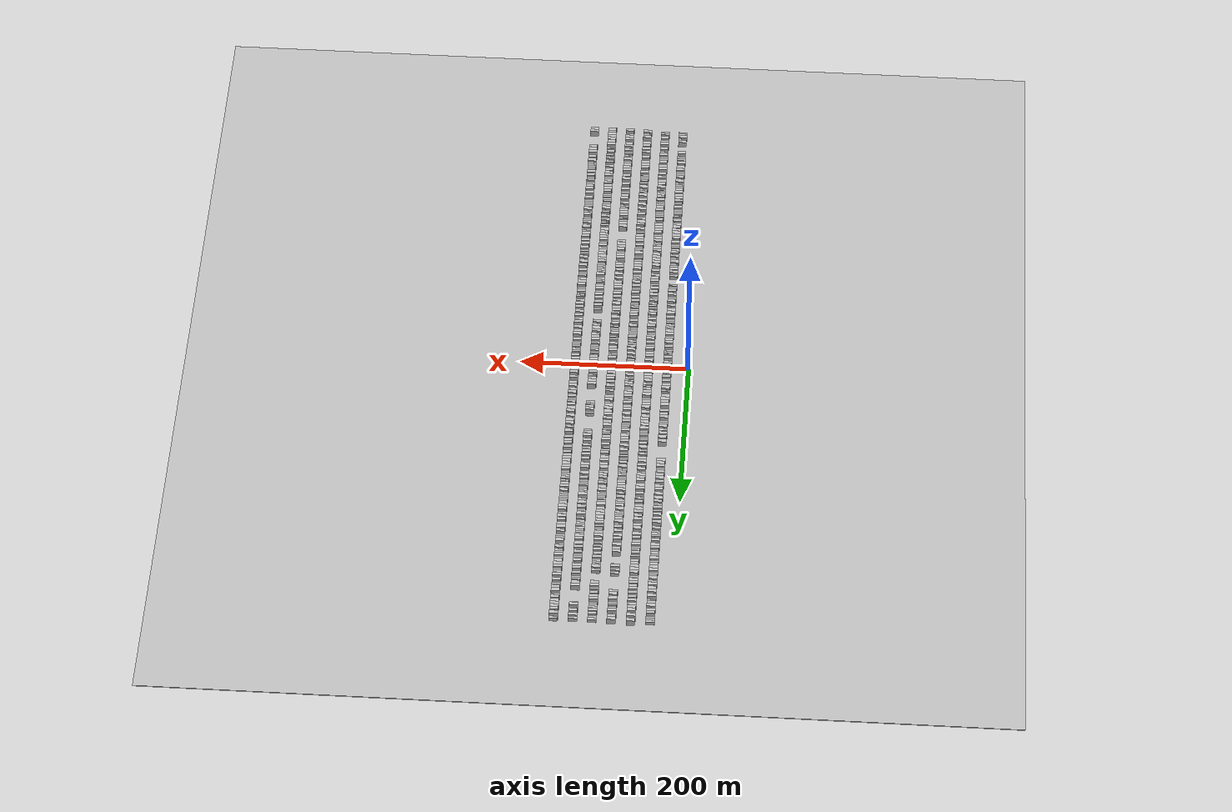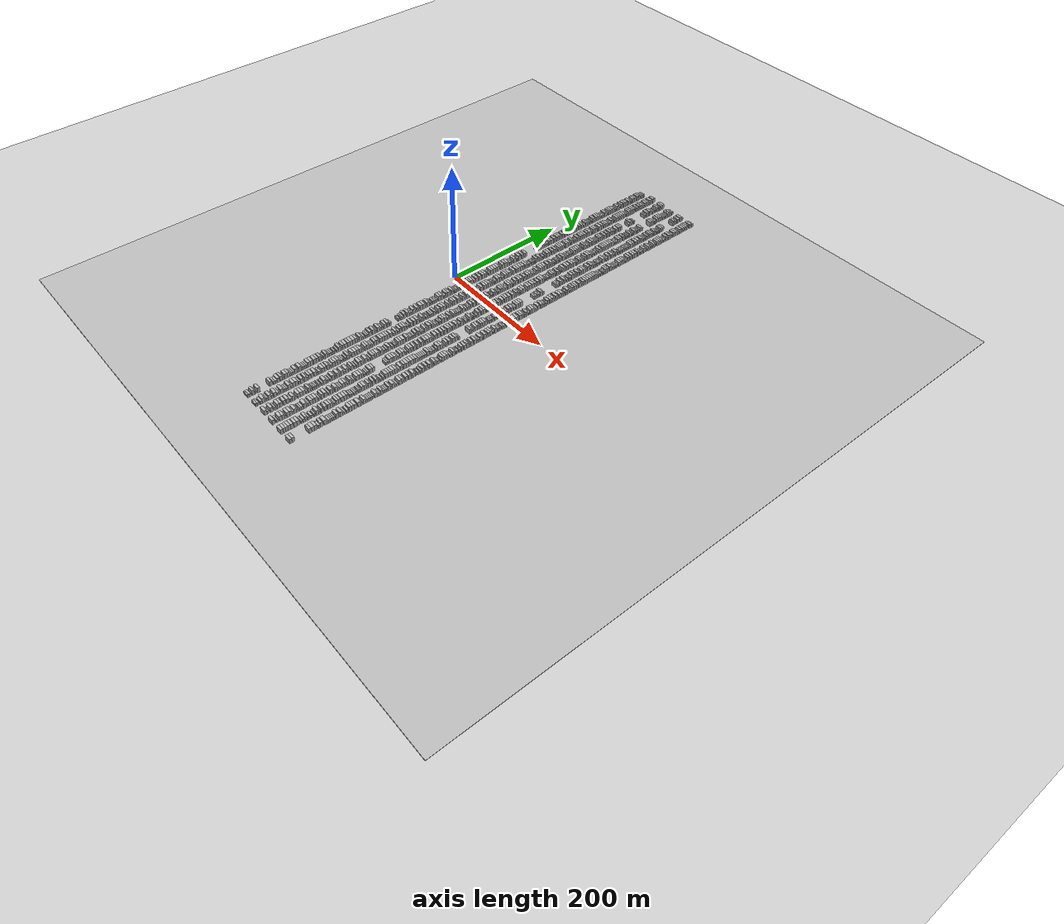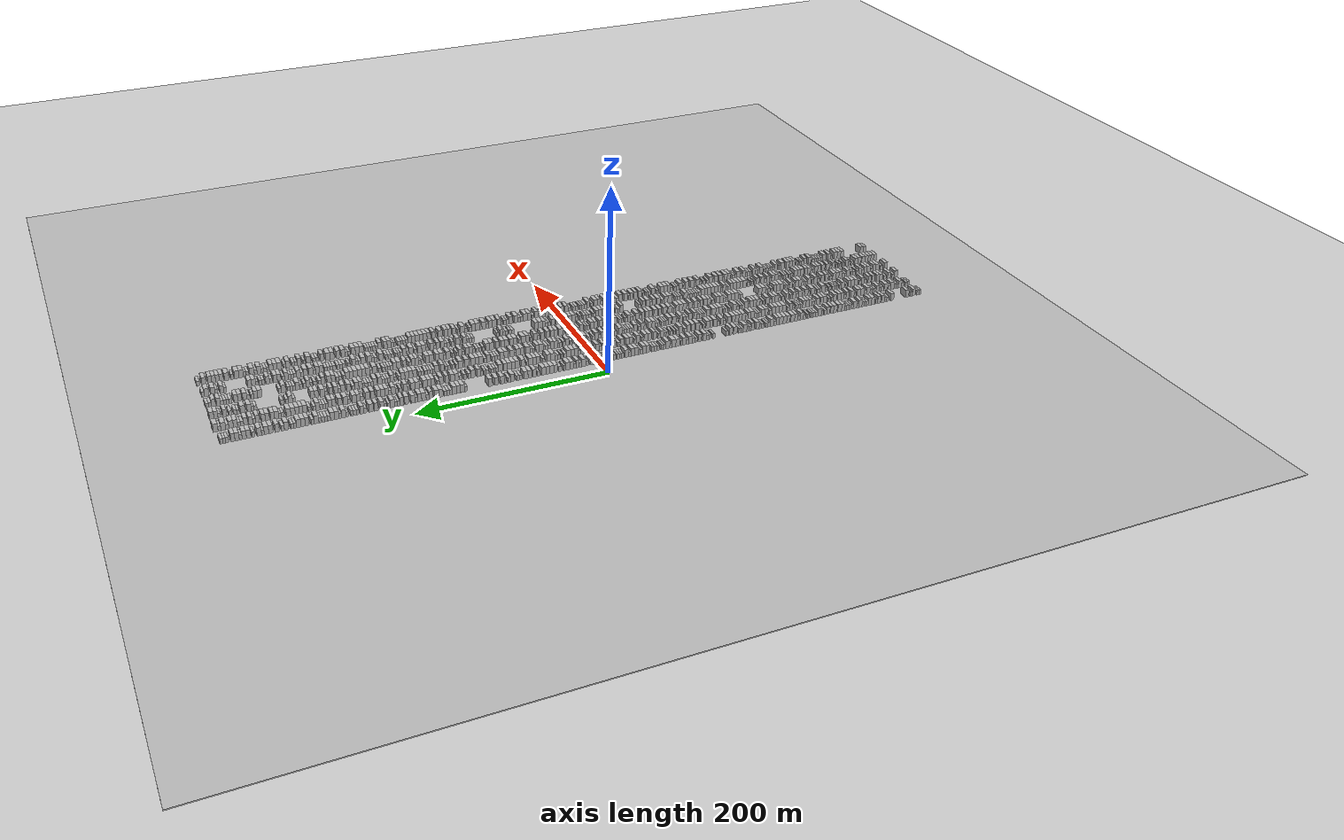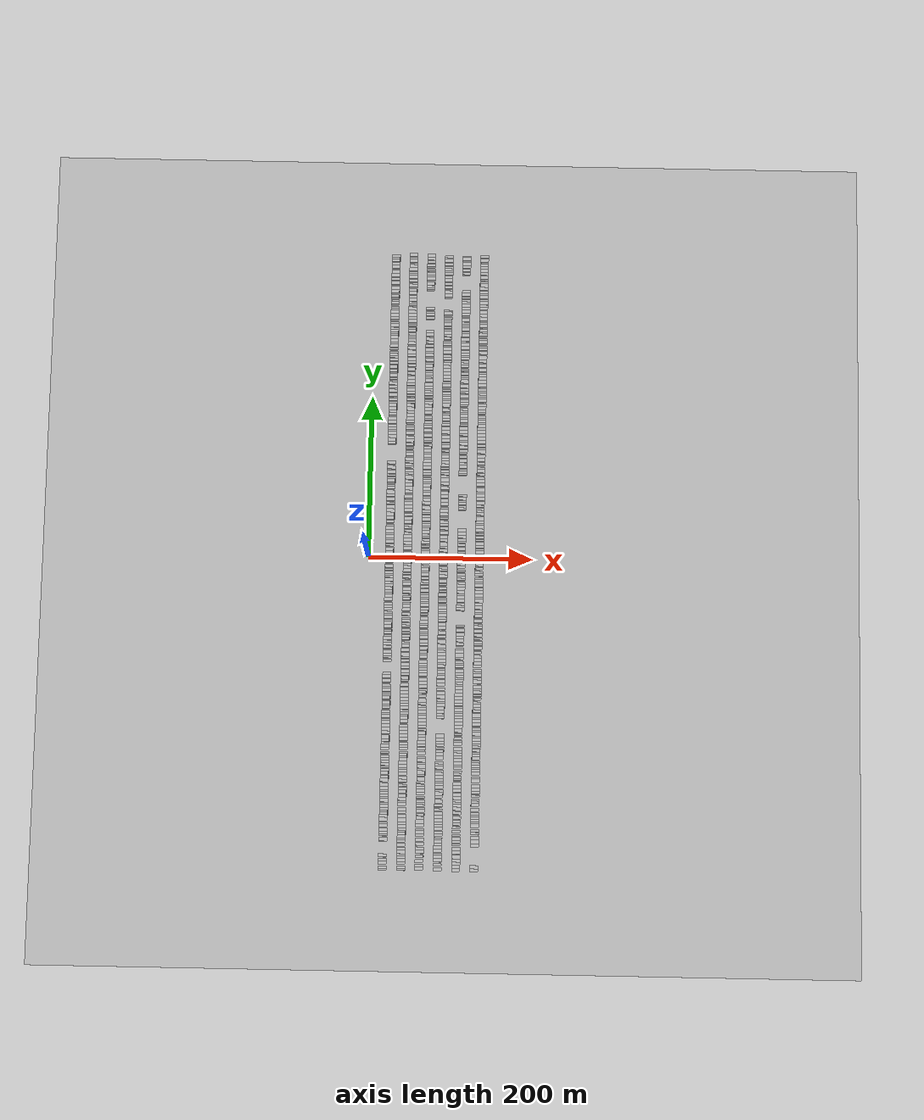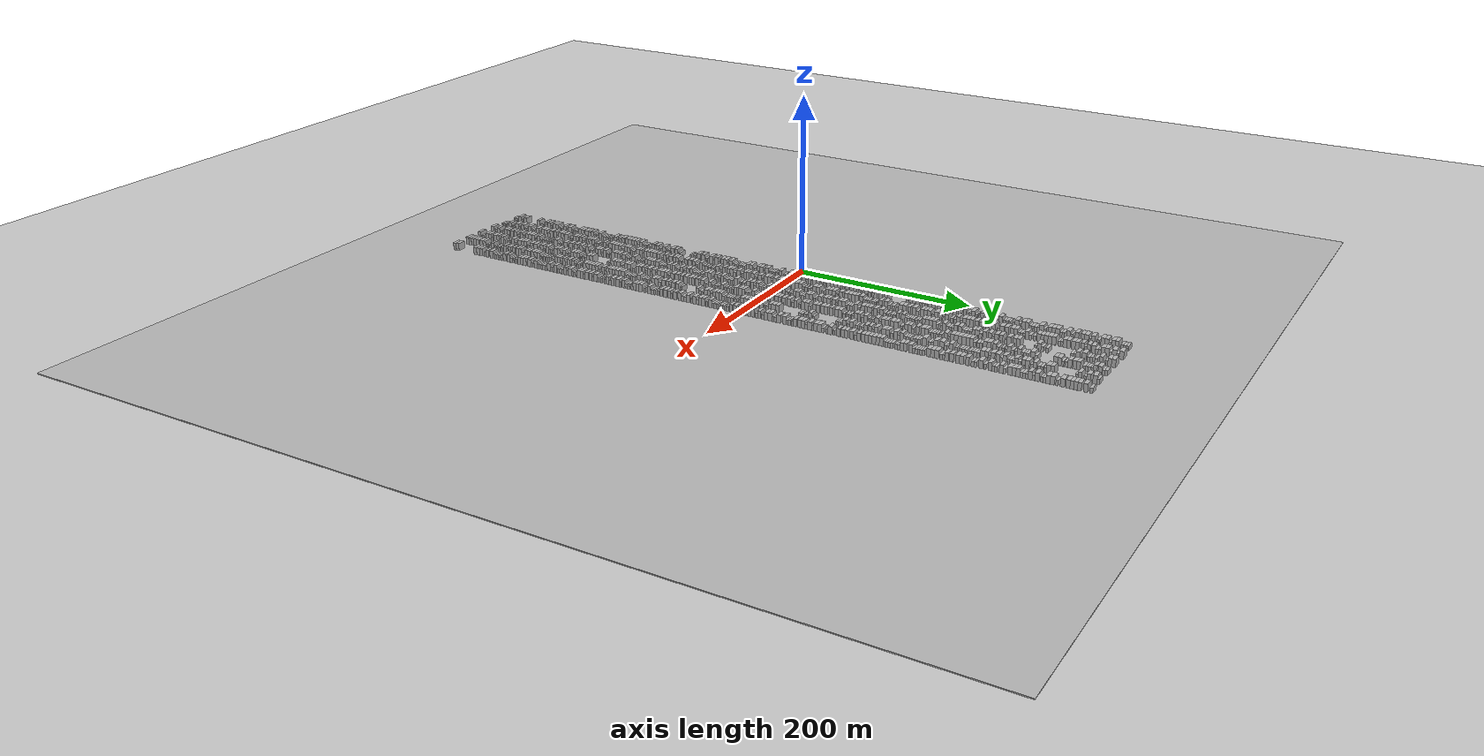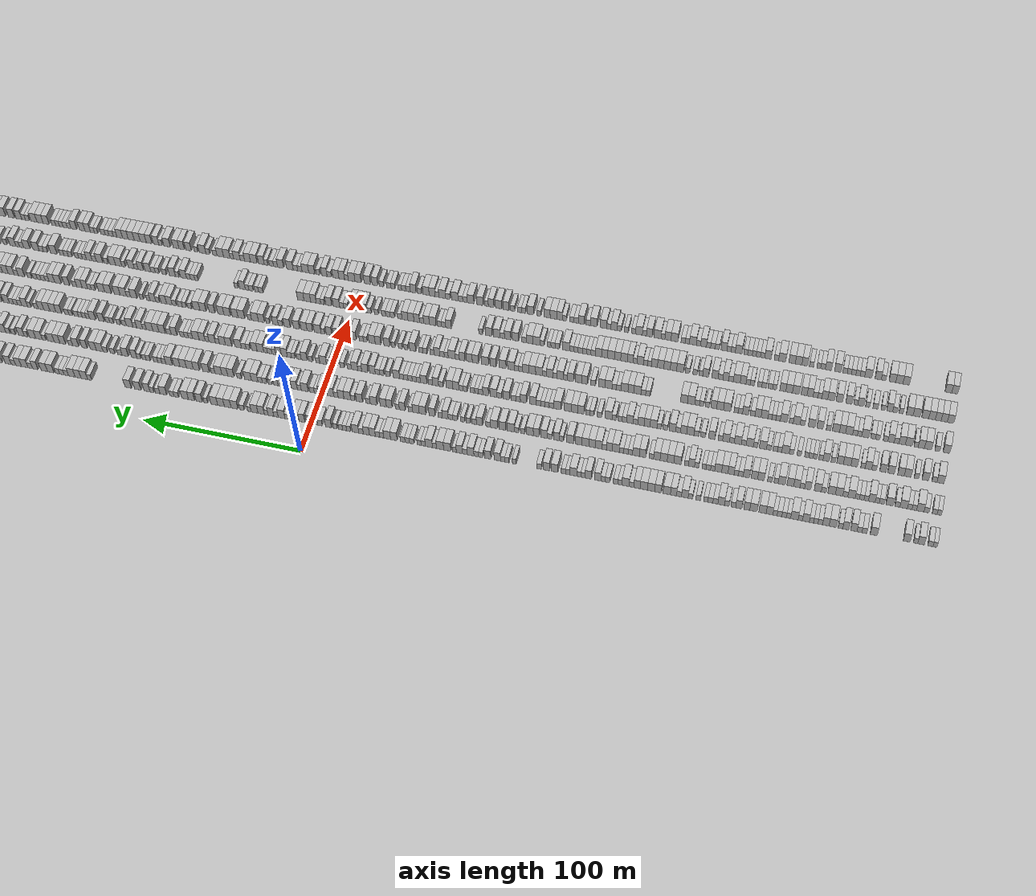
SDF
<?xml version="1.0" encoding="utf-8"?>

<sdf version="1.6">

   <world name="default">

      <gui fullscreen="0">

         <camera name="user_camera">

            <pose>-15 0 4.57585 0 0 0</pose>

            <view_controller>orbit</view_controller>

         </camera>

      </gui>

      <scene>

         <sky>

           <clouds>

             <speed>12</speed>

           </clouds>

         </sky>

         <ambient>0.4 0.4 0.4 1</ambient>

         <background>0.7 0.7 0.7 1</background>

         <shadows>1</shadows>

      </scene>

      <gravity>0 0 -9.8066</gravity>

      <magnetic_field>6e-06 2.3e-05 -4.2e-05</magnetic_field>

      <physics default="0" name="default_physics" type="ode">

         <ode>

            <solver>

               <type>quick</type>

               <iters>10</iters>

               <sor>1.0</sor>

               <use_dynamic_moi_rescaling>0</use_dynamic_moi_rescaling>

            </solver>

            <constraints>

               <cfm>0</cfm>

               <erp>0.2</erp>

               <contact_max_correcting_vel>100</contact_max_correcting_vel>

               <contact_surface_layer>0.001</contact_surface_layer>

            </constraints>

         </ode>

         <max_step_size>0.004</max_step_size>

         <real_time_factor>1</real_time_factor>

         <real_time_update_rate>250</real_time_update_rate>

      </physics>

      <light name="sun" type="directional">

         <cast_shadows>1</cast_shadows>

         <pose>0 0 10 0 0 0</pose>

         <diffuse>0.8 0.8 0.8 1</diffuse>

         <specular>0.2 0.2 0.2 1</specular>

         <attenuation>

            <range>1000</range>

            <constant>0.9</constant>

            <linear>0.01</linear>

            <quadratic>0.001</quadratic>

         </attenuation>

         <direction>-0.5 0.1 -0.9</direction>

      </light>

      <include>

         <name>ground_plane_1</name>

         <uri>model://HANNAS_ground_plane</uri>

         <pose>0 0 0  0 0 0</pose>

      </include>

      <include>

         <name>ground_plane_2</name>

         <uri>model://HANNAS_ground_plane</uri>

         <pose>100 0 0  0 0 0</pose>

      </include>

      <model name="building_1">

         <static>1</static>

         <pose frame="">25.0000 -378.7936 0 0.000000 0.000000 0.000000</pose>

         <link name="link">

            <pose frame="">0 0 3.00 0 0 0</pose>

            <collision name="collision">

               <geometry>

                  <box>

                     <size>10.0000 2.4128 6.0000</size>

                  </box>

               </geometry>

               <max_contacts>10</max_contacts>

               <surface>

                  <contact>

                     <ode/>

                  </contact>

                  <bounce/>

                  <friction>

                     <torsional>

                        <ode/>

                     </torsional>

                     <ode/>

                  </friction>

               </surface>

            </collision>

            <visual name="visual">

               <cast_shadows>0</cast_shadows>

               <geometry>

                  <box>

                     <size>10.0000 2.4128 6.0000</size>

                  </box>

               </geometry>

               <material>

                  <script>

                     <uri>model://HANNAS_wall/materials/scripts</uri>

                     <uri>model://HANNAS_wall/materials/textures</uri>

                     <name>vrc/HANNAS_wall</name>

                  </script>

               </material>

            </visual>

            <self_collide>0</self_collide>

            <enable_wind>0</enable_wind>

            <kinematic>0</kinematic>

         </link>

      </model>

      <model name="building_2">

         <static>1</static>

         <pose frame="">25.0000 -376.0949 0 0.000000 0.000000 0.000000</pose>

         <link name="link">

            <pose frame="">0 0 3.00 0 0 0</pose>

            <collision name="collision">

               <geometry>

                  <box>

                     <size>10.0000 2.9847 6.0000</size>

                  </box>

               </geometry>

               <max_contacts>10</max_contacts>

               <surface>

                  <contact>

                     <ode/>

                  </contact>

                  <bounce/>

                  <friction>

                     <torsional>

                        <ode/>

                     </torsional>

                     <ode/>

                  </friction>

               </surface>

            </collision>

            <visual name="visual">

               <cast_shadows>0</cast_shadows>

               <geometry>

                  <box>

                     <size>10.0000 2.9847 6.0000</size>

                  </box>

               </geometry>

               <material>

                  <script>

                     <uri>model://HANNAS_wall/materials/scripts</uri>

                     <uri>model://HANNAS_wall/materials/textures</uri>

                     <name>vrc/HANNAS_wall</name>

                  </script>

               </material>

            </visual>

            <self_collide>0</self_collide>

            <enable_wind>0</enable_wind>

            <kinematic>0</kinematic>

         </link>

      </model>

      <model name="building_3">

         <static>1</static>

         <pose frame="">25.0000 -370.6776 0 0.000000 0.000000 0.000000</pose>

         <link name="link">

            <pose frame="">0 0 4.50 0 0 0</pose>

            <collision name="collision">

               <geometry>

                  <box>

                     <size>10.0000 3.8498 9.0000</size>

                  </box>

               </geometry>

               <max_contacts>10</max_contacts>

               <surface>

                  <contact>

                     <ode/>

                  </contact>

                  <bounce/>

                  <friction>

                     <torsional>

                        <ode/>

                     </torsional>

                     <ode/>

                  </friction>

               </surface>

            </collision>

            <visual name="visual">

               <cast_shadows>0</cast_shadows>

               <geometry>

                  <box>

                     <size>10.0000 3.8498 9.0000</size>

                  </box>

               </geometry>

               <material>

                  <script>

                     <uri>model://HANNAS_wall/materials/scripts</uri>

                     <uri>model://HANNAS_wall/materials/textures</uri>

                     <name>vrc/HANNAS_wall</name>

                  </script>

               </material>

            </visual>

            <self_collide>0</self_collide>

            <enable_wind>0</enable_wind>

            <kinematic>0</kinematic>

         </link>

      </model>

      <model name="building_4">

         <static>1</static>

         <pose frame="">25.0000 -367.5244 0 0.000000 0.000000 0.000000</pose>

         <link name="link">

            <pose frame="">0 0 3.00 0 0 0</pose>

            <collision name="collision">

               <geometry>

                  <box>

                     <size>10.0000 2.4567 6.0000</size>

                  </box>

               </geometry>

               <max_contacts>10</max_contacts>

               <surface>

                  <contact>

                     <ode/>

                  </contact>

                  <bounce/>

                  <friction>

                     <torsional>

                        <ode/>

                     </torsional>

                     <ode/>

                  </friction>

               </surface>

            </collision>

            <visual name="visual">

               <cast_shadows>0</cast_shadows>

               <geometry>

                  <box>

                     <size>10.0000 2.4567 6.0000</size>

                  </box>

               </geometry>

               <material>

                  <script>

                     <uri>model://HANNAS_wall/materials/scripts</uri>

                     <uri>model://HANNAS_wall/materials/textures</uri>

                     <name>vrc/HANNAS_wall</name>

                  </script>

               </material>

            </visual>

            <self_collide>0</self_collide>

            <enable_wind>0</enable_wind>

            <kinematic>0</kinematic>

         </link>

      </model>

      <model name="building_5">

         <static>1</static>

         <pose frame="">25.0000 -362.3169 0 0.000000 0.000000 0.000000</pose>

         <link name="link">

            <pose frame="">0 0 4.50 0 0 0</pose>

            <collision name="collision">

               <geometry>

                  <box>

                     <size>10.0000 3.9582 9.0000</size>

                  </box>

               </geometry>

               <max_contacts>10</max_contacts>

               <surface>

                  <contact>

                     <ode/>

                  </contact>

                  <bounce/>

                  <friction>

                     <torsional>

                        <ode/>

                     </torsional>

                     <ode/>

                  </friction>

               </surface>

            </collision>

            <visual name="visual">

               <cast_shadows>0</cast_shadows>

               <geometry>

                  <box>

                     <size>10.0000 3.9582 9.0000</size>

                  </box>

               </geometry>

               <material>

                  <script>

                     <uri>model://HANNAS_wall/materials/scripts</uri>

                     <uri>model://HANNAS_wall/materials/textures</uri>

                     <name>vrc/HANNAS_wall</name>

                  </script>

               </material>

            </visual>

            <self_collide>0</self_collide>

            <enable_wind>0</enable_wind>

            <kinematic>0</kinematic>

         </link>

      </model>

      <model name="building_6">

         <static>1</static>

         <pose frame="">25.0000 -343.0834 0 0.000000 0.000000 0.000000</pose>

         <link name="link">

            <pose frame="">0 0 4.50 0 0 0</pose>

            <collision name="collision">

               <geometry>

                  <box>

                     <size>10.0000 4.1696 9.0000</size>

                  </box>

               </geometry>

               <max_contacts>10</max_contacts>

               <surface>

                  <contact>

                     <ode/>

                  </contact>

                  <bounce/>

                  <friction>

                     <torsional>

                        <ode/>

                     </torsional>

                     <ode/>

                  </friction>

               </surface>

            </collision>

            <visual name="visual">

               <cast_shadows>0</cast_shadows>

               <geometry>

                  <box>

                     <size>10.0000 4.1696 9.0000</size>

                  </box>

               </geometry>

               <material>

                  <script>

                     <uri>model://HANNAS_wall/materials/scripts</uri>

                     <uri>model://HANNAS_wall/materials/textures</uri>

                     <name>vrc/HANNAS_wall</name>

                  </script>

               </material>

            </visual>

            <self_collide>0</self_collide>

            <enable_wind>0</enable_wind>

            <kinematic>0</kinematic>

         </link>

      </model>

      <model name="building_7">

         <static>1</static>

         <pose frame="">25.0000 -337.5712 0 0.000000 0.000000 0.000000</pose>

         <link name="link">

            <pose frame="">0 0 3.00 0 0 0</pose>

            <collision name="collision">

               <geometry>

                  <box>

                     <size>10.0000 2.8549 6.0000</size>

                  </box>

               </geometry>

               <max_contacts>10</max_contacts>

               <surface>

                  <contact>

                     <ode/>

                  </contact>

                  <bounce/>

                  <friction>

                     <torsional>

                        <ode/>

                     </torsional>

                     <ode/>

                  </friction>

               </surface>

            </collision>

            <visual name="visual">

               <cast_shadows>0</cast_shadows>

               <geometry>

                  <box>

                     <size>10.0000 2.8549 6.0000</size>

                  </box>

               </geometry>

               <material>

                  <script>

                     <uri>model://HANNAS_wall/materials/scripts</uri>

                     <uri>model://HANNAS_wall/materials/textures</uri>

                     <name>vrc/HANNAS_wall</name>

                  </script>

               </material>

            </visual>

            <self_collide>0</self_collide>

            <enable_wind>0</enable_wind>

            <kinematic>0</kinematic>

         </link>

      </model>

      <model name="building_8">

         <static>1</static>

         <pose frame="">25.0000 -334.6668 0 0.000000 0.000000 0.000000</pose>

         <link name="link">

            <pose frame="">0 0 3.00 0 0 0</pose>

            <collision name="collision">

               <geometry>

                  <box>

                     <size>10.0000 2.9538 6.0000</size>

                  </box>

               </geometry>

               <max_contacts>10</max_contacts>

               <surface>

                  <contact>

                     <ode/>

                  </contact>

                  <bounce/>

                  <friction>

                     <torsional>

                        <ode/>

                     </torsional>

                     <ode/>

                  </friction>

               </surface>

            </collision>

            <visual name="visual">

               <cast_shadows>0</cast_shadows>

               <geometry>

                  <box>

                     <size>10.0000 2.9538 6.0000</size>

                  </box>

               </geometry>

               <material>

                  <script>

                     <uri>model://HANNAS_wall/materials/scripts</uri>

                     <uri>model://HANNAS_wall/materials/textures</uri>

                     <name>vrc/HANNAS_wall</name>

                  </script>

               </material>

            </visual>

            <self_collide>0</self_collide>

            <enable_wind>0</enable_wind>

            <kinematic>0</kinematic>

         </link>

      </model>

      <model name="building_9">

         <static>1</static>

         <pose frame="">25.0000 -331.3615 0 0.000000 0.000000 0.000000</pose>

         <link name="link">

            <pose frame="">0 0 4.50 0 0 0</pose>

            <collision name="collision">

               <geometry>

                  <box>

                     <size>10.0000 3.6569 9.0000</size>

                  </box>

               </geometry>

               <max_contacts>10</max_contacts>

               <surface>

                  <contact>

                     <ode/>

                  </contact>

                  <bounce/>

                  <friction>

                     <torsional>

                        <ode/>

                     </torsional>

                     <ode/>

                  </friction>

               </surface>

            </collision>

            <visual name="visual">

               <cast_shadows>0</cast_shadows>

               <geometry>

                  <box>

                     <size>10.0000 3.6569 9.0000</size>

                  </box>

               </geometry>

               <material>

                  <script>

                     <uri>model://HANNAS_wall/materials/scripts</uri>

                     <uri>model://HANNAS_wall/materials/textures</uri>

                     <name>vrc/HANNAS_wall</name>

                  </script>

               </material>

            </visual>

            <self_collide>0</self_collide>

            <enable_wind>0</enable_wind>

            <kinematic>0</kinematic>

         </link>

      </model>

      <model name="building_10">

         <static>1</static>

         <pose frame="">25.0000 -326.6936 0 0.000000 0.000000 0.000000</pose>

         <link name="link">

            <pose frame="">0 0 4.50 0 0 0</pose>

            <collision name="collision">

               <geometry>

                  <box>

                     <size>10.0000 3.6789 9.0000</size>

                  </box>

               </geometry>

               <max_contacts>10</max_contacts>

               <surface>

                  <contact>

                     <ode/>

                  </contact>

                  <bounce/>

                  <friction>

                     <torsional>

                        <ode/>

                     </torsional>

                     <ode/>

                  </friction>

               </surface>

            </collision>

            <visual name="visual">

               <cast_shadows>0</cast_shadows>

               <geometry>

                  <box>

                     <size>10.0000 3.6789 9.0000</size>

                  </box>

               </geometry>

               <material>

                  <script>

                     <uri>model://HANNAS_wall/materials/scripts</uri>

                     <uri>model://HANNAS_wall/materials/textures</uri>

                     <name>vrc/HANNAS_wall</name>

                  </script>

               </material>

            </visual>

            <self_collide>0</self_collide>

            <enable_wind>0</enable_wind>

            <kinematic>0</kinematic>

         </link>

      </model>

      <model name="building_11">

         <static>1</static>

         <pose frame="">25.0000 -323.5289 0 0.000000 0.000000 0.000000</pose>

         <link name="link">

            <pose frame="">0 0 3.00 0 0 0</pose>

            <collision name="collision">

               <geometry>

                  <box>

                     <size>10.0000 2.6506 6.0000</size>

                  </box>

               </geometry>

               <max_contacts>10</max_contacts>

               <surface>

                  <contact>

                     <ode/>

                  </contact>

                  <bounce/>

                  <friction>

                     <torsional>

                        <ode/>

                     </torsional>

                     <ode/>

                  </friction>

               </surface>

            </collision>

            <visual name="visual">

               <cast_shadows>0</cast_shadows>

               <geometry>

                  <box>

                     <size>10.0000 2.6506 6.0000</size>

                  </box>

               </geometry>

               <material>

                  <script>

                     <uri>model://HANNAS_wall/materials/scripts</uri>

                     <uri>model://HANNAS_wall/materials/textures</uri>

                     <name>vrc/HANNAS_wall</name>

                  </script>

               </material>

            </visual>

            <self_collide>0</self_collide>

            <enable_wind>0</enable_wind>

            <kinematic>0</kinematic>

         </link>

      </model>

      <model name="building_12">

         <static>1</static>

         <pose frame="">25.0000 -319.0216 0 0.000000 0.000000 0.000000</pose>

         <link name="link">

            <pose frame="">0 0 4.50 0 0 0</pose>

            <collision name="collision">

               <geometry>

                  <box>

                     <size>10.0000 4.3639 9.0000</size>

                  </box>

               </geometry>

               <max_contacts>10</max_contacts>

               <surface>

                  <contact>

                     <ode/>

                  </contact>

                  <bounce/>

                  <friction>

                     <torsional>

                        <ode/>

                     </torsional>

                     <ode/>

                  </friction>

               </surface>

            </collision>

            <visual name="visual">

               <cast_shadows>0</cast_shadows>

               <geometry>

                  <box>

                     <size>10.0000 4.3639 9.0000</size>

                  </box>

               </geometry>

               <material>

                  <script>

                     <uri>model://HANNAS_wall/materials/scripts</uri>

                     <uri>model://HANNAS_wall/materials/textures</uri>

                     <name>vrc/HANNAS_wall</name>

                  </script>

               </material>

            </visual>

            <self_collide>0</self_collide>

            <enable_wind>0</enable_wind>

            <kinematic>0</kinematic>

         </link>

      </model>

      <model name="building_13">

         <static>1</static>

         <pose frame="">25.0000 -314.9039 0 0.000000 0.000000 0.000000</pose>

         <link name="link">

            <pose frame="">0 0 4.50 0 0 0</pose>

            <collision name="collision">

               <geometry>

                  <box>

                     <size>10.0000 3.8716 9.0000</size>

                  </box>

               </geometry>

               <max_contacts>10</max_contacts>

               <surface>

                  <contact>

                     <ode/>

                  </contact>

                  <bounce/>

                  <friction>

                     <torsional>

                        <ode/>

                     </torsional>

                     <ode/>

                  </friction>

               </surface>

            </collision>

            <visual name="visual">

               <cast_shadows>0</cast_shadows>

               <geometry>

                  <box>

                     <size>10.0000 3.8716 9.0000</size>

                  </box>

               </geometry>

               <material>

                  <script>

                     <uri>model://HANNAS_wall/materials/scripts</uri>

                     <uri>model://HANNAS_wall/materials/textures</uri>

                     <name>vrc/HANNAS_wall</name>

                  </script>

               </material>

            </visual>

            <self_collide>0</self_collide>

            <enable_wind>0</enable_wind>

            <kinematic>0</kinematic>

         </link>

      </model>

      <model name="building_14">

         <static>1</static>

         <pose frame="">25.0000 -311.6025 0 0.000000 0.000000 0.000000</pose>

         <link name="link">

            <pose frame="">0 0 3.00 0 0 0</pose>

            <collision name="collision">

               <geometry>

                  <box>

                     <size>10.0000 2.7310 6.0000</size>

                  </box>

               </geometry>

               <max_contacts>10</max_contacts>

               <surface>

                  <contact>

                     <ode/>

                  </contact>

                  <bounce/>

                  <friction>

                     <torsional>

                        <ode/>

                     </torsional>

                     <ode/>

                  </friction>

               </surface>

            </collision>

            <visual name="visual">

               <cast_shadows>0</cast_shadows>

               <geometry>

                  <box>

                     <size>10.0000 2.7310 6.0000</size>

                  </box>

               </geometry>

               <material>

                  <script>

                     <uri>model://HANNAS_wall/materials/scripts</uri>

                     <uri>model://HANNAS_wall/materials/textures</uri>

                     <name>vrc/HANNAS_wall</name>

                  </script>

               </material>

            </visual>

            <self_collide>0</self_collide>

            <enable_wind>0</enable_wind>

            <kinematic>0</kinematic>

         </link>

      </model>

      <model name="building_15">

         <static>1</static>

         <pose frame="">25.0000 -308.9841 0 0.000000 0.000000 0.000000</pose>

         <link name="link">

            <pose frame="">0 0 3.00 0 0 0</pose>

            <collision name="collision">

               <geometry>

                  <box>

                     <size>10.0000 2.5059 6.0000</size>

                  </box>

               </geometry>

               <max_contacts>10</max_contacts>

               <surface>

                  <contact>

                     <ode/>

                  </contact>

                  <bounce/>

                  <friction>

                     <torsional>

                        <ode/>

                     </torsional>

                     <ode/>

                  </friction>

               </surface>

            </collision>

            <visual name="visual">

               <cast_shadows>0</cast_shadows>

               <geometry>

                  <box>

                     <size>10.0000 2.5059 6.0000</size>

                  </box>

               </geometry>

               <material>

                  <script>

                     <uri>model://HANNAS_wall/materials/scripts</uri>

                     <uri>model://HANNAS_wall/materials/textures</uri>

                     <name>vrc/HANNAS_wall</name>

                  </script>

               </material>

            </visual>

            <self_collide>0</self_collide>

            <enable_wind>0</enable_wind>

            <kinematic>0</kinematic>

         </link>

      </model>

      <model name="building_16">

         <static>1</static>

         <pose frame="">25.0000 -306.4358 0 0.000000 0.000000 0.000000</pose>

         <link name="link">

            <pose frame="">0 0 3.00 0 0 0</pose>

            <collision name="collision">

               <geometry>

                  <box>

                     <size>10.0000 2.5905 6.0000</size>

                  </box>

               </geometry>

               <max_contacts>10</max_contacts>

               <surface>

                  <contact>

                     <ode/>

                  </contact>

                  <bounce/>

                  <friction>

                     <torsional>

                        <ode/>

                     </torsional>

                     <ode/>

                  </friction>

               </surface>

            </collision>

            <visual name="visual">

               <cast_shadows>0</cast_shadows>

               <geometry>

                  <box>

                     <size>10.0000 2.5905 6.0000</size>

                  </box>

               </geometry>

               <material>

                  <script>

                     <uri>model://HANNAS_wall/materials/scripts</uri>

                     <uri>model://HANNAS_wall/materials/textures</uri>

                     <name>vrc/HANNAS_wall</name>

                  </script>

               </material>

            </visual>

            <self_collide>0</self_collide>

            <enable_wind>0</enable_wind>

            <kinematic>0</kinematic>

         </link>

      </model>

      <model name="building_17">

         <static>1</static>

         <pose frame="">25.0000 -303.1748 0 0.000000 0.000000 0.000000</pose>

         <link name="link">

            <pose frame="">0 0 4.50 0 0 0</pose>

            <collision name="collision">

               <geometry>

                  <box>

                     <size>10.0000 3.9315 9.0000</size>

                  </box>

               </geometry>

               <max_contacts>10</max_contacts>

               <surface>

                  <contact>

                     <ode/>

                  </contact>

                  <bounce/>

                  <friction>

                     <torsional>

                        <ode/>

                     </torsional>

                     <ode/>

                  </friction>

               </surface>

            </collision>

            <visual name="visual">

               <cast_shadows>0</cast_shadows>

               <geometry>

                  <box>

                     <size>10.0000 3.9315 9.0000</size>

                  </box>

               </geometry>

               <material>

                  <script>

                     <uri>model://HANNAS_wall/materials/scripts</uri>

                     <uri>model://HANNAS_wall/materials/textures</uri>

                     <name>vrc/HANNAS_wall</name>

                  </script>

               </material>

            </visual>

            <self_collide>0</self_collide>

            <enable_wind>0</enable_wind>

            <kinematic>0</kinematic>

         </link>

      </model>

      <model name="building_18">

         <static>1</static>

         <pose frame="">25.0000 -299.8987 0 0.000000 0.000000 0.000000</pose>

         <link name="link">

            <pose frame="">0 0 3.00 0 0 0</pose>

            <collision name="collision">

               <geometry>

                  <box>

                     <size>10.0000 2.6207 6.0000</size>

                  </box>

               </geometry>

               <max_contacts>10</max_contacts>

               <surface>

                  <contact>

                     <ode/>

                  </contact>

                  <bounce/>

                  <friction>

                     <torsional>

                        <ode/>

                     </torsional>

                     <ode/>

                  </friction>

               </surface>

            </collision>

            <visual name="visual">

               <cast_shadows>0</cast_shadows>

               <geometry>

                  <box>

                     <size>10.0000 2.6207 6.0000</size>

                  </box>

               </geometry>

               <material>

                  <script>

                     <uri>model://HANNAS_wall/materials/scripts</uri>

                     <uri>model://HANNAS_wall/materials/textures</uri>

                     <name>vrc/HANNAS_wall</name>

                  </script>

               </material>

            </visual>

            <self_collide>0</self_collide>

            <enable_wind>0</enable_wind>

            <kinematic>0</kinematic>

         </link>

      </model>

      <model name="building_19">

         <static>1</static>

         <pose frame="">25.0000 -296.3752 0 0.000000 0.000000 0.000000</pose>

         <link name="link">

            <pose frame="">0 0 4.50 0 0 0</pose>

            <collision name="collision">

               <geometry>

                  <box>

                     <size>10.0000 4.4264 9.0000</size>

                  </box>

               </geometry>

               <max_contacts>10</max_contacts>

               <surface>

                  <contact>

                     <ode/>

                  </contact>

                  <bounce/>

                  <friction>

                     <torsional>

                        <ode/>

                     </torsional>

                     <ode/>

                  </friction>

               </surface>

            </collision>

            <visual name="visual">

               <cast_shadows>0</cast_shadows>

               <geometry>

                  <box>

                     <size>10.0000 4.4264 9.0000</size>

                  </box>

               </geometry>

               <material>

                  <script>

                     <uri>model://HANNAS_wall/materials/scripts</uri>

                     <uri>model://HANNAS_wall/materials/textures</uri>

                     <name>vrc/HANNAS_wall</name>

                  </script>

               </material>

            </visual>

            <self_collide>0</self_collide>

            <enable_wind>0</enable_wind>

            <kinematic>0</kinematic>

         </link>

      </model>

      <model name="building_20">

         <static>1</static>

         <pose frame="">25.0000 -292.9211 0 0.000000 0.000000 0.000000</pose>

         <link name="link">

            <pose frame="">0 0 3.00 0 0 0</pose>

            <collision name="collision">

               <geometry>

                  <box>

                     <size>10.0000 2.4818 6.0000</size>

                  </box>

               </geometry>

               <max_contacts>10</max_contacts>

               <surface>

                  <contact>

                     <ode/>

                  </contact>

                  <bounce/>

                  <friction>

                     <torsional>

                        <ode/>

                     </torsional>

                     <ode/>

                  </friction>

               </surface>

            </collision>

            <visual name="visual">

               <cast_shadows>0</cast_shadows>

               <geometry>

                  <box>

                     <size>10.0000 2.4818 6.0000</size>

                  </box>

               </geometry>

               <material>

                  <script>

                     <uri>model://HANNAS_wall/materials/scripts</uri>

                     <uri>model://HANNAS_wall/materials/textures</uri>

                     <name>vrc/HANNAS_wall</name>

                  </script>

               </material>

            </visual>

            <self_collide>0</self_collide>

            <enable_wind>0</enable_wind>

            <kinematic>0</kinematic>

         </link>

      </model>

      <model name="building_21">

         <static>1</static>

         <pose frame="">25.0000 -290.3262 0 0.000000 0.000000 0.000000</pose>

         <link name="link">

            <pose frame="">0 0 3.00 0 0 0</pose>

            <collision name="collision">

               <geometry>

                  <box>

                     <size>10.0000 2.7080 6.0000</size>

                  </box>

               </geometry>

               <max_contacts>10</max_contacts>

               <surface>

                  <contact>

                     <ode/>

                  </contact>

                  <bounce/>

                  <friction>

                     <torsional>

                        <ode/>

                     </torsional>

                     <ode/>

                  </friction>

               </surface>

            </collision>

            <visual name="visual">

               <cast_shadows>0</cast_shadows>

               <geometry>

                  <box>

                     <size>10.0000 2.7080 6.0000</size>

                  </box>

               </geometry>

               <material>

                  <script>

                     <uri>model://HANNAS_wall/materials/scripts</uri>

                     <uri>model://HANNAS_wall/materials/textures</uri>

                     <name>vrc/HANNAS_wall</name>

                  </script>

               </material>

            </visual>

            <self_collide>0</self_collide>

            <enable_wind>0</enable_wind>

            <kinematic>0</kinematic>

         </link>

      </model>

      <model name="building_22">

         <static>1</static>

         <pose frame="">25.0000 -287.5246 0 0.000000 0.000000 0.000000</pose>

         <link name="link">

            <pose frame="">0 0 3.00 0 0 0</pose>

            <collision name="collision">

               <geometry>

                  <box>

                     <size>10.0000 2.8952 6.0000</size>

                  </box>

               </geometry>

               <max_contacts>10</max_contacts>

               <surface>

                  <contact>

                     <ode/>

                  </contact>

                  <bounce/>

                  <friction>

                     <torsional>

                        <ode/>

                     </torsional>

                     <ode/>

                  </friction>

               </surface>

            </collision>

            <visual name="visual">

               <cast_shadows>0</cast_shadows>

               <geometry>

                  <box>

                     <size>10.0000 2.8952 6.0000</size>

                  </box>

               </geometry>

               <material>

                  <script>

                     <uri>model://HANNAS_wall/materials/scripts</uri>

                     <uri>model://HANNAS_wall/materials/textures</uri>

                     <name>vrc/HANNAS_wall</name>

                  </script>

               </material>

            </visual>

            <self_collide>0</self_collide>

            <enable_wind>0</enable_wind>

            <kinematic>0</kinematic>

         </link>

      </model>

      <model name="building_23">

         <static>1</static>

         <pose frame="">25.0000 -284.8401 0 0.000000 0.000000 0.000000</pose>

         <link name="link">

            <pose frame="">0 0 3.00 0 0 0</pose>

            <collision name="collision">

               <geometry>

                  <box>

                     <size>10.0000 2.4737 6.0000</size>

                  </box>

               </geometry>

               <max_contacts>10</max_contacts>

               <surface>

                  <contact>

                     <ode/>

                  </contact>

                  <bounce/>

                  <friction>

                     <torsional>

                        <ode/>

                     </torsional>

                     <ode/>

                  </friction>

               </surface>

            </collision>

            <visual name="visual">

               <cast_shadows>0</cast_shadows>

               <geometry>

                  <box>

                     <size>10.0000 2.4737 6.0000</size>

                  </box>

               </geometry>

               <material>

                  <script>

                     <uri>model://HANNAS_wall/materials/scripts</uri>

                     <uri>model://HANNAS_wall/materials/textures</uri>

                     <name>vrc/HANNAS_wall</name>

                  </script>

               </material>

            </visual>

            <self_collide>0</self_collide>

            <enable_wind>0</enable_wind>

            <kinematic>0</kinematic>

         </link>

      </model>

      <model name="building_24">

         <static>1</static>

         <pose frame="">25.0000 -281.6350 0 0.000000 0.000000 0.000000</pose>

         <link name="link">

            <pose frame="">0 0 4.50 0 0 0</pose>

            <collision name="collision">

               <geometry>

                  <box>

                     <size>10.0000 3.9365 9.0000</size>

                  </box>

               </geometry>

               <max_contacts>10</max_contacts>

               <surface>

                  <contact>

                     <ode/>

                  </contact>

                  <bounce/>

                  <friction>

                     <torsional>

                        <ode/>

                     </torsional>

                     <ode/>

                  </friction>

               </surface>

            </collision>

            <visual name="visual">

               <cast_shadows>0</cast_shadows>

               <geometry>

                  <box>

                     <size>10.0000 3.9365 9.0000</size>

                  </box>

               </geometry>

               <material>

                  <script>

                     <uri>model://HANNAS_wall/materials/scripts</uri>

                     <uri>model://HANNAS_wall/materials/textures</uri>

                     <name>vrc/HANNAS_wall</name>

                  </script>

               </material>

            </visual>

            <self_collide>0</self_collide>

            <enable_wind>0</enable_wind>

            <kinematic>0</kinematic>

         </link>

      </model>

      <model name="building_25">

         <static>1</static>

         <pose frame="">25.0000 -277.4600 0 0.000000 0.000000 0.000000</pose>

         <link name="link">

            <pose frame="">0 0 4.50 0 0 0</pose>

            <collision name="collision">

               <geometry>

                  <box>

                     <size>10.0000 4.4136 9.0000</size>

                  </box>

               </geometry>

               <max_contacts>10</max_contacts>

               <surface>

                  <contact>

                     <ode/>

                  </contact>

                  <bounce/>

                  <friction>

                     <torsional>

                        <ode/>

                     </torsional>

                     <ode/>

                  </friction>

               </surface>

            </collision>

            <visual name="visual">

               <cast_shadows>0</cast_shadows>

               <geometry>

                  <box>

                     <size>10.0000 4.4136 9.0000</size>

                  </box>

               </geometry>

               <material>

                  <script>

                     <uri>model://HANNAS_wall/materials/scripts</uri>

                     <uri>model://HANNAS_wall/materials/textures</uri>

                     <name>vrc/HANNAS_wall</name>

                  </script>

               </material>

            </visual>

            <self_collide>0</self_collide>

            <enable_wind>0</enable_wind>

            <kinematic>0</kinematic>

         </link>

      </model>

      <model name="building_26">

         <static>1</static>

         <pose frame="">25.0000 -272.0558 0 0.000000 0.000000 0.000000</pose>

         <link name="link">

            <pose frame="">0 0 4.50 0 0 0</pose>

            <collision name="collision">

               <geometry>

                  <box>

                     <size>10.0000 4.3947 9.0000</size>

                  </box>

               </geometry>

               <max_contacts>10</max_contacts>

               <surface>

                  <contact>

                     <ode/>

                  </contact>

                  <bounce/>

                  <friction>

                     <torsional>

                        <ode/>

                     </torsional>

                     <ode/>

                  </friction>

               </surface>

            </collision>

            <visual name="visual">

               <cast_shadows>0</cast_shadows>

               <geometry>

                  <box>

                     <size>10.0000 4.3947 9.0000</size>

                  </box>

               </geometry>

               <material>

                  <script>

                     <uri>model://HANNAS_wall/materials/scripts</uri>

                     <uri>model://HANNAS_wall/materials/textures</uri>

                     <name>vrc/HANNAS_wall</name>

                  </script>

               </material>

            </visual>

            <self_collide>0</self_collide>

            <enable_wind>0</enable_wind>

            <kinematic>0</kinematic>

         </link>

      </model>

      <model name="building_27">

         <static>1</static>

         <pose frame="">25.0000 -268.0545 0 0.000000 0.000000 0.000000</pose>

         <link name="link">

            <pose frame="">0 0 4.50 0 0 0</pose>

            <collision name="collision">

               <geometry>

                  <box>

                     <size>10.0000 3.6079 9.0000</size>

                  </box>

               </geometry>

               <max_contacts>10</max_contacts>

               <surface>

                  <contact>

                     <ode/>

                  </contact>

                  <bounce/>

                  <friction>

                     <torsional>

                        <ode/>

                     </torsional>

                     <ode/>

                  </friction>

               </surface>

            </collision>

            <visual name="visual">

               <cast_shadows>0</cast_shadows>

               <geometry>

                  <box>

                     <size>10.0000 3.6079 9.0000</size>

                  </box>

               </geometry>

               <material>

                  <script>

                     <uri>model://HANNAS_wall/materials/scripts</uri>

                     <uri>model://HANNAS_wall/materials/textures</uri>

                     <name>vrc/HANNAS_wall</name>

                  </script>

               </material>

            </visual>

            <self_collide>0</self_collide>

            <enable_wind>0</enable_wind>

            <kinematic>0</kinematic>

         </link>

      </model>

      <model name="building_28">

         <static>1</static>

         <pose frame="">25.0000 -263.3341 0 0.000000 0.000000 0.000000</pose>

         <link name="link">

            <pose frame="">0 0 4.50 0 0 0</pose>

            <collision name="collision">

               <geometry>

                  <box>

                     <size>10.0000 3.8330 9.0000</size>

                  </box>

               </geometry>

               <max_contacts>10</max_contacts>

               <surface>

                  <contact>

                     <ode/>

                  </contact>

                  <bounce/>

                  <friction>

                     <torsional>

                        <ode/>

                     </torsional>

                     <ode/>

                  </friction>

               </surface>

            </collision>

            <visual name="visual">

               <cast_shadows>0</cast_shadows>

               <geometry>

                  <box>

                     <size>10.0000 3.8330 9.0000</size>

                  </box>

               </geometry>

               <material>

                  <script>

                     <uri>model://HANNAS_wall/materials/scripts</uri>

                     <uri>model://HANNAS_wall/materials/textures</uri>

                     <name>vrc/HANNAS_wall</name>

                  </script>

               </material>

            </visual>

            <self_collide>0</self_collide>

            <enable_wind>0</enable_wind>

            <kinematic>0</kinematic>

         </link>

      </model>

      <model name="building_29">

         <static>1</static>

         <pose frame="">25.0000 -259.9843 0 0.000000 0.000000 0.000000</pose>

         <link name="link">

            <pose frame="">0 0 3.00 0 0 0</pose>

            <collision name="collision">

               <geometry>

                  <box>

                     <size>10.0000 2.8665 6.0000</size>

                  </box>

               </geometry>

               <max_contacts>10</max_contacts>

               <surface>

                  <contact>

                     <ode/>

                  </contact>

                  <bounce/>

                  <friction>

                     <torsional>

                        <ode/>

                     </torsional>

                     <ode/>

                  </friction>

               </surface>

            </collision>

            <visual name="visual">

               <cast_shadows>0</cast_shadows>

               <geometry>

                  <box>

                     <size>10.0000 2.8665 6.0000</size>

                  </box>

               </geometry>

               <material>

                  <script>

                     <uri>model://HANNAS_wall/materials/scripts</uri>

                     <uri>model://HANNAS_wall/materials/textures</uri>

                     <name>vrc/HANNAS_wall</name>

                  </script>

               </material>

            </visual>

            <self_collide>0</self_collide>

            <enable_wind>0</enable_wind>

            <kinematic>0</kinematic>

         </link>

      </model>

      <model name="building_30">

         <static>1</static>

         <pose frame="">25.0000 -256.1881 0 0.000000 0.000000 0.000000</pose>

         <link name="link">

            <pose frame="">0 0 3.00 0 0 0</pose>

            <collision name="collision">

               <geometry>

                  <box>

                     <size>10.0000 2.7260 6.0000</size>

                  </box>

               </geometry>

               <max_contacts>10</max_contacts>

               <surface>

                  <contact>

                     <ode/>

                  </contact>

                  <bounce/>

                  <friction>

                     <torsional>

                        <ode/>

                     </torsional>

                     <ode/>

                  </friction>

               </surface>

            </collision>

            <visual name="visual">

               <cast_shadows>0</cast_shadows>

               <geometry>

                  <box>

                     <size>10.0000 2.7260 6.0000</size>

                  </box>

               </geometry>

               <material>

                  <script>

                     <uri>model://HANNAS_wall/materials/scripts</uri>

                     <uri>model://HANNAS_wall/materials/textures</uri>

                     <name>vrc/HANNAS_wall</name>

                  </script>

               </material>

            </visual>

            <self_collide>0</self_collide>

            <enable_wind>0</enable_wind>

            <kinematic>0</kinematic>

         </link>

      </model>

      <model name="building_31">

         <static>1</static>

         <pose frame="">25.0000 -252.8242 0 0.000000 0.000000 0.000000</pose>

         <link name="link">

            <pose frame="">0 0 4.50 0 0 0</pose>

            <collision name="collision">

               <geometry>

                  <box>

                     <size>10.0000 4.0017 9.0000</size>

                  </box>

               </geometry>

               <max_contacts>10</max_contacts>

               <surface>

                  <contact>

                     <ode/>

                  </contact>

                  <bounce/>

                  <friction>

                     <torsional>

                        <ode/>

                     </torsional>

                     <ode/>

                  </friction>

               </surface>

            </collision>

            <visual name="visual">

               <cast_shadows>0</cast_shadows>

               <geometry>

                  <box>

                     <size>10.0000 4.0017 9.0000</size>

                  </box>

               </geometry>

               <material>

                  <script>

                     <uri>model://HANNAS_wall/materials/scripts</uri>

                     <uri>model://HANNAS_wall/materials/textures</uri>

                     <name>vrc/HANNAS_wall</name>

                  </script>

               </material>

            </visual>

            <self_collide>0</self_collide>

            <enable_wind>0</enable_wind>

            <kinematic>0</kinematic>

         </link>

      </model>

      <model name="building_32">

         <static>1</static>

         <pose frame="">25.0000 -249.3260 0 0.000000 0.000000 0.000000</pose>

         <link name="link">

            <pose frame="">0 0 3.00 0 0 0</pose>

            <collision name="collision">

               <geometry>

                  <box>

                     <size>10.0000 2.9947 6.0000</size>

                  </box>

               </geometry>

               <max_contacts>10</max_contacts>

               <surface>

                  <contact>

                     <ode/>

                  </contact>

                  <bounce/>

                  <friction>

                     <torsional>

                        <ode/>

                     </torsional>

                     <ode/>

                  </friction>

               </surface>

            </collision>

            <visual name="visual">

               <cast_shadows>0</cast_shadows>

               <geometry>

                  <box>

                     <size>10.0000 2.9947 6.0000</size>

                  </box>

               </geometry>

               <material>

                  <script>

                     <uri>model://HANNAS_wall/materials/scripts</uri>

                     <uri>model://HANNAS_wall/materials/textures</uri>

                     <name>vrc/HANNAS_wall</name>

                  </script>

               </material>

            </visual>

            <self_collide>0</self_collide>

            <enable_wind>0</enable_wind>

            <kinematic>0</kinematic>

         </link>

      </model>

      <model name="building_33">

         <static>1</static>

         <pose frame="">25.0000 -246.3432 0 0.000000 0.000000 0.000000</pose>

         <link name="link">

            <pose frame="">0 0 3.00 0 0 0</pose>

            <collision name="collision">

               <geometry>

                  <box>

                     <size>10.0000 2.9708 6.0000</size>

                  </box>

               </geometry>

               <max_contacts>10</max_contacts>

               <surface>

                  <contact>

                     <ode/>

                  </contact>

                  <bounce/>

                  <friction>

                     <torsional>

                        <ode/>

                     </torsional>

                     <ode/>

                  </friction>

               </surface>

            </collision>

            <visual name="visual">

               <cast_shadows>0</cast_shadows>

               <geometry>

                  <box>

                     <size>10.0000 2.9708 6.0000</size>

                  </box>

               </geometry>

               <material>

                  <script>

                     <uri>model://HANNAS_wall/materials/scripts</uri>

                     <uri>model://HANNAS_wall/materials/textures</uri>

                     <name>vrc/HANNAS_wall</name>

                  </script>

               </material>

            </visual>

            <self_collide>0</self_collide>

            <enable_wind>0</enable_wind>

            <kinematic>0</kinematic>

         </link>

      </model>

      <model name="building_34">

         <static>1</static>

         <pose frame="">25.0000 -243.5842 0 0.000000 0.000000 0.000000</pose>

         <link name="link">

            <pose frame="">0 0 3.00 0 0 0</pose>

            <collision name="collision">

               <geometry>

                  <box>

                     <size>10.0000 2.5471 6.0000</size>

                  </box>

               </geometry>

               <max_contacts>10</max_contacts>

               <surface>

                  <contact>

                     <ode/>

                  </contact>

                  <bounce/>

                  <friction>

                     <torsional>

                        <ode/>

                     </torsional>

                     <ode/>

                  </friction>

               </surface>

            </collision>

            <visual name="visual">

               <cast_shadows>0</cast_shadows>

               <geometry>

                  <box>

                     <size>10.0000 2.5471 6.0000</size>

                  </box>

               </geometry>

               <material>

                  <script>

                     <uri>model://HANNAS_wall/materials/scripts</uri>

                     <uri>model://HANNAS_wall/materials/textures</uri>

                     <name>vrc/HANNAS_wall</name>

                  </script>

               </material>

            </visual>

            <self_collide>0</self_collide>

            <enable_wind>0</enable_wind>

            <kinematic>0</kinematic>

         </link>

      </model>

      <model name="building_35">

         <static>1</static>

         <pose frame="">25.0000 -238.9845 0 0.000000 0.000000 0.000000</pose>

         <link name="link">

            <pose frame="">0 0 3.00 0 0 0</pose>

            <collision name="collision">

               <geometry>

                  <box>

                     <size>10.0000 2.6523 6.0000</size>

                  </box>

               </geometry>

               <max_contacts>10</max_contacts>

               <surface>

                  <contact>

                     <ode/>

                  </contact>

                  <bounce/>

                  <friction>

                     <torsional>

                        <ode/>

                     </torsional>

                     <ode/>

                  </friction>

               </surface>

            </collision>

            <visual name="visual">

               <cast_shadows>0</cast_shadows>

               <geometry>

                  <box>

                     <size>10.0000 2.6523 6.0000</size>

                  </box>

               </geometry>

               <material>

                  <script>

                     <uri>model://HANNAS_wall/materials/scripts</uri>

                     <uri>model://HANNAS_wall/materials/textures</uri>

                     <name>vrc/HANNAS_wall</name>

                  </script>

               </material>

            </visual>

            <self_collide>0</self_collide>

            <enable_wind>0</enable_wind>

            <kinematic>0</kinematic>

         </link>

      </model>

      <model name="building_36">

         <static>1</static>

         <pose frame="">25.0000 -234.3334 0 0.000000 0.000000 0.000000</pose>

         <link name="link">

            <pose frame="">0 0 3.00 0 0 0</pose>

            <collision name="collision">

               <geometry>

                  <box>

                     <size>10.0000 2.6500 6.0000</size>

                  </box>

               </geometry>

               <max_contacts>10</max_contacts>

               <surface>

                  <contact>

                     <ode/>

                  </contact>

                  <bounce/>

                  <friction>

                     <torsional>

                        <ode/>

                     </torsional>

                     <ode/>

                  </friction>

               </surface>

            </collision>

            <visual name="visual">

               <cast_shadows>0</cast_shadows>

               <geometry>

                  <box>

                     <size>10.0000 2.6500 6.0000</size>

                  </box>

               </geometry>

               <material>

                  <script>

                     <uri>model://HANNAS_wall/materials/scripts</uri>

                     <uri>model://HANNAS_wall/materials/textures</uri>

                     <name>vrc/HANNAS_wall</name>

                  </script>

               </material>

            </visual>

            <self_collide>0</self_collide>

            <enable_wind>0</enable_wind>

            <kinematic>0</kinematic>

         </link>

      </model>

      <model name="building_37">

         <static>1</static>

         <pose frame="">25.0000 -231.0118 0 0.000000 0.000000 0.000000</pose>

         <link name="link">

            <pose frame="">0 0 4.50 0 0 0</pose>

            <collision name="collision">

               <geometry>

                  <box>

                     <size>10.0000 3.9930 9.0000</size>

                  </box>

               </geometry>

               <max_contacts>10</max_contacts>

               <surface>

                  <contact>

                     <ode/>

                  </contact>

                  <bounce/>

                  <friction>

                     <torsional>

                        <ode/>

                     </torsional>

                     <ode/>

                  </friction>

               </surface>

            </collision>

            <visual name="visual">

               <cast_shadows>0</cast_shadows>

               <geometry>

                  <box>

                     <size>10.0000 3.9930 9.0000</size>

                  </box>

               </geometry>

               <material>

                  <script>

                     <uri>model://HANNAS_wall/materials/scripts</uri>

                     <uri>model://HANNAS_wall/materials/textures</uri>

                     <name>vrc/HANNAS_wall</name>

                  </script>

               </material>

            </visual>

            <self_collide>0</self_collide>

            <enable_wind>0</enable_wind>

            <kinematic>0</kinematic>

         </link>

      </model>

      <model name="building_38">

         <static>1</static>

         <pose frame="">25.0000 -227.5501 0 0.000000 0.000000 0.000000</pose>

         <link name="link">

            <pose frame="">0 0 3.00 0 0 0</pose>

            <collision name="collision">

               <geometry>

                  <box>

                     <size>10.0000 2.9306 6.0000</size>

                  </box>

               </geometry>

               <max_contacts>10</max_contacts>

               <surface>

                  <contact>

                     <ode/>

                  </contact>

                  <bounce/>

                  <friction>

                     <torsional>

                        <ode/>

                     </torsional>

                     <ode/>

                  </friction>

               </surface>

            </collision>

            <visual name="visual">

               <cast_shadows>0</cast_shadows>

               <geometry>

                  <box>

                     <size>10.0000 2.9306 6.0000</size>

                  </box>

               </geometry>

               <material>

                  <script>

                     <uri>model://HANNAS_wall/materials/scripts</uri>

                     <uri>model://HANNAS_wall/materials/textures</uri>

                     <name>vrc/HANNAS_wall</name>

                  </script>

               </material>

            </visual>

            <self_collide>0</self_collide>

            <enable_wind>0</enable_wind>

            <kinematic>0</kinematic>

         </link>

      </model>

      <model name="building_39">

         <static>1</static>

         <pose frame="">25.0000 -224.2185 0 0.000000 0.000000 0.000000</pose>

         <link name="link">

            <pose frame="">0 0 4.50 0 0 0</pose>

            <collision name="collision">

               <geometry>

                  <box>

                     <size>10.0000 3.7326 9.0000</size>

                  </box>

               </geometry>

               <max_contacts>10</max_contacts>

               <surface>

                  <contact>

                     <ode/>

                  </contact>

                  <bounce/>

                  <friction>

                     <torsional>

                        <ode/>

                     </torsional>

                     <ode/>

                  </friction>

               </surface>

            </collision>

            <visual name="visual">

               <cast_shadows>0</cast_shadows>

               <geometry>

                  <box>

                     <size>10.0000 3.7326 9.0000</size>

                  </box>

               </geometry>

               <material>

                  <script>

                     <uri>model://HANNAS_wall/materials/scripts</uri>

                     <uri>model://HANNAS_wall/materials/textures</uri>

                     <name>vrc/HANNAS_wall</name>

                  </script>

               </material>

            </visual>

            <self_collide>0</self_collide>

            <enable_wind>0</enable_wind>

            <kinematic>0</kinematic>

         </link>

      </model>

      <model name="building_40">

         <static>1</static>

         <pose frame="">25.0000 -220.1170 0 0.000000 0.000000 0.000000</pose>

         <link name="link">

            <pose frame="">0 0 4.50 0 0 0</pose>

            <collision name="collision">

               <geometry>

                  <box>

                     <size>10.0000 4.4703 9.0000</size>

                  </box>

               </geometry>

               <max_contacts>10</max_contacts>

               <surface>

                  <contact>

                     <ode/>

                  </contact>

                  <bounce/>

                  <friction>

                     <torsional>

                        <ode/>

                     </torsional>

                     <ode/>

                  </friction>

               </surface>

            </collision>

            <visual name="visual">

               <cast_shadows>0</cast_shadows>

               <geometry>

                  <box>

                     <size>10.0000 4.4703 9.0000</size>

                  </box>

               </geometry>

               <material>

                  <script>

                     <uri>model://HANNAS_wall/materials/scripts</uri>

                     <uri>model://HANNAS_wall/materials/textures</uri>

                     <name>vrc/HANNAS_wall</name>

                  </script>

               </material>

            </visual>

            <self_collide>0</self_collide>

            <enable_wind>0</enable_wind>

            <kinematic>0</kinematic>

         </link>

      </model>

      <model name="building_41">

         <static>1</static>

         <pose frame="">25.0000 -214.8841 0 0.000000 0.000000 0.000000</pose>

         <link name="link">

            <pose frame="">0 0 4.50 0 0 0</pose>

            <collision name="collision">

               <geometry>

                  <box>

                     <size>10.0000 3.9956 9.0000</size>

                  </box>

               </geometry>

               <max_contacts>10</max_contacts>

               <surface>

                  <contact>

                     <ode/>

                  </contact>

                  <bounce/>

                  <friction>

                     <torsional>

                        <ode/>

                     </torsional>

                     <ode/>

                  </friction>

               </surface>

            </collision>

            <visual name="visual">

               <cast_shadows>0</cast_shadows>

               <geometry>

                  <box>

                     <size>10.0000 3.9956 9.0000</size>

                  </box>

               </geometry>

               <material>

                  <script>

                     <uri>model://HANNAS_wall/materials/scripts</uri>

                     <uri>model://HANNAS_wall/materials/textures</uri>

                     <name>vrc/HANNAS_wall</name>

                  </script>

               </material>

            </visual>

            <self_collide>0</self_collide>

            <enable_wind>0</enable_wind>

            <kinematic>0</kinematic>

         </link>

      </model>

      <model name="building_42">

         <static>1</static>

         <pose frame="">25.0000 -210.6976 0 0.000000 0.000000 0.000000</pose>

         <link name="link">

            <pose frame="">0 0 4.50 0 0 0</pose>

            <collision name="collision">

               <geometry>

                  <box>

                     <size>10.0000 4.3773 9.0000</size>

                  </box>

               </geometry>

               <max_contacts>10</max_contacts>

               <surface>

                  <contact>

                     <ode/>

                  </contact>

                  <bounce/>

                  <friction>

                     <torsional>

                        <ode/>

                     </torsional>

                     <ode/>

                  </friction>

               </surface>

            </collision>

            <visual name="visual">

               <cast_shadows>0</cast_shadows>

               <geometry>

                  <box>

                     <size>10.0000 4.3773 9.0000</size>

                  </box>

               </geometry>

               <material>

                  <script>

                     <uri>model://HANNAS_wall/materials/scripts</uri>

                     <uri>model://HANNAS_wall/materials/textures</uri>

                     <name>vrc/HANNAS_wall</name>

                  </script>

               </material>

            </visual>

            <self_collide>0</self_collide>

            <enable_wind>0</enable_wind>

            <kinematic>0</kinematic>

         </link>

      </model>

      <model name="building_43">

         <static>1</static>

         <pose frame="">25.0000 -206.2650 0 0.000000 0.000000 0.000000</pose>

         <link name="link">

            <pose frame="">0 0 4.50 0 0 0</pose>

            <collision name="collision">

               <geometry>

                  <box>

                     <size>10.0000 4.4878 9.0000</size>

                  </box>

               </geometry>

               <max_contacts>10</max_contacts>

               <surface>

                  <contact>

                     <ode/>

                  </contact>

                  <bounce/>

                  <friction>

                     <torsional>

                        <ode/>

                     </torsional>

                     <ode/>

                  </friction>

               </surface>

            </collision>

            <visual name="visual">

               <cast_shadows>0</cast_shadows>

               <geometry>

                  <box>

                     <size>10.0000 4.4878 9.0000</size>

                  </box>

               </geometry>

               <material>

                  <script>

                     <uri>model://HANNAS_wall/materials/scripts</uri>

                     <uri>model://HANNAS_wall/materials/textures</uri>

                     <name>vrc/HANNAS_wall</name>

                  </script>

               </material>

            </visual>

            <self_collide>0</self_collide>

            <enable_wind>0</enable_wind>

            <kinematic>0</kinematic>

         </link>

      </model>

      <model name="building_44">

         <static>1</static>

         <pose frame="">25.0000 -202.1682 0 0.000000 0.000000 0.000000</pose>

         <link name="link">

            <pose frame="">0 0 4.50 0 0 0</pose>

            <collision name="collision">

               <geometry>

                  <box>

                     <size>10.0000 3.7059 9.0000</size>

                  </box>

               </geometry>

               <max_contacts>10</max_contacts>

               <surface>

                  <contact>

                     <ode/>

                  </contact>

                  <bounce/>

                  <friction>

                     <torsional>

                        <ode/>

                     </torsional>

                     <ode/>

                  </friction>

               </surface>

            </collision>

            <visual name="visual">

               <cast_shadows>0</cast_shadows>

               <geometry>

                  <box>

                     <size>10.0000 3.7059 9.0000</size>

                  </box>

               </geometry>

               <material>

                  <script>

                     <uri>model://HANNAS_wall/materials/scripts</uri>

                     <uri>model://HANNAS_wall/materials/textures</uri>

                     <name>vrc/HANNAS_wall</name>

                  </script>

               </material>

            </visual>

            <self_collide>0</self_collide>

            <enable_wind>0</enable_wind>

            <kinematic>0</kinematic>

         </link>

      </model>

      <model name="building_45">

         <static>1</static>

         <pose frame="">25.0000 -198.8767 0 0.000000 0.000000 0.000000</pose>

         <link name="link">

            <pose frame="">0 0 3.00 0 0 0</pose>

            <collision name="collision">

               <geometry>

                  <box>

                     <size>10.0000 2.8770 6.0000</size>

                  </box>

               </geometry>

               <max_contacts>10</max_contacts>

               <surface>

                  <contact>

                     <ode/>

                  </contact>

                  <bounce/>

                  <friction>

                     <torsional>

                        <ode/>

                     </torsional>

                     <ode/>

                  </friction>

               </surface>

            </collision>

            <visual name="visual">

               <cast_shadows>0</cast_shadows>

               <geometry>

                  <box>

                     <size>10.0000 2.8770 6.0000</size>

                  </box>

               </geometry>

               <material>

                  <script>

                     <uri>model://HANNAS_wall/materials/scripts</uri>

                     <uri>model://HANNAS_wall/materials/textures</uri>

                     <name>vrc/HANNAS_wall</name>

                  </script>

               </material>

            </visual>

            <self_collide>0</self_collide>

            <enable_wind>0</enable_wind>

            <kinematic>0</kinematic>

         </link>

      </model>

      <model name="building_46">

         <static>1</static>

         <pose frame="">25.0000 -195.2504 0 0.000000 0.000000 0.000000</pose>

         <link name="link">

            <pose frame="">0 0 4.50 0 0 0</pose>

            <collision name="collision">

               <geometry>

                  <box>

                     <size>10.0000 4.3756 9.0000</size>

                  </box>

               </geometry>

               <max_contacts>10</max_contacts>

               <surface>

                  <contact>

                     <ode/>

                  </contact>

                  <bounce/>

                  <friction>

                     <torsional>

                        <ode/>

                     </torsional>

                     <ode/>

                  </friction>

               </surface>

            </collision>

            <visual name="visual">

               <cast_shadows>0</cast_shadows>

               <geometry>

                  <box>

                     <size>10.0000 4.3756 9.0000</size>

                  </box>

               </geometry>

               <material>

                  <script>

                     <uri>model://HANNAS_wall/materials/scripts</uri>

                     <uri>model://HANNAS_wall/materials/textures</uri>

                     <name>vrc/HANNAS_wall</name>

                  </script>

               </material>

            </visual>

            <self_collide>0</self_collide>

            <enable_wind>0</enable_wind>

            <kinematic>0</kinematic>

         </link>

      </model>

      <model name="building_47">

         <static>1</static>

         <pose frame="">25.0000 -191.7952 0 0.000000 0.000000 0.000000</pose>

         <link name="link">

            <pose frame="">0 0 3.00 0 0 0</pose>

            <collision name="collision">

               <geometry>

                  <box>

                     <size>10.0000 2.5347 6.0000</size>

                  </box>

               </geometry>

               <max_contacts>10</max_contacts>

               <surface>

                  <contact>

                     <ode/>

                  </contact>

                  <bounce/>

                  <friction>

                     <torsional>

                        <ode/>

                     </torsional>

                     <ode/>

                  </friction>

               </surface>

            </collision>

            <visual name="visual">

               <cast_shadows>0</cast_shadows>

               <geometry>

                  <box>

                     <size>10.0000 2.5347 6.0000</size>

                  </box>

               </geometry>

               <material>

                  <script>

                     <uri>model://HANNAS_wall/materials/scripts</uri>

                     <uri>model://HANNAS_wall/materials/textures</uri>

                     <name>vrc/HANNAS_wall</name>

                  </script>

               </material>

            </visual>

            <self_collide>0</self_collide>

            <enable_wind>0</enable_wind>

            <kinematic>0</kinematic>

         </link>

      </model>

      <model name="building_48">

         <static>1</static>

         <pose frame="">25.0000 -189.1467 0 0.000000 0.000000 0.000000</pose>

         <link name="link">

            <pose frame="">0 0 3.00 0 0 0</pose>

            <collision name="collision">

               <geometry>

                  <box>

                     <size>10.0000 2.7623 6.0000</size>

                  </box>

               </geometry>

               <max_contacts>10</max_contacts>

               <surface>

                  <contact>

                     <ode/>

                  </contact>

                  <bounce/>

                  <friction>

                     <torsional>

                        <ode/>

                     </torsional>

                     <ode/>

                  </friction>

               </surface>

            </collision>

            <visual name="visual">

               <cast_shadows>0</cast_shadows>

               <geometry>

                  <box>

                     <size>10.0000 2.7623 6.0000</size>

                  </box>

               </geometry>

               <material>

                  <script>

                     <uri>model://HANNAS_wall/materials/scripts</uri>

                     <uri>model://HANNAS_wall/materials/textures</uri>

                     <name>vrc/HANNAS_wall</name>

                  </script>

               </material>

            </visual>

            <self_collide>0</self_collide>

            <enable_wind>0</enable_wind>

            <kinematic>0</kinematic>

         </link>

      </model>

      <model name="building_49">

         <static>1</static>

         <pose frame="">25.0000 -184.2876 0 0.000000 0.000000 0.000000</pose>

         <link name="link">

            <pose frame="">0 0 3.00 0 0 0</pose>

            <collision name="collision">

               <geometry>

                  <box>

                     <size>10.0000 2.9561 6.0000</size>

                  </box>

               </geometry>

               <max_contacts>10</max_contacts>

               <surface>

                  <contact>

                     <ode/>

                  </contact>

                  <bounce/>

                  <friction>

                     <torsional>

                        <ode/>

                     </torsional>

                     <ode/>

                  </friction>

               </surface>

            </collision>

            <visual name="visual">

               <cast_shadows>0</cast_shadows>

               <geometry>

                  <box>

                     <size>10.0000 2.9561 6.0000</size>

                  </box>

               </geometry>

               <material>

                  <script>

                     <uri>model://HANNAS_wall/materials/scripts</uri>

                     <uri>model://HANNAS_wall/materials/textures</uri>

                     <name>vrc/HANNAS_wall</name>

                  </script>

               </material>

            </visual>

            <self_collide>0</self_collide>

            <enable_wind>0</enable_wind>

            <kinematic>0</kinematic>

         </link>

      </model>

      <model name="building_50">

         <static>1</static>

         <pose frame="">25.0000 -181.4970 0 0.000000 0.000000 0.000000</pose>

         <link name="link">

            <pose frame="">0 0 3.00 0 0 0</pose>

            <collision name="collision">

               <geometry>

                  <box>

                     <size>10.0000 2.6252 6.0000</size>

                  </box>

               </geometry>

               <max_contacts>10</max_contacts>

               <surface>

                  <contact>

                     <ode/>

                  </contact>

                  <bounce/>

                  <friction>

                     <torsional>

                        <ode/>

                     </torsional>

                     <ode/>

                  </friction>

               </surface>

            </collision>

            <visual name="visual">

               <cast_shadows>0</cast_shadows>

               <geometry>

                  <box>

                     <size>10.0000 2.6252 6.0000</size>

                  </box>

               </geometry>

               <material>

                  <script>

                     <uri>model://HANNAS_wall/materials/scripts</uri>

                     <uri>model://HANNAS_wall/materials/textures</uri>

                     <name>vrc/HANNAS_wall</name>

                  </script>

               </material>

            </visual>

            <self_collide>0</self_collide>

            <enable_wind>0</enable_wind>

            <kinematic>0</kinematic>

         </link>

      </model>

      <model name="building_51">

         <static>1</static>

         <pose frame="">25.0000 -178.3346 0 0.000000 0.000000 0.000000</pose>

         <link name="link">

            <pose frame="">0 0 4.50 0 0 0</pose>

            <collision name="collision">

               <geometry>

                  <box>

                     <size>10.0000 3.6994 9.0000</size>

                  </box>

               </geometry>

               <max_contacts>10</max_contacts>

               <surface>

                  <contact>

                     <ode/>

                  </contact>

                  <bounce/>

                  <friction>

                     <torsional>

                        <ode/>

                     </torsional>

                     <ode/>

                  </friction>

               </surface>

            </collision>

            <visual name="visual">

               <cast_shadows>0</cast_shadows>

               <geometry>

                  <box>

                     <size>10.0000 3.6994 9.0000</size>

                  </box>

               </geometry>

               <material>

                  <script>

                     <uri>model://HANNAS_wall/materials/scripts</uri>

                     <uri>model://HANNAS_wall/materials/textures</uri>

                     <name>vrc/HANNAS_wall</name>

                  </script>

               </material>

            </visual>

            <self_collide>0</self_collide>

            <enable_wind>0</enable_wind>

            <kinematic>0</kinematic>

         </link>

      </model>

      <model name="building_52">

         <static>1</static>

         <pose frame="">25.0000 -172.5775 0 0.000000 0.000000 0.000000</pose>

         <link name="link">

            <pose frame="">0 0 4.50 0 0 0</pose>

            <collision name="collision">

               <geometry>

                  <box>

                     <size>10.0000 3.8149 9.0000</size>

                  </box>

               </geometry>

               <max_contacts>10</max_contacts>

               <surface>

                  <contact>

                     <ode/>

                  </contact>

                  <bounce/>

                  <friction>

                     <torsional>

                        <ode/>

                     </torsional>

                     <ode/>

                  </friction>

               </surface>

            </collision>

            <visual name="visual">

               <cast_shadows>0</cast_shadows>

               <geometry>

                  <box>

                     <size>10.0000 3.8149 9.0000</size>

                  </box>

               </geometry>

               <material>

                  <script>

                     <uri>model://HANNAS_wall/materials/scripts</uri>

                     <uri>model://HANNAS_wall/materials/textures</uri>

                     <name>vrc/HANNAS_wall</name>

                  </script>

               </material>

            </visual>

            <self_collide>0</self_collide>

            <enable_wind>0</enable_wind>

            <kinematic>0</kinematic>

         </link>

      </model>

      <model name="building_53">

         <static>1</static>

         <pose frame="">25.0000 -169.3483 0 0.000000 0.000000 0.000000</pose>

         <link name="link">

            <pose frame="">0 0 3.00 0 0 0</pose>

            <collision name="collision">

               <geometry>

                  <box>

                     <size>10.0000 2.6435 6.0000</size>

                  </box>

               </geometry>

               <max_contacts>10</max_contacts>

               <surface>

                  <contact>

                     <ode/>

                  </contact>

                  <bounce/>

                  <friction>

                     <torsional>

                        <ode/>

                     </torsional>

                     <ode/>

                  </friction>

               </surface>

            </collision>

            <visual name="visual">

               <cast_shadows>0</cast_shadows>

               <geometry>

                  <box>

                     <size>10.0000 2.6435 6.0000</size>

                  </box>

               </geometry>

               <material>

                  <script>

                     <uri>model://HANNAS_wall/materials/scripts</uri>

                     <uri>model://HANNAS_wall/materials/textures</uri>

                     <name>vrc/HANNAS_wall</name>

                  </script>

               </material>

            </visual>

            <self_collide>0</self_collide>

            <enable_wind>0</enable_wind>

            <kinematic>0</kinematic>

         </link>

      </model>

      <model name="building_54">

         <static>1</static>

         <pose frame="">25.0000 -166.7828 0 0.000000 0.000000 0.000000</pose>

         <link name="link">

            <pose frame="">0 0 3.00 0 0 0</pose>

            <collision name="collision">

               <geometry>

                  <box>

                     <size>10.0000 2.4876 6.0000</size>

                  </box>

               </geometry>

               <max_contacts>10</max_contacts>

               <surface>

                  <contact>

                     <ode/>

                  </contact>

                  <bounce/>

                  <friction>

                     <torsional>

                        <ode/>

                     </torsional>

                     <ode/>

                  </friction>

               </surface>

            </collision>

            <visual name="visual">

               <cast_shadows>0</cast_shadows>

               <geometry>

                  <box>

                     <size>10.0000 2.4876 6.0000</size>

                  </box>

               </geometry>

               <material>

                  <script>

                     <uri>model://HANNAS_wall/materials/scripts</uri>

                     <uri>model://HANNAS_wall/materials/textures</uri>

                     <name>vrc/HANNAS_wall</name>

                  </script>

               </material>

            </visual>

            <self_collide>0</self_collide>

            <enable_wind>0</enable_wind>

            <kinematic>0</kinematic>

         </link>

      </model>

      <model name="building_55">

         <static>1</static>

         <pose frame="">25.0000 -163.3808 0 0.000000 0.000000 0.000000</pose>

         <link name="link">

            <pose frame="">0 0 4.50 0 0 0</pose>

            <collision name="collision">

               <geometry>

                  <box>

                     <size>10.0000 4.3163 9.0000</size>

                  </box>

               </geometry>

               <max_contacts>10</max_contacts>

               <surface>

                  <contact>

                     <ode/>

                  </contact>

                  <bounce/>

                  <friction>

                     <torsional>

                        <ode/>

                     </torsional>

                     <ode/>

                  </friction>

               </surface>

            </collision>

            <visual name="visual">

               <cast_shadows>0</cast_shadows>

               <geometry>

                  <box>

                     <size>10.0000 4.3163 9.0000</size>

                  </box>

               </geometry>

               <material>

                  <script>

                     <uri>model://HANNAS_wall/materials/scripts</uri>

                     <uri>model://HANNAS_wall/materials/textures</uri>

                     <name>vrc/HANNAS_wall</name>

                  </script>

               </material>

            </visual>

            <self_collide>0</self_collide>

            <enable_wind>0</enable_wind>

            <kinematic>0</kinematic>

         </link>

      </model>

      <model name="building_56">

         <static>1</static>

         <pose frame="">25.0000 -159.9866 0 0.000000 0.000000 0.000000</pose>

         <link name="link">

            <pose frame="">0 0 3.00 0 0 0</pose>

            <collision name="collision">

               <geometry>

                  <box>

                     <size>10.0000 2.4721 6.0000</size>

                  </box>

               </geometry>

               <max_contacts>10</max_contacts>

               <surface>

                  <contact>

                     <ode/>

                  </contact>

                  <bounce/>

                  <friction>

                     <torsional>

                        <ode/>

                     </torsional>

                     <ode/>

                  </friction>

               </surface>

            </collision>

            <visual name="visual">

               <cast_shadows>0</cast_shadows>

               <geometry>

                  <box>

                     <size>10.0000 2.4721 6.0000</size>

                  </box>

               </geometry>

               <material>

                  <script>

                     <uri>model://HANNAS_wall/materials/scripts</uri>

                     <uri>model://HANNAS_wall/materials/textures</uri>

                     <name>vrc/HANNAS_wall</name>

                  </script>

               </material>

            </visual>

            <self_collide>0</self_collide>

            <enable_wind>0</enable_wind>

            <kinematic>0</kinematic>

         </link>

      </model>

      <model name="building_57">

         <static>1</static>

         <pose frame="">25.0000 -157.4108 0 0.000000 0.000000 0.000000</pose>

         <link name="link">

            <pose frame="">0 0 3.00 0 0 0</pose>

            <collision name="collision">

               <geometry>

                  <box>

                     <size>10.0000 2.6796 6.0000</size>

                  </box>

               </geometry>

               <max_contacts>10</max_contacts>

               <surface>

                  <contact>

                     <ode/>

                  </contact>

                  <bounce/>

                  <friction>

                     <torsional>

                        <ode/>

                     </torsional>

                     <ode/>

                  </friction>

               </surface>

            </collision>

            <visual name="visual">

               <cast_shadows>0</cast_shadows>

               <geometry>

                  <box>

                     <size>10.0000 2.6796 6.0000</size>

                  </box>

               </geometry>

               <material>

                  <script>

                     <uri>model://HANNAS_wall/materials/scripts</uri>

                     <uri>model://HANNAS_wall/materials/textures</uri>

                     <name>vrc/HANNAS_wall</name>

                  </script>

               </material>

            </visual>

            <self_collide>0</self_collide>

            <enable_wind>0</enable_wind>

            <kinematic>0</kinematic>

         </link>

      </model>

      <model name="building_58">

         <static>1</static>

         <pose frame="">25.0000 -151.9723 0 0.000000 0.000000 0.000000</pose>

         <link name="link">

            <pose frame="">0 0 4.50 0 0 0</pose>

            <collision name="collision">

               <geometry>

                  <box>

                     <size>10.0000 4.1973 9.0000</size>

                  </box>

               </geometry>

               <max_contacts>10</max_contacts>

               <surface>

                  <contact>

                     <ode/>

                  </contact>

                  <bounce/>

                  <friction>

                     <torsional>

                        <ode/>

                     </torsional>

                     <ode/>

                  </friction>

               </surface>

            </collision>

            <visual name="visual">

               <cast_shadows>0</cast_shadows>

               <geometry>

                  <box>

                     <size>10.0000 4.1973 9.0000</size>

                  </box>

               </geometry>

               <material>

                  <script>

                     <uri>model://HANNAS_wall/materials/scripts</uri>

                     <uri>model://HANNAS_wall/materials/textures</uri>

                     <name>vrc/HANNAS_wall</name>

                  </script>

               </material>

            </visual>

            <self_collide>0</self_collide>

            <enable_wind>0</enable_wind>

            <kinematic>0</kinematic>

         </link>

      </model>

      <model name="building_59">

         <static>1</static>

         <pose frame="">25.0000 -146.8937 0 0.000000 0.000000 0.000000</pose>

         <link name="link">

            <pose frame="">0 0 4.50 0 0 0</pose>

            <collision name="collision">

               <geometry>

                  <box>

                     <size>10.0000 3.9599 9.0000</size>

                  </box>

               </geometry>

               <max_contacts>10</max_contacts>

               <surface>

                  <contact>

                     <ode/>

                  </contact>

                  <bounce/>

                  <friction>

                     <torsional>

                        <ode/>

                     </torsional>

                     <ode/>

                  </friction>

               </surface>

            </collision>

            <visual name="visual">

               <cast_shadows>0</cast_shadows>

               <geometry>

                  <box>

                     <size>10.0000 3.9599 9.0000</size>

                  </box>

               </geometry>

               <material>

                  <script>

                     <uri>model://HANNAS_wall/materials/scripts</uri>

                     <uri>model://HANNAS_wall/materials/textures</uri>

                     <name>vrc/HANNAS_wall</name>

                  </script>

               </material>

            </visual>

            <self_collide>0</self_collide>

            <enable_wind>0</enable_wind>

            <kinematic>0</kinematic>

         </link>

      </model>

      <model name="building_60">

         <static>1</static>

         <pose frame="">25.0000 -142.4463 0 0.000000 0.000000 0.000000</pose>

         <link name="link">

            <pose frame="">0 0 3.00 0 0 0</pose>

            <collision name="collision">

               <geometry>

                  <box>

                     <size>10.0000 2.9349 6.0000</size>

                  </box>

               </geometry>

               <max_contacts>10</max_contacts>

               <surface>

                  <contact>

                     <ode/>

                  </contact>

                  <bounce/>

                  <friction>

                     <torsional>

                        <ode/>

                     </torsional>

                     <ode/>

                  </friction>

               </surface>

            </collision>

            <visual name="visual">

               <cast_shadows>0</cast_shadows>

               <geometry>

                  <box>

                     <size>10.0000 2.9349 6.0000</size>

                  </box>

               </geometry>

               <material>

                  <script>

                     <uri>model://HANNAS_wall/materials/scripts</uri>

                     <uri>model://HANNAS_wall/materials/textures</uri>

                     <name>vrc/HANNAS_wall</name>

                  </script>

               </material>

            </visual>

            <self_collide>0</self_collide>

            <enable_wind>0</enable_wind>

            <kinematic>0</kinematic>

         </link>

      </model>

      <model name="building_61">

         <static>1</static>

         <pose frame="">25.0000 -127.3157 0 0.000000 0.000000 0.000000</pose>

         <link name="link">

            <pose frame="">0 0 3.00 0 0 0</pose>

            <collision name="collision">

               <geometry>

                  <box>

                     <size>10.0000 2.4421 6.0000</size>

                  </box>

               </geometry>

               <max_contacts>10</max_contacts>

               <surface>

                  <contact>

                     <ode/>

                  </contact>

                  <bounce/>

                  <friction>

                     <torsional>

                        <ode/>

                     </torsional>

                     <ode/>

                  </friction>

               </surface>

            </collision>

            <visual name="visual">

               <cast_shadows>0</cast_shadows>

               <geometry>

                  <box>

                     <size>10.0000 2.4421 6.0000</size>

                  </box>

               </geometry>

               <material>

                  <script>

                     <uri>model://HANNAS_wall/materials/scripts</uri>

                     <uri>model://HANNAS_wall/materials/textures</uri>

                     <name>vrc/HANNAS_wall</name>

                  </script>

               </material>

            </visual>

            <self_collide>0</self_collide>

            <enable_wind>0</enable_wind>

            <kinematic>0</kinematic>

         </link>

      </model>

      <model name="building_62">

         <static>1</static>

         <pose frame="">25.0000 -122.8152 0 0.000000 0.000000 0.000000</pose>

         <link name="link">

            <pose frame="">0 0 3.00 0 0 0</pose>

            <collision name="collision">

               <geometry>

                  <box>

                     <size>10.0000 2.5589 6.0000</size>

                  </box>

               </geometry>

               <max_contacts>10</max_contacts>

               <surface>

                  <contact>

                     <ode/>

                  </contact>

                  <bounce/>

                  <friction>

                     <torsional>

                        <ode/>

                     </torsional>

                     <ode/>

                  </friction>

               </surface>

            </collision>

            <visual name="visual">

               <cast_shadows>0</cast_shadows>

               <geometry>

                  <box>

                     <size>10.0000 2.5589 6.0000</size>

                  </box>

               </geometry>

               <material>

                  <script>

                     <uri>model://HANNAS_wall/materials/scripts</uri>

                     <uri>model://HANNAS_wall/materials/textures</uri>

                     <name>vrc/HANNAS_wall</name>

                  </script>

               </material>

            </visual>

            <self_collide>0</self_collide>

            <enable_wind>0</enable_wind>

            <kinematic>0</kinematic>

         </link>

      </model>

      <model name="building_63">

         <static>1</static>

         <pose frame="">25.0000 -120.1685 0 0.000000 0.000000 0.000000</pose>

         <link name="link">

            <pose frame="">0 0 3.00 0 0 0</pose>

            <collision name="collision">

               <geometry>

                  <box>

                     <size>10.0000 2.7345 6.0000</size>

                  </box>

               </geometry>

               <max_contacts>10</max_contacts>

               <surface>

                  <contact>

                     <ode/>

                  </contact>

                  <bounce/>

                  <friction>

                     <torsional>

                        <ode/>

                     </torsional>

                     <ode/>

                  </friction>

               </surface>

            </collision>

            <visual name="visual">

               <cast_shadows>0</cast_shadows>

               <geometry>

                  <box>

                     <size>10.0000 2.7345 6.0000</size>

                  </box>

               </geometry>

               <material>

                  <script>

                     <uri>model://HANNAS_wall/materials/scripts</uri>

                     <uri>model://HANNAS_wall/materials/textures</uri>

                     <name>vrc/HANNAS_wall</name>

                  </script>

               </material>

            </visual>

            <self_collide>0</self_collide>

            <enable_wind>0</enable_wind>

            <kinematic>0</kinematic>

         </link>

      </model>

      <model name="building_64">

         <static>1</static>

         <pose frame="">25.0000 -116.8165 0 0.000000 0.000000 0.000000</pose>

         <link name="link">

            <pose frame="">0 0 4.50 0 0 0</pose>

            <collision name="collision">

               <geometry>

                  <box>

                     <size>10.0000 3.9694 9.0000</size>

                  </box>

               </geometry>

               <max_contacts>10</max_contacts>

               <surface>

                  <contact>

                     <ode/>

                  </contact>

                  <bounce/>

                  <friction>

                     <torsional>

                        <ode/>

                     </torsional>

                     <ode/>

                  </friction>

               </surface>

            </collision>

            <visual name="visual">

               <cast_shadows>0</cast_shadows>

               <geometry>

                  <box>

                     <size>10.0000 3.9694 9.0000</size>

                  </box>

               </geometry>

               <material>

                  <script>

                     <uri>model://HANNAS_wall/materials/scripts</uri>

                     <uri>model://HANNAS_wall/materials/textures</uri>

                     <name>vrc/HANNAS_wall</name>

                  </script>

               </material>

            </visual>

            <self_collide>0</self_collide>

            <enable_wind>0</enable_wind>

            <kinematic>0</kinematic>

         </link>

      </model>

      <model name="building_65">

         <static>1</static>

         <pose frame="">25.0000 -110.8761 0 0.000000 0.000000 0.000000</pose>

         <link name="link">

            <pose frame="">0 0 4.50 0 0 0</pose>

            <collision name="collision">

               <geometry>

                  <box>

                     <size>10.0000 3.9116 9.0000</size>

                  </box>

               </geometry>

               <max_contacts>10</max_contacts>

               <surface>

                  <contact>

                     <ode/>

                  </contact>

                  <bounce/>

                  <friction>

                     <torsional>

                        <ode/>

                     </torsional>

                     <ode/>

                  </friction>

               </surface>

            </collision>

            <visual name="visual">

               <cast_shadows>0</cast_shadows>

               <geometry>

                  <box>

                     <size>10.0000 3.9116 9.0000</size>

                  </box>

               </geometry>

               <material>

                  <script>

                     <uri>model://HANNAS_wall/materials/scripts</uri>

                     <uri>model://HANNAS_wall/materials/textures</uri>

                     <name>vrc/HANNAS_wall</name>

                  </script>

               </material>

            </visual>

            <self_collide>0</self_collide>

            <enable_wind>0</enable_wind>

            <kinematic>0</kinematic>

         </link>

      </model>

      <model name="building_66">

         <static>1</static>

         <pose frame="">25.0000 -106.5734 0 0.000000 0.000000 0.000000</pose>

         <link name="link">

            <pose frame="">0 0 3.00 0 0 0</pose>

            <collision name="collision">

               <geometry>

                  <box>

                     <size>10.0000 2.6937 6.0000</size>

                  </box>

               </geometry>

               <max_contacts>10</max_contacts>

               <surface>

                  <contact>

                     <ode/>

                  </contact>

                  <bounce/>

                  <friction>

                     <torsional>

                        <ode/>

                     </torsional>

                     <ode/>

                  </friction>

               </surface>

            </collision>

            <visual name="visual">

               <cast_shadows>0</cast_shadows>

               <geometry>

                  <box>

                     <size>10.0000 2.6937 6.0000</size>

                  </box>

               </geometry>

               <material>

                  <script>

                     <uri>model://HANNAS_wall/materials/scripts</uri>

                     <uri>model://HANNAS_wall/materials/textures</uri>

                     <name>vrc/HANNAS_wall</name>

                  </script>

               </material>

            </visual>

            <self_collide>0</self_collide>

            <enable_wind>0</enable_wind>

            <kinematic>0</kinematic>

         </link>

      </model>

      <model name="building_67">

         <static>1</static>

         <pose frame="">25.0000 -103.7981 0 0.000000 0.000000 0.000000</pose>

         <link name="link">

            <pose frame="">0 0 3.00 0 0 0</pose>

            <collision name="collision">

               <geometry>

                  <box>

                     <size>10.0000 2.8570 6.0000</size>

                  </box>

               </geometry>

               <max_contacts>10</max_contacts>

               <surface>

                  <contact>

                     <ode/>

                  </contact>

                  <bounce/>

                  <friction>

                     <torsional>

                        <ode/>

                     </torsional>

                     <ode/>

                  </friction>

               </surface>

            </collision>

            <visual name="visual">

               <cast_shadows>0</cast_shadows>

               <geometry>

                  <box>

                     <size>10.0000 2.8570 6.0000</size>

                  </box>

               </geometry>

               <material>

                  <script>

                     <uri>model://HANNAS_wall/materials/scripts</uri>

                     <uri>model://HANNAS_wall/materials/textures</uri>

                     <name>vrc/HANNAS_wall</name>

                  </script>

               </material>

            </visual>

            <self_collide>0</self_collide>

            <enable_wind>0</enable_wind>

            <kinematic>0</kinematic>

         </link>

      </model>

      <model name="building_68">

         <static>1</static>

         <pose frame="">25.0000 -100.3039 0 0.000000 0.000000 0.000000</pose>

         <link name="link">

            <pose frame="">0 0 4.50 0 0 0</pose>

            <collision name="collision">

               <geometry>

                  <box>

                     <size>10.0000 4.1313 9.0000</size>

                  </box>

               </geometry>

               <max_contacts>10</max_contacts>

               <surface>

                  <contact>

                     <ode/>

                  </contact>

                  <bounce/>

                  <friction>

                     <torsional>

                        <ode/>

                     </torsional>

                     <ode/>

                  </friction>

               </surface>

            </collision>

            <visual name="visual">

               <cast_shadows>0</cast_shadows>

               <geometry>

                  <box>

                     <size>10.0000 4.1313 9.0000</size>

                  </box>

               </geometry>

               <material>

                  <script>

                     <uri>model://HANNAS_wall/materials/scripts</uri>

                     <uri>model://HANNAS_wall/materials/textures</uri>

                     <name>vrc/HANNAS_wall</name>

                  </script>

               </material>

            </visual>

            <self_collide>0</self_collide>

            <enable_wind>0</enable_wind>

            <kinematic>0</kinematic>

         </link>

      </model>

      <model name="building_69">

         <static>1</static>

         <pose frame="">25.0000 -96.7492 0 0.000000 0.000000 0.000000</pose>

         <link name="link">

            <pose frame="">0 0 3.00 0 0 0</pose>

            <collision name="collision">

               <geometry>

                  <box>

                     <size>10.0000 2.9780 6.0000</size>

                  </box>

               </geometry>

               <max_contacts>10</max_contacts>

               <surface>

                  <contact>

                     <ode/>

                  </contact>

                  <bounce/>

                  <friction>

                     <torsional>

                        <ode/>

                     </torsional>

                     <ode/>

                  </friction>

               </surface>

            </collision>

            <visual name="visual">

               <cast_shadows>0</cast_shadows>

               <geometry>

                  <box>

                     <size>10.0000 2.9780 6.0000</size>

                  </box>

               </geometry>

               <material>

                  <script>

                     <uri>model://HANNAS_wall/materials/scripts</uri>

                     <uri>model://HANNAS_wall/materials/textures</uri>

                     <name>vrc/HANNAS_wall</name>

                  </script>

               </material>

            </visual>

            <self_collide>0</self_collide>

            <enable_wind>0</enable_wind>

            <kinematic>0</kinematic>

         </link>

      </model>

      <model name="building_70">

         <static>1</static>

         <pose frame="">25.0000 -93.3623 0 0.000000 0.000000 0.000000</pose>

         <link name="link">

            <pose frame="">0 0 4.50 0 0 0</pose>

            <collision name="collision">

               <geometry>

                  <box>

                     <size>10.0000 3.7958 9.0000</size>

                  </box>

               </geometry>

               <max_contacts>10</max_contacts>

               <surface>

                  <contact>

                     <ode/>

                  </contact>

                  <bounce/>

                  <friction>

                     <torsional>

                        <ode/>

                     </torsional>

                     <ode/>

                  </friction>

               </surface>

            </collision>

            <visual name="visual">

               <cast_shadows>0</cast_shadows>

               <geometry>

                  <box>

                     <size>10.0000 3.7958 9.0000</size>

                  </box>

               </geometry>

               <material>

                  <script>

                     <uri>model://HANNAS_wall/materials/scripts</uri>

                     <uri>model://HANNAS_wall/materials/textures</uri>

                     <name>vrc/HANNAS_wall</name>

                  </script>

               </material>

            </visual>

            <self_collide>0</self_collide>

            <enable_wind>0</enable_wind>

            <kinematic>0</kinematic>

         </link>

      </model>

      <model name="building_71">

         <static>1</static>

         <pose frame="">25.0000 -90.2503 0 0.000000 0.000000 0.000000</pose>

         <link name="link">

            <pose frame="">0 0 3.00 0 0 0</pose>

            <collision name="collision">

               <geometry>

                  <box>

                     <size>10.0000 2.4283 6.0000</size>

                  </box>

               </geometry>

               <max_contacts>10</max_contacts>

               <surface>

                  <contact>

                     <ode/>

                  </contact>

                  <bounce/>

                  <friction>

                     <torsional>

                        <ode/>

                     </torsional>

                     <ode/>

                  </friction>

               </surface>

            </collision>

            <visual name="visual">

               <cast_shadows>0</cast_shadows>

               <geometry>

                  <box>

                     <size>10.0000 2.4283 6.0000</size>

                  </box>

               </geometry>

               <material>

                  <script>

                     <uri>model://HANNAS_wall/materials/scripts</uri>

                     <uri>model://HANNAS_wall/materials/textures</uri>

                     <name>vrc/HANNAS_wall</name>

                  </script>

               </material>

            </visual>

            <self_collide>0</self_collide>

            <enable_wind>0</enable_wind>

            <kinematic>0</kinematic>

         </link>

      </model>

      <model name="building_72">

         <static>1</static>

         <pose frame="">25.0000 -85.7949 0 0.000000 0.000000 0.000000</pose>

         <link name="link">

            <pose frame="">0 0 4.50 0 0 0</pose>

            <collision name="collision">

               <geometry>

                  <box>

                     <size>10.0000 4.4824 9.0000</size>

                  </box>

               </geometry>

               <max_contacts>10</max_contacts>

               <surface>

                  <contact>

                     <ode/>

                  </contact>

                  <bounce/>

                  <friction>

                     <torsional>

                        <ode/>

                     </torsional>

                     <ode/>

                  </friction>

               </surface>

            </collision>

            <visual name="visual">

               <cast_shadows>0</cast_shadows>

               <geometry>

                  <box>

                     <size>10.0000 4.4824 9.0000</size>

                  </box>

               </geometry>

               <material>

                  <script>

                     <uri>model://HANNAS_wall/materials/scripts</uri>

                     <uri>model://HANNAS_wall/materials/textures</uri>

                     <name>vrc/HANNAS_wall</name>

                  </script>

               </material>

            </visual>

            <self_collide>0</self_collide>

            <enable_wind>0</enable_wind>

            <kinematic>0</kinematic>

         </link>

      </model>

      <model name="building_73">

         <static>1</static>

         <pose frame="">25.0000 -81.3337 0 0.000000 0.000000 0.000000</pose>

         <link name="link">

            <pose frame="">0 0 4.50 0 0 0</pose>

            <collision name="collision">

               <geometry>

                  <box>

                     <size>10.0000 4.4401 9.0000</size>

                  </box>

               </geometry>

               <max_contacts>10</max_contacts>

               <surface>

                  <contact>

                     <ode/>

                  </contact>

                  <bounce/>

                  <friction>

                     <torsional>

                        <ode/>

                     </torsional>

                     <ode/>

                  </friction>

               </surface>

            </collision>

            <visual name="visual">

               <cast_shadows>0</cast_shadows>

               <geometry>

                  <box>

                     <size>10.0000 4.4401 9.0000</size>

                  </box>

               </geometry>

               <material>

                  <script>

                     <uri>model://HANNAS_wall/materials/scripts</uri>

                     <uri>model://HANNAS_wall/materials/textures</uri>

                     <name>vrc/HANNAS_wall</name>

                  </script>

               </material>

            </visual>

            <self_collide>0</self_collide>

            <enable_wind>0</enable_wind>

            <kinematic>0</kinematic>

         </link>

      </model>

      <model name="building_74">

         <static>1</static>

         <pose frame="">25.0000 -77.8510 0 0.000000 0.000000 0.000000</pose>

         <link name="link">

            <pose frame="">0 0 3.00 0 0 0</pose>

            <collision name="collision">

               <geometry>

                  <box>

                     <size>10.0000 2.5253 6.0000</size>

                  </box>

               </geometry>

               <max_contacts>10</max_contacts>

               <surface>

                  <contact>

                     <ode/>

                  </contact>

                  <bounce/>

                  <friction>

                     <torsional>

                        <ode/>

                     </torsional>

                     <ode/>

                  </friction>

               </surface>

            </collision>

            <visual name="visual">

               <cast_shadows>0</cast_shadows>

               <geometry>

                  <box>

                     <size>10.0000 2.5253 6.0000</size>

                  </box>

               </geometry>

               <material>

                  <script>

                     <uri>model://HANNAS_wall/materials/scripts</uri>

                     <uri>model://HANNAS_wall/materials/textures</uri>

                     <name>vrc/HANNAS_wall</name>

                  </script>

               </material>

            </visual>

            <self_collide>0</self_collide>

            <enable_wind>0</enable_wind>

            <kinematic>0</kinematic>

         </link>

      </model>

      <model name="building_75">

         <static>1</static>

         <pose frame="">25.0000 -74.3965 0 0.000000 0.000000 0.000000</pose>

         <link name="link">

            <pose frame="">0 0 4.50 0 0 0</pose>

            <collision name="collision">

               <geometry>

                  <box>

                     <size>10.0000 4.3838 9.0000</size>

                  </box>

               </geometry>

               <max_contacts>10</max_contacts>

               <surface>

                  <contact>

                     <ode/>

                  </contact>

                  <bounce/>

                  <friction>

                     <torsional>

                        <ode/>

                     </torsional>

                     <ode/>

                  </friction>

               </surface>

            </collision>

            <visual name="visual">

               <cast_shadows>0</cast_shadows>

               <geometry>

                  <box>

                     <size>10.0000 4.3838 9.0000</size>

                  </box>

               </geometry>

               <material>

                  <script>

                     <uri>model://HANNAS_wall/materials/scripts</uri>

                     <uri>model://HANNAS_wall/materials/textures</uri>

                     <name>vrc/HANNAS_wall</name>

                  </script>

               </material>

            </visual>

            <self_collide>0</self_collide>

            <enable_wind>0</enable_wind>

            <kinematic>0</kinematic>

         </link>

      </model>

      <model name="building_76">

         <static>1</static>

         <pose frame="">25.0000 -70.8849 0 0.000000 0.000000 0.000000</pose>

         <link name="link">

            <pose frame="">0 0 3.00 0 0 0</pose>

            <collision name="collision">

               <geometry>

                  <box>

                     <size>10.0000 2.6394 6.0000</size>

                  </box>

               </geometry>

               <max_contacts>10</max_contacts>

               <surface>

                  <contact>

                     <ode/>

                  </contact>

                  <bounce/>

                  <friction>

                     <torsional>

                        <ode/>

                     </torsional>

                     <ode/>

                  </friction>

               </surface>

            </collision>

            <visual name="visual">

               <cast_shadows>0</cast_shadows>

               <geometry>

                  <box>

                     <size>10.0000 2.6394 6.0000</size>

                  </box>

               </geometry>

               <material>

                  <script>

                     <uri>model://HANNAS_wall/materials/scripts</uri>

                     <uri>model://HANNAS_wall/materials/textures</uri>

                     <name>vrc/HANNAS_wall</name>

                  </script>

               </material>

            </visual>

            <self_collide>0</self_collide>

            <enable_wind>0</enable_wind>

            <kinematic>0</kinematic>

         </link>

      </model>

      <model name="building_77">

         <static>1</static>

         <pose frame="">25.0000 -68.3097 0 0.000000 0.000000 0.000000</pose>

         <link name="link">

            <pose frame="">0 0 3.00 0 0 0</pose>

            <collision name="collision">

               <geometry>

                  <box>

                     <size>10.0000 2.5110 6.0000</size>

                  </box>

               </geometry>

               <max_contacts>10</max_contacts>

               <surface>

                  <contact>

                     <ode/>

                  </contact>

                  <bounce/>

                  <friction>

                     <torsional>

                        <ode/>

                     </torsional>

                     <ode/>

                  </friction>

               </surface>

            </collision>

            <visual name="visual">

               <cast_shadows>0</cast_shadows>

               <geometry>

                  <box>

                     <size>10.0000 2.5110 6.0000</size>

                  </box>

               </geometry>

               <material>

                  <script>

                     <uri>model://HANNAS_wall/materials/scripts</uri>

                     <uri>model://HANNAS_wall/materials/textures</uri>

                     <name>vrc/HANNAS_wall</name>

                  </script>

               </material>

            </visual>

            <self_collide>0</self_collide>

            <enable_wind>0</enable_wind>

            <kinematic>0</kinematic>

         </link>

      </model>

      <model name="building_78">

         <static>1</static>

         <pose frame="">25.0000 -63.6502 0 0.000000 0.000000 0.000000</pose>

         <link name="link">

            <pose frame="">0 0 3.00 0 0 0</pose>

            <collision name="collision">

               <geometry>

                  <box>

                     <size>10.0000 2.8079 6.0000</size>

                  </box>

               </geometry>

               <max_contacts>10</max_contacts>

               <surface>

                  <contact>

                     <ode/>

                  </contact>

                  <bounce/>

                  <friction>

                     <torsional>

                        <ode/>

                     </torsional>

                     <ode/>

                  </friction>

               </surface>

            </collision>

            <visual name="visual">

               <cast_shadows>0</cast_shadows>

               <geometry>

                  <box>

                     <size>10.0000 2.8079 6.0000</size>

                  </box>

               </geometry>

               <material>

                  <script>

                     <uri>model://HANNAS_wall/materials/scripts</uri>

                     <uri>model://HANNAS_wall/materials/textures</uri>

                     <name>vrc/HANNAS_wall</name>

                  </script>

               </material>

            </visual>

            <self_collide>0</self_collide>

            <enable_wind>0</enable_wind>

            <kinematic>0</kinematic>

         </link>

      </model>

      <model name="building_79">

         <static>1</static>

         <pose frame="">25.0000 -60.8801 0 0.000000 0.000000 0.000000</pose>

         <link name="link">

            <pose frame="">0 0 3.00 0 0 0</pose>

            <collision name="collision">

               <geometry>

                  <box>

                     <size>10.0000 2.7323 6.0000</size>

                  </box>

               </geometry>

               <max_contacts>10</max_contacts>

               <surface>

                  <contact>

                     <ode/>

                  </contact>

                  <bounce/>

                  <friction>

                     <torsional>

                        <ode/>

                     </torsional>

                     <ode/>

                  </friction>

               </surface>

            </collision>

            <visual name="visual">

               <cast_shadows>0</cast_shadows>

               <geometry>

                  <box>

                     <size>10.0000 2.7323 6.0000</size>

                  </box>

               </geometry>

               <material>

                  <script>

                     <uri>model://HANNAS_wall/materials/scripts</uri>

                     <uri>model://HANNAS_wall/materials/textures</uri>

                     <name>vrc/HANNAS_wall</name>

                  </script>

               </material>

            </visual>

            <self_collide>0</self_collide>

            <enable_wind>0</enable_wind>

            <kinematic>0</kinematic>

         </link>

      </model>

      <model name="building_80">

         <static>1</static>

         <pose frame="">25.0000 -58.0221 0 0.000000 0.000000 0.000000</pose>

         <link name="link">

            <pose frame="">0 0 3.00 0 0 0</pose>

            <collision name="collision">

               <geometry>

                  <box>

                     <size>10.0000 2.9838 6.0000</size>

                  </box>

               </geometry>

               <max_contacts>10</max_contacts>

               <surface>

                  <contact>

                     <ode/>

                  </contact>

                  <bounce/>

                  <friction>

                     <torsional>

                        <ode/>

                     </torsional>

                     <ode/>

                  </friction>

               </surface>

            </collision>

            <visual name="visual">

               <cast_shadows>0</cast_shadows>

               <geometry>

                  <box>

                     <size>10.0000 2.9838 6.0000</size>

                  </box>

               </geometry>

               <material>

                  <script>

                     <uri>model://HANNAS_wall/materials/scripts</uri>

                     <uri>model://HANNAS_wall/materials/textures</uri>

                     <name>vrc/HANNAS_wall</name>

                  </script>

               </material>

            </visual>

            <self_collide>0</self_collide>

            <enable_wind>0</enable_wind>

            <kinematic>0</kinematic>

         </link>

      </model>

      <model name="building_81">

         <static>1</static>

         <pose frame="">25.0000 -52.4625 0 0.000000 0.000000 0.000000</pose>

         <link name="link">

            <pose frame="">0 0 4.50 0 0 0</pose>

            <collision name="collision">

               <geometry>

                  <box>

                     <size>10.0000 4.1354 9.0000</size>

                  </box>

               </geometry>

               <max_contacts>10</max_contacts>

               <surface>

                  <contact>

                     <ode/>

                  </contact>

                  <bounce/>

                  <friction>

                     <torsional>

                        <ode/>

                     </torsional>

                     <ode/>

                  </friction>

               </surface>

            </collision>

            <visual name="visual">

               <cast_shadows>0</cast_shadows>

               <geometry>

                  <box>

                     <size>10.0000 4.1354 9.0000</size>

                  </box>

               </geometry>

               <material>

                  <script>

                     <uri>model://HANNAS_wall/materials/scripts</uri>

                     <uri>model://HANNAS_wall/materials/textures</uri>

                     <name>vrc/HANNAS_wall</name>

                  </script>

               </material>

            </visual>

            <self_collide>0</self_collide>

            <enable_wind>0</enable_wind>

            <kinematic>0</kinematic>

         </link>

      </model>

      <model name="building_82">

         <static>1</static>

         <pose frame="">25.0000 -48.3096 0 0.000000 0.000000 0.000000</pose>

         <link name="link">

            <pose frame="">0 0 4.50 0 0 0</pose>

            <collision name="collision">

               <geometry>

                  <box>

                     <size>10.0000 4.1704 9.0000</size>

                  </box>

               </geometry>

               <max_contacts>10</max_contacts>

               <surface>

                  <contact>

                     <ode/>

                  </contact>

                  <bounce/>

                  <friction>

                     <torsional>

                        <ode/>

                     </torsional>

                     <ode/>

                  </friction>

               </surface>

            </collision>

            <visual name="visual">

               <cast_shadows>0</cast_shadows>

               <geometry>

                  <box>

                     <size>10.0000 4.1704 9.0000</size>

                  </box>

               </geometry>

               <material>

                  <script>

                     <uri>model://HANNAS_wall/materials/scripts</uri>

                     <uri>model://HANNAS_wall/materials/textures</uri>

                     <name>vrc/HANNAS_wall</name>

                  </script>

               </material>

            </visual>

            <self_collide>0</self_collide>

            <enable_wind>0</enable_wind>

            <kinematic>0</kinematic>

         </link>

      </model>

      <model name="building_83">

         <static>1</static>

         <pose frame="">25.0000 -44.9430 0 0.000000 0.000000 0.000000</pose>

         <link name="link">

            <pose frame="">0 0 3.00 0 0 0</pose>

            <collision name="collision">

               <geometry>

                  <box>

                     <size>10.0000 2.5627 6.0000</size>

                  </box>

               </geometry>

               <max_contacts>10</max_contacts>

               <surface>

                  <contact>

                     <ode/>

                  </contact>

                  <bounce/>

                  <friction>

                     <torsional>

                        <ode/>

                     </torsional>

                     <ode/>

                  </friction>

               </surface>

            </collision>

            <visual name="visual">

               <cast_shadows>0</cast_shadows>

               <geometry>

                  <box>

                     <size>10.0000 2.5627 6.0000</size>

                  </box>

               </geometry>

               <material>

                  <script>

                     <uri>model://HANNAS_wall/materials/scripts</uri>

                     <uri>model://HANNAS_wall/materials/textures</uri>

                     <name>vrc/HANNAS_wall</name>

                  </script>

               </material>

            </visual>

            <self_collide>0</self_collide>

            <enable_wind>0</enable_wind>

            <kinematic>0</kinematic>

         </link>

      </model>

      <model name="building_84">

         <static>1</static>

         <pose frame="">25.0000 -42.2696 0 0.000000 0.000000 0.000000</pose>

         <link name="link">

            <pose frame="">0 0 3.00 0 0 0</pose>

            <collision name="collision">

               <geometry>

                  <box>

                     <size>10.0000 2.7843 6.0000</size>

                  </box>

               </geometry>

               <max_contacts>10</max_contacts>

               <surface>

                  <contact>

                     <ode/>

                  </contact>

                  <bounce/>

                  <friction>

                     <torsional>

                        <ode/>

                     </torsional>

                     <ode/>

                  </friction>

               </surface>

            </collision>

            <visual name="visual">

               <cast_shadows>0</cast_shadows>

               <geometry>

                  <box>

                     <size>10.0000 2.7843 6.0000</size>

                  </box>

               </geometry>

               <material>

                  <script>

                     <uri>model://HANNAS_wall/materials/scripts</uri>

                     <uri>model://HANNAS_wall/materials/textures</uri>

                     <name>vrc/HANNAS_wall</name>

                  </script>

               </material>

            </visual>

            <self_collide>0</self_collide>

            <enable_wind>0</enable_wind>

            <kinematic>0</kinematic>

         </link>

      </model>

      <model name="building_85">

         <static>1</static>

         <pose frame="">25.0000 -39.0115 0 0.000000 0.000000 0.000000</pose>

         <link name="link">

            <pose frame="">0 0 4.50 0 0 0</pose>

            <collision name="collision">

               <geometry>

                  <box>

                     <size>10.0000 3.7319 9.0000</size>

                  </box>

               </geometry>

               <max_contacts>10</max_contacts>

               <surface>

                  <contact>

                     <ode/>

                  </contact>

                  <bounce/>

                  <friction>

                     <torsional>

                        <ode/>

                     </torsional>

                     <ode/>

                  </friction>

               </surface>

            </collision>

            <visual name="visual">

               <cast_shadows>0</cast_shadows>

               <geometry>

                  <box>

                     <size>10.0000 3.7319 9.0000</size>

                  </box>

               </geometry>

               <material>

                  <script>

                     <uri>model://HANNAS_wall/materials/scripts</uri>

                     <uri>model://HANNAS_wall/materials/textures</uri>

                     <name>vrc/HANNAS_wall</name>

                  </script>

               </material>

            </visual>

            <self_collide>0</self_collide>

            <enable_wind>0</enable_wind>

            <kinematic>0</kinematic>

         </link>

      </model>

      <model name="building_86">

         <static>1</static>

         <pose frame="">25.0000 -35.2371 0 0.000000 0.000000 0.000000</pose>

         <link name="link">

            <pose frame="">0 0 4.50 0 0 0</pose>

            <collision name="collision">

               <geometry>

                  <box>

                     <size>10.0000 3.8169 9.0000</size>

                  </box>

               </geometry>

               <max_contacts>10</max_contacts>

               <surface>

                  <contact>

                     <ode/>

                  </contact>

                  <bounce/>

                  <friction>

                     <torsional>

                        <ode/>

                     </torsional>

                     <ode/>

                  </friction>

               </surface>

            </collision>

            <visual name="visual">

               <cast_shadows>0</cast_shadows>

               <geometry>

                  <box>

                     <size>10.0000 3.8169 9.0000</size>

                  </box>

               </geometry>

               <material>

                  <script>

                     <uri>model://HANNAS_wall/materials/scripts</uri>

                     <uri>model://HANNAS_wall/materials/textures</uri>

                     <name>vrc/HANNAS_wall</name>

                  </script>

               </material>

            </visual>

            <self_collide>0</self_collide>

            <enable_wind>0</enable_wind>

            <kinematic>0</kinematic>

         </link>

      </model>

      <model name="building_87">

         <static>1</static>

         <pose frame="">25.0000 -31.9062 0 0.000000 0.000000 0.000000</pose>

         <link name="link">

            <pose frame="">0 0 3.00 0 0 0</pose>

            <collision name="collision">

               <geometry>

                  <box>

                     <size>10.0000 2.8450 6.0000</size>

                  </box>

               </geometry>

               <max_contacts>10</max_contacts>

               <surface>

                  <contact>

                     <ode/>

                  </contact>

                  <bounce/>

                  <friction>

                     <torsional>

                        <ode/>

                     </torsional>

                     <ode/>

                  </friction>

               </surface>

            </collision>

            <visual name="visual">

               <cast_shadows>0</cast_shadows>

               <geometry>

                  <box>

                     <size>10.0000 2.8450 6.0000</size>

                  </box>

               </geometry>

               <material>

                  <script>

                     <uri>model://HANNAS_wall/materials/scripts</uri>

                     <uri>model://HANNAS_wall/materials/textures</uri>

                     <name>vrc/HANNAS_wall</name>

                  </script>

               </material>

            </visual>

            <self_collide>0</self_collide>

            <enable_wind>0</enable_wind>

            <kinematic>0</kinematic>

         </link>

      </model>

      <model name="building_88">

         <static>1</static>

         <pose frame="">25.0000 -28.3885 0 0.000000 0.000000 0.000000</pose>

         <link name="link">

            <pose frame="">0 0 4.50 0 0 0</pose>

            <collision name="collision">

               <geometry>

                  <box>

                     <size>10.0000 4.1904 9.0000</size>

                  </box>

               </geometry>

               <max_contacts>10</max_contacts>

               <surface>

                  <contact>

                     <ode/>

                  </contact>

                  <bounce/>

                  <friction>

                     <torsional>

                        <ode/>

                     </torsional>

                     <ode/>

                  </friction>

               </surface>

            </collision>

            <visual name="visual">

               <cast_shadows>0</cast_shadows>

               <geometry>

                  <box>

                     <size>10.0000 4.1904 9.0000</size>

                  </box>

               </geometry>

               <material>

                  <script>

                     <uri>model://HANNAS_wall/materials/scripts</uri>

                     <uri>model://HANNAS_wall/materials/textures</uri>

                     <name>vrc/HANNAS_wall</name>

                  </script>

               </material>

            </visual>

            <self_collide>0</self_collide>

            <enable_wind>0</enable_wind>

            <kinematic>0</kinematic>

         </link>

      </model>

      <model name="building_89">

         <static>1</static>

         <pose frame="">25.0000 -24.0654 0 0.000000 0.000000 0.000000</pose>

         <link name="link">

            <pose frame="">0 0 3.00 0 0 0</pose>

            <collision name="collision">

               <geometry>

                  <box>

                     <size>10.0000 2.4556 6.0000</size>

                  </box>

               </geometry>

               <max_contacts>10</max_contacts>

               <surface>

                  <contact>

                     <ode/>

                  </contact>

                  <bounce/>

                  <friction>

                     <torsional>

                        <ode/>

                     </torsional>

                     <ode/>

                  </friction>

               </surface>

            </collision>

            <visual name="visual">

               <cast_shadows>0</cast_shadows>

               <geometry>

                  <box>

                     <size>10.0000 2.4556 6.0000</size>

                  </box>

               </geometry>

               <material>

                  <script>

                     <uri>model://HANNAS_wall/materials/scripts</uri>

                     <uri>model://HANNAS_wall/materials/textures</uri>

                     <name>vrc/HANNAS_wall</name>

                  </script>

               </material>

            </visual>

            <self_collide>0</self_collide>

            <enable_wind>0</enable_wind>

            <kinematic>0</kinematic>

         </link>

      </model>

      <model name="building_90">

         <static>1</static>

         <pose frame="">25.0000 -21.5696 0 0.000000 0.000000 0.000000</pose>

         <link name="link">

            <pose frame="">0 0 3.00 0 0 0</pose>

            <collision name="collision">

               <geometry>

                  <box>

                     <size>10.0000 2.5361 6.0000</size>

                  </box>

               </geometry>

               <max_contacts>10</max_contacts>

               <surface>

                  <contact>

                     <ode/>

                  </contact>

                  <bounce/>

                  <friction>

                     <torsional>

                        <ode/>

                     </torsional>

                     <ode/>

                  </friction>

               </surface>

            </collision>

            <visual name="visual">

               <cast_shadows>0</cast_shadows>

               <geometry>

                  <box>

                     <size>10.0000 2.5361 6.0000</size>

                  </box>

               </geometry>

               <material>

                  <script>

                     <uri>model://HANNAS_wall/materials/scripts</uri>

                     <uri>model://HANNAS_wall/materials/textures</uri>

                     <name>vrc/HANNAS_wall</name>

                  </script>

               </material>

            </visual>

            <self_collide>0</self_collide>

            <enable_wind>0</enable_wind>

            <kinematic>0</kinematic>

         </link>

      </model>

      <model name="building_91">

         <static>1</static>

         <pose frame="">25.0000 -19.0458 0 0.000000 0.000000 0.000000</pose>

         <link name="link">

            <pose frame="">0 0 3.00 0 0 0</pose>

            <collision name="collision">

               <geometry>

                  <box>

                     <size>10.0000 2.5114 6.0000</size>

                  </box>

               </geometry>

               <max_contacts>10</max_contacts>

               <surface>

                  <contact>

                     <ode/>

                  </contact>

                  <bounce/>

                  <friction>

                     <torsional>

                        <ode/>

                     </torsional>

                     <ode/>

                  </friction>

               </surface>

            </collision>

            <visual name="visual">

               <cast_shadows>0</cast_shadows>

               <geometry>

                  <box>

                     <size>10.0000 2.5114 6.0000</size>

                  </box>

               </geometry>

               <material>

                  <script>

                     <uri>model://HANNAS_wall/materials/scripts</uri>

                     <uri>model://HANNAS_wall/materials/textures</uri>

                     <name>vrc/HANNAS_wall</name>

                  </script>

               </material>

            </visual>

            <self_collide>0</self_collide>

            <enable_wind>0</enable_wind>

            <kinematic>0</kinematic>

         </link>

      </model>

      <model name="building_92">

         <static>1</static>

         <pose frame="">25.0000 -15.5203 0 0.000000 0.000000 0.000000</pose>

         <link name="link">

            <pose frame="">0 0 3.00 0 0 0</pose>

            <collision name="collision">

               <geometry>

                  <box>

                     <size>10.0000 2.5397 6.0000</size>

                  </box>

               </geometry>

               <max_contacts>10</max_contacts>

               <surface>

                  <contact>

                     <ode/>

                  </contact>

                  <bounce/>

                  <friction>

                     <torsional>

                        <ode/>

                     </torsional>

                     <ode/>

                  </friction>

               </surface>

            </collision>

            <visual name="visual">

               <cast_shadows>0</cast_shadows>

               <geometry>

                  <box>

                     <size>10.0000 2.5397 6.0000</size>

                  </box>

               </geometry>

               <material>

                  <script>

                     <uri>model://HANNAS_wall/materials/scripts</uri>

                     <uri>model://HANNAS_wall/materials/textures</uri>

                     <name>vrc/HANNAS_wall</name>

                  </script>

               </material>

            </visual>

            <self_collide>0</self_collide>

            <enable_wind>0</enable_wind>

            <kinematic>0</kinematic>

         </link>

      </model>

      <model name="building_93">

         <static>1</static>

         <pose frame="">25.0000 -11.3293 0 0.000000 0.000000 0.000000</pose>

         <link name="link">

            <pose frame="">0 0 4.50 0 0 0</pose>

            <collision name="collision">

               <geometry>

                  <box>

                     <size>10.0000 3.8422 9.0000</size>

                  </box>

               </geometry>

               <max_contacts>10</max_contacts>

               <surface>

                  <contact>

                     <ode/>

                  </contact>

                  <bounce/>

                  <friction>

                     <torsional>

                        <ode/>

                     </torsional>

                     <ode/>

                  </friction>

               </surface>

            </collision>

            <visual name="visual">

               <cast_shadows>0</cast_shadows>

               <geometry>

                  <box>

                     <size>10.0000 3.8422 9.0000</size>

                  </box>

               </geometry>

               <material>

                  <script>

                     <uri>model://HANNAS_wall/materials/scripts</uri>

                     <uri>model://HANNAS_wall/materials/textures</uri>

                     <name>vrc/HANNAS_wall</name>

                  </script>

               </material>

            </visual>

            <self_collide>0</self_collide>

            <enable_wind>0</enable_wind>

            <kinematic>0</kinematic>

         </link>

      </model>

      <model name="building_94">

         <static>1</static>

         <pose frame="">25.0000 -5.9409 0 0.000000 0.000000 0.000000</pose>

         <link name="link">

            <pose frame="">0 0 3.00 0 0 0</pose>

            <collision name="collision">

               <geometry>

                  <box>

                     <size>10.0000 2.9345 6.0000</size>

                  </box>

               </geometry>

               <max_contacts>10</max_contacts>

               <surface>

                  <contact>

                     <ode/>

                  </contact>

                  <bounce/>

                  <friction>

                     <torsional>

                        <ode/>

                     </torsional>

                     <ode/>

                  </friction>

               </surface>

            </collision>

            <visual name="visual">

               <cast_shadows>0</cast_shadows>

               <geometry>

                  <box>

                     <size>10.0000 2.9345 6.0000</size>

                  </box>

               </geometry>

               <material>

                  <script>

                     <uri>model://HANNAS_wall/materials/scripts</uri>

                     <uri>model://HANNAS_wall/materials/textures</uri>

                     <name>vrc/HANNAS_wall</name>

                  </script>

               </material>

            </visual>

            <self_collide>0</self_collide>

            <enable_wind>0</enable_wind>

            <kinematic>0</kinematic>

         </link>

      </model>

      <model name="building_95">

         <static>1</static>

         <pose frame="">25.0000 -3.1197 0 0.000000 0.000000 0.000000</pose>

         <link name="link">

            <pose frame="">0 0 3.00 0 0 0</pose>

            <collision name="collision">

               <geometry>

                  <box>

                     <size>10.0000 2.7080 6.0000</size>

                  </box>

               </geometry>

               <max_contacts>10</max_contacts>

               <surface>

                  <contact>

                     <ode/>

                  </contact>

                  <bounce/>

                  <friction>

                     <torsional>

                        <ode/>

                     </torsional>

                     <ode/>

                  </friction>

               </surface>

            </collision>

            <visual name="visual">

               <cast_shadows>0</cast_shadows>

               <geometry>

                  <box>

                     <size>10.0000 2.7080 6.0000</size>

                  </box>

               </geometry>

               <material>

                  <script>

                     <uri>model://HANNAS_wall/materials/scripts</uri>

                     <uri>model://HANNAS_wall/materials/textures</uri>

                     <name>vrc/HANNAS_wall</name>

                  </script>

               </material>

            </visual>

            <self_collide>0</self_collide>

            <enable_wind>0</enable_wind>

            <kinematic>0</kinematic>

         </link>

      </model>

      <model name="building_96">

         <static>1</static>

         <pose frame="">25.0000 0.4315 0 0.000000 0.000000 0.000000</pose>

         <link name="link">

            <pose frame="">0 0 4.50 0 0 0</pose>

            <collision name="collision">

               <geometry>

                  <box>

                     <size>10.0000 4.3944 9.0000</size>

                  </box>

               </geometry>

               <max_contacts>10</max_contacts>

               <surface>

                  <contact>

                     <ode/>

                  </contact>

                  <bounce/>

                  <friction>

                     <torsional>

                        <ode/>

                     </torsional>

                     <ode/>

                  </friction>

               </surface>

            </collision>

            <visual name="visual">

               <cast_shadows>0</cast_shadows>

               <geometry>

                  <box>

                     <size>10.0000 4.3944 9.0000</size>

                  </box>

               </geometry>

               <material>

                  <script>

                     <uri>model://HANNAS_wall/materials/scripts</uri>

                     <uri>model://HANNAS_wall/materials/textures</uri>

                     <name>vrc/HANNAS_wall</name>

                  </script>

               </material>

            </visual>

            <self_collide>0</self_collide>

            <enable_wind>0</enable_wind>

            <kinematic>0</kinematic>

         </link>

      </model>

      <model name="building_97">

         <static>1</static>

         <pose frame="">25.0000 5.4753 0 0.000000 0.000000 0.000000</pose>

         <link name="link">

            <pose frame="">0 0 4.50 0 0 0</pose>

            <collision name="collision">

               <geometry>

                  <box>

                     <size>10.0000 3.6933 9.0000</size>

                  </box>

               </geometry>

               <max_contacts>10</max_contacts>

               <surface>

                  <contact>

                     <ode/>

                  </contact>

                  <bounce/>

                  <friction>

                     <torsional>

                        <ode/>

                     </torsional>

                     <ode/>

                  </friction>

               </surface>

            </collision>

            <visual name="visual">

               <cast_shadows>0</cast_shadows>

               <geometry>

                  <box>

                     <size>10.0000 3.6933 9.0000</size>

                  </box>

               </geometry>

               <material>

                  <script>

                     <uri>model://HANNAS_wall/materials/scripts</uri>

                     <uri>model://HANNAS_wall/materials/textures</uri>

                     <name>vrc/HANNAS_wall</name>

                  </script>

               </material>

            </visual>

            <self_collide>0</self_collide>

            <enable_wind>0</enable_wind>

            <kinematic>0</kinematic>

         </link>

      </model>

      <model name="building_98">

         <static>1</static>

         <pose frame="">25.0000 9.3908 0 0.000000 0.000000 0.000000</pose>

         <link name="link">

            <pose frame="">0 0 4.50 0 0 0</pose>

            <collision name="collision">

               <geometry>

                  <box>

                     <size>10.0000 4.1376 9.0000</size>

                  </box>

               </geometry>

               <max_contacts>10</max_contacts>

               <surface>

                  <contact>

                     <ode/>

                  </contact>

                  <bounce/>

                  <friction>

                     <torsional>

                        <ode/>

                     </torsional>

                     <ode/>

                  </friction>

               </surface>

            </collision>

            <visual name="visual">

               <cast_shadows>0</cast_shadows>

               <geometry>

                  <box>

                     <size>10.0000 4.1376 9.0000</size>

                  </box>

               </geometry>

               <material>

                  <script>

                     <uri>model://HANNAS_wall/materials/scripts</uri>

                     <uri>model://HANNAS_wall/materials/textures</uri>

                     <name>vrc/HANNAS_wall</name>

                  </script>

               </material>

            </visual>

            <self_collide>0</self_collide>

            <enable_wind>0</enable_wind>

            <kinematic>0</kinematic>

         </link>

      </model>

      <model name="building_99">

         <static>1</static>

         <pose frame="">25.0000 14.9051 0 0.000000 0.000000 0.000000</pose>

         <link name="link">

            <pose frame="">0 0 3.00 0 0 0</pose>

            <collision name="collision">

               <geometry>

                  <box>

                     <size>10.0000 2.8911 6.0000</size>

                  </box>

               </geometry>

               <max_contacts>10</max_contacts>

               <surface>

                  <contact>

                     <ode/>

                  </contact>

                  <bounce/>

                  <friction>

                     <torsional>

                        <ode/>

                     </torsional>

                     <ode/>

                  </friction>

               </surface>

            </collision>

            <visual name="visual">

               <cast_shadows>0</cast_shadows>

               <geometry>

                  <box>

                     <size>10.0000 2.8911 6.0000</size>

                  </box>

               </geometry>

               <material>

                  <script>

                     <uri>model://HANNAS_wall/materials/scripts</uri>

                     <uri>model://HANNAS_wall/materials/textures</uri>

                     <name>vrc/HANNAS_wall</name>

                  </script>

               </material>

            </visual>

            <self_collide>0</self_collide>

            <enable_wind>0</enable_wind>

            <kinematic>0</kinematic>

         </link>

      </model>

      <model name="building_100">

         <static>1</static>

         <pose frame="">25.0000 18.4840 0 0.000000 0.000000 0.000000</pose>

         <link name="link">

            <pose frame="">0 0 4.50 0 0 0</pose>

            <collision name="collision">

               <geometry>

                  <box>

                     <size>10.0000 4.2667 9.0000</size>

                  </box>

               </geometry>

               <max_contacts>10</max_contacts>

               <surface>

                  <contact>

                     <ode/>

                  </contact>

                  <bounce/>

                  <friction>

                     <torsional>

                        <ode/>

                     </torsional>

                     <ode/>

                  </friction>

               </surface>

            </collision>

            <visual name="visual">

               <cast_shadows>0</cast_shadows>

               <geometry>

                  <box>

                     <size>10.0000 4.2667 9.0000</size>

                  </box>

               </geometry>

               <material>

                  <script>

                     <uri>model://HANNAS_wall/materials/scripts</uri>

                     <uri>model://HANNAS_wall/materials/textures</uri>

                     <name>vrc/HANNAS_wall</name>

                  </script>

               </material>

            </visual>

            <self_collide>0</self_collide>

            <enable_wind>0</enable_wind>

            <kinematic>0</kinematic>

         </link>

      </model>

      <model name="building_101">

         <static>1</static>

         <pose frame="">25.0000 21.9863 0 0.000000 0.000000 0.000000</pose>

         <link name="link">

            <pose frame="">0 0 3.00 0 0 0</pose>

            <collision name="collision">

               <geometry>

                  <box>

                     <size>10.0000 2.7380 6.0000</size>

                  </box>

               </geometry>

               <max_contacts>10</max_contacts>

               <surface>

                  <contact>

                     <ode/>

                  </contact>

                  <bounce/>

                  <friction>

                     <torsional>

                        <ode/>

                     </torsional>

                     <ode/>

                  </friction>

               </surface>

            </collision>

            <visual name="visual">

               <cast_shadows>0</cast_shadows>

               <geometry>

                  <box>

                     <size>10.0000 2.7380 6.0000</size>

                  </box>

               </geometry>

               <material>

                  <script>

                     <uri>model://HANNAS_wall/materials/scripts</uri>

                     <uri>model://HANNAS_wall/materials/textures</uri>

                     <name>vrc/HANNAS_wall</name>

                  </script>

               </material>

            </visual>

            <self_collide>0</self_collide>

            <enable_wind>0</enable_wind>

            <kinematic>0</kinematic>

         </link>

      </model>

      <model name="building_102">

         <static>1</static>

         <pose frame="">25.0000 25.1922 0 0.000000 0.000000 0.000000</pose>

         <link name="link">

            <pose frame="">0 0 4.50 0 0 0</pose>

            <collision name="collision">

               <geometry>

                  <box>

                     <size>10.0000 3.6737 9.0000</size>

                  </box>

               </geometry>

               <max_contacts>10</max_contacts>

               <surface>

                  <contact>

                     <ode/>

                  </contact>

                  <bounce/>

                  <friction>

                     <torsional>

                        <ode/>

                     </torsional>

                     <ode/>

                  </friction>

               </surface>

            </collision>

            <visual name="visual">

               <cast_shadows>0</cast_shadows>

               <geometry>

                  <box>

                     <size>10.0000 3.6737 9.0000</size>

                  </box>

               </geometry>

               <material>

                  <script>

                     <uri>model://HANNAS_wall/materials/scripts</uri>

                     <uri>model://HANNAS_wall/materials/textures</uri>

                     <name>vrc/HANNAS_wall</name>

                  </script>

               </material>

            </visual>

            <self_collide>0</self_collide>

            <enable_wind>0</enable_wind>

            <kinematic>0</kinematic>

         </link>

      </model>

      <model name="building_103">

         <static>1</static>

         <pose frame="">25.0000 28.2496 0 0.000000 0.000000 0.000000</pose>

         <link name="link">

            <pose frame="">0 0 3.00 0 0 0</pose>

            <collision name="collision">

               <geometry>

                  <box>

                     <size>10.0000 2.4411 6.0000</size>

                  </box>

               </geometry>

               <max_contacts>10</max_contacts>

               <surface>

                  <contact>

                     <ode/>

                  </contact>

                  <bounce/>

                  <friction>

                     <torsional>

                        <ode/>

                     </torsional>

                     <ode/>

                  </friction>

               </surface>

            </collision>

            <visual name="visual">

               <cast_shadows>0</cast_shadows>

               <geometry>

                  <box>

                     <size>10.0000 2.4411 6.0000</size>

                  </box>

               </geometry>

               <material>

                  <script>

                     <uri>model://HANNAS_wall/materials/scripts</uri>

                     <uri>model://HANNAS_wall/materials/textures</uri>

                     <name>vrc/HANNAS_wall</name>

                  </script>

               </material>

            </visual>

            <self_collide>0</self_collide>

            <enable_wind>0</enable_wind>

            <kinematic>0</kinematic>

         </link>

      </model>

      <model name="building_104">

         <static>1</static>

         <pose frame="">25.0000 31.4704 0 0.000000 0.000000 0.000000</pose>

         <link name="link">

            <pose frame="">0 0 4.50 0 0 0</pose>

            <collision name="collision">

               <geometry>

                  <box>

                     <size>10.0000 4.0004 9.0000</size>

                  </box>

               </geometry>

               <max_contacts>10</max_contacts>

               <surface>

                  <contact>

                     <ode/>

                  </contact>

                  <bounce/>

                  <friction>

                     <torsional>

                        <ode/>

                     </torsional>

                     <ode/>

                  </friction>

               </surface>

            </collision>

            <visual name="visual">

               <cast_shadows>0</cast_shadows>

               <geometry>

                  <box>

                     <size>10.0000 4.0004 9.0000</size>

                  </box>

               </geometry>

               <material>

                  <script>

                     <uri>model://HANNAS_wall/materials/scripts</uri>

                     <uri>model://HANNAS_wall/materials/textures</uri>

                     <name>vrc/HANNAS_wall</name>

                  </script>

               </material>

            </visual>

            <self_collide>0</self_collide>

            <enable_wind>0</enable_wind>

            <kinematic>0</kinematic>

         </link>

      </model>

      <model name="building_105">

         <static>1</static>

         <pose frame="">25.0000 35.6618 0 0.000000 0.000000 0.000000</pose>

         <link name="link">

            <pose frame="">0 0 4.50 0 0 0</pose>

            <collision name="collision">

               <geometry>

                  <box>

                     <size>10.0000 4.3824 9.0000</size>

                  </box>

               </geometry>

               <max_contacts>10</max_contacts>

               <surface>

                  <contact>

                     <ode/>

                  </contact>

                  <bounce/>

                  <friction>

                     <torsional>

                        <ode/>

                     </torsional>

                     <ode/>

                  </friction>

               </surface>

            </collision>

            <visual name="visual">

               <cast_shadows>0</cast_shadows>

               <geometry>

                  <box>

                     <size>10.0000 4.3824 9.0000</size>

                  </box>

               </geometry>

               <material>

                  <script>

                     <uri>model://HANNAS_wall/materials/scripts</uri>

                     <uri>model://HANNAS_wall/materials/textures</uri>

                     <name>vrc/HANNAS_wall</name>

                  </script>

               </material>

            </visual>

            <self_collide>0</self_collide>

            <enable_wind>0</enable_wind>

            <kinematic>0</kinematic>

         </link>

      </model>

      <model name="building_106">

         <static>1</static>

         <pose frame="">25.0000 39.0703 0 0.000000 0.000000 0.000000</pose>

         <link name="link">

            <pose frame="">0 0 3.00 0 0 0</pose>

            <collision name="collision">

               <geometry>

                  <box>

                     <size>10.0000 2.4347 6.0000</size>

                  </box>

               </geometry>

               <max_contacts>10</max_contacts>

               <surface>

                  <contact>

                     <ode/>

                  </contact>

                  <bounce/>

                  <friction>

                     <torsional>

                        <ode/>

                     </torsional>

                     <ode/>

                  </friction>

               </surface>

            </collision>

            <visual name="visual">

               <cast_shadows>0</cast_shadows>

               <geometry>

                  <box>

                     <size>10.0000 2.4347 6.0000</size>

                  </box>

               </geometry>

               <material>

                  <script>

                     <uri>model://HANNAS_wall/materials/scripts</uri>

                     <uri>model://HANNAS_wall/materials/textures</uri>

                     <name>vrc/HANNAS_wall</name>

                  </script>

               </material>

            </visual>

            <self_collide>0</self_collide>

            <enable_wind>0</enable_wind>

            <kinematic>0</kinematic>

         </link>

      </model>

      <model name="building_107">

         <static>1</static>

         <pose frame="">25.0000 43.7862 0 0.000000 0.000000 0.000000</pose>

         <link name="link">

            <pose frame="">0 0 3.00 0 0 0</pose>

            <collision name="collision">

               <geometry>

                  <box>

                     <size>10.0000 2.9971 6.0000</size>

                  </box>

               </geometry>

               <max_contacts>10</max_contacts>

               <surface>

                  <contact>

                     <ode/>

                  </contact>

                  <bounce/>

                  <friction>

                     <torsional>

                        <ode/>

                     </torsional>

                     <ode/>

                  </friction>

               </surface>

            </collision>

            <visual name="visual">

               <cast_shadows>0</cast_shadows>

               <geometry>

                  <box>

                     <size>10.0000 2.9971 6.0000</size>

                  </box>

               </geometry>

               <material>

                  <script>

                     <uri>model://HANNAS_wall/materials/scripts</uri>

                     <uri>model://HANNAS_wall/materials/textures</uri>

                     <name>vrc/HANNAS_wall</name>

                  </script>

               </material>

            </visual>

            <self_collide>0</self_collide>

            <enable_wind>0</enable_wind>

            <kinematic>0</kinematic>

         </link>

      </model>

      <model name="building_108">

         <static>1</static>

         <pose frame="">25.0000 48.4741 0 0.000000 0.000000 0.000000</pose>

         <link name="link">

            <pose frame="">0 0 4.50 0 0 0</pose>

            <collision name="collision">

               <geometry>

                  <box>

                     <size>10.0000 4.3787 9.0000</size>

                  </box>

               </geometry>

               <max_contacts>10</max_contacts>

               <surface>

                  <contact>

                     <ode/>

                  </contact>

                  <bounce/>

                  <friction>

                     <torsional>

                        <ode/>

                     </torsional>

                     <ode/>

                  </friction>

               </surface>

            </collision>

            <visual name="visual">

               <cast_shadows>0</cast_shadows>

               <geometry>

                  <box>

                     <size>10.0000 4.3787 9.0000</size>

                  </box>

               </geometry>

               <material>

                  <script>

                     <uri>model://HANNAS_wall/materials/scripts</uri>

                     <uri>model://HANNAS_wall/materials/textures</uri>

                     <name>vrc/HANNAS_wall</name>

                  </script>

               </material>

            </visual>

            <self_collide>0</self_collide>

            <enable_wind>0</enable_wind>

            <kinematic>0</kinematic>

         </link>

      </model>

      <model name="building_109">

         <static>1</static>

         <pose frame="">25.0000 52.8541 0 0.000000 0.000000 0.000000</pose>

         <link name="link">

            <pose frame="">0 0 4.50 0 0 0</pose>

            <collision name="collision">

               <geometry>

                  <box>

                     <size>10.0000 4.3813 9.0000</size>

                  </box>

               </geometry>

               <max_contacts>10</max_contacts>

               <surface>

                  <contact>

                     <ode/>

                  </contact>

                  <bounce/>

                  <friction>

                     <torsional>

                        <ode/>

                     </torsional>

                     <ode/>

                  </friction>

               </surface>

            </collision>

            <visual name="visual">

               <cast_shadows>0</cast_shadows>

               <geometry>

                  <box>

                     <size>10.0000 4.3813 9.0000</size>

                  </box>

               </geometry>

               <material>

                  <script>

                     <uri>model://HANNAS_wall/materials/scripts</uri>

                     <uri>model://HANNAS_wall/materials/textures</uri>

                     <name>vrc/HANNAS_wall</name>

                  </script>

               </material>

            </visual>

            <self_collide>0</self_collide>

            <enable_wind>0</enable_wind>

            <kinematic>0</kinematic>

         </link>

      </model>

      <model name="building_110">

         <static>1</static>

         <pose frame="">25.0000 57.1756 0 0.000000 0.000000 0.000000</pose>

         <link name="link">

            <pose frame="">0 0 4.50 0 0 0</pose>

            <collision name="collision">

               <geometry>

                  <box>

                     <size>10.0000 4.2616 9.0000</size>

                  </box>

               </geometry>

               <max_contacts>10</max_contacts>

               <surface>

                  <contact>

                     <ode/>

                  </contact>

                  <bounce/>

                  <friction>

                     <torsional>

                        <ode/>

                     </torsional>

                     <ode/>

                  </friction>

               </surface>

            </collision>

            <visual name="visual">

               <cast_shadows>0</cast_shadows>

               <geometry>

                  <box>

                     <size>10.0000 4.2616 9.0000</size>

                  </box>

               </geometry>

               <material>

                  <script>

                     <uri>model://HANNAS_wall/materials/scripts</uri>

                     <uri>model://HANNAS_wall/materials/textures</uri>

                     <name>vrc/HANNAS_wall</name>

                  </script>

               </material>

            </visual>

            <self_collide>0</self_collide>

            <enable_wind>0</enable_wind>

            <kinematic>0</kinematic>

         </link>

      </model>

      <model name="building_111">

         <static>1</static>

         <pose frame="">25.0000 61.5272 0 0.000000 0.000000 0.000000</pose>

         <link name="link">

            <pose frame="">0 0 4.50 0 0 0</pose>

            <collision name="collision">

               <geometry>

                  <box>

                     <size>10.0000 4.4417 9.0000</size>

                  </box>

               </geometry>

               <max_contacts>10</max_contacts>

               <surface>

                  <contact>

                     <ode/>

                  </contact>

                  <bounce/>

                  <friction>

                     <torsional>

                        <ode/>

                     </torsional>

                     <ode/>

                  </friction>

               </surface>

            </collision>

            <visual name="visual">

               <cast_shadows>0</cast_shadows>

               <geometry>

                  <box>

                     <size>10.0000 4.4417 9.0000</size>

                  </box>

               </geometry>

               <material>

                  <script>

                     <uri>model://HANNAS_wall/materials/scripts</uri>

                     <uri>model://HANNAS_wall/materials/textures</uri>

                     <name>vrc/HANNAS_wall</name>

                  </script>

               </material>

            </visual>

            <self_collide>0</self_collide>

            <enable_wind>0</enable_wind>

            <kinematic>0</kinematic>

         </link>

      </model>

      <model name="building_112">

         <static>1</static>

         <pose frame="">25.0000 66.9552 0 0.000000 0.000000 0.000000</pose>

         <link name="link">

            <pose frame="">0 0 3.00 0 0 0</pose>

            <collision name="collision">

               <geometry>

                  <box>

                     <size>10.0000 2.4143 6.0000</size>

                  </box>

               </geometry>

               <max_contacts>10</max_contacts>

               <surface>

                  <contact>

                     <ode/>

                  </contact>

                  <bounce/>

                  <friction>

                     <torsional>

                        <ode/>

                     </torsional>

                     <ode/>

                  </friction>

               </surface>

            </collision>

            <visual name="visual">

               <cast_shadows>0</cast_shadows>

               <geometry>

                  <box>

                     <size>10.0000 2.4143 6.0000</size>

                  </box>

               </geometry>

               <material>

                  <script>

                     <uri>model://HANNAS_wall/materials/scripts</uri>

                     <uri>model://HANNAS_wall/materials/textures</uri>

                     <name>vrc/HANNAS_wall</name>

                  </script>

               </material>

            </visual>

            <self_collide>0</self_collide>

            <enable_wind>0</enable_wind>

            <kinematic>0</kinematic>

         </link>

      </model>

      <model name="building_113">

         <static>1</static>

         <pose frame="">25.0000 71.1456 0 0.000000 0.000000 0.000000</pose>

         <link name="link">

            <pose frame="">0 0 4.50 0 0 0</pose>

            <collision name="collision">

               <geometry>

                  <box>

                     <size>10.0000 3.9665 9.0000</size>

                  </box>

               </geometry>

               <max_contacts>10</max_contacts>

               <surface>

                  <contact>

                     <ode/>

                  </contact>

                  <bounce/>

                  <friction>

                     <torsional>

                        <ode/>

                     </torsional>

                     <ode/>

                  </friction>

               </surface>

            </collision>

            <visual name="visual">

               <cast_shadows>0</cast_shadows>

               <geometry>

                  <box>

                     <size>10.0000 3.9665 9.0000</size>

                  </box>

               </geometry>

               <material>

                  <script>

                     <uri>model://HANNAS_wall/materials/scripts</uri>

                     <uri>model://HANNAS_wall/materials/textures</uri>

                     <name>vrc/HANNAS_wall</name>

                  </script>

               </material>

            </visual>

            <self_collide>0</self_collide>

            <enable_wind>0</enable_wind>

            <kinematic>0</kinematic>

         </link>

      </model>

      <model name="building_114">

         <static>1</static>

         <pose frame="">25.0000 76.1323 0 0.000000 0.000000 0.000000</pose>

         <link name="link">

            <pose frame="">0 0 4.50 0 0 0</pose>

            <collision name="collision">

               <geometry>

                  <box>

                     <size>10.0000 4.0069 9.0000</size>

                  </box>

               </geometry>

               <max_contacts>10</max_contacts>

               <surface>

                  <contact>

                     <ode/>

                  </contact>

                  <bounce/>

                  <friction>

                     <torsional>

                        <ode/>

                     </torsional>

                     <ode/>

                  </friction>

               </surface>

            </collision>

            <visual name="visual">

               <cast_shadows>0</cast_shadows>

               <geometry>

                  <box>

                     <size>10.0000 4.0069 9.0000</size>

                  </box>

               </geometry>

               <material>

                  <script>

                     <uri>model://HANNAS_wall/materials/scripts</uri>

                     <uri>model://HANNAS_wall/materials/textures</uri>

                     <name>vrc/HANNAS_wall</name>

                  </script>

               </material>

            </visual>

            <self_collide>0</self_collide>

            <enable_wind>0</enable_wind>

            <kinematic>0</kinematic>

         </link>

      </model>

      <model name="building_115">

         <static>1</static>

         <pose frame="">25.0000 80.3190 0 0.000000 0.000000 0.000000</pose>

         <link name="link">

            <pose frame="">0 0 4.50 0 0 0</pose>

            <collision name="collision">

               <geometry>

                  <box>

                     <size>10.0000 4.3665 9.0000</size>

                  </box>

               </geometry>

               <max_contacts>10</max_contacts>

               <surface>

                  <contact>

                     <ode/>

                  </contact>

                  <bounce/>

                  <friction>

                     <torsional>

                        <ode/>

                     </torsional>

                     <ode/>

                  </friction>

               </surface>

            </collision>

            <visual name="visual">

               <cast_shadows>0</cast_shadows>

               <geometry>

                  <box>

                     <size>10.0000 4.3665 9.0000</size>

                  </box>

               </geometry>

               <material>

                  <script>

                     <uri>model://HANNAS_wall/materials/scripts</uri>

                     <uri>model://HANNAS_wall/materials/textures</uri>

                     <name>vrc/HANNAS_wall</name>

                  </script>

               </material>

            </visual>

            <self_collide>0</self_collide>

            <enable_wind>0</enable_wind>

            <kinematic>0</kinematic>

         </link>

      </model>

      <model name="building_116">

         <static>1</static>

         <pose frame="">25.0000 85.9456 0 0.000000 0.000000 0.000000</pose>

         <link name="link">

            <pose frame="">0 0 3.00 0 0 0</pose>

            <collision name="collision">

               <geometry>

                  <box>

                     <size>10.0000 2.8868 6.0000</size>

                  </box>

               </geometry>

               <max_contacts>10</max_contacts>

               <surface>

                  <contact>

                     <ode/>

                  </contact>

                  <bounce/>

                  <friction>

                     <torsional>

                        <ode/>

                     </torsional>

                     <ode/>

                  </friction>

               </surface>

            </collision>

            <visual name="visual">

               <cast_shadows>0</cast_shadows>

               <geometry>

                  <box>

                     <size>10.0000 2.8868 6.0000</size>

                  </box>

               </geometry>

               <material>

                  <script>

                     <uri>model://HANNAS_wall/materials/scripts</uri>

                     <uri>model://HANNAS_wall/materials/textures</uri>

                     <name>vrc/HANNAS_wall</name>

                  </script>

               </material>

            </visual>

            <self_collide>0</self_collide>

            <enable_wind>0</enable_wind>

            <kinematic>0</kinematic>

         </link>

      </model>

      <model name="building_117">

         <static>1</static>

         <pose frame="">25.0000 88.7950 0 0.000000 0.000000 0.000000</pose>

         <link name="link">

            <pose frame="">0 0 3.00 0 0 0</pose>

            <collision name="collision">

               <geometry>

                  <box>

                     <size>10.0000 2.8119 6.0000</size>

                  </box>

               </geometry>

               <max_contacts>10</max_contacts>

               <surface>

                  <contact>

                     <ode/>

                  </contact>

                  <bounce/>

                  <friction>

                     <torsional>

                        <ode/>

                     </torsional>

                     <ode/>

                  </friction>

               </surface>

            </collision>

            <visual name="visual">

               <cast_shadows>0</cast_shadows>

               <geometry>

                  <box>

                     <size>10.0000 2.8119 6.0000</size>

                  </box>

               </geometry>

               <material>

                  <script>

                     <uri>model://HANNAS_wall/materials/scripts</uri>

                     <uri>model://HANNAS_wall/materials/textures</uri>

                     <name>vrc/HANNAS_wall</name>

                  </script>

               </material>

            </visual>

            <self_collide>0</self_collide>

            <enable_wind>0</enable_wind>

            <kinematic>0</kinematic>

         </link>

      </model>

      <model name="building_118">

         <static>1</static>

         <pose frame="">25.0000 94.3874 0 0.000000 0.000000 0.000000</pose>

         <link name="link">

            <pose frame="">0 0 4.50 0 0 0</pose>

            <collision name="collision">

               <geometry>

                  <box>

                     <size>10.0000 4.3730 9.0000</size>

                  </box>

               </geometry>

               <max_contacts>10</max_contacts>

               <surface>

                  <contact>

                     <ode/>

                  </contact>

                  <bounce/>

                  <friction>

                     <torsional>

                        <ode/>

                     </torsional>

                     <ode/>

                  </friction>

               </surface>

            </collision>

            <visual name="visual">

               <cast_shadows>0</cast_shadows>

               <geometry>

                  <box>

                     <size>10.0000 4.3730 9.0000</size>

                  </box>

               </geometry>

               <material>

                  <script>

                     <uri>model://HANNAS_wall/materials/scripts</uri>

                     <uri>model://HANNAS_wall/materials/textures</uri>

                     <name>vrc/HANNAS_wall</name>

                  </script>

               </material>

            </visual>

            <self_collide>0</self_collide>

            <enable_wind>0</enable_wind>

            <kinematic>0</kinematic>

         </link>

      </model>

      <model name="building_119">

         <static>1</static>

         <pose frame="">25.0000 98.0199 0 0.000000 0.000000 0.000000</pose>

         <link name="link">

            <pose frame="">0 0 3.00 0 0 0</pose>

            <collision name="collision">

               <geometry>

                  <box>

                     <size>10.0000 2.8920 6.0000</size>

                  </box>

               </geometry>

               <max_contacts>10</max_contacts>

               <surface>

                  <contact>

                     <ode/>

                  </contact>

                  <bounce/>

                  <friction>

                     <torsional>

                        <ode/>

                     </torsional>

                     <ode/>

                  </friction>

               </surface>

            </collision>

            <visual name="visual">

               <cast_shadows>0</cast_shadows>

               <geometry>

                  <box>

                     <size>10.0000 2.8920 6.0000</size>

                  </box>

               </geometry>

               <material>

                  <script>

                     <uri>model://HANNAS_wall/materials/scripts</uri>

                     <uri>model://HANNAS_wall/materials/textures</uri>

                     <name>vrc/HANNAS_wall</name>

                  </script>

               </material>

            </visual>

            <self_collide>0</self_collide>

            <enable_wind>0</enable_wind>

            <kinematic>0</kinematic>

         </link>

      </model>

      <model name="building_120">

         <static>1</static>

         <pose frame="">25.0000 101.7340 0 0.000000 0.000000 0.000000</pose>

         <link name="link">

            <pose frame="">0 0 3.00 0 0 0</pose>

            <collision name="collision">

               <geometry>

                  <box>

                     <size>10.0000 2.5364 6.0000</size>

                  </box>

               </geometry>

               <max_contacts>10</max_contacts>

               <surface>

                  <contact>

                     <ode/>

                  </contact>

                  <bounce/>

                  <friction>

                     <torsional>

                        <ode/>

                     </torsional>

                     <ode/>

                  </friction>

               </surface>

            </collision>

            <visual name="visual">

               <cast_shadows>0</cast_shadows>

               <geometry>

                  <box>

                     <size>10.0000 2.5364 6.0000</size>

                  </box>

               </geometry>

               <material>

                  <script>

                     <uri>model://HANNAS_wall/materials/scripts</uri>

                     <uri>model://HANNAS_wall/materials/textures</uri>

                     <name>vrc/HANNAS_wall</name>

                  </script>

               </material>

            </visual>

            <self_collide>0</self_collide>

            <enable_wind>0</enable_wind>

            <kinematic>0</kinematic>

         </link>

      </model>

      <model name="building_121">

         <static>1</static>

         <pose frame="">25.0000 104.9441 0 0.000000 0.000000 0.000000</pose>

         <link name="link">

            <pose frame="">0 0 4.50 0 0 0</pose>

            <collision name="collision">

               <geometry>

                  <box>

                     <size>10.0000 3.8837 9.0000</size>

                  </box>

               </geometry>

               <max_contacts>10</max_contacts>

               <surface>

                  <contact>

                     <ode/>

                  </contact>

                  <bounce/>

                  <friction>

                     <torsional>

                        <ode/>

                     </torsional>

                     <ode/>

                  </friction>

               </surface>

            </collision>

            <visual name="visual">

               <cast_shadows>0</cast_shadows>

               <geometry>

                  <box>

                     <size>10.0000 3.8837 9.0000</size>

                  </box>

               </geometry>

               <material>

                  <script>

                     <uri>model://HANNAS_wall/materials/scripts</uri>

                     <uri>model://HANNAS_wall/materials/textures</uri>

                     <name>vrc/HANNAS_wall</name>

                  </script>

               </material>

            </visual>

            <self_collide>0</self_collide>

            <enable_wind>0</enable_wind>

            <kinematic>0</kinematic>

         </link>

      </model>

      <model name="building_122">

         <static>1</static>

         <pose frame="">25.0000 111.0240 0 0.000000 0.000000 0.000000</pose>

         <link name="link">

            <pose frame="">0 0 4.50 0 0 0</pose>

            <collision name="collision">

               <geometry>

                  <box>

                     <size>10.0000 4.2762 9.0000</size>

                  </box>

               </geometry>

               <max_contacts>10</max_contacts>

               <surface>

                  <contact>

                     <ode/>

                  </contact>

                  <bounce/>

                  <friction>

                     <torsional>

                        <ode/>

                     </torsional>

                     <ode/>

                  </friction>

               </surface>

            </collision>

            <visual name="visual">

               <cast_shadows>0</cast_shadows>

               <geometry>

                  <box>

                     <size>10.0000 4.2762 9.0000</size>

                  </box>

               </geometry>

               <material>

                  <script>

                     <uri>model://HANNAS_wall/materials/scripts</uri>

                     <uri>model://HANNAS_wall/materials/textures</uri>

                     <name>vrc/HANNAS_wall</name>

                  </script>

               </material>

            </visual>

            <self_collide>0</self_collide>

            <enable_wind>0</enable_wind>

            <kinematic>0</kinematic>

         </link>

      </model>

      <model name="building_123">

         <static>1</static>

         <pose frame="">25.0000 117.2384 0 0.000000 0.000000 0.000000</pose>

         <link name="link">

            <pose frame="">0 0 4.50 0 0 0</pose>

            <collision name="collision">

               <geometry>

                  <box>

                     <size>10.0000 4.1526 9.0000</size>

                  </box>

               </geometry>

               <max_contacts>10</max_contacts>

               <surface>

                  <contact>

                     <ode/>

                  </contact>

                  <bounce/>

                  <friction>

                     <torsional>

                        <ode/>

                     </torsional>

                     <ode/>

                  </friction>

               </surface>

            </collision>

            <visual name="visual">

               <cast_shadows>0</cast_shadows>

               <geometry>

                  <box>

                     <size>10.0000 4.1526 9.0000</size>

                  </box>

               </geometry>

               <material>

                  <script>

                     <uri>model://HANNAS_wall/materials/scripts</uri>

                     <uri>model://HANNAS_wall/materials/textures</uri>

                     <name>vrc/HANNAS_wall</name>

                  </script>

               </material>

            </visual>

            <self_collide>0</self_collide>

            <enable_wind>0</enable_wind>

            <kinematic>0</kinematic>

         </link>

      </model>

      <model name="building_124">

         <static>1</static>

         <pose frame="">25.0000 142.3898 0 0.000000 0.000000 0.000000</pose>

         <link name="link">

            <pose frame="">0 0 3.00 0 0 0</pose>

            <collision name="collision">

               <geometry>

                  <box>

                     <size>10.0000 2.7167 6.0000</size>

                  </box>

               </geometry>

               <max_contacts>10</max_contacts>

               <surface>

                  <contact>

                     <ode/>

                  </contact>

                  <bounce/>

                  <friction>

                     <torsional>

                        <ode/>

                     </torsional>

                     <ode/>

                  </friction>

               </surface>

            </collision>

            <visual name="visual">

               <cast_shadows>0</cast_shadows>

               <geometry>

                  <box>

                     <size>10.0000 2.7167 6.0000</size>

                  </box>

               </geometry>

               <material>

                  <script>

                     <uri>model://HANNAS_wall/materials/scripts</uri>

                     <uri>model://HANNAS_wall/materials/textures</uri>

                     <name>vrc/HANNAS_wall</name>

                  </script>

               </material>

            </visual>

            <self_collide>0</self_collide>

            <enable_wind>0</enable_wind>

            <kinematic>0</kinematic>

         </link>

      </model>

      <model name="building_125">

         <static>1</static>

         <pose frame="">25.0000 145.9043 0 0.000000 0.000000 0.000000</pose>

         <link name="link">

            <pose frame="">0 0 4.50 0 0 0</pose>

            <collision name="collision">

               <geometry>

                  <box>

                     <size>10.0000 4.3124 9.0000</size>

                  </box>

               </geometry>

               <max_contacts>10</max_contacts>

               <surface>

                  <contact>

                     <ode/>

                  </contact>

                  <bounce/>

                  <friction>

                     <torsional>

                        <ode/>

                     </torsional>

                     <ode/>

                  </friction>

               </surface>

            </collision>

            <visual name="visual">

               <cast_shadows>0</cast_shadows>

               <geometry>

                  <box>

                     <size>10.0000 4.3124 9.0000</size>

                  </box>

               </geometry>

               <material>

                  <script>

                     <uri>model://HANNAS_wall/materials/scripts</uri>

                     <uri>model://HANNAS_wall/materials/textures</uri>

                     <name>vrc/HANNAS_wall</name>

                  </script>

               </material>

            </visual>

            <self_collide>0</self_collide>

            <enable_wind>0</enable_wind>

            <kinematic>0</kinematic>

         </link>

      </model>

      <model name="building_126">

         <static>1</static>

         <pose frame="">25.0000 150.0240 0 0.000000 0.000000 0.000000</pose>

         <link name="link">

            <pose frame="">0 0 4.50 0 0 0</pose>

            <collision name="collision">

               <geometry>

                  <box>

                     <size>10.0000 3.9271 9.0000</size>

                  </box>

               </geometry>

               <max_contacts>10</max_contacts>

               <surface>

                  <contact>

                     <ode/>

                  </contact>

                  <bounce/>

                  <friction>

                     <torsional>

                        <ode/>

                     </torsional>

                     <ode/>

                  </friction>

               </surface>

            </collision>

            <visual name="visual">

               <cast_shadows>0</cast_shadows>

               <geometry>

                  <box>

                     <size>10.0000 3.9271 9.0000</size>

                  </box>

               </geometry>

               <material>

                  <script>

                     <uri>model://HANNAS_wall/materials/scripts</uri>

                     <uri>model://HANNAS_wall/materials/textures</uri>

                     <name>vrc/HANNAS_wall</name>

                  </script>

               </material>

            </visual>

            <self_collide>0</self_collide>

            <enable_wind>0</enable_wind>

            <kinematic>0</kinematic>

         </link>

      </model>

      <model name="building_127">

         <static>1</static>

         <pose frame="">25.0000 154.1258 0 0.000000 0.000000 0.000000</pose>

         <link name="link">

            <pose frame="">0 0 4.50 0 0 0</pose>

            <collision name="collision">

               <geometry>

                  <box>

                     <size>10.0000 4.2764 9.0000</size>

                  </box>

               </geometry>

               <max_contacts>10</max_contacts>

               <surface>

                  <contact>

                     <ode/>

                  </contact>

                  <bounce/>

                  <friction>

                     <torsional>

                        <ode/>

                     </torsional>

                     <ode/>

                  </friction>

               </surface>

            </collision>

            <visual name="visual">

               <cast_shadows>0</cast_shadows>

               <geometry>

                  <box>

                     <size>10.0000 4.2764 9.0000</size>

                  </box>

               </geometry>

               <material>

                  <script>

                     <uri>model://HANNAS_wall/materials/scripts</uri>

                     <uri>model://HANNAS_wall/materials/textures</uri>

                     <name>vrc/HANNAS_wall</name>

                  </script>

               </material>

            </visual>

            <self_collide>0</self_collide>

            <enable_wind>0</enable_wind>

            <kinematic>0</kinematic>

         </link>

      </model>

      <model name="building_128">

         <static>1</static>

         <pose frame="">25.0000 157.7301 0 0.000000 0.000000 0.000000</pose>

         <link name="link">

            <pose frame="">0 0 3.00 0 0 0</pose>

            <collision name="collision">

               <geometry>

                  <box>

                     <size>10.0000 2.9322 6.0000</size>

                  </box>

               </geometry>

               <max_contacts>10</max_contacts>

               <surface>

                  <contact>

                     <ode/>

                  </contact>

                  <bounce/>

                  <friction>

                     <torsional>

                        <ode/>

                     </torsional>

                     <ode/>

                  </friction>

               </surface>

            </collision>

            <visual name="visual">

               <cast_shadows>0</cast_shadows>

               <geometry>

                  <box>

                     <size>10.0000 2.9322 6.0000</size>

                  </box>

               </geometry>

               <material>

                  <script>

                     <uri>model://HANNAS_wall/materials/scripts</uri>

                     <uri>model://HANNAS_wall/materials/textures</uri>

                     <name>vrc/HANNAS_wall</name>

                  </script>

               </material>

            </visual>

            <self_collide>0</self_collide>

            <enable_wind>0</enable_wind>

            <kinematic>0</kinematic>

         </link>

      </model>

      <model name="building_129">

         <static>1</static>

         <pose frame="">25.0000 160.6939 0 0.000000 0.000000 0.000000</pose>

         <link name="link">

            <pose frame="">0 0 3.00 0 0 0</pose>

            <collision name="collision">

               <geometry>

                  <box>

                     <size>10.0000 2.9956 6.0000</size>

                  </box>

               </geometry>

               <max_contacts>10</max_contacts>

               <surface>

                  <contact>

                     <ode/>

                  </contact>

                  <bounce/>

                  <friction>

                     <torsional>

                        <ode/>

                     </torsional>

                     <ode/>

                  </friction>

               </surface>

            </collision>

            <visual name="visual">

               <cast_shadows>0</cast_shadows>

               <geometry>

                  <box>

                     <size>10.0000 2.9956 6.0000</size>

                  </box>

               </geometry>

               <material>

                  <script>

                     <uri>model://HANNAS_wall/materials/scripts</uri>

                     <uri>model://HANNAS_wall/materials/textures</uri>

                     <name>vrc/HANNAS_wall</name>

                  </script>

               </material>

            </visual>

            <self_collide>0</self_collide>

            <enable_wind>0</enable_wind>

            <kinematic>0</kinematic>

         </link>

      </model>

      <model name="building_130">

         <static>1</static>

         <pose frame="">25.0000 163.5191 0 0.000000 0.000000 0.000000</pose>

         <link name="link">

            <pose frame="">0 0 3.00 0 0 0</pose>

            <collision name="collision">

               <geometry>

                  <box>

                     <size>10.0000 2.6548 6.0000</size>

                  </box>

               </geometry>

               <max_contacts>10</max_contacts>

               <surface>

                  <contact>

                     <ode/>

                  </contact>

                  <bounce/>

                  <friction>

                     <torsional>

                        <ode/>

                     </torsional>

                     <ode/>

                  </friction>

               </surface>

            </collision>

            <visual name="visual">

               <cast_shadows>0</cast_shadows>

               <geometry>

                  <box>

                     <size>10.0000 2.6548 6.0000</size>

                  </box>

               </geometry>

               <material>

                  <script>

                     <uri>model://HANNAS_wall/materials/scripts</uri>

                     <uri>model://HANNAS_wall/materials/textures</uri>

                     <name>vrc/HANNAS_wall</name>

                  </script>

               </material>

            </visual>

            <self_collide>0</self_collide>

            <enable_wind>0</enable_wind>

            <kinematic>0</kinematic>

         </link>

      </model>

      <model name="building_131">

         <static>1</static>

         <pose frame="">25.0000 167.9849 0 0.000000 0.000000 0.000000</pose>

         <link name="link">

            <pose frame="">0 0 4.50 0 0 0</pose>

            <collision name="collision">

               <geometry>

                  <box>

                     <size>10.0000 4.2767 9.0000</size>

                  </box>

               </geometry>

               <max_contacts>10</max_contacts>

               <surface>

                  <contact>

                     <ode/>

                  </contact>

                  <bounce/>

                  <friction>

                     <torsional>

                        <ode/>

                     </torsional>

                     <ode/>

                  </friction>

               </surface>

            </collision>

            <visual name="visual">

               <cast_shadows>0</cast_shadows>

               <geometry>

                  <box>

                     <size>10.0000 4.2767 9.0000</size>

                  </box>

               </geometry>

               <material>

                  <script>

                     <uri>model://HANNAS_wall/materials/scripts</uri>

                     <uri>model://HANNAS_wall/materials/textures</uri>

                     <name>vrc/HANNAS_wall</name>

                  </script>

               </material>

            </visual>

            <self_collide>0</self_collide>

            <enable_wind>0</enable_wind>

            <kinematic>0</kinematic>

         </link>

      </model>

      <model name="building_132">

         <static>1</static>

         <pose frame="">25.0000 172.2452 0 0.000000 0.000000 0.000000</pose>

         <link name="link">

            <pose frame="">0 0 4.50 0 0 0</pose>

            <collision name="collision">

               <geometry>

                  <box>

                     <size>10.0000 4.2440 9.0000</size>

                  </box>

               </geometry>

               <max_contacts>10</max_contacts>

               <surface>

                  <contact>

                     <ode/>

                  </contact>

                  <bounce/>

                  <friction>

                     <torsional>

                        <ode/>

                     </torsional>

                     <ode/>

                  </friction>

               </surface>

            </collision>

            <visual name="visual">

               <cast_shadows>0</cast_shadows>

               <geometry>

                  <box>

                     <size>10.0000 4.2440 9.0000</size>

                  </box>

               </geometry>

               <material>

                  <script>

                     <uri>model://HANNAS_wall/materials/scripts</uri>

                     <uri>model://HANNAS_wall/materials/textures</uri>

                     <name>vrc/HANNAS_wall</name>

                  </script>

               </material>

            </visual>

            <self_collide>0</self_collide>

            <enable_wind>0</enable_wind>

            <kinematic>0</kinematic>

         </link>

      </model>

      <model name="building_133">

         <static>1</static>

         <pose frame="">25.0000 178.1787 0 0.000000 0.000000 0.000000</pose>

         <link name="link">

            <pose frame="">0 0 4.50 0 0 0</pose>

            <collision name="collision">

               <geometry>

                  <box>

                     <size>10.0000 3.6230 9.0000</size>

                  </box>

               </geometry>

               <max_contacts>10</max_contacts>

               <surface>

                  <contact>

                     <ode/>

                  </contact>

                  <bounce/>

                  <friction>

                     <torsional>

                        <ode/>

                     </torsional>

                     <ode/>

                  </friction>

               </surface>

            </collision>

            <visual name="visual">

               <cast_shadows>0</cast_shadows>

               <geometry>

                  <box>

                     <size>10.0000 3.6230 9.0000</size>

                  </box>

               </geometry>

               <material>

                  <script>

                     <uri>model://HANNAS_wall/materials/scripts</uri>

                     <uri>model://HANNAS_wall/materials/textures</uri>

                     <name>vrc/HANNAS_wall</name>

                  </script>

               </material>

            </visual>

            <self_collide>0</self_collide>

            <enable_wind>0</enable_wind>

            <kinematic>0</kinematic>

         </link>

      </model>

      <model name="building_134">

         <static>1</static>

         <pose frame="">25.0000 181.4666 0 0.000000 0.000000 0.000000</pose>

         <link name="link">

            <pose frame="">0 0 3.00 0 0 0</pose>

            <collision name="collision">

               <geometry>

                  <box>

                     <size>10.0000 2.9526 6.0000</size>

                  </box>

               </geometry>

               <max_contacts>10</max_contacts>

               <surface>

                  <contact>

                     <ode/>

                  </contact>

                  <bounce/>

                  <friction>

                     <torsional>

                        <ode/>

                     </torsional>

                     <ode/>

                  </friction>

               </surface>

            </collision>

            <visual name="visual">

               <cast_shadows>0</cast_shadows>

               <geometry>

                  <box>

                     <size>10.0000 2.9526 6.0000</size>

                  </box>

               </geometry>

               <material>

                  <script>

                     <uri>model://HANNAS_wall/materials/scripts</uri>

                     <uri>model://HANNAS_wall/materials/textures</uri>

                     <name>vrc/HANNAS_wall</name>

                  </script>

               </material>

            </visual>

            <self_collide>0</self_collide>

            <enable_wind>0</enable_wind>

            <kinematic>0</kinematic>

         </link>

      </model>

      <model name="building_135">

         <static>1</static>

         <pose frame="">25.0000 185.1688 0 0.000000 0.000000 0.000000</pose>

         <link name="link">

            <pose frame="">0 0 4.50 0 0 0</pose>

            <collision name="collision">

               <geometry>

                  <box>

                     <size>10.0000 4.4518 9.0000</size>

                  </box>

               </geometry>

               <max_contacts>10</max_contacts>

               <surface>

                  <contact>

                     <ode/>

                  </contact>

                  <bounce/>

                  <friction>

                     <torsional>

                        <ode/>

                     </torsional>

                     <ode/>

                  </friction>

               </surface>

            </collision>

            <visual name="visual">

               <cast_shadows>0</cast_shadows>

               <geometry>

                  <box>

                     <size>10.0000 4.4518 9.0000</size>

                  </box>

               </geometry>

               <material>

                  <script>

                     <uri>model://HANNAS_wall/materials/scripts</uri>

                     <uri>model://HANNAS_wall/materials/textures</uri>

                     <name>vrc/HANNAS_wall</name>

                  </script>

               </material>

            </visual>

            <self_collide>0</self_collide>

            <enable_wind>0</enable_wind>

            <kinematic>0</kinematic>

         </link>

      </model>

      <model name="building_136">

         <static>1</static>

         <pose frame="">25.0000 189.2593 0 0.000000 0.000000 0.000000</pose>

         <link name="link">

            <pose frame="">0 0 4.50 0 0 0</pose>

            <collision name="collision">

               <geometry>

                  <box>

                     <size>10.0000 3.7293 9.0000</size>

                  </box>

               </geometry>

               <max_contacts>10</max_contacts>

               <surface>

                  <contact>

                     <ode/>

                  </contact>

                  <bounce/>

                  <friction>

                     <torsional>

                        <ode/>

                     </torsional>

                     <ode/>

                  </friction>

               </surface>

            </collision>

            <visual name="visual">

               <cast_shadows>0</cast_shadows>

               <geometry>

                  <box>

                     <size>10.0000 3.7293 9.0000</size>

                  </box>

               </geometry>

               <material>

                  <script>

                     <uri>model://HANNAS_wall/materials/scripts</uri>

                     <uri>model://HANNAS_wall/materials/textures</uri>

                     <name>vrc/HANNAS_wall</name>

                  </script>

               </material>

            </visual>

            <self_collide>0</self_collide>

            <enable_wind>0</enable_wind>

            <kinematic>0</kinematic>

         </link>

      </model>

      <model name="building_137">

         <static>1</static>

         <pose frame="">25.0000 192.5766 0 0.000000 0.000000 0.000000</pose>

         <link name="link">

            <pose frame="">0 0 3.00 0 0 0</pose>

            <collision name="collision">

               <geometry>

                  <box>

                     <size>10.0000 2.9053 6.0000</size>

                  </box>

               </geometry>

               <max_contacts>10</max_contacts>

               <surface>

                  <contact>

                     <ode/>

                  </contact>

                  <bounce/>

                  <friction>

                     <torsional>

                        <ode/>

                     </torsional>

                     <ode/>

                  </friction>

               </surface>

            </collision>

            <visual name="visual">

               <cast_shadows>0</cast_shadows>

               <geometry>

                  <box>

                     <size>10.0000 2.9053 6.0000</size>

                  </box>

               </geometry>

               <material>

                  <script>

                     <uri>model://HANNAS_wall/materials/scripts</uri>

                     <uri>model://HANNAS_wall/materials/textures</uri>

                     <name>vrc/HANNAS_wall</name>

                  </script>

               </material>

            </visual>

            <self_collide>0</self_collide>

            <enable_wind>0</enable_wind>

            <kinematic>0</kinematic>

         </link>

      </model>

      <model name="building_138">

         <static>1</static>

         <pose frame="">25.0000 196.0271 0 0.000000 0.000000 0.000000</pose>

         <link name="link">

            <pose frame="">0 0 4.50 0 0 0</pose>

            <collision name="collision">

               <geometry>

                  <box>

                     <size>10.0000 3.9957 9.0000</size>

                  </box>

               </geometry>

               <max_contacts>10</max_contacts>

               <surface>

                  <contact>

                     <ode/>

                  </contact>

                  <bounce/>

                  <friction>

                     <torsional>

                        <ode/>

                     </torsional>

                     <ode/>

                  </friction>

               </surface>

            </collision>

            <visual name="visual">

               <cast_shadows>0</cast_shadows>

               <geometry>

                  <box>

                     <size>10.0000 3.9957 9.0000</size>

                  </box>

               </geometry>

               <material>

                  <script>

                     <uri>model://HANNAS_wall/materials/scripts</uri>

                     <uri>model://HANNAS_wall/materials/textures</uri>

                     <name>vrc/HANNAS_wall</name>

                  </script>

               </material>

            </visual>

            <self_collide>0</self_collide>

            <enable_wind>0</enable_wind>

            <kinematic>0</kinematic>

         </link>

      </model>

      <model name="building_139">

         <static>1</static>

         <pose frame="">25.0000 202.1184 0 0.000000 0.000000 0.000000</pose>

         <link name="link">

            <pose frame="">0 0 4.50 0 0 0</pose>

            <collision name="collision">

               <geometry>

                  <box>

                     <size>10.0000 4.1868 9.0000</size>

                  </box>

               </geometry>

               <max_contacts>10</max_contacts>

               <surface>

                  <contact>

                     <ode/>

                  </contact>

                  <bounce/>

                  <friction>

                     <torsional>

                        <ode/>

                     </torsional>

                     <ode/>

                  </friction>

               </surface>

            </collision>

            <visual name="visual">

               <cast_shadows>0</cast_shadows>

               <geometry>

                  <box>

                     <size>10.0000 4.1868 9.0000</size>

                  </box>

               </geometry>

               <material>

                  <script>

                     <uri>model://HANNAS_wall/materials/scripts</uri>

                     <uri>model://HANNAS_wall/materials/textures</uri>

                     <name>vrc/HANNAS_wall</name>

                  </script>

               </material>

            </visual>

            <self_collide>0</self_collide>

            <enable_wind>0</enable_wind>

            <kinematic>0</kinematic>

         </link>

      </model>

      <model name="building_140">

         <static>1</static>

         <pose frame="">25.0000 207.0760 0 0.000000 0.000000 0.000000</pose>

         <link name="link">

            <pose frame="">0 0 4.50 0 0 0</pose>

            <collision name="collision">

               <geometry>

                  <box>

                     <size>10.0000 3.7285 9.0000</size>

                  </box>

               </geometry>

               <max_contacts>10</max_contacts>

               <surface>

                  <contact>

                     <ode/>

                  </contact>

                  <bounce/>

                  <friction>

                     <torsional>

                        <ode/>

                     </torsional>

                     <ode/>

                  </friction>

               </surface>

            </collision>

            <visual name="visual">

               <cast_shadows>0</cast_shadows>

               <geometry>

                  <box>

                     <size>10.0000 3.7285 9.0000</size>

                  </box>

               </geometry>

               <material>

                  <script>

                     <uri>model://HANNAS_wall/materials/scripts</uri>

                     <uri>model://HANNAS_wall/materials/textures</uri>

                     <name>vrc/HANNAS_wall</name>

                  </script>

               </material>

            </visual>

            <self_collide>0</self_collide>

            <enable_wind>0</enable_wind>

            <kinematic>0</kinematic>

         </link>

      </model>

      <model name="building_141">

         <static>1</static>

         <pose frame="">25.0000 210.2023 0 0.000000 0.000000 0.000000</pose>

         <link name="link">

            <pose frame="">0 0 3.00 0 0 0</pose>

            <collision name="collision">

               <geometry>

                  <box>

                     <size>10.0000 2.5241 6.0000</size>

                  </box>

               </geometry>

               <max_contacts>10</max_contacts>

               <surface>

                  <contact>

                     <ode/>

                  </contact>

                  <bounce/>

                  <friction>

                     <torsional>

                        <ode/>

                     </torsional>

                     <ode/>

                  </friction>

               </surface>

            </collision>

            <visual name="visual">

               <cast_shadows>0</cast_shadows>

               <geometry>

                  <box>

                     <size>10.0000 2.5241 6.0000</size>

                  </box>

               </geometry>

               <material>

                  <script>

                     <uri>model://HANNAS_wall/materials/scripts</uri>

                     <uri>model://HANNAS_wall/materials/textures</uri>

                     <name>vrc/HANNAS_wall</name>

                  </script>

               </material>

            </visual>

            <self_collide>0</self_collide>

            <enable_wind>0</enable_wind>

            <kinematic>0</kinematic>

         </link>

      </model>

      <model name="building_142">

         <static>1</static>

         <pose frame="">25.0000 212.8677 0 0.000000 0.000000 0.000000</pose>

         <link name="link">

            <pose frame="">0 0 3.00 0 0 0</pose>

            <collision name="collision">

               <geometry>

                  <box>

                     <size>10.0000 2.8066 6.0000</size>

                  </box>

               </geometry>

               <max_contacts>10</max_contacts>

               <surface>

                  <contact>

                     <ode/>

                  </contact>

                  <bounce/>

                  <friction>

                     <torsional>

                        <ode/>

                     </torsional>

                     <ode/>

                  </friction>

               </surface>

            </collision>

            <visual name="visual">

               <cast_shadows>0</cast_shadows>

               <geometry>

                  <box>

                     <size>10.0000 2.8066 6.0000</size>

                  </box>

               </geometry>

               <material>

                  <script>

                     <uri>model://HANNAS_wall/materials/scripts</uri>

                     <uri>model://HANNAS_wall/materials/textures</uri>

                     <name>vrc/HANNAS_wall</name>

                  </script>

               </material>

            </visual>

            <self_collide>0</self_collide>

            <enable_wind>0</enable_wind>

            <kinematic>0</kinematic>

         </link>

      </model>

      <model name="building_143">

         <static>1</static>

         <pose frame="">25.0000 216.3794 0 0.000000 0.000000 0.000000</pose>

         <link name="link">

            <pose frame="">0 0 4.50 0 0 0</pose>

            <collision name="collision">

               <geometry>

                  <box>

                     <size>10.0000 4.2169 9.0000</size>

                  </box>

               </geometry>

               <max_contacts>10</max_contacts>

               <surface>

                  <contact>

                     <ode/>

                  </contact>

                  <bounce/>

                  <friction>

                     <torsional>

                        <ode/>

                     </torsional>

                     <ode/>

                  </friction>

               </surface>

            </collision>

            <visual name="visual">

               <cast_shadows>0</cast_shadows>

               <geometry>

                  <box>

                     <size>10.0000 4.2169 9.0000</size>

                  </box>

               </geometry>

               <material>

                  <script>

                     <uri>model://HANNAS_wall/materials/scripts</uri>

                     <uri>model://HANNAS_wall/materials/textures</uri>

                     <name>vrc/HANNAS_wall</name>

                  </script>

               </material>

            </visual>

            <self_collide>0</self_collide>

            <enable_wind>0</enable_wind>

            <kinematic>0</kinematic>

         </link>

      </model>

      <model name="building_144">

         <static>1</static>

         <pose frame="">25.0000 219.7344 0 0.000000 0.000000 0.000000</pose>

         <link name="link">

            <pose frame="">0 0 3.00 0 0 0</pose>

            <collision name="collision">

               <geometry>

                  <box>

                     <size>10.0000 2.4931 6.0000</size>

                  </box>

               </geometry>

               <max_contacts>10</max_contacts>

               <surface>

                  <contact>

                     <ode/>

                  </contact>

                  <bounce/>

                  <friction>

                     <torsional>

                        <ode/>

                     </torsional>

                     <ode/>

                  </friction>

               </surface>

            </collision>

            <visual name="visual">

               <cast_shadows>0</cast_shadows>

               <geometry>

                  <box>

                     <size>10.0000 2.4931 6.0000</size>

                  </box>

               </geometry>

               <material>

                  <script>

                     <uri>model://HANNAS_wall/materials/scripts</uri>

                     <uri>model://HANNAS_wall/materials/textures</uri>

                     <name>vrc/HANNAS_wall</name>

                  </script>

               </material>

            </visual>

            <self_collide>0</self_collide>

            <enable_wind>0</enable_wind>

            <kinematic>0</kinematic>

         </link>

      </model>

      <model name="building_145">

         <static>1</static>

         <pose frame="">25.0000 223.1831 0 0.000000 0.000000 0.000000</pose>

         <link name="link">

            <pose frame="">0 0 3.00 0 0 0</pose>

            <collision name="collision">

               <geometry>

                  <box>

                     <size>10.0000 2.4042 6.0000</size>

                  </box>

               </geometry>

               <max_contacts>10</max_contacts>

               <surface>

                  <contact>

                     <ode/>

                  </contact>

                  <bounce/>

                  <friction>

                     <torsional>

                        <ode/>

                     </torsional>

                     <ode/>

                  </friction>

               </surface>

            </collision>

            <visual name="visual">

               <cast_shadows>0</cast_shadows>

               <geometry>

                  <box>

                     <size>10.0000 2.4042 6.0000</size>

                  </box>

               </geometry>

               <material>

                  <script>

                     <uri>model://HANNAS_wall/materials/scripts</uri>

                     <uri>model://HANNAS_wall/materials/textures</uri>

                     <name>vrc/HANNAS_wall</name>

                  </script>

               </material>

            </visual>

            <self_collide>0</self_collide>

            <enable_wind>0</enable_wind>

            <kinematic>0</kinematic>

         </link>

      </model>

      <model name="building_146">

         <static>1</static>

         <pose frame="">25.0000 226.4195 0 0.000000 0.000000 0.000000</pose>

         <link name="link">

            <pose frame="">0 0 4.50 0 0 0</pose>

            <collision name="collision">

               <geometry>

                  <box>

                     <size>10.0000 4.0685 9.0000</size>

                  </box>

               </geometry>

               <max_contacts>10</max_contacts>

               <surface>

                  <contact>

                     <ode/>

                  </contact>

                  <bounce/>

                  <friction>

                     <torsional>

                        <ode/>

                     </torsional>

                     <ode/>

                  </friction>

               </surface>

            </collision>

            <visual name="visual">

               <cast_shadows>0</cast_shadows>

               <geometry>

                  <box>

                     <size>10.0000 4.0685 9.0000</size>

                  </box>

               </geometry>

               <material>

                  <script>

                     <uri>model://HANNAS_wall/materials/scripts</uri>

                     <uri>model://HANNAS_wall/materials/textures</uri>

                     <name>vrc/HANNAS_wall</name>

                  </script>

               </material>

            </visual>

            <self_collide>0</self_collide>

            <enable_wind>0</enable_wind>

            <kinematic>0</kinematic>

         </link>

      </model>

      <model name="building_147">

         <static>1</static>

         <pose frame="">25.0000 232.2710 0 0.000000 0.000000 0.000000</pose>

         <link name="link">

            <pose frame="">0 0 4.50 0 0 0</pose>

            <collision name="collision">

               <geometry>

                  <box>

                     <size>10.0000 3.6345 9.0000</size>

                  </box>

               </geometry>

               <max_contacts>10</max_contacts>

               <surface>

                  <contact>

                     <ode/>

                  </contact>

                  <bounce/>

                  <friction>

                     <torsional>

                        <ode/>

                     </torsional>

                     <ode/>

                  </friction>

               </surface>

            </collision>

            <visual name="visual">

               <cast_shadows>0</cast_shadows>

               <geometry>

                  <box>

                     <size>10.0000 3.6345 9.0000</size>

                  </box>

               </geometry>

               <material>

                  <script>

                     <uri>model://HANNAS_wall/materials/scripts</uri>

                     <uri>model://HANNAS_wall/materials/textures</uri>

                     <name>vrc/HANNAS_wall</name>

                  </script>

               </material>

            </visual>

            <self_collide>0</self_collide>

            <enable_wind>0</enable_wind>

            <kinematic>0</kinematic>

         </link>

      </model>

      <model name="building_148">

         <static>1</static>

         <pose frame="">25.0000 237.3366 0 0.000000 0.000000 0.000000</pose>

         <link name="link">

            <pose frame="">0 0 4.50 0 0 0</pose>

            <collision name="collision">

               <geometry>

                  <box>

                     <size>10.0000 4.4966 9.0000</size>

                  </box>

               </geometry>

               <max_contacts>10</max_contacts>

               <surface>

                  <contact>

                     <ode/>

                  </contact>

                  <bounce/>

                  <friction>

                     <torsional>

                        <ode/>

                     </torsional>

                     <ode/>

                  </friction>

               </surface>

            </collision>

            <visual name="visual">

               <cast_shadows>0</cast_shadows>

               <geometry>

                  <box>

                     <size>10.0000 4.4966 9.0000</size>

                  </box>

               </geometry>

               <material>

                  <script>

                     <uri>model://HANNAS_wall/materials/scripts</uri>

                     <uri>model://HANNAS_wall/materials/textures</uri>

                     <name>vrc/HANNAS_wall</name>

                  </script>

               </material>

            </visual>

            <self_collide>0</self_collide>

            <enable_wind>0</enable_wind>

            <kinematic>0</kinematic>

         </link>

      </model>

      <model name="building_149">

         <static>1</static>

         <pose frame="">25.0000 243.0659 0 0.000000 0.000000 0.000000</pose>

         <link name="link">

            <pose frame="">0 0 3.00 0 0 0</pose>

            <collision name="collision">

               <geometry>

                  <box>

                     <size>10.0000 2.9619 6.0000</size>

                  </box>

               </geometry>

               <max_contacts>10</max_contacts>

               <surface>

                  <contact>

                     <ode/>

                  </contact>

                  <bounce/>

                  <friction>

                     <torsional>

                        <ode/>

                     </torsional>

                     <ode/>

                  </friction>

               </surface>

            </collision>

            <visual name="visual">

               <cast_shadows>0</cast_shadows>

               <geometry>

                  <box>

                     <size>10.0000 2.9619 6.0000</size>

                  </box>

               </geometry>

               <material>

                  <script>

                     <uri>model://HANNAS_wall/materials/scripts</uri>

                     <uri>model://HANNAS_wall/materials/textures</uri>

                     <name>vrc/HANNAS_wall</name>

                  </script>

               </material>

            </visual>

            <self_collide>0</self_collide>

            <enable_wind>0</enable_wind>

            <kinematic>0</kinematic>

         </link>

      </model>

      <model name="building_150">

         <static>1</static>

         <pose frame="">25.0000 246.3970 0 0.000000 0.000000 0.000000</pose>

         <link name="link">

            <pose frame="">0 0 4.50 0 0 0</pose>

            <collision name="collision">

               <geometry>

                  <box>

                     <size>10.0000 3.7003 9.0000</size>

                  </box>

               </geometry>

               <max_contacts>10</max_contacts>

               <surface>

                  <contact>

                     <ode/>

                  </contact>

                  <bounce/>

                  <friction>

                     <torsional>

                        <ode/>

                     </torsional>

                     <ode/>

                  </friction>

               </surface>

            </collision>

            <visual name="visual">

               <cast_shadows>0</cast_shadows>

               <geometry>

                  <box>

                     <size>10.0000 3.7003 9.0000</size>

                  </box>

               </geometry>

               <material>

                  <script>

                     <uri>model://HANNAS_wall/materials/scripts</uri>

                     <uri>model://HANNAS_wall/materials/textures</uri>

                     <name>vrc/HANNAS_wall</name>

                  </script>

               </material>

            </visual>

            <self_collide>0</self_collide>

            <enable_wind>0</enable_wind>

            <kinematic>0</kinematic>

         </link>

      </model>

      <model name="building_151">

         <static>1</static>

         <pose frame="">25.0000 250.5377 0 0.000000 0.000000 0.000000</pose>

         <link name="link">

            <pose frame="">0 0 3.00 0 0 0</pose>

            <collision name="collision">

               <geometry>

                  <box>

                     <size>10.0000 2.5811 6.0000</size>

                  </box>

               </geometry>

               <max_contacts>10</max_contacts>

               <surface>

                  <contact>

                     <ode/>

                  </contact>

                  <bounce/>

                  <friction>

                     <torsional>

                        <ode/>

                     </torsional>

                     <ode/>

                  </friction>

               </surface>

            </collision>

            <visual name="visual">

               <cast_shadows>0</cast_shadows>

               <geometry>

                  <box>

                     <size>10.0000 2.5811 6.0000</size>

                  </box>

               </geometry>

               <material>

                  <script>

                     <uri>model://HANNAS_wall/materials/scripts</uri>

                     <uri>model://HANNAS_wall/materials/textures</uri>

                     <name>vrc/HANNAS_wall</name>

                  </script>

               </material>

            </visual>

            <self_collide>0</self_collide>

            <enable_wind>0</enable_wind>

            <kinematic>0</kinematic>

         </link>

      </model>

      <model name="building_152">

         <static>1</static>

         <pose frame="">25.0000 253.2585 0 0.000000 0.000000 0.000000</pose>

         <link name="link">

            <pose frame="">0 0 3.00 0 0 0</pose>

            <collision name="collision">

               <geometry>

                  <box>

                     <size>10.0000 2.8606 6.0000</size>

                  </box>

               </geometry>

               <max_contacts>10</max_contacts>

               <surface>

                  <contact>

                     <ode/>

                  </contact>

                  <bounce/>

                  <friction>

                     <torsional>

                        <ode/>

                     </torsional>

                     <ode/>

                  </friction>

               </surface>

            </collision>

            <visual name="visual">

               <cast_shadows>0</cast_shadows>

               <geometry>

                  <box>

                     <size>10.0000 2.8606 6.0000</size>

                  </box>

               </geometry>

               <material>

                  <script>

                     <uri>model://HANNAS_wall/materials/scripts</uri>

                     <uri>model://HANNAS_wall/materials/textures</uri>

                     <name>vrc/HANNAS_wall</name>

                  </script>

               </material>

            </visual>

            <self_collide>0</self_collide>

            <enable_wind>0</enable_wind>

            <kinematic>0</kinematic>

         </link>

      </model>

      <model name="building_153">

         <static>1</static>

         <pose frame="">25.0000 255.9757 0 0.000000 0.000000 0.000000</pose>

         <link name="link">

            <pose frame="">0 0 3.00 0 0 0</pose>

            <collision name="collision">

               <geometry>

                  <box>

                     <size>10.0000 2.5737 6.0000</size>

                  </box>

               </geometry>

               <max_contacts>10</max_contacts>

               <surface>

                  <contact>

                     <ode/>

                  </contact>

                  <bounce/>

                  <friction>

                     <torsional>

                        <ode/>

                     </torsional>

                     <ode/>

                  </friction>

               </surface>

            </collision>

            <visual name="visual">

               <cast_shadows>0</cast_shadows>

               <geometry>

                  <box>

                     <size>10.0000 2.5737 6.0000</size>

                  </box>

               </geometry>

               <material>

                  <script>

                     <uri>model://HANNAS_wall/materials/scripts</uri>

                     <uri>model://HANNAS_wall/materials/textures</uri>

                     <name>vrc/HANNAS_wall</name>

                  </script>

               </material>

            </visual>

            <self_collide>0</self_collide>

            <enable_wind>0</enable_wind>

            <kinematic>0</kinematic>

         </link>

      </model>

      <model name="building_154">

         <static>1</static>

         <pose frame="">25.0000 260.6151 0 0.000000 0.000000 0.000000</pose>

         <link name="link">

            <pose frame="">0 0 3.00 0 0 0</pose>

            <collision name="collision">

               <geometry>

                  <box>

                     <size>10.0000 2.7052 6.0000</size>

                  </box>

               </geometry>

               <max_contacts>10</max_contacts>

               <surface>

                  <contact>

                     <ode/>

                  </contact>

                  <bounce/>

                  <friction>

                     <torsional>

                        <ode/>

                     </torsional>

                     <ode/>

                  </friction>

               </surface>

            </collision>

            <visual name="visual">

               <cast_shadows>0</cast_shadows>

               <geometry>

                  <box>

                     <size>10.0000 2.7052 6.0000</size>

                  </box>

               </geometry>

               <material>

                  <script>

                     <uri>model://HANNAS_wall/materials/scripts</uri>

                     <uri>model://HANNAS_wall/materials/textures</uri>

                     <name>vrc/HANNAS_wall</name>

                  </script>

               </material>

            </visual>

            <self_collide>0</self_collide>

            <enable_wind>0</enable_wind>

            <kinematic>0</kinematic>

         </link>

      </model>

      <model name="building_155">

         <static>1</static>

         <pose frame="">25.0000 264.0558 0 0.000000 0.000000 0.000000</pose>

         <link name="link">

            <pose frame="">0 0 4.50 0 0 0</pose>

            <collision name="collision">

               <geometry>

                  <box>

                     <size>10.0000 4.1763 9.0000</size>

                  </box>

               </geometry>

               <max_contacts>10</max_contacts>

               <surface>

                  <contact>

                     <ode/>

                  </contact>

                  <bounce/>

                  <friction>

                     <torsional>

                        <ode/>

                     </torsional>

                     <ode/>

                  </friction>

               </surface>

            </collision>

            <visual name="visual">

               <cast_shadows>0</cast_shadows>

               <geometry>

                  <box>

                     <size>10.0000 4.1763 9.0000</size>

                  </box>

               </geometry>

               <material>

                  <script>

                     <uri>model://HANNAS_wall/materials/scripts</uri>

                     <uri>model://HANNAS_wall/materials/textures</uri>

                     <name>vrc/HANNAS_wall</name>

                  </script>

               </material>

            </visual>

            <self_collide>0</self_collide>

            <enable_wind>0</enable_wind>

            <kinematic>0</kinematic>

         </link>

      </model>

      <model name="building_156">

         <static>1</static>

         <pose frame="">25.0000 267.4645 0 0.000000 0.000000 0.000000</pose>

         <link name="link">

            <pose frame="">0 0 3.00 0 0 0</pose>

            <collision name="collision">

               <geometry>

                  <box>

                     <size>10.0000 2.6411 6.0000</size>

                  </box>

               </geometry>

               <max_contacts>10</max_contacts>

               <surface>

                  <contact>

                     <ode/>

                  </contact>

                  <bounce/>

                  <friction>

                     <torsional>

                        <ode/>

                     </torsional>

                     <ode/>

                  </friction>

               </surface>

            </collision>

            <visual name="visual">

               <cast_shadows>0</cast_shadows>

               <geometry>

                  <box>

                     <size>10.0000 2.6411 6.0000</size>

                  </box>

               </geometry>

               <material>

                  <script>

                     <uri>model://HANNAS_wall/materials/scripts</uri>

                     <uri>model://HANNAS_wall/materials/textures</uri>

                     <name>vrc/HANNAS_wall</name>

                  </script>

               </material>

            </visual>

            <self_collide>0</self_collide>

            <enable_wind>0</enable_wind>

            <kinematic>0</kinematic>

         </link>

      </model>

      <model name="building_157">

         <static>1</static>

         <pose frame="">25.0000 270.8281 0 0.000000 0.000000 0.000000</pose>

         <link name="link">

            <pose frame="">0 0 4.50 0 0 0</pose>

            <collision name="collision">

               <geometry>

                  <box>

                     <size>10.0000 4.0861 9.0000</size>

                  </box>

               </geometry>

               <max_contacts>10</max_contacts>

               <surface>

                  <contact>

                     <ode/>

                  </contact>

                  <bounce/>

                  <friction>

                     <torsional>

                        <ode/>

                     </torsional>

                     <ode/>

                  </friction>

               </surface>

            </collision>

            <visual name="visual">

               <cast_shadows>0</cast_shadows>

               <geometry>

                  <box>

                     <size>10.0000 4.0861 9.0000</size>

                  </box>

               </geometry>

               <material>

                  <script>

                     <uri>model://HANNAS_wall/materials/scripts</uri>

                     <uri>model://HANNAS_wall/materials/textures</uri>

                     <name>vrc/HANNAS_wall</name>

                  </script>

               </material>

            </visual>

            <self_collide>0</self_collide>

            <enable_wind>0</enable_wind>

            <kinematic>0</kinematic>

         </link>

      </model>

      <model name="building_158">

         <static>1</static>

         <pose frame="">25.0000 274.8598 0 0.000000 0.000000 0.000000</pose>

         <link name="link">

            <pose frame="">0 0 4.50 0 0 0</pose>

            <collision name="collision">

               <geometry>

                  <box>

                     <size>10.0000 3.9772 9.0000</size>

                  </box>

               </geometry>

               <max_contacts>10</max_contacts>

               <surface>

                  <contact>

                     <ode/>

                  </contact>

                  <bounce/>

                  <friction>

                     <torsional>

                        <ode/>

                     </torsional>

                     <ode/>

                  </friction>

               </surface>

            </collision>

            <visual name="visual">

               <cast_shadows>0</cast_shadows>

               <geometry>

                  <box>

                     <size>10.0000 3.9772 9.0000</size>

                  </box>

               </geometry>

               <material>

                  <script>

                     <uri>model://HANNAS_wall/materials/scripts</uri>

                     <uri>model://HANNAS_wall/materials/textures</uri>

                     <name>vrc/HANNAS_wall</name>

                  </script>

               </material>

            </visual>

            <self_collide>0</self_collide>

            <enable_wind>0</enable_wind>

            <kinematic>0</kinematic>

         </link>

      </model>

      <model name="building_159">

         <static>1</static>

         <pose frame="">25.0000 278.1927 0 0.000000 0.000000 0.000000</pose>

         <link name="link">

            <pose frame="">0 0 3.00 0 0 0</pose>

            <collision name="collision">

               <geometry>

                  <box>

                     <size>10.0000 2.6886 6.0000</size>

                  </box>

               </geometry>

               <max_contacts>10</max_contacts>

               <surface>

                  <contact>

                     <ode/>

                  </contact>

                  <bounce/>

                  <friction>

                     <torsional>

                        <ode/>

                     </torsional>

                     <ode/>

                  </friction>

               </surface>

            </collision>

            <visual name="visual">

               <cast_shadows>0</cast_shadows>

               <geometry>

                  <box>

                     <size>10.0000 2.6886 6.0000</size>

                  </box>

               </geometry>

               <material>

                  <script>

                     <uri>model://HANNAS_wall/materials/scripts</uri>

                     <uri>model://HANNAS_wall/materials/textures</uri>

                     <name>vrc/HANNAS_wall</name>

                  </script>

               </material>

            </visual>

            <self_collide>0</self_collide>

            <enable_wind>0</enable_wind>

            <kinematic>0</kinematic>

         </link>

      </model>

      <model name="building_160">

         <static>1</static>

         <pose frame="">25.0000 280.9946 0 0.000000 0.000000 0.000000</pose>

         <link name="link">

            <pose frame="">0 0 3.00 0 0 0</pose>

            <collision name="collision">

               <geometry>

                  <box>

                     <size>10.0000 2.9151 6.0000</size>

                  </box>

               </geometry>

               <max_contacts>10</max_contacts>

               <surface>

                  <contact>

                     <ode/>

                  </contact>

                  <bounce/>

                  <friction>

                     <torsional>

                        <ode/>

                     </torsional>

                     <ode/>

                  </friction>

               </surface>

            </collision>

            <visual name="visual">

               <cast_shadows>0</cast_shadows>

               <geometry>

                  <box>

                     <size>10.0000 2.9151 6.0000</size>

                  </box>

               </geometry>

               <material>

                  <script>

                     <uri>model://HANNAS_wall/materials/scripts</uri>

                     <uri>model://HANNAS_wall/materials/textures</uri>

                     <name>vrc/HANNAS_wall</name>

                  </script>

               </material>

            </visual>

            <self_collide>0</self_collide>

            <enable_wind>0</enable_wind>

            <kinematic>0</kinematic>

         </link>

      </model>

      <model name="building_161">

         <static>1</static>

         <pose frame="">25.0000 283.9191 0 0.000000 0.000000 0.000000</pose>

         <link name="link">

            <pose frame="">0 0 3.00 0 0 0</pose>

            <collision name="collision">

               <geometry>

                  <box>

                     <size>10.0000 2.9339 6.0000</size>

                  </box>

               </geometry>

               <max_contacts>10</max_contacts>

               <surface>

                  <contact>

                     <ode/>

                  </contact>

                  <bounce/>

                  <friction>

                     <torsional>

                        <ode/>

                     </torsional>

                     <ode/>

                  </friction>

               </surface>

            </collision>

            <visual name="visual">

               <cast_shadows>0</cast_shadows>

               <geometry>

                  <box>

                     <size>10.0000 2.9339 6.0000</size>

                  </box>

               </geometry>

               <material>

                  <script>

                     <uri>model://HANNAS_wall/materials/scripts</uri>

                     <uri>model://HANNAS_wall/materials/textures</uri>

                     <name>vrc/HANNAS_wall</name>

                  </script>

               </material>

            </visual>

            <self_collide>0</self_collide>

            <enable_wind>0</enable_wind>

            <kinematic>0</kinematic>

         </link>

      </model>

      <model name="building_162">

         <static>1</static>

         <pose frame="">25.0000 286.6835 0 0.000000 0.000000 0.000000</pose>

         <link name="link">

            <pose frame="">0 0 3.00 0 0 0</pose>

            <collision name="collision">

               <geometry>

                  <box>

                     <size>10.0000 2.5950 6.0000</size>

                  </box>

               </geometry>

               <max_contacts>10</max_contacts>

               <surface>

                  <contact>

                     <ode/>

                  </contact>

                  <bounce/>

                  <friction>

                     <torsional>

                        <ode/>

                     </torsional>

                     <ode/>

                  </friction>

               </surface>

            </collision>

            <visual name="visual">

               <cast_shadows>0</cast_shadows>

               <geometry>

                  <box>

                     <size>10.0000 2.5950 6.0000</size>

                  </box>

               </geometry>

               <material>

                  <script>

                     <uri>model://HANNAS_wall/materials/scripts</uri>

                     <uri>model://HANNAS_wall/materials/textures</uri>

                     <name>vrc/HANNAS_wall</name>

                  </script>

               </material>

            </visual>

            <self_collide>0</self_collide>

            <enable_wind>0</enable_wind>

            <kinematic>0</kinematic>

         </link>

      </model>

      <model name="building_163">

         <static>1</static>

         <pose frame="">25.0000 290.1792 0 0.000000 0.000000 0.000000</pose>

         <link name="link">

            <pose frame="">0 0 4.50 0 0 0</pose>

            <collision name="collision">

               <geometry>

                  <box>

                     <size>10.0000 4.3964 9.0000</size>

                  </box>

               </geometry>

               <max_contacts>10</max_contacts>

               <surface>

                  <contact>

                     <ode/>

                  </contact>

                  <bounce/>

                  <friction>

                     <torsional>

                        <ode/>

                     </torsional>

                     <ode/>

                  </friction>

               </surface>

            </collision>

            <visual name="visual">

               <cast_shadows>0</cast_shadows>

               <geometry>

                  <box>

                     <size>10.0000 4.3964 9.0000</size>

                  </box>

               </geometry>

               <material>

                  <script>

                     <uri>model://HANNAS_wall/materials/scripts</uri>

                     <uri>model://HANNAS_wall/materials/textures</uri>

                     <name>vrc/HANNAS_wall</name>

                  </script>

               </material>

            </visual>

            <self_collide>0</self_collide>

            <enable_wind>0</enable_wind>

            <kinematic>0</kinematic>

         </link>

      </model>

      <model name="building_164">

         <static>1</static>

         <pose frame="">25.0000 293.7986 0 0.000000 0.000000 0.000000</pose>

         <link name="link">

            <pose frame="">0 0 3.00 0 0 0</pose>

            <collision name="collision">

               <geometry>

                  <box>

                     <size>10.0000 2.8426 6.0000</size>

                  </box>

               </geometry>

               <max_contacts>10</max_contacts>

               <surface>

                  <contact>

                     <ode/>

                  </contact>

                  <bounce/>

                  <friction>

                     <torsional>

                        <ode/>

                     </torsional>

                     <ode/>

                  </friction>

               </surface>

            </collision>

            <visual name="visual">

               <cast_shadows>0</cast_shadows>

               <geometry>

                  <box>

                     <size>10.0000 2.8426 6.0000</size>

                  </box>

               </geometry>

               <material>

                  <script>

                     <uri>model://HANNAS_wall/materials/scripts</uri>

                     <uri>model://HANNAS_wall/materials/textures</uri>

                     <name>vrc/HANNAS_wall</name>

                  </script>

               </material>

            </visual>

            <self_collide>0</self_collide>

            <enable_wind>0</enable_wind>

            <kinematic>0</kinematic>

         </link>

      </model>

      <model name="building_165">

         <static>1</static>

         <pose frame="">25.0000 299.0825 0 0.000000 0.000000 0.000000</pose>

         <link name="link">

            <pose frame="">0 0 4.50 0 0 0</pose>

            <collision name="collision">

               <geometry>

                  <box>

                     <size>10.0000 3.7251 9.0000</size>

                  </box>

               </geometry>

               <max_contacts>10</max_contacts>

               <surface>

                  <contact>

                     <ode/>

                  </contact>

                  <bounce/>

                  <friction>

                     <torsional>

                        <ode/>

                     </torsional>

                     <ode/>

                  </friction>

               </surface>

            </collision>

            <visual name="visual">

               <cast_shadows>0</cast_shadows>

               <geometry>

                  <box>

                     <size>10.0000 3.7251 9.0000</size>

                  </box>

               </geometry>

               <material>

                  <script>

                     <uri>model://HANNAS_wall/materials/scripts</uri>

                     <uri>model://HANNAS_wall/materials/textures</uri>

                     <name>vrc/HANNAS_wall</name>

                  </script>

               </material>

            </visual>

            <self_collide>0</self_collide>

            <enable_wind>0</enable_wind>

            <kinematic>0</kinematic>

         </link>

      </model>

      <model name="building_166">

         <static>1</static>

         <pose frame="">25.0000 303.0248 0 0.000000 0.000000 0.000000</pose>

         <link name="link">

            <pose frame="">0 0 4.50 0 0 0</pose>

            <collision name="collision">

               <geometry>

                  <box>

                     <size>10.0000 4.1596 9.0000</size>

                  </box>

               </geometry>

               <max_contacts>10</max_contacts>

               <surface>

                  <contact>

                     <ode/>

                  </contact>

                  <bounce/>

                  <friction>

                     <torsional>

                        <ode/>

                     </torsional>

                     <ode/>

                  </friction>

               </surface>

            </collision>

            <visual name="visual">

               <cast_shadows>0</cast_shadows>

               <geometry>

                  <box>

                     <size>10.0000 4.1596 9.0000</size>

                  </box>

               </geometry>

               <material>

                  <script>

                     <uri>model://HANNAS_wall/materials/scripts</uri>

                     <uri>model://HANNAS_wall/materials/textures</uri>

                     <name>vrc/HANNAS_wall</name>

                  </script>

               </material>

            </visual>

            <self_collide>0</self_collide>

            <enable_wind>0</enable_wind>

            <kinematic>0</kinematic>

         </link>

      </model>

      <model name="building_167">

         <static>1</static>

         <pose frame="">25.0000 307.2121 0 0.000000 0.000000 0.000000</pose>

         <link name="link">

            <pose frame="">0 0 4.50 0 0 0</pose>

            <collision name="collision">

               <geometry>

                  <box>

                     <size>10.0000 4.2148 9.0000</size>

                  </box>

               </geometry>

               <max_contacts>10</max_contacts>

               <surface>

                  <contact>

                     <ode/>

                  </contact>

                  <bounce/>

                  <friction>

                     <torsional>

                        <ode/>

                     </torsional>

                     <ode/>

                  </friction>

               </surface>

            </collision>

            <visual name="visual">

               <cast_shadows>0</cast_shadows>

               <geometry>

                  <box>

                     <size>10.0000 4.2148 9.0000</size>

                  </box>

               </geometry>

               <material>

                  <script>

                     <uri>model://HANNAS_wall/materials/scripts</uri>

                     <uri>model://HANNAS_wall/materials/textures</uri>

                     <name>vrc/HANNAS_wall</name>

                  </script>

               </material>

            </visual>

            <self_collide>0</self_collide>

            <enable_wind>0</enable_wind>

            <kinematic>0</kinematic>

         </link>

      </model>

      <model name="building_168">

         <static>1</static>

         <pose frame="">25.0000 310.6309 0 0.000000 0.000000 0.000000</pose>

         <link name="link">

            <pose frame="">0 0 3.00 0 0 0</pose>

            <collision name="collision">

               <geometry>

                  <box>

                     <size>10.0000 2.6229 6.0000</size>

                  </box>

               </geometry>

               <max_contacts>10</max_contacts>

               <surface>

                  <contact>

                     <ode/>

                  </contact>

                  <bounce/>

                  <friction>

                     <torsional>

                        <ode/>

                     </torsional>

                     <ode/>

                  </friction>

               </surface>

            </collision>

            <visual name="visual">

               <cast_shadows>0</cast_shadows>

               <geometry>

                  <box>

                     <size>10.0000 2.6229 6.0000</size>

                  </box>

               </geometry>

               <material>

                  <script>

                     <uri>model://HANNAS_wall/materials/scripts</uri>

                     <uri>model://HANNAS_wall/materials/textures</uri>

                     <name>vrc/HANNAS_wall</name>

                  </script>

               </material>

            </visual>

            <self_collide>0</self_collide>

            <enable_wind>0</enable_wind>

            <kinematic>0</kinematic>

         </link>

      </model>

      <model name="building_169">

         <static>1</static>

         <pose frame="">25.0000 313.2634 0 0.000000 0.000000 0.000000</pose>

         <link name="link">

            <pose frame="">0 0 3.00 0 0 0</pose>

            <collision name="collision">

               <geometry>

                  <box>

                     <size>10.0000 2.6420 6.0000</size>

                  </box>

               </geometry>

               <max_contacts>10</max_contacts>

               <surface>

                  <contact>

                     <ode/>

                  </contact>

                  <bounce/>

                  <friction>

                     <torsional>

                        <ode/>

                     </torsional>

                     <ode/>

                  </friction>

               </surface>

            </collision>

            <visual name="visual">

               <cast_shadows>0</cast_shadows>

               <geometry>

                  <box>

                     <size>10.0000 2.6420 6.0000</size>

                  </box>

               </geometry>

               <material>

                  <script>

                     <uri>model://HANNAS_wall/materials/scripts</uri>

                     <uri>model://HANNAS_wall/materials/textures</uri>

                     <name>vrc/HANNAS_wall</name>

                  </script>

               </material>

            </visual>

            <self_collide>0</self_collide>

            <enable_wind>0</enable_wind>

            <kinematic>0</kinematic>

         </link>

      </model>

      <model name="building_170">

         <static>1</static>

         <pose frame="">25.0000 318.6226 0 0.000000 0.000000 0.000000</pose>

         <link name="link">

            <pose frame="">0 0 4.50 0 0 0</pose>

            <collision name="collision">

               <geometry>

                  <box>

                     <size>10.0000 4.0763 9.0000</size>

                  </box>

               </geometry>

               <max_contacts>10</max_contacts>

               <surface>

                  <contact>

                     <ode/>

                  </contact>

                  <bounce/>

                  <friction>

                     <torsional>

                        <ode/>

                     </torsional>

                     <ode/>

                  </friction>

               </surface>

            </collision>

            <visual name="visual">

               <cast_shadows>0</cast_shadows>

               <geometry>

                  <box>

                     <size>10.0000 4.0763 9.0000</size>

                  </box>

               </geometry>

               <material>

                  <script>

                     <uri>model://HANNAS_wall/materials/scripts</uri>

                     <uri>model://HANNAS_wall/materials/textures</uri>

                     <name>vrc/HANNAS_wall</name>

                  </script>

               </material>

            </visual>

            <self_collide>0</self_collide>

            <enable_wind>0</enable_wind>

            <kinematic>0</kinematic>

         </link>

      </model>

      <model name="building_171">

         <static>1</static>

         <pose frame="">25.0000 322.0602 0 0.000000 0.000000 0.000000</pose>

         <link name="link">

            <pose frame="">0 0 3.00 0 0 0</pose>

            <collision name="collision">

               <geometry>

                  <box>

                     <size>10.0000 2.7989 6.0000</size>

                  </box>

               </geometry>

               <max_contacts>10</max_contacts>

               <surface>

                  <contact>

                     <ode/>

                  </contact>

                  <bounce/>

                  <friction>

                     <torsional>

                        <ode/>

                     </torsional>

                     <ode/>

                  </friction>

               </surface>

            </collision>

            <visual name="visual">

               <cast_shadows>0</cast_shadows>

               <geometry>

                  <box>

                     <size>10.0000 2.7989 6.0000</size>

                  </box>

               </geometry>

               <material>

                  <script>

                     <uri>model://HANNAS_wall/materials/scripts</uri>

                     <uri>model://HANNAS_wall/materials/textures</uri>

                     <name>vrc/HANNAS_wall</name>

                  </script>

               </material>

            </visual>

            <self_collide>0</self_collide>

            <enable_wind>0</enable_wind>

            <kinematic>0</kinematic>

         </link>

      </model>

      <model name="building_172">

         <static>1</static>

         <pose frame="">25.0000 327.3484 0 0.000000 0.000000 0.000000</pose>

         <link name="link">

            <pose frame="">0 0 4.50 0 0 0</pose>

            <collision name="collision">

               <geometry>

                  <box>

                     <size>10.0000 3.7776 9.0000</size>

                  </box>

               </geometry>

               <max_contacts>10</max_contacts>

               <surface>

                  <contact>

                     <ode/>

                  </contact>

                  <bounce/>

                  <friction>

                     <torsional>

                        <ode/>

                     </torsional>

                     <ode/>

                  </friction>

               </surface>

            </collision>

            <visual name="visual">

               <cast_shadows>0</cast_shadows>

               <geometry>

                  <box>

                     <size>10.0000 3.7776 9.0000</size>

                  </box>

               </geometry>

               <material>

                  <script>

                     <uri>model://HANNAS_wall/materials/scripts</uri>

                     <uri>model://HANNAS_wall/materials/textures</uri>

                     <name>vrc/HANNAS_wall</name>

                  </script>

               </material>

            </visual>

            <self_collide>0</self_collide>

            <enable_wind>0</enable_wind>

            <kinematic>0</kinematic>

         </link>

      </model>

      <model name="building_173">

         <static>1</static>

         <pose frame="">25.0000 333.2881 0 0.000000 0.000000 0.000000</pose>

         <link name="link">

            <pose frame="">0 0 4.50 0 0 0</pose>

            <collision name="collision">

               <geometry>

                  <box>

                     <size>10.0000 4.1016 9.0000</size>

                  </box>

               </geometry>

               <max_contacts>10</max_contacts>

               <surface>

                  <contact>

                     <ode/>

                  </contact>

                  <bounce/>

                  <friction>

                     <torsional>

                        <ode/>

                     </torsional>

                     <ode/>

                  </friction>

               </surface>

            </collision>

            <visual name="visual">

               <cast_shadows>0</cast_shadows>

               <geometry>

                  <box>

                     <size>10.0000 4.1016 9.0000</size>

                  </box>

               </geometry>

               <material>

                  <script>

                     <uri>model://HANNAS_wall/materials/scripts</uri>

                     <uri>model://HANNAS_wall/materials/textures</uri>

                     <name>vrc/HANNAS_wall</name>

                  </script>

               </material>

            </visual>

            <self_collide>0</self_collide>

            <enable_wind>0</enable_wind>

            <kinematic>0</kinematic>

         </link>

      </model>

      <model name="building_174">

         <static>1</static>

         <pose frame="">25.0000 337.4365 0 0.000000 0.000000 0.000000</pose>

         <link name="link">

            <pose frame="">0 0 4.50 0 0 0</pose>

            <collision name="collision">

               <geometry>

                  <box>

                     <size>10.0000 4.1952 9.0000</size>

                  </box>

               </geometry>

               <max_contacts>10</max_contacts>

               <surface>

                  <contact>

                     <ode/>

                  </contact>

                  <bounce/>

                  <friction>

                     <torsional>

                        <ode/>

                     </torsional>

                     <ode/>

                  </friction>

               </surface>

            </collision>

            <visual name="visual">

               <cast_shadows>0</cast_shadows>

               <geometry>

                  <box>

                     <size>10.0000 4.1952 9.0000</size>

                  </box>

               </geometry>

               <material>

                  <script>

                     <uri>model://HANNAS_wall/materials/scripts</uri>

                     <uri>model://HANNAS_wall/materials/textures</uri>

                     <name>vrc/HANNAS_wall</name>

                  </script>

               </material>

            </visual>

            <self_collide>0</self_collide>

            <enable_wind>0</enable_wind>

            <kinematic>0</kinematic>

         </link>

      </model>

      <model name="building_175">

         <static>1</static>

         <pose frame="">25.0000 340.7566 0 0.000000 0.000000 0.000000</pose>

         <link name="link">

            <pose frame="">0 0 3.00 0 0 0</pose>

            <collision name="collision">

               <geometry>

                  <box>

                     <size>10.0000 2.4450 6.0000</size>

                  </box>

               </geometry>

               <max_contacts>10</max_contacts>

               <surface>

                  <contact>

                     <ode/>

                  </contact>

                  <bounce/>

                  <friction>

                     <torsional>

                        <ode/>

                     </torsional>

                     <ode/>

                  </friction>

               </surface>

            </collision>

            <visual name="visual">

               <cast_shadows>0</cast_shadows>

               <geometry>

                  <box>

                     <size>10.0000 2.4450 6.0000</size>

                  </box>

               </geometry>

               <material>

                  <script>

                     <uri>model://HANNAS_wall/materials/scripts</uri>

                     <uri>model://HANNAS_wall/materials/textures</uri>

                     <name>vrc/HANNAS_wall</name>

                  </script>

               </material>

            </visual>

            <self_collide>0</self_collide>

            <enable_wind>0</enable_wind>

            <kinematic>0</kinematic>

         </link>

      </model>

      <model name="building_176">

         <static>1</static>

         <pose frame="">25.0000 344.0631 0 0.000000 0.000000 0.000000</pose>

         <link name="link">

            <pose frame="">0 0 4.50 0 0 0</pose>

            <collision name="collision">

               <geometry>

                  <box>

                     <size>10.0000 4.1680 9.0000</size>

                  </box>

               </geometry>

               <max_contacts>10</max_contacts>

               <surface>

                  <contact>

                     <ode/>

                  </contact>

                  <bounce/>

                  <friction>

                     <torsional>

                        <ode/>

                     </torsional>

                     <ode/>

                  </friction>

               </surface>

            </collision>

            <visual name="visual">

               <cast_shadows>0</cast_shadows>

               <geometry>

                  <box>

                     <size>10.0000 4.1680 9.0000</size>

                  </box>

               </geometry>

               <material>

                  <script>

                     <uri>model://HANNAS_wall/materials/scripts</uri>

                     <uri>model://HANNAS_wall/materials/textures</uri>

                     <name>vrc/HANNAS_wall</name>

                  </script>

               </material>

            </visual>

            <self_collide>0</self_collide>

            <enable_wind>0</enable_wind>

            <kinematic>0</kinematic>

         </link>

      </model>

      <model name="building_177">

         <static>1</static>

         <pose frame="">25.0000 349.5465 0 0.000000 0.000000 0.000000</pose>

         <link name="link">

            <pose frame="">0 0 3.00 0 0 0</pose>

            <collision name="collision">

               <geometry>

                  <box>

                     <size>10.0000 2.7988 6.0000</size>

                  </box>

               </geometry>

               <max_contacts>10</max_contacts>

               <surface>

                  <contact>

                     <ode/>

                  </contact>

                  <bounce/>

                  <friction>

                     <torsional>

                        <ode/>

                     </torsional>

                     <ode/>

                  </friction>

               </surface>

            </collision>

            <visual name="visual">

               <cast_shadows>0</cast_shadows>

               <geometry>

                  <box>

                     <size>10.0000 2.7988 6.0000</size>

                  </box>

               </geometry>

               <material>

                  <script>

                     <uri>model://HANNAS_wall/materials/scripts</uri>

                     <uri>model://HANNAS_wall/materials/textures</uri>

                     <name>vrc/HANNAS_wall</name>

                  </script>

               </material>

            </visual>

            <self_collide>0</self_collide>

            <enable_wind>0</enable_wind>

            <kinematic>0</kinematic>

         </link>

      </model>

      <model name="building_178">

         <static>1</static>

         <pose frame="">25.0000 353.9778 0 0.000000 0.000000 0.000000</pose>

         <link name="link">

            <pose frame="">0 0 4.50 0 0 0</pose>

            <collision name="collision">

               <geometry>

                  <box>

                     <size>10.0000 4.0638 9.0000</size>

                  </box>

               </geometry>

               <max_contacts>10</max_contacts>

               <surface>

                  <contact>

                     <ode/>

                  </contact>

                  <bounce/>

                  <friction>

                     <torsional>

                        <ode/>

                     </torsional>

                     <ode/>

                  </friction>

               </surface>

            </collision>

            <visual name="visual">

               <cast_shadows>0</cast_shadows>

               <geometry>

                  <box>

                     <size>10.0000 4.0638 9.0000</size>

                  </box>

               </geometry>

               <material>

                  <script>

                     <uri>model://HANNAS_wall/materials/scripts</uri>

                     <uri>model://HANNAS_wall/materials/textures</uri>

                     <name>vrc/HANNAS_wall</name>

                  </script>

               </material>

            </visual>

            <self_collide>0</self_collide>

            <enable_wind>0</enable_wind>

            <kinematic>0</kinematic>

         </link>

      </model>

      <model name="building_179">

         <static>1</static>

         <pose frame="">25.0000 357.9775 0 0.000000 0.000000 0.000000</pose>

         <link name="link">

            <pose frame="">0 0 4.50 0 0 0</pose>

            <collision name="collision">

               <geometry>

                  <box>

                     <size>10.0000 3.9356 9.0000</size>

                  </box>

               </geometry>

               <max_contacts>10</max_contacts>

               <surface>

                  <contact>

                     <ode/>

                  </contact>

                  <bounce/>

                  <friction>

                     <torsional>

                        <ode/>

                     </torsional>

                     <ode/>

                  </friction>

               </surface>

            </collision>

            <visual name="visual">

               <cast_shadows>0</cast_shadows>

               <geometry>

                  <box>

                     <size>10.0000 3.9356 9.0000</size>

                  </box>

               </geometry>

               <material>

                  <script>

                     <uri>model://HANNAS_wall/materials/scripts</uri>

                     <uri>model://HANNAS_wall/materials/textures</uri>

                     <name>vrc/HANNAS_wall</name>

                  </script>

               </material>

            </visual>

            <self_collide>0</self_collide>

            <enable_wind>0</enable_wind>

            <kinematic>0</kinematic>

         </link>

      </model>

      <model name="building_180">

         <static>1</static>

         <pose frame="">25.0000 361.3072 0 0.000000 0.000000 0.000000</pose>

         <link name="link">

            <pose frame="">0 0 3.00 0 0 0</pose>

            <collision name="collision">

               <geometry>

                  <box>

                     <size>10.0000 2.7239 6.0000</size>

                  </box>

               </geometry>

               <max_contacts>10</max_contacts>

               <surface>

                  <contact>

                     <ode/>

                  </contact>

                  <bounce/>

                  <friction>

                     <torsional>

                        <ode/>

                     </torsional>

                     <ode/>

                  </friction>

               </surface>

            </collision>

            <visual name="visual">

               <cast_shadows>0</cast_shadows>

               <geometry>

                  <box>

                     <size>10.0000 2.7239 6.0000</size>

                  </box>

               </geometry>

               <material>

                  <script>

                     <uri>model://HANNAS_wall/materials/scripts</uri>

                     <uri>model://HANNAS_wall/materials/textures</uri>

                     <name>vrc/HANNAS_wall</name>

                  </script>

               </material>

            </visual>

            <self_collide>0</self_collide>

            <enable_wind>0</enable_wind>

            <kinematic>0</kinematic>

         </link>

      </model>

      <model name="building_181">

         <static>1</static>

         <pose frame="">25.0000 364.6228 0 0.000000 0.000000 0.000000</pose>

         <link name="link">

            <pose frame="">0 0 4.50 0 0 0</pose>

            <collision name="collision">

               <geometry>

                  <box>

                     <size>10.0000 3.9071 9.0000</size>

                  </box>

               </geometry>

               <max_contacts>10</max_contacts>

               <surface>

                  <contact>

                     <ode/>

                  </contact>

                  <bounce/>

                  <friction>

                     <torsional>

                        <ode/>

                     </torsional>

                     <ode/>

                  </friction>

               </surface>

            </collision>

            <visual name="visual">

               <cast_shadows>0</cast_shadows>

               <geometry>

                  <box>

                     <size>10.0000 3.9071 9.0000</size>

                  </box>

               </geometry>

               <material>

                  <script>

                     <uri>model://HANNAS_wall/materials/scripts</uri>

                     <uri>model://HANNAS_wall/materials/textures</uri>

                     <name>vrc/HANNAS_wall</name>

                  </script>

               </material>

            </visual>

            <self_collide>0</self_collide>

            <enable_wind>0</enable_wind>

            <kinematic>0</kinematic>

         </link>

      </model>

      <model name="building_182">

         <static>1</static>

         <pose frame="">25.0000 368.4020 0 0.000000 0.000000 0.000000</pose>

         <link name="link">

            <pose frame="">0 0 4.50 0 0 0</pose>

            <collision name="collision">

               <geometry>

                  <box>

                     <size>10.0000 3.6515 9.0000</size>

                  </box>

               </geometry>

               <max_contacts>10</max_contacts>

               <surface>

                  <contact>

                     <ode/>

                  </contact>

                  <bounce/>

                  <friction>

                     <torsional>

                        <ode/>

                     </torsional>

                     <ode/>

                  </friction>

               </surface>

            </collision>

            <visual name="visual">

               <cast_shadows>0</cast_shadows>

               <geometry>

                  <box>

                     <size>10.0000 3.6515 9.0000</size>

                  </box>

               </geometry>

               <material>

                  <script>

                     <uri>model://HANNAS_wall/materials/scripts</uri>

                     <uri>model://HANNAS_wall/materials/textures</uri>

                     <name>vrc/HANNAS_wall</name>

                  </script>

               </material>

            </visual>

            <self_collide>0</self_collide>

            <enable_wind>0</enable_wind>

            <kinematic>0</kinematic>

         </link>

      </model>

      <model name="building_183">

         <static>1</static>

         <pose frame="">25.0000 373.6578 0 0.000000 0.000000 0.000000</pose>

         <link name="link">

            <pose frame="">0 0 3.00 0 0 0</pose>

            <collision name="collision">

               <geometry>

                  <box>

                     <size>10.0000 2.8600 6.0000</size>

                  </box>

               </geometry>

               <max_contacts>10</max_contacts>

               <surface>

                  <contact>

                     <ode/>

                  </contact>

                  <bounce/>

                  <friction>

                     <torsional>

                        <ode/>

                     </torsional>

                     <ode/>

                  </friction>

               </surface>

            </collision>

            <visual name="visual">

               <cast_shadows>0</cast_shadows>

               <geometry>

                  <box>

                     <size>10.0000 2.8600 6.0000</size>

                  </box>

               </geometry>

               <material>

                  <script>

                     <uri>model://HANNAS_wall/materials/scripts</uri>

                     <uri>model://HANNAS_wall/materials/textures</uri>

                     <name>vrc/HANNAS_wall</name>

                  </script>

               </material>

            </visual>

            <self_collide>0</self_collide>

            <enable_wind>0</enable_wind>

            <kinematic>0</kinematic>

         </link>

      </model>

      <model name="building_184">

         <static>1</static>

         <pose frame="">25.0000 376.3115 0 0.000000 0.000000 0.000000</pose>

         <link name="link">

            <pose frame="">0 0 3.00 0 0 0</pose>

            <collision name="collision">

               <geometry>

                  <box>

                     <size>10.0000 2.4475 6.0000</size>

                  </box>

               </geometry>

               <max_contacts>10</max_contacts>

               <surface>

                  <contact>

                     <ode/>

                  </contact>

                  <bounce/>

                  <friction>

                     <torsional>

                        <ode/>

                     </torsional>

                     <ode/>

                  </friction>

               </surface>

            </collision>

            <visual name="visual">

               <cast_shadows>0</cast_shadows>

               <geometry>

                  <box>

                     <size>10.0000 2.4475 6.0000</size>

                  </box>

               </geometry>

               <material>

                  <script>

                     <uri>model://HANNAS_wall/materials/scripts</uri>

                     <uri>model://HANNAS_wall/materials/textures</uri>

                     <name>vrc/HANNAS_wall</name>

                  </script>

               </material>

            </visual>

            <self_collide>0</self_collide>

            <enable_wind>0</enable_wind>

            <kinematic>0</kinematic>

         </link>

      </model>

      <model name="building_185">

         <static>1</static>

         <pose frame="">25.0000 378.9467 0 0.000000 0.000000 0.000000</pose>

         <link name="link">

            <pose frame="">0 0 3.00 0 0 0</pose>

            <collision name="collision">

               <geometry>

                  <box>

                     <size>10.0000 2.8230 6.0000</size>

                  </box>

               </geometry>

               <max_contacts>10</max_contacts>

               <surface>

                  <contact>

                     <ode/>

                  </contact>

                  <bounce/>

                  <friction>

                     <torsional>

                        <ode/>

                     </torsional>

                     <ode/>

                  </friction>

               </surface>

            </collision>

            <visual name="visual">

               <cast_shadows>0</cast_shadows>

               <geometry>

                  <box>

                     <size>10.0000 2.8230 6.0000</size>

                  </box>

               </geometry>

               <material>

                  <script>

                     <uri>model://HANNAS_wall/materials/scripts</uri>

                     <uri>model://HANNAS_wall/materials/textures</uri>

                     <name>vrc/HANNAS_wall</name>

                  </script>

               </material>

            </visual>

            <self_collide>0</self_collide>

            <enable_wind>0</enable_wind>

            <kinematic>0</kinematic>

         </link>

      </model>

      <model name="building_186">

         <static>1</static>

         <pose frame="">47.0000 -378.7192 0 0.000000 0.000000 0.000000</pose>

         <link name="link">

            <pose frame="">0 0 3.00 0 0 0</pose>

            <collision name="collision">

               <geometry>

                  <box>

                     <size>10.0000 2.5617 6.0000</size>

                  </box>

               </geometry>

               <max_contacts>10</max_contacts>

               <surface>

                  <contact>

                     <ode/>

                  </contact>

                  <bounce/>

                  <friction>

                     <torsional>

                        <ode/>

                     </torsional>

                     <ode/>

                  </friction>

               </surface>

            </collision>

            <visual name="visual">

               <cast_shadows>0</cast_shadows>

               <geometry>

                  <box>

                     <size>10.0000 2.5617 6.0000</size>

                  </box>

               </geometry>

               <material>

                  <script>

                     <uri>model://HANNAS_wall/materials/scripts</uri>

                     <uri>model://HANNAS_wall/materials/textures</uri>

                     <name>vrc/HANNAS_wall</name>

                  </script>

               </material>

            </visual>

            <self_collide>0</self_collide>

            <enable_wind>0</enable_wind>

            <kinematic>0</kinematic>

         </link>

      </model>

      <model name="building_187">

         <static>1</static>

         <pose frame="">47.0000 -376.0518 0 0.000000 0.000000 0.000000</pose>

         <link name="link">

            <pose frame="">0 0 3.00 0 0 0</pose>

            <collision name="collision">

               <geometry>

                  <box>

                     <size>10.0000 2.7729 6.0000</size>

                  </box>

               </geometry>

               <max_contacts>10</max_contacts>

               <surface>

                  <contact>

                     <ode/>

                  </contact>

                  <bounce/>

                  <friction>

                     <torsional>

                        <ode/>

                     </torsional>

                     <ode/>

                  </friction>

               </surface>

            </collision>

            <visual name="visual">

               <cast_shadows>0</cast_shadows>

               <geometry>

                  <box>

                     <size>10.0000 2.7729 6.0000</size>

                  </box>

               </geometry>

               <material>

                  <script>

                     <uri>model://HANNAS_wall/materials/scripts</uri>

                     <uri>model://HANNAS_wall/materials/textures</uri>

                     <name>vrc/HANNAS_wall</name>

                  </script>

               </material>

            </visual>

            <self_collide>0</self_collide>

            <enable_wind>0</enable_wind>

            <kinematic>0</kinematic>

         </link>

      </model>

      <model name="building_188">

         <static>1</static>

         <pose frame="">47.0000 -371.1877 0 0.000000 0.000000 0.000000</pose>

         <link name="link">

            <pose frame="">0 0 3.00 0 0 0</pose>

            <collision name="collision">

               <geometry>

                  <box>

                     <size>10.0000 2.9553 6.0000</size>

                  </box>

               </geometry>

               <max_contacts>10</max_contacts>

               <surface>

                  <contact>

                     <ode/>

                  </contact>

                  <bounce/>

                  <friction>

                     <torsional>

                        <ode/>

                     </torsional>

                     <ode/>

                  </friction>

               </surface>

            </collision>

            <visual name="visual">

               <cast_shadows>0</cast_shadows>

               <geometry>

                  <box>

                     <size>10.0000 2.9553 6.0000</size>

                  </box>

               </geometry>

               <material>

                  <script>

                     <uri>model://HANNAS_wall/materials/scripts</uri>

                     <uri>model://HANNAS_wall/materials/textures</uri>

                     <name>vrc/HANNAS_wall</name>

                  </script>

               </material>

            </visual>

            <self_collide>0</self_collide>

            <enable_wind>0</enable_wind>

            <kinematic>0</kinematic>

         </link>

      </model>

      <model name="building_189">

         <static>1</static>

         <pose frame="">47.0000 -367.5111 0 0.000000 0.000000 0.000000</pose>

         <link name="link">

            <pose frame="">0 0 4.50 0 0 0</pose>

            <collision name="collision">

               <geometry>

                  <box>

                     <size>10.0000 4.3981 9.0000</size>

                  </box>

               </geometry>

               <max_contacts>10</max_contacts>

               <surface>

                  <contact>

                     <ode/>

                  </contact>

                  <bounce/>

                  <friction>

                     <torsional>

                        <ode/>

                     </torsional>

                     <ode/>

                  </friction>

               </surface>

            </collision>

            <visual name="visual">

               <cast_shadows>0</cast_shadows>

               <geometry>

                  <box>

                     <size>10.0000 4.3981 9.0000</size>

                  </box>

               </geometry>

               <material>

                  <script>

                     <uri>model://HANNAS_wall/materials/scripts</uri>

                     <uri>model://HANNAS_wall/materials/textures</uri>

                     <name>vrc/HANNAS_wall</name>

                  </script>

               </material>

            </visual>

            <self_collide>0</self_collide>

            <enable_wind>0</enable_wind>

            <kinematic>0</kinematic>

         </link>

      </model>

      <model name="building_190">

         <static>1</static>

         <pose frame="">47.0000 -364.0126 0 0.000000 0.000000 0.000000</pose>

         <link name="link">

            <pose frame="">0 0 3.00 0 0 0</pose>

            <collision name="collision">

               <geometry>

                  <box>

                     <size>10.0000 2.5988 6.0000</size>

                  </box>

               </geometry>

               <max_contacts>10</max_contacts>

               <surface>

                  <contact>

                     <ode/>

                  </contact>

                  <bounce/>

                  <friction>

                     <torsional>

                        <ode/>

                     </torsional>

                     <ode/>

                  </friction>

               </surface>

            </collision>

            <visual name="visual">

               <cast_shadows>0</cast_shadows>

               <geometry>

                  <box>

                     <size>10.0000 2.5988 6.0000</size>

                  </box>

               </geometry>

               <material>

                  <script>

                     <uri>model://HANNAS_wall/materials/scripts</uri>

                     <uri>model://HANNAS_wall/materials/textures</uri>

                     <name>vrc/HANNAS_wall</name>

                  </script>

               </material>

            </visual>

            <self_collide>0</self_collide>

            <enable_wind>0</enable_wind>

            <kinematic>0</kinematic>

         </link>

      </model>

      <model name="building_191">

         <static>1</static>

         <pose frame="">47.0000 -361.3273 0 0.000000 0.000000 0.000000</pose>

         <link name="link">

            <pose frame="">0 0 3.00 0 0 0</pose>

            <collision name="collision">

               <geometry>

                  <box>

                     <size>10.0000 2.7719 6.0000</size>

                  </box>

               </geometry>

               <max_contacts>10</max_contacts>

               <surface>

                  <contact>

                     <ode/>

                  </contact>

                  <bounce/>

                  <friction>

                     <torsional>

                        <ode/>

                     </torsional>

                     <ode/>

                  </friction>

               </surface>

            </collision>

            <visual name="visual">

               <cast_shadows>0</cast_shadows>

               <geometry>

                  <box>

                     <size>10.0000 2.7719 6.0000</size>

                  </box>

               </geometry>

               <material>

                  <script>

                     <uri>model://HANNAS_wall/materials/scripts</uri>

                     <uri>model://HANNAS_wall/materials/textures</uri>

                     <name>vrc/HANNAS_wall</name>

                  </script>

               </material>

            </visual>

            <self_collide>0</self_collide>

            <enable_wind>0</enable_wind>

            <kinematic>0</kinematic>

         </link>

      </model>

      <model name="building_192">

         <static>1</static>

         <pose frame="">47.0000 -357.7341 0 0.000000 0.000000 0.000000</pose>

         <link name="link">

            <pose frame="">0 0 4.50 0 0 0</pose>

            <collision name="collision">

               <geometry>

                  <box>

                     <size>10.0000 4.4146 9.0000</size>

                  </box>

               </geometry>

               <max_contacts>10</max_contacts>

               <surface>

                  <contact>

                     <ode/>

                  </contact>

                  <bounce/>

                  <friction>

                     <torsional>

                        <ode/>

                     </torsional>

                     <ode/>

                  </friction>

               </surface>

            </collision>

            <visual name="visual">

               <cast_shadows>0</cast_shadows>

               <geometry>

                  <box>

                     <size>10.0000 4.4146 9.0000</size>

                  </box>

               </geometry>

               <material>

                  <script>

                     <uri>model://HANNAS_wall/materials/scripts</uri>

                     <uri>model://HANNAS_wall/materials/textures</uri>

                     <name>vrc/HANNAS_wall</name>

                  </script>

               </material>

            </visual>

            <self_collide>0</self_collide>

            <enable_wind>0</enable_wind>

            <kinematic>0</kinematic>

         </link>

      </model>

      <model name="building_193">

         <static>1</static>

         <pose frame="">47.0000 -354.0647 0 0.000000 0.000000 0.000000</pose>

         <link name="link">

            <pose frame="">0 0 3.00 0 0 0</pose>

            <collision name="collision">

               <geometry>

                  <box>

                     <size>10.0000 2.9242 6.0000</size>

                  </box>

               </geometry>

               <max_contacts>10</max_contacts>

               <surface>

                  <contact>

                     <ode/>

                  </contact>

                  <bounce/>

                  <friction>

                     <torsional>

                        <ode/>

                     </torsional>

                     <ode/>

                  </friction>

               </surface>

            </collision>

            <visual name="visual">

               <cast_shadows>0</cast_shadows>

               <geometry>

                  <box>

                     <size>10.0000 2.9242 6.0000</size>

                  </box>

               </geometry>

               <material>

                  <script>

                     <uri>model://HANNAS_wall/materials/scripts</uri>

                     <uri>model://HANNAS_wall/materials/textures</uri>

                     <name>vrc/HANNAS_wall</name>

                  </script>

               </material>

            </visual>

            <self_collide>0</self_collide>

            <enable_wind>0</enable_wind>

            <kinematic>0</kinematic>

         </link>

      </model>

      <model name="building_194">

         <static>1</static>

         <pose frame="">47.0000 -349.4579 0 0.000000 0.000000 0.000000</pose>

         <link name="link">

            <pose frame="">0 0 4.50 0 0 0</pose>

            <collision name="collision">

               <geometry>

                  <box>

                     <size>10.0000 4.2893 9.0000</size>

                  </box>

               </geometry>

               <max_contacts>10</max_contacts>

               <surface>

                  <contact>

                     <ode/>

                  </contact>

                  <bounce/>

                  <friction>

                     <torsional>

                        <ode/>

                     </torsional>

                     <ode/>

                  </friction>

               </surface>

            </collision>

            <visual name="visual">

               <cast_shadows>0</cast_shadows>

               <geometry>

                  <box>

                     <size>10.0000 4.2893 9.0000</size>

                  </box>

               </geometry>

               <material>

                  <script>

                     <uri>model://HANNAS_wall/materials/scripts</uri>

                     <uri>model://HANNAS_wall/materials/textures</uri>

                     <name>vrc/HANNAS_wall</name>

                  </script>

               </material>

            </visual>

            <self_collide>0</self_collide>

            <enable_wind>0</enable_wind>

            <kinematic>0</kinematic>

         </link>

      </model>

      <model name="building_195">

         <static>1</static>

         <pose frame="">47.0000 -344.8406 0 0.000000 0.000000 0.000000</pose>

         <link name="link">

            <pose frame="">0 0 3.00 0 0 0</pose>

            <collision name="collision">

               <geometry>

                  <box>

                     <size>10.0000 2.9454 6.0000</size>

                  </box>

               </geometry>

               <max_contacts>10</max_contacts>

               <surface>

                  <contact>

                     <ode/>

                  </contact>

                  <bounce/>

                  <friction>

                     <torsional>

                        <ode/>

                     </torsional>

                     <ode/>

                  </friction>

               </surface>

            </collision>

            <visual name="visual">

               <cast_shadows>0</cast_shadows>

               <geometry>

                  <box>

                     <size>10.0000 2.9454 6.0000</size>

                  </box>

               </geometry>

               <material>

                  <script>

                     <uri>model://HANNAS_wall/materials/scripts</uri>

                     <uri>model://HANNAS_wall/materials/textures</uri>

                     <name>vrc/HANNAS_wall</name>

                  </script>

               </material>

            </visual>

            <self_collide>0</self_collide>

            <enable_wind>0</enable_wind>

            <kinematic>0</kinematic>

         </link>

      </model>

      <model name="building_196">

         <static>1</static>

         <pose frame="">47.0000 -342.1392 0 0.000000 0.000000 0.000000</pose>

         <link name="link">

            <pose frame="">0 0 3.00 0 0 0</pose>

            <collision name="collision">

               <geometry>

                  <box>

                     <size>10.0000 2.4574 6.0000</size>

                  </box>

               </geometry>

               <max_contacts>10</max_contacts>

               <surface>

                  <contact>

                     <ode/>

                  </contact>

                  <bounce/>

                  <friction>

                     <torsional>

                        <ode/>

                     </torsional>

                     <ode/>

                  </friction>

               </surface>

            </collision>

            <visual name="visual">

               <cast_shadows>0</cast_shadows>

               <geometry>

                  <box>

                     <size>10.0000 2.4574 6.0000</size>

                  </box>

               </geometry>

               <material>

                  <script>

                     <uri>model://HANNAS_wall/materials/scripts</uri>

                     <uri>model://HANNAS_wall/materials/textures</uri>

                     <name>vrc/HANNAS_wall</name>

                  </script>

               </material>

            </visual>

            <self_collide>0</self_collide>

            <enable_wind>0</enable_wind>

            <kinematic>0</kinematic>

         </link>

      </model>

      <model name="building_197">

         <static>1</static>

         <pose frame="">47.0000 -338.9348 0 0.000000 0.000000 0.000000</pose>

         <link name="link">

            <pose frame="">0 0 4.50 0 0 0</pose>

            <collision name="collision">

               <geometry>

                  <box>

                     <size>10.0000 3.9512 9.0000</size>

                  </box>

               </geometry>

               <max_contacts>10</max_contacts>

               <surface>

                  <contact>

                     <ode/>

                  </contact>

                  <bounce/>

                  <friction>

                     <torsional>

                        <ode/>

                     </torsional>

                     <ode/>

                  </friction>

               </surface>

            </collision>

            <visual name="visual">

               <cast_shadows>0</cast_shadows>

               <geometry>

                  <box>

                     <size>10.0000 3.9512 9.0000</size>

                  </box>

               </geometry>

               <material>

                  <script>

                     <uri>model://HANNAS_wall/materials/scripts</uri>

                     <uri>model://HANNAS_wall/materials/textures</uri>

                     <name>vrc/HANNAS_wall</name>

                  </script>

               </material>

            </visual>

            <self_collide>0</self_collide>

            <enable_wind>0</enable_wind>

            <kinematic>0</kinematic>

         </link>

      </model>

      <model name="building_198">

         <static>1</static>

         <pose frame="">47.0000 -335.6443 0 0.000000 0.000000 0.000000</pose>

         <link name="link">

            <pose frame="">0 0 3.00 0 0 0</pose>

            <collision name="collision">

               <geometry>

                  <box>

                     <size>10.0000 2.6298 6.0000</size>

                  </box>

               </geometry>

               <max_contacts>10</max_contacts>

               <surface>

                  <contact>

                     <ode/>

                  </contact>

                  <bounce/>

                  <friction>

                     <torsional>

                        <ode/>

                     </torsional>

                     <ode/>

                  </friction>

               </surface>

            </collision>

            <visual name="visual">

               <cast_shadows>0</cast_shadows>

               <geometry>

                  <box>

                     <size>10.0000 2.6298 6.0000</size>

                  </box>

               </geometry>

               <material>

                  <script>

                     <uri>model://HANNAS_wall/materials/scripts</uri>

                     <uri>model://HANNAS_wall/materials/textures</uri>

                     <name>vrc/HANNAS_wall</name>

                  </script>

               </material>

            </visual>

            <self_collide>0</self_collide>

            <enable_wind>0</enable_wind>

            <kinematic>0</kinematic>

         </link>

      </model>

      <model name="building_199">

         <static>1</static>

         <pose frame="">47.0000 -332.9824 0 0.000000 0.000000 0.000000</pose>

         <link name="link">

            <pose frame="">0 0 3.00 0 0 0</pose>

            <collision name="collision">

               <geometry>

                  <box>

                     <size>10.0000 2.6941 6.0000</size>

                  </box>

               </geometry>

               <max_contacts>10</max_contacts>

               <surface>

                  <contact>

                     <ode/>

                  </contact>

                  <bounce/>

                  <friction>

                     <torsional>

                        <ode/>

                     </torsional>

                     <ode/>

                  </friction>

               </surface>

            </collision>

            <visual name="visual">

               <cast_shadows>0</cast_shadows>

               <geometry>

                  <box>

                     <size>10.0000 2.6941 6.0000</size>

                  </box>

               </geometry>

               <material>

                  <script>

                     <uri>model://HANNAS_wall/materials/scripts</uri>

                     <uri>model://HANNAS_wall/materials/textures</uri>

                     <name>vrc/HANNAS_wall</name>

                  </script>

               </material>

            </visual>

            <self_collide>0</self_collide>

            <enable_wind>0</enable_wind>

            <kinematic>0</kinematic>

         </link>

      </model>

      <model name="building_200">

         <static>1</static>

         <pose frame="">47.0000 -330.3713 0 0.000000 0.000000 0.000000</pose>

         <link name="link">

            <pose frame="">0 0 3.00 0 0 0</pose>

            <collision name="collision">

               <geometry>

                  <box>

                     <size>10.0000 2.5281 6.0000</size>

                  </box>

               </geometry>

               <max_contacts>10</max_contacts>

               <surface>

                  <contact>

                     <ode/>

                  </contact>

                  <bounce/>

                  <friction>

                     <torsional>

                        <ode/>

                     </torsional>

                     <ode/>

                  </friction>

               </surface>

            </collision>

            <visual name="visual">

               <cast_shadows>0</cast_shadows>

               <geometry>

                  <box>

                     <size>10.0000 2.5281 6.0000</size>

                  </box>

               </geometry>

               <material>

                  <script>

                     <uri>model://HANNAS_wall/materials/scripts</uri>

                     <uri>model://HANNAS_wall/materials/textures</uri>

                     <name>vrc/HANNAS_wall</name>

                  </script>

               </material>

            </visual>

            <self_collide>0</self_collide>

            <enable_wind>0</enable_wind>

            <kinematic>0</kinematic>

         </link>

      </model>

      <model name="building_201">

         <static>1</static>

         <pose frame="">47.0000 -326.8892 0 0.000000 0.000000 0.000000</pose>

         <link name="link">

            <pose frame="">0 0 4.50 0 0 0</pose>

            <collision name="collision">

               <geometry>

                  <box>

                     <size>10.0000 4.4361 9.0000</size>

                  </box>

               </geometry>

               <max_contacts>10</max_contacts>

               <surface>

                  <contact>

                     <ode/>

                  </contact>

                  <bounce/>

                  <friction>

                     <torsional>

                        <ode/>

                     </torsional>

                     <ode/>

                  </friction>

               </surface>

            </collision>

            <visual name="visual">

               <cast_shadows>0</cast_shadows>

               <geometry>

                  <box>

                     <size>10.0000 4.4361 9.0000</size>

                  </box>

               </geometry>

               <material>

                  <script>

                     <uri>model://HANNAS_wall/materials/scripts</uri>

                     <uri>model://HANNAS_wall/materials/textures</uri>

                     <name>vrc/HANNAS_wall</name>

                  </script>

               </material>

            </visual>

            <self_collide>0</self_collide>

            <enable_wind>0</enable_wind>

            <kinematic>0</kinematic>

         </link>

      </model>

      <model name="building_202">

         <static>1</static>

         <pose frame="">47.0000 -323.1811 0 0.000000 0.000000 0.000000</pose>

         <link name="link">

            <pose frame="">0 0 3.00 0 0 0</pose>

            <collision name="collision">

               <geometry>

                  <box>

                     <size>10.0000 2.9801 6.0000</size>

                  </box>

               </geometry>

               <max_contacts>10</max_contacts>

               <surface>

                  <contact>

                     <ode/>

                  </contact>

                  <bounce/>

                  <friction>

                     <torsional>

                        <ode/>

                     </torsional>

                     <ode/>

                  </friction>

               </surface>

            </collision>

            <visual name="visual">

               <cast_shadows>0</cast_shadows>

               <geometry>

                  <box>

                     <size>10.0000 2.9801 6.0000</size>

                  </box>

               </geometry>

               <material>

                  <script>

                     <uri>model://HANNAS_wall/materials/scripts</uri>

                     <uri>model://HANNAS_wall/materials/textures</uri>

                     <name>vrc/HANNAS_wall</name>

                  </script>

               </material>

            </visual>

            <self_collide>0</self_collide>

            <enable_wind>0</enable_wind>

            <kinematic>0</kinematic>

         </link>

      </model>

      <model name="building_203">

         <static>1</static>

         <pose frame="">47.0000 -319.4711 0 0.000000 0.000000 0.000000</pose>

         <link name="link">

            <pose frame="">0 0 4.50 0 0 0</pose>

            <collision name="collision">

               <geometry>

                  <box>

                     <size>10.0000 4.4400 9.0000</size>

                  </box>

               </geometry>

               <max_contacts>10</max_contacts>

               <surface>

                  <contact>

                     <ode/>

                  </contact>

                  <bounce/>

                  <friction>

                     <torsional>

                        <ode/>

                     </torsional>

                     <ode/>

                  </friction>

               </surface>

            </collision>

            <visual name="visual">

               <cast_shadows>0</cast_shadows>

               <geometry>

                  <box>

                     <size>10.0000 4.4400 9.0000</size>

                  </box>

               </geometry>

               <material>

                  <script>

                     <uri>model://HANNAS_wall/materials/scripts</uri>

                     <uri>model://HANNAS_wall/materials/textures</uri>

                     <name>vrc/HANNAS_wall</name>

                  </script>

               </material>

            </visual>

            <self_collide>0</self_collide>

            <enable_wind>0</enable_wind>

            <kinematic>0</kinematic>

         </link>

      </model>

      <model name="building_204">

         <static>1</static>

         <pose frame="">47.0000 -315.0537 0 0.000000 0.000000 0.000000</pose>

         <link name="link">

            <pose frame="">0 0 4.50 0 0 0</pose>

            <collision name="collision">

               <geometry>

                  <box>

                     <size>10.0000 4.3947 9.0000</size>

                  </box>

               </geometry>

               <max_contacts>10</max_contacts>

               <surface>

                  <contact>

                     <ode/>

                  </contact>

                  <bounce/>

                  <friction>

                     <torsional>

                        <ode/>

                     </torsional>

                     <ode/>

                  </friction>

               </surface>

            </collision>

            <visual name="visual">

               <cast_shadows>0</cast_shadows>

               <geometry>

                  <box>

                     <size>10.0000 4.3947 9.0000</size>

                  </box>

               </geometry>

               <material>

                  <script>

                     <uri>model://HANNAS_wall/materials/scripts</uri>

                     <uri>model://HANNAS_wall/materials/textures</uri>

                     <name>vrc/HANNAS_wall</name>

                  </script>

               </material>

            </visual>

            <self_collide>0</self_collide>

            <enable_wind>0</enable_wind>

            <kinematic>0</kinematic>

         </link>

      </model>

      <model name="building_205">

         <static>1</static>

         <pose frame="">47.0000 -310.4044 0 0.000000 0.000000 0.000000</pose>

         <link name="link">

            <pose frame="">0 0 3.00 0 0 0</pose>

            <collision name="collision">

               <geometry>

                  <box>

                     <size>10.0000 2.9040 6.0000</size>

                  </box>

               </geometry>

               <max_contacts>10</max_contacts>

               <surface>

                  <contact>

                     <ode/>

                  </contact>

                  <bounce/>

                  <friction>

                     <torsional>

                        <ode/>

                     </torsional>

                     <ode/>

                  </friction>

               </surface>

            </collision>

            <visual name="visual">

               <cast_shadows>0</cast_shadows>

               <geometry>

                  <box>

                     <size>10.0000 2.9040 6.0000</size>

                  </box>

               </geometry>

               <material>

                  <script>

                     <uri>model://HANNAS_wall/materials/scripts</uri>

                     <uri>model://HANNAS_wall/materials/textures</uri>

                     <name>vrc/HANNAS_wall</name>

                  </script>

               </material>

            </visual>

            <self_collide>0</self_collide>

            <enable_wind>0</enable_wind>

            <kinematic>0</kinematic>

         </link>

      </model>

      <model name="building_206">

         <static>1</static>

         <pose frame="">47.0000 -306.8238 0 0.000000 0.000000 0.000000</pose>

         <link name="link">

            <pose frame="">0 0 4.50 0 0 0</pose>

            <collision name="collision">

               <geometry>

                  <box>

                     <size>10.0000 4.2571 9.0000</size>

                  </box>

               </geometry>

               <max_contacts>10</max_contacts>

               <surface>

                  <contact>

                     <ode/>

                  </contact>

                  <bounce/>

                  <friction>

                     <torsional>

                        <ode/>

                     </torsional>

                     <ode/>

                  </friction>

               </surface>

            </collision>

            <visual name="visual">

               <cast_shadows>0</cast_shadows>

               <geometry>

                  <box>

                     <size>10.0000 4.2571 9.0000</size>

                  </box>

               </geometry>

               <material>

                  <script>

                     <uri>model://HANNAS_wall/materials/scripts</uri>

                     <uri>model://HANNAS_wall/materials/textures</uri>

                     <name>vrc/HANNAS_wall</name>

                  </script>

               </material>

            </visual>

            <self_collide>0</self_collide>

            <enable_wind>0</enable_wind>

            <kinematic>0</kinematic>

         </link>

      </model>

      <model name="building_207">

         <static>1</static>

         <pose frame="">47.0000 -300.8416 0 0.000000 0.000000 0.000000</pose>

         <link name="link">

            <pose frame="">0 0 4.50 0 0 0</pose>

            <collision name="collision">

               <geometry>

                  <box>

                     <size>10.0000 3.7074 9.0000</size>

                  </box>

               </geometry>

               <max_contacts>10</max_contacts>

               <surface>

                  <contact>

                     <ode/>

                  </contact>

                  <bounce/>

                  <friction>

                     <torsional>

                        <ode/>

                     </torsional>

                     <ode/>

                  </friction>

               </surface>

            </collision>

            <visual name="visual">

               <cast_shadows>0</cast_shadows>

               <geometry>

                  <box>

                     <size>10.0000 3.7074 9.0000</size>

                  </box>

               </geometry>

               <material>

                  <script>

                     <uri>model://HANNAS_wall/materials/scripts</uri>

                     <uri>model://HANNAS_wall/materials/textures</uri>

                     <name>vrc/HANNAS_wall</name>

                  </script>

               </material>

            </visual>

            <self_collide>0</self_collide>

            <enable_wind>0</enable_wind>

            <kinematic>0</kinematic>

         </link>

      </model>

      <model name="building_208">

         <static>1</static>

         <pose frame="">47.0000 -297.5994 0 0.000000 0.000000 0.000000</pose>

         <link name="link">

            <pose frame="">0 0 3.00 0 0 0</pose>

            <collision name="collision">

               <geometry>

                  <box>

                     <size>10.0000 2.7769 6.0000</size>

                  </box>

               </geometry>

               <max_contacts>10</max_contacts>

               <surface>

                  <contact>

                     <ode/>

                  </contact>

                  <bounce/>

                  <friction>

                     <torsional>

                        <ode/>

                     </torsional>

                     <ode/>

                  </friction>

               </surface>

            </collision>

            <visual name="visual">

               <cast_shadows>0</cast_shadows>

               <geometry>

                  <box>

                     <size>10.0000 2.7769 6.0000</size>

                  </box>

               </geometry>

               <material>

                  <script>

                     <uri>model://HANNAS_wall/materials/scripts</uri>

                     <uri>model://HANNAS_wall/materials/textures</uri>

                     <name>vrc/HANNAS_wall</name>

                  </script>

               </material>

            </visual>

            <self_collide>0</self_collide>

            <enable_wind>0</enable_wind>

            <kinematic>0</kinematic>

         </link>

      </model>

      <model name="building_209">

         <static>1</static>

         <pose frame="">47.0000 -294.3260 0 0.000000 0.000000 0.000000</pose>

         <link name="link">

            <pose frame="">0 0 4.50 0 0 0</pose>

            <collision name="collision">

               <geometry>

                  <box>

                     <size>10.0000 3.7700 9.0000</size>

                  </box>

               </geometry>

               <max_contacts>10</max_contacts>

               <surface>

                  <contact>

                     <ode/>

                  </contact>

                  <bounce/>

                  <friction>

                     <torsional>

                        <ode/>

                     </torsional>

                     <ode/>

                  </friction>

               </surface>

            </collision>

            <visual name="visual">

               <cast_shadows>0</cast_shadows>

               <geometry>

                  <box>

                     <size>10.0000 3.7700 9.0000</size>

                  </box>

               </geometry>

               <material>

                  <script>

                     <uri>model://HANNAS_wall/materials/scripts</uri>

                     <uri>model://HANNAS_wall/materials/textures</uri>

                     <name>vrc/HANNAS_wall</name>

                  </script>

               </material>

            </visual>

            <self_collide>0</self_collide>

            <enable_wind>0</enable_wind>

            <kinematic>0</kinematic>

         </link>

      </model>

      <model name="building_210">

         <static>1</static>

         <pose frame="">47.0000 -290.4123 0 0.000000 0.000000 0.000000</pose>

         <link name="link">

            <pose frame="">0 0 4.50 0 0 0</pose>

            <collision name="collision">

               <geometry>

                  <box>

                     <size>10.0000 4.0572 9.0000</size>

                  </box>

               </geometry>

               <max_contacts>10</max_contacts>

               <surface>

                  <contact>

                     <ode/>

                  </contact>

                  <bounce/>

                  <friction>

                     <torsional>

                        <ode/>

                     </torsional>

                     <ode/>

                  </friction>

               </surface>

            </collision>

            <visual name="visual">

               <cast_shadows>0</cast_shadows>

               <geometry>

                  <box>

                     <size>10.0000 4.0572 9.0000</size>

                  </box>

               </geometry>

               <material>

                  <script>

                     <uri>model://HANNAS_wall/materials/scripts</uri>

                     <uri>model://HANNAS_wall/materials/textures</uri>

                     <name>vrc/HANNAS_wall</name>

                  </script>

               </material>

            </visual>

            <self_collide>0</self_collide>

            <enable_wind>0</enable_wind>

            <kinematic>0</kinematic>

         </link>

      </model>

      <model name="building_211">

         <static>1</static>

         <pose frame="">47.0000 -285.2453 0 0.000000 0.000000 0.000000</pose>

         <link name="link">

            <pose frame="">0 0 4.50 0 0 0</pose>

            <collision name="collision">

               <geometry>

                  <box>

                     <size>10.0000 4.2769 9.0000</size>

                  </box>

               </geometry>

               <max_contacts>10</max_contacts>

               <surface>

                  <contact>

                     <ode/>

                  </contact>

                  <bounce/>

                  <friction>

                     <torsional>

                        <ode/>

                     </torsional>

                     <ode/>

                  </friction>

               </surface>

            </collision>

            <visual name="visual">

               <cast_shadows>0</cast_shadows>

               <geometry>

                  <box>

                     <size>10.0000 4.2769 9.0000</size>

                  </box>

               </geometry>

               <material>

                  <script>

                     <uri>model://HANNAS_wall/materials/scripts</uri>

                     <uri>model://HANNAS_wall/materials/textures</uri>

                     <name>vrc/HANNAS_wall</name>

                  </script>

               </material>

            </visual>

            <self_collide>0</self_collide>

            <enable_wind>0</enable_wind>

            <kinematic>0</kinematic>

         </link>

      </model>

      <model name="building_212">

         <static>1</static>

         <pose frame="">47.0000 -281.8236 0 0.000000 0.000000 0.000000</pose>

         <link name="link">

            <pose frame="">0 0 3.00 0 0 0</pose>

            <collision name="collision">

               <geometry>

                  <box>

                     <size>10.0000 2.5663 6.0000</size>

                  </box>

               </geometry>

               <max_contacts>10</max_contacts>

               <surface>

                  <contact>

                     <ode/>

                  </contact>

                  <bounce/>

                  <friction>

                     <torsional>

                        <ode/>

                     </torsional>

                     <ode/>

                  </friction>

               </surface>

            </collision>

            <visual name="visual">

               <cast_shadows>0</cast_shadows>

               <geometry>

                  <box>

                     <size>10.0000 2.5663 6.0000</size>

                  </box>

               </geometry>

               <material>

                  <script>

                     <uri>model://HANNAS_wall/materials/scripts</uri>

                     <uri>model://HANNAS_wall/materials/textures</uri>

                     <name>vrc/HANNAS_wall</name>

                  </script>

               </material>

            </visual>

            <self_collide>0</self_collide>

            <enable_wind>0</enable_wind>

            <kinematic>0</kinematic>

         </link>

      </model>

      <model name="building_213">

         <static>1</static>

         <pose frame="">47.0000 -278.1265 0 0.000000 0.000000 0.000000</pose>

         <link name="link">

            <pose frame="">0 0 3.00 0 0 0</pose>

            <collision name="collision">

               <geometry>

                  <box>

                     <size>10.0000 2.8280 6.0000</size>

                  </box>

               </geometry>

               <max_contacts>10</max_contacts>

               <surface>

                  <contact>

                     <ode/>

                  </contact>

                  <bounce/>

                  <friction>

                     <torsional>

                        <ode/>

                     </torsional>

                     <ode/>

                  </friction>

               </surface>

            </collision>

            <visual name="visual">

               <cast_shadows>0</cast_shadows>

               <geometry>

                  <box>

                     <size>10.0000 2.8280 6.0000</size>

                  </box>

               </geometry>

               <material>

                  <script>

                     <uri>model://HANNAS_wall/materials/scripts</uri>

                     <uri>model://HANNAS_wall/materials/textures</uri>

                     <name>vrc/HANNAS_wall</name>

                  </script>

               </material>

            </visual>

            <self_collide>0</self_collide>

            <enable_wind>0</enable_wind>

            <kinematic>0</kinematic>

         </link>

      </model>

      <model name="building_214">

         <static>1</static>

         <pose frame="">47.0000 -272.7263 0 0.000000 0.000000 0.000000</pose>

         <link name="link">

            <pose frame="">0 0 4.50 0 0 0</pose>

            <collision name="collision">

               <geometry>

                  <box>

                     <size>10.0000 3.9725 9.0000</size>

                  </box>

               </geometry>

               <max_contacts>10</max_contacts>

               <surface>

                  <contact>

                     <ode/>

                  </contact>

                  <bounce/>

                  <friction>

                     <torsional>

                        <ode/>

                     </torsional>

                     <ode/>

                  </friction>

               </surface>

            </collision>

            <visual name="visual">

               <cast_shadows>0</cast_shadows>

               <geometry>

                  <box>

                     <size>10.0000 3.9725 9.0000</size>

                  </box>

               </geometry>

               <material>

                  <script>

                     <uri>model://HANNAS_wall/materials/scripts</uri>

                     <uri>model://HANNAS_wall/materials/textures</uri>

                     <name>vrc/HANNAS_wall</name>

                  </script>

               </material>

            </visual>

            <self_collide>0</self_collide>

            <enable_wind>0</enable_wind>

            <kinematic>0</kinematic>

         </link>

      </model>

      <model name="building_215">

         <static>1</static>

         <pose frame="">47.0000 -268.8265 0 0.000000 0.000000 0.000000</pose>

         <link name="link">

            <pose frame="">0 0 4.50 0 0 0</pose>

            <collision name="collision">

               <geometry>

                  <box>

                     <size>10.0000 3.8269 9.0000</size>

                  </box>

               </geometry>

               <max_contacts>10</max_contacts>

               <surface>

                  <contact>

                     <ode/>

                  </contact>

                  <bounce/>

                  <friction>

                     <torsional>

                        <ode/>

                     </torsional>

                     <ode/>

                  </friction>

               </surface>

            </collision>

            <visual name="visual">

               <cast_shadows>0</cast_shadows>

               <geometry>

                  <box>

                     <size>10.0000 3.8269 9.0000</size>

                  </box>

               </geometry>

               <material>

                  <script>

                     <uri>model://HANNAS_wall/materials/scripts</uri>

                     <uri>model://HANNAS_wall/materials/textures</uri>

                     <name>vrc/HANNAS_wall</name>

                  </script>

               </material>

            </visual>

            <self_collide>0</self_collide>

            <enable_wind>0</enable_wind>

            <kinematic>0</kinematic>

         </link>

      </model>

      <model name="building_216">

         <static>1</static>

         <pose frame="">47.0000 -264.0176 0 0.000000 0.000000 0.000000</pose>

         <link name="link">

            <pose frame="">0 0 4.50 0 0 0</pose>

            <collision name="collision">

               <geometry>

                  <box>

                     <size>10.0000 3.7909 9.0000</size>

                  </box>

               </geometry>

               <max_contacts>10</max_contacts>

               <surface>

                  <contact>

                     <ode/>

                  </contact>

                  <bounce/>

                  <friction>

                     <torsional>

                        <ode/>

                     </torsional>

                     <ode/>

                  </friction>

               </surface>

            </collision>

            <visual name="visual">

               <cast_shadows>0</cast_shadows>

               <geometry>

                  <box>

                     <size>10.0000 3.7909 9.0000</size>

                  </box>

               </geometry>

               <material>

                  <script>

                     <uri>model://HANNAS_wall/materials/scripts</uri>

                     <uri>model://HANNAS_wall/materials/textures</uri>

                     <name>vrc/HANNAS_wall</name>

                  </script>

               </material>

            </visual>

            <self_collide>0</self_collide>

            <enable_wind>0</enable_wind>

            <kinematic>0</kinematic>

         </link>

      </model>

      <model name="building_217">

         <static>1</static>

         <pose frame="">47.0000 -260.6690 0 0.000000 0.000000 0.000000</pose>

         <link name="link">

            <pose frame="">0 0 3.00 0 0 0</pose>

            <collision name="collision">

               <geometry>

                  <box>

                     <size>10.0000 2.9064 6.0000</size>

                  </box>

               </geometry>

               <max_contacts>10</max_contacts>

               <surface>

                  <contact>

                     <ode/>

                  </contact>

                  <bounce/>

                  <friction>

                     <torsional>

                        <ode/>

                     </torsional>

                     <ode/>

                  </friction>

               </surface>

            </collision>

            <visual name="visual">

               <cast_shadows>0</cast_shadows>

               <geometry>

                  <box>

                     <size>10.0000 2.9064 6.0000</size>

                  </box>

               </geometry>

               <material>

                  <script>

                     <uri>model://HANNAS_wall/materials/scripts</uri>

                     <uri>model://HANNAS_wall/materials/textures</uri>

                     <name>vrc/HANNAS_wall</name>

                  </script>

               </material>

            </visual>

            <self_collide>0</self_collide>

            <enable_wind>0</enable_wind>

            <kinematic>0</kinematic>

         </link>

      </model>

      <model name="building_218">

         <static>1</static>

         <pose frame="">47.0000 -257.9251 0 0.000000 0.000000 0.000000</pose>

         <link name="link">

            <pose frame="">0 0 3.00 0 0 0</pose>

            <collision name="collision">

               <geometry>

                  <box>

                     <size>10.0000 2.5814 6.0000</size>

                  </box>

               </geometry>

               <max_contacts>10</max_contacts>

               <surface>

                  <contact>

                     <ode/>

                  </contact>

                  <bounce/>

                  <friction>

                     <torsional>

                        <ode/>

                     </torsional>

                     <ode/>

                  </friction>

               </surface>

            </collision>

            <visual name="visual">

               <cast_shadows>0</cast_shadows>

               <geometry>

                  <box>

                     <size>10.0000 2.5814 6.0000</size>

                  </box>

               </geometry>

               <material>

                  <script>

                     <uri>model://HANNAS_wall/materials/scripts</uri>

                     <uri>model://HANNAS_wall/materials/textures</uri>

                     <name>vrc/HANNAS_wall</name>

                  </script>

               </material>

            </visual>

            <self_collide>0</self_collide>

            <enable_wind>0</enable_wind>

            <kinematic>0</kinematic>

         </link>

      </model>

      <model name="building_219">

         <static>1</static>

         <pose frame="">47.0000 -254.7875 0 0.000000 0.000000 0.000000</pose>

         <link name="link">

            <pose frame="">0 0 4.50 0 0 0</pose>

            <collision name="collision">

               <geometry>

                  <box>

                     <size>10.0000 3.6937 9.0000</size>

                  </box>

               </geometry>

               <max_contacts>10</max_contacts>

               <surface>

                  <contact>

                     <ode/>

                  </contact>

                  <bounce/>

                  <friction>

                     <torsional>

                        <ode/>

                     </torsional>

                     <ode/>

                  </friction>

               </surface>

            </collision>

            <visual name="visual">

               <cast_shadows>0</cast_shadows>

               <geometry>

                  <box>

                     <size>10.0000 3.6937 9.0000</size>

                  </box>

               </geometry>

               <material>

                  <script>

                     <uri>model://HANNAS_wall/materials/scripts</uri>

                     <uri>model://HANNAS_wall/materials/textures</uri>

                     <name>vrc/HANNAS_wall</name>

                  </script>

               </material>

            </visual>

            <self_collide>0</self_collide>

            <enable_wind>0</enable_wind>

            <kinematic>0</kinematic>

         </link>

      </model>

      <model name="building_220">

         <static>1</static>

         <pose frame="">47.0000 -251.0122 0 0.000000 0.000000 0.000000</pose>

         <link name="link">

            <pose frame="">0 0 4.50 0 0 0</pose>

            <collision name="collision">

               <geometry>

                  <box>

                     <size>10.0000 3.8569 9.0000</size>

                  </box>

               </geometry>

               <max_contacts>10</max_contacts>

               <surface>

                  <contact>

                     <ode/>

                  </contact>

                  <bounce/>

                  <friction>

                     <torsional>

                        <ode/>

                     </torsional>

                     <ode/>

                  </friction>

               </surface>

            </collision>

            <visual name="visual">

               <cast_shadows>0</cast_shadows>

               <geometry>

                  <box>

                     <size>10.0000 3.8569 9.0000</size>

                  </box>

               </geometry>

               <material>

                  <script>

                     <uri>model://HANNAS_wall/materials/scripts</uri>

                     <uri>model://HANNAS_wall/materials/textures</uri>

                     <name>vrc/HANNAS_wall</name>

                  </script>

               </material>

            </visual>

            <self_collide>0</self_collide>

            <enable_wind>0</enable_wind>

            <kinematic>0</kinematic>

         </link>

      </model>

      <model name="building_221">

         <static>1</static>

         <pose frame="">47.0000 -246.9754 0 0.000000 0.000000 0.000000</pose>

         <link name="link">

            <pose frame="">0 0 4.50 0 0 0</pose>

            <collision name="collision">

               <geometry>

                  <box>

                     <size>10.0000 4.2168 9.0000</size>

                  </box>

               </geometry>

               <max_contacts>10</max_contacts>

               <surface>

                  <contact>

                     <ode/>

                  </contact>

                  <bounce/>

                  <friction>

                     <torsional>

                        <ode/>

                     </torsional>

                     <ode/>

                  </friction>

               </surface>

            </collision>

            <visual name="visual">

               <cast_shadows>0</cast_shadows>

               <geometry>

                  <box>

                     <size>10.0000 4.2168 9.0000</size>

                  </box>

               </geometry>

               <material>

                  <script>

                     <uri>model://HANNAS_wall/materials/scripts</uri>

                     <uri>model://HANNAS_wall/materials/textures</uri>

                     <name>vrc/HANNAS_wall</name>

                  </script>

               </material>

            </visual>

            <self_collide>0</self_collide>

            <enable_wind>0</enable_wind>

            <kinematic>0</kinematic>

         </link>

      </model>

      <model name="building_222">

         <static>1</static>

         <pose frame="">47.0000 -243.6121 0 0.000000 0.000000 0.000000</pose>

         <link name="link">

            <pose frame="">0 0 3.00 0 0 0</pose>

            <collision name="collision">

               <geometry>

                  <box>

                     <size>10.0000 2.5097 6.0000</size>

                  </box>

               </geometry>

               <max_contacts>10</max_contacts>

               <surface>

                  <contact>

                     <ode/>

                  </contact>

                  <bounce/>

                  <friction>

                     <torsional>

                        <ode/>

                     </torsional>

                     <ode/>

                  </friction>

               </surface>

            </collision>

            <visual name="visual">

               <cast_shadows>0</cast_shadows>

               <geometry>

                  <box>

                     <size>10.0000 2.5097 6.0000</size>

                  </box>

               </geometry>

               <material>

                  <script>

                     <uri>model://HANNAS_wall/materials/scripts</uri>

                     <uri>model://HANNAS_wall/materials/textures</uri>

                     <name>vrc/HANNAS_wall</name>

                  </script>

               </material>

            </visual>

            <self_collide>0</self_collide>

            <enable_wind>0</enable_wind>

            <kinematic>0</kinematic>

         </link>

      </model>

      <model name="building_223">

         <static>1</static>

         <pose frame="">47.0000 -240.9663 0 0.000000 0.000000 0.000000</pose>

         <link name="link">

            <pose frame="">0 0 3.00 0 0 0</pose>

            <collision name="collision">

               <geometry>

                  <box>

                     <size>10.0000 2.7819 6.0000</size>

                  </box>

               </geometry>

               <max_contacts>10</max_contacts>

               <surface>

                  <contact>

                     <ode/>

                  </contact>

                  <bounce/>

                  <friction>

                     <torsional>

                        <ode/>

                     </torsional>

                     <ode/>

                  </friction>

               </surface>

            </collision>

            <visual name="visual">

               <cast_shadows>0</cast_shadows>

               <geometry>

                  <box>

                     <size>10.0000 2.7819 6.0000</size>

                  </box>

               </geometry>

               <material>

                  <script>

                     <uri>model://HANNAS_wall/materials/scripts</uri>

                     <uri>model://HANNAS_wall/materials/textures</uri>

                     <name>vrc/HANNAS_wall</name>

                  </script>

               </material>

            </visual>

            <self_collide>0</self_collide>

            <enable_wind>0</enable_wind>

            <kinematic>0</kinematic>

         </link>

      </model>

      <model name="building_224">

         <static>1</static>

         <pose frame="">47.0000 -238.3632 0 0.000000 0.000000 0.000000</pose>

         <link name="link">

            <pose frame="">0 0 3.00 0 0 0</pose>

            <collision name="collision">

               <geometry>

                  <box>

                     <size>10.0000 2.4244 6.0000</size>

                  </box>

               </geometry>

               <max_contacts>10</max_contacts>

               <surface>

                  <contact>

                     <ode/>

                  </contact>

                  <bounce/>

                  <friction>

                     <torsional>

                        <ode/>

                     </torsional>

                     <ode/>

                  </friction>

               </surface>

            </collision>

            <visual name="visual">

               <cast_shadows>0</cast_shadows>

               <geometry>

                  <box>

                     <size>10.0000 2.4244 6.0000</size>

                  </box>

               </geometry>

               <material>

                  <script>

                     <uri>model://HANNAS_wall/materials/scripts</uri>

                     <uri>model://HANNAS_wall/materials/textures</uri>

                     <name>vrc/HANNAS_wall</name>

                  </script>

               </material>

            </visual>

            <self_collide>0</self_collide>

            <enable_wind>0</enable_wind>

            <kinematic>0</kinematic>

         </link>

      </model>

      <model name="building_225">

         <static>1</static>

         <pose frame="">47.0000 -233.8902 0 0.000000 0.000000 0.000000</pose>

         <link name="link">

            <pose frame="">0 0 3.00 0 0 0</pose>

            <collision name="collision">

               <geometry>

                  <box>

                     <size>10.0000 2.5216 6.0000</size>

                  </box>

               </geometry>

               <max_contacts>10</max_contacts>

               <surface>

                  <contact>

                     <ode/>

                  </contact>

                  <bounce/>

                  <friction>

                     <torsional>

                        <ode/>

                     </torsional>

                     <ode/>

                  </friction>

               </surface>

            </collision>

            <visual name="visual">

               <cast_shadows>0</cast_shadows>

               <geometry>

                  <box>

                     <size>10.0000 2.5216 6.0000</size>

                  </box>

               </geometry>

               <material>

                  <script>

                     <uri>model://HANNAS_wall/materials/scripts</uri>

                     <uri>model://HANNAS_wall/materials/textures</uri>

                     <name>vrc/HANNAS_wall</name>

                  </script>

               </material>

            </visual>

            <self_collide>0</self_collide>

            <enable_wind>0</enable_wind>

            <kinematic>0</kinematic>

         </link>

      </model>

      <model name="building_226">

         <static>1</static>

         <pose frame="">47.0000 -230.8095 0 0.000000 0.000000 0.000000</pose>

         <link name="link">

            <pose frame="">0 0 4.50 0 0 0</pose>

            <collision name="collision">

               <geometry>

                  <box>

                     <size>10.0000 3.6398 9.0000</size>

                  </box>

               </geometry>

               <max_contacts>10</max_contacts>

               <surface>

                  <contact>

                     <ode/>

                  </contact>

                  <bounce/>

                  <friction>

                     <torsional>

                        <ode/>

                     </torsional>

                     <ode/>

                  </friction>

               </surface>

            </collision>

            <visual name="visual">

               <cast_shadows>0</cast_shadows>

               <geometry>

                  <box>

                     <size>10.0000 3.6398 9.0000</size>

                  </box>

               </geometry>

               <material>

                  <script>

                     <uri>model://HANNAS_wall/materials/scripts</uri>

                     <uri>model://HANNAS_wall/materials/textures</uri>

                     <name>vrc/HANNAS_wall</name>

                  </script>

               </material>

            </visual>

            <self_collide>0</self_collide>

            <enable_wind>0</enable_wind>

            <kinematic>0</kinematic>

         </link>

      </model>

      <model name="building_227">

         <static>1</static>

         <pose frame="">47.0000 -227.7443 0 0.000000 0.000000 0.000000</pose>

         <link name="link">

            <pose frame="">0 0 3.00 0 0 0</pose>

            <collision name="collision">

               <geometry>

                  <box>

                     <size>10.0000 2.4905 6.0000</size>

                  </box>

               </geometry>

               <max_contacts>10</max_contacts>

               <surface>

                  <contact>

                     <ode/>

                  </contact>

                  <bounce/>

                  <friction>

                     <torsional>

                        <ode/>

                     </torsional>

                     <ode/>

                  </friction>

               </surface>

            </collision>

            <visual name="visual">

               <cast_shadows>0</cast_shadows>

               <geometry>

                  <box>

                     <size>10.0000 2.4905 6.0000</size>

                  </box>

               </geometry>

               <material>

                  <script>

                     <uri>model://HANNAS_wall/materials/scripts</uri>

                     <uri>model://HANNAS_wall/materials/textures</uri>

                     <name>vrc/HANNAS_wall</name>

                  </script>

               </material>

            </visual>

            <self_collide>0</self_collide>

            <enable_wind>0</enable_wind>

            <kinematic>0</kinematic>

         </link>

      </model>

      <model name="building_228">

         <static>1</static>

         <pose frame="">47.0000 -222.3097 0 0.000000 0.000000 0.000000</pose>

         <link name="link">

            <pose frame="">0 0 4.50 0 0 0</pose>

            <collision name="collision">

               <geometry>

                  <box>

                     <size>10.0000 4.3787 9.0000</size>

                  </box>

               </geometry>

               <max_contacts>10</max_contacts>

               <surface>

                  <contact>

                     <ode/>

                  </contact>

                  <bounce/>

                  <friction>

                     <torsional>

                        <ode/>

                     </torsional>

                     <ode/>

                  </friction>

               </surface>

            </collision>

            <visual name="visual">

               <cast_shadows>0</cast_shadows>

               <geometry>

                  <box>

                     <size>10.0000 4.3787 9.0000</size>

                  </box>

               </geometry>

               <material>

                  <script>

                     <uri>model://HANNAS_wall/materials/scripts</uri>

                     <uri>model://HANNAS_wall/materials/textures</uri>

                     <name>vrc/HANNAS_wall</name>

                  </script>

               </material>

            </visual>

            <self_collide>0</self_collide>

            <enable_wind>0</enable_wind>

            <kinematic>0</kinematic>

         </link>

      </model>

      <model name="building_229">

         <static>1</static>

         <pose frame="">47.0000 -218.0589 0 0.000000 0.000000 0.000000</pose>

         <link name="link">

            <pose frame="">0 0 4.50 0 0 0</pose>

            <collision name="collision">

               <geometry>

                  <box>

                     <size>10.0000 4.1229 9.0000</size>

                  </box>

               </geometry>

               <max_contacts>10</max_contacts>

               <surface>

                  <contact>

                     <ode/>

                  </contact>

                  <bounce/>

                  <friction>

                     <torsional>

                        <ode/>

                     </torsional>

                     <ode/>

                  </friction>

               </surface>

            </collision>

            <visual name="visual">

               <cast_shadows>0</cast_shadows>

               <geometry>

                  <box>

                     <size>10.0000 4.1229 9.0000</size>

                  </box>

               </geometry>

               <material>

                  <script>

                     <uri>model://HANNAS_wall/materials/scripts</uri>

                     <uri>model://HANNAS_wall/materials/textures</uri>

                     <name>vrc/HANNAS_wall</name>

                  </script>

               </material>

            </visual>

            <self_collide>0</self_collide>

            <enable_wind>0</enable_wind>

            <kinematic>0</kinematic>

         </link>

      </model>

      <model name="building_230">

         <static>1</static>

         <pose frame="">47.0000 -213.8339 0 0.000000 0.000000 0.000000</pose>

         <link name="link">

            <pose frame="">0 0 4.50 0 0 0</pose>

            <collision name="collision">

               <geometry>

                  <box>

                     <size>10.0000 4.3271 9.0000</size>

                  </box>

               </geometry>

               <max_contacts>10</max_contacts>

               <surface>

                  <contact>

                     <ode/>

                  </contact>

                  <bounce/>

                  <friction>

                     <torsional>

                        <ode/>

                     </torsional>

                     <ode/>

                  </friction>

               </surface>

            </collision>

            <visual name="visual">

               <cast_shadows>0</cast_shadows>

               <geometry>

                  <box>

                     <size>10.0000 4.3271 9.0000</size>

                  </box>

               </geometry>

               <material>

                  <script>

                     <uri>model://HANNAS_wall/materials/scripts</uri>

                     <uri>model://HANNAS_wall/materials/textures</uri>

                     <name>vrc/HANNAS_wall</name>

                  </script>

               </material>

            </visual>

            <self_collide>0</self_collide>

            <enable_wind>0</enable_wind>

            <kinematic>0</kinematic>

         </link>

      </model>

      <model name="building_231">

         <static>1</static>

         <pose frame="">47.0000 -209.6981 0 0.000000 0.000000 0.000000</pose>

         <link name="link">

            <pose frame="">0 0 4.50 0 0 0</pose>

            <collision name="collision">

               <geometry>

                  <box>

                     <size>10.0000 3.9444 9.0000</size>

                  </box>

               </geometry>

               <max_contacts>10</max_contacts>

               <surface>

                  <contact>

                     <ode/>

                  </contact>

                  <bounce/>

                  <friction>

                     <torsional>

                        <ode/>

                     </torsional>

                     <ode/>

                  </friction>

               </surface>

            </collision>

            <visual name="visual">

               <cast_shadows>0</cast_shadows>

               <geometry>

                  <box>

                     <size>10.0000 3.9444 9.0000</size>

                  </box>

               </geometry>

               <material>

                  <script>

                     <uri>model://HANNAS_wall/materials/scripts</uri>

                     <uri>model://HANNAS_wall/materials/textures</uri>

                     <name>vrc/HANNAS_wall</name>

                  </script>

               </material>

            </visual>

            <self_collide>0</self_collide>

            <enable_wind>0</enable_wind>

            <kinematic>0</kinematic>

         </link>

      </model>

      <model name="building_232">

         <static>1</static>

         <pose frame="">47.0000 -206.3019 0 0.000000 0.000000 0.000000</pose>

         <link name="link">

            <pose frame="">0 0 3.00 0 0 0</pose>

            <collision name="collision">

               <geometry>

                  <box>

                     <size>10.0000 2.8481 6.0000</size>

                  </box>

               </geometry>

               <max_contacts>10</max_contacts>

               <surface>

                  <contact>

                     <ode/>

                  </contact>

                  <bounce/>

                  <friction>

                     <torsional>

                        <ode/>

                     </torsional>

                     <ode/>

                  </friction>

               </surface>

            </collision>

            <visual name="visual">

               <cast_shadows>0</cast_shadows>

               <geometry>

                  <box>

                     <size>10.0000 2.8481 6.0000</size>

                  </box>

               </geometry>

               <material>

                  <script>

                     <uri>model://HANNAS_wall/materials/scripts</uri>

                     <uri>model://HANNAS_wall/materials/textures</uri>

                     <name>vrc/HANNAS_wall</name>

                  </script>

               </material>

            </visual>

            <self_collide>0</self_collide>

            <enable_wind>0</enable_wind>

            <kinematic>0</kinematic>

         </link>

      </model>

      <model name="building_233">

         <static>1</static>

         <pose frame="">47.0000 -200.9284 0 0.000000 0.000000 0.000000</pose>

         <link name="link">

            <pose frame="">0 0 4.50 0 0 0</pose>

            <collision name="collision">

               <geometry>

                  <box>

                     <size>10.0000 3.8990 9.0000</size>

                  </box>

               </geometry>

               <max_contacts>10</max_contacts>

               <surface>

                  <contact>

                     <ode/>

                  </contact>

                  <bounce/>

                  <friction>

                     <torsional>

                        <ode/>

                     </torsional>

                     <ode/>

                  </friction>

               </surface>

            </collision>

            <visual name="visual">

               <cast_shadows>0</cast_shadows>

               <geometry>

                  <box>

                     <size>10.0000 3.8990 9.0000</size>

                  </box>

               </geometry>

               <material>

                  <script>

                     <uri>model://HANNAS_wall/materials/scripts</uri>

                     <uri>model://HANNAS_wall/materials/textures</uri>

                     <name>vrc/HANNAS_wall</name>

                  </script>

               </material>

            </visual>

            <self_collide>0</self_collide>

            <enable_wind>0</enable_wind>

            <kinematic>0</kinematic>

         </link>

      </model>

      <model name="building_234">

         <static>1</static>

         <pose frame="">47.0000 -196.9342 0 0.000000 0.000000 0.000000</pose>

         <link name="link">

            <pose frame="">0 0 4.50 0 0 0</pose>

            <collision name="collision">

               <geometry>

                  <box>

                     <size>10.0000 4.0894 9.0000</size>

                  </box>

               </geometry>

               <max_contacts>10</max_contacts>

               <surface>

                  <contact>

                     <ode/>

                  </contact>

                  <bounce/>

                  <friction>

                     <torsional>

                        <ode/>

                     </torsional>

                     <ode/>

                  </friction>

               </surface>

            </collision>

            <visual name="visual">

               <cast_shadows>0</cast_shadows>

               <geometry>

                  <box>

                     <size>10.0000 4.0894 9.0000</size>

                  </box>

               </geometry>

               <material>

                  <script>

                     <uri>model://HANNAS_wall/materials/scripts</uri>

                     <uri>model://HANNAS_wall/materials/textures</uri>

                     <name>vrc/HANNAS_wall</name>

                  </script>

               </material>

            </visual>

            <self_collide>0</self_collide>

            <enable_wind>0</enable_wind>

            <kinematic>0</kinematic>

         </link>

      </model>

      <model name="building_235">

         <static>1</static>

         <pose frame="">47.0000 -193.5232 0 0.000000 0.000000 0.000000</pose>

         <link name="link">

            <pose frame="">0 0 3.00 0 0 0</pose>

            <collision name="collision">

               <geometry>

                  <box>

                     <size>10.0000 2.7324 6.0000</size>

                  </box>

               </geometry>

               <max_contacts>10</max_contacts>

               <surface>

                  <contact>

                     <ode/>

                  </contact>

                  <bounce/>

                  <friction>

                     <torsional>

                        <ode/>

                     </torsional>

                     <ode/>

                  </friction>

               </surface>

            </collision>

            <visual name="visual">

               <cast_shadows>0</cast_shadows>

               <geometry>

                  <box>

                     <size>10.0000 2.7324 6.0000</size>

                  </box>

               </geometry>

               <material>

                  <script>

                     <uri>model://HANNAS_wall/materials/scripts</uri>

                     <uri>model://HANNAS_wall/materials/textures</uri>

                     <name>vrc/HANNAS_wall</name>

                  </script>

               </material>

            </visual>

            <self_collide>0</self_collide>

            <enable_wind>0</enable_wind>

            <kinematic>0</kinematic>

         </link>

      </model>

      <model name="building_236">

         <static>1</static>

         <pose frame="">47.0000 -190.8149 0 0.000000 0.000000 0.000000</pose>

         <link name="link">

            <pose frame="">0 0 3.00 0 0 0</pose>

            <collision name="collision">

               <geometry>

                  <box>

                     <size>10.0000 2.6842 6.0000</size>

                  </box>

               </geometry>

               <max_contacts>10</max_contacts>

               <surface>

                  <contact>

                     <ode/>

                  </contact>

                  <bounce/>

                  <friction>

                     <torsional>

                        <ode/>

                     </torsional>

                     <ode/>

                  </friction>

               </surface>

            </collision>

            <visual name="visual">

               <cast_shadows>0</cast_shadows>

               <geometry>

                  <box>

                     <size>10.0000 2.6842 6.0000</size>

                  </box>

               </geometry>

               <material>

                  <script>

                     <uri>model://HANNAS_wall/materials/scripts</uri>

                     <uri>model://HANNAS_wall/materials/textures</uri>

                     <name>vrc/HANNAS_wall</name>

                  </script>

               </material>

            </visual>

            <self_collide>0</self_collide>

            <enable_wind>0</enable_wind>

            <kinematic>0</kinematic>

         </link>

      </model>

      <model name="building_237">

         <static>1</static>

         <pose frame="">47.0000 -188.0680 0 0.000000 0.000000 0.000000</pose>

         <link name="link">

            <pose frame="">0 0 3.00 0 0 0</pose>

            <collision name="collision">

               <geometry>

                  <box>

                     <size>10.0000 2.8097 6.0000</size>

                  </box>

               </geometry>

               <max_contacts>10</max_contacts>

               <surface>

                  <contact>

                     <ode/>

                  </contact>

                  <bounce/>

                  <friction>

                     <torsional>

                        <ode/>

                     </torsional>

                     <ode/>

                  </friction>

               </surface>

            </collision>

            <visual name="visual">

               <cast_shadows>0</cast_shadows>

               <geometry>

                  <box>

                     <size>10.0000 2.8097 6.0000</size>

                  </box>

               </geometry>

               <material>

                  <script>

                     <uri>model://HANNAS_wall/materials/scripts</uri>

                     <uri>model://HANNAS_wall/materials/textures</uri>

                     <name>vrc/HANNAS_wall</name>

                  </script>

               </material>

            </visual>

            <self_collide>0</self_collide>

            <enable_wind>0</enable_wind>

            <kinematic>0</kinematic>

         </link>

      </model>

      <model name="building_238">

         <static>1</static>

         <pose frame="">47.0000 -184.5304 0 0.000000 0.000000 0.000000</pose>

         <link name="link">

            <pose frame="">0 0 4.50 0 0 0</pose>

            <collision name="collision">

               <geometry>

                  <box>

                     <size>10.0000 4.2655 9.0000</size>

                  </box>

               </geometry>

               <max_contacts>10</max_contacts>

               <surface>

                  <contact>

                     <ode/>

                  </contact>

                  <bounce/>

                  <friction>

                     <torsional>

                        <ode/>

                     </torsional>

                     <ode/>

                  </friction>

               </surface>

            </collision>

            <visual name="visual">

               <cast_shadows>0</cast_shadows>

               <geometry>

                  <box>

                     <size>10.0000 4.2655 9.0000</size>

                  </box>

               </geometry>

               <material>

                  <script>

                     <uri>model://HANNAS_wall/materials/scripts</uri>

                     <uri>model://HANNAS_wall/materials/textures</uri>

                     <name>vrc/HANNAS_wall</name>

                  </script>

               </material>

            </visual>

            <self_collide>0</self_collide>

            <enable_wind>0</enable_wind>

            <kinematic>0</kinematic>

         </link>

      </model>

      <model name="building_239">

         <static>1</static>

         <pose frame="">47.0000 -180.5744 0 0.000000 0.000000 0.000000</pose>

         <link name="link">

            <pose frame="">0 0 4.50 0 0 0</pose>

            <collision name="collision">

               <geometry>

                  <box>

                     <size>10.0000 3.6466 9.0000</size>

                  </box>

               </geometry>

               <max_contacts>10</max_contacts>

               <surface>

                  <contact>

                     <ode/>

                  </contact>

                  <bounce/>

                  <friction>

                     <torsional>

                        <ode/>

                     </torsional>

                     <ode/>

                  </friction>

               </surface>

            </collision>

            <visual name="visual">

               <cast_shadows>0</cast_shadows>

               <geometry>

                  <box>

                     <size>10.0000 3.6466 9.0000</size>

                  </box>

               </geometry>

               <material>

                  <script>

                     <uri>model://HANNAS_wall/materials/scripts</uri>

                     <uri>model://HANNAS_wall/materials/textures</uri>

                     <name>vrc/HANNAS_wall</name>

                  </script>

               </material>

            </visual>

            <self_collide>0</self_collide>

            <enable_wind>0</enable_wind>

            <kinematic>0</kinematic>

         </link>

      </model>

      <model name="building_240">

         <static>1</static>

         <pose frame="">47.0000 -177.4711 0 0.000000 0.000000 0.000000</pose>

         <link name="link">

            <pose frame="">0 0 3.00 0 0 0</pose>

            <collision name="collision">

               <geometry>

                  <box>

                     <size>10.0000 2.5599 6.0000</size>

                  </box>

               </geometry>

               <max_contacts>10</max_contacts>

               <surface>

                  <contact>

                     <ode/>

                  </contact>

                  <bounce/>

                  <friction>

                     <torsional>

                        <ode/>

                     </torsional>

                     <ode/>

                  </friction>

               </surface>

            </collision>

            <visual name="visual">

               <cast_shadows>0</cast_shadows>

               <geometry>

                  <box>

                     <size>10.0000 2.5599 6.0000</size>

                  </box>

               </geometry>

               <material>

                  <script>

                     <uri>model://HANNAS_wall/materials/scripts</uri>

                     <uri>model://HANNAS_wall/materials/textures</uri>

                     <name>vrc/HANNAS_wall</name>

                  </script>

               </material>

            </visual>

            <self_collide>0</self_collide>

            <enable_wind>0</enable_wind>

            <kinematic>0</kinematic>

         </link>

      </model>

      <model name="building_241">

         <static>1</static>

         <pose frame="">47.0000 -174.0859 0 0.000000 0.000000 0.000000</pose>

         <link name="link">

            <pose frame="">0 0 4.50 0 0 0</pose>

            <collision name="collision">

               <geometry>

                  <box>

                     <size>10.0000 4.2106 9.0000</size>

                  </box>

               </geometry>

               <max_contacts>10</max_contacts>

               <surface>

                  <contact>

                     <ode/>

                  </contact>

                  <bounce/>

                  <friction>

                     <torsional>

                        <ode/>

                     </torsional>

                     <ode/>

                  </friction>

               </surface>

            </collision>

            <visual name="visual">

               <cast_shadows>0</cast_shadows>

               <geometry>

                  <box>

                     <size>10.0000 4.2106 9.0000</size>

                  </box>

               </geometry>

               <material>

                  <script>

                     <uri>model://HANNAS_wall/materials/scripts</uri>

                     <uri>model://HANNAS_wall/materials/textures</uri>

                     <name>vrc/HANNAS_wall</name>

                  </script>

               </material>

            </visual>

            <self_collide>0</self_collide>

            <enable_wind>0</enable_wind>

            <kinematic>0</kinematic>

         </link>

      </model>

      <model name="building_242">

         <static>1</static>

         <pose frame="">47.0000 -169.9329 0 0.000000 0.000000 0.000000</pose>

         <link name="link">

            <pose frame="">0 0 4.50 0 0 0</pose>

            <collision name="collision">

               <geometry>

                  <box>

                     <size>10.0000 4.0954 9.0000</size>

                  </box>

               </geometry>

               <max_contacts>10</max_contacts>

               <surface>

                  <contact>

                     <ode/>

                  </contact>

                  <bounce/>

                  <friction>

                     <torsional>

                        <ode/>

                     </torsional>

                     <ode/>

                  </friction>

               </surface>

            </collision>

            <visual name="visual">

               <cast_shadows>0</cast_shadows>

               <geometry>

                  <box>

                     <size>10.0000 4.0954 9.0000</size>

                  </box>

               </geometry>

               <material>

                  <script>

                     <uri>model://HANNAS_wall/materials/scripts</uri>

                     <uri>model://HANNAS_wall/materials/textures</uri>

                     <name>vrc/HANNAS_wall</name>

                  </script>

               </material>

            </visual>

            <self_collide>0</self_collide>

            <enable_wind>0</enable_wind>

            <kinematic>0</kinematic>

         </link>

      </model>

      <model name="building_243">

         <static>1</static>

         <pose frame="">47.0000 -165.7946 0 0.000000 0.000000 0.000000</pose>

         <link name="link">

            <pose frame="">0 0 4.50 0 0 0</pose>

            <collision name="collision">

               <geometry>

                  <box>

                     <size>10.0000 4.1813 9.0000</size>

                  </box>

               </geometry>

               <max_contacts>10</max_contacts>

               <surface>

                  <contact>

                     <ode/>

                  </contact>

                  <bounce/>

                  <friction>

                     <torsional>

                        <ode/>

                     </torsional>

                     <ode/>

                  </friction>

               </surface>

            </collision>

            <visual name="visual">

               <cast_shadows>0</cast_shadows>

               <geometry>

                  <box>

                     <size>10.0000 4.1813 9.0000</size>

                  </box>

               </geometry>

               <material>

                  <script>

                     <uri>model://HANNAS_wall/materials/scripts</uri>

                     <uri>model://HANNAS_wall/materials/textures</uri>

                     <name>vrc/HANNAS_wall</name>

                  </script>

               </material>

            </visual>

            <self_collide>0</self_collide>

            <enable_wind>0</enable_wind>

            <kinematic>0</kinematic>

         </link>

      </model>

      <model name="building_244">

         <static>1</static>

         <pose frame="">47.0000 -161.6679 0 0.000000 0.000000 0.000000</pose>

         <link name="link">

            <pose frame="">0 0 4.50 0 0 0</pose>

            <collision name="collision">

               <geometry>

                  <box>

                     <size>10.0000 4.0721 9.0000</size>

                  </box>

               </geometry>

               <max_contacts>10</max_contacts>

               <surface>

                  <contact>

                     <ode/>

                  </contact>

                  <bounce/>

                  <friction>

                     <torsional>

                        <ode/>

                     </torsional>

                     <ode/>

                  </friction>

               </surface>

            </collision>

            <visual name="visual">

               <cast_shadows>0</cast_shadows>

               <geometry>

                  <box>

                     <size>10.0000 4.0721 9.0000</size>

                  </box>

               </geometry>

               <material>

                  <script>

                     <uri>model://HANNAS_wall/materials/scripts</uri>

                     <uri>model://HANNAS_wall/materials/textures</uri>

                     <name>vrc/HANNAS_wall</name>

                  </script>

               </material>

            </visual>

            <self_collide>0</self_collide>

            <enable_wind>0</enable_wind>

            <kinematic>0</kinematic>

         </link>

      </model>

      <model name="building_245">

         <static>1</static>

         <pose frame="">47.0000 -156.4948 0 0.000000 0.000000 0.000000</pose>

         <link name="link">

            <pose frame="">0 0 4.50 0 0 0</pose>

            <collision name="collision">

               <geometry>

                  <box>

                     <size>10.0000 4.2740 9.0000</size>

                  </box>

               </geometry>

               <max_contacts>10</max_contacts>

               <surface>

                  <contact>

                     <ode/>

                  </contact>

                  <bounce/>

                  <friction>

                     <torsional>

                        <ode/>

                     </torsional>

                     <ode/>

                  </friction>

               </surface>

            </collision>

            <visual name="visual">

               <cast_shadows>0</cast_shadows>

               <geometry>

                  <box>

                     <size>10.0000 4.2740 9.0000</size>

                  </box>

               </geometry>

               <material>

                  <script>

                     <uri>model://HANNAS_wall/materials/scripts</uri>

                     <uri>model://HANNAS_wall/materials/textures</uri>

                     <name>vrc/HANNAS_wall</name>

                  </script>

               </material>

            </visual>

            <self_collide>0</self_collide>

            <enable_wind>0</enable_wind>

            <kinematic>0</kinematic>

         </link>

      </model>

      <model name="building_246">

         <static>1</static>

         <pose frame="">47.0000 -151.1159 0 0.000000 0.000000 0.000000</pose>

         <link name="link">

            <pose frame="">0 0 3.00 0 0 0</pose>

            <collision name="collision">

               <geometry>

                  <box>

                     <size>10.0000 2.4838 6.0000</size>

                  </box>

               </geometry>

               <max_contacts>10</max_contacts>

               <surface>

                  <contact>

                     <ode/>

                  </contact>

                  <bounce/>

                  <friction>

                     <torsional>

                        <ode/>

                     </torsional>

                     <ode/>

                  </friction>

               </surface>

            </collision>

            <visual name="visual">

               <cast_shadows>0</cast_shadows>

               <geometry>

                  <box>

                     <size>10.0000 2.4838 6.0000</size>

                  </box>

               </geometry>

               <material>

                  <script>

                     <uri>model://HANNAS_wall/materials/scripts</uri>

                     <uri>model://HANNAS_wall/materials/textures</uri>

                     <name>vrc/HANNAS_wall</name>

                  </script>

               </material>

            </visual>

            <self_collide>0</self_collide>

            <enable_wind>0</enable_wind>

            <kinematic>0</kinematic>

         </link>

      </model>

      <model name="building_247">

         <static>1</static>

         <pose frame="">47.0000 -147.9757 0 0.000000 0.000000 0.000000</pose>

         <link name="link">

            <pose frame="">0 0 4.50 0 0 0</pose>

            <collision name="collision">

               <geometry>

                  <box>

                     <size>10.0000 3.7967 9.0000</size>

                  </box>

               </geometry>

               <max_contacts>10</max_contacts>

               <surface>

                  <contact>

                     <ode/>

                  </contact>

                  <bounce/>

                  <friction>

                     <torsional>

                        <ode/>

                     </torsional>

                     <ode/>

                  </friction>

               </surface>

            </collision>

            <visual name="visual">

               <cast_shadows>0</cast_shadows>

               <geometry>

                  <box>

                     <size>10.0000 3.7967 9.0000</size>

                  </box>

               </geometry>

               <material>

                  <script>

                     <uri>model://HANNAS_wall/materials/scripts</uri>

                     <uri>model://HANNAS_wall/materials/textures</uri>

                     <name>vrc/HANNAS_wall</name>

                  </script>

               </material>

            </visual>

            <self_collide>0</self_collide>

            <enable_wind>0</enable_wind>

            <kinematic>0</kinematic>

         </link>

      </model>

      <model name="building_248">

         <static>1</static>

         <pose frame="">47.0000 -143.6056 0 0.000000 0.000000 0.000000</pose>

         <link name="link">

            <pose frame="">0 0 3.00 0 0 0</pose>

            <collision name="collision">

               <geometry>

                  <box>

                     <size>10.0000 2.9435 6.0000</size>

                  </box>

               </geometry>

               <max_contacts>10</max_contacts>

               <surface>

                  <contact>

                     <ode/>

                  </contact>

                  <bounce/>

                  <friction>

                     <torsional>

                        <ode/>

                     </torsional>

                     <ode/>

                  </friction>

               </surface>

            </collision>

            <visual name="visual">

               <cast_shadows>0</cast_shadows>

               <geometry>

                  <box>

                     <size>10.0000 2.9435 6.0000</size>

                  </box>

               </geometry>

               <material>

                  <script>

                     <uri>model://HANNAS_wall/materials/scripts</uri>

                     <uri>model://HANNAS_wall/materials/textures</uri>

                     <name>vrc/HANNAS_wall</name>

                  </script>

               </material>

            </visual>

            <self_collide>0</self_collide>

            <enable_wind>0</enable_wind>

            <kinematic>0</kinematic>

         </link>

      </model>

      <model name="building_249">

         <static>1</static>

         <pose frame="">47.0000 -140.1916 0 0.000000 0.000000 0.000000</pose>

         <link name="link">

            <pose frame="">0 0 4.50 0 0 0</pose>

            <collision name="collision">

               <geometry>

                  <box>

                     <size>10.0000 3.8844 9.0000</size>

                  </box>

               </geometry>

               <max_contacts>10</max_contacts>

               <surface>

                  <contact>

                     <ode/>

                  </contact>

                  <bounce/>

                  <friction>

                     <torsional>

                        <ode/>

                     </torsional>

                     <ode/>

                  </friction>

               </surface>

            </collision>

            <visual name="visual">

               <cast_shadows>0</cast_shadows>

               <geometry>

                  <box>

                     <size>10.0000 3.8844 9.0000</size>

                  </box>

               </geometry>

               <material>

                  <script>

                     <uri>model://HANNAS_wall/materials/scripts</uri>

                     <uri>model://HANNAS_wall/materials/textures</uri>

                     <name>vrc/HANNAS_wall</name>

                  </script>

               </material>

            </visual>

            <self_collide>0</self_collide>

            <enable_wind>0</enable_wind>

            <kinematic>0</kinematic>

         </link>

      </model>

      <model name="building_250">

         <static>1</static>

         <pose frame="">47.0000 -135.4437 0 0.000000 0.000000 0.000000</pose>

         <link name="link">

            <pose frame="">0 0 4.50 0 0 0</pose>

            <collision name="collision">

               <geometry>

                  <box>

                     <size>10.0000 3.6113 9.0000</size>

                  </box>

               </geometry>

               <max_contacts>10</max_contacts>

               <surface>

                  <contact>

                     <ode/>

                  </contact>

                  <bounce/>

                  <friction>

                     <torsional>

                        <ode/>

                     </torsional>

                     <ode/>

                  </friction>

               </surface>

            </collision>

            <visual name="visual">

               <cast_shadows>0</cast_shadows>

               <geometry>

                  <box>

                     <size>10.0000 3.6113 9.0000</size>

                  </box>

               </geometry>

               <material>

                  <script>

                     <uri>model://HANNAS_wall/materials/scripts</uri>

                     <uri>model://HANNAS_wall/materials/textures</uri>

                     <name>vrc/HANNAS_wall</name>

                  </script>

               </material>

            </visual>

            <self_collide>0</self_collide>

            <enable_wind>0</enable_wind>

            <kinematic>0</kinematic>

         </link>

      </model>

      <model name="building_251">

         <static>1</static>

         <pose frame="">47.0000 -131.4908 0 0.000000 0.000000 0.000000</pose>

         <link name="link">

            <pose frame="">0 0 4.50 0 0 0</pose>

            <collision name="collision">

               <geometry>

                  <box>

                     <size>10.0000 4.2946 9.0000</size>

                  </box>

               </geometry>

               <max_contacts>10</max_contacts>

               <surface>

                  <contact>

                     <ode/>

                  </contact>

                  <bounce/>

                  <friction>

                     <torsional>

                        <ode/>

                     </torsional>

                     <ode/>

                  </friction>

               </surface>

            </collision>

            <visual name="visual">

               <cast_shadows>0</cast_shadows>

               <geometry>

                  <box>

                     <size>10.0000 4.2946 9.0000</size>

                  </box>

               </geometry>

               <material>

                  <script>

                     <uri>model://HANNAS_wall/materials/scripts</uri>

                     <uri>model://HANNAS_wall/materials/textures</uri>

                     <name>vrc/HANNAS_wall</name>

                  </script>

               </material>

            </visual>

            <self_collide>0</self_collide>

            <enable_wind>0</enable_wind>

            <kinematic>0</kinematic>

         </link>

      </model>

      <model name="building_252">

         <static>1</static>

         <pose frame="">47.0000 -126.9876 0 0.000000 0.000000 0.000000</pose>

         <link name="link">

            <pose frame="">0 0 3.00 0 0 0</pose>

            <collision name="collision">

               <geometry>

                  <box>

                     <size>10.0000 2.7116 6.0000</size>

                  </box>

               </geometry>

               <max_contacts>10</max_contacts>

               <surface>

                  <contact>

                     <ode/>

                  </contact>

                  <bounce/>

                  <friction>

                     <torsional>

                        <ode/>

                     </torsional>

                     <ode/>

                  </friction>

               </surface>

            </collision>

            <visual name="visual">

               <cast_shadows>0</cast_shadows>

               <geometry>

                  <box>

                     <size>10.0000 2.7116 6.0000</size>

                  </box>

               </geometry>

               <material>

                  <script>

                     <uri>model://HANNAS_wall/materials/scripts</uri>

                     <uri>model://HANNAS_wall/materials/textures</uri>

                     <name>vrc/HANNAS_wall</name>

                  </script>

               </material>

            </visual>

            <self_collide>0</self_collide>

            <enable_wind>0</enable_wind>

            <kinematic>0</kinematic>

         </link>

      </model>

      <model name="building_253">

         <static>1</static>

         <pose frame="">47.0000 -123.3090 0 0.000000 0.000000 0.000000</pose>

         <link name="link">

            <pose frame="">0 0 3.00 0 0 0</pose>

            <collision name="collision">

               <geometry>

                  <box>

                     <size>10.0000 2.6456 6.0000</size>

                  </box>

               </geometry>

               <max_contacts>10</max_contacts>

               <surface>

                  <contact>

                     <ode/>

                  </contact>

                  <bounce/>

                  <friction>

                     <torsional>

                        <ode/>

                     </torsional>

                     <ode/>

                  </friction>

               </surface>

            </collision>

            <visual name="visual">

               <cast_shadows>0</cast_shadows>

               <geometry>

                  <box>

                     <size>10.0000 2.6456 6.0000</size>

                  </box>

               </geometry>

               <material>

                  <script>

                     <uri>model://HANNAS_wall/materials/scripts</uri>

                     <uri>model://HANNAS_wall/materials/textures</uri>

                     <name>vrc/HANNAS_wall</name>

                  </script>

               </material>

            </visual>

            <self_collide>0</self_collide>

            <enable_wind>0</enable_wind>

            <kinematic>0</kinematic>

         </link>

      </model>

      <model name="building_254">

         <static>1</static>

         <pose frame="">47.0000 -119.7689 0 0.000000 0.000000 0.000000</pose>

         <link name="link">

            <pose frame="">0 0 4.50 0 0 0</pose>

            <collision name="collision">

               <geometry>

                  <box>

                     <size>10.0000 4.4346 9.0000</size>

                  </box>

               </geometry>

               <max_contacts>10</max_contacts>

               <surface>

                  <contact>

                     <ode/>

                  </contact>

                  <bounce/>

                  <friction>

                     <torsional>

                        <ode/>

                     </torsional>

                     <ode/>

                  </friction>

               </surface>

            </collision>

            <visual name="visual">

               <cast_shadows>0</cast_shadows>

               <geometry>

                  <box>

                     <size>10.0000 4.4346 9.0000</size>

                  </box>

               </geometry>

               <material>

                  <script>

                     <uri>model://HANNAS_wall/materials/scripts</uri>

                     <uri>model://HANNAS_wall/materials/textures</uri>

                     <name>vrc/HANNAS_wall</name>

                  </script>

               </material>

            </visual>

            <self_collide>0</self_collide>

            <enable_wind>0</enable_wind>

            <kinematic>0</kinematic>

         </link>

      </model>

      <model name="building_255">

         <static>1</static>

         <pose frame="">47.0000 -114.4624 0 0.000000 0.000000 0.000000</pose>

         <link name="link">

            <pose frame="">0 0 4.50 0 0 0</pose>

            <collision name="collision">

               <geometry>

                  <box>

                     <size>10.0000 4.1786 9.0000</size>

                  </box>

               </geometry>

               <max_contacts>10</max_contacts>

               <surface>

                  <contact>

                     <ode/>

                  </contact>

                  <bounce/>

                  <friction>

                     <torsional>

                        <ode/>

                     </torsional>

                     <ode/>

                  </friction>

               </surface>

            </collision>

            <visual name="visual">

               <cast_shadows>0</cast_shadows>

               <geometry>

                  <box>

                     <size>10.0000 4.1786 9.0000</size>

                  </box>

               </geometry>

               <material>

                  <script>

                     <uri>model://HANNAS_wall/materials/scripts</uri>

                     <uri>model://HANNAS_wall/materials/textures</uri>

                     <name>vrc/HANNAS_wall</name>

                  </script>

               </material>

            </visual>

            <self_collide>0</self_collide>

            <enable_wind>0</enable_wind>

            <kinematic>0</kinematic>

         </link>

      </model>

      <model name="building_256">

         <static>1</static>

         <pose frame="">47.0000 -109.1529 0 0.000000 0.000000 0.000000</pose>

         <link name="link">

            <pose frame="">0 0 4.50 0 0 0</pose>

            <collision name="collision">

               <geometry>

                  <box>

                     <size>10.0000 4.4403 9.0000</size>

                  </box>

               </geometry>

               <max_contacts>10</max_contacts>

               <surface>

                  <contact>

                     <ode/>

                  </contact>

                  <bounce/>

                  <friction>

                     <torsional>

                        <ode/>

                     </torsional>

                     <ode/>

                  </friction>

               </surface>

            </collision>

            <visual name="visual">

               <cast_shadows>0</cast_shadows>

               <geometry>

                  <box>

                     <size>10.0000 4.4403 9.0000</size>

                  </box>

               </geometry>

               <material>

                  <script>

                     <uri>model://HANNAS_wall/materials/scripts</uri>

                     <uri>model://HANNAS_wall/materials/textures</uri>

                     <name>vrc/HANNAS_wall</name>

                  </script>

               </material>

            </visual>

            <self_collide>0</self_collide>

            <enable_wind>0</enable_wind>

            <kinematic>0</kinematic>

         </link>

      </model>

      <model name="building_257">

         <static>1</static>

         <pose frame="">47.0000 -105.4867 0 0.000000 0.000000 0.000000</pose>

         <link name="link">

            <pose frame="">0 0 3.00 0 0 0</pose>

            <collision name="collision">

               <geometry>

                  <box>

                     <size>10.0000 2.8920 6.0000</size>

                  </box>

               </geometry>

               <max_contacts>10</max_contacts>

               <surface>

                  <contact>

                     <ode/>

                  </contact>

                  <bounce/>

                  <friction>

                     <torsional>

                        <ode/>

                     </torsional>

                     <ode/>

                  </friction>

               </surface>

            </collision>

            <visual name="visual">

               <cast_shadows>0</cast_shadows>

               <geometry>

                  <box>

                     <size>10.0000 2.8920 6.0000</size>

                  </box>

               </geometry>

               <material>

                  <script>

                     <uri>model://HANNAS_wall/materials/scripts</uri>

                     <uri>model://HANNAS_wall/materials/textures</uri>

                     <name>vrc/HANNAS_wall</name>

                  </script>

               </material>

            </visual>

            <self_collide>0</self_collide>

            <enable_wind>0</enable_wind>

            <kinematic>0</kinematic>

         </link>

      </model>

      <model name="building_258">

         <static>1</static>

         <pose frame="">47.0000 -100.1195 0 0.000000 0.000000 0.000000</pose>

         <link name="link">

            <pose frame="">0 0 4.50 0 0 0</pose>

            <collision name="collision">

               <geometry>

                  <box>

                     <size>10.0000 3.8426 9.0000</size>

                  </box>

               </geometry>

               <max_contacts>10</max_contacts>

               <surface>

                  <contact>

                     <ode/>

                  </contact>

                  <bounce/>

                  <friction>

                     <torsional>

                        <ode/>

                     </torsional>

                     <ode/>

                  </friction>

               </surface>

            </collision>

            <visual name="visual">

               <cast_shadows>0</cast_shadows>

               <geometry>

                  <box>

                     <size>10.0000 3.8426 9.0000</size>

                  </box>

               </geometry>

               <material>

                  <script>

                     <uri>model://HANNAS_wall/materials/scripts</uri>

                     <uri>model://HANNAS_wall/materials/textures</uri>

                     <name>vrc/HANNAS_wall</name>

                  </script>

               </material>

            </visual>

            <self_collide>0</self_collide>

            <enable_wind>0</enable_wind>

            <kinematic>0</kinematic>

         </link>

      </model>

      <model name="building_259">

         <static>1</static>

         <pose frame="">47.0000 -96.7625 0 0.000000 0.000000 0.000000</pose>

         <link name="link">

            <pose frame="">0 0 3.00 0 0 0</pose>

            <collision name="collision">

               <geometry>

                  <box>

                     <size>10.0000 2.8714 6.0000</size>

                  </box>

               </geometry>

               <max_contacts>10</max_contacts>

               <surface>

                  <contact>

                     <ode/>

                  </contact>

                  <bounce/>

                  <friction>

                     <torsional>

                        <ode/>

                     </torsional>

                     <ode/>

                  </friction>

               </surface>

            </collision>

            <visual name="visual">

               <cast_shadows>0</cast_shadows>

               <geometry>

                  <box>

                     <size>10.0000 2.8714 6.0000</size>

                  </box>

               </geometry>

               <material>

                  <script>

                     <uri>model://HANNAS_wall/materials/scripts</uri>

                     <uri>model://HANNAS_wall/materials/textures</uri>

                     <name>vrc/HANNAS_wall</name>

                  </script>

               </material>

            </visual>

            <self_collide>0</self_collide>

            <enable_wind>0</enable_wind>

            <kinematic>0</kinematic>

         </link>

      </model>

      <model name="building_260">

         <static>1</static>

         <pose frame="">47.0000 -93.0378 0 0.000000 0.000000 0.000000</pose>

         <link name="link">

            <pose frame="">0 0 3.00 0 0 0</pose>

            <collision name="collision">

               <geometry>

                  <box>

                     <size>10.0000 2.5780 6.0000</size>

                  </box>

               </geometry>

               <max_contacts>10</max_contacts>

               <surface>

                  <contact>

                     <ode/>

                  </contact>

                  <bounce/>

                  <friction>

                     <torsional>

                        <ode/>

                     </torsional>

                     <ode/>

                  </friction>

               </surface>

            </collision>

            <visual name="visual">

               <cast_shadows>0</cast_shadows>

               <geometry>

                  <box>

                     <size>10.0000 2.5780 6.0000</size>

                  </box>

               </geometry>

               <material>

                  <script>

                     <uri>model://HANNAS_wall/materials/scripts</uri>

                     <uri>model://HANNAS_wall/materials/textures</uri>

                     <name>vrc/HANNAS_wall</name>

                  </script>

               </material>

            </visual>

            <self_collide>0</self_collide>

            <enable_wind>0</enable_wind>

            <kinematic>0</kinematic>

         </link>

      </model>

      <model name="building_261">

         <static>1</static>

         <pose frame="">47.0000 -89.4829 0 0.000000 0.000000 0.000000</pose>

         <link name="link">

            <pose frame="">0 0 3.00 0 0 0</pose>

            <collision name="collision">

               <geometry>

                  <box>

                     <size>10.0000 2.5318 6.0000</size>

                  </box>

               </geometry>

               <max_contacts>10</max_contacts>

               <surface>

                  <contact>

                     <ode/>

                  </contact>

                  <bounce/>

                  <friction>

                     <torsional>

                        <ode/>

                     </torsional>

                     <ode/>

                  </friction>

               </surface>

            </collision>

            <visual name="visual">

               <cast_shadows>0</cast_shadows>

               <geometry>

                  <box>

                     <size>10.0000 2.5318 6.0000</size>

                  </box>

               </geometry>

               <material>

                  <script>

                     <uri>model://HANNAS_wall/materials/scripts</uri>

                     <uri>model://HANNAS_wall/materials/textures</uri>

                     <name>vrc/HANNAS_wall</name>

                  </script>

               </material>

            </visual>

            <self_collide>0</self_collide>

            <enable_wind>0</enable_wind>

            <kinematic>0</kinematic>

         </link>

      </model>

      <model name="building_262">

         <static>1</static>

         <pose frame="">47.0000 -84.7403 0 0.000000 0.000000 0.000000</pose>

         <link name="link">

            <pose frame="">0 0 3.00 0 0 0</pose>

            <collision name="collision">

               <geometry>

                  <box>

                     <size>10.0000 2.9535 6.0000</size>

                  </box>

               </geometry>

               <max_contacts>10</max_contacts>

               <surface>

                  <contact>

                     <ode/>

                  </contact>

                  <bounce/>

                  <friction>

                     <torsional>

                        <ode/>

                     </torsional>

                     <ode/>

                  </friction>

               </surface>

            </collision>

            <visual name="visual">

               <cast_shadows>0</cast_shadows>

               <geometry>

                  <box>

                     <size>10.0000 2.9535 6.0000</size>

                  </box>

               </geometry>

               <material>

                  <script>

                     <uri>model://HANNAS_wall/materials/scripts</uri>

                     <uri>model://HANNAS_wall/materials/textures</uri>

                     <name>vrc/HANNAS_wall</name>

                  </script>

               </material>

            </visual>

            <self_collide>0</self_collide>

            <enable_wind>0</enable_wind>

            <kinematic>0</kinematic>

         </link>

      </model>

      <model name="building_263">

         <static>1</static>

         <pose frame="">47.0000 -81.8355 0 0.000000 0.000000 0.000000</pose>

         <link name="link">

            <pose frame="">0 0 3.00 0 0 0</pose>

            <collision name="collision">

               <geometry>

                  <box>

                     <size>10.0000 2.8560 6.0000</size>

                  </box>

               </geometry>

               <max_contacts>10</max_contacts>

               <surface>

                  <contact>

                     <ode/>

                  </contact>

                  <bounce/>

                  <friction>

                     <torsional>

                        <ode/>

                     </torsional>

                     <ode/>

                  </friction>

               </surface>

            </collision>

            <visual name="visual">

               <cast_shadows>0</cast_shadows>

               <geometry>

                  <box>

                     <size>10.0000 2.8560 6.0000</size>

                  </box>

               </geometry>

               <material>

                  <script>

                     <uri>model://HANNAS_wall/materials/scripts</uri>

                     <uri>model://HANNAS_wall/materials/textures</uri>

                     <name>vrc/HANNAS_wall</name>

                  </script>

               </material>

            </visual>

            <self_collide>0</self_collide>

            <enable_wind>0</enable_wind>

            <kinematic>0</kinematic>

         </link>

      </model>

      <model name="building_264">

         <static>1</static>

         <pose frame="">47.0000 -78.5680 0 0.000000 0.000000 0.000000</pose>

         <link name="link">

            <pose frame="">0 0 4.50 0 0 0</pose>

            <collision name="collision">

               <geometry>

                  <box>

                     <size>10.0000 3.6789 9.0000</size>

                  </box>

               </geometry>

               <max_contacts>10</max_contacts>

               <surface>

                  <contact>

                     <ode/>

                  </contact>

                  <bounce/>

                  <friction>

                     <torsional>

                        <ode/>

                     </torsional>

                     <ode/>

                  </friction>

               </surface>

            </collision>

            <visual name="visual">

               <cast_shadows>0</cast_shadows>

               <geometry>

                  <box>

                     <size>10.0000 3.6789 9.0000</size>

                  </box>

               </geometry>

               <material>

                  <script>

                     <uri>model://HANNAS_wall/materials/scripts</uri>

                     <uri>model://HANNAS_wall/materials/textures</uri>

                     <name>vrc/HANNAS_wall</name>

                  </script>

               </material>

            </visual>

            <self_collide>0</self_collide>

            <enable_wind>0</enable_wind>

            <kinematic>0</kinematic>

         </link>

      </model>

      <model name="building_265">

         <static>1</static>

         <pose frame="">47.0000 -75.4325 0 0.000000 0.000000 0.000000</pose>

         <link name="link">

            <pose frame="">0 0 3.00 0 0 0</pose>

            <collision name="collision">

               <geometry>

                  <box>

                     <size>10.0000 2.5922 6.0000</size>

                  </box>

               </geometry>

               <max_contacts>10</max_contacts>

               <surface>

                  <contact>

                     <ode/>

                  </contact>

                  <bounce/>

                  <friction>

                     <torsional>

                        <ode/>

                     </torsional>

                     <ode/>

                  </friction>

               </surface>

            </collision>

            <visual name="visual">

               <cast_shadows>0</cast_shadows>

               <geometry>

                  <box>

                     <size>10.0000 2.5922 6.0000</size>

                  </box>

               </geometry>

               <material>

                  <script>

                     <uri>model://HANNAS_wall/materials/scripts</uri>

                     <uri>model://HANNAS_wall/materials/textures</uri>

                     <name>vrc/HANNAS_wall</name>

                  </script>

               </material>

            </visual>

            <self_collide>0</self_collide>

            <enable_wind>0</enable_wind>

            <kinematic>0</kinematic>

         </link>

      </model>

      <model name="building_266">

         <static>1</static>

         <pose frame="">47.0000 -70.2462 0 0.000000 0.000000 0.000000</pose>

         <link name="link">

            <pose frame="">0 0 4.50 0 0 0</pose>

            <collision name="collision">

               <geometry>

                  <box>

                     <size>10.0000 3.7803 9.0000</size>

                  </box>

               </geometry>

               <max_contacts>10</max_contacts>

               <surface>

                  <contact>

                     <ode/>

                  </contact>

                  <bounce/>

                  <friction>

                     <torsional>

                        <ode/>

                     </torsional>

                     <ode/>

                  </friction>

               </surface>

            </collision>

            <visual name="visual">

               <cast_shadows>0</cast_shadows>

               <geometry>

                  <box>

                     <size>10.0000 3.7803 9.0000</size>

                  </box>

               </geometry>

               <material>

                  <script>

                     <uri>model://HANNAS_wall/materials/scripts</uri>

                     <uri>model://HANNAS_wall/materials/textures</uri>

                     <name>vrc/HANNAS_wall</name>

                  </script>

               </material>

            </visual>

            <self_collide>0</self_collide>

            <enable_wind>0</enable_wind>

            <kinematic>0</kinematic>

         </link>

      </model>

      <model name="building_267">

         <static>1</static>

         <pose frame="">47.0000 -64.2700 0 0.000000 0.000000 0.000000</pose>

         <link name="link">

            <pose frame="">0 0 4.50 0 0 0</pose>

            <collision name="collision">

               <geometry>

                  <box>

                     <size>10.0000 4.1722 9.0000</size>

                  </box>

               </geometry>

               <max_contacts>10</max_contacts>

               <surface>

                  <contact>

                     <ode/>

                  </contact>

                  <bounce/>

                  <friction>

                     <torsional>

                        <ode/>

                     </torsional>

                     <ode/>

                  </friction>

               </surface>

            </collision>

            <visual name="visual">

               <cast_shadows>0</cast_shadows>

               <geometry>

                  <box>

                     <size>10.0000 4.1722 9.0000</size>

                  </box>

               </geometry>

               <material>

                  <script>

                     <uri>model://HANNAS_wall/materials/scripts</uri>

                     <uri>model://HANNAS_wall/materials/textures</uri>

                     <name>vrc/HANNAS_wall</name>

                  </script>

               </material>

            </visual>

            <self_collide>0</self_collide>

            <enable_wind>0</enable_wind>

            <kinematic>0</kinematic>

         </link>

      </model>

      <model name="building_268">

         <static>1</static>

         <pose frame="">47.0000 -60.1114 0 0.000000 0.000000 0.000000</pose>

         <link name="link">

            <pose frame="">0 0 4.50 0 0 0</pose>

            <collision name="collision">

               <geometry>

                  <box>

                     <size>10.0000 4.1449 9.0000</size>

                  </box>

               </geometry>

               <max_contacts>10</max_contacts>

               <surface>

                  <contact>

                     <ode/>

                  </contact>

                  <bounce/>

                  <friction>

                     <torsional>

                        <ode/>

                     </torsional>

                     <ode/>

                  </friction>

               </surface>

            </collision>

            <visual name="visual">

               <cast_shadows>0</cast_shadows>

               <geometry>

                  <box>

                     <size>10.0000 4.1449 9.0000</size>

                  </box>

               </geometry>

               <material>

                  <script>

                     <uri>model://HANNAS_wall/materials/scripts</uri>

                     <uri>model://HANNAS_wall/materials/textures</uri>

                     <name>vrc/HANNAS_wall</name>

                  </script>

               </material>

            </visual>

            <self_collide>0</self_collide>

            <enable_wind>0</enable_wind>

            <kinematic>0</kinematic>

         </link>

      </model>

      <model name="building_269">

         <static>1</static>

         <pose frame="">47.0000 -56.6689 0 0.000000 0.000000 0.000000</pose>

         <link name="link">

            <pose frame="">0 0 3.00 0 0 0</pose>

            <collision name="collision">

               <geometry>

                  <box>

                     <size>10.0000 2.7401 6.0000</size>

                  </box>

               </geometry>

               <max_contacts>10</max_contacts>

               <surface>

                  <contact>

                     <ode/>

                  </contact>

                  <bounce/>

                  <friction>

                     <torsional>

                        <ode/>

                     </torsional>

                     <ode/>

                  </friction>

               </surface>

            </collision>

            <visual name="visual">

               <cast_shadows>0</cast_shadows>

               <geometry>

                  <box>

                     <size>10.0000 2.7401 6.0000</size>

                  </box>

               </geometry>

               <material>

                  <script>

                     <uri>model://HANNAS_wall/materials/scripts</uri>

                     <uri>model://HANNAS_wall/materials/textures</uri>

                     <name>vrc/HANNAS_wall</name>

                  </script>

               </material>

            </visual>

            <self_collide>0</self_collide>

            <enable_wind>0</enable_wind>

            <kinematic>0</kinematic>

         </link>

      </model>

      <model name="building_270">

         <static>1</static>

         <pose frame="">47.0000 -51.4565 0 0.000000 0.000000 0.000000</pose>

         <link name="link">

            <pose frame="">0 0 4.50 0 0 0</pose>

            <collision name="collision">

               <geometry>

                  <box>

                     <size>10.0000 3.6847 9.0000</size>

                  </box>

               </geometry>

               <max_contacts>10</max_contacts>

               <surface>

                  <contact>

                     <ode/>

                  </contact>

                  <bounce/>

                  <friction>

                     <torsional>

                        <ode/>

                     </torsional>

                     <ode/>

                  </friction>

               </surface>

            </collision>

            <visual name="visual">

               <cast_shadows>0</cast_shadows>

               <geometry>

                  <box>

                     <size>10.0000 3.6847 9.0000</size>

                  </box>

               </geometry>

               <material>

                  <script>

                     <uri>model://HANNAS_wall/materials/scripts</uri>

                     <uri>model://HANNAS_wall/materials/textures</uri>

                     <name>vrc/HANNAS_wall</name>

                  </script>

               </material>

            </visual>

            <self_collide>0</self_collide>

            <enable_wind>0</enable_wind>

            <kinematic>0</kinematic>

         </link>

      </model>

      <model name="building_271">

         <static>1</static>

         <pose frame="">47.0000 -48.3287 0 0.000000 0.000000 0.000000</pose>

         <link name="link">

            <pose frame="">0 0 3.00 0 0 0</pose>

            <collision name="collision">

               <geometry>

                  <box>

                     <size>10.0000 2.5707 6.0000</size>

                  </box>

               </geometry>

               <max_contacts>10</max_contacts>

               <surface>

                  <contact>

                     <ode/>

                  </contact>

                  <bounce/>

                  <friction>

                     <torsional>

                        <ode/>

                     </torsional>

                     <ode/>

                  </friction>

               </surface>

            </collision>

            <visual name="visual">

               <cast_shadows>0</cast_shadows>

               <geometry>

                  <box>

                     <size>10.0000 2.5707 6.0000</size>

                  </box>

               </geometry>

               <material>

                  <script>

                     <uri>model://HANNAS_wall/materials/scripts</uri>

                     <uri>model://HANNAS_wall/materials/textures</uri>

                     <name>vrc/HANNAS_wall</name>

                  </script>

               </material>

            </visual>

            <self_collide>0</self_collide>

            <enable_wind>0</enable_wind>

            <kinematic>0</kinematic>

         </link>

      </model>

      <model name="building_272">

         <static>1</static>

         <pose frame="">47.0000 -43.2064 0 0.000000 0.000000 0.000000</pose>

         <link name="link">

            <pose frame="">0 0 4.50 0 0 0</pose>

            <collision name="collision">

               <geometry>

                  <box>

                     <size>10.0000 3.6739 9.0000</size>

                  </box>

               </geometry>

               <max_contacts>10</max_contacts>

               <surface>

                  <contact>

                     <ode/>

                  </contact>

                  <bounce/>

                  <friction>

                     <torsional>

                        <ode/>

                     </torsional>

                     <ode/>

                  </friction>

               </surface>

            </collision>

            <visual name="visual">

               <cast_shadows>0</cast_shadows>

               <geometry>

                  <box>

                     <size>10.0000 3.6739 9.0000</size>

                  </box>

               </geometry>

               <material>

                  <script>

                     <uri>model://HANNAS_wall/materials/scripts</uri>

                     <uri>model://HANNAS_wall/materials/textures</uri>

                     <name>vrc/HANNAS_wall</name>

                  </script>

               </material>

            </visual>

            <self_collide>0</self_collide>

            <enable_wind>0</enable_wind>

            <kinematic>0</kinematic>

         </link>

      </model>

      <model name="building_273">

         <static>1</static>

         <pose frame="">47.0000 -39.3895 0 0.000000 0.000000 0.000000</pose>

         <link name="link">

            <pose frame="">0 0 4.50 0 0 0</pose>

            <collision name="collision">

               <geometry>

                  <box>

                     <size>10.0000 3.9600 9.0000</size>

                  </box>

               </geometry>

               <max_contacts>10</max_contacts>

               <surface>

                  <contact>

                     <ode/>

                  </contact>

                  <bounce/>

                  <friction>

                     <torsional>

                        <ode/>

                     </torsional>

                     <ode/>

                  </friction>

               </surface>

            </collision>

            <visual name="visual">

               <cast_shadows>0</cast_shadows>

               <geometry>

                  <box>

                     <size>10.0000 3.9600 9.0000</size>

                  </box>

               </geometry>

               <material>

                  <script>

                     <uri>model://HANNAS_wall/materials/scripts</uri>

                     <uri>model://HANNAS_wall/materials/textures</uri>

                     <name>vrc/HANNAS_wall</name>

                  </script>

               </material>

            </visual>

            <self_collide>0</self_collide>

            <enable_wind>0</enable_wind>

            <kinematic>0</kinematic>

         </link>

      </model>

      <model name="building_274">

         <static>1</static>

         <pose frame="">47.0000 -33.2711 0 0.000000 0.000000 0.000000</pose>

         <link name="link">

            <pose frame="">0 0 4.50 0 0 0</pose>

            <collision name="collision">

               <geometry>

                  <box>

                     <size>10.0000 4.2769 9.0000</size>

                  </box>

               </geometry>

               <max_contacts>10</max_contacts>

               <surface>

                  <contact>

                     <ode/>

                  </contact>

                  <bounce/>

                  <friction>

                     <torsional>

                        <ode/>

                     </torsional>

                     <ode/>

                  </friction>

               </surface>

            </collision>

            <visual name="visual">

               <cast_shadows>0</cast_shadows>

               <geometry>

                  <box>

                     <size>10.0000 4.2769 9.0000</size>

                  </box>

               </geometry>

               <material>

                  <script>

                     <uri>model://HANNAS_wall/materials/scripts</uri>

                     <uri>model://HANNAS_wall/materials/textures</uri>

                     <name>vrc/HANNAS_wall</name>

                  </script>

               </material>

            </visual>

            <self_collide>0</self_collide>

            <enable_wind>0</enable_wind>

            <kinematic>0</kinematic>

         </link>

      </model>

      <model name="building_275">

         <static>1</static>

         <pose frame="">47.0000 -29.7096 0 0.000000 0.000000 0.000000</pose>

         <link name="link">

            <pose frame="">0 0 3.00 0 0 0</pose>

            <collision name="collision">

               <geometry>

                  <box>

                     <size>10.0000 2.8460 6.0000</size>

                  </box>

               </geometry>

               <max_contacts>10</max_contacts>

               <surface>

                  <contact>

                     <ode/>

                  </contact>

                  <bounce/>

                  <friction>

                     <torsional>

                        <ode/>

                     </torsional>

                     <ode/>

                  </friction>

               </surface>

            </collision>

            <visual name="visual">

               <cast_shadows>0</cast_shadows>

               <geometry>

                  <box>

                     <size>10.0000 2.8460 6.0000</size>

                  </box>

               </geometry>

               <material>

                  <script>

                     <uri>model://HANNAS_wall/materials/scripts</uri>

                     <uri>model://HANNAS_wall/materials/textures</uri>

                     <name>vrc/HANNAS_wall</name>

                  </script>

               </material>

            </visual>

            <self_collide>0</self_collide>

            <enable_wind>0</enable_wind>

            <kinematic>0</kinematic>

         </link>

      </model>

      <model name="building_276">

         <static>1</static>

         <pose frame="">47.0000 -24.3093 0 0.000000 0.000000 0.000000</pose>

         <link name="link">

            <pose frame="">0 0 4.50 0 0 0</pose>

            <collision name="collision">

               <geometry>

                  <box>

                     <size>10.0000 3.9545 9.0000</size>

                  </box>

               </geometry>

               <max_contacts>10</max_contacts>

               <surface>

                  <contact>

                     <ode/>

                  </contact>

                  <bounce/>

                  <friction>

                     <torsional>

                        <ode/>

                     </torsional>

                     <ode/>

                  </friction>

               </surface>

            </collision>

            <visual name="visual">

               <cast_shadows>0</cast_shadows>

               <geometry>

                  <box>

                     <size>10.0000 3.9545 9.0000</size>

                  </box>

               </geometry>

               <material>

                  <script>

                     <uri>model://HANNAS_wall/materials/scripts</uri>

                     <uri>model://HANNAS_wall/materials/textures</uri>

                     <name>vrc/HANNAS_wall</name>

                  </script>

               </material>

            </visual>

            <self_collide>0</self_collide>

            <enable_wind>0</enable_wind>

            <kinematic>0</kinematic>

         </link>

      </model>

      <model name="building_277">

         <static>1</static>

         <pose frame="">47.0000 -20.0316 0 0.000000 0.000000 0.000000</pose>

         <link name="link">

            <pose frame="">0 0 3.00 0 0 0</pose>

            <collision name="collision">

               <geometry>

                  <box>

                     <size>10.0000 2.6008 6.0000</size>

                  </box>

               </geometry>

               <max_contacts>10</max_contacts>

               <surface>

                  <contact>

                     <ode/>

                  </contact>

                  <bounce/>

                  <friction>

                     <torsional>

                        <ode/>

                     </torsional>

                     <ode/>

                  </friction>

               </surface>

            </collision>

            <visual name="visual">

               <cast_shadows>0</cast_shadows>

               <geometry>

                  <box>

                     <size>10.0000 2.6008 6.0000</size>

                  </box>

               </geometry>

               <material>

                  <script>

                     <uri>model://HANNAS_wall/materials/scripts</uri>

                     <uri>model://HANNAS_wall/materials/textures</uri>

                     <name>vrc/HANNAS_wall</name>

                  </script>

               </material>

            </visual>

            <self_collide>0</self_collide>

            <enable_wind>0</enable_wind>

            <kinematic>0</kinematic>

         </link>

      </model>

      <model name="building_278">

         <static>1</static>

         <pose frame="">47.0000 -16.5733 0 0.000000 0.000000 0.000000</pose>

         <link name="link">

            <pose frame="">0 0 4.50 0 0 0</pose>

            <collision name="collision">

               <geometry>

                  <box>

                     <size>10.0000 4.3157 9.0000</size>

                  </box>

               </geometry>

               <max_contacts>10</max_contacts>

               <surface>

                  <contact>

                     <ode/>

                  </contact>

                  <bounce/>

                  <friction>

                     <torsional>

                        <ode/>

                     </torsional>

                     <ode/>

                  </friction>

               </surface>

            </collision>

            <visual name="visual">

               <cast_shadows>0</cast_shadows>

               <geometry>

                  <box>

                     <size>10.0000 4.3157 9.0000</size>

                  </box>

               </geometry>

               <material>

                  <script>

                     <uri>model://HANNAS_wall/materials/scripts</uri>

                     <uri>model://HANNAS_wall/materials/textures</uri>

                     <name>vrc/HANNAS_wall</name>

                  </script>

               </material>

            </visual>

            <self_collide>0</self_collide>

            <enable_wind>0</enable_wind>

            <kinematic>0</kinematic>

         </link>

      </model>

      <model name="building_279">

         <static>1</static>

         <pose frame="">47.0000 -12.5269 0 0.000000 0.000000 0.000000</pose>

         <link name="link">

            <pose frame="">0 0 4.50 0 0 0</pose>

            <collision name="collision">

               <geometry>

                  <box>

                     <size>10.0000 3.7772 9.0000</size>

                  </box>

               </geometry>

               <max_contacts>10</max_contacts>

               <surface>

                  <contact>

                     <ode/>

                  </contact>

                  <bounce/>

                  <friction>

                     <torsional>

                        <ode/>

                     </torsional>

                     <ode/>

                  </friction>

               </surface>

            </collision>

            <visual name="visual">

               <cast_shadows>0</cast_shadows>

               <geometry>

                  <box>

                     <size>10.0000 3.7772 9.0000</size>

                  </box>

               </geometry>

               <material>

                  <script>

                     <uri>model://HANNAS_wall/materials/scripts</uri>

                     <uri>model://HANNAS_wall/materials/textures</uri>

                     <name>vrc/HANNAS_wall</name>

                  </script>

               </material>

            </visual>

            <self_collide>0</self_collide>

            <enable_wind>0</enable_wind>

            <kinematic>0</kinematic>

         </link>

      </model>

      <model name="building_280">

         <static>1</static>

         <pose frame="">47.0000 -9.2367 0 0.000000 0.000000 0.000000</pose>

         <link name="link">

            <pose frame="">0 0 3.00 0 0 0</pose>

            <collision name="collision">

               <geometry>

                  <box>

                     <size>10.0000 2.8031 6.0000</size>

                  </box>

               </geometry>

               <max_contacts>10</max_contacts>

               <surface>

                  <contact>

                     <ode/>

                  </contact>

                  <bounce/>

                  <friction>

                     <torsional>

                        <ode/>

                     </torsional>

                     <ode/>

                  </friction>

               </surface>

            </collision>

            <visual name="visual">

               <cast_shadows>0</cast_shadows>

               <geometry>

                  <box>

                     <size>10.0000 2.8031 6.0000</size>

                  </box>

               </geometry>

               <material>

                  <script>

                     <uri>model://HANNAS_wall/materials/scripts</uri>

                     <uri>model://HANNAS_wall/materials/textures</uri>

                     <name>vrc/HANNAS_wall</name>

                  </script>

               </material>

            </visual>

            <self_collide>0</self_collide>

            <enable_wind>0</enable_wind>

            <kinematic>0</kinematic>

         </link>

      </model>

      <model name="building_281">

         <static>1</static>

         <pose frame="">47.0000 -5.6960 0 0.000000 0.000000 0.000000</pose>

         <link name="link">

            <pose frame="">0 0 4.50 0 0 0</pose>

            <collision name="collision">

               <geometry>

                  <box>

                     <size>10.0000 4.2783 9.0000</size>

                  </box>

               </geometry>

               <max_contacts>10</max_contacts>

               <surface>

                  <contact>

                     <ode/>

                  </contact>

                  <bounce/>

                  <friction>

                     <torsional>

                        <ode/>

                     </torsional>

                     <ode/>

                  </friction>

               </surface>

            </collision>

            <visual name="visual">

               <cast_shadows>0</cast_shadows>

               <geometry>

                  <box>

                     <size>10.0000 4.2783 9.0000</size>

                  </box>

               </geometry>

               <material>

                  <script>

                     <uri>model://HANNAS_wall/materials/scripts</uri>

                     <uri>model://HANNAS_wall/materials/textures</uri>

                     <name>vrc/HANNAS_wall</name>

                  </script>

               </material>

            </visual>

            <self_collide>0</self_collide>

            <enable_wind>0</enable_wind>

            <kinematic>0</kinematic>

         </link>

      </model>

      <model name="building_282">

         <static>1</static>

         <pose frame="">47.0000 0.2681 0 0.000000 0.000000 0.000000</pose>

         <link name="link">

            <pose frame="">0 0 4.50 0 0 0</pose>

            <collision name="collision">

               <geometry>

                  <box>

                     <size>10.0000 3.6499 9.0000</size>

                  </box>

               </geometry>

               <max_contacts>10</max_contacts>

               <surface>

                  <contact>

                     <ode/>

                  </contact>

                  <bounce/>

                  <friction>

                     <torsional>

                        <ode/>

                     </torsional>

                     <ode/>

                  </friction>

               </surface>

            </collision>

            <visual name="visual">

               <cast_shadows>0</cast_shadows>

               <geometry>

                  <box>

                     <size>10.0000 3.6499 9.0000</size>

                  </box>

               </geometry>

               <material>

                  <script>

                     <uri>model://HANNAS_wall/materials/scripts</uri>

                     <uri>model://HANNAS_wall/materials/textures</uri>

                     <name>vrc/HANNAS_wall</name>

                  </script>

               </material>

            </visual>

            <self_collide>0</self_collide>

            <enable_wind>0</enable_wind>

            <kinematic>0</kinematic>

         </link>

      </model>

      <model name="building_283">

         <static>1</static>

         <pose frame="">47.0000 3.3596 0 0.000000 0.000000 0.000000</pose>

         <link name="link">

            <pose frame="">0 0 3.00 0 0 0</pose>

            <collision name="collision">

               <geometry>

                  <box>

                     <size>10.0000 2.5332 6.0000</size>

                  </box>

               </geometry>

               <max_contacts>10</max_contacts>

               <surface>

                  <contact>

                     <ode/>

                  </contact>

                  <bounce/>

                  <friction>

                     <torsional>

                        <ode/>

                     </torsional>

                     <ode/>

                  </friction>

               </surface>

            </collision>

            <visual name="visual">

               <cast_shadows>0</cast_shadows>

               <geometry>

                  <box>

                     <size>10.0000 2.5332 6.0000</size>

                  </box>

               </geometry>

               <material>

                  <script>

                     <uri>model://HANNAS_wall/materials/scripts</uri>

                     <uri>model://HANNAS_wall/materials/textures</uri>

                     <name>vrc/HANNAS_wall</name>

                  </script>

               </material>

            </visual>

            <self_collide>0</self_collide>

            <enable_wind>0</enable_wind>

            <kinematic>0</kinematic>

         </link>

      </model>

      <model name="building_284">

         <static>1</static>

         <pose frame="">47.0000 6.0678 0 0.000000 0.000000 0.000000</pose>

         <link name="link">

            <pose frame="">0 0 3.00 0 0 0</pose>

            <collision name="collision">

               <geometry>

                  <box>

                     <size>10.0000 2.8831 6.0000</size>

                  </box>

               </geometry>

               <max_contacts>10</max_contacts>

               <surface>

                  <contact>

                     <ode/>

                  </contact>

                  <bounce/>

                  <friction>

                     <torsional>

                        <ode/>

                     </torsional>

                     <ode/>

                  </friction>

               </surface>

            </collision>

            <visual name="visual">

               <cast_shadows>0</cast_shadows>

               <geometry>

                  <box>

                     <size>10.0000 2.8831 6.0000</size>

                  </box>

               </geometry>

               <material>

                  <script>

                     <uri>model://HANNAS_wall/materials/scripts</uri>

                     <uri>model://HANNAS_wall/materials/textures</uri>

                     <name>vrc/HANNAS_wall</name>

                  </script>

               </material>

            </visual>

            <self_collide>0</self_collide>

            <enable_wind>0</enable_wind>

            <kinematic>0</kinematic>

         </link>

      </model>

      <model name="building_285">

         <static>1</static>

         <pose frame="">47.0000 10.7539 0 0.000000 0.000000 0.000000</pose>

         <link name="link">

            <pose frame="">0 0 4.50 0 0 0</pose>

            <collision name="collision">

               <geometry>

                  <box>

                     <size>10.0000 4.4890 9.0000</size>

                  </box>

               </geometry>

               <max_contacts>10</max_contacts>

               <surface>

                  <contact>

                     <ode/>

                  </contact>

                  <bounce/>

                  <friction>

                     <torsional>

                        <ode/>

                     </torsional>

                     <ode/>

                  </friction>

               </surface>

            </collision>

            <visual name="visual">

               <cast_shadows>0</cast_shadows>

               <geometry>

                  <box>

                     <size>10.0000 4.4890 9.0000</size>

                  </box>

               </geometry>

               <material>

                  <script>

                     <uri>model://HANNAS_wall/materials/scripts</uri>

                     <uri>model://HANNAS_wall/materials/textures</uri>

                     <name>vrc/HANNAS_wall</name>

                  </script>

               </material>

            </visual>

            <self_collide>0</self_collide>

            <enable_wind>0</enable_wind>

            <kinematic>0</kinematic>

         </link>

      </model>

      <model name="building_286">

         <static>1</static>

         <pose frame="">47.0000 14.2380 0 0.000000 0.000000 0.000000</pose>

         <link name="link">

            <pose frame="">0 0 3.00 0 0 0</pose>

            <collision name="collision">

               <geometry>

                  <box>

                     <size>10.0000 2.4792 6.0000</size>

                  </box>

               </geometry>

               <max_contacts>10</max_contacts>

               <surface>

                  <contact>

                     <ode/>

                  </contact>

                  <bounce/>

                  <friction>

                     <torsional>

                        <ode/>

                     </torsional>

                     <ode/>

                  </friction>

               </surface>

            </collision>

            <visual name="visual">

               <cast_shadows>0</cast_shadows>

               <geometry>

                  <box>

                     <size>10.0000 2.4792 6.0000</size>

                  </box>

               </geometry>

               <material>

                  <script>

                     <uri>model://HANNAS_wall/materials/scripts</uri>

                     <uri>model://HANNAS_wall/materials/textures</uri>

                     <name>vrc/HANNAS_wall</name>

                  </script>

               </material>

            </visual>

            <self_collide>0</self_collide>

            <enable_wind>0</enable_wind>

            <kinematic>0</kinematic>

         </link>

      </model>

      <model name="building_287">

         <static>1</static>

         <pose frame="">47.0000 17.3684 0 0.000000 0.000000 0.000000</pose>

         <link name="link">

            <pose frame="">0 0 4.50 0 0 0</pose>

            <collision name="collision">

               <geometry>

                  <box>

                     <size>10.0000 3.7816 9.0000</size>

                  </box>

               </geometry>

               <max_contacts>10</max_contacts>

               <surface>

                  <contact>

                     <ode/>

                  </contact>

                  <bounce/>

                  <friction>

                     <torsional>

                        <ode/>

                     </torsional>

                     <ode/>

                  </friction>

               </surface>

            </collision>

            <visual name="visual">

               <cast_shadows>0</cast_shadows>

               <geometry>

                  <box>

                     <size>10.0000 3.7816 9.0000</size>

                  </box>

               </geometry>

               <material>

                  <script>

                     <uri>model://HANNAS_wall/materials/scripts</uri>

                     <uri>model://HANNAS_wall/materials/textures</uri>

                     <name>vrc/HANNAS_wall</name>

                  </script>

               </material>

            </visual>

            <self_collide>0</self_collide>

            <enable_wind>0</enable_wind>

            <kinematic>0</kinematic>

         </link>

      </model>

      <model name="building_288">

         <static>1</static>

         <pose frame="">47.0000 21.4338 0 0.000000 0.000000 0.000000</pose>

         <link name="link">

            <pose frame="">0 0 4.50 0 0 0</pose>

            <collision name="collision">

               <geometry>

                  <box>

                     <size>10.0000 4.3492 9.0000</size>

                  </box>

               </geometry>

               <max_contacts>10</max_contacts>

               <surface>

                  <contact>

                     <ode/>

                  </contact>

                  <bounce/>

                  <friction>

                     <torsional>

                        <ode/>

                     </torsional>

                     <ode/>

                  </friction>

               </surface>

            </collision>

            <visual name="visual">

               <cast_shadows>0</cast_shadows>

               <geometry>

                  <box>

                     <size>10.0000 4.3492 9.0000</size>

                  </box>

               </geometry>

               <material>

                  <script>

                     <uri>model://HANNAS_wall/materials/scripts</uri>

                     <uri>model://HANNAS_wall/materials/textures</uri>

                     <name>vrc/HANNAS_wall</name>

                  </script>

               </material>

            </visual>

            <self_collide>0</self_collide>

            <enable_wind>0</enable_wind>

            <kinematic>0</kinematic>

         </link>

      </model>

      <model name="building_289">

         <static>1</static>

         <pose frame="">47.0000 25.6853 0 0.000000 0.000000 0.000000</pose>

         <link name="link">

            <pose frame="">0 0 4.50 0 0 0</pose>

            <collision name="collision">

               <geometry>

                  <box>

                     <size>10.0000 4.1538 9.0000</size>

                  </box>

               </geometry>

               <max_contacts>10</max_contacts>

               <surface>

                  <contact>

                     <ode/>

                  </contact>

                  <bounce/>

                  <friction>

                     <torsional>

                        <ode/>

                     </torsional>

                     <ode/>

                  </friction>

               </surface>

            </collision>

            <visual name="visual">

               <cast_shadows>0</cast_shadows>

               <geometry>

                  <box>

                     <size>10.0000 4.1538 9.0000</size>

                  </box>

               </geometry>

               <material>

                  <script>

                     <uri>model://HANNAS_wall/materials/scripts</uri>

                     <uri>model://HANNAS_wall/materials/textures</uri>

                     <name>vrc/HANNAS_wall</name>

                  </script>

               </material>

            </visual>

            <self_collide>0</self_collide>

            <enable_wind>0</enable_wind>

            <kinematic>0</kinematic>

         </link>

      </model>

      <model name="building_290">

         <static>1</static>

         <pose frame="">47.0000 29.2273 0 0.000000 0.000000 0.000000</pose>

         <link name="link">

            <pose frame="">0 0 3.00 0 0 0</pose>

            <collision name="collision">

               <geometry>

                  <box>

                     <size>10.0000 2.9302 6.0000</size>

                  </box>

               </geometry>

               <max_contacts>10</max_contacts>

               <surface>

                  <contact>

                     <ode/>

                  </contact>

                  <bounce/>

                  <friction>

                     <torsional>

                        <ode/>

                     </torsional>

                     <ode/>

                  </friction>

               </surface>

            </collision>

            <visual name="visual">

               <cast_shadows>0</cast_shadows>

               <geometry>

                  <box>

                     <size>10.0000 2.9302 6.0000</size>

                  </box>

               </geometry>

               <material>

                  <script>

                     <uri>model://HANNAS_wall/materials/scripts</uri>

                     <uri>model://HANNAS_wall/materials/textures</uri>

                     <name>vrc/HANNAS_wall</name>

                  </script>

               </material>

            </visual>

            <self_collide>0</self_collide>

            <enable_wind>0</enable_wind>

            <kinematic>0</kinematic>

         </link>

      </model>

      <model name="building_291">

         <static>1</static>

         <pose frame="">47.0000 32.9473 0 0.000000 0.000000 0.000000</pose>

         <link name="link">

            <pose frame="">0 0 3.00 0 0 0</pose>

            <collision name="collision">

               <geometry>

                  <box>

                     <size>10.0000 2.5098 6.0000</size>

                  </box>

               </geometry>

               <max_contacts>10</max_contacts>

               <surface>

                  <contact>

                     <ode/>

                  </contact>

                  <bounce/>

                  <friction>

                     <torsional>

                        <ode/>

                     </torsional>

                     <ode/>

                  </friction>

               </surface>

            </collision>

            <visual name="visual">

               <cast_shadows>0</cast_shadows>

               <geometry>

                  <box>

                     <size>10.0000 2.5098 6.0000</size>

                  </box>

               </geometry>

               <material>

                  <script>

                     <uri>model://HANNAS_wall/materials/scripts</uri>

                     <uri>model://HANNAS_wall/materials/textures</uri>

                     <name>vrc/HANNAS_wall</name>

                  </script>

               </material>

            </visual>

            <self_collide>0</self_collide>

            <enable_wind>0</enable_wind>

            <kinematic>0</kinematic>

         </link>

      </model>

      <model name="building_292">

         <static>1</static>

         <pose frame="">47.0000 36.6264 0 0.000000 0.000000 0.000000</pose>

         <link name="link">

            <pose frame="">0 0 3.00 0 0 0</pose>

            <collision name="collision">

               <geometry>

                  <box>

                     <size>10.0000 2.8484 6.0000</size>

                  </box>

               </geometry>

               <max_contacts>10</max_contacts>

               <surface>

                  <contact>

                     <ode/>

                  </contact>

                  <bounce/>

                  <friction>

                     <torsional>

                        <ode/>

                     </torsional>

                     <ode/>

                  </friction>

               </surface>

            </collision>

            <visual name="visual">

               <cast_shadows>0</cast_shadows>

               <geometry>

                  <box>

                     <size>10.0000 2.8484 6.0000</size>

                  </box>

               </geometry>

               <material>

                  <script>

                     <uri>model://HANNAS_wall/materials/scripts</uri>

                     <uri>model://HANNAS_wall/materials/textures</uri>

                     <name>vrc/HANNAS_wall</name>

                  </script>

               </material>

            </visual>

            <self_collide>0</self_collide>

            <enable_wind>0</enable_wind>

            <kinematic>0</kinematic>

         </link>

      </model>

      <model name="building_293">

         <static>1</static>

         <pose frame="">47.0000 39.4523 0 0.000000 0.000000 0.000000</pose>

         <link name="link">

            <pose frame="">0 0 3.00 0 0 0</pose>

            <collision name="collision">

               <geometry>

                  <box>

                     <size>10.0000 2.8034 6.0000</size>

                  </box>

               </geometry>

               <max_contacts>10</max_contacts>

               <surface>

                  <contact>

                     <ode/>

                  </contact>

                  <bounce/>

                  <friction>

                     <torsional>

                        <ode/>

                     </torsional>

                     <ode/>

                  </friction>

               </surface>

            </collision>

            <visual name="visual">

               <cast_shadows>0</cast_shadows>

               <geometry>

                  <box>

                     <size>10.0000 2.8034 6.0000</size>

                  </box>

               </geometry>

               <material>

                  <script>

                     <uri>model://HANNAS_wall/materials/scripts</uri>

                     <uri>model://HANNAS_wall/materials/textures</uri>

                     <name>vrc/HANNAS_wall</name>

                  </script>

               </material>

            </visual>

            <self_collide>0</self_collide>

            <enable_wind>0</enable_wind>

            <kinematic>0</kinematic>

         </link>

      </model>

      <model name="building_294">

         <static>1</static>

         <pose frame="">47.0000 43.0053 0 0.000000 0.000000 0.000000</pose>

         <link name="link">

            <pose frame="">0 0 4.50 0 0 0</pose>

            <collision name="collision">

               <geometry>

                  <box>

                     <size>10.0000 4.3025 9.0000</size>

                  </box>

               </geometry>

               <max_contacts>10</max_contacts>

               <surface>

                  <contact>

                     <ode/>

                  </contact>

                  <bounce/>

                  <friction>

                     <torsional>

                        <ode/>

                     </torsional>

                     <ode/>

                  </friction>

               </surface>

            </collision>

            <visual name="visual">

               <cast_shadows>0</cast_shadows>

               <geometry>

                  <box>

                     <size>10.0000 4.3025 9.0000</size>

                  </box>

               </geometry>

               <material>

                  <script>

                     <uri>model://HANNAS_wall/materials/scripts</uri>

                     <uri>model://HANNAS_wall/materials/textures</uri>

                     <name>vrc/HANNAS_wall</name>

                  </script>

               </material>

            </visual>

            <self_collide>0</self_collide>

            <enable_wind>0</enable_wind>

            <kinematic>0</kinematic>

         </link>

      </model>

      <model name="building_295">

         <static>1</static>

         <pose frame="">47.0000 47.3461 0 0.000000 0.000000 0.000000</pose>

         <link name="link">

            <pose frame="">0 0 4.50 0 0 0</pose>

            <collision name="collision">

               <geometry>

                  <box>

                     <size>10.0000 4.3790 9.0000</size>

                  </box>

               </geometry>

               <max_contacts>10</max_contacts>

               <surface>

                  <contact>

                     <ode/>

                  </contact>

                  <bounce/>

                  <friction>

                     <torsional>

                        <ode/>

                     </torsional>

                     <ode/>

                  </friction>

               </surface>

            </collision>

            <visual name="visual">

               <cast_shadows>0</cast_shadows>

               <geometry>

                  <box>

                     <size>10.0000 4.3790 9.0000</size>

                  </box>

               </geometry>

               <material>

                  <script>

                     <uri>model://HANNAS_wall/materials/scripts</uri>

                     <uri>model://HANNAS_wall/materials/textures</uri>

                     <name>vrc/HANNAS_wall</name>

                  </script>

               </material>

            </visual>

            <self_collide>0</self_collide>

            <enable_wind>0</enable_wind>

            <kinematic>0</kinematic>

         </link>

      </model>

      <model name="building_296">

         <static>1</static>

         <pose frame="">47.0000 52.9402 0 0.000000 0.000000 0.000000</pose>

         <link name="link">

            <pose frame="">0 0 3.00 0 0 0</pose>

            <collision name="collision">

               <geometry>

                  <box>

                     <size>10.0000 2.8092 6.0000</size>

                  </box>

               </geometry>

               <max_contacts>10</max_contacts>

               <surface>

                  <contact>

                     <ode/>

                  </contact>

                  <bounce/>

                  <friction>

                     <torsional>

                        <ode/>

                     </torsional>

                     <ode/>

                  </friction>

               </surface>

            </collision>

            <visual name="visual">

               <cast_shadows>0</cast_shadows>

               <geometry>

                  <box>

                     <size>10.0000 2.8092 6.0000</size>

                  </box>

               </geometry>

               <material>

                  <script>

                     <uri>model://HANNAS_wall/materials/scripts</uri>

                     <uri>model://HANNAS_wall/materials/textures</uri>

                     <name>vrc/HANNAS_wall</name>

                  </script>

               </material>

            </visual>

            <self_collide>0</self_collide>

            <enable_wind>0</enable_wind>

            <kinematic>0</kinematic>

         </link>

      </model>

      <model name="building_297">

         <static>1</static>

         <pose frame="">47.0000 58.4036 0 0.000000 0.000000 0.000000</pose>

         <link name="link">

            <pose frame="">0 0 4.50 0 0 0</pose>

            <collision name="collision">

               <geometry>

                  <box>

                     <size>10.0000 4.1176 9.0000</size>

                  </box>

               </geometry>

               <max_contacts>10</max_contacts>

               <surface>

                  <contact>

                     <ode/>

                  </contact>

                  <bounce/>

                  <friction>

                     <torsional>

                        <ode/>

                     </torsional>

                     <ode/>

                  </friction>

               </surface>

            </collision>

            <visual name="visual">

               <cast_shadows>0</cast_shadows>

               <geometry>

                  <box>

                     <size>10.0000 4.1176 9.0000</size>

                  </box>

               </geometry>

               <material>

                  <script>

                     <uri>model://HANNAS_wall/materials/scripts</uri>

                     <uri>model://HANNAS_wall/materials/textures</uri>

                     <name>vrc/HANNAS_wall</name>

                  </script>

               </material>

            </visual>

            <self_collide>0</self_collide>

            <enable_wind>0</enable_wind>

            <kinematic>0</kinematic>

         </link>

      </model>

      <model name="building_298">

         <static>1</static>

         <pose frame="">47.0000 62.3664 0 0.000000 0.000000 0.000000</pose>

         <link name="link">

            <pose frame="">0 0 4.50 0 0 0</pose>

            <collision name="collision">

               <geometry>

                  <box>

                     <size>10.0000 3.8080 9.0000</size>

                  </box>

               </geometry>

               <max_contacts>10</max_contacts>

               <surface>

                  <contact>

                     <ode/>

                  </contact>

                  <bounce/>

                  <friction>

                     <torsional>

                        <ode/>

                     </torsional>

                     <ode/>

                  </friction>

               </surface>

            </collision>

            <visual name="visual">

               <cast_shadows>0</cast_shadows>

               <geometry>

                  <box>

                     <size>10.0000 3.8080 9.0000</size>

                  </box>

               </geometry>

               <material>

                  <script>

                     <uri>model://HANNAS_wall/materials/scripts</uri>

                     <uri>model://HANNAS_wall/materials/textures</uri>

                     <name>vrc/HANNAS_wall</name>

                  </script>

               </material>

            </visual>

            <self_collide>0</self_collide>

            <enable_wind>0</enable_wind>

            <kinematic>0</kinematic>

         </link>

      </model>

      <model name="building_299">

         <static>1</static>

         <pose frame="">47.0000 66.4973 0 0.000000 0.000000 0.000000</pose>

         <link name="link">

            <pose frame="">0 0 4.50 0 0 0</pose>

            <collision name="collision">

               <geometry>

                  <box>

                     <size>10.0000 4.4540 9.0000</size>

                  </box>

               </geometry>

               <max_contacts>10</max_contacts>

               <surface>

                  <contact>

                     <ode/>

                  </contact>

                  <bounce/>

                  <friction>

                     <torsional>

                        <ode/>

                     </torsional>

                     <ode/>

                  </friction>

               </surface>

            </collision>

            <visual name="visual">

               <cast_shadows>0</cast_shadows>

               <geometry>

                  <box>

                     <size>10.0000 4.4540 9.0000</size>

                  </box>

               </geometry>

               <material>

                  <script>

                     <uri>model://HANNAS_wall/materials/scripts</uri>

                     <uri>model://HANNAS_wall/materials/textures</uri>

                     <name>vrc/HANNAS_wall</name>

                  </script>

               </material>

            </visual>

            <self_collide>0</self_collide>

            <enable_wind>0</enable_wind>

            <kinematic>0</kinematic>

         </link>

      </model>

      <model name="building_300">

         <static>1</static>

         <pose frame="">47.0000 70.0728 0 0.000000 0.000000 0.000000</pose>

         <link name="link">

            <pose frame="">0 0 3.00 0 0 0</pose>

            <collision name="collision">

               <geometry>

                  <box>

                     <size>10.0000 2.6970 6.0000</size>

                  </box>

               </geometry>

               <max_contacts>10</max_contacts>

               <surface>

                  <contact>

                     <ode/>

                  </contact>

                  <bounce/>

                  <friction>

                     <torsional>

                        <ode/>

                     </torsional>

                     <ode/>

                  </friction>

               </surface>

            </collision>

            <visual name="visual">

               <cast_shadows>0</cast_shadows>

               <geometry>

                  <box>

                     <size>10.0000 2.6970 6.0000</size>

                  </box>

               </geometry>

               <material>

                  <script>

                     <uri>model://HANNAS_wall/materials/scripts</uri>

                     <uri>model://HANNAS_wall/materials/textures</uri>

                     <name>vrc/HANNAS_wall</name>

                  </script>

               </material>

            </visual>

            <self_collide>0</self_collide>

            <enable_wind>0</enable_wind>

            <kinematic>0</kinematic>

         </link>

      </model>

      <model name="building_301">

         <static>1</static>

         <pose frame="">47.0000 74.5888 0 0.000000 0.000000 0.000000</pose>

         <link name="link">

            <pose frame="">0 0 4.50 0 0 0</pose>

            <collision name="collision">

               <geometry>

                  <box>

                     <size>10.0000 4.3350 9.0000</size>

                  </box>

               </geometry>

               <max_contacts>10</max_contacts>

               <surface>

                  <contact>

                     <ode/>

                  </contact>

                  <bounce/>

                  <friction>

                     <torsional>

                        <ode/>

                     </torsional>

                     <ode/>

                  </friction>

               </surface>

            </collision>

            <visual name="visual">

               <cast_shadows>0</cast_shadows>

               <geometry>

                  <box>

                     <size>10.0000 4.3350 9.0000</size>

                  </box>

               </geometry>

               <material>

                  <script>

                     <uri>model://HANNAS_wall/materials/scripts</uri>

                     <uri>model://HANNAS_wall/materials/textures</uri>

                     <name>vrc/HANNAS_wall</name>

                  </script>

               </material>

            </visual>

            <self_collide>0</self_collide>

            <enable_wind>0</enable_wind>

            <kinematic>0</kinematic>

         </link>

      </model>

      <model name="building_302">

         <static>1</static>

         <pose frame="">47.0000 80.8239 0 0.000000 0.000000 0.000000</pose>

         <link name="link">

            <pose frame="">0 0 4.50 0 0 0</pose>

            <collision name="collision">

               <geometry>

                  <box>

                     <size>10.0000 4.1350 9.0000</size>

                  </box>

               </geometry>

               <max_contacts>10</max_contacts>

               <surface>

                  <contact>

                     <ode/>

                  </contact>

                  <bounce/>

                  <friction>

                     <torsional>

                        <ode/>

                     </torsional>

                     <ode/>

                  </friction>

               </surface>

            </collision>

            <visual name="visual">

               <cast_shadows>0</cast_shadows>

               <geometry>

                  <box>

                     <size>10.0000 4.1350 9.0000</size>

                  </box>

               </geometry>

               <material>

                  <script>

                     <uri>model://HANNAS_wall/materials/scripts</uri>

                     <uri>model://HANNAS_wall/materials/textures</uri>

                     <name>vrc/HANNAS_wall</name>

                  </script>

               </material>

            </visual>

            <self_collide>0</self_collide>

            <enable_wind>0</enable_wind>

            <kinematic>0</kinematic>

         </link>

      </model>

      <model name="building_303">

         <static>1</static>

         <pose frame="">47.0000 85.1183 0 0.000000 0.000000 0.000000</pose>

         <link name="link">

            <pose frame="">0 0 4.50 0 0 0</pose>

            <collision name="collision">

               <geometry>

                  <box>

                     <size>10.0000 4.4538 9.0000</size>

                  </box>

               </geometry>

               <max_contacts>10</max_contacts>

               <surface>

                  <contact>

                     <ode/>

                  </contact>

                  <bounce/>

                  <friction>

                     <torsional>

                        <ode/>

                     </torsional>

                     <ode/>

                  </friction>

               </surface>

            </collision>

            <visual name="visual">

               <cast_shadows>0</cast_shadows>

               <geometry>

                  <box>

                     <size>10.0000 4.4538 9.0000</size>

                  </box>

               </geometry>

               <material>

                  <script>

                     <uri>model://HANNAS_wall/materials/scripts</uri>

                     <uri>model://HANNAS_wall/materials/textures</uri>

                     <name>vrc/HANNAS_wall</name>

                  </script>

               </material>

            </visual>

            <self_collide>0</self_collide>

            <enable_wind>0</enable_wind>

            <kinematic>0</kinematic>

         </link>

      </model>

      <model name="building_304">

         <static>1</static>

         <pose frame="">47.0000 89.4703 0 0.000000 0.000000 0.000000</pose>

         <link name="link">

            <pose frame="">0 0 4.50 0 0 0</pose>

            <collision name="collision">

               <geometry>

                  <box>

                     <size>10.0000 4.2503 9.0000</size>

                  </box>

               </geometry>

               <max_contacts>10</max_contacts>

               <surface>

                  <contact>

                     <ode/>

                  </contact>

                  <bounce/>

                  <friction>

                     <torsional>

                        <ode/>

                     </torsional>

                     <ode/>

                  </friction>

               </surface>

            </collision>

            <visual name="visual">

               <cast_shadows>0</cast_shadows>

               <geometry>

                  <box>

                     <size>10.0000 4.2503 9.0000</size>

                  </box>

               </geometry>

               <material>

                  <script>

                     <uri>model://HANNAS_wall/materials/scripts</uri>

                     <uri>model://HANNAS_wall/materials/textures</uri>

                     <name>vrc/HANNAS_wall</name>

                  </script>

               </material>

            </visual>

            <self_collide>0</self_collide>

            <enable_wind>0</enable_wind>

            <kinematic>0</kinematic>

         </link>

      </model>

      <model name="building_305">

         <static>1</static>

         <pose frame="">47.0000 93.5619 0 0.000000 0.000000 0.000000</pose>

         <link name="link">

            <pose frame="">0 0 4.50 0 0 0</pose>

            <collision name="collision">

               <geometry>

                  <box>

                     <size>10.0000 3.9329 9.0000</size>

                  </box>

               </geometry>

               <max_contacts>10</max_contacts>

               <surface>

                  <contact>

                     <ode/>

                  </contact>

                  <bounce/>

                  <friction>

                     <torsional>

                        <ode/>

                     </torsional>

                     <ode/>

                  </friction>

               </surface>

            </collision>

            <visual name="visual">

               <cast_shadows>0</cast_shadows>

               <geometry>

                  <box>

                     <size>10.0000 3.9329 9.0000</size>

                  </box>

               </geometry>

               <material>

                  <script>

                     <uri>model://HANNAS_wall/materials/scripts</uri>

                     <uri>model://HANNAS_wall/materials/textures</uri>

                     <name>vrc/HANNAS_wall</name>

                  </script>

               </material>

            </visual>

            <self_collide>0</self_collide>

            <enable_wind>0</enable_wind>

            <kinematic>0</kinematic>

         </link>

      </model>

      <model name="building_306">

         <static>1</static>

         <pose frame="">47.0000 98.7184 0 0.000000 0.000000 0.000000</pose>

         <link name="link">

            <pose frame="">0 0 4.50 0 0 0</pose>

            <collision name="collision">

               <geometry>

                  <box>

                     <size>10.0000 4.3802 9.0000</size>

                  </box>

               </geometry>

               <max_contacts>10</max_contacts>

               <surface>

                  <contact>

                     <ode/>

                  </contact>

                  <bounce/>

                  <friction>

                     <torsional>

                        <ode/>

                     </torsional>

                     <ode/>

                  </friction>

               </surface>

            </collision>

            <visual name="visual">

               <cast_shadows>0</cast_shadows>

               <geometry>

                  <box>

                     <size>10.0000 4.3802 9.0000</size>

                  </box>

               </geometry>

               <material>

                  <script>

                     <uri>model://HANNAS_wall/materials/scripts</uri>

                     <uri>model://HANNAS_wall/materials/textures</uri>

                     <name>vrc/HANNAS_wall</name>

                  </script>

               </material>

            </visual>

            <self_collide>0</self_collide>

            <enable_wind>0</enable_wind>

            <kinematic>0</kinematic>

         </link>

      </model>

      <model name="building_307">

         <static>1</static>

         <pose frame="">47.0000 102.1914 0 0.000000 0.000000 0.000000</pose>

         <link name="link">

            <pose frame="">0 0 3.00 0 0 0</pose>

            <collision name="collision">

               <geometry>

                  <box>

                     <size>10.0000 2.5658 6.0000</size>

                  </box>

               </geometry>

               <max_contacts>10</max_contacts>

               <surface>

                  <contact>

                     <ode/>

                  </contact>

                  <bounce/>

                  <friction>

                     <torsional>

                        <ode/>

                     </torsional>

                     <ode/>

                  </friction>

               </surface>

            </collision>

            <visual name="visual">

               <cast_shadows>0</cast_shadows>

               <geometry>

                  <box>

                     <size>10.0000 2.5658 6.0000</size>

                  </box>

               </geometry>

               <material>

                  <script>

                     <uri>model://HANNAS_wall/materials/scripts</uri>

                     <uri>model://HANNAS_wall/materials/textures</uri>

                     <name>vrc/HANNAS_wall</name>

                  </script>

               </material>

            </visual>

            <self_collide>0</self_collide>

            <enable_wind>0</enable_wind>

            <kinematic>0</kinematic>

         </link>

      </model>

      <model name="building_308">

         <static>1</static>

         <pose frame="">47.0000 104.7711 0 0.000000 0.000000 0.000000</pose>

         <link name="link">

            <pose frame="">0 0 3.00 0 0 0</pose>

            <collision name="collision">

               <geometry>

                  <box>

                     <size>10.0000 2.5935 6.0000</size>

                  </box>

               </geometry>

               <max_contacts>10</max_contacts>

               <surface>

                  <contact>

                     <ode/>

                  </contact>

                  <bounce/>

                  <friction>

                     <torsional>

                        <ode/>

                     </torsional>

                     <ode/>

                  </friction>

               </surface>

            </collision>

            <visual name="visual">

               <cast_shadows>0</cast_shadows>

               <geometry>

                  <box>

                     <size>10.0000 2.5935 6.0000</size>

                  </box>

               </geometry>

               <material>

                  <script>

                     <uri>model://HANNAS_wall/materials/scripts</uri>

                     <uri>model://HANNAS_wall/materials/textures</uri>

                     <name>vrc/HANNAS_wall</name>

                  </script>

               </material>

            </visual>

            <self_collide>0</self_collide>

            <enable_wind>0</enable_wind>

            <kinematic>0</kinematic>

         </link>

      </model>

      <model name="building_309">

         <static>1</static>

         <pose frame="">47.0000 107.5105 0 0.000000 0.000000 0.000000</pose>

         <link name="link">

            <pose frame="">0 0 3.00 0 0 0</pose>

            <collision name="collision">

               <geometry>

                  <box>

                     <size>10.0000 2.8855 6.0000</size>

                  </box>

               </geometry>

               <max_contacts>10</max_contacts>

               <surface>

                  <contact>

                     <ode/>

                  </contact>

                  <bounce/>

                  <friction>

                     <torsional>

                        <ode/>

                     </torsional>

                     <ode/>

                  </friction>

               </surface>

            </collision>

            <visual name="visual">

               <cast_shadows>0</cast_shadows>

               <geometry>

                  <box>

                     <size>10.0000 2.8855 6.0000</size>

                  </box>

               </geometry>

               <material>

                  <script>

                     <uri>model://HANNAS_wall/materials/scripts</uri>

                     <uri>model://HANNAS_wall/materials/textures</uri>

                     <name>vrc/HANNAS_wall</name>

                  </script>

               </material>

            </visual>

            <self_collide>0</self_collide>

            <enable_wind>0</enable_wind>

            <kinematic>0</kinematic>

         </link>

      </model>

      <model name="building_310">

         <static>1</static>

         <pose frame="">47.0000 112.3788 0 0.000000 0.000000 0.000000</pose>

         <link name="link">

            <pose frame="">0 0 3.00 0 0 0</pose>

            <collision name="collision">

               <geometry>

                  <box>

                     <size>10.0000 2.8510 6.0000</size>

                  </box>

               </geometry>

               <max_contacts>10</max_contacts>

               <surface>

                  <contact>

                     <ode/>

                  </contact>

                  <bounce/>

                  <friction>

                     <torsional>

                        <ode/>

                     </torsional>

                     <ode/>

                  </friction>

               </surface>

            </collision>

            <visual name="visual">

               <cast_shadows>0</cast_shadows>

               <geometry>

                  <box>

                     <size>10.0000 2.8510 6.0000</size>

                  </box>

               </geometry>

               <material>

                  <script>

                     <uri>model://HANNAS_wall/materials/scripts</uri>

                     <uri>model://HANNAS_wall/materials/textures</uri>

                     <name>vrc/HANNAS_wall</name>

                  </script>

               </material>

            </visual>

            <self_collide>0</self_collide>

            <enable_wind>0</enable_wind>

            <kinematic>0</kinematic>

         </link>

      </model>

      <model name="building_311">

         <static>1</static>

         <pose frame="">47.0000 115.0303 0 0.000000 0.000000 0.000000</pose>

         <link name="link">

            <pose frame="">0 0 3.00 0 0 0</pose>

            <collision name="collision">

               <geometry>

                  <box>

                     <size>10.0000 2.4521 6.0000</size>

                  </box>

               </geometry>

               <max_contacts>10</max_contacts>

               <surface>

                  <contact>

                     <ode/>

                  </contact>

                  <bounce/>

                  <friction>

                     <torsional>

                        <ode/>

                     </torsional>

                     <ode/>

                  </friction>

               </surface>

            </collision>

            <visual name="visual">

               <cast_shadows>0</cast_shadows>

               <geometry>

                  <box>

                     <size>10.0000 2.4521 6.0000</size>

                  </box>

               </geometry>

               <material>

                  <script>

                     <uri>model://HANNAS_wall/materials/scripts</uri>

                     <uri>model://HANNAS_wall/materials/textures</uri>

                     <name>vrc/HANNAS_wall</name>

                  </script>

               </material>

            </visual>

            <self_collide>0</self_collide>

            <enable_wind>0</enable_wind>

            <kinematic>0</kinematic>

         </link>

      </model>

      <model name="building_312">

         <static>1</static>

         <pose frame="">47.0000 118.5335 0 0.000000 0.000000 0.000000</pose>

         <link name="link">

            <pose frame="">0 0 3.00 0 0 0</pose>

            <collision name="collision">

               <geometry>

                  <box>

                     <size>10.0000 2.5543 6.0000</size>

                  </box>

               </geometry>

               <max_contacts>10</max_contacts>

               <surface>

                  <contact>

                     <ode/>

                  </contact>

                  <bounce/>

                  <friction>

                     <torsional>

                        <ode/>

                     </torsional>

                     <ode/>

                  </friction>

               </surface>

            </collision>

            <visual name="visual">

               <cast_shadows>0</cast_shadows>

               <geometry>

                  <box>

                     <size>10.0000 2.5543 6.0000</size>

                  </box>

               </geometry>

               <material>

                  <script>

                     <uri>model://HANNAS_wall/materials/scripts</uri>

                     <uri>model://HANNAS_wall/materials/textures</uri>

                     <name>vrc/HANNAS_wall</name>

                  </script>

               </material>

            </visual>

            <self_collide>0</self_collide>

            <enable_wind>0</enable_wind>

            <kinematic>0</kinematic>

         </link>

      </model>

      <model name="building_313">

         <static>1</static>

         <pose frame="">47.0000 121.6259 0 0.000000 0.000000 0.000000</pose>

         <link name="link">

            <pose frame="">0 0 4.50 0 0 0</pose>

            <collision name="collision">

               <geometry>

                  <box>

                     <size>10.0000 3.6306 9.0000</size>

                  </box>

               </geometry>

               <max_contacts>10</max_contacts>

               <surface>

                  <contact>

                     <ode/>

                  </contact>

                  <bounce/>

                  <friction>

                     <torsional>

                        <ode/>

                     </torsional>

                     <ode/>

                  </friction>

               </surface>

            </collision>

            <visual name="visual">

               <cast_shadows>0</cast_shadows>

               <geometry>

                  <box>

                     <size>10.0000 3.6306 9.0000</size>

                  </box>

               </geometry>

               <material>

                  <script>

                     <uri>model://HANNAS_wall/materials/scripts</uri>

                     <uri>model://HANNAS_wall/materials/textures</uri>

                     <name>vrc/HANNAS_wall</name>

                  </script>

               </material>

            </visual>

            <self_collide>0</self_collide>

            <enable_wind>0</enable_wind>

            <kinematic>0</kinematic>

         </link>

      </model>

      <model name="building_314">

         <static>1</static>

         <pose frame="">47.0000 127.5316 0 0.000000 0.000000 0.000000</pose>

         <link name="link">

            <pose frame="">0 0 4.50 0 0 0</pose>

            <collision name="collision">

               <geometry>

                  <box>

                     <size>10.0000 4.1809 9.0000</size>

                  </box>

               </geometry>

               <max_contacts>10</max_contacts>

               <surface>

                  <contact>

                     <ode/>

                  </contact>

                  <bounce/>

                  <friction>

                     <torsional>

                        <ode/>

                     </torsional>

                     <ode/>

                  </friction>

               </surface>

            </collision>

            <visual name="visual">

               <cast_shadows>0</cast_shadows>

               <geometry>

                  <box>

                     <size>10.0000 4.1809 9.0000</size>

                  </box>

               </geometry>

               <material>

                  <script>

                     <uri>model://HANNAS_wall/materials/scripts</uri>

                     <uri>model://HANNAS_wall/materials/textures</uri>

                     <name>vrc/HANNAS_wall</name>

                  </script>

               </material>

            </visual>

            <self_collide>0</self_collide>

            <enable_wind>0</enable_wind>

            <kinematic>0</kinematic>

         </link>

      </model>

      <model name="building_315">

         <static>1</static>

         <pose frame="">47.0000 131.0111 0 0.000000 0.000000 0.000000</pose>

         <link name="link">

            <pose frame="">0 0 3.00 0 0 0</pose>

            <collision name="collision">

               <geometry>

                  <box>

                     <size>10.0000 2.7779 6.0000</size>

                  </box>

               </geometry>

               <max_contacts>10</max_contacts>

               <surface>

                  <contact>

                     <ode/>

                  </contact>

                  <bounce/>

                  <friction>

                     <torsional>

                        <ode/>

                     </torsional>

                     <ode/>

                  </friction>

               </surface>

            </collision>

            <visual name="visual">

               <cast_shadows>0</cast_shadows>

               <geometry>

                  <box>

                     <size>10.0000 2.7779 6.0000</size>

                  </box>

               </geometry>

               <material>

                  <script>

                     <uri>model://HANNAS_wall/materials/scripts</uri>

                     <uri>model://HANNAS_wall/materials/textures</uri>

                     <name>vrc/HANNAS_wall</name>

                  </script>

               </material>

            </visual>

            <self_collide>0</self_collide>

            <enable_wind>0</enable_wind>

            <kinematic>0</kinematic>

         </link>

      </model>

      <model name="building_316">

         <static>1</static>

         <pose frame="">47.0000 135.8465 0 0.000000 0.000000 0.000000</pose>

         <link name="link">

            <pose frame="">0 0 3.00 0 0 0</pose>

            <collision name="collision">

               <geometry>

                  <box>

                     <size>10.0000 2.8929 6.0000</size>

                  </box>

               </geometry>

               <max_contacts>10</max_contacts>

               <surface>

                  <contact>

                     <ode/>

                  </contact>

                  <bounce/>

                  <friction>

                     <torsional>

                        <ode/>

                     </torsional>

                     <ode/>

                  </friction>

               </surface>

            </collision>

            <visual name="visual">

               <cast_shadows>0</cast_shadows>

               <geometry>

                  <box>

                     <size>10.0000 2.8929 6.0000</size>

                  </box>

               </geometry>

               <material>

                  <script>

                     <uri>model://HANNAS_wall/materials/scripts</uri>

                     <uri>model://HANNAS_wall/materials/textures</uri>

                     <name>vrc/HANNAS_wall</name>

                  </script>

               </material>

            </visual>

            <self_collide>0</self_collide>

            <enable_wind>0</enable_wind>

            <kinematic>0</kinematic>

         </link>

      </model>

      <model name="building_317">

         <static>1</static>

         <pose frame="">47.0000 140.7449 0 0.000000 0.000000 0.000000</pose>

         <link name="link">

            <pose frame="">0 0 3.00 0 0 0</pose>

            <collision name="collision">

               <geometry>

                  <box>

                     <size>10.0000 2.9039 6.0000</size>

                  </box>

               </geometry>

               <max_contacts>10</max_contacts>

               <surface>

                  <contact>

                     <ode/>

                  </contact>

                  <bounce/>

                  <friction>

                     <torsional>

                        <ode/>

                     </torsional>

                     <ode/>

                  </friction>

               </surface>

            </collision>

            <visual name="visual">

               <cast_shadows>0</cast_shadows>

               <geometry>

                  <box>

                     <size>10.0000 2.9039 6.0000</size>

                  </box>

               </geometry>

               <material>

                  <script>

                     <uri>model://HANNAS_wall/materials/scripts</uri>

                     <uri>model://HANNAS_wall/materials/textures</uri>

                     <name>vrc/HANNAS_wall</name>

                  </script>

               </material>

            </visual>

            <self_collide>0</self_collide>

            <enable_wind>0</enable_wind>

            <kinematic>0</kinematic>

         </link>

      </model>

      <model name="building_318">

         <static>1</static>

         <pose frame="">47.0000 144.4257 0 0.000000 0.000000 0.000000</pose>

         <link name="link">

            <pose frame="">0 0 4.50 0 0 0</pose>

            <collision name="collision">

               <geometry>

                  <box>

                     <size>10.0000 4.4578 9.0000</size>

                  </box>

               </geometry>

               <max_contacts>10</max_contacts>

               <surface>

                  <contact>

                     <ode/>

                  </contact>

                  <bounce/>

                  <friction>

                     <torsional>

                        <ode/>

                     </torsional>

                     <ode/>

                  </friction>

               </surface>

            </collision>

            <visual name="visual">

               <cast_shadows>0</cast_shadows>

               <geometry>

                  <box>

                     <size>10.0000 4.4578 9.0000</size>

                  </box>

               </geometry>

               <material>

                  <script>

                     <uri>model://HANNAS_wall/materials/scripts</uri>

                     <uri>model://HANNAS_wall/materials/textures</uri>

                     <name>vrc/HANNAS_wall</name>

                  </script>

               </material>

            </visual>

            <self_collide>0</self_collide>

            <enable_wind>0</enable_wind>

            <kinematic>0</kinematic>

         </link>

      </model>

      <model name="building_319">

         <static>1</static>

         <pose frame="">47.0000 148.6413 0 0.000000 0.000000 0.000000</pose>

         <link name="link">

            <pose frame="">0 0 4.50 0 0 0</pose>

            <collision name="collision">

               <geometry>

                  <box>

                     <size>10.0000 3.9733 9.0000</size>

                  </box>

               </geometry>

               <max_contacts>10</max_contacts>

               <surface>

                  <contact>

                     <ode/>

                  </contact>

                  <bounce/>

                  <friction>

                     <torsional>

                        <ode/>

                     </torsional>

                     <ode/>

                  </friction>

               </surface>

            </collision>

            <visual name="visual">

               <cast_shadows>0</cast_shadows>

               <geometry>

                  <box>

                     <size>10.0000 3.9733 9.0000</size>

                  </box>

               </geometry>

               <material>

                  <script>

                     <uri>model://HANNAS_wall/materials/scripts</uri>

                     <uri>model://HANNAS_wall/materials/textures</uri>

                     <name>vrc/HANNAS_wall</name>

                  </script>

               </material>

            </visual>

            <self_collide>0</self_collide>

            <enable_wind>0</enable_wind>

            <kinematic>0</kinematic>

         </link>

      </model>

      <model name="building_320">

         <static>1</static>

         <pose frame="">47.0000 154.4402 0 0.000000 0.000000 0.000000</pose>

         <link name="link">

            <pose frame="">0 0 4.50 0 0 0</pose>

            <collision name="collision">

               <geometry>

                  <box>

                     <size>10.0000 3.6245 9.0000</size>

                  </box>

               </geometry>

               <max_contacts>10</max_contacts>

               <surface>

                  <contact>

                     <ode/>

                  </contact>

                  <bounce/>

                  <friction>

                     <torsional>

                        <ode/>

                     </torsional>

                     <ode/>

                  </friction>

               </surface>

            </collision>

            <visual name="visual">

               <cast_shadows>0</cast_shadows>

               <geometry>

                  <box>

                     <size>10.0000 3.6245 9.0000</size>

                  </box>

               </geometry>

               <material>

                  <script>

                     <uri>model://HANNAS_wall/materials/scripts</uri>

                     <uri>model://HANNAS_wall/materials/textures</uri>

                     <name>vrc/HANNAS_wall</name>

                  </script>

               </material>

            </visual>

            <self_collide>0</self_collide>

            <enable_wind>0</enable_wind>

            <kinematic>0</kinematic>

         </link>

      </model>

      <model name="building_321">

         <static>1</static>

         <pose frame="">47.0000 160.2484 0 0.000000 0.000000 0.000000</pose>

         <link name="link">

            <pose frame="">0 0 4.50 0 0 0</pose>

            <collision name="collision">

               <geometry>

                  <box>

                     <size>10.0000 3.9920 9.0000</size>

                  </box>

               </geometry>

               <max_contacts>10</max_contacts>

               <surface>

                  <contact>

                     <ode/>

                  </contact>

                  <bounce/>

                  <friction>

                     <torsional>

                        <ode/>

                     </torsional>

                     <ode/>

                  </friction>

               </surface>

            </collision>

            <visual name="visual">

               <cast_shadows>0</cast_shadows>

               <geometry>

                  <box>

                     <size>10.0000 3.9920 9.0000</size>

                  </box>

               </geometry>

               <material>

                  <script>

                     <uri>model://HANNAS_wall/materials/scripts</uri>

                     <uri>model://HANNAS_wall/materials/textures</uri>

                     <name>vrc/HANNAS_wall</name>

                  </script>

               </material>

            </visual>

            <self_collide>0</self_collide>

            <enable_wind>0</enable_wind>

            <kinematic>0</kinematic>

         </link>

      </model>

      <model name="building_322">

         <static>1</static>

         <pose frame="">47.0000 163.6041 0 0.000000 0.000000 0.000000</pose>

         <link name="link">

            <pose frame="">0 0 3.00 0 0 0</pose>

            <collision name="collision">

               <geometry>

                  <box>

                     <size>10.0000 2.7194 6.0000</size>

                  </box>

               </geometry>

               <max_contacts>10</max_contacts>

               <surface>

                  <contact>

                     <ode/>

                  </contact>

                  <bounce/>

                  <friction>

                     <torsional>

                        <ode/>

                     </torsional>

                     <ode/>

                  </friction>

               </surface>

            </collision>

            <visual name="visual">

               <cast_shadows>0</cast_shadows>

               <geometry>

                  <box>

                     <size>10.0000 2.7194 6.0000</size>

                  </box>

               </geometry>

               <material>

                  <script>

                     <uri>model://HANNAS_wall/materials/scripts</uri>

                     <uri>model://HANNAS_wall/materials/textures</uri>

                     <name>vrc/HANNAS_wall</name>

                  </script>

               </material>

            </visual>

            <self_collide>0</self_collide>

            <enable_wind>0</enable_wind>

            <kinematic>0</kinematic>

         </link>

      </model>

      <model name="building_323">

         <static>1</static>

         <pose frame="">47.0000 168.8767 0 0.000000 0.000000 0.000000</pose>

         <link name="link">

            <pose frame="">0 0 4.50 0 0 0</pose>

            <collision name="collision">

               <geometry>

                  <box>

                     <size>10.0000 3.8259 9.0000</size>

                  </box>

               </geometry>

               <max_contacts>10</max_contacts>

               <surface>

                  <contact>

                     <ode/>

                  </contact>

                  <bounce/>

                  <friction>

                     <torsional>

                        <ode/>

                     </torsional>

                     <ode/>

                  </friction>

               </surface>

            </collision>

            <visual name="visual">

               <cast_shadows>0</cast_shadows>

               <geometry>

                  <box>

                     <size>10.0000 3.8259 9.0000</size>

                  </box>

               </geometry>

               <material>

                  <script>

                     <uri>model://HANNAS_wall/materials/scripts</uri>

                     <uri>model://HANNAS_wall/materials/textures</uri>

                     <name>vrc/HANNAS_wall</name>

                  </script>

               </material>

            </visual>

            <self_collide>0</self_collide>

            <enable_wind>0</enable_wind>

            <kinematic>0</kinematic>

         </link>

      </model>

      <model name="building_324">

         <static>1</static>

         <pose frame="">47.0000 172.6374 0 0.000000 0.000000 0.000000</pose>

         <link name="link">

            <pose frame="">0 0 4.50 0 0 0</pose>

            <collision name="collision">

               <geometry>

                  <box>

                     <size>10.0000 3.6955 9.0000</size>

                  </box>

               </geometry>

               <max_contacts>10</max_contacts>

               <surface>

                  <contact>

                     <ode/>

                  </contact>

                  <bounce/>

                  <friction>

                     <torsional>

                        <ode/>

                     </torsional>

                     <ode/>

                  </friction>

               </surface>

            </collision>

            <visual name="visual">

               <cast_shadows>0</cast_shadows>

               <geometry>

                  <box>

                     <size>10.0000 3.6955 9.0000</size>

                  </box>

               </geometry>

               <material>

                  <script>

                     <uri>model://HANNAS_wall/materials/scripts</uri>

                     <uri>model://HANNAS_wall/materials/textures</uri>

                     <name>vrc/HANNAS_wall</name>

                  </script>

               </material>

            </visual>

            <self_collide>0</self_collide>

            <enable_wind>0</enable_wind>

            <kinematic>0</kinematic>

         </link>

      </model>

      <model name="building_325">

         <static>1</static>

         <pose frame="">47.0000 176.7284 0 0.000000 0.000000 0.000000</pose>

         <link name="link">

            <pose frame="">0 0 4.50 0 0 0</pose>

            <collision name="collision">

               <geometry>

                  <box>

                     <size>10.0000 4.4867 9.0000</size>

                  </box>

               </geometry>

               <max_contacts>10</max_contacts>

               <surface>

                  <contact>

                     <ode/>

                  </contact>

                  <bounce/>

                  <friction>

                     <torsional>

                        <ode/>

                     </torsional>

                     <ode/>

                  </friction>

               </surface>

            </collision>

            <visual name="visual">

               <cast_shadows>0</cast_shadows>

               <geometry>

                  <box>

                     <size>10.0000 4.4867 9.0000</size>

                  </box>

               </geometry>

               <material>

                  <script>

                     <uri>model://HANNAS_wall/materials/scripts</uri>

                     <uri>model://HANNAS_wall/materials/textures</uri>

                     <name>vrc/HANNAS_wall</name>

                  </script>

               </material>

            </visual>

            <self_collide>0</self_collide>

            <enable_wind>0</enable_wind>

            <kinematic>0</kinematic>

         </link>

      </model>

      <model name="building_326">

         <static>1</static>

         <pose frame="">47.0000 181.2632 0 0.000000 0.000000 0.000000</pose>

         <link name="link">

            <pose frame="">0 0 3.00 0 0 0</pose>

            <collision name="collision">

               <geometry>

                  <box>

                     <size>10.0000 2.5827 6.0000</size>

                  </box>

               </geometry>

               <max_contacts>10</max_contacts>

               <surface>

                  <contact>

                     <ode/>

                  </contact>

                  <bounce/>

                  <friction>

                     <torsional>

                        <ode/>

                     </torsional>

                     <ode/>

                  </friction>

               </surface>

            </collision>

            <visual name="visual">

               <cast_shadows>0</cast_shadows>

               <geometry>

                  <box>

                     <size>10.0000 2.5827 6.0000</size>

                  </box>

               </geometry>

               <material>

                  <script>

                     <uri>model://HANNAS_wall/materials/scripts</uri>

                     <uri>model://HANNAS_wall/materials/textures</uri>

                     <name>vrc/HANNAS_wall</name>

                  </script>

               </material>

            </visual>

            <self_collide>0</self_collide>

            <enable_wind>0</enable_wind>

            <kinematic>0</kinematic>

         </link>

      </model>

      <model name="building_327">

         <static>1</static>

         <pose frame="">47.0000 184.7302 0 0.000000 0.000000 0.000000</pose>

         <link name="link">

            <pose frame="">0 0 4.50 0 0 0</pose>

            <collision name="collision">

               <geometry>

                  <box>

                     <size>10.0000 4.3514 9.0000</size>

                  </box>

               </geometry>

               <max_contacts>10</max_contacts>

               <surface>

                  <contact>

                     <ode/>

                  </contact>

                  <bounce/>

                  <friction>

                     <torsional>

                        <ode/>

                     </torsional>

                     <ode/>

                  </friction>

               </surface>

            </collision>

            <visual name="visual">

               <cast_shadows>0</cast_shadows>

               <geometry>

                  <box>

                     <size>10.0000 4.3514 9.0000</size>

                  </box>

               </geometry>

               <material>

                  <script>

                     <uri>model://HANNAS_wall/materials/scripts</uri>

                     <uri>model://HANNAS_wall/materials/textures</uri>

                     <name>vrc/HANNAS_wall</name>

                  </script>

               </material>

            </visual>

            <self_collide>0</self_collide>

            <enable_wind>0</enable_wind>

            <kinematic>0</kinematic>

         </link>

      </model>

      <model name="building_328">

         <static>1</static>

         <pose frame="">47.0000 189.0350 0 0.000000 0.000000 0.000000</pose>

         <link name="link">

            <pose frame="">0 0 4.50 0 0 0</pose>

            <collision name="collision">

               <geometry>

                  <box>

                     <size>10.0000 4.2582 9.0000</size>

                  </box>

               </geometry>

               <max_contacts>10</max_contacts>

               <surface>

                  <contact>

                     <ode/>

                  </contact>

                  <bounce/>

                  <friction>

                     <torsional>

                        <ode/>

                     </torsional>

                     <ode/>

                  </friction>

               </surface>

            </collision>

            <visual name="visual">

               <cast_shadows>0</cast_shadows>

               <geometry>

                  <box>

                     <size>10.0000 4.2582 9.0000</size>

                  </box>

               </geometry>

               <material>

                  <script>

                     <uri>model://HANNAS_wall/materials/scripts</uri>

                     <uri>model://HANNAS_wall/materials/textures</uri>

                     <name>vrc/HANNAS_wall</name>

                  </script>

               </material>

            </visual>

            <self_collide>0</self_collide>

            <enable_wind>0</enable_wind>

            <kinematic>0</kinematic>

         </link>

      </model>

      <model name="building_329">

         <static>1</static>

         <pose frame="">47.0000 193.3698 0 0.000000 0.000000 0.000000</pose>

         <link name="link">

            <pose frame="">0 0 3.00 0 0 0</pose>

            <collision name="collision">

               <geometry>

                  <box>

                     <size>10.0000 2.4115 6.0000</size>

                  </box>

               </geometry>

               <max_contacts>10</max_contacts>

               <surface>

                  <contact>

                     <ode/>

                  </contact>

                  <bounce/>

                  <friction>

                     <torsional>

                        <ode/>

                     </torsional>

                     <ode/>

                  </friction>

               </surface>

            </collision>

            <visual name="visual">

               <cast_shadows>0</cast_shadows>

               <geometry>

                  <box>

                     <size>10.0000 2.4115 6.0000</size>

                  </box>

               </geometry>

               <material>

                  <script>

                     <uri>model://HANNAS_wall/materials/scripts</uri>

                     <uri>model://HANNAS_wall/materials/textures</uri>

                     <name>vrc/HANNAS_wall</name>

                  </script>

               </material>

            </visual>

            <self_collide>0</self_collide>

            <enable_wind>0</enable_wind>

            <kinematic>0</kinematic>

         </link>

      </model>

      <model name="building_330">

         <static>1</static>

         <pose frame="">47.0000 196.5013 0 0.000000 0.000000 0.000000</pose>

         <link name="link">

            <pose frame="">0 0 4.50 0 0 0</pose>

            <collision name="collision">

               <geometry>

                  <box>

                     <size>10.0000 3.8514 9.0000</size>

                  </box>

               </geometry>

               <max_contacts>10</max_contacts>

               <surface>

                  <contact>

                     <ode/>

                  </contact>

                  <bounce/>

                  <friction>

                     <torsional>

                        <ode/>

                     </torsional>

                     <ode/>

                  </friction>

               </surface>

            </collision>

            <visual name="visual">

               <cast_shadows>0</cast_shadows>

               <geometry>

                  <box>

                     <size>10.0000 3.8514 9.0000</size>

                  </box>

               </geometry>

               <material>

                  <script>

                     <uri>model://HANNAS_wall/materials/scripts</uri>

                     <uri>model://HANNAS_wall/materials/textures</uri>

                     <name>vrc/HANNAS_wall</name>

                  </script>

               </material>

            </visual>

            <self_collide>0</self_collide>

            <enable_wind>0</enable_wind>

            <kinematic>0</kinematic>

         </link>

      </model>

      <model name="building_331">

         <static>1</static>

         <pose frame="">47.0000 201.7512 0 0.000000 0.000000 0.000000</pose>

         <link name="link">

            <pose frame="">0 0 3.00 0 0 0</pose>

            <collision name="collision">

               <geometry>

                  <box>

                     <size>10.0000 2.6484 6.0000</size>

                  </box>

               </geometry>

               <max_contacts>10</max_contacts>

               <surface>

                  <contact>

                     <ode/>

                  </contact>

                  <bounce/>

                  <friction>

                     <torsional>

                        <ode/>

                     </torsional>

                     <ode/>

                  </friction>

               </surface>

            </collision>

            <visual name="visual">

               <cast_shadows>0</cast_shadows>

               <geometry>

                  <box>

                     <size>10.0000 2.6484 6.0000</size>

                  </box>

               </geometry>

               <material>

                  <script>

                     <uri>model://HANNAS_wall/materials/scripts</uri>

                     <uri>model://HANNAS_wall/materials/textures</uri>

                     <name>vrc/HANNAS_wall</name>

                  </script>

               </material>

            </visual>

            <self_collide>0</self_collide>

            <enable_wind>0</enable_wind>

            <kinematic>0</kinematic>

         </link>

      </model>

      <model name="building_332">

         <static>1</static>

         <pose frame="">47.0000 205.5141 0 0.000000 0.000000 0.000000</pose>

         <link name="link">

            <pose frame="">0 0 3.00 0 0 0</pose>

            <collision name="collision">

               <geometry>

                  <box>

                     <size>10.0000 2.8774 6.0000</size>

                  </box>

               </geometry>

               <max_contacts>10</max_contacts>

               <surface>

                  <contact>

                     <ode/>

                  </contact>

                  <bounce/>

                  <friction>

                     <torsional>

                        <ode/>

                     </torsional>

                     <ode/>

                  </friction>

               </surface>

            </collision>

            <visual name="visual">

               <cast_shadows>0</cast_shadows>

               <geometry>

                  <box>

                     <size>10.0000 2.8774 6.0000</size>

                  </box>

               </geometry>

               <material>

                  <script>

                     <uri>model://HANNAS_wall/materials/scripts</uri>

                     <uri>model://HANNAS_wall/materials/textures</uri>

                     <name>vrc/HANNAS_wall</name>

                  </script>

               </material>

            </visual>

            <self_collide>0</self_collide>

            <enable_wind>0</enable_wind>

            <kinematic>0</kinematic>

         </link>

      </model>

      <model name="building_333">

         <static>1</static>

         <pose frame="">47.0000 208.8849 0 0.000000 0.000000 0.000000</pose>

         <link name="link">

            <pose frame="">0 0 4.50 0 0 0</pose>

            <collision name="collision">

               <geometry>

                  <box>

                     <size>10.0000 3.8641 9.0000</size>

                  </box>

               </geometry>

               <max_contacts>10</max_contacts>

               <surface>

                  <contact>

                     <ode/>

                  </contact>

                  <bounce/>

                  <friction>

                     <torsional>

                        <ode/>

                     </torsional>

                     <ode/>

                  </friction>

               </surface>

            </collision>

            <visual name="visual">

               <cast_shadows>0</cast_shadows>

               <geometry>

                  <box>

                     <size>10.0000 3.8641 9.0000</size>

                  </box>

               </geometry>

               <material>

                  <script>

                     <uri>model://HANNAS_wall/materials/scripts</uri>

                     <uri>model://HANNAS_wall/materials/textures</uri>

                     <name>vrc/HANNAS_wall</name>

                  </script>

               </material>

            </visual>

            <self_collide>0</self_collide>

            <enable_wind>0</enable_wind>

            <kinematic>0</kinematic>

         </link>

      </model>

      <model name="building_334">

         <static>1</static>

         <pose frame="">47.0000 212.2632 0 0.000000 0.000000 0.000000</pose>

         <link name="link">

            <pose frame="">0 0 3.00 0 0 0</pose>

            <collision name="collision">

               <geometry>

                  <box>

                     <size>10.0000 2.8924 6.0000</size>

                  </box>

               </geometry>

               <max_contacts>10</max_contacts>

               <surface>

                  <contact>

                     <ode/>

                  </contact>

                  <bounce/>

                  <friction>

                     <torsional>

                        <ode/>

                     </torsional>

                     <ode/>

                  </friction>

               </surface>

            </collision>

            <visual name="visual">

               <cast_shadows>0</cast_shadows>

               <geometry>

                  <box>

                     <size>10.0000 2.8924 6.0000</size>

                  </box>

               </geometry>

               <material>

                  <script>

                     <uri>model://HANNAS_wall/materials/scripts</uri>

                     <uri>model://HANNAS_wall/materials/textures</uri>

                     <name>vrc/HANNAS_wall</name>

                  </script>

               </material>

            </visual>

            <self_collide>0</self_collide>

            <enable_wind>0</enable_wind>

            <kinematic>0</kinematic>

         </link>

      </model>

      <model name="building_335">

         <static>1</static>

         <pose frame="">47.0000 215.6080 0 0.000000 0.000000 0.000000</pose>

         <link name="link">

            <pose frame="">0 0 4.50 0 0 0</pose>

            <collision name="collision">

               <geometry>

                  <box>

                     <size>10.0000 3.7972 9.0000</size>

                  </box>

               </geometry>

               <max_contacts>10</max_contacts>

               <surface>

                  <contact>

                     <ode/>

                  </contact>

                  <bounce/>

                  <friction>

                     <torsional>

                        <ode/>

                     </torsional>

                     <ode/>

                  </friction>

               </surface>

            </collision>

            <visual name="visual">

               <cast_shadows>0</cast_shadows>

               <geometry>

                  <box>

                     <size>10.0000 3.7972 9.0000</size>

                  </box>

               </geometry>

               <material>

                  <script>

                     <uri>model://HANNAS_wall/materials/scripts</uri>

                     <uri>model://HANNAS_wall/materials/textures</uri>

                     <name>vrc/HANNAS_wall</name>

                  </script>

               </material>

            </visual>

            <self_collide>0</self_collide>

            <enable_wind>0</enable_wind>

            <kinematic>0</kinematic>

         </link>

      </model>

      <model name="building_336">

         <static>1</static>

         <pose frame="">47.0000 219.4972 0 0.000000 0.000000 0.000000</pose>

         <link name="link">

            <pose frame="">0 0 4.50 0 0 0</pose>

            <collision name="collision">

               <geometry>

                  <box>

                     <size>10.0000 3.9813 9.0000</size>

                  </box>

               </geometry>

               <max_contacts>10</max_contacts>

               <surface>

                  <contact>

                     <ode/>

                  </contact>

                  <bounce/>

                  <friction>

                     <torsional>

                        <ode/>

                     </torsional>

                     <ode/>

                  </friction>

               </surface>

            </collision>

            <visual name="visual">

               <cast_shadows>0</cast_shadows>

               <geometry>

                  <box>

                     <size>10.0000 3.9813 9.0000</size>

                  </box>

               </geometry>

               <material>

                  <script>

                     <uri>model://HANNAS_wall/materials/scripts</uri>

                     <uri>model://HANNAS_wall/materials/textures</uri>

                     <name>vrc/HANNAS_wall</name>

                  </script>

               </material>

            </visual>

            <self_collide>0</self_collide>

            <enable_wind>0</enable_wind>

            <kinematic>0</kinematic>

         </link>

      </model>

      <model name="building_337">

         <static>1</static>

         <pose frame="">47.0000 223.4899 0 0.000000 0.000000 0.000000</pose>

         <link name="link">

            <pose frame="">0 0 4.50 0 0 0</pose>

            <collision name="collision">

               <geometry>

                  <box>

                     <size>10.0000 4.0040 9.0000</size>

                  </box>

               </geometry>

               <max_contacts>10</max_contacts>

               <surface>

                  <contact>

                     <ode/>

                  </contact>

                  <bounce/>

                  <friction>

                     <torsional>

                        <ode/>

                     </torsional>

                     <ode/>

                  </friction>

               </surface>

            </collision>

            <visual name="visual">

               <cast_shadows>0</cast_shadows>

               <geometry>

                  <box>

                     <size>10.0000 4.0040 9.0000</size>

                  </box>

               </geometry>

               <material>

                  <script>

                     <uri>model://HANNAS_wall/materials/scripts</uri>

                     <uri>model://HANNAS_wall/materials/textures</uri>

                     <name>vrc/HANNAS_wall</name>

                  </script>

               </material>

            </visual>

            <self_collide>0</self_collide>

            <enable_wind>0</enable_wind>

            <kinematic>0</kinematic>

         </link>

      </model>

      <model name="building_338">

         <static>1</static>

         <pose frame="">47.0000 229.4475 0 0.000000 0.000000 0.000000</pose>

         <link name="link">

            <pose frame="">0 0 4.50 0 0 0</pose>

            <collision name="collision">

               <geometry>

                  <box>

                     <size>10.0000 3.9113 9.0000</size>

                  </box>

               </geometry>

               <max_contacts>10</max_contacts>

               <surface>

                  <contact>

                     <ode/>

                  </contact>

                  <bounce/>

                  <friction>

                     <torsional>

                        <ode/>

                     </torsional>

                     <ode/>

                  </friction>

               </surface>

            </collision>

            <visual name="visual">

               <cast_shadows>0</cast_shadows>

               <geometry>

                  <box>

                     <size>10.0000 3.9113 9.0000</size>

                  </box>

               </geometry>

               <material>

                  <script>

                     <uri>model://HANNAS_wall/materials/scripts</uri>

                     <uri>model://HANNAS_wall/materials/textures</uri>

                     <name>vrc/HANNAS_wall</name>

                  </script>

               </material>

            </visual>

            <self_collide>0</self_collide>

            <enable_wind>0</enable_wind>

            <kinematic>0</kinematic>

         </link>

      </model>

      <model name="building_339">

         <static>1</static>

         <pose frame="">47.0000 234.6191 0 0.000000 0.000000 0.000000</pose>

         <link name="link">

            <pose frame="">0 0 4.50 0 0 0</pose>

            <collision name="collision">

               <geometry>

                  <box>

                     <size>10.0000 4.4318 9.0000</size>

                  </box>

               </geometry>

               <max_contacts>10</max_contacts>

               <surface>

                  <contact>

                     <ode/>

                  </contact>

                  <bounce/>

                  <friction>

                     <torsional>

                        <ode/>

                     </torsional>

                     <ode/>

                  </friction>

               </surface>

            </collision>

            <visual name="visual">

               <cast_shadows>0</cast_shadows>

               <geometry>

                  <box>

                     <size>10.0000 4.4318 9.0000</size>

                  </box>

               </geometry>

               <material>

                  <script>

                     <uri>model://HANNAS_wall/materials/scripts</uri>

                     <uri>model://HANNAS_wall/materials/textures</uri>

                     <name>vrc/HANNAS_wall</name>

                  </script>

               </material>

            </visual>

            <self_collide>0</self_collide>

            <enable_wind>0</enable_wind>

            <kinematic>0</kinematic>

         </link>

      </model>

      <model name="building_340">

         <static>1</static>

         <pose frame="">47.0000 240.2762 0 0.000000 0.000000 0.000000</pose>

         <link name="link">

            <pose frame="">0 0 3.00 0 0 0</pose>

            <collision name="collision">

               <geometry>

                  <box>

                     <size>10.0000 2.8824 6.0000</size>

                  </box>

               </geometry>

               <max_contacts>10</max_contacts>

               <surface>

                  <contact>

                     <ode/>

                  </contact>

                  <bounce/>

                  <friction>

                     <torsional>

                        <ode/>

                     </torsional>

                     <ode/>

                  </friction>

               </surface>

            </collision>

            <visual name="visual">

               <cast_shadows>0</cast_shadows>

               <geometry>

                  <box>

                     <size>10.0000 2.8824 6.0000</size>

                  </box>

               </geometry>

               <material>

                  <script>

                     <uri>model://HANNAS_wall/materials/scripts</uri>

                     <uri>model://HANNAS_wall/materials/textures</uri>

                     <name>vrc/HANNAS_wall</name>

                  </script>

               </material>

            </visual>

            <self_collide>0</self_collide>

            <enable_wind>0</enable_wind>

            <kinematic>0</kinematic>

         </link>

      </model>

      <model name="building_341">

         <static>1</static>

         <pose frame="">47.0000 243.6648 0 0.000000 0.000000 0.000000</pose>

         <link name="link">

            <pose frame="">0 0 4.50 0 0 0</pose>

            <collision name="collision">

               <geometry>

                  <box>

                     <size>10.0000 3.8947 9.0000</size>

                  </box>

               </geometry>

               <max_contacts>10</max_contacts>

               <surface>

                  <contact>

                     <ode/>

                  </contact>

                  <bounce/>

                  <friction>

                     <torsional>

                        <ode/>

                     </torsional>

                     <ode/>

                  </friction>

               </surface>

            </collision>

            <visual name="visual">

               <cast_shadows>0</cast_shadows>

               <geometry>

                  <box>

                     <size>10.0000 3.8947 9.0000</size>

                  </box>

               </geometry>

               <material>

                  <script>

                     <uri>model://HANNAS_wall/materials/scripts</uri>

                     <uri>model://HANNAS_wall/materials/textures</uri>

                     <name>vrc/HANNAS_wall</name>

                  </script>

               </material>

            </visual>

            <self_collide>0</self_collide>

            <enable_wind>0</enable_wind>

            <kinematic>0</kinematic>

         </link>

      </model>

      <model name="building_342">

         <static>1</static>

         <pose frame="">47.0000 247.6403 0 0.000000 0.000000 0.000000</pose>

         <link name="link">

            <pose frame="">0 0 4.50 0 0 0</pose>

            <collision name="collision">

               <geometry>

                  <box>

                     <size>10.0000 4.0564 9.0000</size>

                  </box>

               </geometry>

               <max_contacts>10</max_contacts>

               <surface>

                  <contact>

                     <ode/>

                  </contact>

                  <bounce/>

                  <friction>

                     <torsional>

                        <ode/>

                     </torsional>

                     <ode/>

                  </friction>

               </surface>

            </collision>

            <visual name="visual">

               <cast_shadows>0</cast_shadows>

               <geometry>

                  <box>

                     <size>10.0000 4.0564 9.0000</size>

                  </box>

               </geometry>

               <material>

                  <script>

                     <uri>model://HANNAS_wall/materials/scripts</uri>

                     <uri>model://HANNAS_wall/materials/textures</uri>

                     <name>vrc/HANNAS_wall</name>

                  </script>

               </material>

            </visual>

            <self_collide>0</self_collide>

            <enable_wind>0</enable_wind>

            <kinematic>0</kinematic>

         </link>

      </model>

      <model name="building_343">

         <static>1</static>

         <pose frame="">47.0000 252.9308 0 0.000000 0.000000 0.000000</pose>

         <link name="link">

            <pose frame="">0 0 3.00 0 0 0</pose>

            <collision name="collision">

               <geometry>

                  <box>

                     <size>10.0000 2.5245 6.0000</size>

                  </box>

               </geometry>

               <max_contacts>10</max_contacts>

               <surface>

                  <contact>

                     <ode/>

                  </contact>

                  <bounce/>

                  <friction>

                     <torsional>

                        <ode/>

                     </torsional>

                     <ode/>

                  </friction>

               </surface>

            </collision>

            <visual name="visual">

               <cast_shadows>0</cast_shadows>

               <geometry>

                  <box>

                     <size>10.0000 2.5245 6.0000</size>

                  </box>

               </geometry>

               <material>

                  <script>

                     <uri>model://HANNAS_wall/materials/scripts</uri>

                     <uri>model://HANNAS_wall/materials/textures</uri>

                     <name>vrc/HANNAS_wall</name>

                  </script>

               </material>

            </visual>

            <self_collide>0</self_collide>

            <enable_wind>0</enable_wind>

            <kinematic>0</kinematic>

         </link>

      </model>

      <model name="building_344">

         <static>1</static>

         <pose frame="">47.0000 256.4169 0 0.000000 0.000000 0.000000</pose>

         <link name="link">

            <pose frame="">0 0 4.50 0 0 0</pose>

            <collision name="collision">

               <geometry>

                  <box>

                     <size>10.0000 4.4477 9.0000</size>

                  </box>

               </geometry>

               <max_contacts>10</max_contacts>

               <surface>

                  <contact>

                     <ode/>

                  </contact>

                  <bounce/>

                  <friction>

                     <torsional>

                        <ode/>

                     </torsional>

                     <ode/>

                  </friction>

               </surface>

            </collision>

            <visual name="visual">

               <cast_shadows>0</cast_shadows>

               <geometry>

                  <box>

                     <size>10.0000 4.4477 9.0000</size>

                  </box>

               </geometry>

               <material>

                  <script>

                     <uri>model://HANNAS_wall/materials/scripts</uri>

                     <uri>model://HANNAS_wall/materials/textures</uri>

                     <name>vrc/HANNAS_wall</name>

                  </script>

               </material>

            </visual>

            <self_collide>0</self_collide>

            <enable_wind>0</enable_wind>

            <kinematic>0</kinematic>

         </link>

      </model>

      <model name="building_345">

         <static>1</static>

         <pose frame="">47.0000 261.7018 0 0.000000 0.000000 0.000000</pose>

         <link name="link">

            <pose frame="">0 0 4.50 0 0 0</pose>

            <collision name="collision">

               <geometry>

                  <box>

                     <size>10.0000 4.1223 9.0000</size>

                  </box>

               </geometry>

               <max_contacts>10</max_contacts>

               <surface>

                  <contact>

                     <ode/>

                  </contact>

                  <bounce/>

                  <friction>

                     <torsional>

                        <ode/>

                     </torsional>

                     <ode/>

                  </friction>

               </surface>

            </collision>

            <visual name="visual">

               <cast_shadows>0</cast_shadows>

               <geometry>

                  <box>

                     <size>10.0000 4.1223 9.0000</size>

                  </box>

               </geometry>

               <material>

                  <script>

                     <uri>model://HANNAS_wall/materials/scripts</uri>

                     <uri>model://HANNAS_wall/materials/textures</uri>

                     <name>vrc/HANNAS_wall</name>

                  </script>

               </material>

            </visual>

            <self_collide>0</self_collide>

            <enable_wind>0</enable_wind>

            <kinematic>0</kinematic>

         </link>

      </model>

      <model name="building_346">

         <static>1</static>

         <pose frame="">47.0000 267.5933 0 0.000000 0.000000 0.000000</pose>

         <link name="link">

            <pose frame="">0 0 4.50 0 0 0</pose>

            <collision name="collision">

               <geometry>

                  <box>

                     <size>10.0000 3.6606 9.0000</size>

                  </box>

               </geometry>

               <max_contacts>10</max_contacts>

               <surface>

                  <contact>

                     <ode/>

                  </contact>

                  <bounce/>

                  <friction>

                     <torsional>

                        <ode/>

                     </torsional>

                     <ode/>

                  </friction>

               </surface>

            </collision>

            <visual name="visual">

               <cast_shadows>0</cast_shadows>

               <geometry>

                  <box>

                     <size>10.0000 3.6606 9.0000</size>

                  </box>

               </geometry>

               <material>

                  <script>

                     <uri>model://HANNAS_wall/materials/scripts</uri>

                     <uri>model://HANNAS_wall/materials/textures</uri>

                     <name>vrc/HANNAS_wall</name>

                  </script>

               </material>

            </visual>

            <self_collide>0</self_collide>

            <enable_wind>0</enable_wind>

            <kinematic>0</kinematic>

         </link>

      </model>

      <model name="building_347">

         <static>1</static>

         <pose frame="">47.0000 271.3919 0 0.000000 0.000000 0.000000</pose>

         <link name="link">

            <pose frame="">0 0 4.50 0 0 0</pose>

            <collision name="collision">

               <geometry>

                  <box>

                     <size>10.0000 3.9366 9.0000</size>

                  </box>

               </geometry>

               <max_contacts>10</max_contacts>

               <surface>

                  <contact>

                     <ode/>

                  </contact>

                  <bounce/>

                  <friction>

                     <torsional>

                        <ode/>

                     </torsional>

                     <ode/>

                  </friction>

               </surface>

            </collision>

            <visual name="visual">

               <cast_shadows>0</cast_shadows>

               <geometry>

                  <box>

                     <size>10.0000 3.9366 9.0000</size>

                  </box>

               </geometry>

               <material>

                  <script>

                     <uri>model://HANNAS_wall/materials/scripts</uri>

                     <uri>model://HANNAS_wall/materials/textures</uri>

                     <name>vrc/HANNAS_wall</name>

                  </script>

               </material>

            </visual>

            <self_collide>0</self_collide>

            <enable_wind>0</enable_wind>

            <kinematic>0</kinematic>

         </link>

      </model>

      <model name="building_348">

         <static>1</static>

         <pose frame="">47.0000 274.5755 0 0.000000 0.000000 0.000000</pose>

         <link name="link">

            <pose frame="">0 0 3.00 0 0 0</pose>

            <collision name="collision">

               <geometry>

                  <box>

                     <size>10.0000 2.4307 6.0000</size>

                  </box>

               </geometry>

               <max_contacts>10</max_contacts>

               <surface>

                  <contact>

                     <ode/>

                  </contact>

                  <bounce/>

                  <friction>

                     <torsional>

                        <ode/>

                     </torsional>

                     <ode/>

                  </friction>

               </surface>

            </collision>

            <visual name="visual">

               <cast_shadows>0</cast_shadows>

               <geometry>

                  <box>

                     <size>10.0000 2.4307 6.0000</size>

                  </box>

               </geometry>

               <material>

                  <script>

                     <uri>model://HANNAS_wall/materials/scripts</uri>

                     <uri>model://HANNAS_wall/materials/textures</uri>

                     <name>vrc/HANNAS_wall</name>

                  </script>

               </material>

            </visual>

            <self_collide>0</self_collide>

            <enable_wind>0</enable_wind>

            <kinematic>0</kinematic>

         </link>

      </model>

      <model name="building_349">

         <static>1</static>

         <pose frame="">47.0000 277.2174 0 0.000000 0.000000 0.000000</pose>

         <link name="link">

            <pose frame="">0 0 3.00 0 0 0</pose>

            <collision name="collision">

               <geometry>

                  <box>

                     <size>10.0000 2.8532 6.0000</size>

                  </box>

               </geometry>

               <max_contacts>10</max_contacts>

               <surface>

                  <contact>

                     <ode/>

                  </contact>

                  <bounce/>

                  <friction>

                     <torsional>

                        <ode/>

                     </torsional>

                     <ode/>

                  </friction>

               </surface>

            </collision>

            <visual name="visual">

               <cast_shadows>0</cast_shadows>

               <geometry>

                  <box>

                     <size>10.0000 2.8532 6.0000</size>

                  </box>

               </geometry>

               <material>

                  <script>

                     <uri>model://HANNAS_wall/materials/scripts</uri>

                     <uri>model://HANNAS_wall/materials/textures</uri>

                     <name>vrc/HANNAS_wall</name>

                  </script>

               </material>

            </visual>

            <self_collide>0</self_collide>

            <enable_wind>0</enable_wind>

            <kinematic>0</kinematic>

         </link>

      </model>

      <model name="building_350">

         <static>1</static>

         <pose frame="">47.0000 280.0356 0 0.000000 0.000000 0.000000</pose>

         <link name="link">

            <pose frame="">0 0 3.00 0 0 0</pose>

            <collision name="collision">

               <geometry>

                  <box>

                     <size>10.0000 2.7831 6.0000</size>

                  </box>

               </geometry>

               <max_contacts>10</max_contacts>

               <surface>

                  <contact>

                     <ode/>

                  </contact>

                  <bounce/>

                  <friction>

                     <torsional>

                        <ode/>

                     </torsional>

                     <ode/>

                  </friction>

               </surface>

            </collision>

            <visual name="visual">

               <cast_shadows>0</cast_shadows>

               <geometry>

                  <box>

                     <size>10.0000 2.7831 6.0000</size>

                  </box>

               </geometry>

               <material>

                  <script>

                     <uri>model://HANNAS_wall/materials/scripts</uri>

                     <uri>model://HANNAS_wall/materials/textures</uri>

                     <name>vrc/HANNAS_wall</name>

                  </script>

               </material>

            </visual>

            <self_collide>0</self_collide>

            <enable_wind>0</enable_wind>

            <kinematic>0</kinematic>

         </link>

      </model>

      <model name="building_351">

         <static>1</static>

         <pose frame="">47.0000 283.4116 0 0.000000 0.000000 0.000000</pose>

         <link name="link">

            <pose frame="">0 0 4.50 0 0 0</pose>

            <collision name="collision">

               <geometry>

                  <box>

                     <size>10.0000 3.9688 9.0000</size>

                  </box>

               </geometry>

               <max_contacts>10</max_contacts>

               <surface>

                  <contact>

                     <ode/>

                  </contact>

                  <bounce/>

                  <friction>

                     <torsional>

                        <ode/>

                     </torsional>

                     <ode/>

                  </friction>

               </surface>

            </collision>

            <visual name="visual">

               <cast_shadows>0</cast_shadows>

               <geometry>

                  <box>

                     <size>10.0000 3.9688 9.0000</size>

                  </box>

               </geometry>

               <material>

                  <script>

                     <uri>model://HANNAS_wall/materials/scripts</uri>

                     <uri>model://HANNAS_wall/materials/textures</uri>

                     <name>vrc/HANNAS_wall</name>

                  </script>

               </material>

            </visual>

            <self_collide>0</self_collide>

            <enable_wind>0</enable_wind>

            <kinematic>0</kinematic>

         </link>

      </model>

      <model name="building_352">

         <static>1</static>

         <pose frame="">47.0000 286.7091 0 0.000000 0.000000 0.000000</pose>

         <link name="link">

            <pose frame="">0 0 3.00 0 0 0</pose>

            <collision name="collision">

               <geometry>

                  <box>

                     <size>10.0000 2.6261 6.0000</size>

                  </box>

               </geometry>

               <max_contacts>10</max_contacts>

               <surface>

                  <contact>

                     <ode/>

                  </contact>

                  <bounce/>

                  <friction>

                     <torsional>

                        <ode/>

                     </torsional>

                     <ode/>

                  </friction>

               </surface>

            </collision>

            <visual name="visual">

               <cast_shadows>0</cast_shadows>

               <geometry>

                  <box>

                     <size>10.0000 2.6261 6.0000</size>

                  </box>

               </geometry>

               <material>

                  <script>

                     <uri>model://HANNAS_wall/materials/scripts</uri>

                     <uri>model://HANNAS_wall/materials/textures</uri>

                     <name>vrc/HANNAS_wall</name>

                  </script>

               </material>

            </visual>

            <self_collide>0</self_collide>

            <enable_wind>0</enable_wind>

            <kinematic>0</kinematic>

         </link>

      </model>

      <model name="building_353">

         <static>1</static>

         <pose frame="">47.0000 291.2879 0 0.000000 0.000000 0.000000</pose>

         <link name="link">

            <pose frame="">0 0 3.00 0 0 0</pose>

            <collision name="collision">

               <geometry>

                  <box>

                     <size>10.0000 2.5314 6.0000</size>

                  </box>

               </geometry>

               <max_contacts>10</max_contacts>

               <surface>

                  <contact>

                     <ode/>

                  </contact>

                  <bounce/>

                  <friction>

                     <torsional>

                        <ode/>

                     </torsional>

                     <ode/>

                  </friction>

               </surface>

            </collision>

            <visual name="visual">

               <cast_shadows>0</cast_shadows>

               <geometry>

                  <box>

                     <size>10.0000 2.5314 6.0000</size>

                  </box>

               </geometry>

               <material>

                  <script>

                     <uri>model://HANNAS_wall/materials/scripts</uri>

                     <uri>model://HANNAS_wall/materials/textures</uri>

                     <name>vrc/HANNAS_wall</name>

                  </script>

               </material>

            </visual>

            <self_collide>0</self_collide>

            <enable_wind>0</enable_wind>

            <kinematic>0</kinematic>

         </link>

      </model>

      <model name="building_354">

         <static>1</static>

         <pose frame="">47.0000 295.6176 0 0.000000 0.000000 0.000000</pose>

         <link name="link">

            <pose frame="">0 0 4.50 0 0 0</pose>

            <collision name="collision">

               <geometry>

                  <box>

                     <size>10.0000 4.1281 9.0000</size>

                  </box>

               </geometry>

               <max_contacts>10</max_contacts>

               <surface>

                  <contact>

                     <ode/>

                  </contact>

                  <bounce/>

                  <friction>

                     <torsional>

                        <ode/>

                     </torsional>

                     <ode/>

                  </friction>

               </surface>

            </collision>

            <visual name="visual">

               <cast_shadows>0</cast_shadows>

               <geometry>

                  <box>

                     <size>10.0000 4.1281 9.0000</size>

                  </box>

               </geometry>

               <material>

                  <script>

                     <uri>model://HANNAS_wall/materials/scripts</uri>

                     <uri>model://HANNAS_wall/materials/textures</uri>

                     <name>vrc/HANNAS_wall</name>

                  </script>

               </material>

            </visual>

            <self_collide>0</self_collide>

            <enable_wind>0</enable_wind>

            <kinematic>0</kinematic>

         </link>

      </model>

      <model name="building_355">

         <static>1</static>

         <pose frame="">47.0000 299.4817 0 0.000000 0.000000 0.000000</pose>

         <link name="link">

            <pose frame="">0 0 4.50 0 0 0</pose>

            <collision name="collision">

               <geometry>

                  <box>

                     <size>10.0000 3.6000 9.0000</size>

                  </box>

               </geometry>

               <max_contacts>10</max_contacts>

               <surface>

                  <contact>

                     <ode/>

                  </contact>

                  <bounce/>

                  <friction>

                     <torsional>

                        <ode/>

                     </torsional>

                     <ode/>

                  </friction>

               </surface>

            </collision>

            <visual name="visual">

               <cast_shadows>0</cast_shadows>

               <geometry>

                  <box>

                     <size>10.0000 3.6000 9.0000</size>

                  </box>

               </geometry>

               <material>

                  <script>

                     <uri>model://HANNAS_wall/materials/scripts</uri>

                     <uri>model://HANNAS_wall/materials/textures</uri>

                     <name>vrc/HANNAS_wall</name>

                  </script>

               </material>

            </visual>

            <self_collide>0</self_collide>

            <enable_wind>0</enable_wind>

            <kinematic>0</kinematic>

         </link>

      </model>

      <model name="building_356">

         <static>1</static>

         <pose frame="">47.0000 303.2065 0 0.000000 0.000000 0.000000</pose>

         <link name="link">

            <pose frame="">0 0 4.50 0 0 0</pose>

            <collision name="collision">

               <geometry>

                  <box>

                     <size>10.0000 3.8496 9.0000</size>

                  </box>

               </geometry>

               <max_contacts>10</max_contacts>

               <surface>

                  <contact>

                     <ode/>

                  </contact>

                  <bounce/>

                  <friction>

                     <torsional>

                        <ode/>

                     </torsional>

                     <ode/>

                  </friction>

               </surface>

            </collision>

            <visual name="visual">

               <cast_shadows>0</cast_shadows>

               <geometry>

                  <box>

                     <size>10.0000 3.8496 9.0000</size>

                  </box>

               </geometry>

               <material>

                  <script>

                     <uri>model://HANNAS_wall/materials/scripts</uri>

                     <uri>model://HANNAS_wall/materials/textures</uri>

                     <name>vrc/HANNAS_wall</name>

                  </script>

               </material>

            </visual>

            <self_collide>0</self_collide>

            <enable_wind>0</enable_wind>

            <kinematic>0</kinematic>

         </link>

      </model>

      <model name="building_357">

         <static>1</static>

         <pose frame="">47.0000 307.2225 0 0.000000 0.000000 0.000000</pose>

         <link name="link">

            <pose frame="">0 0 4.50 0 0 0</pose>

            <collision name="collision">

               <geometry>

                  <box>

                     <size>10.0000 4.1824 9.0000</size>

                  </box>

               </geometry>

               <max_contacts>10</max_contacts>

               <surface>

                  <contact>

                     <ode/>

                  </contact>

                  <bounce/>

                  <friction>

                     <torsional>

                        <ode/>

                     </torsional>

                     <ode/>

                  </friction>

               </surface>

            </collision>

            <visual name="visual">

               <cast_shadows>0</cast_shadows>

               <geometry>

                  <box>

                     <size>10.0000 4.1824 9.0000</size>

                  </box>

               </geometry>

               <material>

                  <script>

                     <uri>model://HANNAS_wall/materials/scripts</uri>

                     <uri>model://HANNAS_wall/materials/textures</uri>

                     <name>vrc/HANNAS_wall</name>

                  </script>

               </material>

            </visual>

            <self_collide>0</self_collide>

            <enable_wind>0</enable_wind>

            <kinematic>0</kinematic>

         </link>

      </model>

      <model name="building_358">

         <static>1</static>

         <pose frame="">47.0000 311.4446 0 0.000000 0.000000 0.000000</pose>

         <link name="link">

            <pose frame="">0 0 4.50 0 0 0</pose>

            <collision name="collision">

               <geometry>

                  <box>

                     <size>10.0000 4.2619 9.0000</size>

                  </box>

               </geometry>

               <max_contacts>10</max_contacts>

               <surface>

                  <contact>

                     <ode/>

                  </contact>

                  <bounce/>

                  <friction>

                     <torsional>

                        <ode/>

                     </torsional>

                     <ode/>

                  </friction>

               </surface>

            </collision>

            <visual name="visual">

               <cast_shadows>0</cast_shadows>

               <geometry>

                  <box>

                     <size>10.0000 4.2619 9.0000</size>

                  </box>

               </geometry>

               <material>

                  <script>

                     <uri>model://HANNAS_wall/materials/scripts</uri>

                     <uri>model://HANNAS_wall/materials/textures</uri>

                     <name>vrc/HANNAS_wall</name>

                  </script>

               </material>

            </visual>

            <self_collide>0</self_collide>

            <enable_wind>0</enable_wind>

            <kinematic>0</kinematic>

         </link>

      </model>

      <model name="building_359">

         <static>1</static>

         <pose frame="">47.0000 316.9096 0 0.000000 0.000000 0.000000</pose>

         <link name="link">

            <pose frame="">0 0 3.00 0 0 0</pose>

            <collision name="collision">

               <geometry>

                  <box>

                     <size>10.0000 2.6680 6.0000</size>

                  </box>

               </geometry>

               <max_contacts>10</max_contacts>

               <surface>

                  <contact>

                     <ode/>

                  </contact>

                  <bounce/>

                  <friction>

                     <torsional>

                        <ode/>

                     </torsional>

                     <ode/>

                  </friction>

               </surface>

            </collision>

            <visual name="visual">

               <cast_shadows>0</cast_shadows>

               <geometry>

                  <box>

                     <size>10.0000 2.6680 6.0000</size>

                  </box>

               </geometry>

               <material>

                  <script>

                     <uri>model://HANNAS_wall/materials/scripts</uri>

                     <uri>model://HANNAS_wall/materials/textures</uri>

                     <name>vrc/HANNAS_wall</name>

                  </script>

               </material>

            </visual>

            <self_collide>0</self_collide>

            <enable_wind>0</enable_wind>

            <kinematic>0</kinematic>

         </link>

      </model>

      <model name="building_360">

         <static>1</static>

         <pose frame="">47.0000 319.5366 0 0.000000 0.000000 0.000000</pose>

         <link name="link">

            <pose frame="">0 0 3.00 0 0 0</pose>

            <collision name="collision">

               <geometry>

                  <box>

                     <size>10.0000 2.5860 6.0000</size>

                  </box>

               </geometry>

               <max_contacts>10</max_contacts>

               <surface>

                  <contact>

                     <ode/>

                  </contact>

                  <bounce/>

                  <friction>

                     <torsional>

                        <ode/>

                     </torsional>

                     <ode/>

                  </friction>

               </surface>

            </collision>

            <visual name="visual">

               <cast_shadows>0</cast_shadows>

               <geometry>

                  <box>

                     <size>10.0000 2.5860 6.0000</size>

                  </box>

               </geometry>

               <material>

                  <script>

                     <uri>model://HANNAS_wall/materials/scripts</uri>

                     <uri>model://HANNAS_wall/materials/textures</uri>

                     <name>vrc/HANNAS_wall</name>

                  </script>

               </material>

            </visual>

            <self_collide>0</self_collide>

            <enable_wind>0</enable_wind>

            <kinematic>0</kinematic>

         </link>

      </model>

      <model name="building_361">

         <static>1</static>

         <pose frame="">47.0000 322.8267 0 0.000000 0.000000 0.000000</pose>

         <link name="link">

            <pose frame="">0 0 4.50 0 0 0</pose>

            <collision name="collision">

               <geometry>

                  <box>

                     <size>10.0000 3.9941 9.0000</size>

                  </box>

               </geometry>

               <max_contacts>10</max_contacts>

               <surface>

                  <contact>

                     <ode/>

                  </contact>

                  <bounce/>

                  <friction>

                     <torsional>

                        <ode/>

                     </torsional>

                     <ode/>

                  </friction>

               </surface>

            </collision>

            <visual name="visual">

               <cast_shadows>0</cast_shadows>

               <geometry>

                  <box>

                     <size>10.0000 3.9941 9.0000</size>

                  </box>

               </geometry>

               <material>

                  <script>

                     <uri>model://HANNAS_wall/materials/scripts</uri>

                     <uri>model://HANNAS_wall/materials/textures</uri>

                     <name>vrc/HANNAS_wall</name>

                  </script>

               </material>

            </visual>

            <self_collide>0</self_collide>

            <enable_wind>0</enable_wind>

            <kinematic>0</kinematic>

         </link>

      </model>

      <model name="building_362">

         <static>1</static>

         <pose frame="">47.0000 326.6655 0 0.000000 0.000000 0.000000</pose>

         <link name="link">

            <pose frame="">0 0 4.50 0 0 0</pose>

            <collision name="collision">

               <geometry>

                  <box>

                     <size>10.0000 3.6834 9.0000</size>

                  </box>

               </geometry>

               <max_contacts>10</max_contacts>

               <surface>

                  <contact>

                     <ode/>

                  </contact>

                  <bounce/>

                  <friction>

                     <torsional>

                        <ode/>

                     </torsional>

                     <ode/>

                  </friction>

               </surface>

            </collision>

            <visual name="visual">

               <cast_shadows>0</cast_shadows>

               <geometry>

                  <box>

                     <size>10.0000 3.6834 9.0000</size>

                  </box>

               </geometry>

               <material>

                  <script>

                     <uri>model://HANNAS_wall/materials/scripts</uri>

                     <uri>model://HANNAS_wall/materials/textures</uri>

                     <name>vrc/HANNAS_wall</name>

                  </script>

               </material>

            </visual>

            <self_collide>0</self_collide>

            <enable_wind>0</enable_wind>

            <kinematic>0</kinematic>

         </link>

      </model>

      <model name="building_363">

         <static>1</static>

         <pose frame="">47.0000 331.4882 0 0.000000 0.000000 0.000000</pose>

         <link name="link">

            <pose frame="">0 0 4.50 0 0 0</pose>

            <collision name="collision">

               <geometry>

                  <box>

                     <size>10.0000 3.9621 9.0000</size>

                  </box>

               </geometry>

               <max_contacts>10</max_contacts>

               <surface>

                  <contact>

                     <ode/>

                  </contact>

                  <bounce/>

                  <friction>

                     <torsional>

                        <ode/>

                     </torsional>

                     <ode/>

                  </friction>

               </surface>

            </collision>

            <visual name="visual">

               <cast_shadows>0</cast_shadows>

               <geometry>

                  <box>

                     <size>10.0000 3.9621 9.0000</size>

                  </box>

               </geometry>

               <material>

                  <script>

                     <uri>model://HANNAS_wall/materials/scripts</uri>

                     <uri>model://HANNAS_wall/materials/textures</uri>

                     <name>vrc/HANNAS_wall</name>

                  </script>

               </material>

            </visual>

            <self_collide>0</self_collide>

            <enable_wind>0</enable_wind>

            <kinematic>0</kinematic>

         </link>

      </model>

      <model name="building_364">

         <static>1</static>

         <pose frame="">47.0000 335.3095 0 0.000000 0.000000 0.000000</pose>

         <link name="link">

            <pose frame="">0 0 4.50 0 0 0</pose>

            <collision name="collision">

               <geometry>

                  <box>

                     <size>10.0000 3.6805 9.0000</size>

                  </box>

               </geometry>

               <max_contacts>10</max_contacts>

               <surface>

                  <contact>

                     <ode/>

                  </contact>

                  <bounce/>

                  <friction>

                     <torsional>

                        <ode/>

                     </torsional>

                     <ode/>

                  </friction>

               </surface>

            </collision>

            <visual name="visual">

               <cast_shadows>0</cast_shadows>

               <geometry>

                  <box>

                     <size>10.0000 3.6805 9.0000</size>

                  </box>

               </geometry>

               <material>

                  <script>

                     <uri>model://HANNAS_wall/materials/scripts</uri>

                     <uri>model://HANNAS_wall/materials/textures</uri>

                     <name>vrc/HANNAS_wall</name>

                  </script>

               </material>

            </visual>

            <self_collide>0</self_collide>

            <enable_wind>0</enable_wind>

            <kinematic>0</kinematic>

         </link>

      </model>

      <model name="building_365">

         <static>1</static>

         <pose frame="">47.0000 340.9718 0 0.000000 0.000000 0.000000</pose>

         <link name="link">

            <pose frame="">0 0 4.50 0 0 0</pose>

            <collision name="collision">

               <geometry>

                  <box>

                     <size>10.0000 3.6441 9.0000</size>

                  </box>

               </geometry>

               <max_contacts>10</max_contacts>

               <surface>

                  <contact>

                     <ode/>

                  </contact>

                  <bounce/>

                  <friction>

                     <torsional>

                        <ode/>

                     </torsional>

                     <ode/>

                  </friction>

               </surface>

            </collision>

            <visual name="visual">

               <cast_shadows>0</cast_shadows>

               <geometry>

                  <box>

                     <size>10.0000 3.6441 9.0000</size>

                  </box>

               </geometry>

               <material>

                  <script>

                     <uri>model://HANNAS_wall/materials/scripts</uri>

                     <uri>model://HANNAS_wall/materials/textures</uri>

                     <name>vrc/HANNAS_wall</name>

                  </script>

               </material>

            </visual>

            <self_collide>0</self_collide>

            <enable_wind>0</enable_wind>

            <kinematic>0</kinematic>

         </link>

      </model>

      <model name="building_366">

         <static>1</static>

         <pose frame="">47.0000 344.0699 0 0.000000 0.000000 0.000000</pose>

         <link name="link">

            <pose frame="">0 0 3.00 0 0 0</pose>

            <collision name="collision">

               <geometry>

                  <box>

                     <size>10.0000 2.5520 6.0000</size>

                  </box>

               </geometry>

               <max_contacts>10</max_contacts>

               <surface>

                  <contact>

                     <ode/>

                  </contact>

                  <bounce/>

                  <friction>

                     <torsional>

                        <ode/>

                     </torsional>

                     <ode/>

                  </friction>

               </surface>

            </collision>

            <visual name="visual">

               <cast_shadows>0</cast_shadows>

               <geometry>

                  <box>

                     <size>10.0000 2.5520 6.0000</size>

                  </box>

               </geometry>

               <material>

                  <script>

                     <uri>model://HANNAS_wall/materials/scripts</uri>

                     <uri>model://HANNAS_wall/materials/textures</uri>

                     <name>vrc/HANNAS_wall</name>

                  </script>

               </material>

            </visual>

            <self_collide>0</self_collide>

            <enable_wind>0</enable_wind>

            <kinematic>0</kinematic>

         </link>

      </model>

      <model name="building_367">

         <static>1</static>

         <pose frame="">47.0000 347.2153 0 0.000000 0.000000 0.000000</pose>

         <link name="link">

            <pose frame="">0 0 4.50 0 0 0</pose>

            <collision name="collision">

               <geometry>

                  <box>

                     <size>10.0000 3.7388 9.0000</size>

                  </box>

               </geometry>

               <max_contacts>10</max_contacts>

               <surface>

                  <contact>

                     <ode/>

                  </contact>

                  <bounce/>

                  <friction>

                     <torsional>

                        <ode/>

                     </torsional>

                     <ode/>

                  </friction>

               </surface>

            </collision>

            <visual name="visual">

               <cast_shadows>0</cast_shadows>

               <geometry>

                  <box>

                     <size>10.0000 3.7388 9.0000</size>

                  </box>

               </geometry>

               <material>

                  <script>

                     <uri>model://HANNAS_wall/materials/scripts</uri>

                     <uri>model://HANNAS_wall/materials/textures</uri>

                     <name>vrc/HANNAS_wall</name>

                  </script>

               </material>

            </visual>

            <self_collide>0</self_collide>

            <enable_wind>0</enable_wind>

            <kinematic>0</kinematic>

         </link>

      </model>

      <model name="building_368">

         <static>1</static>

         <pose frame="">47.0000 351.9941 0 0.000000 0.000000 0.000000</pose>

         <link name="link">

            <pose frame="">0 0 4.50 0 0 0</pose>

            <collision name="collision">

               <geometry>

                  <box>

                     <size>10.0000 3.8189 9.0000</size>

                  </box>

               </geometry>

               <max_contacts>10</max_contacts>

               <surface>

                  <contact>

                     <ode/>

                  </contact>

                  <bounce/>

                  <friction>

                     <torsional>

                        <ode/>

                     </torsional>

                     <ode/>

                  </friction>

               </surface>

            </collision>

            <visual name="visual">

               <cast_shadows>0</cast_shadows>

               <geometry>

                  <box>

                     <size>10.0000 3.8189 9.0000</size>

                  </box>

               </geometry>

               <material>

                  <script>

                     <uri>model://HANNAS_wall/materials/scripts</uri>

                     <uri>model://HANNAS_wall/materials/textures</uri>

                     <name>vrc/HANNAS_wall</name>

                  </script>

               </material>

            </visual>

            <self_collide>0</self_collide>

            <enable_wind>0</enable_wind>

            <kinematic>0</kinematic>

         </link>

      </model>

      <model name="building_369">

         <static>1</static>

         <pose frame="">47.0000 355.3427 0 0.000000 0.000000 0.000000</pose>

         <link name="link">

            <pose frame="">0 0 3.00 0 0 0</pose>

            <collision name="collision">

               <geometry>

                  <box>

                     <size>10.0000 2.8782 6.0000</size>

                  </box>

               </geometry>

               <max_contacts>10</max_contacts>

               <surface>

                  <contact>

                     <ode/>

                  </contact>

                  <bounce/>

                  <friction>

                     <torsional>

                        <ode/>

                     </torsional>

                     <ode/>

                  </friction>

               </surface>

            </collision>

            <visual name="visual">

               <cast_shadows>0</cast_shadows>

               <geometry>

                  <box>

                     <size>10.0000 2.8782 6.0000</size>

                  </box>

               </geometry>

               <material>

                  <script>

                     <uri>model://HANNAS_wall/materials/scripts</uri>

                     <uri>model://HANNAS_wall/materials/textures</uri>

                     <name>vrc/HANNAS_wall</name>

                  </script>

               </material>

            </visual>

            <self_collide>0</self_collide>

            <enable_wind>0</enable_wind>

            <kinematic>0</kinematic>

         </link>

      </model>

      <model name="building_370">

         <static>1</static>

         <pose frame="">47.0000 358.1746 0 0.000000 0.000000 0.000000</pose>

         <link name="link">

            <pose frame="">0 0 3.00 0 0 0</pose>

            <collision name="collision">

               <geometry>

                  <box>

                     <size>10.0000 2.7856 6.0000</size>

                  </box>

               </geometry>

               <max_contacts>10</max_contacts>

               <surface>

                  <contact>

                     <ode/>

                  </contact>

                  <bounce/>

                  <friction>

                     <torsional>

                        <ode/>

                     </torsional>

                     <ode/>

                  </friction>

               </surface>

            </collision>

            <visual name="visual">

               <cast_shadows>0</cast_shadows>

               <geometry>

                  <box>

                     <size>10.0000 2.7856 6.0000</size>

                  </box>

               </geometry>

               <material>

                  <script>

                     <uri>model://HANNAS_wall/materials/scripts</uri>

                     <uri>model://HANNAS_wall/materials/textures</uri>

                     <name>vrc/HANNAS_wall</name>

                  </script>

               </material>

            </visual>

            <self_collide>0</self_collide>

            <enable_wind>0</enable_wind>

            <kinematic>0</kinematic>

         </link>

      </model>

      <model name="building_371">

         <static>1</static>

         <pose frame="">47.0000 361.5380 0 0.000000 0.000000 0.000000</pose>

         <link name="link">

            <pose frame="">0 0 4.50 0 0 0</pose>

            <collision name="collision">

               <geometry>

                  <box>

                     <size>10.0000 3.9412 9.0000</size>

                  </box>

               </geometry>

               <max_contacts>10</max_contacts>

               <surface>

                  <contact>

                     <ode/>

                  </contact>

                  <bounce/>

                  <friction>

                     <torsional>

                        <ode/>

                     </torsional>

                     <ode/>

                  </friction>

               </surface>

            </collision>

            <visual name="visual">

               <cast_shadows>0</cast_shadows>

               <geometry>

                  <box>

                     <size>10.0000 3.9412 9.0000</size>

                  </box>

               </geometry>

               <material>

                  <script>

                     <uri>model://HANNAS_wall/materials/scripts</uri>

                     <uri>model://HANNAS_wall/materials/textures</uri>

                     <name>vrc/HANNAS_wall</name>

                  </script>

               </material>

            </visual>

            <self_collide>0</self_collide>

            <enable_wind>0</enable_wind>

            <kinematic>0</kinematic>

         </link>

      </model>

      <model name="building_372">

         <static>1</static>

         <pose frame="">47.0000 365.6394 0 0.000000 0.000000 0.000000</pose>

         <link name="link">

            <pose frame="">0 0 4.50 0 0 0</pose>

            <collision name="collision">

               <geometry>

                  <box>

                     <size>10.0000 4.2617 9.0000</size>

                  </box>

               </geometry>

               <max_contacts>10</max_contacts>

               <surface>

                  <contact>

                     <ode/>

                  </contact>

                  <bounce/>

                  <friction>

                     <torsional>

                        <ode/>

                     </torsional>

                     <ode/>

                  </friction>

               </surface>

            </collision>

            <visual name="visual">

               <cast_shadows>0</cast_shadows>

               <geometry>

                  <box>

                     <size>10.0000 4.2617 9.0000</size>

                  </box>

               </geometry>

               <material>

                  <script>

                     <uri>model://HANNAS_wall/materials/scripts</uri>

                     <uri>model://HANNAS_wall/materials/textures</uri>

                     <name>vrc/HANNAS_wall</name>

                  </script>

               </material>

            </visual>

            <self_collide>0</self_collide>

            <enable_wind>0</enable_wind>

            <kinematic>0</kinematic>

         </link>

      </model>

      <model name="building_373">

         <static>1</static>

         <pose frame="">47.0000 369.2258 0 0.000000 0.000000 0.000000</pose>

         <link name="link">

            <pose frame="">0 0 3.00 0 0 0</pose>

            <collision name="collision">

               <geometry>

                  <box>

                     <size>10.0000 2.9110 6.0000</size>

                  </box>

               </geometry>

               <max_contacts>10</max_contacts>

               <surface>

                  <contact>

                     <ode/>

                  </contact>

                  <bounce/>

                  <friction>

                     <torsional>

                        <ode/>

                     </torsional>

                     <ode/>

                  </friction>

               </surface>

            </collision>

            <visual name="visual">

               <cast_shadows>0</cast_shadows>

               <geometry>

                  <box>

                     <size>10.0000 2.9110 6.0000</size>

                  </box>

               </geometry>

               <material>

                  <script>

                     <uri>model://HANNAS_wall/materials/scripts</uri>

                     <uri>model://HANNAS_wall/materials/textures</uri>

                     <name>vrc/HANNAS_wall</name>

                  </script>

               </material>

            </visual>

            <self_collide>0</self_collide>

            <enable_wind>0</enable_wind>

            <kinematic>0</kinematic>

         </link>

      </model>

      <model name="building_374">

         <static>1</static>

         <pose frame="">47.0000 372.9141 0 0.000000 0.000000 0.000000</pose>

         <link name="link">

            <pose frame="">0 0 4.50 0 0 0</pose>

            <collision name="collision">

               <geometry>

                  <box>

                     <size>10.0000 4.4656 9.0000</size>

                  </box>

               </geometry>

               <max_contacts>10</max_contacts>

               <surface>

                  <contact>

                     <ode/>

                  </contact>

                  <bounce/>

                  <friction>

                     <torsional>

                        <ode/>

                     </torsional>

                     <ode/>

                  </friction>

               </surface>

            </collision>

            <visual name="visual">

               <cast_shadows>0</cast_shadows>

               <geometry>

                  <box>

                     <size>10.0000 4.4656 9.0000</size>

                  </box>

               </geometry>

               <material>

                  <script>

                     <uri>model://HANNAS_wall/materials/scripts</uri>

                     <uri>model://HANNAS_wall/materials/textures</uri>

                     <name>vrc/HANNAS_wall</name>

                  </script>

               </material>

            </visual>

            <self_collide>0</self_collide>

            <enable_wind>0</enable_wind>

            <kinematic>0</kinematic>

         </link>

      </model>

      <model name="building_375">

         <static>1</static>

         <pose frame="">47.0000 376.4973 0 0.000000 0.000000 0.000000</pose>

         <link name="link">

            <pose frame="">0 0 3.00 0 0 0</pose>

            <collision name="collision">

               <geometry>

                  <box>

                     <size>10.0000 2.7008 6.0000</size>

                  </box>

               </geometry>

               <max_contacts>10</max_contacts>

               <surface>

                  <contact>

                     <ode/>

                  </contact>

                  <bounce/>

                  <friction>

                     <torsional>

                        <ode/>

                     </torsional>

                     <ode/>

                  </friction>

               </surface>

            </collision>

            <visual name="visual">

               <cast_shadows>0</cast_shadows>

               <geometry>

                  <box>

                     <size>10.0000 2.7008 6.0000</size>

                  </box>

               </geometry>

               <material>

                  <script>

                     <uri>model://HANNAS_wall/materials/scripts</uri>

                     <uri>model://HANNAS_wall/materials/textures</uri>

                     <name>vrc/HANNAS_wall</name>

                  </script>

               </material>

            </visual>

            <self_collide>0</self_collide>

            <enable_wind>0</enable_wind>

            <kinematic>0</kinematic>

         </link>

      </model>

      <model name="building_376">

         <static>1</static>

         <pose frame="">47.0000 380.0911 0 0.000000 0.000000 0.000000</pose>

         <link name="link">

            <pose frame="">0 0 4.50 0 0 0</pose>

            <collision name="collision">

               <geometry>

                  <box>

                     <size>10.0000 4.4870 9.0000</size>

                  </box>

               </geometry>

               <max_contacts>10</max_contacts>

               <surface>

                  <contact>

                     <ode/>

                  </contact>

                  <bounce/>

                  <friction>

                     <torsional>

                        <ode/>

                     </torsional>

                     <ode/>

                  </friction>

               </surface>

            </collision>

            <visual name="visual">

               <cast_shadows>0</cast_shadows>

               <geometry>

                  <box>

                     <size>10.0000 4.4870 9.0000</size>

                  </box>

               </geometry>

               <material>

                  <script>

                     <uri>model://HANNAS_wall/materials/scripts</uri>

                     <uri>model://HANNAS_wall/materials/textures</uri>

                     <name>vrc/HANNAS_wall</name>

                  </script>

               </material>

            </visual>

            <self_collide>0</self_collide>

            <enable_wind>0</enable_wind>

            <kinematic>0</kinematic>

         </link>

      </model>

      <model name="building_377">

         <static>1</static>

         <pose frame="">69.0000 -376.9340 0 0.000000 0.000000 0.000000</pose>

         <link name="link">

            <pose frame="">0 0 4.50 0 0 0</pose>

            <collision name="collision">

               <geometry>

                  <box>

                     <size>10.0000 4.1320 9.0000</size>

                  </box>

               </geometry>

               <max_contacts>10</max_contacts>

               <surface>

                  <contact>

                     <ode/>

                  </contact>

                  <bounce/>

                  <friction>

                     <torsional>

                        <ode/>

                     </torsional>

                     <ode/>

                  </friction>

               </surface>

            </collision>

            <visual name="visual">

               <cast_shadows>0</cast_shadows>

               <geometry>

                  <box>

                     <size>10.0000 4.1320 9.0000</size>

                  </box>

               </geometry>

               <material>

                  <script>

                     <uri>model://HANNAS_wall/materials/scripts</uri>

                     <uri>model://HANNAS_wall/materials/textures</uri>

                     <name>vrc/HANNAS_wall</name>

                  </script>

               </material>

            </visual>

            <self_collide>0</self_collide>

            <enable_wind>0</enable_wind>

            <kinematic>0</kinematic>

         </link>

      </model>

      <model name="building_378">

         <static>1</static>

         <pose frame="">69.0000 -373.3848 0 0.000000 0.000000 0.000000</pose>

         <link name="link">

            <pose frame="">0 0 3.00 0 0 0</pose>

            <collision name="collision">

               <geometry>

                  <box>

                     <size>10.0000 2.9664 6.0000</size>

                  </box>

               </geometry>

               <max_contacts>10</max_contacts>

               <surface>

                  <contact>

                     <ode/>

                  </contact>

                  <bounce/>

                  <friction>

                     <torsional>

                        <ode/>

                     </torsional>

                     <ode/>

                  </friction>

               </surface>

            </collision>

            <visual name="visual">

               <cast_shadows>0</cast_shadows>

               <geometry>

                  <box>

                     <size>10.0000 2.9664 6.0000</size>

                  </box>

               </geometry>

               <material>

                  <script>

                     <uri>model://HANNAS_wall/materials/scripts</uri>

                     <uri>model://HANNAS_wall/materials/textures</uri>

                     <name>vrc/HANNAS_wall</name>

                  </script>

               </material>

            </visual>

            <self_collide>0</self_collide>

            <enable_wind>0</enable_wind>

            <kinematic>0</kinematic>

         </link>

      </model>

      <model name="building_379">

         <static>1</static>

         <pose frame="">69.0000 -367.9699 0 0.000000 0.000000 0.000000</pose>

         <link name="link">

            <pose frame="">0 0 4.50 0 0 0</pose>

            <collision name="collision">

               <geometry>

                  <box>

                     <size>10.0000 3.8634 9.0000</size>

                  </box>

               </geometry>

               <max_contacts>10</max_contacts>

               <surface>

                  <contact>

                     <ode/>

                  </contact>

                  <bounce/>

                  <friction>

                     <torsional>

                        <ode/>

                     </torsional>

                     <ode/>

                  </friction>

               </surface>

            </collision>

            <visual name="visual">

               <cast_shadows>0</cast_shadows>

               <geometry>

                  <box>

                     <size>10.0000 3.8634 9.0000</size>

                  </box>

               </geometry>

               <material>

                  <script>

                     <uri>model://HANNAS_wall/materials/scripts</uri>

                     <uri>model://HANNAS_wall/materials/textures</uri>

                     <name>vrc/HANNAS_wall</name>

                  </script>

               </material>

            </visual>

            <self_collide>0</self_collide>

            <enable_wind>0</enable_wind>

            <kinematic>0</kinematic>

         </link>

      </model>

      <model name="building_380">

         <static>1</static>

         <pose frame="">69.0000 -362.7179 0 0.000000 0.000000 0.000000</pose>

         <link name="link">

            <pose frame="">0 0 3.00 0 0 0</pose>

            <collision name="collision">

               <geometry>

                  <box>

                     <size>10.0000 2.6406 6.0000</size>

                  </box>

               </geometry>

               <max_contacts>10</max_contacts>

               <surface>

                  <contact>

                     <ode/>

                  </contact>

                  <bounce/>

                  <friction>

                     <torsional>

                        <ode/>

                     </torsional>

                     <ode/>

                  </friction>

               </surface>

            </collision>

            <visual name="visual">

               <cast_shadows>0</cast_shadows>

               <geometry>

                  <box>

                     <size>10.0000 2.6406 6.0000</size>

                  </box>

               </geometry>

               <material>

                  <script>

                     <uri>model://HANNAS_wall/materials/scripts</uri>

                     <uri>model://HANNAS_wall/materials/textures</uri>

                     <name>vrc/HANNAS_wall</name>

                  </script>

               </material>

            </visual>

            <self_collide>0</self_collide>

            <enable_wind>0</enable_wind>

            <kinematic>0</kinematic>

         </link>

      </model>

      <model name="building_381">

         <static>1</static>

         <pose frame="">69.0000 -357.3632 0 0.000000 0.000000 0.000000</pose>

         <link name="link">

            <pose frame="">0 0 4.50 0 0 0</pose>

            <collision name="collision">

               <geometry>

                  <box>

                     <size>10.0000 4.0687 9.0000</size>

                  </box>

               </geometry>

               <max_contacts>10</max_contacts>

               <surface>

                  <contact>

                     <ode/>

                  </contact>

                  <bounce/>

                  <friction>

                     <torsional>

                        <ode/>

                     </torsional>

                     <ode/>

                  </friction>

               </surface>

            </collision>

            <visual name="visual">

               <cast_shadows>0</cast_shadows>

               <geometry>

                  <box>

                     <size>10.0000 4.0687 9.0000</size>

                  </box>

               </geometry>

               <material>

                  <script>

                     <uri>model://HANNAS_wall/materials/scripts</uri>

                     <uri>model://HANNAS_wall/materials/textures</uri>

                     <name>vrc/HANNAS_wall</name>

                  </script>

               </material>

            </visual>

            <self_collide>0</self_collide>

            <enable_wind>0</enable_wind>

            <kinematic>0</kinematic>

         </link>

      </model>

      <model name="building_382">

         <static>1</static>

         <pose frame="">69.0000 -353.4086 0 0.000000 0.000000 0.000000</pose>

         <link name="link">

            <pose frame="">0 0 4.50 0 0 0</pose>

            <collision name="collision">

               <geometry>

                  <box>

                     <size>10.0000 3.8404 9.0000</size>

                  </box>

               </geometry>

               <max_contacts>10</max_contacts>

               <surface>

                  <contact>

                     <ode/>

                  </contact>

                  <bounce/>

                  <friction>

                     <torsional>

                        <ode/>

                     </torsional>

                     <ode/>

                  </friction>

               </surface>

            </collision>

            <visual name="visual">

               <cast_shadows>0</cast_shadows>

               <geometry>

                  <box>

                     <size>10.0000 3.8404 9.0000</size>

                  </box>

               </geometry>

               <material>

                  <script>

                     <uri>model://HANNAS_wall/materials/scripts</uri>

                     <uri>model://HANNAS_wall/materials/textures</uri>

                     <name>vrc/HANNAS_wall</name>

                  </script>

               </material>

            </visual>

            <self_collide>0</self_collide>

            <enable_wind>0</enable_wind>

            <kinematic>0</kinematic>

         </link>

      </model>

      <model name="building_383">

         <static>1</static>

         <pose frame="">69.0000 -347.4881 0 0.000000 0.000000 0.000000</pose>

         <link name="link">

            <pose frame="">0 0 4.50 0 0 0</pose>

            <collision name="collision">

               <geometry>

                  <box>

                     <size>10.0000 4.0006 9.0000</size>

                  </box>

               </geometry>

               <max_contacts>10</max_contacts>

               <surface>

                  <contact>

                     <ode/>

                  </contact>

                  <bounce/>

                  <friction>

                     <torsional>

                        <ode/>

                     </torsional>

                     <ode/>

                  </friction>

               </surface>

            </collision>

            <visual name="visual">

               <cast_shadows>0</cast_shadows>

               <geometry>

                  <box>

                     <size>10.0000 4.0006 9.0000</size>

                  </box>

               </geometry>

               <material>

                  <script>

                     <uri>model://HANNAS_wall/materials/scripts</uri>

                     <uri>model://HANNAS_wall/materials/textures</uri>

                     <name>vrc/HANNAS_wall</name>

                  </script>

               </material>

            </visual>

            <self_collide>0</self_collide>

            <enable_wind>0</enable_wind>

            <kinematic>0</kinematic>

         </link>

      </model>

      <model name="building_384">

         <static>1</static>

         <pose frame="">69.0000 -342.6153 0 0.000000 0.000000 0.000000</pose>

         <link name="link">

            <pose frame="">0 0 4.50 0 0 0</pose>

            <collision name="collision">

               <geometry>

                  <box>

                     <size>10.0000 3.7449 9.0000</size>

                  </box>

               </geometry>

               <max_contacts>10</max_contacts>

               <surface>

                  <contact>

                     <ode/>

                  </contact>

                  <bounce/>

                  <friction>

                     <torsional>

                        <ode/>

                     </torsional>

                     <ode/>

                  </friction>

               </surface>

            </collision>

            <visual name="visual">

               <cast_shadows>0</cast_shadows>

               <geometry>

                  <box>

                     <size>10.0000 3.7449 9.0000</size>

                  </box>

               </geometry>

               <material>

                  <script>

                     <uri>model://HANNAS_wall/materials/scripts</uri>

                     <uri>model://HANNAS_wall/materials/textures</uri>

                     <name>vrc/HANNAS_wall</name>

                  </script>

               </material>

            </visual>

            <self_collide>0</self_collide>

            <enable_wind>0</enable_wind>

            <kinematic>0</kinematic>

         </link>

      </model>

      <model name="building_385">

         <static>1</static>

         <pose frame="">69.0000 -337.2987 0 0.000000 0.000000 0.000000</pose>

         <link name="link">

            <pose frame="">0 0 3.00 0 0 0</pose>

            <collision name="collision">

               <geometry>

                  <box>

                     <size>10.0000 2.8884 6.0000</size>

                  </box>

               </geometry>

               <max_contacts>10</max_contacts>

               <surface>

                  <contact>

                     <ode/>

                  </contact>

                  <bounce/>

                  <friction>

                     <torsional>

                        <ode/>

                     </torsional>

                     <ode/>

                  </friction>

               </surface>

            </collision>

            <visual name="visual">

               <cast_shadows>0</cast_shadows>

               <geometry>

                  <box>

                     <size>10.0000 2.8884 6.0000</size>

                  </box>

               </geometry>

               <material>

                  <script>

                     <uri>model://HANNAS_wall/materials/scripts</uri>

                     <uri>model://HANNAS_wall/materials/textures</uri>

                     <name>vrc/HANNAS_wall</name>

                  </script>

               </material>

            </visual>

            <self_collide>0</self_collide>

            <enable_wind>0</enable_wind>

            <kinematic>0</kinematic>

         </link>

      </model>

      <model name="building_386">

         <static>1</static>

         <pose frame="">69.0000 -333.9094 0 0.000000 0.000000 0.000000</pose>

         <link name="link">

            <pose frame="">0 0 4.50 0 0 0</pose>

            <collision name="collision">

               <geometry>

                  <box>

                     <size>10.0000 3.8902 9.0000</size>

                  </box>

               </geometry>

               <max_contacts>10</max_contacts>

               <surface>

                  <contact>

                     <ode/>

                  </contact>

                  <bounce/>

                  <friction>

                     <torsional>

                        <ode/>

                     </torsional>

                     <ode/>

                  </friction>

               </surface>

            </collision>

            <visual name="visual">

               <cast_shadows>0</cast_shadows>

               <geometry>

                  <box>

                     <size>10.0000 3.8902 9.0000</size>

                  </box>

               </geometry>

               <material>

                  <script>

                     <uri>model://HANNAS_wall/materials/scripts</uri>

                     <uri>model://HANNAS_wall/materials/textures</uri>

                     <name>vrc/HANNAS_wall</name>

                  </script>

               </material>

            </visual>

            <self_collide>0</self_collide>

            <enable_wind>0</enable_wind>

            <kinematic>0</kinematic>

         </link>

      </model>

      <model name="building_387">

         <static>1</static>

         <pose frame="">69.0000 -330.6936 0 0.000000 0.000000 0.000000</pose>

         <link name="link">

            <pose frame="">0 0 3.00 0 0 0</pose>

            <collision name="collision">

               <geometry>

                  <box>

                     <size>10.0000 2.5415 6.0000</size>

                  </box>

               </geometry>

               <max_contacts>10</max_contacts>

               <surface>

                  <contact>

                     <ode/>

                  </contact>

                  <bounce/>

                  <friction>

                     <torsional>

                        <ode/>

                     </torsional>

                     <ode/>

                  </friction>

               </surface>

            </collision>

            <visual name="visual">

               <cast_shadows>0</cast_shadows>

               <geometry>

                  <box>

                     <size>10.0000 2.5415 6.0000</size>

                  </box>

               </geometry>

               <material>

                  <script>

                     <uri>model://HANNAS_wall/materials/scripts</uri>

                     <uri>model://HANNAS_wall/materials/textures</uri>

                     <name>vrc/HANNAS_wall</name>

                  </script>

               </material>

            </visual>

            <self_collide>0</self_collide>

            <enable_wind>0</enable_wind>

            <kinematic>0</kinematic>

         </link>

      </model>

      <model name="building_388">

         <static>1</static>

         <pose frame="">69.0000 -325.4207 0 0.000000 0.000000 0.000000</pose>

         <link name="link">

            <pose frame="">0 0 4.50 0 0 0</pose>

            <collision name="collision">

               <geometry>

                  <box>

                     <size>10.0000 4.0043 9.0000</size>

                  </box>

               </geometry>

               <max_contacts>10</max_contacts>

               <surface>

                  <contact>

                     <ode/>

                  </contact>

                  <bounce/>

                  <friction>

                     <torsional>

                        <ode/>

                     </torsional>

                     <ode/>

                  </friction>

               </surface>

            </collision>

            <visual name="visual">

               <cast_shadows>0</cast_shadows>

               <geometry>

                  <box>

                     <size>10.0000 4.0043 9.0000</size>

                  </box>

               </geometry>

               <material>

                  <script>

                     <uri>model://HANNAS_wall/materials/scripts</uri>

                     <uri>model://HANNAS_wall/materials/textures</uri>

                     <name>vrc/HANNAS_wall</name>

                  </script>

               </material>

            </visual>

            <self_collide>0</self_collide>

            <enable_wind>0</enable_wind>

            <kinematic>0</kinematic>

         </link>

      </model>

      <model name="building_389">

         <static>1</static>

         <pose frame="">69.0000 -321.1715 0 0.000000 0.000000 0.000000</pose>

         <link name="link">

            <pose frame="">0 0 4.50 0 0 0</pose>

            <collision name="collision">

               <geometry>

                  <box>

                     <size>10.0000 4.4941 9.0000</size>

                  </box>

               </geometry>

               <max_contacts>10</max_contacts>

               <surface>

                  <contact>

                     <ode/>

                  </contact>

                  <bounce/>

                  <friction>

                     <torsional>

                        <ode/>

                     </torsional>

                     <ode/>

                  </friction>

               </surface>

            </collision>

            <visual name="visual">

               <cast_shadows>0</cast_shadows>

               <geometry>

                  <box>

                     <size>10.0000 4.4941 9.0000</size>

                  </box>

               </geometry>

               <material>

                  <script>

                     <uri>model://HANNAS_wall/materials/scripts</uri>

                     <uri>model://HANNAS_wall/materials/textures</uri>

                     <name>vrc/HANNAS_wall</name>

                  </script>

               </material>

            </visual>

            <self_collide>0</self_collide>

            <enable_wind>0</enable_wind>

            <kinematic>0</kinematic>

         </link>

      </model>

      <model name="building_390">

         <static>1</static>

         <pose frame="">69.0000 -316.9465 0 0.000000 0.000000 0.000000</pose>

         <link name="link">

            <pose frame="">0 0 4.50 0 0 0</pose>

            <collision name="collision">

               <geometry>

                  <box>

                     <size>10.0000 3.9558 9.0000</size>

                  </box>

               </geometry>

               <max_contacts>10</max_contacts>

               <surface>

                  <contact>

                     <ode/>

                  </contact>

                  <bounce/>

                  <friction>

                     <torsional>

                        <ode/>

                     </torsional>

                     <ode/>

                  </friction>

               </surface>

            </collision>

            <visual name="visual">

               <cast_shadows>0</cast_shadows>

               <geometry>

                  <box>

                     <size>10.0000 3.9558 9.0000</size>

                  </box>

               </geometry>

               <material>

                  <script>

                     <uri>model://HANNAS_wall/materials/scripts</uri>

                     <uri>model://HANNAS_wall/materials/textures</uri>

                     <name>vrc/HANNAS_wall</name>

                  </script>

               </material>

            </visual>

            <self_collide>0</self_collide>

            <enable_wind>0</enable_wind>

            <kinematic>0</kinematic>

         </link>

      </model>

      <model name="building_391">

         <static>1</static>

         <pose frame="">69.0000 -312.7215 0 0.000000 0.000000 0.000000</pose>

         <link name="link">

            <pose frame="">0 0 3.00 0 0 0</pose>

            <collision name="collision">

               <geometry>

                  <box>

                     <size>10.0000 2.4941 6.0000</size>

                  </box>

               </geometry>

               <max_contacts>10</max_contacts>

               <surface>

                  <contact>

                     <ode/>

                  </contact>

                  <bounce/>

                  <friction>

                     <torsional>

                        <ode/>

                     </torsional>

                     <ode/>

                  </friction>

               </surface>

            </collision>

            <visual name="visual">

               <cast_shadows>0</cast_shadows>

               <geometry>

                  <box>

                     <size>10.0000 2.4941 6.0000</size>

                  </box>

               </geometry>

               <material>

                  <script>

                     <uri>model://HANNAS_wall/materials/scripts</uri>

                     <uri>model://HANNAS_wall/materials/textures</uri>

                     <name>vrc/HANNAS_wall</name>

                  </script>

               </material>

            </visual>

            <self_collide>0</self_collide>

            <enable_wind>0</enable_wind>

            <kinematic>0</kinematic>

         </link>

      </model>

      <model name="building_392">

         <static>1</static>

         <pose frame="">69.0000 -308.5383 0 0.000000 0.000000 0.000000</pose>

         <link name="link">

            <pose frame="">0 0 4.50 0 0 0</pose>

            <collision name="collision">

               <geometry>

                  <box>

                     <size>10.0000 3.8724 9.0000</size>

                  </box>

               </geometry>

               <max_contacts>10</max_contacts>

               <surface>

                  <contact>

                     <ode/>

                  </contact>

                  <bounce/>

                  <friction>

                     <torsional>

                        <ode/>

                     </torsional>

                     <ode/>

                  </friction>

               </surface>

            </collision>

            <visual name="visual">

               <cast_shadows>0</cast_shadows>

               <geometry>

                  <box>

                     <size>10.0000 3.8724 9.0000</size>

                  </box>

               </geometry>

               <material>

                  <script>

                     <uri>model://HANNAS_wall/materials/scripts</uri>

                     <uri>model://HANNAS_wall/materials/textures</uri>

                     <name>vrc/HANNAS_wall</name>

                  </script>

               </material>

            </visual>

            <self_collide>0</self_collide>

            <enable_wind>0</enable_wind>

            <kinematic>0</kinematic>

         </link>

      </model>

      <model name="building_393">

         <static>1</static>

         <pose frame="">69.0000 -305.3226 0 0.000000 0.000000 0.000000</pose>

         <link name="link">

            <pose frame="">0 0 3.00 0 0 0</pose>

            <collision name="collision">

               <geometry>

                  <box>

                     <size>10.0000 2.5590 6.0000</size>

                  </box>

               </geometry>

               <max_contacts>10</max_contacts>

               <surface>

                  <contact>

                     <ode/>

                  </contact>

                  <bounce/>

                  <friction>

                     <torsional>

                        <ode/>

                     </torsional>

                     <ode/>

                  </friction>

               </surface>

            </collision>

            <visual name="visual">

               <cast_shadows>0</cast_shadows>

               <geometry>

                  <box>

                     <size>10.0000 2.5590 6.0000</size>

                  </box>

               </geometry>

               <material>

                  <script>

                     <uri>model://HANNAS_wall/materials/scripts</uri>

                     <uri>model://HANNAS_wall/materials/textures</uri>

                     <name>vrc/HANNAS_wall</name>

                  </script>

               </material>

            </visual>

            <self_collide>0</self_collide>

            <enable_wind>0</enable_wind>

            <kinematic>0</kinematic>

         </link>

      </model>

      <model name="building_394">

         <static>1</static>

         <pose frame="">69.0000 -301.8409 0 0.000000 0.000000 0.000000</pose>

         <link name="link">

            <pose frame="">0 0 3.00 0 0 0</pose>

            <collision name="collision">

               <geometry>

                  <box>

                     <size>10.0000 2.4045 6.0000</size>

                  </box>

               </geometry>

               <max_contacts>10</max_contacts>

               <surface>

                  <contact>

                     <ode/>

                  </contact>

                  <bounce/>

                  <friction>

                     <torsional>

                        <ode/>

                     </torsional>

                     <ode/>

                  </friction>

               </surface>

            </collision>

            <visual name="visual">

               <cast_shadows>0</cast_shadows>

               <geometry>

                  <box>

                     <size>10.0000 2.4045 6.0000</size>

                  </box>

               </geometry>

               <material>

                  <script>

                     <uri>model://HANNAS_wall/materials/scripts</uri>

                     <uri>model://HANNAS_wall/materials/textures</uri>

                     <name>vrc/HANNAS_wall</name>

                  </script>

               </material>

            </visual>

            <self_collide>0</self_collide>

            <enable_wind>0</enable_wind>

            <kinematic>0</kinematic>

         </link>

      </model>

      <model name="building_395">

         <static>1</static>

         <pose frame="">69.0000 -299.3394 0 0.000000 0.000000 0.000000</pose>

         <link name="link">

            <pose frame="">0 0 3.00 0 0 0</pose>

            <collision name="collision">

               <geometry>

                  <box>

                     <size>10.0000 2.5984 6.0000</size>

                  </box>

               </geometry>

               <max_contacts>10</max_contacts>

               <surface>

                  <contact>

                     <ode/>

                  </contact>

                  <bounce/>

                  <friction>

                     <torsional>

                        <ode/>

                     </torsional>

                     <ode/>

                  </friction>

               </surface>

            </collision>

            <visual name="visual">

               <cast_shadows>0</cast_shadows>

               <geometry>

                  <box>

                     <size>10.0000 2.5984 6.0000</size>

                  </box>

               </geometry>

               <material>

                  <script>

                     <uri>model://HANNAS_wall/materials/scripts</uri>

                     <uri>model://HANNAS_wall/materials/textures</uri>

                     <name>vrc/HANNAS_wall</name>

                  </script>

               </material>

            </visual>

            <self_collide>0</self_collide>

            <enable_wind>0</enable_wind>

            <kinematic>0</kinematic>

         </link>

      </model>

      <model name="building_396">

         <static>1</static>

         <pose frame="">69.0000 -296.7769 0 0.000000 0.000000 0.000000</pose>

         <link name="link">

            <pose frame="">0 0 3.00 0 0 0</pose>

            <collision name="collision">

               <geometry>

                  <box>

                     <size>10.0000 2.5267 6.0000</size>

                  </box>

               </geometry>

               <max_contacts>10</max_contacts>

               <surface>

                  <contact>

                     <ode/>

                  </contact>

                  <bounce/>

                  <friction>

                     <torsional>

                        <ode/>

                     </torsional>

                     <ode/>

                  </friction>

               </surface>

            </collision>

            <visual name="visual">

               <cast_shadows>0</cast_shadows>

               <geometry>

                  <box>

                     <size>10.0000 2.5267 6.0000</size>

                  </box>

               </geometry>

               <material>

                  <script>

                     <uri>model://HANNAS_wall/materials/scripts</uri>

                     <uri>model://HANNAS_wall/materials/textures</uri>

                     <name>vrc/HANNAS_wall</name>

                  </script>

               </material>

            </visual>

            <self_collide>0</self_collide>

            <enable_wind>0</enable_wind>

            <kinematic>0</kinematic>

         </link>

      </model>

      <model name="building_397">

         <static>1</static>

         <pose frame="">69.0000 -292.2097 0 0.000000 0.000000 0.000000</pose>

         <link name="link">

            <pose frame="">0 0 3.00 0 0 0</pose>

            <collision name="collision">

               <geometry>

                  <box>

                     <size>10.0000 2.6076 6.0000</size>

                  </box>

               </geometry>

               <max_contacts>10</max_contacts>

               <surface>

                  <contact>

                     <ode/>

                  </contact>

                  <bounce/>

                  <friction>

                     <torsional>

                        <ode/>

                     </torsional>

                     <ode/>

                  </friction>

               </surface>

            </collision>

            <visual name="visual">

               <cast_shadows>0</cast_shadows>

               <geometry>

                  <box>

                     <size>10.0000 2.6076 6.0000</size>

                  </box>

               </geometry>

               <material>

                  <script>

                     <uri>model://HANNAS_wall/materials/scripts</uri>

                     <uri>model://HANNAS_wall/materials/textures</uri>

                     <name>vrc/HANNAS_wall</name>

                  </script>

               </material>

            </visual>

            <self_collide>0</self_collide>

            <enable_wind>0</enable_wind>

            <kinematic>0</kinematic>

         </link>

      </model>

      <model name="building_398">

         <static>1</static>

         <pose frame="">69.0000 -287.5438 0 0.000000 0.000000 0.000000</pose>

         <link name="link">

            <pose frame="">0 0 3.00 0 0 0</pose>

            <collision name="collision">

               <geometry>

                  <box>

                     <size>10.0000 2.7244 6.0000</size>

                  </box>

               </geometry>

               <max_contacts>10</max_contacts>

               <surface>

                  <contact>

                     <ode/>

                  </contact>

                  <bounce/>

                  <friction>

                     <torsional>

                        <ode/>

                     </torsional>

                     <ode/>

                  </friction>

               </surface>

            </collision>

            <visual name="visual">

               <cast_shadows>0</cast_shadows>

               <geometry>

                  <box>

                     <size>10.0000 2.7244 6.0000</size>

                  </box>

               </geometry>

               <material>

                  <script>

                     <uri>model://HANNAS_wall/materials/scripts</uri>

                     <uri>model://HANNAS_wall/materials/textures</uri>

                     <name>vrc/HANNAS_wall</name>

                  </script>

               </material>

            </visual>

            <self_collide>0</self_collide>

            <enable_wind>0</enable_wind>

            <kinematic>0</kinematic>

         </link>

      </model>

      <model name="building_399">

         <static>1</static>

         <pose frame="">69.0000 -283.9556 0 0.000000 0.000000 0.000000</pose>

         <link name="link">

            <pose frame="">0 0 4.50 0 0 0</pose>

            <collision name="collision">

               <geometry>

                  <box>

                     <size>10.0000 4.4520 9.0000</size>

                  </box>

               </geometry>

               <max_contacts>10</max_contacts>

               <surface>

                  <contact>

                     <ode/>

                  </contact>

                  <bounce/>

                  <friction>

                     <torsional>

                        <ode/>

                     </torsional>

                     <ode/>

                  </friction>

               </surface>

            </collision>

            <visual name="visual">

               <cast_shadows>0</cast_shadows>

               <geometry>

                  <box>

                     <size>10.0000 4.4520 9.0000</size>

                  </box>

               </geometry>

               <material>

                  <script>

                     <uri>model://HANNAS_wall/materials/scripts</uri>

                     <uri>model://HANNAS_wall/materials/textures</uri>

                     <name>vrc/HANNAS_wall</name>

                  </script>

               </material>

            </visual>

            <self_collide>0</self_collide>

            <enable_wind>0</enable_wind>

            <kinematic>0</kinematic>

         </link>

      </model>

      <model name="building_400">

         <static>1</static>

         <pose frame="">69.0000 -280.4226 0 0.000000 0.000000 0.000000</pose>

         <link name="link">

            <pose frame="">0 0 3.00 0 0 0</pose>

            <collision name="collision">

               <geometry>

                  <box>

                     <size>10.0000 2.6141 6.0000</size>

                  </box>

               </geometry>

               <max_contacts>10</max_contacts>

               <surface>

                  <contact>

                     <ode/>

                  </contact>

                  <bounce/>

                  <friction>

                     <torsional>

                        <ode/>

                     </torsional>

                     <ode/>

                  </friction>

               </surface>

            </collision>

            <visual name="visual">

               <cast_shadows>0</cast_shadows>

               <geometry>

                  <box>

                     <size>10.0000 2.6141 6.0000</size>

                  </box>

               </geometry>

               <material>

                  <script>

                     <uri>model://HANNAS_wall/materials/scripts</uri>

                     <uri>model://HANNAS_wall/materials/textures</uri>

                     <name>vrc/HANNAS_wall</name>

                  </script>

               </material>

            </visual>

            <self_collide>0</self_collide>

            <enable_wind>0</enable_wind>

            <kinematic>0</kinematic>

         </link>

      </model>

      <model name="building_401">

         <static>1</static>

         <pose frame="">69.0000 -277.6956 0 0.000000 0.000000 0.000000</pose>

         <link name="link">

            <pose frame="">0 0 3.00 0 0 0</pose>

            <collision name="collision">

               <geometry>

                  <box>

                     <size>10.0000 2.8400 6.0000</size>

                  </box>

               </geometry>

               <max_contacts>10</max_contacts>

               <surface>

                  <contact>

                     <ode/>

                  </contact>

                  <bounce/>

                  <friction>

                     <torsional>

                        <ode/>

                     </torsional>

                     <ode/>

                  </friction>

               </surface>

            </collision>

            <visual name="visual">

               <cast_shadows>0</cast_shadows>

               <geometry>

                  <box>

                     <size>10.0000 2.8400 6.0000</size>

                  </box>

               </geometry>

               <material>

                  <script>

                     <uri>model://HANNAS_wall/materials/scripts</uri>

                     <uri>model://HANNAS_wall/materials/textures</uri>

                     <name>vrc/HANNAS_wall</name>

                  </script>

               </material>

            </visual>

            <self_collide>0</self_collide>

            <enable_wind>0</enable_wind>

            <kinematic>0</kinematic>

         </link>

      </model>

      <model name="building_402">

         <static>1</static>

         <pose frame="">69.0000 -273.8410 0 0.000000 0.000000 0.000000</pose>

         <link name="link">

            <pose frame="">0 0 3.00 0 0 0</pose>

            <collision name="collision">

               <geometry>

                  <box>

                     <size>10.0000 2.8692 6.0000</size>

                  </box>

               </geometry>

               <max_contacts>10</max_contacts>

               <surface>

                  <contact>

                     <ode/>

                  </contact>

                  <bounce/>

                  <friction>

                     <torsional>

                        <ode/>

                     </torsional>

                     <ode/>

                  </friction>

               </surface>

            </collision>

            <visual name="visual">

               <cast_shadows>0</cast_shadows>

               <geometry>

                  <box>

                     <size>10.0000 2.8692 6.0000</size>

                  </box>

               </geometry>

               <material>

                  <script>

                     <uri>model://HANNAS_wall/materials/scripts</uri>

                     <uri>model://HANNAS_wall/materials/textures</uri>

                     <name>vrc/HANNAS_wall</name>

                  </script>

               </material>

            </visual>

            <self_collide>0</self_collide>

            <enable_wind>0</enable_wind>

            <kinematic>0</kinematic>

         </link>

      </model>

      <model name="building_403">

         <static>1</static>

         <pose frame="">69.0000 -270.2000 0 0.000000 0.000000 0.000000</pose>

         <link name="link">

            <pose frame="">0 0 4.50 0 0 0</pose>

            <collision name="collision">

               <geometry>

                  <box>

                     <size>10.0000 4.4128 9.0000</size>

                  </box>

               </geometry>

               <max_contacts>10</max_contacts>

               <surface>

                  <contact>

                     <ode/>

                  </contact>

                  <bounce/>

                  <friction>

                     <torsional>

                        <ode/>

                     </torsional>

                     <ode/>

                  </friction>

               </surface>

            </collision>

            <visual name="visual">

               <cast_shadows>0</cast_shadows>

               <geometry>

                  <box>

                     <size>10.0000 4.4128 9.0000</size>

                  </box>

               </geometry>

               <material>

                  <script>

                     <uri>model://HANNAS_wall/materials/scripts</uri>

                     <uri>model://HANNAS_wall/materials/textures</uri>

                     <name>vrc/HANNAS_wall</name>

                  </script>

               </material>

            </visual>

            <self_collide>0</self_collide>

            <enable_wind>0</enable_wind>

            <kinematic>0</kinematic>

         </link>

      </model>

      <model name="building_404">

         <static>1</static>

         <pose frame="">69.0000 -265.7783 0 0.000000 0.000000 0.000000</pose>

         <link name="link">

            <pose frame="">0 0 3.00 0 0 0</pose>

            <collision name="collision">

               <geometry>

                  <box>

                     <size>10.0000 2.4305 6.0000</size>

                  </box>

               </geometry>

               <max_contacts>10</max_contacts>

               <surface>

                  <contact>

                     <ode/>

                  </contact>

                  <bounce/>

                  <friction>

                     <torsional>

                        <ode/>

                     </torsional>

                     <ode/>

                  </friction>

               </surface>

            </collision>

            <visual name="visual">

               <cast_shadows>0</cast_shadows>

               <geometry>

                  <box>

                     <size>10.0000 2.4305 6.0000</size>

                  </box>

               </geometry>

               <material>

                  <script>

                     <uri>model://HANNAS_wall/materials/scripts</uri>

                     <uri>model://HANNAS_wall/materials/textures</uri>

                     <name>vrc/HANNAS_wall</name>

                  </script>

               </material>

            </visual>

            <self_collide>0</self_collide>

            <enable_wind>0</enable_wind>

            <kinematic>0</kinematic>

         </link>

      </model>

      <model name="building_405">

         <static>1</static>

         <pose frame="">69.0000 -262.3274 0 0.000000 0.000000 0.000000</pose>

         <link name="link">

            <pose frame="">0 0 4.50 0 0 0</pose>

            <collision name="collision">

               <geometry>

                  <box>

                     <size>10.0000 4.4711 9.0000</size>

                  </box>

               </geometry>

               <max_contacts>10</max_contacts>

               <surface>

                  <contact>

                     <ode/>

                  </contact>

                  <bounce/>

                  <friction>

                     <torsional>

                        <ode/>

                     </torsional>

                     <ode/>

                  </friction>

               </surface>

            </collision>

            <visual name="visual">

               <cast_shadows>0</cast_shadows>

               <geometry>

                  <box>

                     <size>10.0000 4.4711 9.0000</size>

                  </box>

               </geometry>

               <material>

                  <script>

                     <uri>model://HANNAS_wall/materials/scripts</uri>

                     <uri>model://HANNAS_wall/materials/textures</uri>

                     <name>vrc/HANNAS_wall</name>

                  </script>

               </material>

            </visual>

            <self_collide>0</self_collide>

            <enable_wind>0</enable_wind>

            <kinematic>0</kinematic>

         </link>

      </model>

      <model name="building_406">

         <static>1</static>

         <pose frame="">69.0000 -258.5951 0 0.000000 0.000000 0.000000</pose>

         <link name="link">

            <pose frame="">0 0 3.00 0 0 0</pose>

            <collision name="collision">

               <geometry>

                  <box>

                     <size>10.0000 2.9934 6.0000</size>

                  </box>

               </geometry>

               <max_contacts>10</max_contacts>

               <surface>

                  <contact>

                     <ode/>

                  </contact>

                  <bounce/>

                  <friction>

                     <torsional>

                        <ode/>

                     </torsional>

                     <ode/>

                  </friction>

               </surface>

            </collision>

            <visual name="visual">

               <cast_shadows>0</cast_shadows>

               <geometry>

                  <box>

                     <size>10.0000 2.9934 6.0000</size>

                  </box>

               </geometry>

               <material>

                  <script>

                     <uri>model://HANNAS_wall/materials/scripts</uri>

                     <uri>model://HANNAS_wall/materials/textures</uri>

                     <name>vrc/HANNAS_wall</name>

                  </script>

               </material>

            </visual>

            <self_collide>0</self_collide>

            <enable_wind>0</enable_wind>

            <kinematic>0</kinematic>

         </link>

      </model>

      <model name="building_407">

         <static>1</static>

         <pose frame="">69.0000 -254.9467 0 0.000000 0.000000 0.000000</pose>

         <link name="link">

            <pose frame="">0 0 4.50 0 0 0</pose>

            <collision name="collision">

               <geometry>

                  <box>

                     <size>10.0000 4.3035 9.0000</size>

                  </box>

               </geometry>

               <max_contacts>10</max_contacts>

               <surface>

                  <contact>

                     <ode/>

                  </contact>

                  <bounce/>

                  <friction>

                     <torsional>

                        <ode/>

                     </torsional>

                     <ode/>

                  </friction>

               </surface>

            </collision>

            <visual name="visual">

               <cast_shadows>0</cast_shadows>

               <geometry>

                  <box>

                     <size>10.0000 4.3035 9.0000</size>

                  </box>

               </geometry>

               <material>

                  <script>

                     <uri>model://HANNAS_wall/materials/scripts</uri>

                     <uri>model://HANNAS_wall/materials/textures</uri>

                     <name>vrc/HANNAS_wall</name>

                  </script>

               </material>

            </visual>

            <self_collide>0</self_collide>

            <enable_wind>0</enable_wind>

            <kinematic>0</kinematic>

         </link>

      </model>

      <model name="building_408">

         <static>1</static>

         <pose frame="">69.0000 -251.3367 0 0.000000 0.000000 0.000000</pose>

         <link name="link">

            <pose frame="">0 0 3.00 0 0 0</pose>

            <collision name="collision">

               <geometry>

                  <box>

                     <size>10.0000 2.9164 6.0000</size>

                  </box>

               </geometry>

               <max_contacts>10</max_contacts>

               <surface>

                  <contact>

                     <ode/>

                  </contact>

                  <bounce/>

                  <friction>

                     <torsional>

                        <ode/>

                     </torsional>

                     <ode/>

                  </friction>

               </surface>

            </collision>

            <visual name="visual">

               <cast_shadows>0</cast_shadows>

               <geometry>

                  <box>

                     <size>10.0000 2.9164 6.0000</size>

                  </box>

               </geometry>

               <material>

                  <script>

                     <uri>model://HANNAS_wall/materials/scripts</uri>

                     <uri>model://HANNAS_wall/materials/textures</uri>

                     <name>vrc/HANNAS_wall</name>

                  </script>

               </material>

            </visual>

            <self_collide>0</self_collide>

            <enable_wind>0</enable_wind>

            <kinematic>0</kinematic>

         </link>

      </model>

      <model name="building_409">

         <static>1</static>

         <pose frame="">69.0000 -247.7667 0 0.000000 0.000000 0.000000</pose>

         <link name="link">

            <pose frame="">0 0 4.50 0 0 0</pose>

            <collision name="collision">

               <geometry>

                  <box>

                     <size>10.0000 4.2236 9.0000</size>

                  </box>

               </geometry>

               <max_contacts>10</max_contacts>

               <surface>

                  <contact>

                     <ode/>

                  </contact>

                  <bounce/>

                  <friction>

                     <torsional>

                        <ode/>

                     </torsional>

                     <ode/>

                  </friction>

               </surface>

            </collision>

            <visual name="visual">

               <cast_shadows>0</cast_shadows>

               <geometry>

                  <box>

                     <size>10.0000 4.2236 9.0000</size>

                  </box>

               </geometry>

               <material>

                  <script>

                     <uri>model://HANNAS_wall/materials/scripts</uri>

                     <uri>model://HANNAS_wall/materials/textures</uri>

                     <name>vrc/HANNAS_wall</name>

                  </script>

               </material>

            </visual>

            <self_collide>0</self_collide>

            <enable_wind>0</enable_wind>

            <kinematic>0</kinematic>

         </link>

      </model>

      <model name="building_410">

         <static>1</static>

         <pose frame="">69.0000 -244.3140 0 0.000000 0.000000 0.000000</pose>

         <link name="link">

            <pose frame="">0 0 3.00 0 0 0</pose>

            <collision name="collision">

               <geometry>

                  <box>

                     <size>10.0000 2.6819 6.0000</size>

                  </box>

               </geometry>

               <max_contacts>10</max_contacts>

               <surface>

                  <contact>

                     <ode/>

                  </contact>

                  <bounce/>

                  <friction>

                     <torsional>

                        <ode/>

                     </torsional>

                     <ode/>

                  </friction>

               </surface>

            </collision>

            <visual name="visual">

               <cast_shadows>0</cast_shadows>

               <geometry>

                  <box>

                     <size>10.0000 2.6819 6.0000</size>

                  </box>

               </geometry>

               <material>

                  <script>

                     <uri>model://HANNAS_wall/materials/scripts</uri>

                     <uri>model://HANNAS_wall/materials/textures</uri>

                     <name>vrc/HANNAS_wall</name>

                  </script>

               </material>

            </visual>

            <self_collide>0</self_collide>

            <enable_wind>0</enable_wind>

            <kinematic>0</kinematic>

         </link>

      </model>

      <model name="building_411">

         <static>1</static>

         <pose frame="">69.0000 -239.0184 0 0.000000 0.000000 0.000000</pose>

         <link name="link">

            <pose frame="">0 0 4.50 0 0 0</pose>

            <collision name="collision">

               <geometry>

                  <box>

                     <size>10.0000 3.9093 9.0000</size>

                  </box>

               </geometry>

               <max_contacts>10</max_contacts>

               <surface>

                  <contact>

                     <ode/>

                  </contact>

                  <bounce/>

                  <friction>

                     <torsional>

                        <ode/>

                     </torsional>

                     <ode/>

                  </friction>

               </surface>

            </collision>

            <visual name="visual">

               <cast_shadows>0</cast_shadows>

               <geometry>

                  <box>

                     <size>10.0000 3.9093 9.0000</size>

                  </box>

               </geometry>

               <material>

                  <script>

                     <uri>model://HANNAS_wall/materials/scripts</uri>

                     <uri>model://HANNAS_wall/materials/textures</uri>

                     <name>vrc/HANNAS_wall</name>

                  </script>

               </material>

            </visual>

            <self_collide>0</self_collide>

            <enable_wind>0</enable_wind>

            <kinematic>0</kinematic>

         </link>

      </model>

      <model name="building_412">

         <static>1</static>

         <pose frame="">69.0000 -233.5696 0 0.000000 0.000000 0.000000</pose>

         <link name="link">

            <pose frame="">0 0 3.00 0 0 0</pose>

            <collision name="collision">

               <geometry>

                  <box>

                     <size>10.0000 2.9883 6.0000</size>

                  </box>

               </geometry>

               <max_contacts>10</max_contacts>

               <surface>

                  <contact>

                     <ode/>

                  </contact>

                  <bounce/>

                  <friction>

                     <torsional>

                        <ode/>

                     </torsional>

                     <ode/>

                  </friction>

               </surface>

            </collision>

            <visual name="visual">

               <cast_shadows>0</cast_shadows>

               <geometry>

                  <box>

                     <size>10.0000 2.9883 6.0000</size>

                  </box>

               </geometry>

               <material>

                  <script>

                     <uri>model://HANNAS_wall/materials/scripts</uri>

                     <uri>model://HANNAS_wall/materials/textures</uri>

                     <name>vrc/HANNAS_wall</name>

                  </script>

               </material>

            </visual>

            <self_collide>0</self_collide>

            <enable_wind>0</enable_wind>

            <kinematic>0</kinematic>

         </link>

      </model>

      <model name="building_413">

         <static>1</static>

         <pose frame="">69.0000 -229.6196 0 0.000000 0.000000 0.000000</pose>

         <link name="link">

            <pose frame="">0 0 3.00 0 0 0</pose>

            <collision name="collision">

               <geometry>

                  <box>

                     <size>10.0000 2.9116 6.0000</size>

                  </box>

               </geometry>

               <max_contacts>10</max_contacts>

               <surface>

                  <contact>

                     <ode/>

                  </contact>

                  <bounce/>

                  <friction>

                     <torsional>

                        <ode/>

                     </torsional>

                     <ode/>

                  </friction>

               </surface>

            </collision>

            <visual name="visual">

               <cast_shadows>0</cast_shadows>

               <geometry>

                  <box>

                     <size>10.0000 2.9116 6.0000</size>

                  </box>

               </geometry>

               <material>

                  <script>

                     <uri>model://HANNAS_wall/materials/scripts</uri>

                     <uri>model://HANNAS_wall/materials/textures</uri>

                     <name>vrc/HANNAS_wall</name>

                  </script>

               </material>

            </visual>

            <self_collide>0</self_collide>

            <enable_wind>0</enable_wind>

            <kinematic>0</kinematic>

         </link>

      </model>

      <model name="building_414">

         <static>1</static>

         <pose frame="">69.0000 -225.9229 0 0.000000 0.000000 0.000000</pose>

         <link name="link">

            <pose frame="">0 0 4.50 0 0 0</pose>

            <collision name="collision">

               <geometry>

                  <box>

                     <size>10.0000 4.4818 9.0000</size>

                  </box>

               </geometry>

               <max_contacts>10</max_contacts>

               <surface>

                  <contact>

                     <ode/>

                  </contact>

                  <bounce/>

                  <friction>

                     <torsional>

                        <ode/>

                     </torsional>

                     <ode/>

                  </friction>

               </surface>

            </collision>

            <visual name="visual">

               <cast_shadows>0</cast_shadows>

               <geometry>

                  <box>

                     <size>10.0000 4.4818 9.0000</size>

                  </box>

               </geometry>

               <material>

                  <script>

                     <uri>model://HANNAS_wall/materials/scripts</uri>

                     <uri>model://HANNAS_wall/materials/textures</uri>

                     <name>vrc/HANNAS_wall</name>

                  </script>

               </material>

            </visual>

            <self_collide>0</self_collide>

            <enable_wind>0</enable_wind>

            <kinematic>0</kinematic>

         </link>

      </model>

      <model name="building_415">

         <static>1</static>

         <pose frame="">69.0000 -221.7851 0 0.000000 0.000000 0.000000</pose>

         <link name="link">

            <pose frame="">0 0 4.50 0 0 0</pose>

            <collision name="collision">

               <geometry>

                  <box>

                     <size>10.0000 3.7938 9.0000</size>

                  </box>

               </geometry>

               <max_contacts>10</max_contacts>

               <surface>

                  <contact>

                     <ode/>

                  </contact>

                  <bounce/>

                  <friction>

                     <torsional>

                        <ode/>

                     </torsional>

                     <ode/>

                  </friction>

               </surface>

            </collision>

            <visual name="visual">

               <cast_shadows>0</cast_shadows>

               <geometry>

                  <box>

                     <size>10.0000 3.7938 9.0000</size>

                  </box>

               </geometry>

               <material>

                  <script>

                     <uri>model://HANNAS_wall/materials/scripts</uri>

                     <uri>model://HANNAS_wall/materials/textures</uri>

                     <name>vrc/HANNAS_wall</name>

                  </script>

               </material>

            </visual>

            <self_collide>0</self_collide>

            <enable_wind>0</enable_wind>

            <kinematic>0</kinematic>

         </link>

      </model>

      <model name="building_416">

         <static>1</static>

         <pose frame="">69.0000 -218.3958 0 0.000000 0.000000 0.000000</pose>

         <link name="link">

            <pose frame="">0 0 3.00 0 0 0</pose>

            <collision name="collision">

               <geometry>

                  <box>

                     <size>10.0000 2.9848 6.0000</size>

                  </box>

               </geometry>

               <max_contacts>10</max_contacts>

               <surface>

                  <contact>

                     <ode/>

                  </contact>

                  <bounce/>

                  <friction>

                     <torsional>

                        <ode/>

                     </torsional>

                     <ode/>

                  </friction>

               </surface>

            </collision>

            <visual name="visual">

               <cast_shadows>0</cast_shadows>

               <geometry>

                  <box>

                     <size>10.0000 2.9848 6.0000</size>

                  </box>

               </geometry>

               <material>

                  <script>

                     <uri>model://HANNAS_wall/materials/scripts</uri>

                     <uri>model://HANNAS_wall/materials/textures</uri>

                     <name>vrc/HANNAS_wall</name>

                  </script>

               </material>

            </visual>

            <self_collide>0</self_collide>

            <enable_wind>0</enable_wind>

            <kinematic>0</kinematic>

         </link>

      </model>

      <model name="building_417">

         <static>1</static>

         <pose frame="">69.0000 -214.8730 0 0.000000 0.000000 0.000000</pose>

         <link name="link">

            <pose frame="">0 0 4.50 0 0 0</pose>

            <collision name="collision">

               <geometry>

                  <box>

                     <size>10.0000 4.0607 9.0000</size>

                  </box>

               </geometry>

               <max_contacts>10</max_contacts>

               <surface>

                  <contact>

                     <ode/>

                  </contact>

                  <bounce/>

                  <friction>

                     <torsional>

                        <ode/>

                     </torsional>

                     <ode/>

                  </friction>

               </surface>

            </collision>

            <visual name="visual">

               <cast_shadows>0</cast_shadows>

               <geometry>

                  <box>

                     <size>10.0000 4.0607 9.0000</size>

                  </box>

               </geometry>

               <material>

                  <script>

                     <uri>model://HANNAS_wall/materials/scripts</uri>

                     <uri>model://HANNAS_wall/materials/textures</uri>

                     <name>vrc/HANNAS_wall</name>

                  </script>

               </material>

            </visual>

            <self_collide>0</self_collide>

            <enable_wind>0</enable_wind>

            <kinematic>0</kinematic>

         </link>

      </model>

      <model name="building_418">

         <static>1</static>

         <pose frame="">69.0000 -210.4171 0 0.000000 0.000000 0.000000</pose>

         <link name="link">

            <pose frame="">0 0 3.00 0 0 0</pose>

            <collision name="collision">

               <geometry>

                  <box>

                     <size>10.0000 2.8510 6.0000</size>

                  </box>

               </geometry>

               <max_contacts>10</max_contacts>

               <surface>

                  <contact>

                     <ode/>

                  </contact>

                  <bounce/>

                  <friction>

                     <torsional>

                        <ode/>

                     </torsional>

                     <ode/>

                  </friction>

               </surface>

            </collision>

            <visual name="visual">

               <cast_shadows>0</cast_shadows>

               <geometry>

                  <box>

                     <size>10.0000 2.8510 6.0000</size>

                  </box>

               </geometry>

               <material>

                  <script>

                     <uri>model://HANNAS_wall/materials/scripts</uri>

                     <uri>model://HANNAS_wall/materials/textures</uri>

                     <name>vrc/HANNAS_wall</name>

                  </script>

               </material>

            </visual>

            <self_collide>0</self_collide>

            <enable_wind>0</enable_wind>

            <kinematic>0</kinematic>

         </link>

      </model>

      <model name="building_419">

         <static>1</static>

         <pose frame="">69.0000 -206.6748 0 0.000000 0.000000 0.000000</pose>

         <link name="link">

            <pose frame="">0 0 3.00 0 0 0</pose>

            <collision name="collision">

               <geometry>

                  <box>

                     <size>10.0000 2.6335 6.0000</size>

                  </box>

               </geometry>

               <max_contacts>10</max_contacts>

               <surface>

                  <contact>

                     <ode/>

                  </contact>

                  <bounce/>

                  <friction>

                     <torsional>

                        <ode/>

                     </torsional>

                     <ode/>

                  </friction>

               </surface>

            </collision>

            <visual name="visual">

               <cast_shadows>0</cast_shadows>

               <geometry>

                  <box>

                     <size>10.0000 2.6335 6.0000</size>

                  </box>

               </geometry>

               <material>

                  <script>

                     <uri>model://HANNAS_wall/materials/scripts</uri>

                     <uri>model://HANNAS_wall/materials/textures</uri>

                     <name>vrc/HANNAS_wall</name>

                  </script>

               </material>

            </visual>

            <self_collide>0</self_collide>

            <enable_wind>0</enable_wind>

            <kinematic>0</kinematic>

         </link>

      </model>

      <model name="building_420">

         <static>1</static>

         <pose frame="">69.0000 -203.2180 0 0.000000 0.000000 0.000000</pose>

         <link name="link">

            <pose frame="">0 0 4.50 0 0 0</pose>

            <collision name="collision">

               <geometry>

                  <box>

                     <size>10.0000 4.2801 9.0000</size>

                  </box>

               </geometry>

               <max_contacts>10</max_contacts>

               <surface>

                  <contact>

                     <ode/>

                  </contact>

                  <bounce/>

                  <friction>

                     <torsional>

                        <ode/>

                     </torsional>

                     <ode/>

                  </friction>

               </surface>

            </collision>

            <visual name="visual">

               <cast_shadows>0</cast_shadows>

               <geometry>

                  <box>

                     <size>10.0000 4.2801 9.0000</size>

                  </box>

               </geometry>

               <material>

                  <script>

                     <uri>model://HANNAS_wall/materials/scripts</uri>

                     <uri>model://HANNAS_wall/materials/textures</uri>

                     <name>vrc/HANNAS_wall</name>

                  </script>

               </material>

            </visual>

            <self_collide>0</self_collide>

            <enable_wind>0</enable_wind>

            <kinematic>0</kinematic>

         </link>

      </model>

      <model name="building_421">

         <static>1</static>

         <pose frame="">69.0000 -199.2600 0 0.000000 0.000000 0.000000</pose>

         <link name="link">

            <pose frame="">0 0 4.50 0 0 0</pose>

            <collision name="collision">

               <geometry>

                  <box>

                     <size>10.0000 3.6358 9.0000</size>

                  </box>

               </geometry>

               <max_contacts>10</max_contacts>

               <surface>

                  <contact>

                     <ode/>

                  </contact>

                  <bounce/>

                  <friction>

                     <torsional>

                        <ode/>

                     </torsional>

                     <ode/>

                  </friction>

               </surface>

            </collision>

            <visual name="visual">

               <cast_shadows>0</cast_shadows>

               <geometry>

                  <box>

                     <size>10.0000 3.6358 9.0000</size>

                  </box>

               </geometry>

               <material>

                  <script>

                     <uri>model://HANNAS_wall/materials/scripts</uri>

                     <uri>model://HANNAS_wall/materials/textures</uri>

                     <name>vrc/HANNAS_wall</name>

                  </script>

               </material>

            </visual>

            <self_collide>0</self_collide>

            <enable_wind>0</enable_wind>

            <kinematic>0</kinematic>

         </link>

      </model>

      <model name="building_422">

         <static>1</static>

         <pose frame="">69.0000 -195.4335 0 0.000000 0.000000 0.000000</pose>

         <link name="link">

            <pose frame="">0 0 4.50 0 0 0</pose>

            <collision name="collision">

               <geometry>

                  <box>

                     <size>10.0000 4.0173 9.0000</size>

                  </box>

               </geometry>

               <max_contacts>10</max_contacts>

               <surface>

                  <contact>

                     <ode/>

                  </contact>

                  <bounce/>

                  <friction>

                     <torsional>

                        <ode/>

                     </torsional>

                     <ode/>

                  </friction>

               </surface>

            </collision>

            <visual name="visual">

               <cast_shadows>0</cast_shadows>

               <geometry>

                  <box>

                     <size>10.0000 4.0173 9.0000</size>

                  </box>

               </geometry>

               <material>

                  <script>

                     <uri>model://HANNAS_wall/materials/scripts</uri>

                     <uri>model://HANNAS_wall/materials/textures</uri>

                     <name>vrc/HANNAS_wall</name>

                  </script>

               </material>

            </visual>

            <self_collide>0</self_collide>

            <enable_wind>0</enable_wind>

            <kinematic>0</kinematic>

         </link>

      </model>

      <model name="building_423">

         <static>1</static>

         <pose frame="">69.0000 -192.0335 0 0.000000 0.000000 0.000000</pose>

         <link name="link">

            <pose frame="">0 0 3.00 0 0 0</pose>

            <collision name="collision">

               <geometry>

                  <box>

                     <size>10.0000 2.7827 6.0000</size>

                  </box>

               </geometry>

               <max_contacts>10</max_contacts>

               <surface>

                  <contact>

                     <ode/>

                  </contact>

                  <bounce/>

                  <friction>

                     <torsional>

                        <ode/>

                     </torsional>

                     <ode/>

                  </friction>

               </surface>

            </collision>

            <visual name="visual">

               <cast_shadows>0</cast_shadows>

               <geometry>

                  <box>

                     <size>10.0000 2.7827 6.0000</size>

                  </box>

               </geometry>

               <material>

                  <script>

                     <uri>model://HANNAS_wall/materials/scripts</uri>

                     <uri>model://HANNAS_wall/materials/textures</uri>

                     <name>vrc/HANNAS_wall</name>

                  </script>

               </material>

            </visual>

            <self_collide>0</self_collide>

            <enable_wind>0</enable_wind>

            <kinematic>0</kinematic>

         </link>

      </model>

      <model name="building_424">

         <static>1</static>

         <pose frame="">69.0000 -188.6246 0 0.000000 0.000000 0.000000</pose>

         <link name="link">

            <pose frame="">0 0 4.50 0 0 0</pose>

            <collision name="collision">

               <geometry>

                  <box>

                     <size>10.0000 4.0349 9.0000</size>

                  </box>

               </geometry>

               <max_contacts>10</max_contacts>

               <surface>

                  <contact>

                     <ode/>

                  </contact>

                  <bounce/>

                  <friction>

                     <torsional>

                        <ode/>

                     </torsional>

                     <ode/>

                  </friction>

               </surface>

            </collision>

            <visual name="visual">

               <cast_shadows>0</cast_shadows>

               <geometry>

                  <box>

                     <size>10.0000 4.0349 9.0000</size>

                  </box>

               </geometry>

               <material>

                  <script>

                     <uri>model://HANNAS_wall/materials/scripts</uri>

                     <uri>model://HANNAS_wall/materials/textures</uri>

                     <name>vrc/HANNAS_wall</name>

                  </script>

               </material>

            </visual>

            <self_collide>0</self_collide>

            <enable_wind>0</enable_wind>

            <kinematic>0</kinematic>

         </link>

      </model>

      <model name="building_425">

         <static>1</static>

         <pose frame="">69.0000 -185.1929 0 0.000000 0.000000 0.000000</pose>

         <link name="link">

            <pose frame="">0 0 3.00 0 0 0</pose>

            <collision name="collision">

               <geometry>

                  <box>

                     <size>10.0000 2.8285 6.0000</size>

                  </box>

               </geometry>

               <max_contacts>10</max_contacts>

               <surface>

                  <contact>

                     <ode/>

                  </contact>

                  <bounce/>

                  <friction>

                     <torsional>

                        <ode/>

                     </torsional>

                     <ode/>

                  </friction>

               </surface>

            </collision>

            <visual name="visual">

               <cast_shadows>0</cast_shadows>

               <geometry>

                  <box>

                     <size>10.0000 2.8285 6.0000</size>

                  </box>

               </geometry>

               <material>

                  <script>

                     <uri>model://HANNAS_wall/materials/scripts</uri>

                     <uri>model://HANNAS_wall/materials/textures</uri>

                     <name>vrc/HANNAS_wall</name>

                  </script>

               </material>

            </visual>

            <self_collide>0</self_collide>

            <enable_wind>0</enable_wind>

            <kinematic>0</kinematic>

         </link>

      </model>

      <model name="building_426">

         <static>1</static>

         <pose frame="">69.0000 -182.4354 0 0.000000 0.000000 0.000000</pose>

         <link name="link">

            <pose frame="">0 0 3.00 0 0 0</pose>

            <collision name="collision">

               <geometry>

                  <box>

                     <size>10.0000 2.6866 6.0000</size>

                  </box>

               </geometry>

               <max_contacts>10</max_contacts>

               <surface>

                  <contact>

                     <ode/>

                  </contact>

                  <bounce/>

                  <friction>

                     <torsional>

                        <ode/>

                     </torsional>

                     <ode/>

                  </friction>

               </surface>

            </collision>

            <visual name="visual">

               <cast_shadows>0</cast_shadows>

               <geometry>

                  <box>

                     <size>10.0000 2.6866 6.0000</size>

                  </box>

               </geometry>

               <material>

                  <script>

                     <uri>model://HANNAS_wall/materials/scripts</uri>

                     <uri>model://HANNAS_wall/materials/textures</uri>

                     <name>vrc/HANNAS_wall</name>

                  </script>

               </material>

            </visual>

            <self_collide>0</self_collide>

            <enable_wind>0</enable_wind>

            <kinematic>0</kinematic>

         </link>

      </model>

      <model name="building_427">

         <static>1</static>

         <pose frame="">69.0000 -178.7910 0 0.000000 0.000000 0.000000</pose>

         <link name="link">

            <pose frame="">0 0 3.00 0 0 0</pose>

            <collision name="collision">

               <geometry>

                  <box>

                     <size>10.0000 2.6021 6.0000</size>

                  </box>

               </geometry>

               <max_contacts>10</max_contacts>

               <surface>

                  <contact>

                     <ode/>

                  </contact>

                  <bounce/>

                  <friction>

                     <torsional>

                        <ode/>

                     </torsional>

                     <ode/>

                  </friction>

               </surface>

            </collision>

            <visual name="visual">

               <cast_shadows>0</cast_shadows>

               <geometry>

                  <box>

                     <size>10.0000 2.6021 6.0000</size>

                  </box>

               </geometry>

               <material>

                  <script>

                     <uri>model://HANNAS_wall/materials/scripts</uri>

                     <uri>model://HANNAS_wall/materials/textures</uri>

                     <name>vrc/HANNAS_wall</name>

                  </script>

               </material>

            </visual>

            <self_collide>0</self_collide>

            <enable_wind>0</enable_wind>

            <kinematic>0</kinematic>

         </link>

      </model>

      <model name="building_428">

         <static>1</static>

         <pose frame="">69.0000 -175.2439 0 0.000000 0.000000 0.000000</pose>

         <link name="link">

            <pose frame="">0 0 4.50 0 0 0</pose>

            <collision name="collision">

               <geometry>

                  <box>

                     <size>10.0000 4.4919 9.0000</size>

                  </box>

               </geometry>

               <max_contacts>10</max_contacts>

               <surface>

                  <contact>

                     <ode/>

                  </contact>

                  <bounce/>

                  <friction>

                     <torsional>

                        <ode/>

                     </torsional>

                     <ode/>

                  </friction>

               </surface>

            </collision>

            <visual name="visual">

               <cast_shadows>0</cast_shadows>

               <geometry>

                  <box>

                     <size>10.0000 4.4919 9.0000</size>

                  </box>

               </geometry>

               <material>

                  <script>

                     <uri>model://HANNAS_wall/materials/scripts</uri>

                     <uri>model://HANNAS_wall/materials/textures</uri>

                     <name>vrc/HANNAS_wall</name>

                  </script>

               </material>

            </visual>

            <self_collide>0</self_collide>

            <enable_wind>0</enable_wind>

            <kinematic>0</kinematic>

         </link>

      </model>

      <model name="building_429">

         <static>1</static>

         <pose frame="">69.0000 -169.6114 0 0.000000 0.000000 0.000000</pose>

         <link name="link">

            <pose frame="">0 0 3.00 0 0 0</pose>

            <collision name="collision">

               <geometry>

                  <box>

                     <size>10.0000 2.7732 6.0000</size>

                  </box>

               </geometry>

               <max_contacts>10</max_contacts>

               <surface>

                  <contact>

                     <ode/>

                  </contact>

                  <bounce/>

                  <friction>

                     <torsional>

                        <ode/>

                     </torsional>

                     <ode/>

                  </friction>

               </surface>

            </collision>

            <visual name="visual">

               <cast_shadows>0</cast_shadows>

               <geometry>

                  <box>

                     <size>10.0000 2.7732 6.0000</size>

                  </box>

               </geometry>

               <material>

                  <script>

                     <uri>model://HANNAS_wall/materials/scripts</uri>

                     <uri>model://HANNAS_wall/materials/textures</uri>

                     <name>vrc/HANNAS_wall</name>

                  </script>

               </material>

            </visual>

            <self_collide>0</self_collide>

            <enable_wind>0</enable_wind>

            <kinematic>0</kinematic>

         </link>

      </model>

      <model name="building_430">

         <static>1</static>

         <pose frame="">69.0000 -164.8549 0 0.000000 0.000000 0.000000</pose>

         <link name="link">

            <pose frame="">0 0 3.00 0 0 0</pose>

            <collision name="collision">

               <geometry>

                  <box>

                     <size>10.0000 2.7397 6.0000</size>

                  </box>

               </geometry>

               <max_contacts>10</max_contacts>

               <surface>

                  <contact>

                     <ode/>

                  </contact>

                  <bounce/>

                  <friction>

                     <torsional>

                        <ode/>

                     </torsional>

                     <ode/>

                  </friction>

               </surface>

            </collision>

            <visual name="visual">

               <cast_shadows>0</cast_shadows>

               <geometry>

                  <box>

                     <size>10.0000 2.7397 6.0000</size>

                  </box>

               </geometry>

               <material>

                  <script>

                     <uri>model://HANNAS_wall/materials/scripts</uri>

                     <uri>model://HANNAS_wall/materials/textures</uri>

                     <name>vrc/HANNAS_wall</name>

                  </script>

               </material>

            </visual>

            <self_collide>0</self_collide>

            <enable_wind>0</enable_wind>

            <kinematic>0</kinematic>

         </link>

      </model>

      <model name="building_431">

         <static>1</static>

         <pose frame="">69.0000 -162.2683 0 0.000000 0.000000 0.000000</pose>

         <link name="link">

            <pose frame="">0 0 3.00 0 0 0</pose>

            <collision name="collision">

               <geometry>

                  <box>

                     <size>10.0000 2.4335 6.0000</size>

                  </box>

               </geometry>

               <max_contacts>10</max_contacts>

               <surface>

                  <contact>

                     <ode/>

                  </contact>

                  <bounce/>

                  <friction>

                     <torsional>

                        <ode/>

                     </torsional>

                     <ode/>

                  </friction>

               </surface>

            </collision>

            <visual name="visual">

               <cast_shadows>0</cast_shadows>

               <geometry>

                  <box>

                     <size>10.0000 2.4335 6.0000</size>

                  </box>

               </geometry>

               <material>

                  <script>

                     <uri>model://HANNAS_wall/materials/scripts</uri>

                     <uri>model://HANNAS_wall/materials/textures</uri>

                     <name>vrc/HANNAS_wall</name>

                  </script>

               </material>

            </visual>

            <self_collide>0</self_collide>

            <enable_wind>0</enable_wind>

            <kinematic>0</kinematic>

         </link>

      </model>

      <model name="building_432">

         <static>1</static>

         <pose frame="">69.0000 -158.0304 0 0.000000 0.000000 0.000000</pose>

         <link name="link">

            <pose frame="">0 0 4.50 0 0 0</pose>

            <collision name="collision">

               <geometry>

                  <box>

                     <size>10.0000 4.0422 9.0000</size>

                  </box>

               </geometry>

               <max_contacts>10</max_contacts>

               <surface>

                  <contact>

                     <ode/>

                  </contact>

                  <bounce/>

                  <friction>

                     <torsional>

                        <ode/>

                     </torsional>

                     <ode/>

                  </friction>

               </surface>

            </collision>

            <visual name="visual">

               <cast_shadows>0</cast_shadows>

               <geometry>

                  <box>

                     <size>10.0000 4.0422 9.0000</size>

                  </box>

               </geometry>

               <material>

                  <script>

                     <uri>model://HANNAS_wall/materials/scripts</uri>

                     <uri>model://HANNAS_wall/materials/textures</uri>

                     <name>vrc/HANNAS_wall</name>

                  </script>

               </material>

            </visual>

            <self_collide>0</self_collide>

            <enable_wind>0</enable_wind>

            <kinematic>0</kinematic>

         </link>

      </model>

      <model name="building_433">

         <static>1</static>

         <pose frame="">69.0000 -154.0989 0 0.000000 0.000000 0.000000</pose>

         <link name="link">

            <pose frame="">0 0 4.50 0 0 0</pose>

            <collision name="collision">

               <geometry>

                  <box>

                     <size>10.0000 3.8207 9.0000</size>

                  </box>

               </geometry>

               <max_contacts>10</max_contacts>

               <surface>

                  <contact>

                     <ode/>

                  </contact>

                  <bounce/>

                  <friction>

                     <torsional>

                        <ode/>

                     </torsional>

                     <ode/>

                  </friction>

               </surface>

            </collision>

            <visual name="visual">

               <cast_shadows>0</cast_shadows>

               <geometry>

                  <box>

                     <size>10.0000 3.8207 9.0000</size>

                  </box>

               </geometry>

               <material>

                  <script>

                     <uri>model://HANNAS_wall/materials/scripts</uri>

                     <uri>model://HANNAS_wall/materials/textures</uri>

                     <name>vrc/HANNAS_wall</name>

                  </script>

               </material>

            </visual>

            <self_collide>0</self_collide>

            <enable_wind>0</enable_wind>

            <kinematic>0</kinematic>

         </link>

      </model>

      <model name="building_434">

         <static>1</static>

         <pose frame="">69.0000 -149.9573 0 0.000000 0.000000 0.000000</pose>

         <link name="link">

            <pose frame="">0 0 4.50 0 0 0</pose>

            <collision name="collision">

               <geometry>

                  <box>

                     <size>10.0000 4.4626 9.0000</size>

                  </box>

               </geometry>

               <max_contacts>10</max_contacts>

               <surface>

                  <contact>

                     <ode/>

                  </contact>

                  <bounce/>

                  <friction>

                     <torsional>

                        <ode/>

                     </torsional>

                     <ode/>

                  </friction>

               </surface>

            </collision>

            <visual name="visual">

               <cast_shadows>0</cast_shadows>

               <geometry>

                  <box>

                     <size>10.0000 4.4626 9.0000</size>

                  </box>

               </geometry>

               <material>

                  <script>

                     <uri>model://HANNAS_wall/materials/scripts</uri>

                     <uri>model://HANNAS_wall/materials/textures</uri>

                     <name>vrc/HANNAS_wall</name>

                  </script>

               </material>

            </visual>

            <self_collide>0</self_collide>

            <enable_wind>0</enable_wind>

            <kinematic>0</kinematic>

         </link>

      </model>

      <model name="building_435">

         <static>1</static>

         <pose frame="">69.0000 -143.4837 0 0.000000 0.000000 0.000000</pose>

         <link name="link">

            <pose frame="">0 0 4.50 0 0 0</pose>

            <collision name="collision">

               <geometry>

                  <box>

                     <size>10.0000 4.4846 9.0000</size>

                  </box>

               </geometry>

               <max_contacts>10</max_contacts>

               <surface>

                  <contact>

                     <ode/>

                  </contact>

                  <bounce/>

                  <friction>

                     <torsional>

                        <ode/>

                     </torsional>

                     <ode/>

                  </friction>

               </surface>

            </collision>

            <visual name="visual">

               <cast_shadows>0</cast_shadows>

               <geometry>

                  <box>

                     <size>10.0000 4.4846 9.0000</size>

                  </box>

               </geometry>

               <material>

                  <script>

                     <uri>model://HANNAS_wall/materials/scripts</uri>

                     <uri>model://HANNAS_wall/materials/textures</uri>

                     <name>vrc/HANNAS_wall</name>

                  </script>

               </material>

            </visual>

            <self_collide>0</self_collide>

            <enable_wind>0</enable_wind>

            <kinematic>0</kinematic>

         </link>

      </model>

      <model name="building_436">

         <static>1</static>

         <pose frame="">69.0000 -139.7782 0 0.000000 0.000000 0.000000</pose>

         <link name="link">

            <pose frame="">0 0 3.00 0 0 0</pose>

            <collision name="collision">

               <geometry>

                  <box>

                     <size>10.0000 2.9263 6.0000</size>

                  </box>

               </geometry>

               <max_contacts>10</max_contacts>

               <surface>

                  <contact>

                     <ode/>

                  </contact>

                  <bounce/>

                  <friction>

                     <torsional>

                        <ode/>

                     </torsional>

                     <ode/>

                  </friction>

               </surface>

            </collision>

            <visual name="visual">

               <cast_shadows>0</cast_shadows>

               <geometry>

                  <box>

                     <size>10.0000 2.9263 6.0000</size>

                  </box>

               </geometry>

               <material>

                  <script>

                     <uri>model://HANNAS_wall/materials/scripts</uri>

                     <uri>model://HANNAS_wall/materials/textures</uri>

                     <name>vrc/HANNAS_wall</name>

                  </script>

               </material>

            </visual>

            <self_collide>0</self_collide>

            <enable_wind>0</enable_wind>

            <kinematic>0</kinematic>

         </link>

      </model>

      <model name="building_437">

         <static>1</static>

         <pose frame="">69.0000 -136.9224 0 0.000000 0.000000 0.000000</pose>

         <link name="link">

            <pose frame="">0 0 3.00 0 0 0</pose>

            <collision name="collision">

               <geometry>

                  <box>

                     <size>10.0000 2.7853 6.0000</size>

                  </box>

               </geometry>

               <max_contacts>10</max_contacts>

               <surface>

                  <contact>

                     <ode/>

                  </contact>

                  <bounce/>

                  <friction>

                     <torsional>

                        <ode/>

                     </torsional>

                     <ode/>

                  </friction>

               </surface>

            </collision>

            <visual name="visual">

               <cast_shadows>0</cast_shadows>

               <geometry>

                  <box>

                     <size>10.0000 2.7853 6.0000</size>

                  </box>

               </geometry>

               <material>

                  <script>

                     <uri>model://HANNAS_wall/materials/scripts</uri>

                     <uri>model://HANNAS_wall/materials/textures</uri>

                     <name>vrc/HANNAS_wall</name>

                  </script>

               </material>

            </visual>

            <self_collide>0</self_collide>

            <enable_wind>0</enable_wind>

            <kinematic>0</kinematic>

         </link>

      </model>

      <model name="building_438">

         <static>1</static>

         <pose frame="">69.0000 -134.2666 0 0.000000 0.000000 0.000000</pose>

         <link name="link">

            <pose frame="">0 0 3.00 0 0 0</pose>

            <collision name="collision">

               <geometry>

                  <box>

                     <size>10.0000 2.5264 6.0000</size>

                  </box>

               </geometry>

               <max_contacts>10</max_contacts>

               <surface>

                  <contact>

                     <ode/>

                  </contact>

                  <bounce/>

                  <friction>

                     <torsional>

                        <ode/>

                     </torsional>

                     <ode/>

                  </friction>

               </surface>

            </collision>

            <visual name="visual">

               <cast_shadows>0</cast_shadows>

               <geometry>

                  <box>

                     <size>10.0000 2.5264 6.0000</size>

                  </box>

               </geometry>

               <material>

                  <script>

                     <uri>model://HANNAS_wall/materials/scripts</uri>

                     <uri>model://HANNAS_wall/materials/textures</uri>

                     <name>vrc/HANNAS_wall</name>

                  </script>

               </material>

            </visual>

            <self_collide>0</self_collide>

            <enable_wind>0</enable_wind>

            <kinematic>0</kinematic>

         </link>

      </model>

      <model name="building_439">

         <static>1</static>

         <pose frame="">69.0000 -131.5310 0 0.000000 0.000000 0.000000</pose>

         <link name="link">

            <pose frame="">0 0 3.00 0 0 0</pose>

            <collision name="collision">

               <geometry>

                  <box>

                     <size>10.0000 2.9448 6.0000</size>

                  </box>

               </geometry>

               <max_contacts>10</max_contacts>

               <surface>

                  <contact>

                     <ode/>

                  </contact>

                  <bounce/>

                  <friction>

                     <torsional>

                        <ode/>

                     </torsional>

                     <ode/>

                  </friction>

               </surface>

            </collision>

            <visual name="visual">

               <cast_shadows>0</cast_shadows>

               <geometry>

                  <box>

                     <size>10.0000 2.9448 6.0000</size>

                  </box>

               </geometry>

               <material>

                  <script>

                     <uri>model://HANNAS_wall/materials/scripts</uri>

                     <uri>model://HANNAS_wall/materials/textures</uri>

                     <name>vrc/HANNAS_wall</name>

                  </script>

               </material>

            </visual>

            <self_collide>0</self_collide>

            <enable_wind>0</enable_wind>

            <kinematic>0</kinematic>

         </link>

      </model>

      <model name="building_440">

         <static>1</static>

         <pose frame="">69.0000 -128.0361 0 0.000000 0.000000 0.000000</pose>

         <link name="link">

            <pose frame="">0 0 4.50 0 0 0</pose>

            <collision name="collision">

               <geometry>

                  <box>

                     <size>10.0000 4.0452 9.0000</size>

                  </box>

               </geometry>

               <max_contacts>10</max_contacts>

               <surface>

                  <contact>

                     <ode/>

                  </contact>

                  <bounce/>

                  <friction>

                     <torsional>

                        <ode/>

                     </torsional>

                     <ode/>

                  </friction>

               </surface>

            </collision>

            <visual name="visual">

               <cast_shadows>0</cast_shadows>

               <geometry>

                  <box>

                     <size>10.0000 4.0452 9.0000</size>

                  </box>

               </geometry>

               <material>

                  <script>

                     <uri>model://HANNAS_wall/materials/scripts</uri>

                     <uri>model://HANNAS_wall/materials/textures</uri>

                     <name>vrc/HANNAS_wall</name>

                  </script>

               </material>

            </visual>

            <self_collide>0</self_collide>

            <enable_wind>0</enable_wind>

            <kinematic>0</kinematic>

         </link>

      </model>

      <model name="building_441">

         <static>1</static>

         <pose frame="">69.0000 -122.1017 0 0.000000 0.000000 0.000000</pose>

         <link name="link">

            <pose frame="">0 0 4.50 0 0 0</pose>

            <collision name="collision">

               <geometry>

                  <box>

                     <size>10.0000 3.8236 9.0000</size>

                  </box>

               </geometry>

               <max_contacts>10</max_contacts>

               <surface>

                  <contact>

                     <ode/>

                  </contact>

                  <bounce/>

                  <friction>

                     <torsional>

                        <ode/>

                     </torsional>

                     <ode/>

                  </friction>

               </surface>

            </collision>

            <visual name="visual">

               <cast_shadows>0</cast_shadows>

               <geometry>

                  <box>

                     <size>10.0000 3.8236 9.0000</size>

                  </box>

               </geometry>

               <material>

                  <script>

                     <uri>model://HANNAS_wall/materials/scripts</uri>

                     <uri>model://HANNAS_wall/materials/textures</uri>

                     <name>vrc/HANNAS_wall</name>

                  </script>

               </material>

            </visual>

            <self_collide>0</self_collide>

            <enable_wind>0</enable_wind>

            <kinematic>0</kinematic>

         </link>

      </model>

      <model name="building_442">

         <static>1</static>

         <pose frame="">69.0000 -118.7496 0 0.000000 0.000000 0.000000</pose>

         <link name="link">

            <pose frame="">0 0 3.00 0 0 0</pose>

            <collision name="collision">

               <geometry>

                  <box>

                     <size>10.0000 2.8807 6.0000</size>

                  </box>

               </geometry>

               <max_contacts>10</max_contacts>

               <surface>

                  <contact>

                     <ode/>

                  </contact>

                  <bounce/>

                  <friction>

                     <torsional>

                        <ode/>

                     </torsional>

                     <ode/>

                  </friction>

               </surface>

            </collision>

            <visual name="visual">

               <cast_shadows>0</cast_shadows>

               <geometry>

                  <box>

                     <size>10.0000 2.8807 6.0000</size>

                  </box>

               </geometry>

               <material>

                  <script>

                     <uri>model://HANNAS_wall/materials/scripts</uri>

                     <uri>model://HANNAS_wall/materials/textures</uri>

                     <name>vrc/HANNAS_wall</name>

                  </script>

               </material>

            </visual>

            <self_collide>0</self_collide>

            <enable_wind>0</enable_wind>

            <kinematic>0</kinematic>

         </link>

      </model>

      <model name="building_443">

         <static>1</static>

         <pose frame="">69.0000 -115.8196 0 0.000000 0.000000 0.000000</pose>

         <link name="link">

            <pose frame="">0 0 3.00 0 0 0</pose>

            <collision name="collision">

               <geometry>

                  <box>

                     <size>10.0000 2.9792 6.0000</size>

                  </box>

               </geometry>

               <max_contacts>10</max_contacts>

               <surface>

                  <contact>

                     <ode/>

                  </contact>

                  <bounce/>

                  <friction>

                     <torsional>

                        <ode/>

                     </torsional>

                     <ode/>

                  </friction>

               </surface>

            </collision>

            <visual name="visual">

               <cast_shadows>0</cast_shadows>

               <geometry>

                  <box>

                     <size>10.0000 2.9792 6.0000</size>

                  </box>

               </geometry>

               <material>

                  <script>

                     <uri>model://HANNAS_wall/materials/scripts</uri>

                     <uri>model://HANNAS_wall/materials/textures</uri>

                     <name>vrc/HANNAS_wall</name>

                  </script>

               </material>

            </visual>

            <self_collide>0</self_collide>

            <enable_wind>0</enable_wind>

            <kinematic>0</kinematic>

         </link>

      </model>

      <model name="building_444">

         <static>1</static>

         <pose frame="">69.0000 -111.3397 0 0.000000 0.000000 0.000000</pose>

         <link name="link">

            <pose frame="">0 0 4.50 0 0 0</pose>

            <collision name="collision">

               <geometry>

                  <box>

                     <size>10.0000 3.9807 9.0000</size>

                  </box>

               </geometry>

               <max_contacts>10</max_contacts>

               <surface>

                  <contact>

                     <ode/>

                  </contact>

                  <bounce/>

                  <friction>

                     <torsional>

                        <ode/>

                     </torsional>

                     <ode/>

                  </friction>

               </surface>

            </collision>

            <visual name="visual">

               <cast_shadows>0</cast_shadows>

               <geometry>

                  <box>

                     <size>10.0000 3.9807 9.0000</size>

                  </box>

               </geometry>

               <material>

                  <script>

                     <uri>model://HANNAS_wall/materials/scripts</uri>

                     <uri>model://HANNAS_wall/materials/textures</uri>

                     <name>vrc/HANNAS_wall</name>

                  </script>

               </material>

            </visual>

            <self_collide>0</self_collide>

            <enable_wind>0</enable_wind>

            <kinematic>0</kinematic>

         </link>

      </model>

      <model name="building_445">

         <static>1</static>

         <pose frame="">69.0000 -106.8497 0 0.000000 0.000000 0.000000</pose>

         <link name="link">

            <pose frame="">0 0 3.00 0 0 0</pose>

            <collision name="collision">

               <geometry>

                  <box>

                     <size>10.0000 2.9993 6.0000</size>

                  </box>

               </geometry>

               <max_contacts>10</max_contacts>

               <surface>

                  <contact>

                     <ode/>

                  </contact>

                  <bounce/>

                  <friction>

                     <torsional>

                        <ode/>

                     </torsional>

                     <ode/>

                  </friction>

               </surface>

            </collision>

            <visual name="visual">

               <cast_shadows>0</cast_shadows>

               <geometry>

                  <box>

                     <size>10.0000 2.9993 6.0000</size>

                  </box>

               </geometry>

               <material>

                  <script>

                     <uri>model://HANNAS_wall/materials/scripts</uri>

                     <uri>model://HANNAS_wall/materials/textures</uri>

                     <name>vrc/HANNAS_wall</name>

                  </script>

               </material>

            </visual>

            <self_collide>0</self_collide>

            <enable_wind>0</enable_wind>

            <kinematic>0</kinematic>

         </link>

      </model>

      <model name="building_446">

         <static>1</static>

         <pose frame="">69.0000 -103.2088 0 0.000000 0.000000 0.000000</pose>

         <link name="link">

            <pose frame="">0 0 4.50 0 0 0</pose>

            <collision name="collision">

               <geometry>

                  <box>

                     <size>10.0000 4.2824 9.0000</size>

                  </box>

               </geometry>

               <max_contacts>10</max_contacts>

               <surface>

                  <contact>

                     <ode/>

                  </contact>

                  <bounce/>

                  <friction>

                     <torsional>

                        <ode/>

                     </torsional>

                     <ode/>

                  </friction>

               </surface>

            </collision>

            <visual name="visual">

               <cast_shadows>0</cast_shadows>

               <geometry>

                  <box>

                     <size>10.0000 4.2824 9.0000</size>

                  </box>

               </geometry>

               <material>

                  <script>

                     <uri>model://HANNAS_wall/materials/scripts</uri>

                     <uri>model://HANNAS_wall/materials/textures</uri>

                     <name>vrc/HANNAS_wall</name>

                  </script>

               </material>

            </visual>

            <self_collide>0</self_collide>

            <enable_wind>0</enable_wind>

            <kinematic>0</kinematic>

         </link>

      </model>

      <model name="building_447">

         <static>1</static>

         <pose frame="">69.0000 -98.2643 0 0.000000 0.000000 0.000000</pose>

         <link name="link">

            <pose frame="">0 0 4.50 0 0 0</pose>

            <collision name="collision">

               <geometry>

                  <box>

                     <size>10.0000 3.6067 9.0000</size>

                  </box>

               </geometry>

               <max_contacts>10</max_contacts>

               <surface>

                  <contact>

                     <ode/>

                  </contact>

                  <bounce/>

                  <friction>

                     <torsional>

                        <ode/>

                     </torsional>

                     <ode/>

                  </friction>

               </surface>

            </collision>

            <visual name="visual">

               <cast_shadows>0</cast_shadows>

               <geometry>

                  <box>

                     <size>10.0000 3.6067 9.0000</size>

                  </box>

               </geometry>

               <material>

                  <script>

                     <uri>model://HANNAS_wall/materials/scripts</uri>

                     <uri>model://HANNAS_wall/materials/textures</uri>

                     <name>vrc/HANNAS_wall</name>

                  </script>

               </material>

            </visual>

            <self_collide>0</self_collide>

            <enable_wind>0</enable_wind>

            <kinematic>0</kinematic>

         </link>

      </model>

      <model name="building_448">

         <static>1</static>

         <pose frame="">69.0000 -95.1094 0 0.000000 0.000000 0.000000</pose>

         <link name="link">

            <pose frame="">0 0 3.00 0 0 0</pose>

            <collision name="collision">

               <geometry>

                  <box>

                     <size>10.0000 2.7032 6.0000</size>

                  </box>

               </geometry>

               <max_contacts>10</max_contacts>

               <surface>

                  <contact>

                     <ode/>

                  </contact>

                  <bounce/>

                  <friction>

                     <torsional>

                        <ode/>

                     </torsional>

                     <ode/>

                  </friction>

               </surface>

            </collision>

            <visual name="visual">

               <cast_shadows>0</cast_shadows>

               <geometry>

                  <box>

                     <size>10.0000 2.7032 6.0000</size>

                  </box>

               </geometry>

               <material>

                  <script>

                     <uri>model://HANNAS_wall/materials/scripts</uri>

                     <uri>model://HANNAS_wall/materials/textures</uri>

                     <name>vrc/HANNAS_wall</name>

                  </script>

               </material>

            </visual>

            <self_collide>0</self_collide>

            <enable_wind>0</enable_wind>

            <kinematic>0</kinematic>

         </link>

      </model>

      <model name="building_449">

         <static>1</static>

         <pose frame="">69.0000 -92.5349 0 0.000000 0.000000 0.000000</pose>

         <link name="link">

            <pose frame="">0 0 3.00 0 0 0</pose>

            <collision name="collision">

               <geometry>

                  <box>

                     <size>10.0000 2.4457 6.0000</size>

                  </box>

               </geometry>

               <max_contacts>10</max_contacts>

               <surface>

                  <contact>

                     <ode/>

                  </contact>

                  <bounce/>

                  <friction>

                     <torsional>

                        <ode/>

                     </torsional>

                     <ode/>

                  </friction>

               </surface>

            </collision>

            <visual name="visual">

               <cast_shadows>0</cast_shadows>

               <geometry>

                  <box>

                     <size>10.0000 2.4457 6.0000</size>

                  </box>

               </geometry>

               <material>

                  <script>

                     <uri>model://HANNAS_wall/materials/scripts</uri>

                     <uri>model://HANNAS_wall/materials/textures</uri>

                     <name>vrc/HANNAS_wall</name>

                  </script>

               </material>

            </visual>

            <self_collide>0</self_collide>

            <enable_wind>0</enable_wind>

            <kinematic>0</kinematic>

         </link>

      </model>

      <model name="building_450">

         <static>1</static>

         <pose frame="">69.0000 -89.9422 0 0.000000 0.000000 0.000000</pose>

         <link name="link">

            <pose frame="">0 0 3.00 0 0 0</pose>

            <collision name="collision">

               <geometry>

                  <box>

                     <size>10.0000 2.7397 6.0000</size>

                  </box>

               </geometry>

               <max_contacts>10</max_contacts>

               <surface>

                  <contact>

                     <ode/>

                  </contact>

                  <bounce/>

                  <friction>

                     <torsional>

                        <ode/>

                     </torsional>

                     <ode/>

                  </friction>

               </surface>

            </collision>

            <visual name="visual">

               <cast_shadows>0</cast_shadows>

               <geometry>

                  <box>

                     <size>10.0000 2.7397 6.0000</size>

                  </box>

               </geometry>

               <material>

                  <script>

                     <uri>model://HANNAS_wall/materials/scripts</uri>

                     <uri>model://HANNAS_wall/materials/textures</uri>

                     <name>vrc/HANNAS_wall</name>

                  </script>

               </material>

            </visual>

            <self_collide>0</self_collide>

            <enable_wind>0</enable_wind>

            <kinematic>0</kinematic>

         </link>

      </model>

      <model name="building_451">

         <static>1</static>

         <pose frame="">69.0000 -85.1822 0 0.000000 0.000000 0.000000</pose>

         <link name="link">

            <pose frame="">0 0 3.00 0 0 0</pose>

            <collision name="collision">

               <geometry>

                  <box>

                     <size>10.0000 2.7802 6.0000</size>

                  </box>

               </geometry>

               <max_contacts>10</max_contacts>

               <surface>

                  <contact>

                     <ode/>

                  </contact>

                  <bounce/>

                  <friction>

                     <torsional>

                        <ode/>

                     </torsional>

                     <ode/>

                  </friction>

               </surface>

            </collision>

            <visual name="visual">

               <cast_shadows>0</cast_shadows>

               <geometry>

                  <box>

                     <size>10.0000 2.7802 6.0000</size>

                  </box>

               </geometry>

               <material>

                  <script>

                     <uri>model://HANNAS_wall/materials/scripts</uri>

                     <uri>model://HANNAS_wall/materials/textures</uri>

                     <name>vrc/HANNAS_wall</name>

                  </script>

               </material>

            </visual>

            <self_collide>0</self_collide>

            <enable_wind>0</enable_wind>

            <kinematic>0</kinematic>

         </link>

      </model>

      <model name="building_452">

         <static>1</static>

         <pose frame="">69.0000 -82.5564 0 0.000000 0.000000 0.000000</pose>

         <link name="link">

            <pose frame="">0 0 3.00 0 0 0</pose>

            <collision name="collision">

               <geometry>

                  <box>

                     <size>10.0000 2.4713 6.0000</size>

                  </box>

               </geometry>

               <max_contacts>10</max_contacts>

               <surface>

                  <contact>

                     <ode/>

                  </contact>

                  <bounce/>

                  <friction>

                     <torsional>

                        <ode/>

                     </torsional>

                     <ode/>

                  </friction>

               </surface>

            </collision>

            <visual name="visual">

               <cast_shadows>0</cast_shadows>

               <geometry>

                  <box>

                     <size>10.0000 2.4713 6.0000</size>

                  </box>

               </geometry>

               <material>

                  <script>

                     <uri>model://HANNAS_wall/materials/scripts</uri>

                     <uri>model://HANNAS_wall/materials/textures</uri>

                     <name>vrc/HANNAS_wall</name>

                  </script>

               </material>

            </visual>

            <self_collide>0</self_collide>

            <enable_wind>0</enable_wind>

            <kinematic>0</kinematic>

         </link>

      </model>

      <model name="building_453">

         <static>1</static>

         <pose frame="">69.0000 -79.3956 0 0.000000 0.000000 0.000000</pose>

         <link name="link">

            <pose frame="">0 0 4.50 0 0 0</pose>

            <collision name="collision">

               <geometry>

                  <box>

                     <size>10.0000 3.8503 9.0000</size>

                  </box>

               </geometry>

               <max_contacts>10</max_contacts>

               <surface>

                  <contact>

                     <ode/>

                  </contact>

                  <bounce/>

                  <friction>

                     <torsional>

                        <ode/>

                     </torsional>

                     <ode/>

                  </friction>

               </surface>

            </collision>

            <visual name="visual">

               <cast_shadows>0</cast_shadows>

               <geometry>

                  <box>

                     <size>10.0000 3.8503 9.0000</size>

                  </box>

               </geometry>

               <material>

                  <script>

                     <uri>model://HANNAS_wall/materials/scripts</uri>

                     <uri>model://HANNAS_wall/materials/textures</uri>

                     <name>vrc/HANNAS_wall</name>

                  </script>

               </material>

            </visual>

            <self_collide>0</self_collide>

            <enable_wind>0</enable_wind>

            <kinematic>0</kinematic>

         </link>

      </model>

      <model name="building_454">

         <static>1</static>

         <pose frame="">69.0000 -75.3585 0 0.000000 0.000000 0.000000</pose>

         <link name="link">

            <pose frame="">0 0 4.50 0 0 0</pose>

            <collision name="collision">

               <geometry>

                  <box>

                     <size>10.0000 4.2240 9.0000</size>

                  </box>

               </geometry>

               <max_contacts>10</max_contacts>

               <surface>

                  <contact>

                     <ode/>

                  </contact>

                  <bounce/>

                  <friction>

                     <torsional>

                        <ode/>

                     </torsional>

                     <ode/>

                  </friction>

               </surface>

            </collision>

            <visual name="visual">

               <cast_shadows>0</cast_shadows>

               <geometry>

                  <box>

                     <size>10.0000 4.2240 9.0000</size>

                  </box>

               </geometry>

               <material>

                  <script>

                     <uri>model://HANNAS_wall/materials/scripts</uri>

                     <uri>model://HANNAS_wall/materials/textures</uri>

                     <name>vrc/HANNAS_wall</name>

                  </script>

               </material>

            </visual>

            <self_collide>0</self_collide>

            <enable_wind>0</enable_wind>

            <kinematic>0</kinematic>

         </link>

      </model>

      <model name="building_455">

         <static>1</static>

         <pose frame="">69.0000 -69.7989 0 0.000000 0.000000 0.000000</pose>

         <link name="link">

            <pose frame="">0 0 3.00 0 0 0</pose>

            <collision name="collision">

               <geometry>

                  <box>

                     <size>10.0000 2.8951 6.0000</size>

                  </box>

               </geometry>

               <max_contacts>10</max_contacts>

               <surface>

                  <contact>

                     <ode/>

                  </contact>

                  <bounce/>

                  <friction>

                     <torsional>

                        <ode/>

                     </torsional>

                     <ode/>

                  </friction>

               </surface>

            </collision>

            <visual name="visual">

               <cast_shadows>0</cast_shadows>

               <geometry>

                  <box>

                     <size>10.0000 2.8951 6.0000</size>

                  </box>

               </geometry>

               <material>

                  <script>

                     <uri>model://HANNAS_wall/materials/scripts</uri>

                     <uri>model://HANNAS_wall/materials/textures</uri>

                     <name>vrc/HANNAS_wall</name>

                  </script>

               </material>

            </visual>

            <self_collide>0</self_collide>

            <enable_wind>0</enable_wind>

            <kinematic>0</kinematic>

         </link>

      </model>

      <model name="building_456">

         <static>1</static>

         <pose frame="">69.0000 -66.4843 0 0.000000 0.000000 0.000000</pose>

         <link name="link">

            <pose frame="">0 0 4.50 0 0 0</pose>

            <collision name="collision">

               <geometry>

                  <box>

                     <size>10.0000 3.7341 9.0000</size>

                  </box>

               </geometry>

               <max_contacts>10</max_contacts>

               <surface>

                  <contact>

                     <ode/>

                  </contact>

                  <bounce/>

                  <friction>

                     <torsional>

                        <ode/>

                     </torsional>

                     <ode/>

                  </friction>

               </surface>

            </collision>

            <visual name="visual">

               <cast_shadows>0</cast_shadows>

               <geometry>

                  <box>

                     <size>10.0000 3.7341 9.0000</size>

                  </box>

               </geometry>

               <material>

                  <script>

                     <uri>model://HANNAS_wall/materials/scripts</uri>

                     <uri>model://HANNAS_wall/materials/textures</uri>

                     <name>vrc/HANNAS_wall</name>

                  </script>

               </material>

            </visual>

            <self_collide>0</self_collide>

            <enable_wind>0</enable_wind>

            <kinematic>0</kinematic>

         </link>

      </model>

      <model name="building_457">

         <static>1</static>

         <pose frame="">69.0000 -63.2688 0 0.000000 0.000000 0.000000</pose>

         <link name="link">

            <pose frame="">0 0 3.00 0 0 0</pose>

            <collision name="collision">

               <geometry>

                  <box>

                     <size>10.0000 2.6969 6.0000</size>

                  </box>

               </geometry>

               <max_contacts>10</max_contacts>

               <surface>

                  <contact>

                     <ode/>

                  </contact>

                  <bounce/>

                  <friction>

                     <torsional>

                        <ode/>

                     </torsional>

                     <ode/>

                  </friction>

               </surface>

            </collision>

            <visual name="visual">

               <cast_shadows>0</cast_shadows>

               <geometry>

                  <box>

                     <size>10.0000 2.6969 6.0000</size>

                  </box>

               </geometry>

               <material>

                  <script>

                     <uri>model://HANNAS_wall/materials/scripts</uri>

                     <uri>model://HANNAS_wall/materials/textures</uri>

                     <name>vrc/HANNAS_wall</name>

                  </script>

               </material>

            </visual>

            <self_collide>0</self_collide>

            <enable_wind>0</enable_wind>

            <kinematic>0</kinematic>

         </link>

      </model>

      <model name="building_458">

         <static>1</static>

         <pose frame="">69.0000 -58.8482 0 0.000000 0.000000 0.000000</pose>

         <link name="link">

            <pose frame="">0 0 4.50 0 0 0</pose>

            <collision name="collision">

               <geometry>

                  <box>

                     <size>10.0000 4.1443 9.0000</size>

                  </box>

               </geometry>

               <max_contacts>10</max_contacts>

               <surface>

                  <contact>

                     <ode/>

                  </contact>

                  <bounce/>

                  <friction>

                     <torsional>

                        <ode/>

                     </torsional>

                     <ode/>

                  </friction>

               </surface>

            </collision>

            <visual name="visual">

               <cast_shadows>0</cast_shadows>

               <geometry>

                  <box>

                     <size>10.0000 4.1443 9.0000</size>

                  </box>

               </geometry>

               <material>

                  <script>

                     <uri>model://HANNAS_wall/materials/scripts</uri>

                     <uri>model://HANNAS_wall/materials/textures</uri>

                     <name>vrc/HANNAS_wall</name>

                  </script>

               </material>

            </visual>

            <self_collide>0</self_collide>

            <enable_wind>0</enable_wind>

            <kinematic>0</kinematic>

         </link>

      </model>

      <model name="building_459">

         <static>1</static>

         <pose frame="">69.0000 -55.4904 0 0.000000 0.000000 0.000000</pose>

         <link name="link">

            <pose frame="">0 0 3.00 0 0 0</pose>

            <collision name="collision">

               <geometry>

                  <box>

                     <size>10.0000 2.5714 6.0000</size>

                  </box>

               </geometry>

               <max_contacts>10</max_contacts>

               <surface>

                  <contact>

                     <ode/>

                  </contact>

                  <bounce/>

                  <friction>

                     <torsional>

                        <ode/>

                     </torsional>

                     <ode/>

                  </friction>

               </surface>

            </collision>

            <visual name="visual">

               <cast_shadows>0</cast_shadows>

               <geometry>

                  <box>

                     <size>10.0000 2.5714 6.0000</size>

                  </box>

               </geometry>

               <material>

                  <script>

                     <uri>model://HANNAS_wall/materials/scripts</uri>

                     <uri>model://HANNAS_wall/materials/textures</uri>

                     <name>vrc/HANNAS_wall</name>

                  </script>

               </material>

            </visual>

            <self_collide>0</self_collide>

            <enable_wind>0</enable_wind>

            <kinematic>0</kinematic>

         </link>

      </model>

      <model name="building_460">

         <static>1</static>

         <pose frame="">69.0000 -52.8649 0 0.000000 0.000000 0.000000</pose>

         <link name="link">

            <pose frame="">0 0 3.00 0 0 0</pose>

            <collision name="collision">

               <geometry>

                  <box>

                     <size>10.0000 2.6795 6.0000</size>

                  </box>

               </geometry>

               <max_contacts>10</max_contacts>

               <surface>

                  <contact>

                     <ode/>

                  </contact>

                  <bounce/>

                  <friction>

                     <torsional>

                        <ode/>

                     </torsional>

                     <ode/>

                  </friction>

               </surface>

            </collision>

            <visual name="visual">

               <cast_shadows>0</cast_shadows>

               <geometry>

                  <box>

                     <size>10.0000 2.6795 6.0000</size>

                  </box>

               </geometry>

               <material>

                  <script>

                     <uri>model://HANNAS_wall/materials/scripts</uri>

                     <uri>model://HANNAS_wall/materials/textures</uri>

                     <name>vrc/HANNAS_wall</name>

                  </script>

               </material>

            </visual>

            <self_collide>0</self_collide>

            <enable_wind>0</enable_wind>

            <kinematic>0</kinematic>

         </link>

      </model>

      <model name="building_461">

         <static>1</static>

         <pose frame="">69.0000 -50.1800 0 0.000000 0.000000 0.000000</pose>

         <link name="link">

            <pose frame="">0 0 3.00 0 0 0</pose>

            <collision name="collision">

               <geometry>

                  <box>

                     <size>10.0000 2.6902 6.0000</size>

                  </box>

               </geometry>

               <max_contacts>10</max_contacts>

               <surface>

                  <contact>

                     <ode/>

                  </contact>

                  <bounce/>

                  <friction>

                     <torsional>

                        <ode/>

                     </torsional>

                     <ode/>

                  </friction>

               </surface>

            </collision>

            <visual name="visual">

               <cast_shadows>0</cast_shadows>

               <geometry>

                  <box>

                     <size>10.0000 2.6902 6.0000</size>

                  </box>

               </geometry>

               <material>

                  <script>

                     <uri>model://HANNAS_wall/materials/scripts</uri>

                     <uri>model://HANNAS_wall/materials/textures</uri>

                     <name>vrc/HANNAS_wall</name>

                  </script>

               </material>

            </visual>

            <self_collide>0</self_collide>

            <enable_wind>0</enable_wind>

            <kinematic>0</kinematic>

         </link>

      </model>

      <model name="building_462">

         <static>1</static>

         <pose frame="">69.0000 -47.4248 0 0.000000 0.000000 0.000000</pose>

         <link name="link">

            <pose frame="">0 0 3.00 0 0 0</pose>

            <collision name="collision">

               <geometry>

                  <box>

                     <size>10.0000 2.8203 6.0000</size>

                  </box>

               </geometry>

               <max_contacts>10</max_contacts>

               <surface>

                  <contact>

                     <ode/>

                  </contact>

                  <bounce/>

                  <friction>

                     <torsional>

                        <ode/>

                     </torsional>

                     <ode/>

                  </friction>

               </surface>

            </collision>

            <visual name="visual">

               <cast_shadows>0</cast_shadows>

               <geometry>

                  <box>

                     <size>10.0000 2.8203 6.0000</size>

                  </box>

               </geometry>

               <material>

                  <script>

                     <uri>model://HANNAS_wall/materials/scripts</uri>

                     <uri>model://HANNAS_wall/materials/textures</uri>

                     <name>vrc/HANNAS_wall</name>

                  </script>

               </material>

            </visual>

            <self_collide>0</self_collide>

            <enable_wind>0</enable_wind>

            <kinematic>0</kinematic>

         </link>

      </model>

      <model name="building_463">

         <static>1</static>

         <pose frame="">69.0000 -44.7590 0 0.000000 0.000000 0.000000</pose>

         <link name="link">

            <pose frame="">0 0 3.00 0 0 0</pose>

            <collision name="collision">

               <geometry>

                  <box>

                     <size>10.0000 2.5113 6.0000</size>

                  </box>

               </geometry>

               <max_contacts>10</max_contacts>

               <surface>

                  <contact>

                     <ode/>

                  </contact>

                  <bounce/>

                  <friction>

                     <torsional>

                        <ode/>

                     </torsional>

                     <ode/>

                  </friction>

               </surface>

            </collision>

            <visual name="visual">

               <cast_shadows>0</cast_shadows>

               <geometry>

                  <box>

                     <size>10.0000 2.5113 6.0000</size>

                  </box>

               </geometry>

               <material>

                  <script>

                     <uri>model://HANNAS_wall/materials/scripts</uri>

                     <uri>model://HANNAS_wall/materials/textures</uri>

                     <name>vrc/HANNAS_wall</name>

                  </script>

               </material>

            </visual>

            <self_collide>0</self_collide>

            <enable_wind>0</enable_wind>

            <kinematic>0</kinematic>

         </link>

      </model>

      <model name="building_464">

         <static>1</static>

         <pose frame="">69.0000 -41.4281 0 0.000000 0.000000 0.000000</pose>

         <link name="link">

            <pose frame="">0 0 4.50 0 0 0</pose>

            <collision name="collision">

               <geometry>

                  <box>

                     <size>10.0000 4.1505 9.0000</size>

                  </box>

               </geometry>

               <max_contacts>10</max_contacts>

               <surface>

                  <contact>

                     <ode/>

                  </contact>

                  <bounce/>

                  <friction>

                     <torsional>

                        <ode/>

                     </torsional>

                     <ode/>

                  </friction>

               </surface>

            </collision>

            <visual name="visual">

               <cast_shadows>0</cast_shadows>

               <geometry>

                  <box>

                     <size>10.0000 4.1505 9.0000</size>

                  </box>

               </geometry>

               <material>

                  <script>

                     <uri>model://HANNAS_wall/materials/scripts</uri>

                     <uri>model://HANNAS_wall/materials/textures</uri>

                     <name>vrc/HANNAS_wall</name>

                  </script>

               </material>

            </visual>

            <self_collide>0</self_collide>

            <enable_wind>0</enable_wind>

            <kinematic>0</kinematic>

         </link>

      </model>

      <model name="building_465">

         <static>1</static>

         <pose frame="">69.0000 -35.9281 0 0.000000 0.000000 0.000000</pose>

         <link name="link">

            <pose frame="">0 0 3.00 0 0 0</pose>

            <collision name="collision">

               <geometry>

                  <box>

                     <size>10.0000 2.8494 6.0000</size>

                  </box>

               </geometry>

               <max_contacts>10</max_contacts>

               <surface>

                  <contact>

                     <ode/>

                  </contact>

                  <bounce/>

                  <friction>

                     <torsional>

                        <ode/>

                     </torsional>

                     <ode/>

                  </friction>

               </surface>

            </collision>

            <visual name="visual">

               <cast_shadows>0</cast_shadows>

               <geometry>

                  <box>

                     <size>10.0000 2.8494 6.0000</size>

                  </box>

               </geometry>

               <material>

                  <script>

                     <uri>model://HANNAS_wall/materials/scripts</uri>

                     <uri>model://HANNAS_wall/materials/textures</uri>

                     <name>vrc/HANNAS_wall</name>

                  </script>

               </material>

            </visual>

            <self_collide>0</self_collide>

            <enable_wind>0</enable_wind>

            <kinematic>0</kinematic>

         </link>

      </model>

      <model name="building_466">

         <static>1</static>

         <pose frame="">69.0000 -32.1432 0 0.000000 0.000000 0.000000</pose>

         <link name="link">

            <pose frame="">0 0 3.00 0 0 0</pose>

            <collision name="collision">

               <geometry>

                  <box>

                     <size>10.0000 2.7205 6.0000</size>

                  </box>

               </geometry>

               <max_contacts>10</max_contacts>

               <surface>

                  <contact>

                     <ode/>

                  </contact>

                  <bounce/>

                  <friction>

                     <torsional>

                        <ode/>

                     </torsional>

                     <ode/>

                  </friction>

               </surface>

            </collision>

            <visual name="visual">

               <cast_shadows>0</cast_shadows>

               <geometry>

                  <box>

                     <size>10.0000 2.7205 6.0000</size>

                  </box>

               </geometry>

               <material>

                  <script>

                     <uri>model://HANNAS_wall/materials/scripts</uri>

                     <uri>model://HANNAS_wall/materials/textures</uri>

                     <name>vrc/HANNAS_wall</name>

                  </script>

               </material>

            </visual>

            <self_collide>0</self_collide>

            <enable_wind>0</enable_wind>

            <kinematic>0</kinematic>

         </link>

      </model>

      <model name="building_467">

         <static>1</static>

         <pose frame="">69.0000 -29.3229 0 0.000000 0.000000 0.000000</pose>

         <link name="link">

            <pose frame="">0 0 3.00 0 0 0</pose>

            <collision name="collision">

               <geometry>

                  <box>

                     <size>10.0000 2.9201 6.0000</size>

                  </box>

               </geometry>

               <max_contacts>10</max_contacts>

               <surface>

                  <contact>

                     <ode/>

                  </contact>

                  <bounce/>

                  <friction>

                     <torsional>

                        <ode/>

                     </torsional>

                     <ode/>

                  </friction>

               </surface>

            </collision>

            <visual name="visual">

               <cast_shadows>0</cast_shadows>

               <geometry>

                  <box>

                     <size>10.0000 2.9201 6.0000</size>

                  </box>

               </geometry>

               <material>

                  <script>

                     <uri>model://HANNAS_wall/materials/scripts</uri>

                     <uri>model://HANNAS_wall/materials/textures</uri>

                     <name>vrc/HANNAS_wall</name>

                  </script>

               </material>

            </visual>

            <self_collide>0</self_collide>

            <enable_wind>0</enable_wind>

            <kinematic>0</kinematic>

         </link>

      </model>

      <model name="building_468">

         <static>1</static>

         <pose frame="">69.0000 -26.0053 0 0.000000 0.000000 0.000000</pose>

         <link name="link">

            <pose frame="">0 0 4.50 0 0 0</pose>

            <collision name="collision">

               <geometry>

                  <box>

                     <size>10.0000 3.7152 9.0000</size>

                  </box>

               </geometry>

               <max_contacts>10</max_contacts>

               <surface>

                  <contact>

                     <ode/>

                  </contact>

                  <bounce/>

                  <friction>

                     <torsional>

                        <ode/>

                     </torsional>

                     <ode/>

                  </friction>

               </surface>

            </collision>

            <visual name="visual">

               <cast_shadows>0</cast_shadows>

               <geometry>

                  <box>

                     <size>10.0000 3.7152 9.0000</size>

                  </box>

               </geometry>

               <material>

                  <script>

                     <uri>model://HANNAS_wall/materials/scripts</uri>

                     <uri>model://HANNAS_wall/materials/textures</uri>

                     <name>vrc/HANNAS_wall</name>

                  </script>

               </material>

            </visual>

            <self_collide>0</self_collide>

            <enable_wind>0</enable_wind>

            <kinematic>0</kinematic>

         </link>

      </model>

      <model name="building_469">

         <static>1</static>

         <pose frame="">69.0000 -21.1502 0 0.000000 0.000000 0.000000</pose>

         <link name="link">

            <pose frame="">0 0 4.50 0 0 0</pose>

            <collision name="collision">

               <geometry>

                  <box>

                     <size>10.0000 3.9950 9.0000</size>

                  </box>

               </geometry>

               <max_contacts>10</max_contacts>

               <surface>

                  <contact>

                     <ode/>

                  </contact>

                  <bounce/>

                  <friction>

                     <torsional>

                        <ode/>

                     </torsional>

                     <ode/>

                  </friction>

               </surface>

            </collision>

            <visual name="visual">

               <cast_shadows>0</cast_shadows>

               <geometry>

                  <box>

                     <size>10.0000 3.9950 9.0000</size>

                  </box>

               </geometry>

               <material>

                  <script>

                     <uri>model://HANNAS_wall/materials/scripts</uri>

                     <uri>model://HANNAS_wall/materials/textures</uri>

                     <name>vrc/HANNAS_wall</name>

                  </script>

               </material>

            </visual>

            <self_collide>0</self_collide>

            <enable_wind>0</enable_wind>

            <kinematic>0</kinematic>

         </link>

      </model>

      <model name="building_470">

         <static>1</static>

         <pose frame="">69.0000 -17.8982 0 0.000000 0.000000 0.000000</pose>

         <link name="link">

            <pose frame="">0 0 3.00 0 0 0</pose>

            <collision name="collision">

               <geometry>

                  <box>

                     <size>10.0000 2.5090 6.0000</size>

                  </box>

               </geometry>

               <max_contacts>10</max_contacts>

               <surface>

                  <contact>

                     <ode/>

                  </contact>

                  <bounce/>

                  <friction>

                     <torsional>

                        <ode/>

                     </torsional>

                     <ode/>

                  </friction>

               </surface>

            </collision>

            <visual name="visual">

               <cast_shadows>0</cast_shadows>

               <geometry>

                  <box>

                     <size>10.0000 2.5090 6.0000</size>

                  </box>

               </geometry>

               <material>

                  <script>

                     <uri>model://HANNAS_wall/materials/scripts</uri>

                     <uri>model://HANNAS_wall/materials/textures</uri>

                     <name>vrc/HANNAS_wall</name>

                  </script>

               </material>

            </visual>

            <self_collide>0</self_collide>

            <enable_wind>0</enable_wind>

            <kinematic>0</kinematic>

         </link>

      </model>

      <model name="building_471">

         <static>1</static>

         <pose frame="">69.0000 -14.6063 0 0.000000 0.000000 0.000000</pose>

         <link name="link">

            <pose frame="">0 0 4.50 0 0 0</pose>

            <collision name="collision">

               <geometry>

                  <box>

                     <size>10.0000 4.0749 9.0000</size>

                  </box>

               </geometry>

               <max_contacts>10</max_contacts>

               <surface>

                  <contact>

                     <ode/>

                  </contact>

                  <bounce/>

                  <friction>

                     <torsional>

                        <ode/>

                     </torsional>

                     <ode/>

                  </friction>

               </surface>

            </collision>

            <visual name="visual">

               <cast_shadows>0</cast_shadows>

               <geometry>

                  <box>

                     <size>10.0000 4.0749 9.0000</size>

                  </box>

               </geometry>

               <material>

                  <script>

                     <uri>model://HANNAS_wall/materials/scripts</uri>

                     <uri>model://HANNAS_wall/materials/textures</uri>

                     <name>vrc/HANNAS_wall</name>

                  </script>

               </material>

            </visual>

            <self_collide>0</self_collide>

            <enable_wind>0</enable_wind>

            <kinematic>0</kinematic>

         </link>

      </model>

      <model name="building_472">

         <static>1</static>

         <pose frame="">69.0000 -11.2140 0 0.000000 0.000000 0.000000</pose>

         <link name="link">

            <pose frame="">0 0 3.00 0 0 0</pose>

            <collision name="collision">

               <geometry>

                  <box>

                     <size>10.0000 2.7097 6.0000</size>

                  </box>

               </geometry>

               <max_contacts>10</max_contacts>

               <surface>

                  <contact>

                     <ode/>

                  </contact>

                  <bounce/>

                  <friction>

                     <torsional>

                        <ode/>

                     </torsional>

                     <ode/>

                  </friction>

               </surface>

            </collision>

            <visual name="visual">

               <cast_shadows>0</cast_shadows>

               <geometry>

                  <box>

                     <size>10.0000 2.7097 6.0000</size>

                  </box>

               </geometry>

               <material>

                  <script>

                     <uri>model://HANNAS_wall/materials/scripts</uri>

                     <uri>model://HANNAS_wall/materials/textures</uri>

                     <name>vrc/HANNAS_wall</name>

                  </script>

               </material>

            </visual>

            <self_collide>0</self_collide>

            <enable_wind>0</enable_wind>

            <kinematic>0</kinematic>

         </link>

      </model>

      <model name="building_473">

         <static>1</static>

         <pose frame="">69.0000 -6.4988 0 0.000000 0.000000 0.000000</pose>

         <link name="link">

            <pose frame="">0 0 3.00 0 0 0</pose>

            <collision name="collision">

               <geometry>

                  <box>

                     <size>10.0000 2.7207 6.0000</size>

                  </box>

               </geometry>

               <max_contacts>10</max_contacts>

               <surface>

                  <contact>

                     <ode/>

                  </contact>

                  <bounce/>

                  <friction>

                     <torsional>

                        <ode/>

                     </torsional>

                     <ode/>

                  </friction>

               </surface>

            </collision>

            <visual name="visual">

               <cast_shadows>0</cast_shadows>

               <geometry>

                  <box>

                     <size>10.0000 2.7207 6.0000</size>

                  </box>

               </geometry>

               <material>

                  <script>

                     <uri>model://HANNAS_wall/materials/scripts</uri>

                     <uri>model://HANNAS_wall/materials/textures</uri>

                     <name>vrc/HANNAS_wall</name>

                  </script>

               </material>

            </visual>

            <self_collide>0</self_collide>

            <enable_wind>0</enable_wind>

            <kinematic>0</kinematic>

         </link>

      </model>

      <model name="building_474">

         <static>1</static>

         <pose frame="">69.0000 -1.0537 0 0.000000 0.000000 0.000000</pose>

         <link name="link">

            <pose frame="">0 0 4.50 0 0 0</pose>

            <collision name="collision">

               <geometry>

                  <box>

                     <size>10.0000 4.1696 9.0000</size>

                  </box>

               </geometry>

               <max_contacts>10</max_contacts>

               <surface>

                  <contact>

                     <ode/>

                  </contact>

                  <bounce/>

                  <friction>

                     <torsional>

                        <ode/>

                     </torsional>

                     <ode/>

                  </friction>

               </surface>

            </collision>

            <visual name="visual">

               <cast_shadows>0</cast_shadows>

               <geometry>

                  <box>

                     <size>10.0000 4.1696 9.0000</size>

                  </box>

               </geometry>

               <material>

                  <script>

                     <uri>model://HANNAS_wall/materials/scripts</uri>

                     <uri>model://HANNAS_wall/materials/textures</uri>

                     <name>vrc/HANNAS_wall</name>

                  </script>

               </material>

            </visual>

            <self_collide>0</self_collide>

            <enable_wind>0</enable_wind>

            <kinematic>0</kinematic>

         </link>

      </model>

      <model name="building_475">

         <static>1</static>

         <pose frame="">69.0000 2.3524 0 0.000000 0.000000 0.000000</pose>

         <link name="link">

            <pose frame="">0 0 3.00 0 0 0</pose>

            <collision name="collision">

               <geometry>

                  <box>

                     <size>10.0000 2.6427 6.0000</size>

                  </box>

               </geometry>

               <max_contacts>10</max_contacts>

               <surface>

                  <contact>

                     <ode/>

                  </contact>

                  <bounce/>

                  <friction>

                     <torsional>

                        <ode/>

                     </torsional>

                     <ode/>

                  </friction>

               </surface>

            </collision>

            <visual name="visual">

               <cast_shadows>0</cast_shadows>

               <geometry>

                  <box>

                     <size>10.0000 2.6427 6.0000</size>

                  </box>

               </geometry>

               <material>

                  <script>

                     <uri>model://HANNAS_wall/materials/scripts</uri>

                     <uri>model://HANNAS_wall/materials/textures</uri>

                     <name>vrc/HANNAS_wall</name>

                  </script>

               </material>

            </visual>

            <self_collide>0</self_collide>

            <enable_wind>0</enable_wind>

            <kinematic>0</kinematic>

         </link>

      </model>

      <model name="building_476">

         <static>1</static>

         <pose frame="">69.0000 5.7955 0 0.000000 0.000000 0.000000</pose>

         <link name="link">

            <pose frame="">0 0 4.50 0 0 0</pose>

            <collision name="collision">

               <geometry>

                  <box>

                     <size>10.0000 4.2434 9.0000</size>

                  </box>

               </geometry>

               <max_contacts>10</max_contacts>

               <surface>

                  <contact>

                     <ode/>

                  </contact>

                  <bounce/>

                  <friction>

                     <torsional>

                        <ode/>

                     </torsional>

                     <ode/>

                  </friction>

               </surface>

            </collision>

            <visual name="visual">

               <cast_shadows>0</cast_shadows>

               <geometry>

                  <box>

                     <size>10.0000 4.2434 9.0000</size>

                  </box>

               </geometry>

               <material>

                  <script>

                     <uri>model://HANNAS_wall/materials/scripts</uri>

                     <uri>model://HANNAS_wall/materials/textures</uri>

                     <name>vrc/HANNAS_wall</name>

                  </script>

               </material>

            </visual>

            <self_collide>0</self_collide>

            <enable_wind>0</enable_wind>

            <kinematic>0</kinematic>

         </link>

      </model>

      <model name="building_477">

         <static>1</static>

         <pose frame="">69.0000 9.2351 0 0.000000 0.000000 0.000000</pose>

         <link name="link">

            <pose frame="">0 0 3.00 0 0 0</pose>

            <collision name="collision">

               <geometry>

                  <box>

                     <size>10.0000 2.6357 6.0000</size>

                  </box>

               </geometry>

               <max_contacts>10</max_contacts>

               <surface>

                  <contact>

                     <ode/>

                  </contact>

                  <bounce/>

                  <friction>

                     <torsional>

                        <ode/>

                     </torsional>

                     <ode/>

                  </friction>

               </surface>

            </collision>

            <visual name="visual">

               <cast_shadows>0</cast_shadows>

               <geometry>

                  <box>

                     <size>10.0000 2.6357 6.0000</size>

                  </box>

               </geometry>

               <material>

                  <script>

                     <uri>model://HANNAS_wall/materials/scripts</uri>

                     <uri>model://HANNAS_wall/materials/textures</uri>

                     <name>vrc/HANNAS_wall</name>

                  </script>

               </material>

            </visual>

            <self_collide>0</self_collide>

            <enable_wind>0</enable_wind>

            <kinematic>0</kinematic>

         </link>

      </model>

      <model name="building_478">

         <static>1</static>

         <pose frame="">69.0000 13.8510 0 0.000000 0.000000 0.000000</pose>

         <link name="link">

            <pose frame="">0 0 3.00 0 0 0</pose>

            <collision name="collision">

               <geometry>

                  <box>

                     <size>10.0000 2.5962 6.0000</size>

                  </box>

               </geometry>

               <max_contacts>10</max_contacts>

               <surface>

                  <contact>

                     <ode/>

                  </contact>

                  <bounce/>

                  <friction>

                     <torsional>

                        <ode/>

                     </torsional>

                     <ode/>

                  </friction>

               </surface>

            </collision>

            <visual name="visual">

               <cast_shadows>0</cast_shadows>

               <geometry>

                  <box>

                     <size>10.0000 2.5962 6.0000</size>

                  </box>

               </geometry>

               <material>

                  <script>

                     <uri>model://HANNAS_wall/materials/scripts</uri>

                     <uri>model://HANNAS_wall/materials/textures</uri>

                     <name>vrc/HANNAS_wall</name>

                  </script>

               </material>

            </visual>

            <self_collide>0</self_collide>

            <enable_wind>0</enable_wind>

            <kinematic>0</kinematic>

         </link>

      </model>

      <model name="building_479">

         <static>1</static>

         <pose frame="">69.0000 18.1203 0 0.000000 0.000000 0.000000</pose>

         <link name="link">

            <pose frame="">0 0 4.50 0 0 0</pose>

            <collision name="collision">

               <geometry>

                  <box>

                     <size>10.0000 3.9423 9.0000</size>

                  </box>

               </geometry>

               <max_contacts>10</max_contacts>

               <surface>

                  <contact>

                     <ode/>

                  </contact>

                  <bounce/>

                  <friction>

                     <torsional>

                        <ode/>

                     </torsional>

                     <ode/>

                  </friction>

               </surface>

            </collision>

            <visual name="visual">

               <cast_shadows>0</cast_shadows>

               <geometry>

                  <box>

                     <size>10.0000 3.9423 9.0000</size>

                  </box>

               </geometry>

               <material>

                  <script>

                     <uri>model://HANNAS_wall/materials/scripts</uri>

                     <uri>model://HANNAS_wall/materials/textures</uri>

                     <name>vrc/HANNAS_wall</name>

                  </script>

               </material>

            </visual>

            <self_collide>0</self_collide>

            <enable_wind>0</enable_wind>

            <kinematic>0</kinematic>

         </link>

      </model>

      <model name="building_480">

         <static>1</static>

         <pose frame="">69.0000 21.5104 0 0.000000 0.000000 0.000000</pose>

         <link name="link">

            <pose frame="">0 0 3.00 0 0 0</pose>

            <collision name="collision">

               <geometry>

                  <box>

                     <size>10.0000 2.8379 6.0000</size>

                  </box>

               </geometry>

               <max_contacts>10</max_contacts>

               <surface>

                  <contact>

                     <ode/>

                  </contact>

                  <bounce/>

                  <friction>

                     <torsional>

                        <ode/>

                     </torsional>

                     <ode/>

                  </friction>

               </surface>

            </collision>

            <visual name="visual">

               <cast_shadows>0</cast_shadows>

               <geometry>

                  <box>

                     <size>10.0000 2.8379 6.0000</size>

                  </box>

               </geometry>

               <material>

                  <script>

                     <uri>model://HANNAS_wall/materials/scripts</uri>

                     <uri>model://HANNAS_wall/materials/textures</uri>

                     <name>vrc/HANNAS_wall</name>

                  </script>

               </material>

            </visual>

            <self_collide>0</self_collide>

            <enable_wind>0</enable_wind>

            <kinematic>0</kinematic>

         </link>

      </model>

      <model name="building_481">

         <static>1</static>

         <pose frame="">69.0000 25.1404 0 0.000000 0.000000 0.000000</pose>

         <link name="link">

            <pose frame="">0 0 3.00 0 0 0</pose>

            <collision name="collision">

               <geometry>

                  <box>

                     <size>10.0000 2.4220 6.0000</size>

                  </box>

               </geometry>

               <max_contacts>10</max_contacts>

               <surface>

                  <contact>

                     <ode/>

                  </contact>

                  <bounce/>

                  <friction>

                     <torsional>

                        <ode/>

                     </torsional>

                     <ode/>

                  </friction>

               </surface>

            </collision>

            <visual name="visual">

               <cast_shadows>0</cast_shadows>

               <geometry>

                  <box>

                     <size>10.0000 2.4220 6.0000</size>

                  </box>

               </geometry>

               <material>

                  <script>

                     <uri>model://HANNAS_wall/materials/scripts</uri>

                     <uri>model://HANNAS_wall/materials/textures</uri>

                     <name>vrc/HANNAS_wall</name>

                  </script>

               </material>

            </visual>

            <self_collide>0</self_collide>

            <enable_wind>0</enable_wind>

            <kinematic>0</kinematic>

         </link>

      </model>

      <model name="building_482">

         <static>1</static>

         <pose frame="">69.0000 27.7045 0 0.000000 0.000000 0.000000</pose>

         <link name="link">

            <pose frame="">0 0 3.00 0 0 0</pose>

            <collision name="collision">

               <geometry>

                  <box>

                     <size>10.0000 2.7062 6.0000</size>

                  </box>

               </geometry>

               <max_contacts>10</max_contacts>

               <surface>

                  <contact>

                     <ode/>

                  </contact>

                  <bounce/>

                  <friction>

                     <torsional>

                        <ode/>

                     </torsional>

                     <ode/>

                  </friction>

               </surface>

            </collision>

            <visual name="visual">

               <cast_shadows>0</cast_shadows>

               <geometry>

                  <box>

                     <size>10.0000 2.7062 6.0000</size>

                  </box>

               </geometry>

               <material>

                  <script>

                     <uri>model://HANNAS_wall/materials/scripts</uri>

                     <uri>model://HANNAS_wall/materials/textures</uri>

                     <name>vrc/HANNAS_wall</name>

                  </script>

               </material>

            </visual>

            <self_collide>0</self_collide>

            <enable_wind>0</enable_wind>

            <kinematic>0</kinematic>

         </link>

      </model>

      <model name="building_483">

         <static>1</static>

         <pose frame="">69.0000 30.9823 0 0.000000 0.000000 0.000000</pose>

         <link name="link">

            <pose frame="">0 0 4.50 0 0 0</pose>

            <collision name="collision">

               <geometry>

                  <box>

                     <size>10.0000 3.8494 9.0000</size>

                  </box>

               </geometry>

               <max_contacts>10</max_contacts>

               <surface>

                  <contact>

                     <ode/>

                  </contact>

                  <bounce/>

                  <friction>

                     <torsional>

                        <ode/>

                     </torsional>

                     <ode/>

                  </friction>

               </surface>

            </collision>

            <visual name="visual">

               <cast_shadows>0</cast_shadows>

               <geometry>

                  <box>

                     <size>10.0000 3.8494 9.0000</size>

                  </box>

               </geometry>

               <material>

                  <script>

                     <uri>model://HANNAS_wall/materials/scripts</uri>

                     <uri>model://HANNAS_wall/materials/textures</uri>

                     <name>vrc/HANNAS_wall</name>

                  </script>

               </material>

            </visual>

            <self_collide>0</self_collide>

            <enable_wind>0</enable_wind>

            <kinematic>0</kinematic>

         </link>

      </model>

      <model name="building_484">

         <static>1</static>

         <pose frame="">69.0000 34.7306 0 0.000000 0.000000 0.000000</pose>

         <link name="link">

            <pose frame="">0 0 4.50 0 0 0</pose>

            <collision name="collision">

               <geometry>

                  <box>

                     <size>10.0000 3.6471 9.0000</size>

                  </box>

               </geometry>

               <max_contacts>10</max_contacts>

               <surface>

                  <contact>

                     <ode/>

                  </contact>

                  <bounce/>

                  <friction>

                     <torsional>

                        <ode/>

                     </torsional>

                     <ode/>

                  </friction>

               </surface>

            </collision>

            <visual name="visual">

               <cast_shadows>0</cast_shadows>

               <geometry>

                  <box>

                     <size>10.0000 3.6471 9.0000</size>

                  </box>

               </geometry>

               <material>

                  <script>

                     <uri>model://HANNAS_wall/materials/scripts</uri>

                     <uri>model://HANNAS_wall/materials/textures</uri>

                     <name>vrc/HANNAS_wall</name>

                  </script>

               </material>

            </visual>

            <self_collide>0</self_collide>

            <enable_wind>0</enable_wind>

            <kinematic>0</kinematic>

         </link>

      </model>

      <model name="building_485">

         <static>1</static>

         <pose frame="">69.0000 37.8052 0 0.000000 0.000000 0.000000</pose>

         <link name="link">

            <pose frame="">0 0 3.00 0 0 0</pose>

            <collision name="collision">

               <geometry>

                  <box>

                     <size>10.0000 2.5021 6.0000</size>

                  </box>

               </geometry>

               <max_contacts>10</max_contacts>

               <surface>

                  <contact>

                     <ode/>

                  </contact>

                  <bounce/>

                  <friction>

                     <torsional>

                        <ode/>

                     </torsional>

                     <ode/>

                  </friction>

               </surface>

            </collision>

            <visual name="visual">

               <cast_shadows>0</cast_shadows>

               <geometry>

                  <box>

                     <size>10.0000 2.5021 6.0000</size>

                  </box>

               </geometry>

               <material>

                  <script>

                     <uri>model://HANNAS_wall/materials/scripts</uri>

                     <uri>model://HANNAS_wall/materials/textures</uri>

                     <name>vrc/HANNAS_wall</name>

                  </script>

               </material>

            </visual>

            <self_collide>0</self_collide>

            <enable_wind>0</enable_wind>

            <kinematic>0</kinematic>

         </link>

      </model>

      <model name="building_486">

         <static>1</static>

         <pose frame="">69.0000 40.5392 0 0.000000 0.000000 0.000000</pose>

         <link name="link">

            <pose frame="">0 0 3.00 0 0 0</pose>

            <collision name="collision">

               <geometry>

                  <box>

                     <size>10.0000 2.9659 6.0000</size>

                  </box>

               </geometry>

               <max_contacts>10</max_contacts>

               <surface>

                  <contact>

                     <ode/>

                  </contact>

                  <bounce/>

                  <friction>

                     <torsional>

                        <ode/>

                     </torsional>

                     <ode/>

                  </friction>

               </surface>

            </collision>

            <visual name="visual">

               <cast_shadows>0</cast_shadows>

               <geometry>

                  <box>

                     <size>10.0000 2.9659 6.0000</size>

                  </box>

               </geometry>

               <material>

                  <script>

                     <uri>model://HANNAS_wall/materials/scripts</uri>

                     <uri>model://HANNAS_wall/materials/textures</uri>

                     <name>vrc/HANNAS_wall</name>

                  </script>

               </material>

            </visual>

            <self_collide>0</self_collide>

            <enable_wind>0</enable_wind>

            <kinematic>0</kinematic>

         </link>

      </model>

      <model name="building_487">

         <static>1</static>

         <pose frame="">69.0000 43.2446 0 0.000000 0.000000 0.000000</pose>

         <link name="link">

            <pose frame="">0 0 3.00 0 0 0</pose>

            <collision name="collision">

               <geometry>

                  <box>

                     <size>10.0000 2.4449 6.0000</size>

                  </box>

               </geometry>

               <max_contacts>10</max_contacts>

               <surface>

                  <contact>

                     <ode/>

                  </contact>

                  <bounce/>

                  <friction>

                     <torsional>

                        <ode/>

                     </torsional>

                     <ode/>

                  </friction>

               </surface>

            </collision>

            <visual name="visual">

               <cast_shadows>0</cast_shadows>

               <geometry>

                  <box>

                     <size>10.0000 2.4449 6.0000</size>

                  </box>

               </geometry>

               <material>

                  <script>

                     <uri>model://HANNAS_wall/materials/scripts</uri>

                     <uri>model://HANNAS_wall/materials/textures</uri>

                     <name>vrc/HANNAS_wall</name>

                  </script>

               </material>

            </visual>

            <self_collide>0</self_collide>

            <enable_wind>0</enable_wind>

            <kinematic>0</kinematic>

         </link>

      </model>

      <model name="building_488">

         <static>1</static>

         <pose frame="">69.0000 46.6145 0 0.000000 0.000000 0.000000</pose>

         <link name="link">

            <pose frame="">0 0 4.50 0 0 0</pose>

            <collision name="collision">

               <geometry>

                  <box>

                     <size>10.0000 4.2950 9.0000</size>

                  </box>

               </geometry>

               <max_contacts>10</max_contacts>

               <surface>

                  <contact>

                     <ode/>

                  </contact>

                  <bounce/>

                  <friction>

                     <torsional>

                        <ode/>

                     </torsional>

                     <ode/>

                  </friction>

               </surface>

            </collision>

            <visual name="visual">

               <cast_shadows>0</cast_shadows>

               <geometry>

                  <box>

                     <size>10.0000 4.2950 9.0000</size>

                  </box>

               </geometry>

               <material>

                  <script>

                     <uri>model://HANNAS_wall/materials/scripts</uri>

                     <uri>model://HANNAS_wall/materials/textures</uri>

                     <name>vrc/HANNAS_wall</name>

                  </script>

               </material>

            </visual>

            <self_collide>0</self_collide>

            <enable_wind>0</enable_wind>

            <kinematic>0</kinematic>

         </link>

      </model>

      <model name="building_489">

         <static>1</static>

         <pose frame="">69.0000 50.5753 0 0.000000 0.000000 0.000000</pose>

         <link name="link">

            <pose frame="">0 0 4.50 0 0 0</pose>

            <collision name="collision">

               <geometry>

                  <box>

                     <size>10.0000 3.6266 9.0000</size>

                  </box>

               </geometry>

               <max_contacts>10</max_contacts>

               <surface>

                  <contact>

                     <ode/>

                  </contact>

                  <bounce/>

                  <friction>

                     <torsional>

                        <ode/>

                     </torsional>

                     <ode/>

                  </friction>

               </surface>

            </collision>

            <visual name="visual">

               <cast_shadows>0</cast_shadows>

               <geometry>

                  <box>

                     <size>10.0000 3.6266 9.0000</size>

                  </box>

               </geometry>

               <material>

                  <script>

                     <uri>model://HANNAS_wall/materials/scripts</uri>

                     <uri>model://HANNAS_wall/materials/textures</uri>

                     <name>vrc/HANNAS_wall</name>

                  </script>

               </material>

            </visual>

            <self_collide>0</self_collide>

            <enable_wind>0</enable_wind>

            <kinematic>0</kinematic>

         </link>

      </model>

      <model name="building_490">

         <static>1</static>

         <pose frame="">69.0000 54.7057 0 0.000000 0.000000 0.000000</pose>

         <link name="link">

            <pose frame="">0 0 3.00 0 0 0</pose>

            <collision name="collision">

               <geometry>

                  <box>

                     <size>10.0000 2.6342 6.0000</size>

                  </box>

               </geometry>

               <max_contacts>10</max_contacts>

               <surface>

                  <contact>

                     <ode/>

                  </contact>

                  <bounce/>

                  <friction>

                     <torsional>

                        <ode/>

                     </torsional>

                     <ode/>

                  </friction>

               </surface>

            </collision>

            <visual name="visual">

               <cast_shadows>0</cast_shadows>

               <geometry>

                  <box>

                     <size>10.0000 2.6342 6.0000</size>

                  </box>

               </geometry>

               <material>

                  <script>

                     <uri>model://HANNAS_wall/materials/scripts</uri>

                     <uri>model://HANNAS_wall/materials/textures</uri>

                     <name>vrc/HANNAS_wall</name>

                  </script>

               </material>

            </visual>

            <self_collide>0</self_collide>

            <enable_wind>0</enable_wind>

            <kinematic>0</kinematic>

         </link>

      </model>

      <model name="building_491">

         <static>1</static>

         <pose frame="">69.0000 57.5146 0 0.000000 0.000000 0.000000</pose>

         <link name="link">

            <pose frame="">0 0 3.00 0 0 0</pose>

            <collision name="collision">

               <geometry>

                  <box>

                     <size>10.0000 2.9836 6.0000</size>

                  </box>

               </geometry>

               <max_contacts>10</max_contacts>

               <surface>

                  <contact>

                     <ode/>

                  </contact>

                  <bounce/>

                  <friction>

                     <torsional>

                        <ode/>

                     </torsional>

                     <ode/>

                  </friction>

               </surface>

            </collision>

            <visual name="visual">

               <cast_shadows>0</cast_shadows>

               <geometry>

                  <box>

                     <size>10.0000 2.9836 6.0000</size>

                  </box>

               </geometry>

               <material>

                  <script>

                     <uri>model://HANNAS_wall/materials/scripts</uri>

                     <uri>model://HANNAS_wall/materials/textures</uri>

                     <name>vrc/HANNAS_wall</name>

                  </script>

               </material>

            </visual>

            <self_collide>0</self_collide>

            <enable_wind>0</enable_wind>

            <kinematic>0</kinematic>

         </link>

      </model>

      <model name="building_492">

         <static>1</static>

         <pose frame="">69.0000 61.1637 0 0.000000 0.000000 0.000000</pose>

         <link name="link">

            <pose frame="">0 0 4.50 0 0 0</pose>

            <collision name="collision">

               <geometry>

                  <box>

                     <size>10.0000 4.3146 9.0000</size>

                  </box>

               </geometry>

               <max_contacts>10</max_contacts>

               <surface>

                  <contact>

                     <ode/>

                  </contact>

                  <bounce/>

                  <friction>

                     <torsional>

                        <ode/>

                     </torsional>

                     <ode/>

                  </friction>

               </surface>

            </collision>

            <visual name="visual">

               <cast_shadows>0</cast_shadows>

               <geometry>

                  <box>

                     <size>10.0000 4.3146 9.0000</size>

                  </box>

               </geometry>

               <material>

                  <script>

                     <uri>model://HANNAS_wall/materials/scripts</uri>

                     <uri>model://HANNAS_wall/materials/textures</uri>

                     <name>vrc/HANNAS_wall</name>

                  </script>

               </material>

            </visual>

            <self_collide>0</self_collide>

            <enable_wind>0</enable_wind>

            <kinematic>0</kinematic>

         </link>

      </model>

      <model name="building_493">

         <static>1</static>

         <pose frame="">69.0000 67.4195 0 0.000000 0.000000 0.000000</pose>

         <link name="link">

            <pose frame="">0 0 4.50 0 0 0</pose>

            <collision name="collision">

               <geometry>

                  <box>

                     <size>10.0000 4.1971 9.0000</size>

                  </box>

               </geometry>

               <max_contacts>10</max_contacts>

               <surface>

                  <contact>

                     <ode/>

                  </contact>

                  <bounce/>

                  <friction>

                     <torsional>

                        <ode/>

                     </torsional>

                     <ode/>

                  </friction>

               </surface>

            </collision>

            <visual name="visual">

               <cast_shadows>0</cast_shadows>

               <geometry>

                  <box>

                     <size>10.0000 4.1971 9.0000</size>

                  </box>

               </geometry>

               <material>

                  <script>

                     <uri>model://HANNAS_wall/materials/scripts</uri>

                     <uri>model://HANNAS_wall/materials/textures</uri>

                     <name>vrc/HANNAS_wall</name>

                  </script>

               </material>

            </visual>

            <self_collide>0</self_collide>

            <enable_wind>0</enable_wind>

            <kinematic>0</kinematic>

         </link>

      </model>

      <model name="building_494">

         <static>1</static>

         <pose frame="">69.0000 71.5320 0 0.000000 0.000000 0.000000</pose>

         <link name="link">

            <pose frame="">0 0 4.50 0 0 0</pose>

            <collision name="collision">

               <geometry>

                  <box>

                     <size>10.0000 4.0279 9.0000</size>

                  </box>

               </geometry>

               <max_contacts>10</max_contacts>

               <surface>

                  <contact>

                     <ode/>

                  </contact>

                  <bounce/>

                  <friction>

                     <torsional>

                        <ode/>

                     </torsional>

                     <ode/>

                  </friction>

               </surface>

            </collision>

            <visual name="visual">

               <cast_shadows>0</cast_shadows>

               <geometry>

                  <box>

                     <size>10.0000 4.0279 9.0000</size>

                  </box>

               </geometry>

               <material>

                  <script>

                     <uri>model://HANNAS_wall/materials/scripts</uri>

                     <uri>model://HANNAS_wall/materials/textures</uri>

                     <name>vrc/HANNAS_wall</name>

                  </script>

               </material>

            </visual>

            <self_collide>0</self_collide>

            <enable_wind>0</enable_wind>

            <kinematic>0</kinematic>

         </link>

      </model>

      <model name="building_495">

         <static>1</static>

         <pose frame="">69.0000 74.8431 0 0.000000 0.000000 0.000000</pose>

         <link name="link">

            <pose frame="">0 0 3.00 0 0 0</pose>

            <collision name="collision">

               <geometry>

                  <box>

                     <size>10.0000 2.5943 6.0000</size>

                  </box>

               </geometry>

               <max_contacts>10</max_contacts>

               <surface>

                  <contact>

                     <ode/>

                  </contact>

                  <bounce/>

                  <friction>

                     <torsional>

                        <ode/>

                     </torsional>

                     <ode/>

                  </friction>

               </surface>

            </collision>

            <visual name="visual">

               <cast_shadows>0</cast_shadows>

               <geometry>

                  <box>

                     <size>10.0000 2.5943 6.0000</size>

                  </box>

               </geometry>

               <material>

                  <script>

                     <uri>model://HANNAS_wall/materials/scripts</uri>

                     <uri>model://HANNAS_wall/materials/textures</uri>

                     <name>vrc/HANNAS_wall</name>

                  </script>

               </material>

            </visual>

            <self_collide>0</self_collide>

            <enable_wind>0</enable_wind>

            <kinematic>0</kinematic>

         </link>

      </model>

      <model name="building_496">

         <static>1</static>

         <pose frame="">69.0000 78.2550 0 0.000000 0.000000 0.000000</pose>

         <link name="link">

            <pose frame="">0 0 4.50 0 0 0</pose>

            <collision name="collision">

               <geometry>

                  <box>

                     <size>10.0000 4.2295 9.0000</size>

                  </box>

               </geometry>

               <max_contacts>10</max_contacts>

               <surface>

                  <contact>

                     <ode/>

                  </contact>

                  <bounce/>

                  <friction>

                     <torsional>

                        <ode/>

                     </torsional>

                     <ode/>

                  </friction>

               </surface>

            </collision>

            <visual name="visual">

               <cast_shadows>0</cast_shadows>

               <geometry>

                  <box>

                     <size>10.0000 4.2295 9.0000</size>

                  </box>

               </geometry>

               <material>

                  <script>

                     <uri>model://HANNAS_wall/materials/scripts</uri>

                     <uri>model://HANNAS_wall/materials/textures</uri>

                     <name>vrc/HANNAS_wall</name>

                  </script>

               </material>

            </visual>

            <self_collide>0</self_collide>

            <enable_wind>0</enable_wind>

            <kinematic>0</kinematic>

         </link>

      </model>

      <model name="building_497">

         <static>1</static>

         <pose frame="">69.0000 81.6356 0 0.000000 0.000000 0.000000</pose>

         <link name="link">

            <pose frame="">0 0 3.00 0 0 0</pose>

            <collision name="collision">

               <geometry>

                  <box>

                     <size>10.0000 2.5318 6.0000</size>

                  </box>

               </geometry>

               <max_contacts>10</max_contacts>

               <surface>

                  <contact>

                     <ode/>

                  </contact>

                  <bounce/>

                  <friction>

                     <torsional>

                        <ode/>

                     </torsional>

                     <ode/>

                  </friction>

               </surface>

            </collision>

            <visual name="visual">

               <cast_shadows>0</cast_shadows>

               <geometry>

                  <box>

                     <size>10.0000 2.5318 6.0000</size>

                  </box>

               </geometry>

               <material>

                  <script>

                     <uri>model://HANNAS_wall/materials/scripts</uri>

                     <uri>model://HANNAS_wall/materials/textures</uri>

                     <name>vrc/HANNAS_wall</name>

                  </script>

               </material>

            </visual>

            <self_collide>0</self_collide>

            <enable_wind>0</enable_wind>

            <kinematic>0</kinematic>

         </link>

      </model>

      <model name="building_498">

         <static>1</static>

         <pose frame="">69.0000 84.8519 0 0.000000 0.000000 0.000000</pose>

         <link name="link">

            <pose frame="">0 0 4.50 0 0 0</pose>

            <collision name="collision">

               <geometry>

                  <box>

                     <size>10.0000 3.9007 9.0000</size>

                  </box>

               </geometry>

               <max_contacts>10</max_contacts>

               <surface>

                  <contact>

                     <ode/>

                  </contact>

                  <bounce/>

                  <friction>

                     <torsional>

                        <ode/>

                     </torsional>

                     <ode/>

                  </friction>

               </surface>

            </collision>

            <visual name="visual">

               <cast_shadows>0</cast_shadows>

               <geometry>

                  <box>

                     <size>10.0000 3.9007 9.0000</size>

                  </box>

               </geometry>

               <material>

                  <script>

                     <uri>model://HANNAS_wall/materials/scripts</uri>

                     <uri>model://HANNAS_wall/materials/textures</uri>

                     <name>vrc/HANNAS_wall</name>

                  </script>

               </material>

            </visual>

            <self_collide>0</self_collide>

            <enable_wind>0</enable_wind>

            <kinematic>0</kinematic>

         </link>

      </model>

      <model name="building_499">

         <static>1</static>

         <pose frame="">69.0000 88.9824 0 0.000000 0.000000 0.000000</pose>

         <link name="link">

            <pose frame="">0 0 4.50 0 0 0</pose>

            <collision name="collision">

               <geometry>

                  <box>

                     <size>10.0000 4.3603 9.0000</size>

                  </box>

               </geometry>

               <max_contacts>10</max_contacts>

               <surface>

                  <contact>

                     <ode/>

                  </contact>

                  <bounce/>

                  <friction>

                     <torsional>

                        <ode/>

                     </torsional>

                     <ode/>

                  </friction>

               </surface>

            </collision>

            <visual name="visual">

               <cast_shadows>0</cast_shadows>

               <geometry>

                  <box>

                     <size>10.0000 4.3603 9.0000</size>

                  </box>

               </geometry>

               <material>

                  <script>

                     <uri>model://HANNAS_wall/materials/scripts</uri>

                     <uri>model://HANNAS_wall/materials/textures</uri>

                     <name>vrc/HANNAS_wall</name>

                  </script>

               </material>

            </visual>

            <self_collide>0</self_collide>

            <enable_wind>0</enable_wind>

            <kinematic>0</kinematic>

         </link>

      </model>

      <model name="building_500">

         <static>1</static>

         <pose frame="">69.0000 92.5378 0 0.000000 0.000000 0.000000</pose>

         <link name="link">

            <pose frame="">0 0 3.00 0 0 0</pose>

            <collision name="collision">

               <geometry>

                  <box>

                     <size>10.0000 2.7504 6.0000</size>

                  </box>

               </geometry>

               <max_contacts>10</max_contacts>

               <surface>

                  <contact>

                     <ode/>

                  </contact>

                  <bounce/>

                  <friction>

                     <torsional>

                        <ode/>

                     </torsional>

                     <ode/>

                  </friction>

               </surface>

            </collision>

            <visual name="visual">

               <cast_shadows>0</cast_shadows>

               <geometry>

                  <box>

                     <size>10.0000 2.7504 6.0000</size>

                  </box>

               </geometry>

               <material>

                  <script>

                     <uri>model://HANNAS_wall/materials/scripts</uri>

                     <uri>model://HANNAS_wall/materials/textures</uri>

                     <name>vrc/HANNAS_wall</name>

                  </script>

               </material>

            </visual>

            <self_collide>0</self_collide>

            <enable_wind>0</enable_wind>

            <kinematic>0</kinematic>

         </link>

      </model>

      <model name="building_501">

         <static>1</static>

         <pose frame="">69.0000 95.2735 0 0.000000 0.000000 0.000000</pose>

         <link name="link">

            <pose frame="">0 0 3.00 0 0 0</pose>

            <collision name="collision">

               <geometry>

                  <box>

                     <size>10.0000 2.7210 6.0000</size>

                  </box>

               </geometry>

               <max_contacts>10</max_contacts>

               <surface>

                  <contact>

                     <ode/>

                  </contact>

                  <bounce/>

                  <friction>

                     <torsional>

                        <ode/>

                     </torsional>

                     <ode/>

                  </friction>

               </surface>

            </collision>

            <visual name="visual">

               <cast_shadows>0</cast_shadows>

               <geometry>

                  <box>

                     <size>10.0000 2.7210 6.0000</size>

                  </box>

               </geometry>

               <material>

                  <script>

                     <uri>model://HANNAS_wall/materials/scripts</uri>

                     <uri>model://HANNAS_wall/materials/textures</uri>

                     <name>vrc/HANNAS_wall</name>

                  </script>

               </material>

            </visual>

            <self_collide>0</self_collide>

            <enable_wind>0</enable_wind>

            <kinematic>0</kinematic>

         </link>

      </model>

      <model name="building_502">

         <static>1</static>

         <pose frame="">69.0000 98.0665 0 0.000000 0.000000 0.000000</pose>

         <link name="link">

            <pose frame="">0 0 3.00 0 0 0</pose>

            <collision name="collision">

               <geometry>

                  <box>

                     <size>10.0000 2.8650 6.0000</size>

                  </box>

               </geometry>

               <max_contacts>10</max_contacts>

               <surface>

                  <contact>

                     <ode/>

                  </contact>

                  <bounce/>

                  <friction>

                     <torsional>

                        <ode/>

                     </torsional>

                     <ode/>

                  </friction>

               </surface>

            </collision>

            <visual name="visual">

               <cast_shadows>0</cast_shadows>

               <geometry>

                  <box>

                     <size>10.0000 2.8650 6.0000</size>

                  </box>

               </geometry>

               <material>

                  <script>

                     <uri>model://HANNAS_wall/materials/scripts</uri>

                     <uri>model://HANNAS_wall/materials/textures</uri>

                     <name>vrc/HANNAS_wall</name>

                  </script>

               </material>

            </visual>

            <self_collide>0</self_collide>

            <enable_wind>0</enable_wind>

            <kinematic>0</kinematic>

         </link>

      </model>

      <model name="building_503">

         <static>1</static>

         <pose frame="">69.0000 103.4158 0 0.000000 0.000000 0.000000</pose>

         <link name="link">

            <pose frame="">0 0 4.50 0 0 0</pose>

            <collision name="collision">

               <geometry>

                  <box>

                     <size>10.0000 3.8335 9.0000</size>

                  </box>

               </geometry>

               <max_contacts>10</max_contacts>

               <surface>

                  <contact>

                     <ode/>

                  </contact>

                  <bounce/>

                  <friction>

                     <torsional>

                        <ode/>

                     </torsional>

                     <ode/>

                  </friction>

               </surface>

            </collision>

            <visual name="visual">

               <cast_shadows>0</cast_shadows>

               <geometry>

                  <box>

                     <size>10.0000 3.8335 9.0000</size>

                  </box>

               </geometry>

               <material>

                  <script>

                     <uri>model://HANNAS_wall/materials/scripts</uri>

                     <uri>model://HANNAS_wall/materials/textures</uri>

                     <name>vrc/HANNAS_wall</name>

                  </script>

               </material>

            </visual>

            <self_collide>0</self_collide>

            <enable_wind>0</enable_wind>

            <kinematic>0</kinematic>

         </link>

      </model>

      <model name="building_504">

         <static>1</static>

         <pose frame="">69.0000 106.8158 0 0.000000 0.000000 0.000000</pose>

         <link name="link">

            <pose frame="">0 0 3.00 0 0 0</pose>

            <collision name="collision">

               <geometry>

                  <box>

                     <size>10.0000 2.9665 6.0000</size>

                  </box>

               </geometry>

               <max_contacts>10</max_contacts>

               <surface>

                  <contact>

                     <ode/>

                  </contact>

                  <bounce/>

                  <friction>

                     <torsional>

                        <ode/>

                     </torsional>

                     <ode/>

                  </friction>

               </surface>

            </collision>

            <visual name="visual">

               <cast_shadows>0</cast_shadows>

               <geometry>

                  <box>

                     <size>10.0000 2.9665 6.0000</size>

                  </box>

               </geometry>

               <material>

                  <script>

                     <uri>model://HANNAS_wall/materials/scripts</uri>

                     <uri>model://HANNAS_wall/materials/textures</uri>

                     <name>vrc/HANNAS_wall</name>

                  </script>

               </material>

            </visual>

            <self_collide>0</self_collide>

            <enable_wind>0</enable_wind>

            <kinematic>0</kinematic>

         </link>

      </model>

      <model name="building_505">

         <static>1</static>

         <pose frame="">69.0000 111.3915 0 0.000000 0.000000 0.000000</pose>

         <link name="link">

            <pose frame="">0 0 4.50 0 0 0</pose>

            <collision name="collision">

               <geometry>

                  <box>

                     <size>10.0000 4.1850 9.0000</size>

                  </box>

               </geometry>

               <max_contacts>10</max_contacts>

               <surface>

                  <contact>

                     <ode/>

                  </contact>

                  <bounce/>

                  <friction>

                     <torsional>

                        <ode/>

                     </torsional>

                     <ode/>

                  </friction>

               </surface>

            </collision>

            <visual name="visual">

               <cast_shadows>0</cast_shadows>

               <geometry>

                  <box>

                     <size>10.0000 4.1850 9.0000</size>

                  </box>

               </geometry>

               <material>

                  <script>

                     <uri>model://HANNAS_wall/materials/scripts</uri>

                     <uri>model://HANNAS_wall/materials/textures</uri>

                     <name>vrc/HANNAS_wall</name>

                  </script>

               </material>

            </visual>

            <self_collide>0</self_collide>

            <enable_wind>0</enable_wind>

            <kinematic>0</kinematic>

         </link>

      </model>

      <model name="building_506">

         <static>1</static>

         <pose frame="">69.0000 115.4307 0 0.000000 0.000000 0.000000</pose>

         <link name="link">

            <pose frame="">0 0 4.50 0 0 0</pose>

            <collision name="collision">

               <geometry>

                  <box>

                     <size>10.0000 3.8934 9.0000</size>

                  </box>

               </geometry>

               <max_contacts>10</max_contacts>

               <surface>

                  <contact>

                     <ode/>

                  </contact>

                  <bounce/>

                  <friction>

                     <torsional>

                        <ode/>

                     </torsional>

                     <ode/>

                  </friction>

               </surface>

            </collision>

            <visual name="visual">

               <cast_shadows>0</cast_shadows>

               <geometry>

                  <box>

                     <size>10.0000 3.8934 9.0000</size>

                  </box>

               </geometry>

               <material>

                  <script>

                     <uri>model://HANNAS_wall/materials/scripts</uri>

                     <uri>model://HANNAS_wall/materials/textures</uri>

                     <name>vrc/HANNAS_wall</name>

                  </script>

               </material>

            </visual>

            <self_collide>0</self_collide>

            <enable_wind>0</enable_wind>

            <kinematic>0</kinematic>

         </link>

      </model>

      <model name="building_507">

         <static>1</static>

         <pose frame="">69.0000 119.5663 0 0.000000 0.000000 0.000000</pose>

         <link name="link">

            <pose frame="">0 0 4.50 0 0 0</pose>

            <collision name="collision">

               <geometry>

                  <box>

                     <size>10.0000 4.3779 9.0000</size>

                  </box>

               </geometry>

               <max_contacts>10</max_contacts>

               <surface>

                  <contact>

                     <ode/>

                  </contact>

                  <bounce/>

                  <friction>

                     <torsional>

                        <ode/>

                     </torsional>

                     <ode/>

                  </friction>

               </surface>

            </collision>

            <visual name="visual">

               <cast_shadows>0</cast_shadows>

               <geometry>

                  <box>

                     <size>10.0000 4.3779 9.0000</size>

                  </box>

               </geometry>

               <material>

                  <script>

                     <uri>model://HANNAS_wall/materials/scripts</uri>

                     <uri>model://HANNAS_wall/materials/textures</uri>

                     <name>vrc/HANNAS_wall</name>

                  </script>

               </material>

            </visual>

            <self_collide>0</self_collide>

            <enable_wind>0</enable_wind>

            <kinematic>0</kinematic>

         </link>

      </model>

      <model name="building_508">

         <static>1</static>

         <pose frame="">69.0000 123.0240 0 0.000000 0.000000 0.000000</pose>

         <link name="link">

            <pose frame="">0 0 3.00 0 0 0</pose>

            <collision name="collision">

               <geometry>

                  <box>

                     <size>10.0000 2.5374 6.0000</size>

                  </box>

               </geometry>

               <max_contacts>10</max_contacts>

               <surface>

                  <contact>

                     <ode/>

                  </contact>

                  <bounce/>

                  <friction>

                     <torsional>

                        <ode/>

                     </torsional>

                     <ode/>

                  </friction>

               </surface>

            </collision>

            <visual name="visual">

               <cast_shadows>0</cast_shadows>

               <geometry>

                  <box>

                     <size>10.0000 2.5374 6.0000</size>

                  </box>

               </geometry>

               <material>

                  <script>

                     <uri>model://HANNAS_wall/materials/scripts</uri>

                     <uri>model://HANNAS_wall/materials/textures</uri>

                     <name>vrc/HANNAS_wall</name>

                  </script>

               </material>

            </visual>

            <self_collide>0</self_collide>

            <enable_wind>0</enable_wind>

            <kinematic>0</kinematic>

         </link>

      </model>

      <model name="building_509">

         <static>1</static>

         <pose frame="">69.0000 126.2952 0 0.000000 0.000000 0.000000</pose>

         <link name="link">

            <pose frame="">0 0 4.50 0 0 0</pose>

            <collision name="collision">

               <geometry>

                  <box>

                     <size>10.0000 4.0049 9.0000</size>

                  </box>

               </geometry>

               <max_contacts>10</max_contacts>

               <surface>

                  <contact>

                     <ode/>

                  </contact>

                  <bounce/>

                  <friction>

                     <torsional>

                        <ode/>

                     </torsional>

                     <ode/>

                  </friction>

               </surface>

            </collision>

            <visual name="visual">

               <cast_shadows>0</cast_shadows>

               <geometry>

                  <box>

                     <size>10.0000 4.0049 9.0000</size>

                  </box>

               </geometry>

               <material>

                  <script>

                     <uri>model://HANNAS_wall/materials/scripts</uri>

                     <uri>model://HANNAS_wall/materials/textures</uri>

                     <name>vrc/HANNAS_wall</name>

                  </script>

               </material>

            </visual>

            <self_collide>0</self_collide>

            <enable_wind>0</enable_wind>

            <kinematic>0</kinematic>

         </link>

      </model>

      <model name="building_510">

         <static>1</static>

         <pose frame="">69.0000 129.5605 0 0.000000 0.000000 0.000000</pose>

         <link name="link">

            <pose frame="">0 0 3.00 0 0 0</pose>

            <collision name="collision">

               <geometry>

                  <box>

                     <size>10.0000 2.5258 6.0000</size>

                  </box>

               </geometry>

               <max_contacts>10</max_contacts>

               <surface>

                  <contact>

                     <ode/>

                  </contact>

                  <bounce/>

                  <friction>

                     <torsional>

                        <ode/>

                     </torsional>

                     <ode/>

                  </friction>

               </surface>

            </collision>

            <visual name="visual">

               <cast_shadows>0</cast_shadows>

               <geometry>

                  <box>

                     <size>10.0000 2.5258 6.0000</size>

                  </box>

               </geometry>

               <material>

                  <script>

                     <uri>model://HANNAS_wall/materials/scripts</uri>

                     <uri>model://HANNAS_wall/materials/textures</uri>

                     <name>vrc/HANNAS_wall</name>

                  </script>

               </material>

            </visual>

            <self_collide>0</self_collide>

            <enable_wind>0</enable_wind>

            <kinematic>0</kinematic>

         </link>

      </model>

      <model name="building_511">

         <static>1</static>

         <pose frame="">69.0000 132.9426 0 0.000000 0.000000 0.000000</pose>

         <link name="link">

            <pose frame="">0 0 4.50 0 0 0</pose>

            <collision name="collision">

               <geometry>

                  <box>

                     <size>10.0000 4.2384 9.0000</size>

                  </box>

               </geometry>

               <max_contacts>10</max_contacts>

               <surface>

                  <contact>

                     <ode/>

                  </contact>

                  <bounce/>

                  <friction>

                     <torsional>

                        <ode/>

                     </torsional>

                     <ode/>

                  </friction>

               </surface>

            </collision>

            <visual name="visual">

               <cast_shadows>0</cast_shadows>

               <geometry>

                  <box>

                     <size>10.0000 4.2384 9.0000</size>

                  </box>

               </geometry>

               <material>

                  <script>

                     <uri>model://HANNAS_wall/materials/scripts</uri>

                     <uri>model://HANNAS_wall/materials/textures</uri>

                     <name>vrc/HANNAS_wall</name>

                  </script>

               </material>

            </visual>

            <self_collide>0</self_collide>

            <enable_wind>0</enable_wind>

            <kinematic>0</kinematic>

         </link>

      </model>

      <model name="building_512">

         <static>1</static>

         <pose frame="">69.0000 136.5026 0 0.000000 0.000000 0.000000</pose>

         <link name="link">

            <pose frame="">0 0 3.00 0 0 0</pose>

            <collision name="collision">

               <geometry>

                  <box>

                     <size>10.0000 2.8816 6.0000</size>

                  </box>

               </geometry>

               <max_contacts>10</max_contacts>

               <surface>

                  <contact>

                     <ode/>

                  </contact>

                  <bounce/>

                  <friction>

                     <torsional>

                        <ode/>

                     </torsional>

                     <ode/>

                  </friction>

               </surface>

            </collision>

            <visual name="visual">

               <cast_shadows>0</cast_shadows>

               <geometry>

                  <box>

                     <size>10.0000 2.8816 6.0000</size>

                  </box>

               </geometry>

               <material>

                  <script>

                     <uri>model://HANNAS_wall/materials/scripts</uri>

                     <uri>model://HANNAS_wall/materials/textures</uri>

                     <name>vrc/HANNAS_wall</name>

                  </script>

               </material>

            </visual>

            <self_collide>0</self_collide>

            <enable_wind>0</enable_wind>

            <kinematic>0</kinematic>

         </link>

      </model>

      <model name="building_513">

         <static>1</static>

         <pose frame="">69.0000 140.3170 0 0.000000 0.000000 0.000000</pose>

         <link name="link">

            <pose frame="">0 0 3.00 0 0 0</pose>

            <collision name="collision">

               <geometry>

                  <box>

                     <size>10.0000 2.7472 6.0000</size>

                  </box>

               </geometry>

               <max_contacts>10</max_contacts>

               <surface>

                  <contact>

                     <ode/>

                  </contact>

                  <bounce/>

                  <friction>

                     <torsional>

                        <ode/>

                     </torsional>

                     <ode/>

                  </friction>

               </surface>

            </collision>

            <visual name="visual">

               <cast_shadows>0</cast_shadows>

               <geometry>

                  <box>

                     <size>10.0000 2.7472 6.0000</size>

                  </box>

               </geometry>

               <material>

                  <script>

                     <uri>model://HANNAS_wall/materials/scripts</uri>

                     <uri>model://HANNAS_wall/materials/textures</uri>

                     <name>vrc/HANNAS_wall</name>

                  </script>

               </material>

            </visual>

            <self_collide>0</self_collide>

            <enable_wind>0</enable_wind>

            <kinematic>0</kinematic>

         </link>

      </model>

      <model name="building_514">

         <static>1</static>

         <pose frame="">69.0000 144.9530 0 0.000000 0.000000 0.000000</pose>

         <link name="link">

            <pose frame="">0 0 3.00 0 0 0</pose>

            <collision name="collision">

               <geometry>

                  <box>

                     <size>10.0000 2.5248 6.0000</size>

                  </box>

               </geometry>

               <max_contacts>10</max_contacts>

               <surface>

                  <contact>

                     <ode/>

                  </contact>

                  <bounce/>

                  <friction>

                     <torsional>

                        <ode/>

                     </torsional>

                     <ode/>

                  </friction>

               </surface>

            </collision>

            <visual name="visual">

               <cast_shadows>0</cast_shadows>

               <geometry>

                  <box>

                     <size>10.0000 2.5248 6.0000</size>

                  </box>

               </geometry>

               <material>

                  <script>

                     <uri>model://HANNAS_wall/materials/scripts</uri>

                     <uri>model://HANNAS_wall/materials/textures</uri>

                     <name>vrc/HANNAS_wall</name>

                  </script>

               </material>

            </visual>

            <self_collide>0</self_collide>

            <enable_wind>0</enable_wind>

            <kinematic>0</kinematic>

         </link>

      </model>

      <model name="building_515">

         <static>1</static>

         <pose frame="">69.0000 147.5476 0 0.000000 0.000000 0.000000</pose>

         <link name="link">

            <pose frame="">0 0 3.00 0 0 0</pose>

            <collision name="collision">

               <geometry>

                  <box>

                     <size>10.0000 2.6645 6.0000</size>

                  </box>

               </geometry>

               <max_contacts>10</max_contacts>

               <surface>

                  <contact>

                     <ode/>

                  </contact>

                  <bounce/>

                  <friction>

                     <torsional>

                        <ode/>

                     </torsional>

                     <ode/>

                  </friction>

               </surface>

            </collision>

            <visual name="visual">

               <cast_shadows>0</cast_shadows>

               <geometry>

                  <box>

                     <size>10.0000 2.6645 6.0000</size>

                  </box>

               </geometry>

               <material>

                  <script>

                     <uri>model://HANNAS_wall/materials/scripts</uri>

                     <uri>model://HANNAS_wall/materials/textures</uri>

                     <name>vrc/HANNAS_wall</name>

                  </script>

               </material>

            </visual>

            <self_collide>0</self_collide>

            <enable_wind>0</enable_wind>

            <kinematic>0</kinematic>

         </link>

      </model>

      <model name="building_516">

         <static>1</static>

         <pose frame="">69.0000 151.7431 0 0.000000 0.000000 0.000000</pose>

         <link name="link">

            <pose frame="">0 0 4.50 0 0 0</pose>

            <collision name="collision">

               <geometry>

                  <box>

                     <size>10.0000 3.7267 9.0000</size>

                  </box>

               </geometry>

               <max_contacts>10</max_contacts>

               <surface>

                  <contact>

                     <ode/>

                  </contact>

                  <bounce/>

                  <friction>

                     <torsional>

                        <ode/>

                     </torsional>

                     <ode/>

                  </friction>

               </surface>

            </collision>

            <visual name="visual">

               <cast_shadows>0</cast_shadows>

               <geometry>

                  <box>

                     <size>10.0000 3.7267 9.0000</size>

                  </box>

               </geometry>

               <material>

                  <script>

                     <uri>model://HANNAS_wall/materials/scripts</uri>

                     <uri>model://HANNAS_wall/materials/textures</uri>

                     <name>vrc/HANNAS_wall</name>

                  </script>

               </material>

            </visual>

            <self_collide>0</self_collide>

            <enable_wind>0</enable_wind>

            <kinematic>0</kinematic>

         </link>

      </model>

      <model name="building_517">

         <static>1</static>

         <pose frame="">69.0000 157.6490 0 0.000000 0.000000 0.000000</pose>

         <link name="link">

            <pose frame="">0 0 4.50 0 0 0</pose>

            <collision name="collision">

               <geometry>

                  <box>

                     <size>10.0000 4.0850 9.0000</size>

                  </box>

               </geometry>

               <max_contacts>10</max_contacts>

               <surface>

                  <contact>

                     <ode/>

                  </contact>

                  <bounce/>

                  <friction>

                     <torsional>

                        <ode/>

                     </torsional>

                     <ode/>

                  </friction>

               </surface>

            </collision>

            <visual name="visual">

               <cast_shadows>0</cast_shadows>

               <geometry>

                  <box>

                     <size>10.0000 4.0850 9.0000</size>

                  </box>

               </geometry>

               <material>

                  <script>

                     <uri>model://HANNAS_wall/materials/scripts</uri>

                     <uri>model://HANNAS_wall/materials/textures</uri>

                     <name>vrc/HANNAS_wall</name>

                  </script>

               </material>

            </visual>

            <self_collide>0</self_collide>

            <enable_wind>0</enable_wind>

            <kinematic>0</kinematic>

         </link>

      </model>

      <model name="building_518">

         <static>1</static>

         <pose frame="">69.0000 160.9297 0 0.000000 0.000000 0.000000</pose>

         <link name="link">

            <pose frame="">0 0 3.00 0 0 0</pose>

            <collision name="collision">

               <geometry>

                  <box>

                     <size>10.0000 2.4764 6.0000</size>

                  </box>

               </geometry>

               <max_contacts>10</max_contacts>

               <surface>

                  <contact>

                     <ode/>

                  </contact>

                  <bounce/>

                  <friction>

                     <torsional>

                        <ode/>

                     </torsional>

                     <ode/>

                  </friction>

               </surface>

            </collision>

            <visual name="visual">

               <cast_shadows>0</cast_shadows>

               <geometry>

                  <box>

                     <size>10.0000 2.4764 6.0000</size>

                  </box>

               </geometry>

               <material>

                  <script>

                     <uri>model://HANNAS_wall/materials/scripts</uri>

                     <uri>model://HANNAS_wall/materials/textures</uri>

                     <name>vrc/HANNAS_wall</name>

                  </script>

               </material>

            </visual>

            <self_collide>0</self_collide>

            <enable_wind>0</enable_wind>

            <kinematic>0</kinematic>

         </link>

      </model>

      <model name="building_519">

         <static>1</static>

         <pose frame="">69.0000 163.4893 0 0.000000 0.000000 0.000000</pose>

         <link name="link">

            <pose frame="">0 0 3.00 0 0 0</pose>

            <collision name="collision">

               <geometry>

                  <box>

                     <size>10.0000 2.6428 6.0000</size>

                  </box>

               </geometry>

               <max_contacts>10</max_contacts>

               <surface>

                  <contact>

                     <ode/>

                  </contact>

                  <bounce/>

                  <friction>

                     <torsional>

                        <ode/>

                     </torsional>

                     <ode/>

                  </friction>

               </surface>

            </collision>

            <visual name="visual">

               <cast_shadows>0</cast_shadows>

               <geometry>

                  <box>

                     <size>10.0000 2.6428 6.0000</size>

                  </box>

               </geometry>

               <material>

                  <script>

                     <uri>model://HANNAS_wall/materials/scripts</uri>

                     <uri>model://HANNAS_wall/materials/textures</uri>

                     <name>vrc/HANNAS_wall</name>

                  </script>

               </material>

            </visual>

            <self_collide>0</self_collide>

            <enable_wind>0</enable_wind>

            <kinematic>0</kinematic>

         </link>

      </model>

      <model name="building_520">

         <static>1</static>

         <pose frame="">69.0000 166.0134 0 0.000000 0.000000 0.000000</pose>

         <link name="link">

            <pose frame="">0 0 3.00 0 0 0</pose>

            <collision name="collision">

               <geometry>

                  <box>

                     <size>10.0000 2.4055 6.0000</size>

                  </box>

               </geometry>

               <max_contacts>10</max_contacts>

               <surface>

                  <contact>

                     <ode/>

                  </contact>

                  <bounce/>

                  <friction>

                     <torsional>

                        <ode/>

                     </torsional>

                     <ode/>

                  </friction>

               </surface>

            </collision>

            <visual name="visual">

               <cast_shadows>0</cast_shadows>

               <geometry>

                  <box>

                     <size>10.0000 2.4055 6.0000</size>

                  </box>

               </geometry>

               <material>

                  <script>

                     <uri>model://HANNAS_wall/materials/scripts</uri>

                     <uri>model://HANNAS_wall/materials/textures</uri>

                     <name>vrc/HANNAS_wall</name>

                  </script>

               </material>

            </visual>

            <self_collide>0</self_collide>

            <enable_wind>0</enable_wind>

            <kinematic>0</kinematic>

         </link>

      </model>

      <model name="building_521">

         <static>1</static>

         <pose frame="">69.0000 168.7086 0 0.000000 0.000000 0.000000</pose>

         <link name="link">

            <pose frame="">0 0 3.00 0 0 0</pose>

            <collision name="collision">

               <geometry>

                  <box>

                     <size>10.0000 2.9849 6.0000</size>

                  </box>

               </geometry>

               <max_contacts>10</max_contacts>

               <surface>

                  <contact>

                     <ode/>

                  </contact>

                  <bounce/>

                  <friction>

                     <torsional>

                        <ode/>

                     </torsional>

                     <ode/>

                  </friction>

               </surface>

            </collision>

            <visual name="visual">

               <cast_shadows>0</cast_shadows>

               <geometry>

                  <box>

                     <size>10.0000 2.9849 6.0000</size>

                  </box>

               </geometry>

               <material>

                  <script>

                     <uri>model://HANNAS_wall/materials/scripts</uri>

                     <uri>model://HANNAS_wall/materials/textures</uri>

                     <name>vrc/HANNAS_wall</name>

                  </script>

               </material>

            </visual>

            <self_collide>0</self_collide>

            <enable_wind>0</enable_wind>

            <kinematic>0</kinematic>

         </link>

      </model>

      <model name="building_522">

         <static>1</static>

         <pose frame="">69.0000 172.4353 0 0.000000 0.000000 0.000000</pose>

         <link name="link">

            <pose frame="">0 0 3.00 0 0 0</pose>

            <collision name="collision">

               <geometry>

                  <box>

                     <size>10.0000 2.4683 6.0000</size>

                  </box>

               </geometry>

               <max_contacts>10</max_contacts>

               <surface>

                  <contact>

                     <ode/>

                  </contact>

                  <bounce/>

                  <friction>

                     <torsional>

                        <ode/>

                     </torsional>

                     <ode/>

                  </friction>

               </surface>

            </collision>

            <visual name="visual">

               <cast_shadows>0</cast_shadows>

               <geometry>

                  <box>

                     <size>10.0000 2.4683 6.0000</size>

                  </box>

               </geometry>

               <material>

                  <script>

                     <uri>model://HANNAS_wall/materials/scripts</uri>

                     <uri>model://HANNAS_wall/materials/textures</uri>

                     <name>vrc/HANNAS_wall</name>

                  </script>

               </material>

            </visual>

            <self_collide>0</self_collide>

            <enable_wind>0</enable_wind>

            <kinematic>0</kinematic>

         </link>

      </model>

      <model name="building_523">

         <static>1</static>

         <pose frame="">69.0000 175.0858 0 0.000000 0.000000 0.000000</pose>

         <link name="link">

            <pose frame="">0 0 3.00 0 0 0</pose>

            <collision name="collision">

               <geometry>

                  <box>

                     <size>10.0000 2.8328 6.0000</size>

                  </box>

               </geometry>

               <max_contacts>10</max_contacts>

               <surface>

                  <contact>

                     <ode/>

                  </contact>

                  <bounce/>

                  <friction>

                     <torsional>

                        <ode/>

                     </torsional>

                     <ode/>

                  </friction>

               </surface>

            </collision>

            <visual name="visual">

               <cast_shadows>0</cast_shadows>

               <geometry>

                  <box>

                     <size>10.0000 2.8328 6.0000</size>

                  </box>

               </geometry>

               <material>

                  <script>

                     <uri>model://HANNAS_wall/materials/scripts</uri>

                     <uri>model://HANNAS_wall/materials/textures</uri>

                     <name>vrc/HANNAS_wall</name>

                  </script>

               </material>

            </visual>

            <self_collide>0</self_collide>

            <enable_wind>0</enable_wind>

            <kinematic>0</kinematic>

         </link>

      </model>

      <model name="building_524">

         <static>1</static>

         <pose frame="">69.0000 180.4365 0 0.000000 0.000000 0.000000</pose>

         <link name="link">

            <pose frame="">0 0 4.50 0 0 0</pose>

            <collision name="collision">

               <geometry>

                  <box>

                     <size>10.0000 3.8685 9.0000</size>

                  </box>

               </geometry>

               <max_contacts>10</max_contacts>

               <surface>

                  <contact>

                     <ode/>

                  </contact>

                  <bounce/>

                  <friction>

                     <torsional>

                        <ode/>

                     </torsional>

                     <ode/>

                  </friction>

               </surface>

            </collision>

            <visual name="visual">

               <cast_shadows>0</cast_shadows>

               <geometry>

                  <box>

                     <size>10.0000 3.8685 9.0000</size>

                  </box>

               </geometry>

               <material>

                  <script>

                     <uri>model://HANNAS_wall/materials/scripts</uri>

                     <uri>model://HANNAS_wall/materials/textures</uri>

                     <name>vrc/HANNAS_wall</name>

                  </script>

               </material>

            </visual>

            <self_collide>0</self_collide>

            <enable_wind>0</enable_wind>

            <kinematic>0</kinematic>

         </link>

      </model>

      <model name="building_525">

         <static>1</static>

         <pose frame="">69.0000 184.3550 0 0.000000 0.000000 0.000000</pose>

         <link name="link">

            <pose frame="">0 0 4.50 0 0 0</pose>

            <collision name="collision">

               <geometry>

                  <box>

                     <size>10.0000 3.9685 9.0000</size>

                  </box>

               </geometry>

               <max_contacts>10</max_contacts>

               <surface>

                  <contact>

                     <ode/>

                  </contact>

                  <bounce/>

                  <friction>

                     <torsional>

                        <ode/>

                     </torsional>

                     <ode/>

                  </friction>

               </surface>

            </collision>

            <visual name="visual">

               <cast_shadows>0</cast_shadows>

               <geometry>

                  <box>

                     <size>10.0000 3.9685 9.0000</size>

                  </box>

               </geometry>

               <material>

                  <script>

                     <uri>model://HANNAS_wall/materials/scripts</uri>

                     <uri>model://HANNAS_wall/materials/textures</uri>

                     <name>vrc/HANNAS_wall</name>

                  </script>

               </material>

            </visual>

            <self_collide>0</self_collide>

            <enable_wind>0</enable_wind>

            <kinematic>0</kinematic>

         </link>

      </model>

      <model name="building_526">

         <static>1</static>

         <pose frame="">69.0000 188.4252 0 0.000000 0.000000 0.000000</pose>

         <link name="link">

            <pose frame="">0 0 4.50 0 0 0</pose>

            <collision name="collision">

               <geometry>

                  <box>

                     <size>10.0000 4.1720 9.0000</size>

                  </box>

               </geometry>

               <max_contacts>10</max_contacts>

               <surface>

                  <contact>

                     <ode/>

                  </contact>

                  <bounce/>

                  <friction>

                     <torsional>

                        <ode/>

                     </torsional>

                     <ode/>

                  </friction>

               </surface>

            </collision>

            <visual name="visual">

               <cast_shadows>0</cast_shadows>

               <geometry>

                  <box>

                     <size>10.0000 4.1720 9.0000</size>

                  </box>

               </geometry>

               <material>

                  <script>

                     <uri>model://HANNAS_wall/materials/scripts</uri>

                     <uri>model://HANNAS_wall/materials/textures</uri>

                     <name>vrc/HANNAS_wall</name>

                  </script>

               </material>

            </visual>

            <self_collide>0</self_collide>

            <enable_wind>0</enable_wind>

            <kinematic>0</kinematic>

         </link>

      </model>

      <model name="building_527">

         <static>1</static>

         <pose frame="">69.0000 192.4057 0 0.000000 0.000000 0.000000</pose>

         <link name="link">

            <pose frame="">0 0 4.50 0 0 0</pose>

            <collision name="collision">

               <geometry>

                  <box>

                     <size>10.0000 3.7891 9.0000</size>

                  </box>

               </geometry>

               <max_contacts>10</max_contacts>

               <surface>

                  <contact>

                     <ode/>

                  </contact>

                  <bounce/>

                  <friction>

                     <torsional>

                        <ode/>

                     </torsional>

                     <ode/>

                  </friction>

               </surface>

            </collision>

            <visual name="visual">

               <cast_shadows>0</cast_shadows>

               <geometry>

                  <box>

                     <size>10.0000 3.7891 9.0000</size>

                  </box>

               </geometry>

               <material>

                  <script>

                     <uri>model://HANNAS_wall/materials/scripts</uri>

                     <uri>model://HANNAS_wall/materials/textures</uri>

                     <name>vrc/HANNAS_wall</name>

                  </script>

               </material>

            </visual>

            <self_collide>0</self_collide>

            <enable_wind>0</enable_wind>

            <kinematic>0</kinematic>

         </link>

      </model>

      <model name="building_528">

         <static>1</static>

         <pose frame="">69.0000 195.6791 0 0.000000 0.000000 0.000000</pose>

         <link name="link">

            <pose frame="">0 0 3.00 0 0 0</pose>

            <collision name="collision">

               <geometry>

                  <box>

                     <size>10.0000 2.7577 6.0000</size>

                  </box>

               </geometry>

               <max_contacts>10</max_contacts>

               <surface>

                  <contact>

                     <ode/>

                  </contact>

                  <bounce/>

                  <friction>

                     <torsional>

                        <ode/>

                     </torsional>

                     <ode/>

                  </friction>

               </surface>

            </collision>

            <visual name="visual">

               <cast_shadows>0</cast_shadows>

               <geometry>

                  <box>

                     <size>10.0000 2.7577 6.0000</size>

                  </box>

               </geometry>

               <material>

                  <script>

                     <uri>model://HANNAS_wall/materials/scripts</uri>

                     <uri>model://HANNAS_wall/materials/textures</uri>

                     <name>vrc/HANNAS_wall</name>

                  </script>

               </material>

            </visual>

            <self_collide>0</self_collide>

            <enable_wind>0</enable_wind>

            <kinematic>0</kinematic>

         </link>

      </model>

      <model name="building_529">

         <static>1</static>

         <pose frame="">69.0000 200.2730 0 0.000000 0.000000 0.000000</pose>

         <link name="link">

            <pose frame="">0 0 3.00 0 0 0</pose>

            <collision name="collision">

               <geometry>

                  <box>

                     <size>10.0000 2.4300 6.0000</size>

                  </box>

               </geometry>

               <max_contacts>10</max_contacts>

               <surface>

                  <contact>

                     <ode/>

                  </contact>

                  <bounce/>

                  <friction>

                     <torsional>

                        <ode/>

                     </torsional>

                     <ode/>

                  </friction>

               </surface>

            </collision>

            <visual name="visual">

               <cast_shadows>0</cast_shadows>

               <geometry>

                  <box>

                     <size>10.0000 2.4300 6.0000</size>

                  </box>

               </geometry>

               <material>

                  <script>

                     <uri>model://HANNAS_wall/materials/scripts</uri>

                     <uri>model://HANNAS_wall/materials/textures</uri>

                     <name>vrc/HANNAS_wall</name>

                  </script>

               </material>

            </visual>

            <self_collide>0</self_collide>

            <enable_wind>0</enable_wind>

            <kinematic>0</kinematic>

         </link>

      </model>

      <model name="building_530">

         <static>1</static>

         <pose frame="">69.0000 203.4277 0 0.000000 0.000000 0.000000</pose>

         <link name="link">

            <pose frame="">0 0 4.50 0 0 0</pose>

            <collision name="collision">

               <geometry>

                  <box>

                     <size>10.0000 3.8795 9.0000</size>

                  </box>

               </geometry>

               <max_contacts>10</max_contacts>

               <surface>

                  <contact>

                     <ode/>

                  </contact>

                  <bounce/>

                  <friction>

                     <torsional>

                        <ode/>

                     </torsional>

                     <ode/>

                  </friction>

               </surface>

            </collision>

            <visual name="visual">

               <cast_shadows>0</cast_shadows>

               <geometry>

                  <box>

                     <size>10.0000 3.8795 9.0000</size>

                  </box>

               </geometry>

               <material>

                  <script>

                     <uri>model://HANNAS_wall/materials/scripts</uri>

                     <uri>model://HANNAS_wall/materials/textures</uri>

                     <name>vrc/HANNAS_wall</name>

                  </script>

               </material>

            </visual>

            <self_collide>0</self_collide>

            <enable_wind>0</enable_wind>

            <kinematic>0</kinematic>

         </link>

      </model>

      <model name="building_531">

         <static>1</static>

         <pose frame="">69.0000 206.8254 0 0.000000 0.000000 0.000000</pose>

         <link name="link">

            <pose frame="">0 0 3.00 0 0 0</pose>

            <collision name="collision">

               <geometry>

                  <box>

                     <size>10.0000 2.9157 6.0000</size>

                  </box>

               </geometry>

               <max_contacts>10</max_contacts>

               <surface>

                  <contact>

                     <ode/>

                  </contact>

                  <bounce/>

                  <friction>

                     <torsional>

                        <ode/>

                     </torsional>

                     <ode/>

                  </friction>

               </surface>

            </collision>

            <visual name="visual">

               <cast_shadows>0</cast_shadows>

               <geometry>

                  <box>

                     <size>10.0000 2.9157 6.0000</size>

                  </box>

               </geometry>

               <material>

                  <script>

                     <uri>model://HANNAS_wall/materials/scripts</uri>

                     <uri>model://HANNAS_wall/materials/textures</uri>

                     <name>vrc/HANNAS_wall</name>

                  </script>

               </material>

            </visual>

            <self_collide>0</self_collide>

            <enable_wind>0</enable_wind>

            <kinematic>0</kinematic>

         </link>

      </model>

      <model name="building_532">

         <static>1</static>

         <pose frame="">69.0000 209.6304 0 0.000000 0.000000 0.000000</pose>

         <link name="link">

            <pose frame="">0 0 3.00 0 0 0</pose>

            <collision name="collision">

               <geometry>

                  <box>

                     <size>10.0000 2.6943 6.0000</size>

                  </box>

               </geometry>

               <max_contacts>10</max_contacts>

               <surface>

                  <contact>

                     <ode/>

                  </contact>

                  <bounce/>

                  <friction>

                     <torsional>

                        <ode/>

                     </torsional>

                     <ode/>

                  </friction>

               </surface>

            </collision>

            <visual name="visual">

               <cast_shadows>0</cast_shadows>

               <geometry>

                  <box>

                     <size>10.0000 2.6943 6.0000</size>

                  </box>

               </geometry>

               <material>

                  <script>

                     <uri>model://HANNAS_wall/materials/scripts</uri>

                     <uri>model://HANNAS_wall/materials/textures</uri>

                     <name>vrc/HANNAS_wall</name>

                  </script>

               </material>

            </visual>

            <self_collide>0</self_collide>

            <enable_wind>0</enable_wind>

            <kinematic>0</kinematic>

         </link>

      </model>

      <model name="building_533">

         <static>1</static>

         <pose frame="">69.0000 212.3847 0 0.000000 0.000000 0.000000</pose>

         <link name="link">

            <pose frame="">0 0 3.00 0 0 0</pose>

            <collision name="collision">

               <geometry>

                  <box>

                     <size>10.0000 2.8143 6.0000</size>

                  </box>

               </geometry>

               <max_contacts>10</max_contacts>

               <surface>

                  <contact>

                     <ode/>

                  </contact>

                  <bounce/>

                  <friction>

                     <torsional>

                        <ode/>

                     </torsional>

                     <ode/>

                  </friction>

               </surface>

            </collision>

            <visual name="visual">

               <cast_shadows>0</cast_shadows>

               <geometry>

                  <box>

                     <size>10.0000 2.8143 6.0000</size>

                  </box>

               </geometry>

               <material>

                  <script>

                     <uri>model://HANNAS_wall/materials/scripts</uri>

                     <uri>model://HANNAS_wall/materials/textures</uri>

                     <name>vrc/HANNAS_wall</name>

                  </script>

               </material>

            </visual>

            <self_collide>0</self_collide>

            <enable_wind>0</enable_wind>

            <kinematic>0</kinematic>

         </link>

      </model>

      <model name="building_534">

         <static>1</static>

         <pose frame="">69.0000 215.7409 0 0.000000 0.000000 0.000000</pose>

         <link name="link">

            <pose frame="">0 0 4.50 0 0 0</pose>

            <collision name="collision">

               <geometry>

                  <box>

                     <size>10.0000 3.8981 9.0000</size>

                  </box>

               </geometry>

               <max_contacts>10</max_contacts>

               <surface>

                  <contact>

                     <ode/>

                  </contact>

                  <bounce/>

                  <friction>

                     <torsional>

                        <ode/>

                     </torsional>

                     <ode/>

                  </friction>

               </surface>

            </collision>

            <visual name="visual">

               <cast_shadows>0</cast_shadows>

               <geometry>

                  <box>

                     <size>10.0000 3.8981 9.0000</size>

                  </box>

               </geometry>

               <material>

                  <script>

                     <uri>model://HANNAS_wall/materials/scripts</uri>

                     <uri>model://HANNAS_wall/materials/textures</uri>

                     <name>vrc/HANNAS_wall</name>

                  </script>

               </material>

            </visual>

            <self_collide>0</self_collide>

            <enable_wind>0</enable_wind>

            <kinematic>0</kinematic>

         </link>

      </model>

      <model name="building_535">

         <static>1</static>

         <pose frame="">69.0000 220.7416 0 0.000000 0.000000 0.000000</pose>

         <link name="link">

            <pose frame="">0 0 4.50 0 0 0</pose>

            <collision name="collision">

               <geometry>

                  <box>

                     <size>10.0000 4.1033 9.0000</size>

                  </box>

               </geometry>

               <max_contacts>10</max_contacts>

               <surface>

                  <contact>

                     <ode/>

                  </contact>

                  <bounce/>

                  <friction>

                     <torsional>

                        <ode/>

                     </torsional>

                     <ode/>

                  </friction>

               </surface>

            </collision>

            <visual name="visual">

               <cast_shadows>0</cast_shadows>

               <geometry>

                  <box>

                     <size>10.0000 4.1033 9.0000</size>

                  </box>

               </geometry>

               <material>

                  <script>

                     <uri>model://HANNAS_wall/materials/scripts</uri>

                     <uri>model://HANNAS_wall/materials/textures</uri>

                     <name>vrc/HANNAS_wall</name>

                  </script>

               </material>

            </visual>

            <self_collide>0</self_collide>

            <enable_wind>0</enable_wind>

            <kinematic>0</kinematic>

         </link>

      </model>

      <model name="building_536">

         <static>1</static>

         <pose frame="">69.0000 224.1173 0 0.000000 0.000000 0.000000</pose>

         <link name="link">

            <pose frame="">0 0 3.00 0 0 0</pose>

            <collision name="collision">

               <geometry>

                  <box>

                     <size>10.0000 2.6482 6.0000</size>

                  </box>

               </geometry>

               <max_contacts>10</max_contacts>

               <surface>

                  <contact>

                     <ode/>

                  </contact>

                  <bounce/>

                  <friction>

                     <torsional>

                        <ode/>

                     </torsional>

                     <ode/>

                  </friction>

               </surface>

            </collision>

            <visual name="visual">

               <cast_shadows>0</cast_shadows>

               <geometry>

                  <box>

                     <size>10.0000 2.6482 6.0000</size>

                  </box>

               </geometry>

               <material>

                  <script>

                     <uri>model://HANNAS_wall/materials/scripts</uri>

                     <uri>model://HANNAS_wall/materials/textures</uri>

                     <name>vrc/HANNAS_wall</name>

                  </script>

               </material>

            </visual>

            <self_collide>0</self_collide>

            <enable_wind>0</enable_wind>

            <kinematic>0</kinematic>

         </link>

      </model>

      <model name="building_537">

         <static>1</static>

         <pose frame="">69.0000 226.8203 0 0.000000 0.000000 0.000000</pose>

         <link name="link">

            <pose frame="">0 0 3.00 0 0 0</pose>

            <collision name="collision">

               <geometry>

                  <box>

                     <size>10.0000 2.7578 6.0000</size>

                  </box>

               </geometry>

               <max_contacts>10</max_contacts>

               <surface>

                  <contact>

                     <ode/>

                  </contact>

                  <bounce/>

                  <friction>

                     <torsional>

                        <ode/>

                     </torsional>

                     <ode/>

                  </friction>

               </surface>

            </collision>

            <visual name="visual">

               <cast_shadows>0</cast_shadows>

               <geometry>

                  <box>

                     <size>10.0000 2.7578 6.0000</size>

                  </box>

               </geometry>

               <material>

                  <script>

                     <uri>model://HANNAS_wall/materials/scripts</uri>

                     <uri>model://HANNAS_wall/materials/textures</uri>

                     <name>vrc/HANNAS_wall</name>

                  </script>

               </material>

            </visual>

            <self_collide>0</self_collide>

            <enable_wind>0</enable_wind>

            <kinematic>0</kinematic>

         </link>

      </model>

      <model name="building_538">

         <static>1</static>

         <pose frame="">69.0000 229.6187 0 0.000000 0.000000 0.000000</pose>

         <link name="link">

            <pose frame="">0 0 3.00 0 0 0</pose>

            <collision name="collision">

               <geometry>

                  <box>

                     <size>10.0000 2.8392 6.0000</size>

                  </box>

               </geometry>

               <max_contacts>10</max_contacts>

               <surface>

                  <contact>

                     <ode/>

                  </contact>

                  <bounce/>

                  <friction>

                     <torsional>

                        <ode/>

                     </torsional>

                     <ode/>

                  </friction>

               </surface>

            </collision>

            <visual name="visual">

               <cast_shadows>0</cast_shadows>

               <geometry>

                  <box>

                     <size>10.0000 2.8392 6.0000</size>

                  </box>

               </geometry>

               <material>

                  <script>

                     <uri>model://HANNAS_wall/materials/scripts</uri>

                     <uri>model://HANNAS_wall/materials/textures</uri>

                     <name>vrc/HANNAS_wall</name>

                  </script>

               </material>

            </visual>

            <self_collide>0</self_collide>

            <enable_wind>0</enable_wind>

            <kinematic>0</kinematic>

         </link>

      </model>

      <model name="building_539">

         <static>1</static>

         <pose frame="">69.0000 232.2647 0 0.000000 0.000000 0.000000</pose>

         <link name="link">

            <pose frame="">0 0 3.00 0 0 0</pose>

            <collision name="collision">

               <geometry>

                  <box>

                     <size>10.0000 2.4528 6.0000</size>

                  </box>

               </geometry>

               <max_contacts>10</max_contacts>

               <surface>

                  <contact>

                     <ode/>

                  </contact>

                  <bounce/>

                  <friction>

                     <torsional>

                        <ode/>

                     </torsional>

                     <ode/>

                  </friction>

               </surface>

            </collision>

            <visual name="visual">

               <cast_shadows>0</cast_shadows>

               <geometry>

                  <box>

                     <size>10.0000 2.4528 6.0000</size>

                  </box>

               </geometry>

               <material>

                  <script>

                     <uri>model://HANNAS_wall/materials/scripts</uri>

                     <uri>model://HANNAS_wall/materials/textures</uri>

                     <name>vrc/HANNAS_wall</name>

                  </script>

               </material>

            </visual>

            <self_collide>0</self_collide>

            <enable_wind>0</enable_wind>

            <kinematic>0</kinematic>

         </link>

      </model>

      <model name="building_540">

         <static>1</static>

         <pose frame="">69.0000 235.2964 0 0.000000 0.000000 0.000000</pose>

         <link name="link">

            <pose frame="">0 0 4.50 0 0 0</pose>

            <collision name="collision">

               <geometry>

                  <box>

                     <size>10.0000 3.6105 9.0000</size>

                  </box>

               </geometry>

               <max_contacts>10</max_contacts>

               <surface>

                  <contact>

                     <ode/>

                  </contact>

                  <bounce/>

                  <friction>

                     <torsional>

                        <ode/>

                     </torsional>

                     <ode/>

                  </friction>

               </surface>

            </collision>

            <visual name="visual">

               <cast_shadows>0</cast_shadows>

               <geometry>

                  <box>

                     <size>10.0000 3.6105 9.0000</size>

                  </box>

               </geometry>

               <material>

                  <script>

                     <uri>model://HANNAS_wall/materials/scripts</uri>

                     <uri>model://HANNAS_wall/materials/textures</uri>

                     <name>vrc/HANNAS_wall</name>

                  </script>

               </material>

            </visual>

            <self_collide>0</self_collide>

            <enable_wind>0</enable_wind>

            <kinematic>0</kinematic>

         </link>

      </model>

      <model name="building_541">

         <static>1</static>

         <pose frame="">69.0000 239.1120 0 0.000000 0.000000 0.000000</pose>

         <link name="link">

            <pose frame="">0 0 4.50 0 0 0</pose>

            <collision name="collision">

               <geometry>

                  <box>

                     <size>10.0000 4.0207 9.0000</size>

                  </box>

               </geometry>

               <max_contacts>10</max_contacts>

               <surface>

                  <contact>

                     <ode/>

                  </contact>

                  <bounce/>

                  <friction>

                     <torsional>

                        <ode/>

                     </torsional>

                     <ode/>

                  </friction>

               </surface>

            </collision>

            <visual name="visual">

               <cast_shadows>0</cast_shadows>

               <geometry>

                  <box>

                     <size>10.0000 4.0207 9.0000</size>

                  </box>

               </geometry>

               <material>

                  <script>

                     <uri>model://HANNAS_wall/materials/scripts</uri>

                     <uri>model://HANNAS_wall/materials/textures</uri>

                     <name>vrc/HANNAS_wall</name>

                  </script>

               </material>

            </visual>

            <self_collide>0</self_collide>

            <enable_wind>0</enable_wind>

            <kinematic>0</kinematic>

         </link>

      </model>

      <model name="building_542">

         <static>1</static>

         <pose frame="">69.0000 242.5725 0 0.000000 0.000000 0.000000</pose>

         <link name="link">

            <pose frame="">0 0 3.00 0 0 0</pose>

            <collision name="collision">

               <geometry>

                  <box>

                     <size>10.0000 2.9003 6.0000</size>

                  </box>

               </geometry>

               <max_contacts>10</max_contacts>

               <surface>

                  <contact>

                     <ode/>

                  </contact>

                  <bounce/>

                  <friction>

                     <torsional>

                        <ode/>

                     </torsional>

                     <ode/>

                  </friction>

               </surface>

            </collision>

            <visual name="visual">

               <cast_shadows>0</cast_shadows>

               <geometry>

                  <box>

                     <size>10.0000 2.9003 6.0000</size>

                  </box>

               </geometry>

               <material>

                  <script>

                     <uri>model://HANNAS_wall/materials/scripts</uri>

                     <uri>model://HANNAS_wall/materials/textures</uri>

                     <name>vrc/HANNAS_wall</name>

                  </script>

               </material>

            </visual>

            <self_collide>0</self_collide>

            <enable_wind>0</enable_wind>

            <kinematic>0</kinematic>

         </link>

      </model>

      <model name="building_543">

         <static>1</static>

         <pose frame="">69.0000 246.9730 0 0.000000 0.000000 0.000000</pose>

         <link name="link">

            <pose frame="">0 0 4.50 0 0 0</pose>

            <collision name="collision">

               <geometry>

                  <box>

                     <size>10.0000 3.9008 9.0000</size>

                  </box>

               </geometry>

               <max_contacts>10</max_contacts>

               <surface>

                  <contact>

                     <ode/>

                  </contact>

                  <bounce/>

                  <friction>

                     <torsional>

                        <ode/>

                     </torsional>

                     <ode/>

                  </friction>

               </surface>

            </collision>

            <visual name="visual">

               <cast_shadows>0</cast_shadows>

               <geometry>

                  <box>

                     <size>10.0000 3.9008 9.0000</size>

                  </box>

               </geometry>

               <material>

                  <script>

                     <uri>model://HANNAS_wall/materials/scripts</uri>

                     <uri>model://HANNAS_wall/materials/textures</uri>

                     <name>vrc/HANNAS_wall</name>

                  </script>

               </material>

            </visual>

            <self_collide>0</self_collide>

            <enable_wind>0</enable_wind>

            <kinematic>0</kinematic>

         </link>

      </model>

      <model name="building_544">

         <static>1</static>

         <pose frame="">69.0000 252.8753 0 0.000000 0.000000 0.000000</pose>

         <link name="link">

            <pose frame="">0 0 4.50 0 0 0</pose>

            <collision name="collision">

               <geometry>

                  <box>

                     <size>10.0000 3.9038 9.0000</size>

                  </box>

               </geometry>

               <max_contacts>10</max_contacts>

               <surface>

                  <contact>

                     <ode/>

                  </contact>

                  <bounce/>

                  <friction>

                     <torsional>

                        <ode/>

                     </torsional>

                     <ode/>

                  </friction>

               </surface>

            </collision>

            <visual name="visual">

               <cast_shadows>0</cast_shadows>

               <geometry>

                  <box>

                     <size>10.0000 3.9038 9.0000</size>

                  </box>

               </geometry>

               <material>

                  <script>

                     <uri>model://HANNAS_wall/materials/scripts</uri>

                     <uri>model://HANNAS_wall/materials/textures</uri>

                     <name>vrc/HANNAS_wall</name>

                  </script>

               </material>

            </visual>

            <self_collide>0</self_collide>

            <enable_wind>0</enable_wind>

            <kinematic>0</kinematic>

         </link>

      </model>

      <model name="building_545">

         <static>1</static>

         <pose frame="">69.0000 256.2695 0 0.000000 0.000000 0.000000</pose>

         <link name="link">

            <pose frame="">0 0 3.00 0 0 0</pose>

            <collision name="collision">

               <geometry>

                  <box>

                     <size>10.0000 2.8844 6.0000</size>

                  </box>

               </geometry>

               <max_contacts>10</max_contacts>

               <surface>

                  <contact>

                     <ode/>

                  </contact>

                  <bounce/>

                  <friction>

                     <torsional>

                        <ode/>

                     </torsional>

                     <ode/>

                  </friction>

               </surface>

            </collision>

            <visual name="visual">

               <cast_shadows>0</cast_shadows>

               <geometry>

                  <box>

                     <size>10.0000 2.8844 6.0000</size>

                  </box>

               </geometry>

               <material>

                  <script>

                     <uri>model://HANNAS_wall/materials/scripts</uri>

                     <uri>model://HANNAS_wall/materials/textures</uri>

                     <name>vrc/HANNAS_wall</name>

                  </script>

               </material>

            </visual>

            <self_collide>0</self_collide>

            <enable_wind>0</enable_wind>

            <kinematic>0</kinematic>

         </link>

      </model>

      <model name="building_546">

         <static>1</static>

         <pose frame="">69.0000 259.7022 0 0.000000 0.000000 0.000000</pose>

         <link name="link">

            <pose frame="">0 0 4.50 0 0 0</pose>

            <collision name="collision">

               <geometry>

                  <box>

                     <size>10.0000 3.9810 9.0000</size>

                  </box>

               </geometry>

               <max_contacts>10</max_contacts>

               <surface>

                  <contact>

                     <ode/>

                  </contact>

                  <bounce/>

                  <friction>

                     <torsional>

                        <ode/>

                     </torsional>

                     <ode/>

                  </friction>

               </surface>

            </collision>

            <visual name="visual">

               <cast_shadows>0</cast_shadows>

               <geometry>

                  <box>

                     <size>10.0000 3.9810 9.0000</size>

                  </box>

               </geometry>

               <material>

                  <script>

                     <uri>model://HANNAS_wall/materials/scripts</uri>

                     <uri>model://HANNAS_wall/materials/textures</uri>

                     <name>vrc/HANNAS_wall</name>

                  </script>

               </material>

            </visual>

            <self_collide>0</self_collide>

            <enable_wind>0</enable_wind>

            <kinematic>0</kinematic>

         </link>

      </model>

      <model name="building_547">

         <static>1</static>

         <pose frame="">69.0000 264.5114 0 0.000000 0.000000 0.000000</pose>

         <link name="link">

            <pose frame="">0 0 4.50 0 0 0</pose>

            <collision name="collision">

               <geometry>

                  <box>

                     <size>10.0000 3.6374 9.0000</size>

                  </box>

               </geometry>

               <max_contacts>10</max_contacts>

               <surface>

                  <contact>

                     <ode/>

                  </contact>

                  <bounce/>

                  <friction>

                     <torsional>

                        <ode/>

                     </torsional>

                     <ode/>

                  </friction>

               </surface>

            </collision>

            <visual name="visual">

               <cast_shadows>0</cast_shadows>

               <geometry>

                  <box>

                     <size>10.0000 3.6374 9.0000</size>

                  </box>

               </geometry>

               <material>

                  <script>

                     <uri>model://HANNAS_wall/materials/scripts</uri>

                     <uri>model://HANNAS_wall/materials/textures</uri>

                     <name>vrc/HANNAS_wall</name>

                  </script>

               </material>

            </visual>

            <self_collide>0</self_collide>

            <enable_wind>0</enable_wind>

            <kinematic>0</kinematic>

         </link>

      </model>

      <model name="building_548">

         <static>1</static>

         <pose frame="">69.0000 269.5938 0 0.000000 0.000000 0.000000</pose>

         <link name="link">

            <pose frame="">0 0 3.00 0 0 0</pose>

            <collision name="collision">

               <geometry>

                  <box>

                     <size>10.0000 2.5275 6.0000</size>

                  </box>

               </geometry>

               <max_contacts>10</max_contacts>

               <surface>

                  <contact>

                     <ode/>

                  </contact>

                  <bounce/>

                  <friction>

                     <torsional>

                        <ode/>

                     </torsional>

                     <ode/>

                  </friction>

               </surface>

            </collision>

            <visual name="visual">

               <cast_shadows>0</cast_shadows>

               <geometry>

                  <box>

                     <size>10.0000 2.5275 6.0000</size>

                  </box>

               </geometry>

               <material>

                  <script>

                     <uri>model://HANNAS_wall/materials/scripts</uri>

                     <uri>model://HANNAS_wall/materials/textures</uri>

                     <name>vrc/HANNAS_wall</name>

                  </script>

               </material>

            </visual>

            <self_collide>0</self_collide>

            <enable_wind>0</enable_wind>

            <kinematic>0</kinematic>

         </link>

      </model>

      <model name="building_549">

         <static>1</static>

         <pose frame="">69.0000 273.0113 0 0.000000 0.000000 0.000000</pose>

         <link name="link">

            <pose frame="">0 0 4.50 0 0 0</pose>

            <collision name="collision">

               <geometry>

                  <box>

                     <size>10.0000 4.3076 9.0000</size>

                  </box>

               </geometry>

               <max_contacts>10</max_contacts>

               <surface>

                  <contact>

                     <ode/>

                  </contact>

                  <bounce/>

                  <friction>

                     <torsional>

                        <ode/>

                     </torsional>

                     <ode/>

                  </friction>

               </surface>

            </collision>

            <visual name="visual">

               <cast_shadows>0</cast_shadows>

               <geometry>

                  <box>

                     <size>10.0000 4.3076 9.0000</size>

                  </box>

               </geometry>

               <material>

                  <script>

                     <uri>model://HANNAS_wall/materials/scripts</uri>

                     <uri>model://HANNAS_wall/materials/textures</uri>

                     <name>vrc/HANNAS_wall</name>

                  </script>

               </material>

            </visual>

            <self_collide>0</self_collide>

            <enable_wind>0</enable_wind>

            <kinematic>0</kinematic>

         </link>

      </model>

      <model name="building_550">

         <static>1</static>

         <pose frame="">69.0000 279.0312 0 0.000000 0.000000 0.000000</pose>

         <link name="link">

            <pose frame="">0 0 4.50 0 0 0</pose>

            <collision name="collision">

               <geometry>

                  <box>

                     <size>10.0000 3.7322 9.0000</size>

                  </box>

               </geometry>

               <max_contacts>10</max_contacts>

               <surface>

                  <contact>

                     <ode/>

                  </contact>

                  <bounce/>

                  <friction>

                     <torsional>

                        <ode/>

                     </torsional>

                     <ode/>

                  </friction>

               </surface>

            </collision>

            <visual name="visual">

               <cast_shadows>0</cast_shadows>

               <geometry>

                  <box>

                     <size>10.0000 3.7322 9.0000</size>

                  </box>

               </geometry>

               <material>

                  <script>

                     <uri>model://HANNAS_wall/materials/scripts</uri>

                     <uri>model://HANNAS_wall/materials/textures</uri>

                     <name>vrc/HANNAS_wall</name>

                  </script>

               </material>

            </visual>

            <self_collide>0</self_collide>

            <enable_wind>0</enable_wind>

            <kinematic>0</kinematic>

         </link>

      </model>

      <model name="building_551">

         <static>1</static>

         <pose frame="">69.0000 282.7975 0 0.000000 0.000000 0.000000</pose>

         <link name="link">

            <pose frame="">0 0 4.50 0 0 0</pose>

            <collision name="collision">

               <geometry>

                  <box>

                     <size>10.0000 3.8003 9.0000</size>

                  </box>

               </geometry>

               <max_contacts>10</max_contacts>

               <surface>

                  <contact>

                     <ode/>

                  </contact>

                  <bounce/>

                  <friction>

                     <torsional>

                        <ode/>

                     </torsional>

                     <ode/>

                  </friction>

               </surface>

            </collision>

            <visual name="visual">

               <cast_shadows>0</cast_shadows>

               <geometry>

                  <box>

                     <size>10.0000 3.8003 9.0000</size>

                  </box>

               </geometry>

               <material>

                  <script>

                     <uri>model://HANNAS_wall/materials/scripts</uri>

                     <uri>model://HANNAS_wall/materials/textures</uri>

                     <name>vrc/HANNAS_wall</name>

                  </script>

               </material>

            </visual>

            <self_collide>0</self_collide>

            <enable_wind>0</enable_wind>

            <kinematic>0</kinematic>

         </link>

      </model>

      <model name="building_552">

         <static>1</static>

         <pose frame="">69.0000 300.9358 0 0.000000 0.000000 0.000000</pose>

         <link name="link">

            <pose frame="">0 0 3.00 0 0 0</pose>

            <collision name="collision">

               <geometry>

                  <box>

                     <size>10.0000 2.8254 6.0000</size>

                  </box>

               </geometry>

               <max_contacts>10</max_contacts>

               <surface>

                  <contact>

                     <ode/>

                  </contact>

                  <bounce/>

                  <friction>

                     <torsional>

                        <ode/>

                     </torsional>

                     <ode/>

                  </friction>

               </surface>

            </collision>

            <visual name="visual">

               <cast_shadows>0</cast_shadows>

               <geometry>

                  <box>

                     <size>10.0000 2.8254 6.0000</size>

                  </box>

               </geometry>

               <material>

                  <script>

                     <uri>model://HANNAS_wall/materials/scripts</uri>

                     <uri>model://HANNAS_wall/materials/textures</uri>

                     <name>vrc/HANNAS_wall</name>

                  </script>

               </material>

            </visual>

            <self_collide>0</self_collide>

            <enable_wind>0</enable_wind>

            <kinematic>0</kinematic>

         </link>

      </model>

      <model name="building_553">

         <static>1</static>

         <pose frame="">69.0000 304.2806 0 0.000000 0.000000 0.000000</pose>

         <link name="link">

            <pose frame="">0 0 4.50 0 0 0</pose>

            <collision name="collision">

               <geometry>

                  <box>

                     <size>10.0000 3.8642 9.0000</size>

                  </box>

               </geometry>

               <max_contacts>10</max_contacts>

               <surface>

                  <contact>

                     <ode/>

                  </contact>

                  <bounce/>

                  <friction>

                     <torsional>

                        <ode/>

                     </torsional>

                     <ode/>

                  </friction>

               </surface>

            </collision>

            <visual name="visual">

               <cast_shadows>0</cast_shadows>

               <geometry>

                  <box>

                     <size>10.0000 3.8642 9.0000</size>

                  </box>

               </geometry>

               <material>

                  <script>

                     <uri>model://HANNAS_wall/materials/scripts</uri>

                     <uri>model://HANNAS_wall/materials/textures</uri>

                     <name>vrc/HANNAS_wall</name>

                  </script>

               </material>

            </visual>

            <self_collide>0</self_collide>

            <enable_wind>0</enable_wind>

            <kinematic>0</kinematic>

         </link>

      </model>

      <model name="building_554">

         <static>1</static>

         <pose frame="">69.0000 307.5868 0 0.000000 0.000000 0.000000</pose>

         <link name="link">

            <pose frame="">0 0 3.00 0 0 0</pose>

            <collision name="collision">

               <geometry>

                  <box>

                     <size>10.0000 2.7481 6.0000</size>

                  </box>

               </geometry>

               <max_contacts>10</max_contacts>

               <surface>

                  <contact>

                     <ode/>

                  </contact>

                  <bounce/>

                  <friction>

                     <torsional>

                        <ode/>

                     </torsional>

                     <ode/>

                  </friction>

               </surface>

            </collision>

            <visual name="visual">

               <cast_shadows>0</cast_shadows>

               <geometry>

                  <box>

                     <size>10.0000 2.7481 6.0000</size>

                  </box>

               </geometry>

               <material>

                  <script>

                     <uri>model://HANNAS_wall/materials/scripts</uri>

                     <uri>model://HANNAS_wall/materials/textures</uri>

                     <name>vrc/HANNAS_wall</name>

                  </script>

               </material>

            </visual>

            <self_collide>0</self_collide>

            <enable_wind>0</enable_wind>

            <kinematic>0</kinematic>

         </link>

      </model>

      <model name="building_555">

         <static>1</static>

         <pose frame="">69.0000 312.3800 0 0.000000 0.000000 0.000000</pose>

         <link name="link">

            <pose frame="">0 0 3.00 0 0 0</pose>

            <collision name="collision">

               <geometry>

                  <box>

                     <size>10.0000 2.8383 6.0000</size>

                  </box>

               </geometry>

               <max_contacts>10</max_contacts>

               <surface>

                  <contact>

                     <ode/>

                  </contact>

                  <bounce/>

                  <friction>

                     <torsional>

                        <ode/>

                     </torsional>

                     <ode/>

                  </friction>

               </surface>

            </collision>

            <visual name="visual">

               <cast_shadows>0</cast_shadows>

               <geometry>

                  <box>

                     <size>10.0000 2.8383 6.0000</size>

                  </box>

               </geometry>

               <material>

                  <script>

                     <uri>model://HANNAS_wall/materials/scripts</uri>

                     <uri>model://HANNAS_wall/materials/textures</uri>

                     <name>vrc/HANNAS_wall</name>

                  </script>

               </material>

            </visual>

            <self_collide>0</self_collide>

            <enable_wind>0</enable_wind>

            <kinematic>0</kinematic>

         </link>

      </model>

      <model name="building_556">

         <static>1</static>

         <pose frame="">69.0000 338.0168 0 0.000000 0.000000 0.000000</pose>

         <link name="link">

            <pose frame="">0 0 3.00 0 0 0</pose>

            <collision name="collision">

               <geometry>

                  <box>

                     <size>10.0000 2.8118 6.0000</size>

                  </box>

               </geometry>

               <max_contacts>10</max_contacts>

               <surface>

                  <contact>

                     <ode/>

                  </contact>

                  <bounce/>

                  <friction>

                     <torsional>

                        <ode/>

                     </torsional>

                     <ode/>

                  </friction>

               </surface>

            </collision>

            <visual name="visual">

               <cast_shadows>0</cast_shadows>

               <geometry>

                  <box>

                     <size>10.0000 2.8118 6.0000</size>

                  </box>

               </geometry>

               <material>

                  <script>

                     <uri>model://HANNAS_wall/materials/scripts</uri>

                     <uri>model://HANNAS_wall/materials/textures</uri>

                     <name>vrc/HANNAS_wall</name>

                  </script>

               </material>

            </visual>

            <self_collide>0</self_collide>

            <enable_wind>0</enable_wind>

            <kinematic>0</kinematic>

         </link>

      </model>

      <model name="building_557">

         <static>1</static>

         <pose frame="">69.0000 340.6561 0 0.000000 0.000000 0.000000</pose>

         <link name="link">

            <pose frame="">0 0 3.00 0 0 0</pose>

            <collision name="collision">

               <geometry>

                  <box>

                     <size>10.0000 2.4668 6.0000</size>

                  </box>

               </geometry>

               <max_contacts>10</max_contacts>

               <surface>

                  <contact>

                     <ode/>

                  </contact>

                  <bounce/>

                  <friction>

                     <torsional>

                        <ode/>

                     </torsional>

                     <ode/>

                  </friction>

               </surface>

            </collision>

            <visual name="visual">

               <cast_shadows>0</cast_shadows>

               <geometry>

                  <box>

                     <size>10.0000 2.4668 6.0000</size>

                  </box>

               </geometry>

               <material>

                  <script>

                     <uri>model://HANNAS_wall/materials/scripts</uri>

                     <uri>model://HANNAS_wall/materials/textures</uri>

                     <name>vrc/HANNAS_wall</name>

                  </script>

               </material>

            </visual>

            <self_collide>0</self_collide>

            <enable_wind>0</enable_wind>

            <kinematic>0</kinematic>

         </link>

      </model>

      <model name="building_558">

         <static>1</static>

         <pose frame="">69.0000 343.9300 0 0.000000 0.000000 0.000000</pose>

         <link name="link">

            <pose frame="">0 0 4.50 0 0 0</pose>

            <collision name="collision">

               <geometry>

                  <box>

                     <size>10.0000 4.0810 9.0000</size>

                  </box>

               </geometry>

               <max_contacts>10</max_contacts>

               <surface>

                  <contact>

                     <ode/>

                  </contact>

                  <bounce/>

                  <friction>

                     <torsional>

                        <ode/>

                     </torsional>

                     <ode/>

                  </friction>

               </surface>

            </collision>

            <visual name="visual">

               <cast_shadows>0</cast_shadows>

               <geometry>

                  <box>

                     <size>10.0000 4.0810 9.0000</size>

                  </box>

               </geometry>

               <material>

                  <script>

                     <uri>model://HANNAS_wall/materials/scripts</uri>

                     <uri>model://HANNAS_wall/materials/textures</uri>

                     <name>vrc/HANNAS_wall</name>

                  </script>

               </material>

            </visual>

            <self_collide>0</self_collide>

            <enable_wind>0</enable_wind>

            <kinematic>0</kinematic>

         </link>

      </model>

      <model name="building_559">

         <static>1</static>

         <pose frame="">69.0000 350.1933 0 0.000000 0.000000 0.000000</pose>

         <link name="link">

            <pose frame="">0 0 4.50 0 0 0</pose>

            <collision name="collision">

               <geometry>

                  <box>

                     <size>10.0000 4.4455 9.0000</size>

                  </box>

               </geometry>

               <max_contacts>10</max_contacts>

               <surface>

                  <contact>

                     <ode/>

                  </contact>

                  <bounce/>

                  <friction>

                     <torsional>

                        <ode/>

                     </torsional>

                     <ode/>

                  </friction>

               </surface>

            </collision>

            <visual name="visual">

               <cast_shadows>0</cast_shadows>

               <geometry>

                  <box>

                     <size>10.0000 4.4455 9.0000</size>

                  </box>

               </geometry>

               <material>

                  <script>

                     <uri>model://HANNAS_wall/materials/scripts</uri>

                     <uri>model://HANNAS_wall/materials/textures</uri>

                     <name>vrc/HANNAS_wall</name>

                  </script>

               </material>

            </visual>

            <self_collide>0</self_collide>

            <enable_wind>0</enable_wind>

            <kinematic>0</kinematic>

         </link>

      </model>

      <model name="building_560">

         <static>1</static>

         <pose frame="">69.0000 354.6300 0 0.000000 0.000000 0.000000</pose>

         <link name="link">

            <pose frame="">0 0 3.00 0 0 0</pose>

            <collision name="collision">

               <geometry>

                  <box>

                     <size>10.0000 2.4279 6.0000</size>

                  </box>

               </geometry>

               <max_contacts>10</max_contacts>

               <surface>

                  <contact>

                     <ode/>

                  </contact>

                  <bounce/>

                  <friction>

                     <torsional>

                        <ode/>

                     </torsional>

                     <ode/>

                  </friction>

               </surface>

            </collision>

            <visual name="visual">

               <cast_shadows>0</cast_shadows>

               <geometry>

                  <box>

                     <size>10.0000 2.4279 6.0000</size>

                  </box>

               </geometry>

               <material>

                  <script>

                     <uri>model://HANNAS_wall/materials/scripts</uri>

                     <uri>model://HANNAS_wall/materials/textures</uri>

                     <name>vrc/HANNAS_wall</name>

                  </script>

               </material>

            </visual>

            <self_collide>0</self_collide>

            <enable_wind>0</enable_wind>

            <kinematic>0</kinematic>

         </link>

      </model>

      <model name="building_561">

         <static>1</static>

         <pose frame="">69.0000 357.2528 0 0.000000 0.000000 0.000000</pose>

         <link name="link">

            <pose frame="">0 0 3.00 0 0 0</pose>

            <collision name="collision">

               <geometry>

                  <box>

                     <size>10.0000 2.8177 6.0000</size>

                  </box>

               </geometry>

               <max_contacts>10</max_contacts>

               <surface>

                  <contact>

                     <ode/>

                  </contact>

                  <bounce/>

                  <friction>

                     <torsional>

                        <ode/>

                     </torsional>

                     <ode/>

                  </friction>

               </surface>

            </collision>

            <visual name="visual">

               <cast_shadows>0</cast_shadows>

               <geometry>

                  <box>

                     <size>10.0000 2.8177 6.0000</size>

                  </box>

               </geometry>

               <material>

                  <script>

                     <uri>model://HANNAS_wall/materials/scripts</uri>

                     <uri>model://HANNAS_wall/materials/textures</uri>

                     <name>vrc/HANNAS_wall</name>

                  </script>

               </material>

            </visual>

            <self_collide>0</self_collide>

            <enable_wind>0</enable_wind>

            <kinematic>0</kinematic>

         </link>

      </model>

      <model name="building_562">

         <static>1</static>

         <pose frame="">69.0000 361.9917 0 0.000000 0.000000 0.000000</pose>

         <link name="link">

            <pose frame="">0 0 3.00 0 0 0</pose>

            <collision name="collision">

               <geometry>

                  <box>

                     <size>10.0000 2.6601 6.0000</size>

                  </box>

               </geometry>

               <max_contacts>10</max_contacts>

               <surface>

                  <contact>

                     <ode/>

                  </contact>

                  <bounce/>

                  <friction>

                     <torsional>

                        <ode/>

                     </torsional>

                     <ode/>

                  </friction>

               </surface>

            </collision>

            <visual name="visual">

               <cast_shadows>0</cast_shadows>

               <geometry>

                  <box>

                     <size>10.0000 2.6601 6.0000</size>

                  </box>

               </geometry>

               <material>

                  <script>

                     <uri>model://HANNAS_wall/materials/scripts</uri>

                     <uri>model://HANNAS_wall/materials/textures</uri>

                     <name>vrc/HANNAS_wall</name>

                  </script>

               </material>

            </visual>

            <self_collide>0</self_collide>

            <enable_wind>0</enable_wind>

            <kinematic>0</kinematic>

         </link>

      </model>

      <model name="building_563">

         <static>1</static>

         <pose frame="">69.0000 367.1264 0 0.000000 0.000000 0.000000</pose>

         <link name="link">

            <pose frame="">0 0 4.50 0 0 0</pose>

            <collision name="collision">

               <geometry>

                  <box>

                     <size>10.0000 3.6094 9.0000</size>

                  </box>

               </geometry>

               <max_contacts>10</max_contacts>

               <surface>

                  <contact>

                     <ode/>

                  </contact>

                  <bounce/>

                  <friction>

                     <torsional>

                        <ode/>

                     </torsional>

                     <ode/>

                  </friction>

               </surface>

            </collision>

            <visual name="visual">

               <cast_shadows>0</cast_shadows>

               <geometry>

                  <box>

                     <size>10.0000 3.6094 9.0000</size>

                  </box>

               </geometry>

               <material>

                  <script>

                     <uri>model://HANNAS_wall/materials/scripts</uri>

                     <uri>model://HANNAS_wall/materials/textures</uri>

                     <name>vrc/HANNAS_wall</name>

                  </script>

               </material>

            </visual>

            <self_collide>0</self_collide>

            <enable_wind>0</enable_wind>

            <kinematic>0</kinematic>

         </link>

      </model>

      <model name="building_564">

         <static>1</static>

         <pose frame="">69.0000 372.3062 0 0.000000 0.000000 0.000000</pose>

         <link name="link">

            <pose frame="">0 0 3.00 0 0 0</pose>

            <collision name="collision">

               <geometry>

                  <box>

                     <size>10.0000 2.7503 6.0000</size>

                  </box>

               </geometry>

               <max_contacts>10</max_contacts>

               <surface>

                  <contact>

                     <ode/>

                  </contact>

                  <bounce/>

                  <friction>

                     <torsional>

                        <ode/>

                     </torsional>

                     <ode/>

                  </friction>

               </surface>

            </collision>

            <visual name="visual">

               <cast_shadows>0</cast_shadows>

               <geometry>

                  <box>

                     <size>10.0000 2.7503 6.0000</size>

                  </box>

               </geometry>

               <material>

                  <script>

                     <uri>model://HANNAS_wall/materials/scripts</uri>

                     <uri>model://HANNAS_wall/materials/textures</uri>

                     <name>vrc/HANNAS_wall</name>

                  </script>

               </material>

            </visual>

            <self_collide>0</self_collide>

            <enable_wind>0</enable_wind>

            <kinematic>0</kinematic>

         </link>

      </model>

      <model name="building_565">

         <static>1</static>

         <pose frame="">69.0000 375.4889 0 0.000000 0.000000 0.000000</pose>

         <link name="link">

            <pose frame="">0 0 4.50 0 0 0</pose>

            <collision name="collision">

               <geometry>

                  <box>

                     <size>10.0000 3.6151 9.0000</size>

                  </box>

               </geometry>

               <max_contacts>10</max_contacts>

               <surface>

                  <contact>

                     <ode/>

                  </contact>

                  <bounce/>

                  <friction>

                     <torsional>

                        <ode/>

                     </torsional>

                     <ode/>

                  </friction>

               </surface>

            </collision>

            <visual name="visual">

               <cast_shadows>0</cast_shadows>

               <geometry>

                  <box>

                     <size>10.0000 3.6151 9.0000</size>

                  </box>

               </geometry>

               <material>

                  <script>

                     <uri>model://HANNAS_wall/materials/scripts</uri>

                     <uri>model://HANNAS_wall/materials/textures</uri>

                     <name>vrc/HANNAS_wall</name>

                  </script>

               </material>

            </visual>

            <self_collide>0</self_collide>

            <enable_wind>0</enable_wind>

            <kinematic>0</kinematic>

         </link>

      </model>

      <model name="building_566">

         <static>1</static>

         <pose frame="">69.0000 379.3920 0 0.000000 0.000000 0.000000</pose>

         <link name="link">

            <pose frame="">0 0 4.50 0 0 0</pose>

            <collision name="collision">

               <geometry>

                  <box>

                     <size>10.0000 4.1909 9.0000</size>

                  </box>

               </geometry>

               <max_contacts>10</max_contacts>

               <surface>

                  <contact>

                     <ode/>

                  </contact>

                  <bounce/>

                  <friction>

                     <torsional>

                        <ode/>

                     </torsional>

                     <ode/>

                  </friction>

               </surface>

            </collision>

            <visual name="visual">

               <cast_shadows>0</cast_shadows>

               <geometry>

                  <box>

                     <size>10.0000 4.1909 9.0000</size>

                  </box>

               </geometry>

               <material>

                  <script>

                     <uri>model://HANNAS_wall/materials/scripts</uri>

                     <uri>model://HANNAS_wall/materials/textures</uri>

                     <name>vrc/HANNAS_wall</name>

                  </script>

               </material>

            </visual>

            <self_collide>0</self_collide>

            <enable_wind>0</enable_wind>

            <kinematic>0</kinematic>

         </link>

      </model>

      <model name="building_567">

         <static>1</static>

         <pose frame="">91.0000 -378.0281 0 0.000000 0.000000 0.000000</pose>

         <link name="link">

            <pose frame="">0 0 4.50 0 0 0</pose>

            <collision name="collision">

               <geometry>

                  <box>

                     <size>10.0000 3.9438 9.0000</size>

                  </box>

               </geometry>

               <max_contacts>10</max_contacts>

               <surface>

                  <contact>

                     <ode/>

                  </contact>

                  <bounce/>

                  <friction>

                     <torsional>

                        <ode/>

                     </torsional>

                     <ode/>

                  </friction>

               </surface>

            </collision>

            <visual name="visual">

               <cast_shadows>0</cast_shadows>

               <geometry>

                  <box>

                     <size>10.0000 3.9438 9.0000</size>

                  </box>

               </geometry>

               <material>

                  <script>

                     <uri>model://HANNAS_wall/materials/scripts</uri>

                     <uri>model://HANNAS_wall/materials/textures</uri>

                     <name>vrc/HANNAS_wall</name>

                  </script>

               </material>

            </visual>

            <self_collide>0</self_collide>

            <enable_wind>0</enable_wind>

            <kinematic>0</kinematic>

         </link>

      </model>

      <model name="building_568">

         <static>1</static>

         <pose frame="">91.0000 -372.5694 0 0.000000 0.000000 0.000000</pose>

         <link name="link">

            <pose frame="">0 0 3.00 0 0 0</pose>

            <collision name="collision">

               <geometry>

                  <box>

                     <size>10.0000 2.9736 6.0000</size>

                  </box>

               </geometry>

               <max_contacts>10</max_contacts>

               <surface>

                  <contact>

                     <ode/>

                  </contact>

                  <bounce/>

                  <friction>

                     <torsional>

                        <ode/>

                     </torsional>

                     <ode/>

                  </friction>

               </surface>

            </collision>

            <visual name="visual">

               <cast_shadows>0</cast_shadows>

               <geometry>

                  <box>

                     <size>10.0000 2.9736 6.0000</size>

                  </box>

               </geometry>

               <material>

                  <script>

                     <uri>model://HANNAS_wall/materials/scripts</uri>

                     <uri>model://HANNAS_wall/materials/textures</uri>

                     <name>vrc/HANNAS_wall</name>

                  </script>

               </material>

            </visual>

            <self_collide>0</self_collide>

            <enable_wind>0</enable_wind>

            <kinematic>0</kinematic>

         </link>

      </model>

      <model name="building_569">

         <static>1</static>

         <pose frame="">91.0000 -366.9530 0 0.000000 0.000000 0.000000</pose>

         <link name="link">

            <pose frame="">0 0 4.50 0 0 0</pose>

            <collision name="collision">

               <geometry>

                  <box>

                     <size>10.0000 4.2592 9.0000</size>

                  </box>

               </geometry>

               <max_contacts>10</max_contacts>

               <surface>

                  <contact>

                     <ode/>

                  </contact>

                  <bounce/>

                  <friction>

                     <torsional>

                        <ode/>

                     </torsional>

                     <ode/>

                  </friction>

               </surface>

            </collision>

            <visual name="visual">

               <cast_shadows>0</cast_shadows>

               <geometry>

                  <box>

                     <size>10.0000 4.2592 9.0000</size>

                  </box>

               </geometry>

               <material>

                  <script>

                     <uri>model://HANNAS_wall/materials/scripts</uri>

                     <uri>model://HANNAS_wall/materials/textures</uri>

                     <name>vrc/HANNAS_wall</name>

                  </script>

               </material>

            </visual>

            <self_collide>0</self_collide>

            <enable_wind>0</enable_wind>

            <kinematic>0</kinematic>

         </link>

      </model>

      <model name="building_570">

         <static>1</static>

         <pose frame="">91.0000 -362.9038 0 0.000000 0.000000 0.000000</pose>

         <link name="link">

            <pose frame="">0 0 4.50 0 0 0</pose>

            <collision name="collision">

               <geometry>

                  <box>

                     <size>10.0000 3.8391 9.0000</size>

                  </box>

               </geometry>

               <max_contacts>10</max_contacts>

               <surface>

                  <contact>

                     <ode/>

                  </contact>

                  <bounce/>

                  <friction>

                     <torsional>

                        <ode/>

                     </torsional>

                     <ode/>

                  </friction>

               </surface>

            </collision>

            <visual name="visual">

               <cast_shadows>0</cast_shadows>

               <geometry>

                  <box>

                     <size>10.0000 3.8391 9.0000</size>

                  </box>

               </geometry>

               <material>

                  <script>

                     <uri>model://HANNAS_wall/materials/scripts</uri>

                     <uri>model://HANNAS_wall/materials/textures</uri>

                     <name>vrc/HANNAS_wall</name>

                  </script>

               </material>

            </visual>

            <self_collide>0</self_collide>

            <enable_wind>0</enable_wind>

            <kinematic>0</kinematic>

         </link>

      </model>

      <model name="building_571">

         <static>1</static>

         <pose frame="">91.0000 -359.7357 0 0.000000 0.000000 0.000000</pose>

         <link name="link">

            <pose frame="">0 0 3.00 0 0 0</pose>

            <collision name="collision">

               <geometry>

                  <box>

                     <size>10.0000 2.4970 6.0000</size>

                  </box>

               </geometry>

               <max_contacts>10</max_contacts>

               <surface>

                  <contact>

                     <ode/>

                  </contact>

                  <bounce/>

                  <friction>

                     <torsional>

                        <ode/>

                     </torsional>

                     <ode/>

                  </friction>

               </surface>

            </collision>

            <visual name="visual">

               <cast_shadows>0</cast_shadows>

               <geometry>

                  <box>

                     <size>10.0000 2.4970 6.0000</size>

                  </box>

               </geometry>

               <material>

                  <script>

                     <uri>model://HANNAS_wall/materials/scripts</uri>

                     <uri>model://HANNAS_wall/materials/textures</uri>

                     <name>vrc/HANNAS_wall</name>

                  </script>

               </material>

            </visual>

            <self_collide>0</self_collide>

            <enable_wind>0</enable_wind>

            <kinematic>0</kinematic>

         </link>

      </model>

      <model name="building_572">

         <static>1</static>

         <pose frame="">91.0000 -355.3924 0 0.000000 0.000000 0.000000</pose>

         <link name="link">

            <pose frame="">0 0 4.50 0 0 0</pose>

            <collision name="collision">

               <geometry>

                  <box>

                     <size>10.0000 4.1896 9.0000</size>

                  </box>

               </geometry>

               <max_contacts>10</max_contacts>

               <surface>

                  <contact>

                     <ode/>

                  </contact>

                  <bounce/>

                  <friction>

                     <torsional>

                        <ode/>

                     </torsional>

                     <ode/>

                  </friction>

               </surface>

            </collision>

            <visual name="visual">

               <cast_shadows>0</cast_shadows>

               <geometry>

                  <box>

                     <size>10.0000 4.1896 9.0000</size>

                  </box>

               </geometry>

               <material>

                  <script>

                     <uri>model://HANNAS_wall/materials/scripts</uri>

                     <uri>model://HANNAS_wall/materials/textures</uri>

                     <name>vrc/HANNAS_wall</name>

                  </script>

               </material>

            </visual>

            <self_collide>0</self_collide>

            <enable_wind>0</enable_wind>

            <kinematic>0</kinematic>

         </link>

      </model>

      <model name="building_573">

         <static>1</static>

         <pose frame="">91.0000 -351.3592 0 0.000000 0.000000 0.000000</pose>

         <link name="link">

            <pose frame="">0 0 4.50 0 0 0</pose>

            <collision name="collision">

               <geometry>

                  <box>

                     <size>10.0000 3.8768 9.0000</size>

                  </box>

               </geometry>

               <max_contacts>10</max_contacts>

               <surface>

                  <contact>

                     <ode/>

                  </contact>

                  <bounce/>

                  <friction>

                     <torsional>

                        <ode/>

                     </torsional>

                     <ode/>

                  </friction>

               </surface>

            </collision>

            <visual name="visual">

               <cast_shadows>0</cast_shadows>

               <geometry>

                  <box>

                     <size>10.0000 3.8768 9.0000</size>

                  </box>

               </geometry>

               <material>

                  <script>

                     <uri>model://HANNAS_wall/materials/scripts</uri>

                     <uri>model://HANNAS_wall/materials/textures</uri>

                     <name>vrc/HANNAS_wall</name>

                  </script>

               </material>

            </visual>

            <self_collide>0</self_collide>

            <enable_wind>0</enable_wind>

            <kinematic>0</kinematic>

         </link>

      </model>

      <model name="building_574">

         <static>1</static>

         <pose frame="">91.0000 -347.9619 0 0.000000 0.000000 0.000000</pose>

         <link name="link">

            <pose frame="">0 0 3.00 0 0 0</pose>

            <collision name="collision">

               <geometry>

                  <box>

                     <size>10.0000 2.9179 6.0000</size>

                  </box>

               </geometry>

               <max_contacts>10</max_contacts>

               <surface>

                  <contact>

                     <ode/>

                  </contact>

                  <bounce/>

                  <friction>

                     <torsional>

                        <ode/>

                     </torsional>

                     <ode/>

                  </friction>

               </surface>

            </collision>

            <visual name="visual">

               <cast_shadows>0</cast_shadows>

               <geometry>

                  <box>

                     <size>10.0000 2.9179 6.0000</size>

                  </box>

               </geometry>

               <material>

                  <script>

                     <uri>model://HANNAS_wall/materials/scripts</uri>

                     <uri>model://HANNAS_wall/materials/textures</uri>

                     <name>vrc/HANNAS_wall</name>

                  </script>

               </material>

            </visual>

            <self_collide>0</self_collide>

            <enable_wind>0</enable_wind>

            <kinematic>0</kinematic>

         </link>

      </model>

      <model name="building_575">

         <static>1</static>

         <pose frame="">91.0000 -344.6039 0 0.000000 0.000000 0.000000</pose>

         <link name="link">

            <pose frame="">0 0 4.50 0 0 0</pose>

            <collision name="collision">

               <geometry>

                  <box>

                     <size>10.0000 3.7979 9.0000</size>

                  </box>

               </geometry>

               <max_contacts>10</max_contacts>

               <surface>

                  <contact>

                     <ode/>

                  </contact>

                  <bounce/>

                  <friction>

                     <torsional>

                        <ode/>

                     </torsional>

                     <ode/>

                  </friction>

               </surface>

            </collision>

            <visual name="visual">

               <cast_shadows>0</cast_shadows>

               <geometry>

                  <box>

                     <size>10.0000 3.7979 9.0000</size>

                  </box>

               </geometry>

               <material>

                  <script>

                     <uri>model://HANNAS_wall/materials/scripts</uri>

                     <uri>model://HANNAS_wall/materials/textures</uri>

                     <name>vrc/HANNAS_wall</name>

                  </script>

               </material>

            </visual>

            <self_collide>0</self_collide>

            <enable_wind>0</enable_wind>

            <kinematic>0</kinematic>

         </link>

      </model>

      <model name="building_576">

         <static>1</static>

         <pose frame="">91.0000 -341.3113 0 0.000000 0.000000 0.000000</pose>

         <link name="link">

            <pose frame="">0 0 3.00 0 0 0</pose>

            <collision name="collision">

               <geometry>

                  <box>

                     <size>10.0000 2.7873 6.0000</size>

                  </box>

               </geometry>

               <max_contacts>10</max_contacts>

               <surface>

                  <contact>

                     <ode/>

                  </contact>

                  <bounce/>

                  <friction>

                     <torsional>

                        <ode/>

                     </torsional>

                     <ode/>

                  </friction>

               </surface>

            </collision>

            <visual name="visual">

               <cast_shadows>0</cast_shadows>

               <geometry>

                  <box>

                     <size>10.0000 2.7873 6.0000</size>

                  </box>

               </geometry>

               <material>

                  <script>

                     <uri>model://HANNAS_wall/materials/scripts</uri>

                     <uri>model://HANNAS_wall/materials/textures</uri>

                     <name>vrc/HANNAS_wall</name>

                  </script>

               </material>

            </visual>

            <self_collide>0</self_collide>

            <enable_wind>0</enable_wind>

            <kinematic>0</kinematic>

         </link>

      </model>

      <model name="building_577">

         <static>1</static>

         <pose frame="">91.0000 -336.5750 0 0.000000 0.000000 0.000000</pose>

         <link name="link">

            <pose frame="">0 0 3.00 0 0 0</pose>

            <collision name="collision">

               <geometry>

                  <box>

                     <size>10.0000 2.6854 6.0000</size>

                  </box>

               </geometry>

               <max_contacts>10</max_contacts>

               <surface>

                  <contact>

                     <ode/>

                  </contact>

                  <bounce/>

                  <friction>

                     <torsional>

                        <ode/>

                     </torsional>

                     <ode/>

                  </friction>

               </surface>

            </collision>

            <visual name="visual">

               <cast_shadows>0</cast_shadows>

               <geometry>

                  <box>

                     <size>10.0000 2.6854 6.0000</size>

                  </box>

               </geometry>

               <material>

                  <script>

                     <uri>model://HANNAS_wall/materials/scripts</uri>

                     <uri>model://HANNAS_wall/materials/textures</uri>

                     <name>vrc/HANNAS_wall</name>

                  </script>

               </material>

            </visual>

            <self_collide>0</self_collide>

            <enable_wind>0</enable_wind>

            <kinematic>0</kinematic>

         </link>

      </model>

      <model name="building_578">

         <static>1</static>

         <pose frame="">91.0000 -333.7658 0 0.000000 0.000000 0.000000</pose>

         <link name="link">

            <pose frame="">0 0 3.00 0 0 0</pose>

            <collision name="collision">

               <geometry>

                  <box>

                     <size>10.0000 2.9330 6.0000</size>

                  </box>

               </geometry>

               <max_contacts>10</max_contacts>

               <surface>

                  <contact>

                     <ode/>

                  </contact>

                  <bounce/>

                  <friction>

                     <torsional>

                        <ode/>

                     </torsional>

                     <ode/>

                  </friction>

               </surface>

            </collision>

            <visual name="visual">

               <cast_shadows>0</cast_shadows>

               <geometry>

                  <box>

                     <size>10.0000 2.9330 6.0000</size>

                  </box>

               </geometry>

               <material>

                  <script>

                     <uri>model://HANNAS_wall/materials/scripts</uri>

                     <uri>model://HANNAS_wall/materials/textures</uri>

                     <name>vrc/HANNAS_wall</name>

                  </script>

               </material>

            </visual>

            <self_collide>0</self_collide>

            <enable_wind>0</enable_wind>

            <kinematic>0</kinematic>

         </link>

      </model>

      <model name="building_579">

         <static>1</static>

         <pose frame="">91.0000 -329.0882 0 0.000000 0.000000 0.000000</pose>

         <link name="link">

            <pose frame="">0 0 4.50 0 0 0</pose>

            <collision name="collision">

               <geometry>

                  <box>

                     <size>10.0000 4.4221 9.0000</size>

                  </box>

               </geometry>

               <max_contacts>10</max_contacts>

               <surface>

                  <contact>

                     <ode/>

                  </contact>

                  <bounce/>

                  <friction>

                     <torsional>

                        <ode/>

                     </torsional>

                     <ode/>

                  </friction>

               </surface>

            </collision>

            <visual name="visual">

               <cast_shadows>0</cast_shadows>

               <geometry>

                  <box>

                     <size>10.0000 4.4221 9.0000</size>

                  </box>

               </geometry>

               <material>

                  <script>

                     <uri>model://HANNAS_wall/materials/scripts</uri>

                     <uri>model://HANNAS_wall/materials/textures</uri>

                     <name>vrc/HANNAS_wall</name>

                  </script>

               </material>

            </visual>

            <self_collide>0</self_collide>

            <enable_wind>0</enable_wind>

            <kinematic>0</kinematic>

         </link>

      </model>

      <model name="building_580">

         <static>1</static>

         <pose frame="">91.0000 -325.5686 0 0.000000 0.000000 0.000000</pose>

         <link name="link">

            <pose frame="">0 0 3.00 0 0 0</pose>

            <collision name="collision">

               <geometry>

                  <box>

                     <size>10.0000 2.6173 6.0000</size>

                  </box>

               </geometry>

               <max_contacts>10</max_contacts>

               <surface>

                  <contact>

                     <ode/>

                  </contact>

                  <bounce/>

                  <friction>

                     <torsional>

                        <ode/>

                     </torsional>

                     <ode/>

                  </friction>

               </surface>

            </collision>

            <visual name="visual">

               <cast_shadows>0</cast_shadows>

               <geometry>

                  <box>

                     <size>10.0000 2.6173 6.0000</size>

                  </box>

               </geometry>

               <material>

                  <script>

                     <uri>model://HANNAS_wall/materials/scripts</uri>

                     <uri>model://HANNAS_wall/materials/textures</uri>

                     <name>vrc/HANNAS_wall</name>

                  </script>

               </material>

            </visual>

            <self_collide>0</self_collide>

            <enable_wind>0</enable_wind>

            <kinematic>0</kinematic>

         </link>

      </model>

      <model name="building_581">

         <static>1</static>

         <pose frame="">91.0000 -322.8173 0 0.000000 0.000000 0.000000</pose>

         <link name="link">

            <pose frame="">0 0 3.00 0 0 0</pose>

            <collision name="collision">

               <geometry>

                  <box>

                     <size>10.0000 2.8853 6.0000</size>

                  </box>

               </geometry>

               <max_contacts>10</max_contacts>

               <surface>

                  <contact>

                     <ode/>

                  </contact>

                  <bounce/>

                  <friction>

                     <torsional>

                        <ode/>

                     </torsional>

                     <ode/>

                  </friction>

               </surface>

            </collision>

            <visual name="visual">

               <cast_shadows>0</cast_shadows>

               <geometry>

                  <box>

                     <size>10.0000 2.8853 6.0000</size>

                  </box>

               </geometry>

               <material>

                  <script>

                     <uri>model://HANNAS_wall/materials/scripts</uri>

                     <uri>model://HANNAS_wall/materials/textures</uri>

                     <name>vrc/HANNAS_wall</name>

                  </script>

               </material>

            </visual>

            <self_collide>0</self_collide>

            <enable_wind>0</enable_wind>

            <kinematic>0</kinematic>

         </link>

      </model>

      <model name="building_582">

         <static>1</static>

         <pose frame="">91.0000 -319.1993 0 0.000000 0.000000 0.000000</pose>

         <link name="link">

            <pose frame="">0 0 4.50 0 0 0</pose>

            <collision name="collision">

               <geometry>

                  <box>

                     <size>10.0000 4.3508 9.0000</size>

                  </box>

               </geometry>

               <max_contacts>10</max_contacts>

               <surface>

                  <contact>

                     <ode/>

                  </contact>

                  <bounce/>

                  <friction>

                     <torsional>

                        <ode/>

                     </torsional>

                     <ode/>

                  </friction>

               </surface>

            </collision>

            <visual name="visual">

               <cast_shadows>0</cast_shadows>

               <geometry>

                  <box>

                     <size>10.0000 4.3508 9.0000</size>

                  </box>

               </geometry>

               <material>

                  <script>

                     <uri>model://HANNAS_wall/materials/scripts</uri>

                     <uri>model://HANNAS_wall/materials/textures</uri>

                     <name>vrc/HANNAS_wall</name>

                  </script>

               </material>

            </visual>

            <self_collide>0</self_collide>

            <enable_wind>0</enable_wind>

            <kinematic>0</kinematic>

         </link>

      </model>

      <model name="building_583">

         <static>1</static>

         <pose frame="">91.0000 -315.1834 0 0.000000 0.000000 0.000000</pose>

         <link name="link">

            <pose frame="">0 0 4.50 0 0 0</pose>

            <collision name="collision">

               <geometry>

                  <box>

                     <size>10.0000 3.6809 9.0000</size>

                  </box>

               </geometry>

               <max_contacts>10</max_contacts>

               <surface>

                  <contact>

                     <ode/>

                  </contact>

                  <bounce/>

                  <friction>

                     <torsional>

                        <ode/>

                     </torsional>

                     <ode/>

                  </friction>

               </surface>

            </collision>

            <visual name="visual">

               <cast_shadows>0</cast_shadows>

               <geometry>

                  <box>

                     <size>10.0000 3.6809 9.0000</size>

                  </box>

               </geometry>

               <material>

                  <script>

                     <uri>model://HANNAS_wall/materials/scripts</uri>

                     <uri>model://HANNAS_wall/materials/textures</uri>

                     <name>vrc/HANNAS_wall</name>

                  </script>

               </material>

            </visual>

            <self_collide>0</self_collide>

            <enable_wind>0</enable_wind>

            <kinematic>0</kinematic>

         </link>

      </model>

      <model name="building_584">

         <static>1</static>

         <pose frame="">91.0000 -311.2035 0 0.000000 0.000000 0.000000</pose>

         <link name="link">

            <pose frame="">0 0 4.50 0 0 0</pose>

            <collision name="collision">

               <geometry>

                  <box>

                     <size>10.0000 4.2788 9.0000</size>

                  </box>

               </geometry>

               <max_contacts>10</max_contacts>

               <surface>

                  <contact>

                     <ode/>

                  </contact>

                  <bounce/>

                  <friction>

                     <torsional>

                        <ode/>

                     </torsional>

                     <ode/>

                  </friction>

               </surface>

            </collision>

            <visual name="visual">

               <cast_shadows>0</cast_shadows>

               <geometry>

                  <box>

                     <size>10.0000 4.2788 9.0000</size>

                  </box>

               </geometry>

               <material>

                  <script>

                     <uri>model://HANNAS_wall/materials/scripts</uri>

                     <uri>model://HANNAS_wall/materials/textures</uri>

                     <name>vrc/HANNAS_wall</name>

                  </script>

               </material>

            </visual>

            <self_collide>0</self_collide>

            <enable_wind>0</enable_wind>

            <kinematic>0</kinematic>

         </link>

      </model>

      <model name="building_585">

         <static>1</static>

         <pose frame="">91.0000 -306.7089 0 0.000000 0.000000 0.000000</pose>

         <link name="link">

            <pose frame="">0 0 3.00 0 0 0</pose>

            <collision name="collision">

               <geometry>

                  <box>

                     <size>10.0000 2.7103 6.0000</size>

                  </box>

               </geometry>

               <max_contacts>10</max_contacts>

               <surface>

                  <contact>

                     <ode/>

                  </contact>

                  <bounce/>

                  <friction>

                     <torsional>

                        <ode/>

                     </torsional>

                     <ode/>

                  </friction>

               </surface>

            </collision>

            <visual name="visual">

               <cast_shadows>0</cast_shadows>

               <geometry>

                  <box>

                     <size>10.0000 2.7103 6.0000</size>

                  </box>

               </geometry>

               <material>

                  <script>

                     <uri>model://HANNAS_wall/materials/scripts</uri>

                     <uri>model://HANNAS_wall/materials/textures</uri>

                     <name>vrc/HANNAS_wall</name>

                  </script>

               </material>

            </visual>

            <self_collide>0</self_collide>

            <enable_wind>0</enable_wind>

            <kinematic>0</kinematic>

         </link>

      </model>

      <model name="building_586">

         <static>1</static>

         <pose frame="">91.0000 -301.4393 0 0.000000 0.000000 0.000000</pose>

         <link name="link">

            <pose frame="">0 0 4.50 0 0 0</pose>

            <collision name="collision">

               <geometry>

                  <box>

                     <size>10.0000 3.8289 9.0000</size>

                  </box>

               </geometry>

               <max_contacts>10</max_contacts>

               <surface>

                  <contact>

                     <ode/>

                  </contact>

                  <bounce/>

                  <friction>

                     <torsional>

                        <ode/>

                     </torsional>

                     <ode/>

                  </friction>

               </surface>

            </collision>

            <visual name="visual">

               <cast_shadows>0</cast_shadows>

               <geometry>

                  <box>

                     <size>10.0000 3.8289 9.0000</size>

                  </box>

               </geometry>

               <material>

                  <script>

                     <uri>model://HANNAS_wall/materials/scripts</uri>

                     <uri>model://HANNAS_wall/materials/textures</uri>

                     <name>vrc/HANNAS_wall</name>

                  </script>

               </material>

            </visual>

            <self_collide>0</self_collide>

            <enable_wind>0</enable_wind>

            <kinematic>0</kinematic>

         </link>

      </model>

      <model name="building_587">

         <static>1</static>

         <pose frame="">91.0000 -296.3792 0 0.000000 0.000000 0.000000</pose>

         <link name="link">

            <pose frame="">0 0 4.50 0 0 0</pose>

            <collision name="collision">

               <geometry>

                  <box>

                     <size>10.0000 4.2913 9.0000</size>

                  </box>

               </geometry>

               <max_contacts>10</max_contacts>

               <surface>

                  <contact>

                     <ode/>

                  </contact>

                  <bounce/>

                  <friction>

                     <torsional>

                        <ode/>

                     </torsional>

                     <ode/>

                  </friction>

               </surface>

            </collision>

            <visual name="visual">

               <cast_shadows>0</cast_shadows>

               <geometry>

                  <box>

                     <size>10.0000 4.2913 9.0000</size>

                  </box>

               </geometry>

               <material>

                  <script>

                     <uri>model://HANNAS_wall/materials/scripts</uri>

                     <uri>model://HANNAS_wall/materials/textures</uri>

                     <name>vrc/HANNAS_wall</name>

                  </script>

               </material>

            </visual>

            <self_collide>0</self_collide>

            <enable_wind>0</enable_wind>

            <kinematic>0</kinematic>

         </link>

      </model>

      <model name="building_588">

         <static>1</static>

         <pose frame="">91.0000 -290.8126 0 0.000000 0.000000 0.000000</pose>

         <link name="link">

            <pose frame="">0 0 3.00 0 0 0</pose>

            <collision name="collision">

               <geometry>

                  <box>

                     <size>10.0000 2.8419 6.0000</size>

                  </box>

               </geometry>

               <max_contacts>10</max_contacts>

               <surface>

                  <contact>

                     <ode/>

                  </contact>

                  <bounce/>

                  <friction>

                     <torsional>

                        <ode/>

                     </torsional>

                     <ode/>

                  </friction>

               </surface>

            </collision>

            <visual name="visual">

               <cast_shadows>0</cast_shadows>

               <geometry>

                  <box>

                     <size>10.0000 2.8419 6.0000</size>

                  </box>

               </geometry>

               <material>

                  <script>

                     <uri>model://HANNAS_wall/materials/scripts</uri>

                     <uri>model://HANNAS_wall/materials/textures</uri>

                     <name>vrc/HANNAS_wall</name>

                  </script>

               </material>

            </visual>

            <self_collide>0</self_collide>

            <enable_wind>0</enable_wind>

            <kinematic>0</kinematic>

         </link>

      </model>

      <model name="building_589">

         <static>1</static>

         <pose frame="">91.0000 -287.2653 0 0.000000 0.000000 0.000000</pose>

         <link name="link">

            <pose frame="">0 0 4.50 0 0 0</pose>

            <collision name="collision">

               <geometry>

                  <box>

                     <size>10.0000 4.2528 9.0000</size>

                  </box>

               </geometry>

               <max_contacts>10</max_contacts>

               <surface>

                  <contact>

                     <ode/>

                  </contact>

                  <bounce/>

                  <friction>

                     <torsional>

                        <ode/>

                     </torsional>

                     <ode/>

                  </friction>

               </surface>

            </collision>

            <visual name="visual">

               <cast_shadows>0</cast_shadows>

               <geometry>

                  <box>

                     <size>10.0000 4.2528 9.0000</size>

                  </box>

               </geometry>

               <material>

                  <script>

                     <uri>model://HANNAS_wall/materials/scripts</uri>

                     <uri>model://HANNAS_wall/materials/textures</uri>

                     <name>vrc/HANNAS_wall</name>

                  </script>

               </material>

            </visual>

            <self_collide>0</self_collide>

            <enable_wind>0</enable_wind>

            <kinematic>0</kinematic>

         </link>

      </model>

      <model name="building_590">

         <static>1</static>

         <pose frame="">91.0000 -283.8666 0 0.000000 0.000000 0.000000</pose>

         <link name="link">

            <pose frame="">0 0 3.00 0 0 0</pose>

            <collision name="collision">

               <geometry>

                  <box>

                     <size>10.0000 2.5447 6.0000</size>

                  </box>

               </geometry>

               <max_contacts>10</max_contacts>

               <surface>

                  <contact>

                     <ode/>

                  </contact>

                  <bounce/>

                  <friction>

                     <torsional>

                        <ode/>

                     </torsional>

                     <ode/>

                  </friction>

               </surface>

            </collision>

            <visual name="visual">

               <cast_shadows>0</cast_shadows>

               <geometry>

                  <box>

                     <size>10.0000 2.5447 6.0000</size>

                  </box>

               </geometry>

               <material>

                  <script>

                     <uri>model://HANNAS_wall/materials/scripts</uri>

                     <uri>model://HANNAS_wall/materials/textures</uri>

                     <name>vrc/HANNAS_wall</name>

                  </script>

               </material>

            </visual>

            <self_collide>0</self_collide>

            <enable_wind>0</enable_wind>

            <kinematic>0</kinematic>

         </link>

      </model>

      <model name="building_591">

         <static>1</static>

         <pose frame="">91.0000 -279.4232 0 0.000000 0.000000 0.000000</pose>

         <link name="link">

            <pose frame="">0 0 4.50 0 0 0</pose>

            <collision name="collision">

               <geometry>

                  <box>

                     <size>10.0000 4.3420 9.0000</size>

                  </box>

               </geometry>

               <max_contacts>10</max_contacts>

               <surface>

                  <contact>

                     <ode/>

                  </contact>

                  <bounce/>

                  <friction>

                     <torsional>

                        <ode/>

                     </torsional>

                     <ode/>

                  </friction>

               </surface>

            </collision>

            <visual name="visual">

               <cast_shadows>0</cast_shadows>

               <geometry>

                  <box>

                     <size>10.0000 4.3420 9.0000</size>

                  </box>

               </geometry>

               <material>

                  <script>

                     <uri>model://HANNAS_wall/materials/scripts</uri>

                     <uri>model://HANNAS_wall/materials/textures</uri>

                     <name>vrc/HANNAS_wall</name>

                  </script>

               </material>

            </visual>

            <self_collide>0</self_collide>

            <enable_wind>0</enable_wind>

            <kinematic>0</kinematic>

         </link>

      </model>

      <model name="building_592">

         <static>1</static>

         <pose frame="">91.0000 -275.8691 0 0.000000 0.000000 0.000000</pose>

         <link name="link">

            <pose frame="">0 0 3.00 0 0 0</pose>

            <collision name="collision">

               <geometry>

                  <box>

                     <size>10.0000 2.7663 6.0000</size>

                  </box>

               </geometry>

               <max_contacts>10</max_contacts>

               <surface>

                  <contact>

                     <ode/>

                  </contact>

                  <bounce/>

                  <friction>

                     <torsional>

                        <ode/>

                     </torsional>

                     <ode/>

                  </friction>

               </surface>

            </collision>

            <visual name="visual">

               <cast_shadows>0</cast_shadows>

               <geometry>

                  <box>

                     <size>10.0000 2.7663 6.0000</size>

                  </box>

               </geometry>

               <material>

                  <script>

                     <uri>model://HANNAS_wall/materials/scripts</uri>

                     <uri>model://HANNAS_wall/materials/textures</uri>

                     <name>vrc/HANNAS_wall</name>

                  </script>

               </material>

            </visual>

            <self_collide>0</self_collide>

            <enable_wind>0</enable_wind>

            <kinematic>0</kinematic>

         </link>

      </model>

      <model name="building_593">

         <static>1</static>

         <pose frame="">91.0000 -273.2827 0 0.000000 0.000000 0.000000</pose>

         <link name="link">

            <pose frame="">0 0 3.00 0 0 0</pose>

            <collision name="collision">

               <geometry>

                  <box>

                     <size>10.0000 2.4065 6.0000</size>

                  </box>

               </geometry>

               <max_contacts>10</max_contacts>

               <surface>

                  <contact>

                     <ode/>

                  </contact>

                  <bounce/>

                  <friction>

                     <torsional>

                        <ode/>

                     </torsional>

                     <ode/>

                  </friction>

               </surface>

            </collision>

            <visual name="visual">

               <cast_shadows>0</cast_shadows>

               <geometry>

                  <box>

                     <size>10.0000 2.4065 6.0000</size>

                  </box>

               </geometry>

               <material>

                  <script>

                     <uri>model://HANNAS_wall/materials/scripts</uri>

                     <uri>model://HANNAS_wall/materials/textures</uri>

                     <name>vrc/HANNAS_wall</name>

                  </script>

               </material>

            </visual>

            <self_collide>0</self_collide>

            <enable_wind>0</enable_wind>

            <kinematic>0</kinematic>

         </link>

      </model>

      <model name="building_594">

         <static>1</static>

         <pose frame="">91.0000 -270.8525 0 0.000000 0.000000 0.000000</pose>

         <link name="link">

            <pose frame="">0 0 3.00 0 0 0</pose>

            <collision name="collision">

               <geometry>

                  <box>

                     <size>10.0000 2.4539 6.0000</size>

                  </box>

               </geometry>

               <max_contacts>10</max_contacts>

               <surface>

                  <contact>

                     <ode/>

                  </contact>

                  <bounce/>

                  <friction>

                     <torsional>

                        <ode/>

                     </torsional>

                     <ode/>

                  </friction>

               </surface>

            </collision>

            <visual name="visual">

               <cast_shadows>0</cast_shadows>

               <geometry>

                  <box>

                     <size>10.0000 2.4539 6.0000</size>

                  </box>

               </geometry>

               <material>

                  <script>

                     <uri>model://HANNAS_wall/materials/scripts</uri>

                     <uri>model://HANNAS_wall/materials/textures</uri>

                     <name>vrc/HANNAS_wall</name>

                  </script>

               </material>

            </visual>

            <self_collide>0</self_collide>

            <enable_wind>0</enable_wind>

            <kinematic>0</kinematic>

         </link>

      </model>

      <model name="building_595">

         <static>1</static>

         <pose frame="">91.0000 -267.5208 0 0.000000 0.000000 0.000000</pose>

         <link name="link">

            <pose frame="">0 0 4.50 0 0 0</pose>

            <collision name="collision">

               <geometry>

                  <box>

                     <size>10.0000 4.2096 9.0000</size>

                  </box>

               </geometry>

               <max_contacts>10</max_contacts>

               <surface>

                  <contact>

                     <ode/>

                  </contact>

                  <bounce/>

                  <friction>

                     <torsional>

                        <ode/>

                     </torsional>

                     <ode/>

                  </friction>

               </surface>

            </collision>

            <visual name="visual">

               <cast_shadows>0</cast_shadows>

               <geometry>

                  <box>

                     <size>10.0000 4.2096 9.0000</size>

                  </box>

               </geometry>

               <material>

                  <script>

                     <uri>model://HANNAS_wall/materials/scripts</uri>

                     <uri>model://HANNAS_wall/materials/textures</uri>

                     <name>vrc/HANNAS_wall</name>

                  </script>

               </material>

            </visual>

            <self_collide>0</self_collide>

            <enable_wind>0</enable_wind>

            <kinematic>0</kinematic>

         </link>

      </model>

      <model name="building_596">

         <static>1</static>

         <pose frame="">91.0000 -263.5389 0 0.000000 0.000000 0.000000</pose>

         <link name="link">

            <pose frame="">0 0 4.50 0 0 0</pose>

            <collision name="collision">

               <geometry>

                  <box>

                     <size>10.0000 3.7541 9.0000</size>

                  </box>

               </geometry>

               <max_contacts>10</max_contacts>

               <surface>

                  <contact>

                     <ode/>

                  </contact>

                  <bounce/>

                  <friction>

                     <torsional>

                        <ode/>

                     </torsional>

                     <ode/>

                  </friction>

               </surface>

            </collision>

            <visual name="visual">

               <cast_shadows>0</cast_shadows>

               <geometry>

                  <box>

                     <size>10.0000 3.7541 9.0000</size>

                  </box>

               </geometry>

               <material>

                  <script>

                     <uri>model://HANNAS_wall/materials/scripts</uri>

                     <uri>model://HANNAS_wall/materials/textures</uri>

                     <name>vrc/HANNAS_wall</name>

                  </script>

               </material>

            </visual>

            <self_collide>0</self_collide>

            <enable_wind>0</enable_wind>

            <kinematic>0</kinematic>

         </link>

      </model>

      <model name="building_597">

         <static>1</static>

         <pose frame="">91.0000 -260.1880 0 0.000000 0.000000 0.000000</pose>

         <link name="link">

            <pose frame="">0 0 3.00 0 0 0</pose>

            <collision name="collision">

               <geometry>

                  <box>

                     <size>10.0000 2.9478 6.0000</size>

                  </box>

               </geometry>

               <max_contacts>10</max_contacts>

               <surface>

                  <contact>

                     <ode/>

                  </contact>

                  <bounce/>

                  <friction>

                     <torsional>

                        <ode/>

                     </torsional>

                     <ode/>

                  </friction>

               </surface>

            </collision>

            <visual name="visual">

               <cast_shadows>0</cast_shadows>

               <geometry>

                  <box>

                     <size>10.0000 2.9478 6.0000</size>

                  </box>

               </geometry>

               <material>

                  <script>

                     <uri>model://HANNAS_wall/materials/scripts</uri>

                     <uri>model://HANNAS_wall/materials/textures</uri>

                     <name>vrc/HANNAS_wall</name>

                  </script>

               </material>

            </visual>

            <self_collide>0</self_collide>

            <enable_wind>0</enable_wind>

            <kinematic>0</kinematic>

         </link>

      </model>

      <model name="building_598">

         <static>1</static>

         <pose frame="">91.0000 -255.8758 0 0.000000 0.000000 0.000000</pose>

         <link name="link">

            <pose frame="">0 0 4.50 0 0 0</pose>

            <collision name="collision">

               <geometry>

                  <box>

                     <size>10.0000 3.6766 9.0000</size>

                  </box>

               </geometry>

               <max_contacts>10</max_contacts>

               <surface>

                  <contact>

                     <ode/>

                  </contact>

                  <bounce/>

                  <friction>

                     <torsional>

                        <ode/>

                     </torsional>

                     <ode/>

                  </friction>

               </surface>

            </collision>

            <visual name="visual">

               <cast_shadows>0</cast_shadows>

               <geometry>

                  <box>

                     <size>10.0000 3.6766 9.0000</size>

                  </box>

               </geometry>

               <material>

                  <script>

                     <uri>model://HANNAS_wall/materials/scripts</uri>

                     <uri>model://HANNAS_wall/materials/textures</uri>

                     <name>vrc/HANNAS_wall</name>

                  </script>

               </material>

            </visual>

            <self_collide>0</self_collide>

            <enable_wind>0</enable_wind>

            <kinematic>0</kinematic>

         </link>

      </model>

      <model name="building_599">

         <static>1</static>

         <pose frame="">91.0000 -252.7217 0 0.000000 0.000000 0.000000</pose>

         <link name="link">

            <pose frame="">0 0 3.00 0 0 0</pose>

            <collision name="collision">

               <geometry>

                  <box>

                     <size>10.0000 2.6314 6.0000</size>

                  </box>

               </geometry>

               <max_contacts>10</max_contacts>

               <surface>

                  <contact>

                     <ode/>

                  </contact>

                  <bounce/>

                  <friction>

                     <torsional>

                        <ode/>

                     </torsional>

                     <ode/>

                  </friction>

               </surface>

            </collision>

            <visual name="visual">

               <cast_shadows>0</cast_shadows>

               <geometry>

                  <box>

                     <size>10.0000 2.6314 6.0000</size>

                  </box>

               </geometry>

               <material>

                  <script>

                     <uri>model://HANNAS_wall/materials/scripts</uri>

                     <uri>model://HANNAS_wall/materials/textures</uri>

                     <name>vrc/HANNAS_wall</name>

                  </script>

               </material>

            </visual>

            <self_collide>0</self_collide>

            <enable_wind>0</enable_wind>

            <kinematic>0</kinematic>

         </link>

      </model>

      <model name="building_600">

         <static>1</static>

         <pose frame="">91.0000 -250.0440 0 0.000000 0.000000 0.000000</pose>

         <link name="link">

            <pose frame="">0 0 3.00 0 0 0</pose>

            <collision name="collision">

               <geometry>

                  <box>

                     <size>10.0000 2.7241 6.0000</size>

                  </box>

               </geometry>

               <max_contacts>10</max_contacts>

               <surface>

                  <contact>

                     <ode/>

                  </contact>

                  <bounce/>

                  <friction>

                     <torsional>

                        <ode/>

                     </torsional>

                     <ode/>

                  </friction>

               </surface>

            </collision>

            <visual name="visual">

               <cast_shadows>0</cast_shadows>

               <geometry>

                  <box>

                     <size>10.0000 2.7241 6.0000</size>

                  </box>

               </geometry>

               <material>

                  <script>

                     <uri>model://HANNAS_wall/materials/scripts</uri>

                     <uri>model://HANNAS_wall/materials/textures</uri>

                     <name>vrc/HANNAS_wall</name>

                  </script>

               </material>

            </visual>

            <self_collide>0</self_collide>

            <enable_wind>0</enable_wind>

            <kinematic>0</kinematic>

         </link>

      </model>

      <model name="building_601">

         <static>1</static>

         <pose frame="">91.0000 -244.4460 0 0.000000 0.000000 0.000000</pose>

         <link name="link">

            <pose frame="">0 0 4.50 0 0 0</pose>

            <collision name="collision">

               <geometry>

                  <box>

                     <size>10.0000 4.4718 9.0000</size>

                  </box>

               </geometry>

               <max_contacts>10</max_contacts>

               <surface>

                  <contact>

                     <ode/>

                  </contact>

                  <bounce/>

                  <friction>

                     <torsional>

                        <ode/>

                     </torsional>

                     <ode/>

                  </friction>

               </surface>

            </collision>

            <visual name="visual">

               <cast_shadows>0</cast_shadows>

               <geometry>

                  <box>

                     <size>10.0000 4.4718 9.0000</size>

                  </box>

               </geometry>

               <material>

                  <script>

                     <uri>model://HANNAS_wall/materials/scripts</uri>

                     <uri>model://HANNAS_wall/materials/textures</uri>

                     <name>vrc/HANNAS_wall</name>

                  </script>

               </material>

            </visual>

            <self_collide>0</self_collide>

            <enable_wind>0</enable_wind>

            <kinematic>0</kinematic>

         </link>

      </model>

      <model name="building_602">

         <static>1</static>

         <pose frame="">91.0000 -240.0981 0 0.000000 0.000000 0.000000</pose>

         <link name="link">

            <pose frame="">0 0 4.50 0 0 0</pose>

            <collision name="collision">

               <geometry>

                  <box>

                     <size>10.0000 4.2241 9.0000</size>

                  </box>

               </geometry>

               <max_contacts>10</max_contacts>

               <surface>

                  <contact>

                     <ode/>

                  </contact>

                  <bounce/>

                  <friction>

                     <torsional>

                        <ode/>

                     </torsional>

                     <ode/>

                  </friction>

               </surface>

            </collision>

            <visual name="visual">

               <cast_shadows>0</cast_shadows>

               <geometry>

                  <box>

                     <size>10.0000 4.2241 9.0000</size>

                  </box>

               </geometry>

               <material>

                  <script>

                     <uri>model://HANNAS_wall/materials/scripts</uri>

                     <uri>model://HANNAS_wall/materials/textures</uri>

                     <name>vrc/HANNAS_wall</name>

                  </script>

               </material>

            </visual>

            <self_collide>0</self_collide>

            <enable_wind>0</enable_wind>

            <kinematic>0</kinematic>

         </link>

      </model>

      <model name="building_603">

         <static>1</static>

         <pose frame="">91.0000 -236.1819 0 0.000000 0.000000 0.000000</pose>

         <link name="link">

            <pose frame="">0 0 4.50 0 0 0</pose>

            <collision name="collision">

               <geometry>

                  <box>

                     <size>10.0000 3.6084 9.0000</size>

                  </box>

               </geometry>

               <max_contacts>10</max_contacts>

               <surface>

                  <contact>

                     <ode/>

                  </contact>

                  <bounce/>

                  <friction>

                     <torsional>

                        <ode/>

                     </torsional>

                     <ode/>

                  </friction>

               </surface>

            </collision>

            <visual name="visual">

               <cast_shadows>0</cast_shadows>

               <geometry>

                  <box>

                     <size>10.0000 3.6084 9.0000</size>

                  </box>

               </geometry>

               <material>

                  <script>

                     <uri>model://HANNAS_wall/materials/scripts</uri>

                     <uri>model://HANNAS_wall/materials/textures</uri>

                     <name>vrc/HANNAS_wall</name>

                  </script>

               </material>

            </visual>

            <self_collide>0</self_collide>

            <enable_wind>0</enable_wind>

            <kinematic>0</kinematic>

         </link>

      </model>

      <model name="building_604">

         <static>1</static>

         <pose frame="">91.0000 -232.1755 0 0.000000 0.000000 0.000000</pose>

         <link name="link">

            <pose frame="">0 0 3.00 0 0 0</pose>

            <collision name="collision">

               <geometry>

                  <box>

                     <size>10.0000 2.4043 6.0000</size>

                  </box>

               </geometry>

               <max_contacts>10</max_contacts>

               <surface>

                  <contact>

                     <ode/>

                  </contact>

                  <bounce/>

                  <friction>

                     <torsional>

                        <ode/>

                     </torsional>

                     <ode/>

                  </friction>

               </surface>

            </collision>

            <visual name="visual">

               <cast_shadows>0</cast_shadows>

               <geometry>

                  <box>

                     <size>10.0000 2.4043 6.0000</size>

                  </box>

               </geometry>

               <material>

                  <script>

                     <uri>model://HANNAS_wall/materials/scripts</uri>

                     <uri>model://HANNAS_wall/materials/textures</uri>

                     <name>vrc/HANNAS_wall</name>

                  </script>

               </material>

            </visual>

            <self_collide>0</self_collide>

            <enable_wind>0</enable_wind>

            <kinematic>0</kinematic>

         </link>

      </model>

      <model name="building_605">

         <static>1</static>

         <pose frame="">91.0000 -228.6360 0 0.000000 0.000000 0.000000</pose>

         <link name="link">

            <pose frame="">0 0 3.00 0 0 0</pose>

            <collision name="collision">

               <geometry>

                  <box>

                     <size>10.0000 2.6746 6.0000</size>

                  </box>

               </geometry>

               <max_contacts>10</max_contacts>

               <surface>

                  <contact>

                     <ode/>

                  </contact>

                  <bounce/>

                  <friction>

                     <torsional>

                        <ode/>

                     </torsional>

                     <ode/>

                  </friction>

               </surface>

            </collision>

            <visual name="visual">

               <cast_shadows>0</cast_shadows>

               <geometry>

                  <box>

                     <size>10.0000 2.6746 6.0000</size>

                  </box>

               </geometry>

               <material>

                  <script>

                     <uri>model://HANNAS_wall/materials/scripts</uri>

                     <uri>model://HANNAS_wall/materials/textures</uri>

                     <name>vrc/HANNAS_wall</name>

                  </script>

               </material>

            </visual>

            <self_collide>0</self_collide>

            <enable_wind>0</enable_wind>

            <kinematic>0</kinematic>

         </link>

      </model>

      <model name="building_606">

         <static>1</static>

         <pose frame="">91.0000 -225.8496 0 0.000000 0.000000 0.000000</pose>

         <link name="link">

            <pose frame="">0 0 3.00 0 0 0</pose>

            <collision name="collision">

               <geometry>

                  <box>

                     <size>10.0000 2.8983 6.0000</size>

                  </box>

               </geometry>

               <max_contacts>10</max_contacts>

               <surface>

                  <contact>

                     <ode/>

                  </contact>

                  <bounce/>

                  <friction>

                     <torsional>

                        <ode/>

                     </torsional>

                     <ode/>

                  </friction>

               </surface>

            </collision>

            <visual name="visual">

               <cast_shadows>0</cast_shadows>

               <geometry>

                  <box>

                     <size>10.0000 2.8983 6.0000</size>

                  </box>

               </geometry>

               <material>

                  <script>

                     <uri>model://HANNAS_wall/materials/scripts</uri>

                     <uri>model://HANNAS_wall/materials/textures</uri>

                     <name>vrc/HANNAS_wall</name>

                  </script>

               </material>

            </visual>

            <self_collide>0</self_collide>

            <enable_wind>0</enable_wind>

            <kinematic>0</kinematic>

         </link>

      </model>

      <model name="building_607">

         <static>1</static>

         <pose frame="">91.0000 -222.1751 0 0.000000 0.000000 0.000000</pose>

         <link name="link">

            <pose frame="">0 0 4.50 0 0 0</pose>

            <collision name="collision">

               <geometry>

                  <box>

                     <size>10.0000 4.4507 9.0000</size>

                  </box>

               </geometry>

               <max_contacts>10</max_contacts>

               <surface>

                  <contact>

                     <ode/>

                  </contact>

                  <bounce/>

                  <friction>

                     <torsional>

                        <ode/>

                     </torsional>

                     <ode/>

                  </friction>

               </surface>

            </collision>

            <visual name="visual">

               <cast_shadows>0</cast_shadows>

               <geometry>

                  <box>

                     <size>10.0000 4.4507 9.0000</size>

                  </box>

               </geometry>

               <material>

                  <script>

                     <uri>model://HANNAS_wall/materials/scripts</uri>

                     <uri>model://HANNAS_wall/materials/textures</uri>

                     <name>vrc/HANNAS_wall</name>

                  </script>

               </material>

            </visual>

            <self_collide>0</self_collide>

            <enable_wind>0</enable_wind>

            <kinematic>0</kinematic>

         </link>

      </model>

      <model name="building_608">

         <static>1</static>

         <pose frame="">91.0000 -217.7797 0 0.000000 0.000000 0.000000</pose>

         <link name="link">

            <pose frame="">0 0 4.50 0 0 0</pose>

            <collision name="collision">

               <geometry>

                  <box>

                     <size>10.0000 4.3403 9.0000</size>

                  </box>

               </geometry>

               <max_contacts>10</max_contacts>

               <surface>

                  <contact>

                     <ode/>

                  </contact>

                  <bounce/>

                  <friction>

                     <torsional>

                        <ode/>

                     </torsional>

                     <ode/>

                  </friction>

               </surface>

            </collision>

            <visual name="visual">

               <cast_shadows>0</cast_shadows>

               <geometry>

                  <box>

                     <size>10.0000 4.3403 9.0000</size>

                  </box>

               </geometry>

               <material>

                  <script>

                     <uri>model://HANNAS_wall/materials/scripts</uri>

                     <uri>model://HANNAS_wall/materials/textures</uri>

                     <name>vrc/HANNAS_wall</name>

                  </script>

               </material>

            </visual>

            <self_collide>0</self_collide>

            <enable_wind>0</enable_wind>

            <kinematic>0</kinematic>

         </link>

      </model>

      <model name="building_609">

         <static>1</static>

         <pose frame="">91.0000 -195.2096 0 0.000000 0.000000 0.000000</pose>

         <link name="link">

            <pose frame="">0 0 3.00 0 0 0</pose>

            <collision name="collision">

               <geometry>

                  <box>

                     <size>10.0000 2.9333 6.0000</size>

                  </box>

               </geometry>

               <max_contacts>10</max_contacts>

               <surface>

                  <contact>

                     <ode/>

                  </contact>

                  <bounce/>

                  <friction>

                     <torsional>

                        <ode/>

                     </torsional>

                     <ode/>

                  </friction>

               </surface>

            </collision>

            <visual name="visual">

               <cast_shadows>0</cast_shadows>

               <geometry>

                  <box>

                     <size>10.0000 2.9333 6.0000</size>

                  </box>

               </geometry>

               <material>

                  <script>

                     <uri>model://HANNAS_wall/materials/scripts</uri>

                     <uri>model://HANNAS_wall/materials/textures</uri>

                     <name>vrc/HANNAS_wall</name>

                  </script>

               </material>

            </visual>

            <self_collide>0</self_collide>

            <enable_wind>0</enable_wind>

            <kinematic>0</kinematic>

         </link>

      </model>

      <model name="building_610">

         <static>1</static>

         <pose frame="">91.0000 -192.3153 0 0.000000 0.000000 0.000000</pose>

         <link name="link">

            <pose frame="">0 0 3.00 0 0 0</pose>

            <collision name="collision">

               <geometry>

                  <box>

                     <size>10.0000 2.8555 6.0000</size>

                  </box>

               </geometry>

               <max_contacts>10</max_contacts>

               <surface>

                  <contact>

                     <ode/>

                  </contact>

                  <bounce/>

                  <friction>

                     <torsional>

                        <ode/>

                     </torsional>

                     <ode/>

                  </friction>

               </surface>

            </collision>

            <visual name="visual">

               <cast_shadows>0</cast_shadows>

               <geometry>

                  <box>

                     <size>10.0000 2.8555 6.0000</size>

                  </box>

               </geometry>

               <material>

                  <script>

                     <uri>model://HANNAS_wall/materials/scripts</uri>

                     <uri>model://HANNAS_wall/materials/textures</uri>

                     <name>vrc/HANNAS_wall</name>

                  </script>

               </material>

            </visual>

            <self_collide>0</self_collide>

            <enable_wind>0</enable_wind>

            <kinematic>0</kinematic>

         </link>

      </model>

      <model name="building_611">

         <static>1</static>

         <pose frame="">91.0000 -188.6428 0 0.000000 0.000000 0.000000</pose>

         <link name="link">

            <pose frame="">0 0 4.50 0 0 0</pose>

            <collision name="collision">

               <geometry>

                  <box>

                     <size>10.0000 4.4893 9.0000</size>

                  </box>

               </geometry>

               <max_contacts>10</max_contacts>

               <surface>

                  <contact>

                     <ode/>

                  </contact>

                  <bounce/>

                  <friction>

                     <torsional>

                        <ode/>

                     </torsional>

                     <ode/>

                  </friction>

               </surface>

            </collision>

            <visual name="visual">

               <cast_shadows>0</cast_shadows>

               <geometry>

                  <box>

                     <size>10.0000 4.4893 9.0000</size>

                  </box>

               </geometry>

               <material>

                  <script>

                     <uri>model://HANNAS_wall/materials/scripts</uri>

                     <uri>model://HANNAS_wall/materials/textures</uri>

                     <name>vrc/HANNAS_wall</name>

                  </script>

               </material>

            </visual>

            <self_collide>0</self_collide>

            <enable_wind>0</enable_wind>

            <kinematic>0</kinematic>

         </link>

      </model>

      <model name="building_612">

         <static>1</static>

         <pose frame="">91.0000 -184.5450 0 0.000000 0.000000 0.000000</pose>

         <link name="link">

            <pose frame="">0 0 4.50 0 0 0</pose>

            <collision name="collision">

               <geometry>

                  <box>

                     <size>10.0000 3.7064 9.0000</size>

                  </box>

               </geometry>

               <max_contacts>10</max_contacts>

               <surface>

                  <contact>

                     <ode/>

                  </contact>

                  <bounce/>

                  <friction>

                     <torsional>

                        <ode/>

                     </torsional>

                     <ode/>

                  </friction>

               </surface>

            </collision>

            <visual name="visual">

               <cast_shadows>0</cast_shadows>

               <geometry>

                  <box>

                     <size>10.0000 3.7064 9.0000</size>

                  </box>

               </geometry>

               <material>

                  <script>

                     <uri>model://HANNAS_wall/materials/scripts</uri>

                     <uri>model://HANNAS_wall/materials/textures</uri>

                     <name>vrc/HANNAS_wall</name>

                  </script>

               </material>

            </visual>

            <self_collide>0</self_collide>

            <enable_wind>0</enable_wind>

            <kinematic>0</kinematic>

         </link>

      </model>

      <model name="building_613">

         <static>1</static>

         <pose frame="">91.0000 -180.5908 0 0.000000 0.000000 0.000000</pose>

         <link name="link">

            <pose frame="">0 0 4.50 0 0 0</pose>

            <collision name="collision">

               <geometry>

                  <box>

                     <size>10.0000 4.2019 9.0000</size>

                  </box>

               </geometry>

               <max_contacts>10</max_contacts>

               <surface>

                  <contact>

                     <ode/>

                  </contact>

                  <bounce/>

                  <friction>

                     <torsional>

                        <ode/>

                     </torsional>

                     <ode/>

                  </friction>

               </surface>

            </collision>

            <visual name="visual">

               <cast_shadows>0</cast_shadows>

               <geometry>

                  <box>

                     <size>10.0000 4.2019 9.0000</size>

                  </box>

               </geometry>

               <material>

                  <script>

                     <uri>model://HANNAS_wall/materials/scripts</uri>

                     <uri>model://HANNAS_wall/materials/textures</uri>

                     <name>vrc/HANNAS_wall</name>

                  </script>

               </material>

            </visual>

            <self_collide>0</self_collide>

            <enable_wind>0</enable_wind>

            <kinematic>0</kinematic>

         </link>

      </model>

      <model name="building_614">

         <static>1</static>

         <pose frame="">91.0000 -177.0286 0 0.000000 0.000000 0.000000</pose>

         <link name="link">

            <pose frame="">0 0 3.00 0 0 0</pose>

            <collision name="collision">

               <geometry>

                  <box>

                     <size>10.0000 2.9226 6.0000</size>

                  </box>

               </geometry>

               <max_contacts>10</max_contacts>

               <surface>

                  <contact>

                     <ode/>

                  </contact>

                  <bounce/>

                  <friction>

                     <torsional>

                        <ode/>

                     </torsional>

                     <ode/>

                  </friction>

               </surface>

            </collision>

            <visual name="visual">

               <cast_shadows>0</cast_shadows>

               <geometry>

                  <box>

                     <size>10.0000 2.9226 6.0000</size>

                  </box>

               </geometry>

               <material>

                  <script>

                     <uri>model://HANNAS_wall/materials/scripts</uri>

                     <uri>model://HANNAS_wall/materials/textures</uri>

                     <name>vrc/HANNAS_wall</name>

                  </script>

               </material>

            </visual>

            <self_collide>0</self_collide>

            <enable_wind>0</enable_wind>

            <kinematic>0</kinematic>

         </link>

      </model>

      <model name="building_615">

         <static>1</static>

         <pose frame="">91.0000 -174.1102 0 0.000000 0.000000 0.000000</pose>

         <link name="link">

            <pose frame="">0 0 3.00 0 0 0</pose>

            <collision name="collision">

               <geometry>

                  <box>

                     <size>10.0000 2.9143 6.0000</size>

                  </box>

               </geometry>

               <max_contacts>10</max_contacts>

               <surface>

                  <contact>

                     <ode/>

                  </contact>

                  <bounce/>

                  <friction>

                     <torsional>

                        <ode/>

                     </torsional>

                     <ode/>

                  </friction>

               </surface>

            </collision>

            <visual name="visual">

               <cast_shadows>0</cast_shadows>

               <geometry>

                  <box>

                     <size>10.0000 2.9143 6.0000</size>

                  </box>

               </geometry>

               <material>

                  <script>

                     <uri>model://HANNAS_wall/materials/scripts</uri>

                     <uri>model://HANNAS_wall/materials/textures</uri>

                     <name>vrc/HANNAS_wall</name>

                  </script>

               </material>

            </visual>

            <self_collide>0</self_collide>

            <enable_wind>0</enable_wind>

            <kinematic>0</kinematic>

         </link>

      </model>

      <model name="building_616">

         <static>1</static>

         <pose frame="">91.0000 -170.4799 0 0.000000 0.000000 0.000000</pose>

         <link name="link">

            <pose frame="">0 0 4.50 0 0 0</pose>

            <collision name="collision">

               <geometry>

                  <box>

                     <size>10.0000 4.3464 9.0000</size>

                  </box>

               </geometry>

               <max_contacts>10</max_contacts>

               <surface>

                  <contact>

                     <ode/>

                  </contact>

                  <bounce/>

                  <friction>

                     <torsional>

                        <ode/>

                     </torsional>

                     <ode/>

                  </friction>

               </surface>

            </collision>

            <visual name="visual">

               <cast_shadows>0</cast_shadows>

               <geometry>

                  <box>

                     <size>10.0000 4.3464 9.0000</size>

                  </box>

               </geometry>

               <material>

                  <script>

                     <uri>model://HANNAS_wall/materials/scripts</uri>

                     <uri>model://HANNAS_wall/materials/textures</uri>

                     <name>vrc/HANNAS_wall</name>

                  </script>

               </material>

            </visual>

            <self_collide>0</self_collide>

            <enable_wind>0</enable_wind>

            <kinematic>0</kinematic>

         </link>

      </model>

      <model name="building_617">

         <static>1</static>

         <pose frame="">91.0000 -166.2850 0 0.000000 0.000000 0.000000</pose>

         <link name="link">

            <pose frame="">0 0 4.50 0 0 0</pose>

            <collision name="collision">

               <geometry>

                  <box>

                     <size>10.0000 4.0434 9.0000</size>

                  </box>

               </geometry>

               <max_contacts>10</max_contacts>

               <surface>

                  <contact>

                     <ode/>

                  </contact>

                  <bounce/>

                  <friction>

                     <torsional>

                        <ode/>

                     </torsional>

                     <ode/>

                  </friction>

               </surface>

            </collision>

            <visual name="visual">

               <cast_shadows>0</cast_shadows>

               <geometry>

                  <box>

                     <size>10.0000 4.0434 9.0000</size>

                  </box>

               </geometry>

               <material>

                  <script>

                     <uri>model://HANNAS_wall/materials/scripts</uri>

                     <uri>model://HANNAS_wall/materials/textures</uri>

                     <name>vrc/HANNAS_wall</name>

                  </script>

               </material>

            </visual>

            <self_collide>0</self_collide>

            <enable_wind>0</enable_wind>

            <kinematic>0</kinematic>

         </link>

      </model>

      <model name="building_618">

         <static>1</static>

         <pose frame="">91.0000 -160.7762 0 0.000000 0.000000 0.000000</pose>

         <link name="link">

            <pose frame="">0 0 3.00 0 0 0</pose>

            <collision name="collision">

               <geometry>

                  <box>

                     <size>10.0000 2.9742 6.0000</size>

                  </box>

               </geometry>

               <max_contacts>10</max_contacts>

               <surface>

                  <contact>

                     <ode/>

                  </contact>

                  <bounce/>

                  <friction>

                     <torsional>

                        <ode/>

                     </torsional>

                     <ode/>

                  </friction>

               </surface>

            </collision>

            <visual name="visual">

               <cast_shadows>0</cast_shadows>

               <geometry>

                  <box>

                     <size>10.0000 2.9742 6.0000</size>

                  </box>

               </geometry>

               <material>

                  <script>

                     <uri>model://HANNAS_wall/materials/scripts</uri>

                     <uri>model://HANNAS_wall/materials/textures</uri>

                     <name>vrc/HANNAS_wall</name>

                  </script>

               </material>

            </visual>

            <self_collide>0</self_collide>

            <enable_wind>0</enable_wind>

            <kinematic>0</kinematic>

         </link>

      </model>

      <model name="building_619">

         <static>1</static>

         <pose frame="">91.0000 -155.4696 0 0.000000 0.000000 0.000000</pose>

         <link name="link">

            <pose frame="">0 0 4.50 0 0 0</pose>

            <collision name="collision">

               <geometry>

                  <box>

                     <size>10.0000 3.6389 9.0000</size>

                  </box>

               </geometry>

               <max_contacts>10</max_contacts>

               <surface>

                  <contact>

                     <ode/>

                  </contact>

                  <bounce/>

                  <friction>

                     <torsional>

                        <ode/>

                     </torsional>

                     <ode/>

                  </friction>

               </surface>

            </collision>

            <visual name="visual">

               <cast_shadows>0</cast_shadows>

               <geometry>

                  <box>

                     <size>10.0000 3.6389 9.0000</size>

                  </box>

               </geometry>

               <material>

                  <script>

                     <uri>model://HANNAS_wall/materials/scripts</uri>

                     <uri>model://HANNAS_wall/materials/textures</uri>

                     <name>vrc/HANNAS_wall</name>

                  </script>

               </material>

            </visual>

            <self_collide>0</self_collide>

            <enable_wind>0</enable_wind>

            <kinematic>0</kinematic>

         </link>

      </model>

      <model name="building_620">

         <static>1</static>

         <pose frame="">91.0000 -151.5705 0 0.000000 0.000000 0.000000</pose>

         <link name="link">

            <pose frame="">0 0 4.50 0 0 0</pose>

            <collision name="collision">

               <geometry>

                  <box>

                     <size>10.0000 4.1593 9.0000</size>

                  </box>

               </geometry>

               <max_contacts>10</max_contacts>

               <surface>

                  <contact>

                     <ode/>

                  </contact>

                  <bounce/>

                  <friction>

                     <torsional>

                        <ode/>

                     </torsional>

                     <ode/>

                  </friction>

               </surface>

            </collision>

            <visual name="visual">

               <cast_shadows>0</cast_shadows>

               <geometry>

                  <box>

                     <size>10.0000 4.1593 9.0000</size>

                  </box>

               </geometry>

               <material>

                  <script>

                     <uri>model://HANNAS_wall/materials/scripts</uri>

                     <uri>model://HANNAS_wall/materials/textures</uri>

                     <name>vrc/HANNAS_wall</name>

                  </script>

               </material>

            </visual>

            <self_collide>0</self_collide>

            <enable_wind>0</enable_wind>

            <kinematic>0</kinematic>

         </link>

      </model>

      <model name="building_621">

         <static>1</static>

         <pose frame="">91.0000 -146.6059 0 0.000000 0.000000 0.000000</pose>

         <link name="link">

            <pose frame="">0 0 4.50 0 0 0</pose>

            <collision name="collision">

               <geometry>

                  <box>

                     <size>10.0000 3.7700 9.0000</size>

                  </box>

               </geometry>

               <max_contacts>10</max_contacts>

               <surface>

                  <contact>

                     <ode/>

                  </contact>

                  <bounce/>

                  <friction>

                     <torsional>

                        <ode/>

                     </torsional>

                     <ode/>

                  </friction>

               </surface>

            </collision>

            <visual name="visual">

               <cast_shadows>0</cast_shadows>

               <geometry>

                  <box>

                     <size>10.0000 3.7700 9.0000</size>

                  </box>

               </geometry>

               <material>

                  <script>

                     <uri>model://HANNAS_wall/materials/scripts</uri>

                     <uri>model://HANNAS_wall/materials/textures</uri>

                     <name>vrc/HANNAS_wall</name>

                  </script>

               </material>

            </visual>

            <self_collide>0</self_collide>

            <enable_wind>0</enable_wind>

            <kinematic>0</kinematic>

         </link>

      </model>

      <model name="building_622">

         <static>1</static>

         <pose frame="">91.0000 -143.4694 0 0.000000 0.000000 0.000000</pose>

         <link name="link">

            <pose frame="">0 0 3.00 0 0 0</pose>

            <collision name="collision">

               <geometry>

                  <box>

                     <size>10.0000 2.5030 6.0000</size>

                  </box>

               </geometry>

               <max_contacts>10</max_contacts>

               <surface>

                  <contact>

                     <ode/>

                  </contact>

                  <bounce/>

                  <friction>

                     <torsional>

                        <ode/>

                     </torsional>

                     <ode/>

                  </friction>

               </surface>

            </collision>

            <visual name="visual">

               <cast_shadows>0</cast_shadows>

               <geometry>

                  <box>

                     <size>10.0000 2.5030 6.0000</size>

                  </box>

               </geometry>

               <material>

                  <script>

                     <uri>model://HANNAS_wall/materials/scripts</uri>

                     <uri>model://HANNAS_wall/materials/textures</uri>

                     <name>vrc/HANNAS_wall</name>

                  </script>

               </material>

            </visual>

            <self_collide>0</self_collide>

            <enable_wind>0</enable_wind>

            <kinematic>0</kinematic>

         </link>

      </model>

      <model name="building_623">

         <static>1</static>

         <pose frame="">91.0000 -140.0220 0 0.000000 0.000000 0.000000</pose>

         <link name="link">

            <pose frame="">0 0 4.50 0 0 0</pose>

            <collision name="collision">

               <geometry>

                  <box>

                     <size>10.0000 4.3918 9.0000</size>

                  </box>

               </geometry>

               <max_contacts>10</max_contacts>

               <surface>

                  <contact>

                     <ode/>

                  </contact>

                  <bounce/>

                  <friction>

                     <torsional>

                        <ode/>

                     </torsional>

                     <ode/>

                  </friction>

               </surface>

            </collision>

            <visual name="visual">

               <cast_shadows>0</cast_shadows>

               <geometry>

                  <box>

                     <size>10.0000 4.3918 9.0000</size>

                  </box>

               </geometry>

               <material>

                  <script>

                     <uri>model://HANNAS_wall/materials/scripts</uri>

                     <uri>model://HANNAS_wall/materials/textures</uri>

                     <name>vrc/HANNAS_wall</name>

                  </script>

               </material>

            </visual>

            <self_collide>0</self_collide>

            <enable_wind>0</enable_wind>

            <kinematic>0</kinematic>

         </link>

      </model>

      <model name="building_624">

         <static>1</static>

         <pose frame="">91.0000 -136.6012 0 0.000000 0.000000 0.000000</pose>

         <link name="link">

            <pose frame="">0 0 3.00 0 0 0</pose>

            <collision name="collision">

               <geometry>

                  <box>

                     <size>10.0000 2.4499 6.0000</size>

                  </box>

               </geometry>

               <max_contacts>10</max_contacts>

               <surface>

                  <contact>

                     <ode/>

                  </contact>

                  <bounce/>

                  <friction>

                     <torsional>

                        <ode/>

                     </torsional>

                     <ode/>

                  </friction>

               </surface>

            </collision>

            <visual name="visual">

               <cast_shadows>0</cast_shadows>

               <geometry>

                  <box>

                     <size>10.0000 2.4499 6.0000</size>

                  </box>

               </geometry>

               <material>

                  <script>

                     <uri>model://HANNAS_wall/materials/scripts</uri>

                     <uri>model://HANNAS_wall/materials/textures</uri>

                     <name>vrc/HANNAS_wall</name>

                  </script>

               </material>

            </visual>

            <self_collide>0</self_collide>

            <enable_wind>0</enable_wind>

            <kinematic>0</kinematic>

         </link>

      </model>

      <model name="building_625">

         <static>1</static>

         <pose frame="">91.0000 -133.3682 0 0.000000 0.000000 0.000000</pose>

         <link name="link">

            <pose frame="">0 0 4.50 0 0 0</pose>

            <collision name="collision">

               <geometry>

                  <box>

                     <size>10.0000 4.0160 9.0000</size>

                  </box>

               </geometry>

               <max_contacts>10</max_contacts>

               <surface>

                  <contact>

                     <ode/>

                  </contact>

                  <bounce/>

                  <friction>

                     <torsional>

                        <ode/>

                     </torsional>

                     <ode/>

                  </friction>

               </surface>

            </collision>

            <visual name="visual">

               <cast_shadows>0</cast_shadows>

               <geometry>

                  <box>

                     <size>10.0000 4.0160 9.0000</size>

                  </box>

               </geometry>

               <material>

                  <script>

                     <uri>model://HANNAS_wall/materials/scripts</uri>

                     <uri>model://HANNAS_wall/materials/textures</uri>

                     <name>vrc/HANNAS_wall</name>

                  </script>

               </material>

            </visual>

            <self_collide>0</self_collide>

            <enable_wind>0</enable_wind>

            <kinematic>0</kinematic>

         </link>

      </model>

      <model name="building_626">

         <static>1</static>

         <pose frame="">91.0000 -130.0232 0 0.000000 0.000000 0.000000</pose>

         <link name="link">

            <pose frame="">0 0 3.00 0 0 0</pose>

            <collision name="collision">

               <geometry>

                  <box>

                     <size>10.0000 2.6741 6.0000</size>

                  </box>

               </geometry>

               <max_contacts>10</max_contacts>

               <surface>

                  <contact>

                     <ode/>

                  </contact>

                  <bounce/>

                  <friction>

                     <torsional>

                        <ode/>

                     </torsional>

                     <ode/>

                  </friction>

               </surface>

            </collision>

            <visual name="visual">

               <cast_shadows>0</cast_shadows>

               <geometry>

                  <box>

                     <size>10.0000 2.6741 6.0000</size>

                  </box>

               </geometry>

               <material>

                  <script>

                     <uri>model://HANNAS_wall/materials/scripts</uri>

                     <uri>model://HANNAS_wall/materials/textures</uri>

                     <name>vrc/HANNAS_wall</name>

                  </script>

               </material>

            </visual>

            <self_collide>0</self_collide>

            <enable_wind>0</enable_wind>

            <kinematic>0</kinematic>

         </link>

      </model>

      <model name="building_627">

         <static>1</static>

         <pose frame="">91.0000 -126.5679 0 0.000000 0.000000 0.000000</pose>

         <link name="link">

            <pose frame="">0 0 4.50 0 0 0</pose>

            <collision name="collision">

               <geometry>

                  <box>

                     <size>10.0000 4.2367 9.0000</size>

                  </box>

               </geometry>

               <max_contacts>10</max_contacts>

               <surface>

                  <contact>

                     <ode/>

                  </contact>

                  <bounce/>

                  <friction>

                     <torsional>

                        <ode/>

                     </torsional>

                     <ode/>

                  </friction>

               </surface>

            </collision>

            <visual name="visual">

               <cast_shadows>0</cast_shadows>

               <geometry>

                  <box>

                     <size>10.0000 4.2367 9.0000</size>

                  </box>

               </geometry>

               <material>

                  <script>

                     <uri>model://HANNAS_wall/materials/scripts</uri>

                     <uri>model://HANNAS_wall/materials/textures</uri>

                     <name>vrc/HANNAS_wall</name>

                  </script>

               </material>

            </visual>

            <self_collide>0</self_collide>

            <enable_wind>0</enable_wind>

            <kinematic>0</kinematic>

         </link>

      </model>

      <model name="building_628">

         <static>1</static>

         <pose frame="">91.0000 -122.2963 0 0.000000 0.000000 0.000000</pose>

         <link name="link">

            <pose frame="">0 0 4.50 0 0 0</pose>

            <collision name="collision">

               <geometry>

                  <box>

                     <size>10.0000 4.3065 9.0000</size>

                  </box>

               </geometry>

               <max_contacts>10</max_contacts>

               <surface>

                  <contact>

                     <ode/>

                  </contact>

                  <bounce/>

                  <friction>

                     <torsional>

                        <ode/>

                     </torsional>

                     <ode/>

                  </friction>

               </surface>

            </collision>

            <visual name="visual">

               <cast_shadows>0</cast_shadows>

               <geometry>

                  <box>

                     <size>10.0000 4.3065 9.0000</size>

                  </box>

               </geometry>

               <material>

                  <script>

                     <uri>model://HANNAS_wall/materials/scripts</uri>

                     <uri>model://HANNAS_wall/materials/textures</uri>

                     <name>vrc/HANNAS_wall</name>

                  </script>

               </material>

            </visual>

            <self_collide>0</self_collide>

            <enable_wind>0</enable_wind>

            <kinematic>0</kinematic>

         </link>

      </model>

      <model name="building_629">

         <static>1</static>

         <pose frame="">91.0000 -118.0868 0 0.000000 0.000000 0.000000</pose>

         <link name="link">

            <pose frame="">0 0 4.50 0 0 0</pose>

            <collision name="collision">

               <geometry>

                  <box>

                     <size>10.0000 4.1126 9.0000</size>

                  </box>

               </geometry>

               <max_contacts>10</max_contacts>

               <surface>

                  <contact>

                     <ode/>

                  </contact>

                  <bounce/>

                  <friction>

                     <torsional>

                        <ode/>

                     </torsional>

                     <ode/>

                  </friction>

               </surface>

            </collision>

            <visual name="visual">

               <cast_shadows>0</cast_shadows>

               <geometry>

                  <box>

                     <size>10.0000 4.1126 9.0000</size>

                  </box>

               </geometry>

               <material>

                  <script>

                     <uri>model://HANNAS_wall/materials/scripts</uri>

                     <uri>model://HANNAS_wall/materials/textures</uri>

                     <name>vrc/HANNAS_wall</name>

                  </script>

               </material>

            </visual>

            <self_collide>0</self_collide>

            <enable_wind>0</enable_wind>

            <kinematic>0</kinematic>

         </link>

      </model>

      <model name="building_630">

         <static>1</static>

         <pose frame="">91.0000 -114.7504 0 0.000000 0.000000 0.000000</pose>

         <link name="link">

            <pose frame="">0 0 3.00 0 0 0</pose>

            <collision name="collision">

               <geometry>

                  <box>

                     <size>10.0000 2.5602 6.0000</size>

                  </box>

               </geometry>

               <max_contacts>10</max_contacts>

               <surface>

                  <contact>

                     <ode/>

                  </contact>

                  <bounce/>

                  <friction>

                     <torsional>

                        <ode/>

                     </torsional>

                     <ode/>

                  </friction>

               </surface>

            </collision>

            <visual name="visual">

               <cast_shadows>0</cast_shadows>

               <geometry>

                  <box>

                     <size>10.0000 2.5602 6.0000</size>

                  </box>

               </geometry>

               <material>

                  <script>

                     <uri>model://HANNAS_wall/materials/scripts</uri>

                     <uri>model://HANNAS_wall/materials/textures</uri>

                     <name>vrc/HANNAS_wall</name>

                  </script>

               </material>

            </visual>

            <self_collide>0</self_collide>

            <enable_wind>0</enable_wind>

            <kinematic>0</kinematic>

         </link>

      </model>

      <model name="building_631">

         <static>1</static>

         <pose frame="">91.0000 -112.2660 0 0.000000 0.000000 0.000000</pose>

         <link name="link">

            <pose frame="">0 0 3.00 0 0 0</pose>

            <collision name="collision">

               <geometry>

                  <box>

                     <size>10.0000 2.4086 6.0000</size>

                  </box>

               </geometry>

               <max_contacts>10</max_contacts>

               <surface>

                  <contact>

                     <ode/>

                  </contact>

                  <bounce/>

                  <friction>

                     <torsional>

                        <ode/>

                     </torsional>

                     <ode/>

                  </friction>

               </surface>

            </collision>

            <visual name="visual">

               <cast_shadows>0</cast_shadows>

               <geometry>

                  <box>

                     <size>10.0000 2.4086 6.0000</size>

                  </box>

               </geometry>

               <material>

                  <script>

                     <uri>model://HANNAS_wall/materials/scripts</uri>

                     <uri>model://HANNAS_wall/materials/textures</uri>

                     <name>vrc/HANNAS_wall</name>

                  </script>

               </material>

            </visual>

            <self_collide>0</self_collide>

            <enable_wind>0</enable_wind>

            <kinematic>0</kinematic>

         </link>

      </model>

      <model name="building_632">

         <static>1</static>

         <pose frame="">91.0000 -108.8347 0 0.000000 0.000000 0.000000</pose>

         <link name="link">

            <pose frame="">0 0 4.50 0 0 0</pose>

            <collision name="collision">

               <geometry>

                  <box>

                     <size>10.0000 4.4540 9.0000</size>

                  </box>

               </geometry>

               <max_contacts>10</max_contacts>

               <surface>

                  <contact>

                     <ode/>

                  </contact>

                  <bounce/>

                  <friction>

                     <torsional>

                        <ode/>

                     </torsional>

                     <ode/>

                  </friction>

               </surface>

            </collision>

            <visual name="visual">

               <cast_shadows>0</cast_shadows>

               <geometry>

                  <box>

                     <size>10.0000 4.4540 9.0000</size>

                  </box>

               </geometry>

               <material>

                  <script>

                     <uri>model://HANNAS_wall/materials/scripts</uri>

                     <uri>model://HANNAS_wall/materials/textures</uri>

                     <name>vrc/HANNAS_wall</name>

                  </script>

               </material>

            </visual>

            <self_collide>0</self_collide>

            <enable_wind>0</enable_wind>

            <kinematic>0</kinematic>

         </link>

      </model>

      <model name="building_633">

         <static>1</static>

         <pose frame="">91.0000 -103.4372 0 0.000000 0.000000 0.000000</pose>

         <link name="link">

            <pose frame="">0 0 4.50 0 0 0</pose>

            <collision name="collision">

               <geometry>

                  <box>

                     <size>10.0000 4.3411 9.0000</size>

                  </box>

               </geometry>

               <max_contacts>10</max_contacts>

               <surface>

                  <contact>

                     <ode/>

                  </contact>

                  <bounce/>

                  <friction>

                     <torsional>

                        <ode/>

                     </torsional>

                     <ode/>

                  </friction>

               </surface>

            </collision>

            <visual name="visual">

               <cast_shadows>0</cast_shadows>

               <geometry>

                  <box>

                     <size>10.0000 4.3411 9.0000</size>

                  </box>

               </geometry>

               <material>

                  <script>

                     <uri>model://HANNAS_wall/materials/scripts</uri>

                     <uri>model://HANNAS_wall/materials/textures</uri>

                     <name>vrc/HANNAS_wall</name>

                  </script>

               </material>

            </visual>

            <self_collide>0</self_collide>

            <enable_wind>0</enable_wind>

            <kinematic>0</kinematic>

         </link>

      </model>

      <model name="building_634">

         <static>1</static>

         <pose frame="">91.0000 -97.3536 0 0.000000 0.000000 0.000000</pose>

         <link name="link">

            <pose frame="">0 0 4.50 0 0 0</pose>

            <collision name="collision">

               <geometry>

                  <box>

                     <size>10.0000 3.8260 9.0000</size>

                  </box>

               </geometry>

               <max_contacts>10</max_contacts>

               <surface>

                  <contact>

                     <ode/>

                  </contact>

                  <bounce/>

                  <friction>

                     <torsional>

                        <ode/>

                     </torsional>

                     <ode/>

                  </friction>

               </surface>

            </collision>

            <visual name="visual">

               <cast_shadows>0</cast_shadows>

               <geometry>

                  <box>

                     <size>10.0000 3.8260 9.0000</size>

                  </box>

               </geometry>

               <material>

                  <script>

                     <uri>model://HANNAS_wall/materials/scripts</uri>

                     <uri>model://HANNAS_wall/materials/textures</uri>

                     <name>vrc/HANNAS_wall</name>

                  </script>

               </material>

            </visual>

            <self_collide>0</self_collide>

            <enable_wind>0</enable_wind>

            <kinematic>0</kinematic>

         </link>

      </model>

      <model name="building_635">

         <static>1</static>

         <pose frame="">91.0000 -92.2466 0 0.000000 0.000000 0.000000</pose>

         <link name="link">

            <pose frame="">0 0 4.50 0 0 0</pose>

            <collision name="collision">

               <geometry>

                  <box>

                     <size>10.0000 4.3881 9.0000</size>

                  </box>

               </geometry>

               <max_contacts>10</max_contacts>

               <surface>

                  <contact>

                     <ode/>

                  </contact>

                  <bounce/>

                  <friction>

                     <torsional>

                        <ode/>

                     </torsional>

                     <ode/>

                  </friction>

               </surface>

            </collision>

            <visual name="visual">

               <cast_shadows>0</cast_shadows>

               <geometry>

                  <box>

                     <size>10.0000 4.3881 9.0000</size>

                  </box>

               </geometry>

               <material>

                  <script>

                     <uri>model://HANNAS_wall/materials/scripts</uri>

                     <uri>model://HANNAS_wall/materials/textures</uri>

                     <name>vrc/HANNAS_wall</name>

                  </script>

               </material>

            </visual>

            <self_collide>0</self_collide>

            <enable_wind>0</enable_wind>

            <kinematic>0</kinematic>

         </link>

      </model>

      <model name="building_636">

         <static>1</static>

         <pose frame="">91.0000 -86.0357 0 0.000000 0.000000 0.000000</pose>

         <link name="link">

            <pose frame="">0 0 4.50 0 0 0</pose>

            <collision name="collision">

               <geometry>

                  <box>

                     <size>10.0000 4.0337 9.0000</size>

                  </box>

               </geometry>

               <max_contacts>10</max_contacts>

               <surface>

                  <contact>

                     <ode/>

                  </contact>

                  <bounce/>

                  <friction>

                     <torsional>

                        <ode/>

                     </torsional>

                     <ode/>

                  </friction>

               </surface>

            </collision>

            <visual name="visual">

               <cast_shadows>0</cast_shadows>

               <geometry>

                  <box>

                     <size>10.0000 4.0337 9.0000</size>

                  </box>

               </geometry>

               <material>

                  <script>

                     <uri>model://HANNAS_wall/materials/scripts</uri>

                     <uri>model://HANNAS_wall/materials/textures</uri>

                     <name>vrc/HANNAS_wall</name>

                  </script>

               </material>

            </visual>

            <self_collide>0</self_collide>

            <enable_wind>0</enable_wind>

            <kinematic>0</kinematic>

         </link>

      </model>

      <model name="building_637">

         <static>1</static>

         <pose frame="">91.0000 -82.1734 0 0.000000 0.000000 0.000000</pose>

         <link name="link">

            <pose frame="">0 0 4.50 0 0 0</pose>

            <collision name="collision">

               <geometry>

                  <box>

                     <size>10.0000 3.6909 9.0000</size>

                  </box>

               </geometry>

               <max_contacts>10</max_contacts>

               <surface>

                  <contact>

                     <ode/>

                  </contact>

                  <bounce/>

                  <friction>

                     <torsional>

                        <ode/>

                     </torsional>

                     <ode/>

                  </friction>

               </surface>

            </collision>

            <visual name="visual">

               <cast_shadows>0</cast_shadows>

               <geometry>

                  <box>

                     <size>10.0000 3.6909 9.0000</size>

                  </box>

               </geometry>

               <material>

                  <script>

                     <uri>model://HANNAS_wall/materials/scripts</uri>

                     <uri>model://HANNAS_wall/materials/textures</uri>

                     <name>vrc/HANNAS_wall</name>

                  </script>

               </material>

            </visual>

            <self_collide>0</self_collide>

            <enable_wind>0</enable_wind>

            <kinematic>0</kinematic>

         </link>

      </model>

      <model name="building_638">

         <static>1</static>

         <pose frame="">91.0000 -77.5149 0 0.000000 0.000000 0.000000</pose>

         <link name="link">

            <pose frame="">0 0 4.50 0 0 0</pose>

            <collision name="collision">

               <geometry>

                  <box>

                     <size>10.0000 3.6260 9.0000</size>

                  </box>

               </geometry>

               <max_contacts>10</max_contacts>

               <surface>

                  <contact>

                     <ode/>

                  </contact>

                  <bounce/>

                  <friction>

                     <torsional>

                        <ode/>

                     </torsional>

                     <ode/>

                  </friction>

               </surface>

            </collision>

            <visual name="visual">

               <cast_shadows>0</cast_shadows>

               <geometry>

                  <box>

                     <size>10.0000 3.6260 9.0000</size>

                  </box>

               </geometry>

               <material>

                  <script>

                     <uri>model://HANNAS_wall/materials/scripts</uri>

                     <uri>model://HANNAS_wall/materials/textures</uri>

                     <name>vrc/HANNAS_wall</name>

                  </script>

               </material>

            </visual>

            <self_collide>0</self_collide>

            <enable_wind>0</enable_wind>

            <kinematic>0</kinematic>

         </link>

      </model>

      <model name="building_639">

         <static>1</static>

         <pose frame="">91.0000 -74.3358 0 0.000000 0.000000 0.000000</pose>

         <link name="link">

            <pose frame="">0 0 3.00 0 0 0</pose>

            <collision name="collision">

               <geometry>

                  <box>

                     <size>10.0000 2.7323 6.0000</size>

                  </box>

               </geometry>

               <max_contacts>10</max_contacts>

               <surface>

                  <contact>

                     <ode/>

                  </contact>

                  <bounce/>

                  <friction>

                     <torsional>

                        <ode/>

                     </torsional>

                     <ode/>

                  </friction>

               </surface>

            </collision>

            <visual name="visual">

               <cast_shadows>0</cast_shadows>

               <geometry>

                  <box>

                     <size>10.0000 2.7323 6.0000</size>

                  </box>

               </geometry>

               <material>

                  <script>

                     <uri>model://HANNAS_wall/materials/scripts</uri>

                     <uri>model://HANNAS_wall/materials/textures</uri>

                     <name>vrc/HANNAS_wall</name>

                  </script>

               </material>

            </visual>

            <self_collide>0</self_collide>

            <enable_wind>0</enable_wind>

            <kinematic>0</kinematic>

         </link>

      </model>

      <model name="building_640">

         <static>1</static>

         <pose frame="">91.0000 -70.7584 0 0.000000 0.000000 0.000000</pose>

         <link name="link">

            <pose frame="">0 0 4.50 0 0 0</pose>

            <collision name="collision">

               <geometry>

                  <box>

                     <size>10.0000 4.4225 9.0000</size>

                  </box>

               </geometry>

               <max_contacts>10</max_contacts>

               <surface>

                  <contact>

                     <ode/>

                  </contact>

                  <bounce/>

                  <friction>

                     <torsional>

                        <ode/>

                     </torsional>

                     <ode/>

                  </friction>

               </surface>

            </collision>

            <visual name="visual">

               <cast_shadows>0</cast_shadows>

               <geometry>

                  <box>

                     <size>10.0000 4.4225 9.0000</size>

                  </box>

               </geometry>

               <material>

                  <script>

                     <uri>model://HANNAS_wall/materials/scripts</uri>

                     <uri>model://HANNAS_wall/materials/textures</uri>

                     <name>vrc/HANNAS_wall</name>

                  </script>

               </material>

            </visual>

            <self_collide>0</self_collide>

            <enable_wind>0</enable_wind>

            <kinematic>0</kinematic>

         </link>

      </model>

      <model name="building_641">

         <static>1</static>

         <pose frame="">91.0000 -67.2638 0 0.000000 0.000000 0.000000</pose>

         <link name="link">

            <pose frame="">0 0 3.00 0 0 0</pose>

            <collision name="collision">

               <geometry>

                  <box>

                     <size>10.0000 2.5666 6.0000</size>

                  </box>

               </geometry>

               <max_contacts>10</max_contacts>

               <surface>

                  <contact>

                     <ode/>

                  </contact>

                  <bounce/>

                  <friction>

                     <torsional>

                        <ode/>

                     </torsional>

                     <ode/>

                  </friction>

               </surface>

            </collision>

            <visual name="visual">

               <cast_shadows>0</cast_shadows>

               <geometry>

                  <box>

                     <size>10.0000 2.5666 6.0000</size>

                  </box>

               </geometry>

               <material>

                  <script>

                     <uri>model://HANNAS_wall/materials/scripts</uri>

                     <uri>model://HANNAS_wall/materials/textures</uri>

                     <name>vrc/HANNAS_wall</name>

                  </script>

               </material>

            </visual>

            <self_collide>0</self_collide>

            <enable_wind>0</enable_wind>

            <kinematic>0</kinematic>

         </link>

      </model>

      <model name="building_642">

         <static>1</static>

         <pose frame="">91.0000 -64.5611 0 0.000000 0.000000 0.000000</pose>

         <link name="link">

            <pose frame="">0 0 3.00 0 0 0</pose>

            <collision name="collision">

               <geometry>

                  <box>

                     <size>10.0000 2.8389 6.0000</size>

                  </box>

               </geometry>

               <max_contacts>10</max_contacts>

               <surface>

                  <contact>

                     <ode/>

                  </contact>

                  <bounce/>

                  <friction>

                     <torsional>

                        <ode/>

                     </torsional>

                     <ode/>

                  </friction>

               </surface>

            </collision>

            <visual name="visual">

               <cast_shadows>0</cast_shadows>

               <geometry>

                  <box>

                     <size>10.0000 2.8389 6.0000</size>

                  </box>

               </geometry>

               <material>

                  <script>

                     <uri>model://HANNAS_wall/materials/scripts</uri>

                     <uri>model://HANNAS_wall/materials/textures</uri>

                     <name>vrc/HANNAS_wall</name>

                  </script>

               </material>

            </visual>

            <self_collide>0</self_collide>

            <enable_wind>0</enable_wind>

            <kinematic>0</kinematic>

         </link>

      </model>

      <model name="building_643">

         <static>1</static>

         <pose frame="">91.0000 -61.2930 0 0.000000 0.000000 0.000000</pose>

         <link name="link">

            <pose frame="">0 0 4.50 0 0 0</pose>

            <collision name="collision">

               <geometry>

                  <box>

                     <size>10.0000 3.6973 9.0000</size>

                  </box>

               </geometry>

               <max_contacts>10</max_contacts>

               <surface>

                  <contact>

                     <ode/>

                  </contact>

                  <bounce/>

                  <friction>

                     <torsional>

                        <ode/>

                     </torsional>

                     <ode/>

                  </friction>

               </surface>

            </collision>

            <visual name="visual">

               <cast_shadows>0</cast_shadows>

               <geometry>

                  <box>

                     <size>10.0000 3.6973 9.0000</size>

                  </box>

               </geometry>

               <material>

                  <script>

                     <uri>model://HANNAS_wall/materials/scripts</uri>

                     <uri>model://HANNAS_wall/materials/textures</uri>

                     <name>vrc/HANNAS_wall</name>

                  </script>

               </material>

            </visual>

            <self_collide>0</self_collide>

            <enable_wind>0</enable_wind>

            <kinematic>0</kinematic>

         </link>

      </model>

      <model name="building_644">

         <static>1</static>

         <pose frame="">91.0000 -58.1826 0 0.000000 0.000000 0.000000</pose>

         <link name="link">

            <pose frame="">0 0 3.00 0 0 0</pose>

            <collision name="collision">

               <geometry>

                  <box>

                     <size>10.0000 2.5234 6.0000</size>

                  </box>

               </geometry>

               <max_contacts>10</max_contacts>

               <surface>

                  <contact>

                     <ode/>

                  </contact>

                  <bounce/>

                  <friction>

                     <torsional>

                        <ode/>

                     </torsional>

                     <ode/>

                  </friction>

               </surface>

            </collision>

            <visual name="visual">

               <cast_shadows>0</cast_shadows>

               <geometry>

                  <box>

                     <size>10.0000 2.5234 6.0000</size>

                  </box>

               </geometry>

               <material>

                  <script>

                     <uri>model://HANNAS_wall/materials/scripts</uri>

                     <uri>model://HANNAS_wall/materials/textures</uri>

                     <name>vrc/HANNAS_wall</name>

                  </script>

               </material>

            </visual>

            <self_collide>0</self_collide>

            <enable_wind>0</enable_wind>

            <kinematic>0</kinematic>

         </link>

      </model>

      <model name="building_645">

         <static>1</static>

         <pose frame="">91.0000 -53.5271 0 0.000000 0.000000 0.000000</pose>

         <link name="link">

            <pose frame="">0 0 3.00 0 0 0</pose>

            <collision name="collision">

               <geometry>

                  <box>

                     <size>10.0000 2.7877 6.0000</size>

                  </box>

               </geometry>

               <max_contacts>10</max_contacts>

               <surface>

                  <contact>

                     <ode/>

                  </contact>

                  <bounce/>

                  <friction>

                     <torsional>

                        <ode/>

                     </torsional>

                     <ode/>

                  </friction>

               </surface>

            </collision>

            <visual name="visual">

               <cast_shadows>0</cast_shadows>

               <geometry>

                  <box>

                     <size>10.0000 2.7877 6.0000</size>

                  </box>

               </geometry>

               <material>

                  <script>

                     <uri>model://HANNAS_wall/materials/scripts</uri>

                     <uri>model://HANNAS_wall/materials/textures</uri>

                     <name>vrc/HANNAS_wall</name>

                  </script>

               </material>

            </visual>

            <self_collide>0</self_collide>

            <enable_wind>0</enable_wind>

            <kinematic>0</kinematic>

         </link>

      </model>

      <model name="building_646">

         <static>1</static>

         <pose frame="">91.0000 -50.8676 0 0.000000 0.000000 0.000000</pose>

         <link name="link">

            <pose frame="">0 0 3.00 0 0 0</pose>

            <collision name="collision">

               <geometry>

                  <box>

                     <size>10.0000 2.5313 6.0000</size>

                  </box>

               </geometry>

               <max_contacts>10</max_contacts>

               <surface>

                  <contact>

                     <ode/>

                  </contact>

                  <bounce/>

                  <friction>

                     <torsional>

                        <ode/>

                     </torsional>

                     <ode/>

                  </friction>

               </surface>

            </collision>

            <visual name="visual">

               <cast_shadows>0</cast_shadows>

               <geometry>

                  <box>

                     <size>10.0000 2.5313 6.0000</size>

                  </box>

               </geometry>

               <material>

                  <script>

                     <uri>model://HANNAS_wall/materials/scripts</uri>

                     <uri>model://HANNAS_wall/materials/textures</uri>

                     <name>vrc/HANNAS_wall</name>

                  </script>

               </material>

            </visual>

            <self_collide>0</self_collide>

            <enable_wind>0</enable_wind>

            <kinematic>0</kinematic>

         </link>

      </model>

      <model name="building_647">

         <static>1</static>

         <pose frame="">91.0000 -45.6204 0 0.000000 0.000000 0.000000</pose>

         <link name="link">

            <pose frame="">0 0 4.50 0 0 0</pose>

            <collision name="collision">

               <geometry>

                  <box>

                     <size>10.0000 3.9631 9.0000</size>

                  </box>

               </geometry>

               <max_contacts>10</max_contacts>

               <surface>

                  <contact>

                     <ode/>

                  </contact>

                  <bounce/>

                  <friction>

                     <torsional>

                        <ode/>

                     </torsional>

                     <ode/>

                  </friction>

               </surface>

            </collision>

            <visual name="visual">

               <cast_shadows>0</cast_shadows>

               <geometry>

                  <box>

                     <size>10.0000 3.9631 9.0000</size>

                  </box>

               </geometry>

               <material>

                  <script>

                     <uri>model://HANNAS_wall/materials/scripts</uri>

                     <uri>model://HANNAS_wall/materials/textures</uri>

                     <name>vrc/HANNAS_wall</name>

                  </script>

               </material>

            </visual>

            <self_collide>0</self_collide>

            <enable_wind>0</enable_wind>

            <kinematic>0</kinematic>

         </link>

      </model>

      <model name="building_648">

         <static>1</static>

         <pose frame="">91.0000 -41.3291 0 0.000000 0.000000 0.000000</pose>

         <link name="link">

            <pose frame="">0 0 3.00 0 0 0</pose>

            <collision name="collision">

               <geometry>

                  <box>

                     <size>10.0000 2.6196 6.0000</size>

                  </box>

               </geometry>

               <max_contacts>10</max_contacts>

               <surface>

                  <contact>

                     <ode/>

                  </contact>

                  <bounce/>

                  <friction>

                     <torsional>

                        <ode/>

                     </torsional>

                     <ode/>

                  </friction>

               </surface>

            </collision>

            <visual name="visual">

               <cast_shadows>0</cast_shadows>

               <geometry>

                  <box>

                     <size>10.0000 2.6196 6.0000</size>

                  </box>

               </geometry>

               <material>

                  <script>

                     <uri>model://HANNAS_wall/materials/scripts</uri>

                     <uri>model://HANNAS_wall/materials/textures</uri>

                     <name>vrc/HANNAS_wall</name>

                  </script>

               </material>

            </visual>

            <self_collide>0</self_collide>

            <enable_wind>0</enable_wind>

            <kinematic>0</kinematic>

         </link>

      </model>

      <model name="building_649">

         <static>1</static>

         <pose frame="">91.0000 -37.6736 0 0.000000 0.000000 0.000000</pose>

         <link name="link">

            <pose frame="">0 0 3.00 0 0 0</pose>

            <collision name="collision">

               <geometry>

                  <box>

                     <size>10.0000 2.6913 6.0000</size>

                  </box>

               </geometry>

               <max_contacts>10</max_contacts>

               <surface>

                  <contact>

                     <ode/>

                  </contact>

                  <bounce/>

                  <friction>

                     <torsional>

                        <ode/>

                     </torsional>

                     <ode/>

                  </friction>

               </surface>

            </collision>

            <visual name="visual">

               <cast_shadows>0</cast_shadows>

               <geometry>

                  <box>

                     <size>10.0000 2.6913 6.0000</size>

                  </box>

               </geometry>

               <material>

                  <script>

                     <uri>model://HANNAS_wall/materials/scripts</uri>

                     <uri>model://HANNAS_wall/materials/textures</uri>

                     <name>vrc/HANNAS_wall</name>

                  </script>

               </material>

            </visual>

            <self_collide>0</self_collide>

            <enable_wind>0</enable_wind>

            <kinematic>0</kinematic>

         </link>

      </model>

      <model name="building_650">

         <static>1</static>

         <pose frame="">91.0000 -33.1117 0 0.000000 0.000000 0.000000</pose>

         <link name="link">

            <pose frame="">0 0 3.00 0 0 0</pose>

            <collision name="collision">

               <geometry>

                  <box>

                     <size>10.0000 2.4324 6.0000</size>

                  </box>

               </geometry>

               <max_contacts>10</max_contacts>

               <surface>

                  <contact>

                     <ode/>

                  </contact>

                  <bounce/>

                  <friction>

                     <torsional>

                        <ode/>

                     </torsional>

                     <ode/>

                  </friction>

               </surface>

            </collision>

            <visual name="visual">

               <cast_shadows>0</cast_shadows>

               <geometry>

                  <box>

                     <size>10.0000 2.4324 6.0000</size>

                  </box>

               </geometry>

               <material>

                  <script>

                     <uri>model://HANNAS_wall/materials/scripts</uri>

                     <uri>model://HANNAS_wall/materials/textures</uri>

                     <name>vrc/HANNAS_wall</name>

                  </script>

               </material>

            </visual>

            <self_collide>0</self_collide>

            <enable_wind>0</enable_wind>

            <kinematic>0</kinematic>

         </link>

      </model>

      <model name="building_651">

         <static>1</static>

         <pose frame="">91.0000 -28.9269 0 0.000000 0.000000 0.000000</pose>

         <link name="link">

            <pose frame="">0 0 4.50 0 0 0</pose>

            <collision name="collision">

               <geometry>

                  <box>

                     <size>10.0000 3.9373 9.0000</size>

                  </box>

               </geometry>

               <max_contacts>10</max_contacts>

               <surface>

                  <contact>

                     <ode/>

                  </contact>

                  <bounce/>

                  <friction>

                     <torsional>

                        <ode/>

                     </torsional>

                     <ode/>

                  </friction>

               </surface>

            </collision>

            <visual name="visual">

               <cast_shadows>0</cast_shadows>

               <geometry>

                  <box>

                     <size>10.0000 3.9373 9.0000</size>

                  </box>

               </geometry>

               <material>

                  <script>

                     <uri>model://HANNAS_wall/materials/scripts</uri>

                     <uri>model://HANNAS_wall/materials/textures</uri>

                     <name>vrc/HANNAS_wall</name>

                  </script>

               </material>

            </visual>

            <self_collide>0</self_collide>

            <enable_wind>0</enable_wind>

            <kinematic>0</kinematic>

         </link>

      </model>

      <model name="building_652">

         <static>1</static>

         <pose frame="">91.0000 -23.1058 0 0.000000 0.000000 0.000000</pose>

         <link name="link">

            <pose frame="">0 0 4.50 0 0 0</pose>

            <collision name="collision">

               <geometry>

                  <box>

                     <size>10.0000 3.7049 9.0000</size>

                  </box>

               </geometry>

               <max_contacts>10</max_contacts>

               <surface>

                  <contact>

                     <ode/>

                  </contact>

                  <bounce/>

                  <friction>

                     <torsional>

                        <ode/>

                     </torsional>

                     <ode/>

                  </friction>

               </surface>

            </collision>

            <visual name="visual">

               <cast_shadows>0</cast_shadows>

               <geometry>

                  <box>

                     <size>10.0000 3.7049 9.0000</size>

                  </box>

               </geometry>

               <material>

                  <script>

                     <uri>model://HANNAS_wall/materials/scripts</uri>

                     <uri>model://HANNAS_wall/materials/textures</uri>

                     <name>vrc/HANNAS_wall</name>

                  </script>

               </material>

            </visual>

            <self_collide>0</self_collide>

            <enable_wind>0</enable_wind>

            <kinematic>0</kinematic>

         </link>

      </model>

      <model name="building_653">

         <static>1</static>

         <pose frame="">91.0000 -19.2137 0 0.000000 0.000000 0.000000</pose>

         <link name="link">

            <pose frame="">0 0 4.50 0 0 0</pose>

            <collision name="collision">

               <geometry>

                  <box>

                     <size>10.0000 4.0794 9.0000</size>

                  </box>

               </geometry>

               <max_contacts>10</max_contacts>

               <surface>

                  <contact>

                     <ode/>

                  </contact>

                  <bounce/>

                  <friction>

                     <torsional>

                        <ode/>

                     </torsional>

                     <ode/>

                  </friction>

               </surface>

            </collision>

            <visual name="visual">

               <cast_shadows>0</cast_shadows>

               <geometry>

                  <box>

                     <size>10.0000 4.0794 9.0000</size>

                  </box>

               </geometry>

               <material>

                  <script>

                     <uri>model://HANNAS_wall/materials/scripts</uri>

                     <uri>model://HANNAS_wall/materials/textures</uri>

                     <name>vrc/HANNAS_wall</name>

                  </script>

               </material>

            </visual>

            <self_collide>0</self_collide>

            <enable_wind>0</enable_wind>

            <kinematic>0</kinematic>

         </link>

      </model>

      <model name="building_654">

         <static>1</static>

         <pose frame="">91.0000 -14.8965 0 0.000000 0.000000 0.000000</pose>

         <link name="link">

            <pose frame="">0 0 3.00 0 0 0</pose>

            <collision name="collision">

               <geometry>

                  <box>

                     <size>10.0000 2.5549 6.0000</size>

                  </box>

               </geometry>

               <max_contacts>10</max_contacts>

               <surface>

                  <contact>

                     <ode/>

                  </contact>

                  <bounce/>

                  <friction>

                     <torsional>

                        <ode/>

                     </torsional>

                     <ode/>

                  </friction>

               </surface>

            </collision>

            <visual name="visual">

               <cast_shadows>0</cast_shadows>

               <geometry>

                  <box>

                     <size>10.0000 2.5549 6.0000</size>

                  </box>

               </geometry>

               <material>

                  <script>

                     <uri>model://HANNAS_wall/materials/scripts</uri>

                     <uri>model://HANNAS_wall/materials/textures</uri>

                     <name>vrc/HANNAS_wall</name>

                  </script>

               </material>

            </visual>

            <self_collide>0</self_collide>

            <enable_wind>0</enable_wind>

            <kinematic>0</kinematic>

         </link>

      </model>

      <model name="building_655">

         <static>1</static>

         <pose frame="">91.0000 -12.2929 0 0.000000 0.000000 0.000000</pose>

         <link name="link">

            <pose frame="">0 0 3.00 0 0 0</pose>

            <collision name="collision">

               <geometry>

                  <box>

                     <size>10.0000 2.6524 6.0000</size>

                  </box>

               </geometry>

               <max_contacts>10</max_contacts>

               <surface>

                  <contact>

                     <ode/>

                  </contact>

                  <bounce/>

                  <friction>

                     <torsional>

                        <ode/>

                     </torsional>

                     <ode/>

                  </friction>

               </surface>

            </collision>

            <visual name="visual">

               <cast_shadows>0</cast_shadows>

               <geometry>

                  <box>

                     <size>10.0000 2.6524 6.0000</size>

                  </box>

               </geometry>

               <material>

                  <script>

                     <uri>model://HANNAS_wall/materials/scripts</uri>

                     <uri>model://HANNAS_wall/materials/textures</uri>

                     <name>vrc/HANNAS_wall</name>

                  </script>

               </material>

            </visual>

            <self_collide>0</self_collide>

            <enable_wind>0</enable_wind>

            <kinematic>0</kinematic>

         </link>

      </model>

      <model name="building_656">

         <static>1</static>

         <pose frame="">91.0000 -7.0963 0 0.000000 0.000000 0.000000</pose>

         <link name="link">

            <pose frame="">0 0 4.50 0 0 0</pose>

            <collision name="collision">

               <geometry>

                  <box>

                     <size>10.0000 3.7407 9.0000</size>

                  </box>

               </geometry>

               <max_contacts>10</max_contacts>

               <surface>

                  <contact>

                     <ode/>

                  </contact>

                  <bounce/>

                  <friction>

                     <torsional>

                        <ode/>

                     </torsional>

                     <ode/>

                  </friction>

               </surface>

            </collision>

            <visual name="visual">

               <cast_shadows>0</cast_shadows>

               <geometry>

                  <box>

                     <size>10.0000 3.7407 9.0000</size>

                  </box>

               </geometry>

               <material>

                  <script>

                     <uri>model://HANNAS_wall/materials/scripts</uri>

                     <uri>model://HANNAS_wall/materials/textures</uri>

                     <name>vrc/HANNAS_wall</name>

                  </script>

               </material>

            </visual>

            <self_collide>0</self_collide>

            <enable_wind>0</enable_wind>

            <kinematic>0</kinematic>

         </link>

      </model>

      <model name="building_657">

         <static>1</static>

         <pose frame="">91.0000 -3.9490 0 0.000000 0.000000 0.000000</pose>

         <link name="link">

            <pose frame="">0 0 3.00 0 0 0</pose>

            <collision name="collision">

               <geometry>

                  <box>

                     <size>10.0000 2.5539 6.0000</size>

                  </box>

               </geometry>

               <max_contacts>10</max_contacts>

               <surface>

                  <contact>

                     <ode/>

                  </contact>

                  <bounce/>

                  <friction>

                     <torsional>

                        <ode/>

                     </torsional>

                     <ode/>

                  </friction>

               </surface>

            </collision>

            <visual name="visual">

               <cast_shadows>0</cast_shadows>

               <geometry>

                  <box>

                     <size>10.0000 2.5539 6.0000</size>

                  </box>

               </geometry>

               <material>

                  <script>

                     <uri>model://HANNAS_wall/materials/scripts</uri>

                     <uri>model://HANNAS_wall/materials/textures</uri>

                     <name>vrc/HANNAS_wall</name>

                  </script>

               </material>

            </visual>

            <self_collide>0</self_collide>

            <enable_wind>0</enable_wind>

            <kinematic>0</kinematic>

         </link>

      </model>

      <model name="building_658">

         <static>1</static>

         <pose frame="">91.0000 -1.2357 0 0.000000 0.000000 0.000000</pose>

         <link name="link">

            <pose frame="">0 0 3.00 0 0 0</pose>

            <collision name="collision">

               <geometry>

                  <box>

                     <size>10.0000 2.8727 6.0000</size>

                  </box>

               </geometry>

               <max_contacts>10</max_contacts>

               <surface>

                  <contact>

                     <ode/>

                  </contact>

                  <bounce/>

                  <friction>

                     <torsional>

                        <ode/>

                     </torsional>

                     <ode/>

                  </friction>

               </surface>

            </collision>

            <visual name="visual">

               <cast_shadows>0</cast_shadows>

               <geometry>

                  <box>

                     <size>10.0000 2.8727 6.0000</size>

                  </box>

               </geometry>

               <material>

                  <script>

                     <uri>model://HANNAS_wall/materials/scripts</uri>

                     <uri>model://HANNAS_wall/materials/textures</uri>

                     <name>vrc/HANNAS_wall</name>

                  </script>

               </material>

            </visual>

            <self_collide>0</self_collide>

            <enable_wind>0</enable_wind>

            <kinematic>0</kinematic>

         </link>

      </model>

      <model name="building_659">

         <static>1</static>

         <pose frame="">91.0000 4.0728 0 0.000000 0.000000 0.000000</pose>

         <link name="link">

            <pose frame="">0 0 4.50 0 0 0</pose>

            <collision name="collision">

               <geometry>

                  <box>

                     <size>10.0000 3.7442 9.0000</size>

                  </box>

               </geometry>

               <max_contacts>10</max_contacts>

               <surface>

                  <contact>

                     <ode/>

                  </contact>

                  <bounce/>

                  <friction>

                     <torsional>

                        <ode/>

                     </torsional>

                     <ode/>

                  </friction>

               </surface>

            </collision>

            <visual name="visual">

               <cast_shadows>0</cast_shadows>

               <geometry>

                  <box>

                     <size>10.0000 3.7442 9.0000</size>

                  </box>

               </geometry>

               <material>

                  <script>

                     <uri>model://HANNAS_wall/materials/scripts</uri>

                     <uri>model://HANNAS_wall/materials/textures</uri>

                     <name>vrc/HANNAS_wall</name>

                  </script>

               </material>

            </visual>

            <self_collide>0</self_collide>

            <enable_wind>0</enable_wind>

            <kinematic>0</kinematic>

         </link>

      </model>

      <model name="building_660">

         <static>1</static>

         <pose frame="">91.0000 8.7760 0 0.000000 0.000000 0.000000</pose>

         <link name="link">

            <pose frame="">0 0 4.50 0 0 0</pose>

            <collision name="collision">

               <geometry>

                  <box>

                     <size>10.0000 3.6623 9.0000</size>

                  </box>

               </geometry>

               <max_contacts>10</max_contacts>

               <surface>

                  <contact>

                     <ode/>

                  </contact>

                  <bounce/>

                  <friction>

                     <torsional>

                        <ode/>

                     </torsional>

                     <ode/>

                  </friction>

               </surface>

            </collision>

            <visual name="visual">

               <cast_shadows>0</cast_shadows>

               <geometry>

                  <box>

                     <size>10.0000 3.6623 9.0000</size>

                  </box>

               </geometry>

               <material>

                  <script>

                     <uri>model://HANNAS_wall/materials/scripts</uri>

                     <uri>model://HANNAS_wall/materials/textures</uri>

                     <name>vrc/HANNAS_wall</name>

                  </script>

               </material>

            </visual>

            <self_collide>0</self_collide>

            <enable_wind>0</enable_wind>

            <kinematic>0</kinematic>

         </link>

      </model>

      <model name="building_661">

         <static>1</static>

         <pose frame="">91.0000 12.8385 0 0.000000 0.000000 0.000000</pose>

         <link name="link">

            <pose frame="">0 0 3.00 0 0 0</pose>

            <collision name="collision">

               <geometry>

                  <box>

                     <size>10.0000 2.4626 6.0000</size>

                  </box>

               </geometry>

               <max_contacts>10</max_contacts>

               <surface>

                  <contact>

                     <ode/>

                  </contact>

                  <bounce/>

                  <friction>

                     <torsional>

                        <ode/>

                     </torsional>

                     <ode/>

                  </friction>

               </surface>

            </collision>

            <visual name="visual">

               <cast_shadows>0</cast_shadows>

               <geometry>

                  <box>

                     <size>10.0000 2.4626 6.0000</size>

                  </box>

               </geometry>

               <material>

                  <script>

                     <uri>model://HANNAS_wall/materials/scripts</uri>

                     <uri>model://HANNAS_wall/materials/textures</uri>

                     <name>vrc/HANNAS_wall</name>

                  </script>

               </material>

            </visual>

            <self_collide>0</self_collide>

            <enable_wind>0</enable_wind>

            <kinematic>0</kinematic>

         </link>

      </model>

      <model name="building_662">

         <static>1</static>

         <pose frame="">91.0000 16.3099 0 0.000000 0.000000 0.000000</pose>

         <link name="link">

            <pose frame="">0 0 4.50 0 0 0</pose>

            <collision name="collision">

               <geometry>

                  <box>

                     <size>10.0000 4.4801 9.0000</size>

                  </box>

               </geometry>

               <max_contacts>10</max_contacts>

               <surface>

                  <contact>

                     <ode/>

                  </contact>

                  <bounce/>

                  <friction>

                     <torsional>

                        <ode/>

                     </torsional>

                     <ode/>

                  </friction>

               </surface>

            </collision>

            <visual name="visual">

               <cast_shadows>0</cast_shadows>

               <geometry>

                  <box>

                     <size>10.0000 4.4801 9.0000</size>

                  </box>

               </geometry>

               <material>

                  <script>

                     <uri>model://HANNAS_wall/materials/scripts</uri>

                     <uri>model://HANNAS_wall/materials/textures</uri>

                     <name>vrc/HANNAS_wall</name>

                  </script>

               </material>

            </visual>

            <self_collide>0</self_collide>

            <enable_wind>0</enable_wind>

            <kinematic>0</kinematic>

         </link>

      </model>

      <model name="building_663">

         <static>1</static>

         <pose frame="">91.0000 21.3868 0 0.000000 0.000000 0.000000</pose>

         <link name="link">

            <pose frame="">0 0 4.50 0 0 0</pose>

            <collision name="collision">

               <geometry>

                  <box>

                     <size>10.0000 3.6738 9.0000</size>

                  </box>

               </geometry>

               <max_contacts>10</max_contacts>

               <surface>

                  <contact>

                     <ode/>

                  </contact>

                  <bounce/>

                  <friction>

                     <torsional>

                        <ode/>

                     </torsional>

                     <ode/>

                  </friction>

               </surface>

            </collision>

            <visual name="visual">

               <cast_shadows>0</cast_shadows>

               <geometry>

                  <box>

                     <size>10.0000 3.6738 9.0000</size>

                  </box>

               </geometry>

               <material>

                  <script>

                     <uri>model://HANNAS_wall/materials/scripts</uri>

                     <uri>model://HANNAS_wall/materials/textures</uri>

                     <name>vrc/HANNAS_wall</name>

                  </script>

               </material>

            </visual>

            <self_collide>0</self_collide>

            <enable_wind>0</enable_wind>

            <kinematic>0</kinematic>

         </link>

      </model>

      <model name="building_664">

         <static>1</static>

         <pose frame="">91.0000 25.1829 0 0.000000 0.000000 0.000000</pose>

         <link name="link">

            <pose frame="">0 0 4.50 0 0 0</pose>

            <collision name="collision">

               <geometry>

                  <box>

                     <size>10.0000 3.9184 9.0000</size>

                  </box>

               </geometry>

               <max_contacts>10</max_contacts>

               <surface>

                  <contact>

                     <ode/>

                  </contact>

                  <bounce/>

                  <friction>

                     <torsional>

                        <ode/>

                     </torsional>

                     <ode/>

                  </friction>

               </surface>

            </collision>

            <visual name="visual">

               <cast_shadows>0</cast_shadows>

               <geometry>

                  <box>

                     <size>10.0000 3.9184 9.0000</size>

                  </box>

               </geometry>

               <material>

                  <script>

                     <uri>model://HANNAS_wall/materials/scripts</uri>

                     <uri>model://HANNAS_wall/materials/textures</uri>

                     <name>vrc/HANNAS_wall</name>

                  </script>

               </material>

            </visual>

            <self_collide>0</self_collide>

            <enable_wind>0</enable_wind>

            <kinematic>0</kinematic>

         </link>

      </model>

      <model name="building_665">

         <static>1</static>

         <pose frame="">91.0000 30.1892 0 0.000000 0.000000 0.000000</pose>

         <link name="link">

            <pose frame="">0 0 4.50 0 0 0</pose>

            <collision name="collision">

               <geometry>

                  <box>

                     <size>10.0000 4.0942 9.0000</size>

                  </box>

               </geometry>

               <max_contacts>10</max_contacts>

               <surface>

                  <contact>

                     <ode/>

                  </contact>

                  <bounce/>

                  <friction>

                     <torsional>

                        <ode/>

                     </torsional>

                     <ode/>

                  </friction>

               </surface>

            </collision>

            <visual name="visual">

               <cast_shadows>0</cast_shadows>

               <geometry>

                  <box>

                     <size>10.0000 4.0942 9.0000</size>

                  </box>

               </geometry>

               <material>

                  <script>

                     <uri>model://HANNAS_wall/materials/scripts</uri>

                     <uri>model://HANNAS_wall/materials/textures</uri>

                     <name>vrc/HANNAS_wall</name>

                  </script>

               </material>

            </visual>

            <self_collide>0</self_collide>

            <enable_wind>0</enable_wind>

            <kinematic>0</kinematic>

         </link>

      </model>

      <model name="building_666">

         <static>1</static>

         <pose frame="">91.0000 36.2750 0 0.000000 0.000000 0.000000</pose>

         <link name="link">

            <pose frame="">0 0 4.50 0 0 0</pose>

            <collision name="collision">

               <geometry>

                  <box>

                     <size>10.0000 4.0775 9.0000</size>

                  </box>

               </geometry>

               <max_contacts>10</max_contacts>

               <surface>

                  <contact>

                     <ode/>

                  </contact>

                  <bounce/>

                  <friction>

                     <torsional>

                        <ode/>

                     </torsional>

                     <ode/>

                  </friction>

               </surface>

            </collision>

            <visual name="visual">

               <cast_shadows>0</cast_shadows>

               <geometry>

                  <box>

                     <size>10.0000 4.0775 9.0000</size>

                  </box>

               </geometry>

               <material>

                  <script>

                     <uri>model://HANNAS_wall/materials/scripts</uri>

                     <uri>model://HANNAS_wall/materials/textures</uri>

                     <name>vrc/HANNAS_wall</name>

                  </script>

               </material>

            </visual>

            <self_collide>0</self_collide>

            <enable_wind>0</enable_wind>

            <kinematic>0</kinematic>

         </link>

      </model>

      <model name="building_667">

         <static>1</static>

         <pose frame="">91.0000 40.7343 0 0.000000 0.000000 0.000000</pose>

         <link name="link">

            <pose frame="">0 0 3.00 0 0 0</pose>

            <collision name="collision">

               <geometry>

                  <box>

                     <size>10.0000 2.8411 6.0000</size>

                  </box>

               </geometry>

               <max_contacts>10</max_contacts>

               <surface>

                  <contact>

                     <ode/>

                  </contact>

                  <bounce/>

                  <friction>

                     <torsional>

                        <ode/>

                     </torsional>

                     <ode/>

                  </friction>

               </surface>

            </collision>

            <visual name="visual">

               <cast_shadows>0</cast_shadows>

               <geometry>

                  <box>

                     <size>10.0000 2.8411 6.0000</size>

                  </box>

               </geometry>

               <material>

                  <script>

                     <uri>model://HANNAS_wall/materials/scripts</uri>

                     <uri>model://HANNAS_wall/materials/textures</uri>

                     <name>vrc/HANNAS_wall</name>

                  </script>

               </material>

            </visual>

            <self_collide>0</self_collide>

            <enable_wind>0</enable_wind>

            <kinematic>0</kinematic>

         </link>

      </model>

      <model name="building_668">

         <static>1</static>

         <pose frame="">91.0000 43.9625 0 0.000000 0.000000 0.000000</pose>

         <link name="link">

            <pose frame="">0 0 4.50 0 0 0</pose>

            <collision name="collision">

               <geometry>

                  <box>

                     <size>10.0000 3.6153 9.0000</size>

                  </box>

               </geometry>

               <max_contacts>10</max_contacts>

               <surface>

                  <contact>

                     <ode/>

                  </contact>

                  <bounce/>

                  <friction>

                     <torsional>

                        <ode/>

                     </torsional>

                     <ode/>

                  </friction>

               </surface>

            </collision>

            <visual name="visual">

               <cast_shadows>0</cast_shadows>

               <geometry>

                  <box>

                     <size>10.0000 3.6153 9.0000</size>

                  </box>

               </geometry>

               <material>

                  <script>

                     <uri>model://HANNAS_wall/materials/scripts</uri>

                     <uri>model://HANNAS_wall/materials/textures</uri>

                     <name>vrc/HANNAS_wall</name>

                  </script>

               </material>

            </visual>

            <self_collide>0</self_collide>

            <enable_wind>0</enable_wind>

            <kinematic>0</kinematic>

         </link>

      </model>

      <model name="building_669">

         <static>1</static>

         <pose frame="">91.0000 49.0032 0 0.000000 0.000000 0.000000</pose>

         <link name="link">

            <pose frame="">0 0 3.00 0 0 0</pose>

            <collision name="collision">

               <geometry>

                  <box>

                     <size>10.0000 2.4660 6.0000</size>

                  </box>

               </geometry>

               <max_contacts>10</max_contacts>

               <surface>

                  <contact>

                     <ode/>

                  </contact>

                  <bounce/>

                  <friction>

                     <torsional>

                        <ode/>

                     </torsional>

                     <ode/>

                  </friction>

               </surface>

            </collision>

            <visual name="visual">

               <cast_shadows>0</cast_shadows>

               <geometry>

                  <box>

                     <size>10.0000 2.4660 6.0000</size>

                  </box>

               </geometry>

               <material>

                  <script>

                     <uri>model://HANNAS_wall/materials/scripts</uri>

                     <uri>model://HANNAS_wall/materials/textures</uri>

                     <name>vrc/HANNAS_wall</name>

                  </script>

               </material>

            </visual>

            <self_collide>0</self_collide>

            <enable_wind>0</enable_wind>

            <kinematic>0</kinematic>

         </link>

      </model>

      <model name="building_670">

         <static>1</static>

         <pose frame="">91.0000 53.2767 0 0.000000 0.000000 0.000000</pose>

         <link name="link">

            <pose frame="">0 0 4.50 0 0 0</pose>

            <collision name="collision">

               <geometry>

                  <box>

                     <size>10.0000 4.0811 9.0000</size>

                  </box>

               </geometry>

               <max_contacts>10</max_contacts>

               <surface>

                  <contact>

                     <ode/>

                  </contact>

                  <bounce/>

                  <friction>

                     <torsional>

                        <ode/>

                     </torsional>

                     <ode/>

                  </friction>

               </surface>

            </collision>

            <visual name="visual">

               <cast_shadows>0</cast_shadows>

               <geometry>

                  <box>

                     <size>10.0000 4.0811 9.0000</size>

                  </box>

               </geometry>

               <material>

                  <script>

                     <uri>model://HANNAS_wall/materials/scripts</uri>

                     <uri>model://HANNAS_wall/materials/textures</uri>

                     <name>vrc/HANNAS_wall</name>

                  </script>

               </material>

            </visual>

            <self_collide>0</self_collide>

            <enable_wind>0</enable_wind>

            <kinematic>0</kinematic>

         </link>

      </model>

      <model name="building_671">

         <static>1</static>

         <pose frame="">91.0000 57.5613 0 0.000000 0.000000 0.000000</pose>

         <link name="link">

            <pose frame="">0 0 4.50 0 0 0</pose>

            <collision name="collision">

               <geometry>

                  <box>

                     <size>10.0000 4.4879 9.0000</size>

                  </box>

               </geometry>

               <max_contacts>10</max_contacts>

               <surface>

                  <contact>

                     <ode/>

                  </contact>

                  <bounce/>

                  <friction>

                     <torsional>

                        <ode/>

                     </torsional>

                     <ode/>

                  </friction>

               </surface>

            </collision>

            <visual name="visual">

               <cast_shadows>0</cast_shadows>

               <geometry>

                  <box>

                     <size>10.0000 4.4879 9.0000</size>

                  </box>

               </geometry>

               <material>

                  <script>

                     <uri>model://HANNAS_wall/materials/scripts</uri>

                     <uri>model://HANNAS_wall/materials/textures</uri>

                     <name>vrc/HANNAS_wall</name>

                  </script>

               </material>

            </visual>

            <self_collide>0</self_collide>

            <enable_wind>0</enable_wind>

            <kinematic>0</kinematic>

         </link>

      </model>

      <model name="building_672">

         <static>1</static>

         <pose frame="">91.0000 61.0836 0 0.000000 0.000000 0.000000</pose>

         <link name="link">

            <pose frame="">0 0 3.00 0 0 0</pose>

            <collision name="collision">

               <geometry>

                  <box>

                     <size>10.0000 2.5566 6.0000</size>

                  </box>

               </geometry>

               <max_contacts>10</max_contacts>

               <surface>

                  <contact>

                     <ode/>

                  </contact>

                  <bounce/>

                  <friction>

                     <torsional>

                        <ode/>

                     </torsional>

                     <ode/>

                  </friction>

               </surface>

            </collision>

            <visual name="visual">

               <cast_shadows>0</cast_shadows>

               <geometry>

                  <box>

                     <size>10.0000 2.5566 6.0000</size>

                  </box>

               </geometry>

               <material>

                  <script>

                     <uri>model://HANNAS_wall/materials/scripts</uri>

                     <uri>model://HANNAS_wall/materials/textures</uri>

                     <name>vrc/HANNAS_wall</name>

                  </script>

               </material>

            </visual>

            <self_collide>0</self_collide>

            <enable_wind>0</enable_wind>

            <kinematic>0</kinematic>

         </link>

      </model>

      <model name="building_673">

         <static>1</static>

         <pose frame="">91.0000 66.5628 0 0.000000 0.000000 0.000000</pose>

         <link name="link">

            <pose frame="">0 0 4.50 0 0 0</pose>

            <collision name="collision">

               <geometry>

                  <box>

                     <size>10.0000 4.4018 9.0000</size>

                  </box>

               </geometry>

               <max_contacts>10</max_contacts>

               <surface>

                  <contact>

                     <ode/>

                  </contact>

                  <bounce/>

                  <friction>

                     <torsional>

                        <ode/>

                     </torsional>

                     <ode/>

                  </friction>

               </surface>

            </collision>

            <visual name="visual">

               <cast_shadows>0</cast_shadows>

               <geometry>

                  <box>

                     <size>10.0000 4.4018 9.0000</size>

                  </box>

               </geometry>

               <material>

                  <script>

                     <uri>model://HANNAS_wall/materials/scripts</uri>

                     <uri>model://HANNAS_wall/materials/textures</uri>

                     <name>vrc/HANNAS_wall</name>

                  </script>

               </material>

            </visual>

            <self_collide>0</self_collide>

            <enable_wind>0</enable_wind>

            <kinematic>0</kinematic>

         </link>

      </model>

      <model name="building_674">

         <static>1</static>

         <pose frame="">91.0000 70.7564 0 0.000000 0.000000 0.000000</pose>

         <link name="link">

            <pose frame="">0 0 4.50 0 0 0</pose>

            <collision name="collision">

               <geometry>

                  <box>

                     <size>10.0000 3.9855 9.0000</size>

                  </box>

               </geometry>

               <max_contacts>10</max_contacts>

               <surface>

                  <contact>

                     <ode/>

                  </contact>

                  <bounce/>

                  <friction>

                     <torsional>

                        <ode/>

                     </torsional>

                     <ode/>

                  </friction>

               </surface>

            </collision>

            <visual name="visual">

               <cast_shadows>0</cast_shadows>

               <geometry>

                  <box>

                     <size>10.0000 3.9855 9.0000</size>

                  </box>

               </geometry>

               <material>

                  <script>

                     <uri>model://HANNAS_wall/materials/scripts</uri>

                     <uri>model://HANNAS_wall/materials/textures</uri>

                     <name>vrc/HANNAS_wall</name>

                  </script>

               </material>

            </visual>

            <self_collide>0</self_collide>

            <enable_wind>0</enable_wind>

            <kinematic>0</kinematic>

         </link>

      </model>

      <model name="building_675">

         <static>1</static>

         <pose frame="">91.0000 75.9270 0 0.000000 0.000000 0.000000</pose>

         <link name="link">

            <pose frame="">0 0 4.50 0 0 0</pose>

            <collision name="collision">

               <geometry>

                  <box>

                     <size>10.0000 4.3556 9.0000</size>

                  </box>

               </geometry>

               <max_contacts>10</max_contacts>

               <surface>

                  <contact>

                     <ode/>

                  </contact>

                  <bounce/>

                  <friction>

                     <torsional>

                        <ode/>

                     </torsional>

                     <ode/>

                  </friction>

               </surface>

            </collision>

            <visual name="visual">

               <cast_shadows>0</cast_shadows>

               <geometry>

                  <box>

                     <size>10.0000 4.3556 9.0000</size>

                  </box>

               </geometry>

               <material>

                  <script>

                     <uri>model://HANNAS_wall/materials/scripts</uri>

                     <uri>model://HANNAS_wall/materials/textures</uri>

                     <name>vrc/HANNAS_wall</name>

                  </script>

               </material>

            </visual>

            <self_collide>0</self_collide>

            <enable_wind>0</enable_wind>

            <kinematic>0</kinematic>

         </link>

      </model>

      <model name="building_676">

         <static>1</static>

         <pose frame="">91.0000 80.1607 0 0.000000 0.000000 0.000000</pose>

         <link name="link">

            <pose frame="">0 0 4.50 0 0 0</pose>

            <collision name="collision">

               <geometry>

                  <box>

                     <size>10.0000 4.1119 9.0000</size>

                  </box>

               </geometry>

               <max_contacts>10</max_contacts>

               <surface>

                  <contact>

                     <ode/>

                  </contact>

                  <bounce/>

                  <friction>

                     <torsional>

                        <ode/>

                     </torsional>

                     <ode/>

                  </friction>

               </surface>

            </collision>

            <visual name="visual">

               <cast_shadows>0</cast_shadows>

               <geometry>

                  <box>

                     <size>10.0000 4.1119 9.0000</size>

                  </box>

               </geometry>

               <material>

                  <script>

                     <uri>model://HANNAS_wall/materials/scripts</uri>

                     <uri>model://HANNAS_wall/materials/textures</uri>

                     <name>vrc/HANNAS_wall</name>

                  </script>

               </material>

            </visual>

            <self_collide>0</self_collide>

            <enable_wind>0</enable_wind>

            <kinematic>0</kinematic>

         </link>

      </model>

      <model name="building_677">

         <static>1</static>

         <pose frame="">91.0000 86.1120 0 0.000000 0.000000 0.000000</pose>

         <link name="link">

            <pose frame="">0 0 4.50 0 0 0</pose>

            <collision name="collision">

               <geometry>

                  <box>

                     <size>10.0000 3.7906 9.0000</size>

                  </box>

               </geometry>

               <max_contacts>10</max_contacts>

               <surface>

                  <contact>

                     <ode/>

                  </contact>

                  <bounce/>

                  <friction>

                     <torsional>

                        <ode/>

                     </torsional>

                     <ode/>

                  </friction>

               </surface>

            </collision>

            <visual name="visual">

               <cast_shadows>0</cast_shadows>

               <geometry>

                  <box>

                     <size>10.0000 3.7906 9.0000</size>

                  </box>

               </geometry>

               <material>

                  <script>

                     <uri>model://HANNAS_wall/materials/scripts</uri>

                     <uri>model://HANNAS_wall/materials/textures</uri>

                     <name>vrc/HANNAS_wall</name>

                  </script>

               </material>

            </visual>

            <self_collide>0</self_collide>

            <enable_wind>0</enable_wind>

            <kinematic>0</kinematic>

         </link>

      </model>

      <model name="building_678">

         <static>1</static>

         <pose frame="">91.0000 92.0778 0 0.000000 0.000000 0.000000</pose>

         <link name="link">

            <pose frame="">0 0 4.50 0 0 0</pose>

            <collision name="collision">

               <geometry>

                  <box>

                     <size>10.0000 4.1410 9.0000</size>

                  </box>

               </geometry>

               <max_contacts>10</max_contacts>

               <surface>

                  <contact>

                     <ode/>

                  </contact>

                  <bounce/>

                  <friction>

                     <torsional>

                        <ode/>

                     </torsional>

                     <ode/>

                  </friction>

               </surface>

            </collision>

            <visual name="visual">

               <cast_shadows>0</cast_shadows>

               <geometry>

                  <box>

                     <size>10.0000 4.1410 9.0000</size>

                  </box>

               </geometry>

               <material>

                  <script>

                     <uri>model://HANNAS_wall/materials/scripts</uri>

                     <uri>model://HANNAS_wall/materials/textures</uri>

                     <name>vrc/HANNAS_wall</name>

                  </script>

               </material>

            </visual>

            <self_collide>0</self_collide>

            <enable_wind>0</enable_wind>

            <kinematic>0</kinematic>

         </link>

      </model>

      <model name="building_679">

         <static>1</static>

         <pose frame="">91.0000 96.3968 0 0.000000 0.000000 0.000000</pose>

         <link name="link">

            <pose frame="">0 0 4.50 0 0 0</pose>

            <collision name="collision">

               <geometry>

                  <box>

                     <size>10.0000 4.4971 9.0000</size>

                  </box>

               </geometry>

               <max_contacts>10</max_contacts>

               <surface>

                  <contact>

                     <ode/>

                  </contact>

                  <bounce/>

                  <friction>

                     <torsional>

                        <ode/>

                     </torsional>

                     <ode/>

                  </friction>

               </surface>

            </collision>

            <visual name="visual">

               <cast_shadows>0</cast_shadows>

               <geometry>

                  <box>

                     <size>10.0000 4.4971 9.0000</size>

                  </box>

               </geometry>

               <material>

                  <script>

                     <uri>model://HANNAS_wall/materials/scripts</uri>

                     <uri>model://HANNAS_wall/materials/textures</uri>

                     <name>vrc/HANNAS_wall</name>

                  </script>

               </material>

            </visual>

            <self_collide>0</self_collide>

            <enable_wind>0</enable_wind>

            <kinematic>0</kinematic>

         </link>

      </model>

      <model name="building_680">

         <static>1</static>

         <pose frame="">91.0000 100.9475 0 0.000000 0.000000 0.000000</pose>

         <link name="link">

            <pose frame="">0 0 3.00 0 0 0</pose>

            <collision name="collision">

               <geometry>

                  <box>

                     <size>10.0000 2.6044 6.0000</size>

                  </box>

               </geometry>

               <max_contacts>10</max_contacts>

               <surface>

                  <contact>

                     <ode/>

                  </contact>

                  <bounce/>

                  <friction>

                     <torsional>

                        <ode/>

                     </torsional>

                     <ode/>

                  </friction>

               </surface>

            </collision>

            <visual name="visual">

               <cast_shadows>0</cast_shadows>

               <geometry>

                  <box>

                     <size>10.0000 2.6044 6.0000</size>

                  </box>

               </geometry>

               <material>

                  <script>

                     <uri>model://HANNAS_wall/materials/scripts</uri>

                     <uri>model://HANNAS_wall/materials/textures</uri>

                     <name>vrc/HANNAS_wall</name>

                  </script>

               </material>

            </visual>

            <self_collide>0</self_collide>

            <enable_wind>0</enable_wind>

            <kinematic>0</kinematic>

         </link>

      </model>

      <model name="building_681">

         <static>1</static>

         <pose frame="">91.0000 104.6256 0 0.000000 0.000000 0.000000</pose>

         <link name="link">

            <pose frame="">0 0 3.00 0 0 0</pose>

            <collision name="collision">

               <geometry>

                  <box>

                     <size>10.0000 2.7519 6.0000</size>

                  </box>

               </geometry>

               <max_contacts>10</max_contacts>

               <surface>

                  <contact>

                     <ode/>

                  </contact>

                  <bounce/>

                  <friction>

                     <torsional>

                        <ode/>

                     </torsional>

                     <ode/>

                  </friction>

               </surface>

            </collision>

            <visual name="visual">

               <cast_shadows>0</cast_shadows>

               <geometry>

                  <box>

                     <size>10.0000 2.7519 6.0000</size>

                  </box>

               </geometry>

               <material>

                  <script>

                     <uri>model://HANNAS_wall/materials/scripts</uri>

                     <uri>model://HANNAS_wall/materials/textures</uri>

                     <name>vrc/HANNAS_wall</name>

                  </script>

               </material>

            </visual>

            <self_collide>0</self_collide>

            <enable_wind>0</enable_wind>

            <kinematic>0</kinematic>

         </link>

      </model>

      <model name="building_682">

         <static>1</static>

         <pose frame="">91.0000 107.4421 0 0.000000 0.000000 0.000000</pose>

         <link name="link">

            <pose frame="">0 0 3.00 0 0 0</pose>

            <collision name="collision">

               <geometry>

                  <box>

                     <size>10.0000 2.8810 6.0000</size>

                  </box>

               </geometry>

               <max_contacts>10</max_contacts>

               <surface>

                  <contact>

                     <ode/>

                  </contact>

                  <bounce/>

                  <friction>

                     <torsional>

                        <ode/>

                     </torsional>

                     <ode/>

                  </friction>

               </surface>

            </collision>

            <visual name="visual">

               <cast_shadows>0</cast_shadows>

               <geometry>

                  <box>

                     <size>10.0000 2.8810 6.0000</size>

                  </box>

               </geometry>

               <material>

                  <script>

                     <uri>model://HANNAS_wall/materials/scripts</uri>

                     <uri>model://HANNAS_wall/materials/textures</uri>

                     <name>vrc/HANNAS_wall</name>

                  </script>

               </material>

            </visual>

            <self_collide>0</self_collide>

            <enable_wind>0</enable_wind>

            <kinematic>0</kinematic>

         </link>

      </model>

      <model name="building_683">

         <static>1</static>

         <pose frame="">91.0000 111.2855 0 0.000000 0.000000 0.000000</pose>

         <link name="link">

            <pose frame="">0 0 3.00 0 0 0</pose>

            <collision name="collision">

               <geometry>

                  <box>

                     <size>10.0000 2.8058 6.0000</size>

                  </box>

               </geometry>

               <max_contacts>10</max_contacts>

               <surface>

                  <contact>

                     <ode/>

                  </contact>

                  <bounce/>

                  <friction>

                     <torsional>

                        <ode/>

                     </torsional>

                     <ode/>

                  </friction>

               </surface>

            </collision>

            <visual name="visual">

               <cast_shadows>0</cast_shadows>

               <geometry>

                  <box>

                     <size>10.0000 2.8058 6.0000</size>

                  </box>

               </geometry>

               <material>

                  <script>

                     <uri>model://HANNAS_wall/materials/scripts</uri>

                     <uri>model://HANNAS_wall/materials/textures</uri>

                     <name>vrc/HANNAS_wall</name>

                  </script>

               </material>

            </visual>

            <self_collide>0</self_collide>

            <enable_wind>0</enable_wind>

            <kinematic>0</kinematic>

         </link>

      </model>

      <model name="building_684">

         <static>1</static>

         <pose frame="">91.0000 114.5860 0 0.000000 0.000000 0.000000</pose>

         <link name="link">

            <pose frame="">0 0 4.50 0 0 0</pose>

            <collision name="collision">

               <geometry>

                  <box>

                     <size>10.0000 3.7952 9.0000</size>

                  </box>

               </geometry>

               <max_contacts>10</max_contacts>

               <surface>

                  <contact>

                     <ode/>

                  </contact>

                  <bounce/>

                  <friction>

                     <torsional>

                        <ode/>

                     </torsional>

                     <ode/>

                  </friction>

               </surface>

            </collision>

            <visual name="visual">

               <cast_shadows>0</cast_shadows>

               <geometry>

                  <box>

                     <size>10.0000 3.7952 9.0000</size>

                  </box>

               </geometry>

               <material>

                  <script>

                     <uri>model://HANNAS_wall/materials/scripts</uri>

                     <uri>model://HANNAS_wall/materials/textures</uri>

                     <name>vrc/HANNAS_wall</name>

                  </script>

               </material>

            </visual>

            <self_collide>0</self_collide>

            <enable_wind>0</enable_wind>

            <kinematic>0</kinematic>

         </link>

      </model>

      <model name="building_685">

         <static>1</static>

         <pose frame="">91.0000 118.3412 0 0.000000 0.000000 0.000000</pose>

         <link name="link">

            <pose frame="">0 0 4.50 0 0 0</pose>

            <collision name="collision">

               <geometry>

                  <box>

                     <size>10.0000 3.7152 9.0000</size>

                  </box>

               </geometry>

               <max_contacts>10</max_contacts>

               <surface>

                  <contact>

                     <ode/>

                  </contact>

                  <bounce/>

                  <friction>

                     <torsional>

                        <ode/>

                     </torsional>

                     <ode/>

                  </friction>

               </surface>

            </collision>

            <visual name="visual">

               <cast_shadows>0</cast_shadows>

               <geometry>

                  <box>

                     <size>10.0000 3.7152 9.0000</size>

                  </box>

               </geometry>

               <material>

                  <script>

                     <uri>model://HANNAS_wall/materials/scripts</uri>

                     <uri>model://HANNAS_wall/materials/textures</uri>

                     <name>vrc/HANNAS_wall</name>

                  </script>

               </material>

            </visual>

            <self_collide>0</self_collide>

            <enable_wind>0</enable_wind>

            <kinematic>0</kinematic>

         </link>

      </model>

      <model name="building_686">

         <static>1</static>

         <pose frame="">91.0000 122.4623 0 0.000000 0.000000 0.000000</pose>

         <link name="link">

            <pose frame="">0 0 3.00 0 0 0</pose>

            <collision name="collision">

               <geometry>

                  <box>

                     <size>10.0000 2.5271 6.0000</size>

                  </box>

               </geometry>

               <max_contacts>10</max_contacts>

               <surface>

                  <contact>

                     <ode/>

                  </contact>

                  <bounce/>

                  <friction>

                     <torsional>

                        <ode/>

                     </torsional>

                     <ode/>

                  </friction>

               </surface>

            </collision>

            <visual name="visual">

               <cast_shadows>0</cast_shadows>

               <geometry>

                  <box>

                     <size>10.0000 2.5271 6.0000</size>

                  </box>

               </geometry>

               <material>

                  <script>

                     <uri>model://HANNAS_wall/materials/scripts</uri>

                     <uri>model://HANNAS_wall/materials/textures</uri>

                     <name>vrc/HANNAS_wall</name>

                  </script>

               </material>

            </visual>

            <self_collide>0</self_collide>

            <enable_wind>0</enable_wind>

            <kinematic>0</kinematic>

         </link>

      </model>

      <model name="building_687">

         <static>1</static>

         <pose frame="">91.0000 125.6069 0 0.000000 0.000000 0.000000</pose>

         <link name="link">

            <pose frame="">0 0 4.50 0 0 0</pose>

            <collision name="collision">

               <geometry>

                  <box>

                     <size>10.0000 3.7621 9.0000</size>

                  </box>

               </geometry>

               <max_contacts>10</max_contacts>

               <surface>

                  <contact>

                     <ode/>

                  </contact>

                  <bounce/>

                  <friction>

                     <torsional>

                        <ode/>

                     </torsional>

                     <ode/>

                  </friction>

               </surface>

            </collision>

            <visual name="visual">

               <cast_shadows>0</cast_shadows>

               <geometry>

                  <box>

                     <size>10.0000 3.7621 9.0000</size>

                  </box>

               </geometry>

               <material>

                  <script>

                     <uri>model://HANNAS_wall/materials/scripts</uri>

                     <uri>model://HANNAS_wall/materials/textures</uri>

                     <name>vrc/HANNAS_wall</name>

                  </script>

               </material>

            </visual>

            <self_collide>0</self_collide>

            <enable_wind>0</enable_wind>

            <kinematic>0</kinematic>

         </link>

      </model>

      <model name="building_688">

         <static>1</static>

         <pose frame="">91.0000 128.6963 0 0.000000 0.000000 0.000000</pose>

         <link name="link">

            <pose frame="">0 0 3.00 0 0 0</pose>

            <collision name="collision">

               <geometry>

                  <box>

                     <size>10.0000 2.4166 6.0000</size>

                  </box>

               </geometry>

               <max_contacts>10</max_contacts>

               <surface>

                  <contact>

                     <ode/>

                  </contact>

                  <bounce/>

                  <friction>

                     <torsional>

                        <ode/>

                     </torsional>

                     <ode/>

                  </friction>

               </surface>

            </collision>

            <visual name="visual">

               <cast_shadows>0</cast_shadows>

               <geometry>

                  <box>

                     <size>10.0000 2.4166 6.0000</size>

                  </box>

               </geometry>

               <material>

                  <script>

                     <uri>model://HANNAS_wall/materials/scripts</uri>

                     <uri>model://HANNAS_wall/materials/textures</uri>

                     <name>vrc/HANNAS_wall</name>

                  </script>

               </material>

            </visual>

            <self_collide>0</self_collide>

            <enable_wind>0</enable_wind>

            <kinematic>0</kinematic>

         </link>

      </model>

      <model name="building_689">

         <static>1</static>

         <pose frame="">91.0000 133.1181 0 0.000000 0.000000 0.000000</pose>

         <link name="link">

            <pose frame="">0 0 3.00 0 0 0</pose>

            <collision name="collision">

               <geometry>

                  <box>

                     <size>10.0000 2.4272 6.0000</size>

                  </box>

               </geometry>

               <max_contacts>10</max_contacts>

               <surface>

                  <contact>

                     <ode/>

                  </contact>

                  <bounce/>

                  <friction>

                     <torsional>

                        <ode/>

                     </torsional>

                     <ode/>

                  </friction>

               </surface>

            </collision>

            <visual name="visual">

               <cast_shadows>0</cast_shadows>

               <geometry>

                  <box>

                     <size>10.0000 2.4272 6.0000</size>

                  </box>

               </geometry>

               <material>

                  <script>

                     <uri>model://HANNAS_wall/materials/scripts</uri>

                     <uri>model://HANNAS_wall/materials/textures</uri>

                     <name>vrc/HANNAS_wall</name>

                  </script>

               </material>

            </visual>

            <self_collide>0</self_collide>

            <enable_wind>0</enable_wind>

            <kinematic>0</kinematic>

         </link>

      </model>

      <model name="building_690">

         <static>1</static>

         <pose frame="">91.0000 138.5089 0 0.000000 0.000000 0.000000</pose>

         <link name="link">

            <pose frame="">0 0 4.50 0 0 0</pose>

            <collision name="collision">

               <geometry>

                  <box>

                     <size>10.0000 4.3544 9.0000</size>

                  </box>

               </geometry>

               <max_contacts>10</max_contacts>

               <surface>

                  <contact>

                     <ode/>

                  </contact>

                  <bounce/>

                  <friction>

                     <torsional>

                        <ode/>

                     </torsional>

                     <ode/>

                  </friction>

               </surface>

            </collision>

            <visual name="visual">

               <cast_shadows>0</cast_shadows>

               <geometry>

                  <box>

                     <size>10.0000 4.3544 9.0000</size>

                  </box>

               </geometry>

               <material>

                  <script>

                     <uri>model://HANNAS_wall/materials/scripts</uri>

                     <uri>model://HANNAS_wall/materials/textures</uri>

                     <name>vrc/HANNAS_wall</name>

                  </script>

               </material>

            </visual>

            <self_collide>0</self_collide>

            <enable_wind>0</enable_wind>

            <kinematic>0</kinematic>

         </link>

      </model>

      <model name="building_691">

         <static>1</static>

         <pose frame="">91.0000 142.0402 0 0.000000 0.000000 0.000000</pose>

         <link name="link">

            <pose frame="">0 0 3.00 0 0 0</pose>

            <collision name="collision">

               <geometry>

                  <box>

                     <size>10.0000 2.7080 6.0000</size>

                  </box>

               </geometry>

               <max_contacts>10</max_contacts>

               <surface>

                  <contact>

                     <ode/>

                  </contact>

                  <bounce/>

                  <friction>

                     <torsional>

                        <ode/>

                     </torsional>

                     <ode/>

                  </friction>

               </surface>

            </collision>

            <visual name="visual">

               <cast_shadows>0</cast_shadows>

               <geometry>

                  <box>

                     <size>10.0000 2.7080 6.0000</size>

                  </box>

               </geometry>

               <material>

                  <script>

                     <uri>model://HANNAS_wall/materials/scripts</uri>

                     <uri>model://HANNAS_wall/materials/textures</uri>

                     <name>vrc/HANNAS_wall</name>

                  </script>

               </material>

            </visual>

            <self_collide>0</self_collide>

            <enable_wind>0</enable_wind>

            <kinematic>0</kinematic>

         </link>

      </model>

      <model name="building_692">

         <static>1</static>

         <pose frame="">91.0000 145.5896 0 0.000000 0.000000 0.000000</pose>

         <link name="link">

            <pose frame="">0 0 4.50 0 0 0</pose>

            <collision name="collision">

               <geometry>

                  <box>

                     <size>10.0000 4.3909 9.0000</size>

                  </box>

               </geometry>

               <max_contacts>10</max_contacts>

               <surface>

                  <contact>

                     <ode/>

                  </contact>

                  <bounce/>

                  <friction>

                     <torsional>

                        <ode/>

                     </torsional>

                     <ode/>

                  </friction>

               </surface>

            </collision>

            <visual name="visual">

               <cast_shadows>0</cast_shadows>

               <geometry>

                  <box>

                     <size>10.0000 4.3909 9.0000</size>

                  </box>

               </geometry>

               <material>

                  <script>

                     <uri>model://HANNAS_wall/materials/scripts</uri>

                     <uri>model://HANNAS_wall/materials/textures</uri>

                     <name>vrc/HANNAS_wall</name>

                  </script>

               </material>

            </visual>

            <self_collide>0</self_collide>

            <enable_wind>0</enable_wind>

            <kinematic>0</kinematic>

         </link>

      </model>

      <model name="building_693">

         <static>1</static>

         <pose frame="">91.0000 149.7306 0 0.000000 0.000000 0.000000</pose>

         <link name="link">

            <pose frame="">0 0 4.50 0 0 0</pose>

            <collision name="collision">

               <geometry>

                  <box>

                     <size>10.0000 3.8910 9.0000</size>

                  </box>

               </geometry>

               <max_contacts>10</max_contacts>

               <surface>

                  <contact>

                     <ode/>

                  </contact>

                  <bounce/>

                  <friction>

                     <torsional>

                        <ode/>

                     </torsional>

                     <ode/>

                  </friction>

               </surface>

            </collision>

            <visual name="visual">

               <cast_shadows>0</cast_shadows>

               <geometry>

                  <box>

                     <size>10.0000 3.8910 9.0000</size>

                  </box>

               </geometry>

               <material>

                  <script>

                     <uri>model://HANNAS_wall/materials/scripts</uri>

                     <uri>model://HANNAS_wall/materials/textures</uri>

                     <name>vrc/HANNAS_wall</name>

                  </script>

               </material>

            </visual>

            <self_collide>0</self_collide>

            <enable_wind>0</enable_wind>

            <kinematic>0</kinematic>

         </link>

      </model>

      <model name="building_694">

         <static>1</static>

         <pose frame="">91.0000 155.8999 0 0.000000 0.000000 0.000000</pose>

         <link name="link">

            <pose frame="">0 0 4.50 0 0 0</pose>

            <collision name="collision">

               <geometry>

                  <box>

                     <size>10.0000 4.4476 9.0000</size>

                  </box>

               </geometry>

               <max_contacts>10</max_contacts>

               <surface>

                  <contact>

                     <ode/>

                  </contact>

                  <bounce/>

                  <friction>

                     <torsional>

                        <ode/>

                     </torsional>

                     <ode/>

                  </friction>

               </surface>

            </collision>

            <visual name="visual">

               <cast_shadows>0</cast_shadows>

               <geometry>

                  <box>

                     <size>10.0000 4.4476 9.0000</size>

                  </box>

               </geometry>

               <material>

                  <script>

                     <uri>model://HANNAS_wall/materials/scripts</uri>

                     <uri>model://HANNAS_wall/materials/textures</uri>

                     <name>vrc/HANNAS_wall</name>

                  </script>

               </material>

            </visual>

            <self_collide>0</self_collide>

            <enable_wind>0</enable_wind>

            <kinematic>0</kinematic>

         </link>

      </model>

      <model name="building_695">

         <static>1</static>

         <pose frame="">91.0000 160.2769 0 0.000000 0.000000 0.000000</pose>

         <link name="link">

            <pose frame="">0 0 4.50 0 0 0</pose>

            <collision name="collision">

               <geometry>

                  <box>

                     <size>10.0000 4.3065 9.0000</size>

                  </box>

               </geometry>

               <max_contacts>10</max_contacts>

               <surface>

                  <contact>

                     <ode/>

                  </contact>

                  <bounce/>

                  <friction>

                     <torsional>

                        <ode/>

                     </torsional>

                     <ode/>

                  </friction>

               </surface>

            </collision>

            <visual name="visual">

               <cast_shadows>0</cast_shadows>

               <geometry>

                  <box>

                     <size>10.0000 4.3065 9.0000</size>

                  </box>

               </geometry>

               <material>

                  <script>

                     <uri>model://HANNAS_wall/materials/scripts</uri>

                     <uri>model://HANNAS_wall/materials/textures</uri>

                     <name>vrc/HANNAS_wall</name>

                  </script>

               </material>

            </visual>

            <self_collide>0</self_collide>

            <enable_wind>0</enable_wind>

            <kinematic>0</kinematic>

         </link>

      </model>

      <model name="building_696">

         <static>1</static>

         <pose frame="">91.0000 165.8252 0 0.000000 0.000000 0.000000</pose>

         <link name="link">

            <pose frame="">0 0 3.00 0 0 0</pose>

            <collision name="collision">

               <geometry>

                  <box>

                     <size>10.0000 2.7901 6.0000</size>

                  </box>

               </geometry>

               <max_contacts>10</max_contacts>

               <surface>

                  <contact>

                     <ode/>

                  </contact>

                  <bounce/>

                  <friction>

                     <torsional>

                        <ode/>

                     </torsional>

                     <ode/>

                  </friction>

               </surface>

            </collision>

            <visual name="visual">

               <cast_shadows>0</cast_shadows>

               <geometry>

                  <box>

                     <size>10.0000 2.7901 6.0000</size>

                  </box>

               </geometry>

               <material>

                  <script>

                     <uri>model://HANNAS_wall/materials/scripts</uri>

                     <uri>model://HANNAS_wall/materials/textures</uri>

                     <name>vrc/HANNAS_wall</name>

                  </script>

               </material>

            </visual>

            <self_collide>0</self_collide>

            <enable_wind>0</enable_wind>

            <kinematic>0</kinematic>

         </link>

      </model>

      <model name="building_697">

         <static>1</static>

         <pose frame="">91.0000 168.4584 0 0.000000 0.000000 0.000000</pose>

         <link name="link">

            <pose frame="">0 0 3.00 0 0 0</pose>

            <collision name="collision">

               <geometry>

                  <box>

                     <size>10.0000 2.4763 6.0000</size>

                  </box>

               </geometry>

               <max_contacts>10</max_contacts>

               <surface>

                  <contact>

                     <ode/>

                  </contact>

                  <bounce/>

                  <friction>

                     <torsional>

                        <ode/>

                     </torsional>

                     <ode/>

                  </friction>

               </surface>

            </collision>

            <visual name="visual">

               <cast_shadows>0</cast_shadows>

               <geometry>

                  <box>

                     <size>10.0000 2.4763 6.0000</size>

                  </box>

               </geometry>

               <material>

                  <script>

                     <uri>model://HANNAS_wall/materials/scripts</uri>

                     <uri>model://HANNAS_wall/materials/textures</uri>

                     <name>vrc/HANNAS_wall</name>

                  </script>

               </material>

            </visual>

            <self_collide>0</self_collide>

            <enable_wind>0</enable_wind>

            <kinematic>0</kinematic>

         </link>

      </model>

      <model name="building_698">

         <static>1</static>

         <pose frame="">91.0000 171.5422 0 0.000000 0.000000 0.000000</pose>

         <link name="link">

            <pose frame="">0 0 4.50 0 0 0</pose>

            <collision name="collision">

               <geometry>

                  <box>

                     <size>10.0000 3.6912 9.0000</size>

                  </box>

               </geometry>

               <max_contacts>10</max_contacts>

               <surface>

                  <contact>

                     <ode/>

                  </contact>

                  <bounce/>

                  <friction>

                     <torsional>

                        <ode/>

                     </torsional>

                     <ode/>

                  </friction>

               </surface>

            </collision>

            <visual name="visual">

               <cast_shadows>0</cast_shadows>

               <geometry>

                  <box>

                     <size>10.0000 3.6912 9.0000</size>

                  </box>

               </geometry>

               <material>

                  <script>

                     <uri>model://HANNAS_wall/materials/scripts</uri>

                     <uri>model://HANNAS_wall/materials/textures</uri>

                     <name>vrc/HANNAS_wall</name>

                  </script>

               </material>

            </visual>

            <self_collide>0</self_collide>

            <enable_wind>0</enable_wind>

            <kinematic>0</kinematic>

         </link>

      </model>

      <model name="building_699">

         <static>1</static>

         <pose frame="">91.0000 175.2581 0 0.000000 0.000000 0.000000</pose>

         <link name="link">

            <pose frame="">0 0 4.50 0 0 0</pose>

            <collision name="collision">

               <geometry>

                  <box>

                     <size>10.0000 3.7407 9.0000</size>

                  </box>

               </geometry>

               <max_contacts>10</max_contacts>

               <surface>

                  <contact>

                     <ode/>

                  </contact>

                  <bounce/>

                  <friction>

                     <torsional>

                        <ode/>

                     </torsional>

                     <ode/>

                  </friction>

               </surface>

            </collision>

            <visual name="visual">

               <cast_shadows>0</cast_shadows>

               <geometry>

                  <box>

                     <size>10.0000 3.7407 9.0000</size>

                  </box>

               </geometry>

               <material>

                  <script>

                     <uri>model://HANNAS_wall/materials/scripts</uri>

                     <uri>model://HANNAS_wall/materials/textures</uri>

                     <name>vrc/HANNAS_wall</name>

                  </script>

               </material>

            </visual>

            <self_collide>0</self_collide>

            <enable_wind>0</enable_wind>

            <kinematic>0</kinematic>

         </link>

      </model>

      <model name="building_700">

         <static>1</static>

         <pose frame="">91.0000 178.5679 0 0.000000 0.000000 0.000000</pose>

         <link name="link">

            <pose frame="">0 0 3.00 0 0 0</pose>

            <collision name="collision">

               <geometry>

                  <box>

                     <size>10.0000 2.8789 6.0000</size>

                  </box>

               </geometry>

               <max_contacts>10</max_contacts>

               <surface>

                  <contact>

                     <ode/>

                  </contact>

                  <bounce/>

                  <friction>

                     <torsional>

                        <ode/>

                     </torsional>

                     <ode/>

                  </friction>

               </surface>

            </collision>

            <visual name="visual">

               <cast_shadows>0</cast_shadows>

               <geometry>

                  <box>

                     <size>10.0000 2.8789 6.0000</size>

                  </box>

               </geometry>

               <material>

                  <script>

                     <uri>model://HANNAS_wall/materials/scripts</uri>

                     <uri>model://HANNAS_wall/materials/textures</uri>

                     <name>vrc/HANNAS_wall</name>

                  </script>

               </material>

            </visual>

            <self_collide>0</self_collide>

            <enable_wind>0</enable_wind>

            <kinematic>0</kinematic>

         </link>

      </model>

      <model name="building_701">

         <static>1</static>

         <pose frame="">91.0000 183.8301 0 0.000000 0.000000 0.000000</pose>

         <link name="link">

            <pose frame="">0 0 4.50 0 0 0</pose>

            <collision name="collision">

               <geometry>

                  <box>

                     <size>10.0000 3.6454 9.0000</size>

                  </box>

               </geometry>

               <max_contacts>10</max_contacts>

               <surface>

                  <contact>

                     <ode/>

                  </contact>

                  <bounce/>

                  <friction>

                     <torsional>

                        <ode/>

                     </torsional>

                     <ode/>

                  </friction>

               </surface>

            </collision>

            <visual name="visual">

               <cast_shadows>0</cast_shadows>

               <geometry>

                  <box>

                     <size>10.0000 3.6454 9.0000</size>

                  </box>

               </geometry>

               <material>

                  <script>

                     <uri>model://HANNAS_wall/materials/scripts</uri>

                     <uri>model://HANNAS_wall/materials/textures</uri>

                     <name>vrc/HANNAS_wall</name>

                  </script>

               </material>

            </visual>

            <self_collide>0</self_collide>

            <enable_wind>0</enable_wind>

            <kinematic>0</kinematic>

         </link>

      </model>

      <model name="building_702">

         <static>1</static>

         <pose frame="">91.0000 189.8946 0 0.000000 0.000000 0.000000</pose>

         <link name="link">

            <pose frame="">0 0 4.50 0 0 0</pose>

            <collision name="collision">

               <geometry>

                  <box>

                     <size>10.0000 4.4837 9.0000</size>

                  </box>

               </geometry>

               <max_contacts>10</max_contacts>

               <surface>

                  <contact>

                     <ode/>

                  </contact>

                  <bounce/>

                  <friction>

                     <torsional>

                        <ode/>

                     </torsional>

                     <ode/>

                  </friction>

               </surface>

            </collision>

            <visual name="visual">

               <cast_shadows>0</cast_shadows>

               <geometry>

                  <box>

                     <size>10.0000 4.4837 9.0000</size>

                  </box>

               </geometry>

               <material>

                  <script>

                     <uri>model://HANNAS_wall/materials/scripts</uri>

                     <uri>model://HANNAS_wall/materials/textures</uri>

                     <name>vrc/HANNAS_wall</name>

                  </script>

               </material>

            </visual>

            <self_collide>0</self_collide>

            <enable_wind>0</enable_wind>

            <kinematic>0</kinematic>

         </link>

      </model>

      <model name="building_703">

         <static>1</static>

         <pose frame="">91.0000 194.0625 0 0.000000 0.000000 0.000000</pose>

         <link name="link">

            <pose frame="">0 0 4.50 0 0 0</pose>

            <collision name="collision">

               <geometry>

                  <box>

                     <size>10.0000 3.8520 9.0000</size>

                  </box>

               </geometry>

               <max_contacts>10</max_contacts>

               <surface>

                  <contact>

                     <ode/>

                  </contact>

                  <bounce/>

                  <friction>

                     <torsional>

                        <ode/>

                     </torsional>

                     <ode/>

                  </friction>

               </surface>

            </collision>

            <visual name="visual">

               <cast_shadows>0</cast_shadows>

               <geometry>

                  <box>

                     <size>10.0000 3.8520 9.0000</size>

                  </box>

               </geometry>

               <material>

                  <script>

                     <uri>model://HANNAS_wall/materials/scripts</uri>

                     <uri>model://HANNAS_wall/materials/textures</uri>

                     <name>vrc/HANNAS_wall</name>

                  </script>

               </material>

            </visual>

            <self_collide>0</self_collide>

            <enable_wind>0</enable_wind>

            <kinematic>0</kinematic>

         </link>

      </model>

      <model name="building_704">

         <static>1</static>

         <pose frame="">91.0000 197.3091 0 0.000000 0.000000 0.000000</pose>

         <link name="link">

            <pose frame="">0 0 3.00 0 0 0</pose>

            <collision name="collision">

               <geometry>

                  <box>

                     <size>10.0000 2.6413 6.0000</size>

                  </box>

               </geometry>

               <max_contacts>10</max_contacts>

               <surface>

                  <contact>

                     <ode/>

                  </contact>

                  <bounce/>

                  <friction>

                     <torsional>

                        <ode/>

                     </torsional>

                     <ode/>

                  </friction>

               </surface>

            </collision>

            <visual name="visual">

               <cast_shadows>0</cast_shadows>

               <geometry>

                  <box>

                     <size>10.0000 2.6413 6.0000</size>

                  </box>

               </geometry>

               <material>

                  <script>

                     <uri>model://HANNAS_wall/materials/scripts</uri>

                     <uri>model://HANNAS_wall/materials/textures</uri>

                     <name>vrc/HANNAS_wall</name>

                  </script>

               </material>

            </visual>

            <self_collide>0</self_collide>

            <enable_wind>0</enable_wind>

            <kinematic>0</kinematic>

         </link>

      </model>

      <model name="building_705">

         <static>1</static>

         <pose frame="">91.0000 200.0430 0 0.000000 0.000000 0.000000</pose>

         <link name="link">

            <pose frame="">0 0 3.00 0 0 0</pose>

            <collision name="collision">

               <geometry>

                  <box>

                     <size>10.0000 2.8265 6.0000</size>

                  </box>

               </geometry>

               <max_contacts>10</max_contacts>

               <surface>

                  <contact>

                     <ode/>

                  </contact>

                  <bounce/>

                  <friction>

                     <torsional>

                        <ode/>

                     </torsional>

                     <ode/>

                  </friction>

               </surface>

            </collision>

            <visual name="visual">

               <cast_shadows>0</cast_shadows>

               <geometry>

                  <box>

                     <size>10.0000 2.8265 6.0000</size>

                  </box>

               </geometry>

               <material>

                  <script>

                     <uri>model://HANNAS_wall/materials/scripts</uri>

                     <uri>model://HANNAS_wall/materials/textures</uri>

                     <name>vrc/HANNAS_wall</name>

                  </script>

               </material>

            </visual>

            <self_collide>0</self_collide>

            <enable_wind>0</enable_wind>

            <kinematic>0</kinematic>

         </link>

      </model>

      <model name="building_706">

         <static>1</static>

         <pose frame="">91.0000 202.7038 0 0.000000 0.000000 0.000000</pose>

         <link name="link">

            <pose frame="">0 0 3.00 0 0 0</pose>

            <collision name="collision">

               <geometry>

                  <box>

                     <size>10.0000 2.4952 6.0000</size>

                  </box>

               </geometry>

               <max_contacts>10</max_contacts>

               <surface>

                  <contact>

                     <ode/>

                  </contact>

                  <bounce/>

                  <friction>

                     <torsional>

                        <ode/>

                     </torsional>

                     <ode/>

                  </friction>

               </surface>

            </collision>

            <visual name="visual">

               <cast_shadows>0</cast_shadows>

               <geometry>

                  <box>

                     <size>10.0000 2.4952 6.0000</size>

                  </box>

               </geometry>

               <material>

                  <script>

                     <uri>model://HANNAS_wall/materials/scripts</uri>

                     <uri>model://HANNAS_wall/materials/textures</uri>

                     <name>vrc/HANNAS_wall</name>

                  </script>

               </material>

            </visual>

            <self_collide>0</self_collide>

            <enable_wind>0</enable_wind>

            <kinematic>0</kinematic>

         </link>

      </model>

      <model name="building_707">

         <static>1</static>

         <pose frame="">91.0000 205.3618 0 0.000000 0.000000 0.000000</pose>

         <link name="link">

            <pose frame="">0 0 3.00 0 0 0</pose>

            <collision name="collision">

               <geometry>

                  <box>

                     <size>10.0000 2.8207 6.0000</size>

                  </box>

               </geometry>

               <max_contacts>10</max_contacts>

               <surface>

                  <contact>

                     <ode/>

                  </contact>

                  <bounce/>

                  <friction>

                     <torsional>

                        <ode/>

                     </torsional>

                     <ode/>

                  </friction>

               </surface>

            </collision>

            <visual name="visual">

               <cast_shadows>0</cast_shadows>

               <geometry>

                  <box>

                     <size>10.0000 2.8207 6.0000</size>

                  </box>

               </geometry>

               <material>

                  <script>

                     <uri>model://HANNAS_wall/materials/scripts</uri>

                     <uri>model://HANNAS_wall/materials/textures</uri>

                     <name>vrc/HANNAS_wall</name>

                  </script>

               </material>

            </visual>

            <self_collide>0</self_collide>

            <enable_wind>0</enable_wind>

            <kinematic>0</kinematic>

         </link>

      </model>

      <model name="building_708">

         <static>1</static>

         <pose frame="">91.0000 209.2050 0 0.000000 0.000000 0.000000</pose>

         <link name="link">

            <pose frame="">0 0 3.00 0 0 0</pose>

            <collision name="collision">

               <geometry>

                  <box>

                     <size>10.0000 2.8657 6.0000</size>

                  </box>

               </geometry>

               <max_contacts>10</max_contacts>

               <surface>

                  <contact>

                     <ode/>

                  </contact>

                  <bounce/>

                  <friction>

                     <torsional>

                        <ode/>

                     </torsional>

                     <ode/>

                  </friction>

               </surface>

            </collision>

            <visual name="visual">

               <cast_shadows>0</cast_shadows>

               <geometry>

                  <box>

                     <size>10.0000 2.8657 6.0000</size>

                  </box>

               </geometry>

               <material>

                  <script>

                     <uri>model://HANNAS_wall/materials/scripts</uri>

                     <uri>model://HANNAS_wall/materials/textures</uri>

                     <name>vrc/HANNAS_wall</name>

                  </script>

               </material>

            </visual>

            <self_collide>0</self_collide>

            <enable_wind>0</enable_wind>

            <kinematic>0</kinematic>

         </link>

      </model>

      <model name="building_709">

         <static>1</static>

         <pose frame="">91.0000 214.8375 0 0.000000 0.000000 0.000000</pose>

         <link name="link">

            <pose frame="">0 0 4.50 0 0 0</pose>

            <collision name="collision">

               <geometry>

                  <box>

                     <size>10.0000 4.3994 9.0000</size>

                  </box>

               </geometry>

               <max_contacts>10</max_contacts>

               <surface>

                  <contact>

                     <ode/>

                  </contact>

                  <bounce/>

                  <friction>

                     <torsional>

                        <ode/>

                     </torsional>

                     <ode/>

                  </friction>

               </surface>

            </collision>

            <visual name="visual">

               <cast_shadows>0</cast_shadows>

               <geometry>

                  <box>

                     <size>10.0000 4.3994 9.0000</size>

                  </box>

               </geometry>

               <material>

                  <script>

                     <uri>model://HANNAS_wall/materials/scripts</uri>

                     <uri>model://HANNAS_wall/materials/textures</uri>

                     <name>vrc/HANNAS_wall</name>

                  </script>

               </material>

            </visual>

            <self_collide>0</self_collide>

            <enable_wind>0</enable_wind>

            <kinematic>0</kinematic>

         </link>

      </model>

      <model name="building_710">

         <static>1</static>

         <pose frame="">91.0000 218.4548 0 0.000000 0.000000 0.000000</pose>

         <link name="link">

            <pose frame="">0 0 3.00 0 0 0</pose>

            <collision name="collision">

               <geometry>

                  <box>

                     <size>10.0000 2.8352 6.0000</size>

                  </box>

               </geometry>

               <max_contacts>10</max_contacts>

               <surface>

                  <contact>

                     <ode/>

                  </contact>

                  <bounce/>

                  <friction>

                     <torsional>

                        <ode/>

                     </torsional>

                     <ode/>

                  </friction>

               </surface>

            </collision>

            <visual name="visual">

               <cast_shadows>0</cast_shadows>

               <geometry>

                  <box>

                     <size>10.0000 2.8352 6.0000</size>

                  </box>

               </geometry>

               <material>

                  <script>

                     <uri>model://HANNAS_wall/materials/scripts</uri>

                     <uri>model://HANNAS_wall/materials/textures</uri>

                     <name>vrc/HANNAS_wall</name>

                  </script>

               </material>

            </visual>

            <self_collide>0</self_collide>

            <enable_wind>0</enable_wind>

            <kinematic>0</kinematic>

         </link>

      </model>

      <model name="building_711">

         <static>1</static>

         <pose frame="">91.0000 221.8675 0 0.000000 0.000000 0.000000</pose>

         <link name="link">

            <pose frame="">0 0 4.50 0 0 0</pose>

            <collision name="collision">

               <geometry>

                  <box>

                     <size>10.0000 3.9902 9.0000</size>

                  </box>

               </geometry>

               <max_contacts>10</max_contacts>

               <surface>

                  <contact>

                     <ode/>

                  </contact>

                  <bounce/>

                  <friction>

                     <torsional>

                        <ode/>

                     </torsional>

                     <ode/>

                  </friction>

               </surface>

            </collision>

            <visual name="visual">

               <cast_shadows>0</cast_shadows>

               <geometry>

                  <box>

                     <size>10.0000 3.9902 9.0000</size>

                  </box>

               </geometry>

               <material>

                  <script>

                     <uri>model://HANNAS_wall/materials/scripts</uri>

                     <uri>model://HANNAS_wall/materials/textures</uri>

                     <name>vrc/HANNAS_wall</name>

                  </script>

               </material>

            </visual>

            <self_collide>0</self_collide>

            <enable_wind>0</enable_wind>

            <kinematic>0</kinematic>

         </link>

      </model>

      <model name="building_712">

         <static>1</static>

         <pose frame="">91.0000 225.7885 0 0.000000 0.000000 0.000000</pose>

         <link name="link">

            <pose frame="">0 0 4.50 0 0 0</pose>

            <collision name="collision">

               <geometry>

                  <box>

                     <size>10.0000 3.8519 9.0000</size>

                  </box>

               </geometry>

               <max_contacts>10</max_contacts>

               <surface>

                  <contact>

                     <ode/>

                  </contact>

                  <bounce/>

                  <friction>

                     <torsional>

                        <ode/>

                     </torsional>

                     <ode/>

                  </friction>

               </surface>

            </collision>

            <visual name="visual">

               <cast_shadows>0</cast_shadows>

               <geometry>

                  <box>

                     <size>10.0000 3.8519 9.0000</size>

                  </box>

               </geometry>

               <material>

                  <script>

                     <uri>model://HANNAS_wall/materials/scripts</uri>

                     <uri>model://HANNAS_wall/materials/textures</uri>

                     <name>vrc/HANNAS_wall</name>

                  </script>

               </material>

            </visual>

            <self_collide>0</self_collide>

            <enable_wind>0</enable_wind>

            <kinematic>0</kinematic>

         </link>

      </model>

      <model name="building_713">

         <static>1</static>

         <pose frame="">91.0000 229.8638 0 0.000000 0.000000 0.000000</pose>

         <link name="link">

            <pose frame="">0 0 4.50 0 0 0</pose>

            <collision name="collision">

               <geometry>

                  <box>

                     <size>10.0000 4.2986 9.0000</size>

                  </box>

               </geometry>

               <max_contacts>10</max_contacts>

               <surface>

                  <contact>

                     <ode/>

                  </contact>

                  <bounce/>

                  <friction>

                     <torsional>

                        <ode/>

                     </torsional>

                     <ode/>

                  </friction>

               </surface>

            </collision>

            <visual name="visual">

               <cast_shadows>0</cast_shadows>

               <geometry>

                  <box>

                     <size>10.0000 4.2986 9.0000</size>

                  </box>

               </geometry>

               <material>

                  <script>

                     <uri>model://HANNAS_wall/materials/scripts</uri>

                     <uri>model://HANNAS_wall/materials/textures</uri>

                     <name>vrc/HANNAS_wall</name>

                  </script>

               </material>

            </visual>

            <self_collide>0</self_collide>

            <enable_wind>0</enable_wind>

            <kinematic>0</kinematic>

         </link>

      </model>

      <model name="building_714">

         <static>1</static>

         <pose frame="">91.0000 234.2440 0 0.000000 0.000000 0.000000</pose>

         <link name="link">

            <pose frame="">0 0 4.50 0 0 0</pose>

            <collision name="collision">

               <geometry>

                  <box>

                     <size>10.0000 4.4618 9.0000</size>

                  </box>

               </geometry>

               <max_contacts>10</max_contacts>

               <surface>

                  <contact>

                     <ode/>

                  </contact>

                  <bounce/>

                  <friction>

                     <torsional>

                        <ode/>

                     </torsional>

                     <ode/>

                  </friction>

               </surface>

            </collision>

            <visual name="visual">

               <cast_shadows>0</cast_shadows>

               <geometry>

                  <box>

                     <size>10.0000 4.4618 9.0000</size>

                  </box>

               </geometry>

               <material>

                  <script>

                     <uri>model://HANNAS_wall/materials/scripts</uri>

                     <uri>model://HANNAS_wall/materials/textures</uri>

                     <name>vrc/HANNAS_wall</name>

                  </script>

               </material>

            </visual>

            <self_collide>0</self_collide>

            <enable_wind>0</enable_wind>

            <kinematic>0</kinematic>

         </link>

      </model>

      <model name="building_715">

         <static>1</static>

         <pose frame="">91.0000 238.3309 0 0.000000 0.000000 0.000000</pose>

         <link name="link">

            <pose frame="">0 0 4.50 0 0 0</pose>

            <collision name="collision">

               <geometry>

                  <box>

                     <size>10.0000 3.7121 9.0000</size>

                  </box>

               </geometry>

               <max_contacts>10</max_contacts>

               <surface>

                  <contact>

                     <ode/>

                  </contact>

                  <bounce/>

                  <friction>

                     <torsional>

                        <ode/>

                     </torsional>

                     <ode/>

                  </friction>

               </surface>

            </collision>

            <visual name="visual">

               <cast_shadows>0</cast_shadows>

               <geometry>

                  <box>

                     <size>10.0000 3.7121 9.0000</size>

                  </box>

               </geometry>

               <material>

                  <script>

                     <uri>model://HANNAS_wall/materials/scripts</uri>

                     <uri>model://HANNAS_wall/materials/textures</uri>

                     <name>vrc/HANNAS_wall</name>

                  </script>

               </material>

            </visual>

            <self_collide>0</self_collide>

            <enable_wind>0</enable_wind>

            <kinematic>0</kinematic>

         </link>

      </model>

      <model name="building_716">

         <static>1</static>

         <pose frame="">91.0000 242.2716 0 0.000000 0.000000 0.000000</pose>

         <link name="link">

            <pose frame="">0 0 4.50 0 0 0</pose>

            <collision name="collision">

               <geometry>

                  <box>

                     <size>10.0000 4.1693 9.0000</size>

                  </box>

               </geometry>

               <max_contacts>10</max_contacts>

               <surface>

                  <contact>

                     <ode/>

                  </contact>

                  <bounce/>

                  <friction>

                     <torsional>

                        <ode/>

                     </torsional>

                     <ode/>

                  </friction>

               </surface>

            </collision>

            <visual name="visual">

               <cast_shadows>0</cast_shadows>

               <geometry>

                  <box>

                     <size>10.0000 4.1693 9.0000</size>

                  </box>

               </geometry>

               <material>

                  <script>

                     <uri>model://HANNAS_wall/materials/scripts</uri>

                     <uri>model://HANNAS_wall/materials/textures</uri>

                     <name>vrc/HANNAS_wall</name>

                  </script>

               </material>

            </visual>

            <self_collide>0</self_collide>

            <enable_wind>0</enable_wind>

            <kinematic>0</kinematic>

         </link>

      </model>

      <model name="building_717">

         <static>1</static>

         <pose frame="">91.0000 245.6842 0 0.000000 0.000000 0.000000</pose>

         <link name="link">

            <pose frame="">0 0 3.00 0 0 0</pose>

            <collision name="collision">

               <geometry>

                  <box>

                     <size>10.0000 2.6557 6.0000</size>

                  </box>

               </geometry>

               <max_contacts>10</max_contacts>

               <surface>

                  <contact>

                     <ode/>

                  </contact>

                  <bounce/>

                  <friction>

                     <torsional>

                        <ode/>

                     </torsional>

                     <ode/>

                  </friction>

               </surface>

            </collision>

            <visual name="visual">

               <cast_shadows>0</cast_shadows>

               <geometry>

                  <box>

                     <size>10.0000 2.6557 6.0000</size>

                  </box>

               </geometry>

               <material>

                  <script>

                     <uri>model://HANNAS_wall/materials/scripts</uri>

                     <uri>model://HANNAS_wall/materials/textures</uri>

                     <name>vrc/HANNAS_wall</name>

                  </script>

               </material>

            </visual>

            <self_collide>0</self_collide>

            <enable_wind>0</enable_wind>

            <kinematic>0</kinematic>

         </link>

      </model>

      <model name="building_718">

         <static>1</static>

         <pose frame="">91.0000 249.4294 0 0.000000 0.000000 0.000000</pose>

         <link name="link">

            <pose frame="">0 0 3.00 0 0 0</pose>

            <collision name="collision">

               <geometry>

                  <box>

                     <size>10.0000 2.8348 6.0000</size>

                  </box>

               </geometry>

               <max_contacts>10</max_contacts>

               <surface>

                  <contact>

                     <ode/>

                  </contact>

                  <bounce/>

                  <friction>

                     <torsional>

                        <ode/>

                     </torsional>

                     <ode/>

                  </friction>

               </surface>

            </collision>

            <visual name="visual">

               <cast_shadows>0</cast_shadows>

               <geometry>

                  <box>

                     <size>10.0000 2.8348 6.0000</size>

                  </box>

               </geometry>

               <material>

                  <script>

                     <uri>model://HANNAS_wall/materials/scripts</uri>

                     <uri>model://HANNAS_wall/materials/textures</uri>

                     <name>vrc/HANNAS_wall</name>

                  </script>

               </material>

            </visual>

            <self_collide>0</self_collide>

            <enable_wind>0</enable_wind>

            <kinematic>0</kinematic>

         </link>

      </model>

      <model name="building_719">

         <static>1</static>

         <pose frame="">91.0000 252.3336 0 0.000000 0.000000 0.000000</pose>

         <link name="link">

            <pose frame="">0 0 3.00 0 0 0</pose>

            <collision name="collision">

               <geometry>

                  <box>

                     <size>10.0000 2.9736 6.0000</size>

                  </box>

               </geometry>

               <max_contacts>10</max_contacts>

               <surface>

                  <contact>

                     <ode/>

                  </contact>

                  <bounce/>

                  <friction>

                     <torsional>

                        <ode/>

                     </torsional>

                     <ode/>

                  </friction>

               </surface>

            </collision>

            <visual name="visual">

               <cast_shadows>0</cast_shadows>

               <geometry>

                  <box>

                     <size>10.0000 2.9736 6.0000</size>

                  </box>

               </geometry>

               <material>

                  <script>

                     <uri>model://HANNAS_wall/materials/scripts</uri>

                     <uri>model://HANNAS_wall/materials/textures</uri>

                     <name>vrc/HANNAS_wall</name>

                  </script>

               </material>

            </visual>

            <self_collide>0</self_collide>

            <enable_wind>0</enable_wind>

            <kinematic>0</kinematic>

         </link>

      </model>

      <model name="building_720">

         <static>1</static>

         <pose frame="">91.0000 256.7059 0 0.000000 0.000000 0.000000</pose>

         <link name="link">

            <pose frame="">0 0 4.50 0 0 0</pose>

            <collision name="collision">

               <geometry>

                  <box>

                     <size>10.0000 3.7710 9.0000</size>

                  </box>

               </geometry>

               <max_contacts>10</max_contacts>

               <surface>

                  <contact>

                     <ode/>

                  </contact>

                  <bounce/>

                  <friction>

                     <torsional>

                        <ode/>

                     </torsional>

                     <ode/>

                  </friction>

               </surface>

            </collision>

            <visual name="visual">

               <cast_shadows>0</cast_shadows>

               <geometry>

                  <box>

                     <size>10.0000 3.7710 9.0000</size>

                  </box>

               </geometry>

               <material>

                  <script>

                     <uri>model://HANNAS_wall/materials/scripts</uri>

                     <uri>model://HANNAS_wall/materials/textures</uri>

                     <name>vrc/HANNAS_wall</name>

                  </script>

               </material>

            </visual>

            <self_collide>0</self_collide>

            <enable_wind>0</enable_wind>

            <kinematic>0</kinematic>

         </link>

      </model>

      <model name="building_721">

         <static>1</static>

         <pose frame="">91.0000 260.7851 0 0.000000 0.000000 0.000000</pose>

         <link name="link">

            <pose frame="">0 0 4.50 0 0 0</pose>

            <collision name="collision">

               <geometry>

                  <box>

                     <size>10.0000 4.3874 9.0000</size>

                  </box>

               </geometry>

               <max_contacts>10</max_contacts>

               <surface>

                  <contact>

                     <ode/>

                  </contact>

                  <bounce/>

                  <friction>

                     <torsional>

                        <ode/>

                     </torsional>

                     <ode/>

                  </friction>

               </surface>

            </collision>

            <visual name="visual">

               <cast_shadows>0</cast_shadows>

               <geometry>

                  <box>

                     <size>10.0000 4.3874 9.0000</size>

                  </box>

               </geometry>

               <material>

                  <script>

                     <uri>model://HANNAS_wall/materials/scripts</uri>

                     <uri>model://HANNAS_wall/materials/textures</uri>

                     <name>vrc/HANNAS_wall</name>

                  </script>

               </material>

            </visual>

            <self_collide>0</self_collide>

            <enable_wind>0</enable_wind>

            <kinematic>0</kinematic>

         </link>

      </model>

      <model name="building_722">

         <static>1</static>

         <pose frame="">91.0000 266.7912 0 0.000000 0.000000 0.000000</pose>

         <link name="link">

            <pose frame="">0 0 4.50 0 0 0</pose>

            <collision name="collision">

               <geometry>

                  <box>

                     <size>10.0000 3.6249 9.0000</size>

                  </box>

               </geometry>

               <max_contacts>10</max_contacts>

               <surface>

                  <contact>

                     <ode/>

                  </contact>

                  <bounce/>

                  <friction>

                     <torsional>

                        <ode/>

                     </torsional>

                     <ode/>

                  </friction>

               </surface>

            </collision>

            <visual name="visual">

               <cast_shadows>0</cast_shadows>

               <geometry>

                  <box>

                     <size>10.0000 3.6249 9.0000</size>

                  </box>

               </geometry>

               <material>

                  <script>

                     <uri>model://HANNAS_wall/materials/scripts</uri>

                     <uri>model://HANNAS_wall/materials/textures</uri>

                     <name>vrc/HANNAS_wall</name>

                  </script>

               </material>

            </visual>

            <self_collide>0</self_collide>

            <enable_wind>0</enable_wind>

            <kinematic>0</kinematic>

         </link>

      </model>

      <model name="building_723">

         <static>1</static>

         <pose frame="">91.0000 270.0854 0 0.000000 0.000000 0.000000</pose>

         <link name="link">

            <pose frame="">0 0 3.00 0 0 0</pose>

            <collision name="collision">

               <geometry>

                  <box>

                     <size>10.0000 2.9635 6.0000</size>

                  </box>

               </geometry>

               <max_contacts>10</max_contacts>

               <surface>

                  <contact>

                     <ode/>

                  </contact>

                  <bounce/>

                  <friction>

                     <torsional>

                        <ode/>

                     </torsional>

                     <ode/>

                  </friction>

               </surface>

            </collision>

            <visual name="visual">

               <cast_shadows>0</cast_shadows>

               <geometry>

                  <box>

                     <size>10.0000 2.9635 6.0000</size>

                  </box>

               </geometry>

               <material>

                  <script>

                     <uri>model://HANNAS_wall/materials/scripts</uri>

                     <uri>model://HANNAS_wall/materials/textures</uri>

                     <name>vrc/HANNAS_wall</name>

                  </script>

               </material>

            </visual>

            <self_collide>0</self_collide>

            <enable_wind>0</enable_wind>

            <kinematic>0</kinematic>

         </link>

      </model>

      <model name="building_724">

         <static>1</static>

         <pose frame="">91.0000 274.9747 0 0.000000 0.000000 0.000000</pose>

         <link name="link">

            <pose frame="">0 0 3.00 0 0 0</pose>

            <collision name="collision">

               <geometry>

                  <box>

                     <size>10.0000 2.8150 6.0000</size>

                  </box>

               </geometry>

               <max_contacts>10</max_contacts>

               <surface>

                  <contact>

                     <ode/>

                  </contact>

                  <bounce/>

                  <friction>

                     <torsional>

                        <ode/>

                     </torsional>

                     <ode/>

                  </friction>

               </surface>

            </collision>

            <visual name="visual">

               <cast_shadows>0</cast_shadows>

               <geometry>

                  <box>

                     <size>10.0000 2.8150 6.0000</size>

                  </box>

               </geometry>

               <material>

                  <script>

                     <uri>model://HANNAS_wall/materials/scripts</uri>

                     <uri>model://HANNAS_wall/materials/textures</uri>

                     <name>vrc/HANNAS_wall</name>

                  </script>

               </material>

            </visual>

            <self_collide>0</self_collide>

            <enable_wind>0</enable_wind>

            <kinematic>0</kinematic>

         </link>

      </model>

      <model name="building_725">

         <static>1</static>

         <pose frame="">91.0000 278.5867 0 0.000000 0.000000 0.000000</pose>

         <link name="link">

            <pose frame="">0 0 3.00 0 0 0</pose>

            <collision name="collision">

               <geometry>

                  <box>

                     <size>10.0000 2.4089 6.0000</size>

                  </box>

               </geometry>

               <max_contacts>10</max_contacts>

               <surface>

                  <contact>

                     <ode/>

                  </contact>

                  <bounce/>

                  <friction>

                     <torsional>

                        <ode/>

                     </torsional>

                     <ode/>

                  </friction>

               </surface>

            </collision>

            <visual name="visual">

               <cast_shadows>0</cast_shadows>

               <geometry>

                  <box>

                     <size>10.0000 2.4089 6.0000</size>

                  </box>

               </geometry>

               <material>

                  <script>

                     <uri>model://HANNAS_wall/materials/scripts</uri>

                     <uri>model://HANNAS_wall/materials/textures</uri>

                     <name>vrc/HANNAS_wall</name>

                  </script>

               </material>

            </visual>

            <self_collide>0</self_collide>

            <enable_wind>0</enable_wind>

            <kinematic>0</kinematic>

         </link>

      </model>

      <model name="building_726">

         <static>1</static>

         <pose frame="">91.0000 281.6476 0 0.000000 0.000000 0.000000</pose>

         <link name="link">

            <pose frame="">0 0 4.50 0 0 0</pose>

            <collision name="collision">

               <geometry>

                  <box>

                     <size>10.0000 3.7130 9.0000</size>

                  </box>

               </geometry>

               <max_contacts>10</max_contacts>

               <surface>

                  <contact>

                     <ode/>

                  </contact>

                  <bounce/>

                  <friction>

                     <torsional>

                        <ode/>

                     </torsional>

                     <ode/>

                  </friction>

               </surface>

            </collision>

            <visual name="visual">

               <cast_shadows>0</cast_shadows>

               <geometry>

                  <box>

                     <size>10.0000 3.7130 9.0000</size>

                  </box>

               </geometry>

               <material>

                  <script>

                     <uri>model://HANNAS_wall/materials/scripts</uri>

                     <uri>model://HANNAS_wall/materials/textures</uri>

                     <name>vrc/HANNAS_wall</name>

                  </script>

               </material>

            </visual>

            <self_collide>0</self_collide>

            <enable_wind>0</enable_wind>

            <kinematic>0</kinematic>

         </link>

      </model>

      <model name="building_727">

         <static>1</static>

         <pose frame="">91.0000 284.9907 0 0.000000 0.000000 0.000000</pose>

         <link name="link">

            <pose frame="">0 0 3.00 0 0 0</pose>

            <collision name="collision">

               <geometry>

                  <box>

                     <size>10.0000 2.9732 6.0000</size>

                  </box>

               </geometry>

               <max_contacts>10</max_contacts>

               <surface>

                  <contact>

                     <ode/>

                  </contact>

                  <bounce/>

                  <friction>

                     <torsional>

                        <ode/>

                     </torsional>

                     <ode/>

                  </friction>

               </surface>

            </collision>

            <visual name="visual">

               <cast_shadows>0</cast_shadows>

               <geometry>

                  <box>

                     <size>10.0000 2.9732 6.0000</size>

                  </box>

               </geometry>

               <material>

                  <script>

                     <uri>model://HANNAS_wall/materials/scripts</uri>

                     <uri>model://HANNAS_wall/materials/textures</uri>

                     <name>vrc/HANNAS_wall</name>

                  </script>

               </material>

            </visual>

            <self_collide>0</self_collide>

            <enable_wind>0</enable_wind>

            <kinematic>0</kinematic>

         </link>

      </model>

      <model name="building_728">

         <static>1</static>

         <pose frame="">91.0000 288.8770 0 0.000000 0.000000 0.000000</pose>

         <link name="link">

            <pose frame="">0 0 3.00 0 0 0</pose>

            <collision name="collision">

               <geometry>

                  <box>

                     <size>10.0000 2.7993 6.0000</size>

                  </box>

               </geometry>

               <max_contacts>10</max_contacts>

               <surface>

                  <contact>

                     <ode/>

                  </contact>

                  <bounce/>

                  <friction>

                     <torsional>

                        <ode/>

                     </torsional>

                     <ode/>

                  </friction>

               </surface>

            </collision>

            <visual name="visual">

               <cast_shadows>0</cast_shadows>

               <geometry>

                  <box>

                     <size>10.0000 2.7993 6.0000</size>

                  </box>

               </geometry>

               <material>

                  <script>

                     <uri>model://HANNAS_wall/materials/scripts</uri>

                     <uri>model://HANNAS_wall/materials/textures</uri>

                     <name>vrc/HANNAS_wall</name>

                  </script>

               </material>

            </visual>

            <self_collide>0</self_collide>

            <enable_wind>0</enable_wind>

            <kinematic>0</kinematic>

         </link>

      </model>

      <model name="building_729">

         <static>1</static>

         <pose frame="">91.0000 292.3071 0 0.000000 0.000000 0.000000</pose>

         <link name="link">

            <pose frame="">0 0 4.50 0 0 0</pose>

            <collision name="collision">

               <geometry>

                  <box>

                     <size>10.0000 4.0610 9.0000</size>

                  </box>

               </geometry>

               <max_contacts>10</max_contacts>

               <surface>

                  <contact>

                     <ode/>

                  </contact>

                  <bounce/>

                  <friction>

                     <torsional>

                        <ode/>

                     </torsional>

                     <ode/>

                  </friction>

               </surface>

            </collision>

            <visual name="visual">

               <cast_shadows>0</cast_shadows>

               <geometry>

                  <box>

                     <size>10.0000 4.0610 9.0000</size>

                  </box>

               </geometry>

               <material>

                  <script>

                     <uri>model://HANNAS_wall/materials/scripts</uri>

                     <uri>model://HANNAS_wall/materials/textures</uri>

                     <name>vrc/HANNAS_wall</name>

                  </script>

               </material>

            </visual>

            <self_collide>0</self_collide>

            <enable_wind>0</enable_wind>

            <kinematic>0</kinematic>

         </link>

      </model>

      <model name="building_730">

         <static>1</static>

         <pose frame="">91.0000 295.7476 0 0.000000 0.000000 0.000000</pose>

         <link name="link">

            <pose frame="">0 0 3.00 0 0 0</pose>

            <collision name="collision">

               <geometry>

                  <box>

                     <size>10.0000 2.8199 6.0000</size>

                  </box>

               </geometry>

               <max_contacts>10</max_contacts>

               <surface>

                  <contact>

                     <ode/>

                  </contact>

                  <bounce/>

                  <friction>

                     <torsional>

                        <ode/>

                     </torsional>

                     <ode/>

                  </friction>

               </surface>

            </collision>

            <visual name="visual">

               <cast_shadows>0</cast_shadows>

               <geometry>

                  <box>

                     <size>10.0000 2.8199 6.0000</size>

                  </box>

               </geometry>

               <material>

                  <script>

                     <uri>model://HANNAS_wall/materials/scripts</uri>

                     <uri>model://HANNAS_wall/materials/textures</uri>

                     <name>vrc/HANNAS_wall</name>

                  </script>

               </material>

            </visual>

            <self_collide>0</self_collide>

            <enable_wind>0</enable_wind>

            <kinematic>0</kinematic>

         </link>

      </model>

      <model name="building_731">

         <static>1</static>

         <pose frame="">91.0000 298.3624 0 0.000000 0.000000 0.000000</pose>

         <link name="link">

            <pose frame="">0 0 3.00 0 0 0</pose>

            <collision name="collision">

               <geometry>

                  <box>

                     <size>10.0000 2.4097 6.0000</size>

                  </box>

               </geometry>

               <max_contacts>10</max_contacts>

               <surface>

                  <contact>

                     <ode/>

                  </contact>

                  <bounce/>

                  <friction>

                     <torsional>

                        <ode/>

                     </torsional>

                     <ode/>

                  </friction>

               </surface>

            </collision>

            <visual name="visual">

               <cast_shadows>0</cast_shadows>

               <geometry>

                  <box>

                     <size>10.0000 2.4097 6.0000</size>

                  </box>

               </geometry>

               <material>

                  <script>

                     <uri>model://HANNAS_wall/materials/scripts</uri>

                     <uri>model://HANNAS_wall/materials/textures</uri>

                     <name>vrc/HANNAS_wall</name>

                  </script>

               </material>

            </visual>

            <self_collide>0</self_collide>

            <enable_wind>0</enable_wind>

            <kinematic>0</kinematic>

         </link>

      </model>

      <model name="building_732">

         <static>1</static>

         <pose frame="">91.0000 300.7941 0 0.000000 0.000000 0.000000</pose>

         <link name="link">

            <pose frame="">0 0 3.00 0 0 0</pose>

            <collision name="collision">

               <geometry>

                  <box>

                     <size>10.0000 2.4537 6.0000</size>

                  </box>

               </geometry>

               <max_contacts>10</max_contacts>

               <surface>

                  <contact>

                     <ode/>

                  </contact>

                  <bounce/>

                  <friction>

                     <torsional>

                        <ode/>

                     </torsional>

                     <ode/>

                  </friction>

               </surface>

            </collision>

            <visual name="visual">

               <cast_shadows>0</cast_shadows>

               <geometry>

                  <box>

                     <size>10.0000 2.4537 6.0000</size>

                  </box>

               </geometry>

               <material>

                  <script>

                     <uri>model://HANNAS_wall/materials/scripts</uri>

                     <uri>model://HANNAS_wall/materials/textures</uri>

                     <name>vrc/HANNAS_wall</name>

                  </script>

               </material>

            </visual>

            <self_collide>0</self_collide>

            <enable_wind>0</enable_wind>

            <kinematic>0</kinematic>

         </link>

      </model>

      <model name="building_733">

         <static>1</static>

         <pose frame="">91.0000 306.0276 0 0.000000 0.000000 0.000000</pose>

         <link name="link">

            <pose frame="">0 0 4.50 0 0 0</pose>

            <collision name="collision">

               <geometry>

                  <box>

                     <size>10.0000 4.0134 9.0000</size>

                  </box>

               </geometry>

               <max_contacts>10</max_contacts>

               <surface>

                  <contact>

                     <ode/>

                  </contact>

                  <bounce/>

                  <friction>

                     <torsional>

                        <ode/>

                     </torsional>

                     <ode/>

                  </friction>

               </surface>

            </collision>

            <visual name="visual">

               <cast_shadows>0</cast_shadows>

               <geometry>

                  <box>

                     <size>10.0000 4.0134 9.0000</size>

                  </box>

               </geometry>

               <material>

                  <script>

                     <uri>model://HANNAS_wall/materials/scripts</uri>

                     <uri>model://HANNAS_wall/materials/textures</uri>

                     <name>vrc/HANNAS_wall</name>

                  </script>

               </material>

            </visual>

            <self_collide>0</self_collide>

            <enable_wind>0</enable_wind>

            <kinematic>0</kinematic>

         </link>

      </model>

      <model name="building_734">

         <static>1</static>

         <pose frame="">91.0000 309.4642 0 0.000000 0.000000 0.000000</pose>

         <link name="link">

            <pose frame="">0 0 3.00 0 0 0</pose>

            <collision name="collision">

               <geometry>

                  <box>

                     <size>10.0000 2.8597 6.0000</size>

                  </box>

               </geometry>

               <max_contacts>10</max_contacts>

               <surface>

                  <contact>

                     <ode/>

                  </contact>

                  <bounce/>

                  <friction>

                     <torsional>

                        <ode/>

                     </torsional>

                     <ode/>

                  </friction>

               </surface>

            </collision>

            <visual name="visual">

               <cast_shadows>0</cast_shadows>

               <geometry>

                  <box>

                     <size>10.0000 2.8597 6.0000</size>

                  </box>

               </geometry>

               <material>

                  <script>

                     <uri>model://HANNAS_wall/materials/scripts</uri>

                     <uri>model://HANNAS_wall/materials/textures</uri>

                     <name>vrc/HANNAS_wall</name>

                  </script>

               </material>

            </visual>

            <self_collide>0</self_collide>

            <enable_wind>0</enable_wind>

            <kinematic>0</kinematic>

         </link>

      </model>

      <model name="building_735">

         <static>1</static>

         <pose frame="">91.0000 329.1740 0 0.000000 0.000000 0.000000</pose>

         <link name="link">

            <pose frame="">0 0 4.50 0 0 0</pose>

            <collision name="collision">

               <geometry>

                  <box>

                     <size>10.0000 4.1867 9.0000</size>

                  </box>

               </geometry>

               <max_contacts>10</max_contacts>

               <surface>

                  <contact>

                     <ode/>

                  </contact>

                  <bounce/>

                  <friction>

                     <torsional>

                        <ode/>

                     </torsional>

                     <ode/>

                  </friction>

               </surface>

            </collision>

            <visual name="visual">

               <cast_shadows>0</cast_shadows>

               <geometry>

                  <box>

                     <size>10.0000 4.1867 9.0000</size>

                  </box>

               </geometry>

               <material>

                  <script>

                     <uri>model://HANNAS_wall/materials/scripts</uri>

                     <uri>model://HANNAS_wall/materials/textures</uri>

                     <name>vrc/HANNAS_wall</name>

                  </script>

               </material>

            </visual>

            <self_collide>0</self_collide>

            <enable_wind>0</enable_wind>

            <kinematic>0</kinematic>

         </link>

      </model>

      <model name="building_736">

         <static>1</static>

         <pose frame="">91.0000 333.1456 0 0.000000 0.000000 0.000000</pose>

         <link name="link">

            <pose frame="">0 0 4.50 0 0 0</pose>

            <collision name="collision">

               <geometry>

                  <box>

                     <size>10.0000 3.7566 9.0000</size>

                  </box>

               </geometry>

               <max_contacts>10</max_contacts>

               <surface>

                  <contact>

                     <ode/>

                  </contact>

                  <bounce/>

                  <friction>

                     <torsional>

                        <ode/>

                     </torsional>

                     <ode/>

                  </friction>

               </surface>

            </collision>

            <visual name="visual">

               <cast_shadows>0</cast_shadows>

               <geometry>

                  <box>

                     <size>10.0000 3.7566 9.0000</size>

                  </box>

               </geometry>

               <material>

                  <script>

                     <uri>model://HANNAS_wall/materials/scripts</uri>

                     <uri>model://HANNAS_wall/materials/textures</uri>

                     <name>vrc/HANNAS_wall</name>

                  </script>

               </material>

            </visual>

            <self_collide>0</self_collide>

            <enable_wind>0</enable_wind>

            <kinematic>0</kinematic>

         </link>

      </model>

      <model name="building_737">

         <static>1</static>

         <pose frame="">91.0000 336.3077 0 0.000000 0.000000 0.000000</pose>

         <link name="link">

            <pose frame="">0 0 3.00 0 0 0</pose>

            <collision name="collision">

               <geometry>

                  <box>

                     <size>10.0000 2.5676 6.0000</size>

                  </box>

               </geometry>

               <max_contacts>10</max_contacts>

               <surface>

                  <contact>

                     <ode/>

                  </contact>

                  <bounce/>

                  <friction>

                     <torsional>

                        <ode/>

                     </torsional>

                     <ode/>

                  </friction>

               </surface>

            </collision>

            <visual name="visual">

               <cast_shadows>0</cast_shadows>

               <geometry>

                  <box>

                     <size>10.0000 2.5676 6.0000</size>

                  </box>

               </geometry>

               <material>

                  <script>

                     <uri>model://HANNAS_wall/materials/scripts</uri>

                     <uri>model://HANNAS_wall/materials/textures</uri>

                     <name>vrc/HANNAS_wall</name>

                  </script>

               </material>

            </visual>

            <self_collide>0</self_collide>

            <enable_wind>0</enable_wind>

            <kinematic>0</kinematic>

         </link>

      </model>

      <model name="building_738">

         <static>1</static>

         <pose frame="">91.0000 340.0848 0 0.000000 0.000000 0.000000</pose>

         <link name="link">

            <pose frame="">0 0 3.00 0 0 0</pose>

            <collision name="collision">

               <geometry>

                  <box>

                     <size>10.0000 2.9867 6.0000</size>

                  </box>

               </geometry>

               <max_contacts>10</max_contacts>

               <surface>

                  <contact>

                     <ode/>

                  </contact>

                  <bounce/>

                  <friction>

                     <torsional>

                        <ode/>

                     </torsional>

                     <ode/>

                  </friction>

               </surface>

            </collision>

            <visual name="visual">

               <cast_shadows>0</cast_shadows>

               <geometry>

                  <box>

                     <size>10.0000 2.9867 6.0000</size>

                  </box>

               </geometry>

               <material>

                  <script>

                     <uri>model://HANNAS_wall/materials/scripts</uri>

                     <uri>model://HANNAS_wall/materials/textures</uri>

                     <name>vrc/HANNAS_wall</name>

                  </script>

               </material>

            </visual>

            <self_collide>0</self_collide>

            <enable_wind>0</enable_wind>

            <kinematic>0</kinematic>

         </link>

      </model>

      <model name="building_739">

         <static>1</static>

         <pose frame="">91.0000 343.5405 0 0.000000 0.000000 0.000000</pose>

         <link name="link">

            <pose frame="">0 0 4.50 0 0 0</pose>

            <collision name="collision">

               <geometry>

                  <box>

                     <size>10.0000 3.9246 9.0000</size>

                  </box>

               </geometry>

               <max_contacts>10</max_contacts>

               <surface>

                  <contact>

                     <ode/>

                  </contact>

                  <bounce/>

                  <friction>

                     <torsional>

                        <ode/>

                     </torsional>

                     <ode/>

                  </friction>

               </surface>

            </collision>

            <visual name="visual">

               <cast_shadows>0</cast_shadows>

               <geometry>

                  <box>

                     <size>10.0000 3.9246 9.0000</size>

                  </box>

               </geometry>

               <material>

                  <script>

                     <uri>model://HANNAS_wall/materials/scripts</uri>

                     <uri>model://HANNAS_wall/materials/textures</uri>

                     <name>vrc/HANNAS_wall</name>

                  </script>

               </material>

            </visual>

            <self_collide>0</self_collide>

            <enable_wind>0</enable_wind>

            <kinematic>0</kinematic>

         </link>

      </model>

      <model name="building_740">

         <static>1</static>

         <pose frame="">91.0000 348.4029 0 0.000000 0.000000 0.000000</pose>

         <link name="link">

            <pose frame="">0 0 4.50 0 0 0</pose>

            <collision name="collision">

               <geometry>

                  <box>

                     <size>10.0000 3.8002 9.0000</size>

                  </box>

               </geometry>

               <max_contacts>10</max_contacts>

               <surface>

                  <contact>

                     <ode/>

                  </contact>

                  <bounce/>

                  <friction>

                     <torsional>

                        <ode/>

                     </torsional>

                     <ode/>

                  </friction>

               </surface>

            </collision>

            <visual name="visual">

               <cast_shadows>0</cast_shadows>

               <geometry>

                  <box>

                     <size>10.0000 3.8002 9.0000</size>

                  </box>

               </geometry>

               <material>

                  <script>

                     <uri>model://HANNAS_wall/materials/scripts</uri>

                     <uri>model://HANNAS_wall/materials/textures</uri>

                     <name>vrc/HANNAS_wall</name>

                  </script>

               </material>

            </visual>

            <self_collide>0</self_collide>

            <enable_wind>0</enable_wind>

            <kinematic>0</kinematic>

         </link>

      </model>

      <model name="building_741">

         <static>1</static>

         <pose frame="">91.0000 352.1643 0 0.000000 0.000000 0.000000</pose>

         <link name="link">

            <pose frame="">0 0 4.50 0 0 0</pose>

            <collision name="collision">

               <geometry>

                  <box>

                     <size>10.0000 3.7226 9.0000</size>

                  </box>

               </geometry>

               <max_contacts>10</max_contacts>

               <surface>

                  <contact>

                     <ode/>

                  </contact>

                  <bounce/>

                  <friction>

                     <torsional>

                        <ode/>

                     </torsional>

                     <ode/>

                  </friction>

               </surface>

            </collision>

            <visual name="visual">

               <cast_shadows>0</cast_shadows>

               <geometry>

                  <box>

                     <size>10.0000 3.7226 9.0000</size>

                  </box>

               </geometry>

               <material>

                  <script>

                     <uri>model://HANNAS_wall/materials/scripts</uri>

                     <uri>model://HANNAS_wall/materials/textures</uri>

                     <name>vrc/HANNAS_wall</name>

                  </script>

               </material>

            </visual>

            <self_collide>0</self_collide>

            <enable_wind>0</enable_wind>

            <kinematic>0</kinematic>

         </link>

      </model>

      <model name="building_742">

         <static>1</static>

         <pose frame="">91.0000 357.5146 0 0.000000 0.000000 0.000000</pose>

         <link name="link">

            <pose frame="">0 0 3.00 0 0 0</pose>

            <collision name="collision">

               <geometry>

                  <box>

                     <size>10.0000 2.9780 6.0000</size>

                  </box>

               </geometry>

               <max_contacts>10</max_contacts>

               <surface>

                  <contact>

                     <ode/>

                  </contact>

                  <bounce/>

                  <friction>

                     <torsional>

                        <ode/>

                     </torsional>

                     <ode/>

                  </friction>

               </surface>

            </collision>

            <visual name="visual">

               <cast_shadows>0</cast_shadows>

               <geometry>

                  <box>

                     <size>10.0000 2.9780 6.0000</size>

                  </box>

               </geometry>

               <material>

                  <script>

                     <uri>model://HANNAS_wall/materials/scripts</uri>

                     <uri>model://HANNAS_wall/materials/textures</uri>

                     <name>vrc/HANNAS_wall</name>

                  </script>

               </material>

            </visual>

            <self_collide>0</self_collide>

            <enable_wind>0</enable_wind>

            <kinematic>0</kinematic>

         </link>

      </model>

      <model name="building_743">

         <static>1</static>

         <pose frame="">91.0000 360.2496 0 0.000000 0.000000 0.000000</pose>

         <link name="link">

            <pose frame="">0 0 3.00 0 0 0</pose>

            <collision name="collision">

               <geometry>

                  <box>

                     <size>10.0000 2.4922 6.0000</size>

                  </box>

               </geometry>

               <max_contacts>10</max_contacts>

               <surface>

                  <contact>

                     <ode/>

                  </contact>

                  <bounce/>

                  <friction>

                     <torsional>

                        <ode/>

                     </torsional>

                     <ode/>

                  </friction>

               </surface>

            </collision>

            <visual name="visual">

               <cast_shadows>0</cast_shadows>

               <geometry>

                  <box>

                     <size>10.0000 2.4922 6.0000</size>

                  </box>

               </geometry>

               <material>

                  <script>

                     <uri>model://HANNAS_wall/materials/scripts</uri>

                     <uri>model://HANNAS_wall/materials/textures</uri>

                     <name>vrc/HANNAS_wall</name>

                  </script>

               </material>

            </visual>

            <self_collide>0</self_collide>

            <enable_wind>0</enable_wind>

            <kinematic>0</kinematic>

         </link>

      </model>

      <model name="building_744">

         <static>1</static>

         <pose frame="">91.0000 362.7828 0 0.000000 0.000000 0.000000</pose>

         <link name="link">

            <pose frame="">0 0 3.00 0 0 0</pose>

            <collision name="collision">

               <geometry>

                  <box>

                     <size>10.0000 2.5742 6.0000</size>

                  </box>

               </geometry>

               <max_contacts>10</max_contacts>

               <surface>

                  <contact>

                     <ode/>

                  </contact>

                  <bounce/>

                  <friction>

                     <torsional>

                        <ode/>

                     </torsional>

                     <ode/>

                  </friction>

               </surface>

            </collision>

            <visual name="visual">

               <cast_shadows>0</cast_shadows>

               <geometry>

                  <box>

                     <size>10.0000 2.5742 6.0000</size>

                  </box>

               </geometry>

               <material>

                  <script>

                     <uri>model://HANNAS_wall/materials/scripts</uri>

                     <uri>model://HANNAS_wall/materials/textures</uri>

                     <name>vrc/HANNAS_wall</name>

                  </script>

               </material>

            </visual>

            <self_collide>0</self_collide>

            <enable_wind>0</enable_wind>

            <kinematic>0</kinematic>

         </link>

      </model>

      <model name="building_745">

         <static>1</static>

         <pose frame="">91.0000 365.4979 0 0.000000 0.000000 0.000000</pose>

         <link name="link">

            <pose frame="">0 0 3.00 0 0 0</pose>

            <collision name="collision">

               <geometry>

                  <box>

                     <size>10.0000 2.8559 6.0000</size>

                  </box>

               </geometry>

               <max_contacts>10</max_contacts>

               <surface>

                  <contact>

                     <ode/>

                  </contact>

                  <bounce/>

                  <friction>

                     <torsional>

                        <ode/>

                     </torsional>

                     <ode/>

                  </friction>

               </surface>

            </collision>

            <visual name="visual">

               <cast_shadows>0</cast_shadows>

               <geometry>

                  <box>

                     <size>10.0000 2.8559 6.0000</size>

                  </box>

               </geometry>

               <material>

                  <script>

                     <uri>model://HANNAS_wall/materials/scripts</uri>

                     <uri>model://HANNAS_wall/materials/textures</uri>

                     <name>vrc/HANNAS_wall</name>

                  </script>

               </material>

            </visual>

            <self_collide>0</self_collide>

            <enable_wind>0</enable_wind>

            <kinematic>0</kinematic>

         </link>

      </model>

      <model name="building_746">

         <static>1</static>

         <pose frame="">91.0000 368.7312 0 0.000000 0.000000 0.000000</pose>

         <link name="link">

            <pose frame="">0 0 4.50 0 0 0</pose>

            <collision name="collision">

               <geometry>

                  <box>

                     <size>10.0000 3.6105 9.0000</size>

                  </box>

               </geometry>

               <max_contacts>10</max_contacts>

               <surface>

                  <contact>

                     <ode/>

                  </contact>

                  <bounce/>

                  <friction>

                     <torsional>

                        <ode/>

                     </torsional>

                     <ode/>

                  </friction>

               </surface>

            </collision>

            <visual name="visual">

               <cast_shadows>0</cast_shadows>

               <geometry>

                  <box>

                     <size>10.0000 3.6105 9.0000</size>

                  </box>

               </geometry>

               <material>

                  <script>

                     <uri>model://HANNAS_wall/materials/scripts</uri>

                     <uri>model://HANNAS_wall/materials/textures</uri>

                     <name>vrc/HANNAS_wall</name>

                  </script>

               </material>

            </visual>

            <self_collide>0</self_collide>

            <enable_wind>0</enable_wind>

            <kinematic>0</kinematic>

         </link>

      </model>

      <model name="building_747">

         <static>1</static>

         <pose frame="">91.0000 373.4357 0 0.000000 0.000000 0.000000</pose>

         <link name="link">

            <pose frame="">0 0 4.50 0 0 0</pose>

            <collision name="collision">

               <geometry>

                  <box>

                     <size>10.0000 3.7985 9.0000</size>

                  </box>

               </geometry>

               <max_contacts>10</max_contacts>

               <surface>

                  <contact>

                     <ode/>

                  </contact>

                  <bounce/>

                  <friction>

                     <torsional>

                        <ode/>

                     </torsional>

                     <ode/>

                  </friction>

               </surface>

            </collision>

            <visual name="visual">

               <cast_shadows>0</cast_shadows>

               <geometry>

                  <box>

                     <size>10.0000 3.7985 9.0000</size>

                  </box>

               </geometry>

               <material>

                  <script>

                     <uri>model://HANNAS_wall/materials/scripts</uri>

                     <uri>model://HANNAS_wall/materials/textures</uri>

                     <name>vrc/HANNAS_wall</name>

                  </script>

               </material>

            </visual>

            <self_collide>0</self_collide>

            <enable_wind>0</enable_wind>

            <kinematic>0</kinematic>

         </link>

      </model>

      <model name="building_748">

         <static>1</static>

         <pose frame="">91.0000 376.7115 0 0.000000 0.000000 0.000000</pose>

         <link name="link">

            <pose frame="">0 0 3.00 0 0 0</pose>

            <collision name="collision">

               <geometry>

                  <box>

                     <size>10.0000 2.7532 6.0000</size>

                  </box>

               </geometry>

               <max_contacts>10</max_contacts>

               <surface>

                  <contact>

                     <ode/>

                  </contact>

                  <bounce/>

                  <friction>

                     <torsional>

                        <ode/>

                     </torsional>

                     <ode/>

                  </friction>

               </surface>

            </collision>

            <visual name="visual">

               <cast_shadows>0</cast_shadows>

               <geometry>

                  <box>

                     <size>10.0000 2.7532 6.0000</size>

                  </box>

               </geometry>

               <material>

                  <script>

                     <uri>model://HANNAS_wall/materials/scripts</uri>

                     <uri>model://HANNAS_wall/materials/textures</uri>

                     <name>vrc/HANNAS_wall</name>

                  </script>

               </material>

            </visual>

            <self_collide>0</self_collide>

            <enable_wind>0</enable_wind>

            <kinematic>0</kinematic>

         </link>

      </model>

      <model name="building_749">

         <static>1</static>

         <pose frame="">91.0000 379.5036 0 0.000000 0.000000 0.000000</pose>

         <link name="link">

            <pose frame="">0 0 3.00 0 0 0</pose>

            <collision name="collision">

               <geometry>

                  <box>

                     <size>10.0000 2.8309 6.0000</size>

                  </box>

               </geometry>

               <max_contacts>10</max_contacts>

               <surface>

                  <contact>

                     <ode/>

                  </contact>

                  <bounce/>

                  <friction>

                     <torsional>

                        <ode/>

                     </torsional>

                     <ode/>

                  </friction>

               </surface>

            </collision>

            <visual name="visual">

               <cast_shadows>0</cast_shadows>

               <geometry>

                  <box>

                     <size>10.0000 2.8309 6.0000</size>

                  </box>

               </geometry>

               <material>

                  <script>

                     <uri>model://HANNAS_wall/materials/scripts</uri>

                     <uri>model://HANNAS_wall/materials/textures</uri>

                     <name>vrc/HANNAS_wall</name>

                  </script>

               </material>

            </visual>

            <self_collide>0</self_collide>

            <enable_wind>0</enable_wind>

            <kinematic>0</kinematic>

         </link>

      </model>

      <model name="building_750">

         <static>1</static>

         <pose frame="">113.0000 -378.0145 0 0.000000 0.000000 0.000000</pose>

         <link name="link">

            <pose frame="">0 0 4.50 0 0 0</pose>

            <collision name="collision">

               <geometry>

                  <box>

                     <size>10.0000 3.9710 9.0000</size>

                  </box>

               </geometry>

               <max_contacts>10</max_contacts>

               <surface>

                  <contact>

                     <ode/>

                  </contact>

                  <bounce/>

                  <friction>

                     <torsional>

                        <ode/>

                     </torsional>

                     <ode/>

                  </friction>

               </surface>

            </collision>

            <visual name="visual">

               <cast_shadows>0</cast_shadows>

               <geometry>

                  <box>

                     <size>10.0000 3.9710 9.0000</size>

                  </box>

               </geometry>

               <material>

                  <script>

                     <uri>model://HANNAS_wall/materials/scripts</uri>

                     <uri>model://HANNAS_wall/materials/textures</uri>

                     <name>vrc/HANNAS_wall</name>

                  </script>

               </material>

            </visual>

            <self_collide>0</self_collide>

            <enable_wind>0</enable_wind>

            <kinematic>0</kinematic>

         </link>

      </model>

      <model name="building_751">

         <static>1</static>

         <pose frame="">113.0000 -374.1874 0 0.000000 0.000000 0.000000</pose>

         <link name="link">

            <pose frame="">0 0 4.50 0 0 0</pose>

            <collision name="collision">

               <geometry>

                  <box>

                     <size>10.0000 3.6831 9.0000</size>

                  </box>

               </geometry>

               <max_contacts>10</max_contacts>

               <surface>

                  <contact>

                     <ode/>

                  </contact>

                  <bounce/>

                  <friction>

                     <torsional>

                        <ode/>

                     </torsional>

                     <ode/>

                  </friction>

               </surface>

            </collision>

            <visual name="visual">

               <cast_shadows>0</cast_shadows>

               <geometry>

                  <box>

                     <size>10.0000 3.6831 9.0000</size>

                  </box>

               </geometry>

               <material>

                  <script>

                     <uri>model://HANNAS_wall/materials/scripts</uri>

                     <uri>model://HANNAS_wall/materials/textures</uri>

                     <name>vrc/HANNAS_wall</name>

                  </script>

               </material>

            </visual>

            <self_collide>0</self_collide>

            <enable_wind>0</enable_wind>

            <kinematic>0</kinematic>

         </link>

      </model>

      <model name="building_752">

         <static>1</static>

         <pose frame="">113.0000 -370.5457 0 0.000000 0.000000 0.000000</pose>

         <link name="link">

            <pose frame="">0 0 4.50 0 0 0</pose>

            <collision name="collision">

               <geometry>

                  <box>

                     <size>10.0000 3.6003 9.0000</size>

                  </box>

               </geometry>

               <max_contacts>10</max_contacts>

               <surface>

                  <contact>

                     <ode/>

                  </contact>

                  <bounce/>

                  <friction>

                     <torsional>

                        <ode/>

                     </torsional>

                     <ode/>

                  </friction>

               </surface>

            </collision>

            <visual name="visual">

               <cast_shadows>0</cast_shadows>

               <geometry>

                  <box>

                     <size>10.0000 3.6003 9.0000</size>

                  </box>

               </geometry>

               <material>

                  <script>

                     <uri>model://HANNAS_wall/materials/scripts</uri>

                     <uri>model://HANNAS_wall/materials/textures</uri>

                     <name>vrc/HANNAS_wall</name>

                  </script>

               </material>

            </visual>

            <self_collide>0</self_collide>

            <enable_wind>0</enable_wind>

            <kinematic>0</kinematic>

         </link>

      </model>

      <model name="building_753">

         <static>1</static>

         <pose frame="">113.0000 -366.7694 0 0.000000 0.000000 0.000000</pose>

         <link name="link">

            <pose frame="">0 0 4.50 0 0 0</pose>

            <collision name="collision">

               <geometry>

                  <box>

                     <size>10.0000 3.9524 9.0000</size>

                  </box>

               </geometry>

               <max_contacts>10</max_contacts>

               <surface>

                  <contact>

                     <ode/>

                  </contact>

                  <bounce/>

                  <friction>

                     <torsional>

                        <ode/>

                     </torsional>

                     <ode/>

                  </friction>

               </surface>

            </collision>

            <visual name="visual">

               <cast_shadows>0</cast_shadows>

               <geometry>

                  <box>

                     <size>10.0000 3.9524 9.0000</size>

                  </box>

               </geometry>

               <material>

                  <script>

                     <uri>model://HANNAS_wall/materials/scripts</uri>

                     <uri>model://HANNAS_wall/materials/textures</uri>

                     <name>vrc/HANNAS_wall</name>

                  </script>

               </material>

            </visual>

            <self_collide>0</self_collide>

            <enable_wind>0</enable_wind>

            <kinematic>0</kinematic>

         </link>

      </model>

      <model name="building_754">

         <static>1</static>

         <pose frame="">113.0000 -362.6872 0 0.000000 0.000000 0.000000</pose>

         <link name="link">

            <pose frame="">0 0 4.50 0 0 0</pose>

            <collision name="collision">

               <geometry>

                  <box>

                     <size>10.0000 4.2120 9.0000</size>

                  </box>

               </geometry>

               <max_contacts>10</max_contacts>

               <surface>

                  <contact>

                     <ode/>

                  </contact>

                  <bounce/>

                  <friction>

                     <torsional>

                        <ode/>

                     </torsional>

                     <ode/>

                  </friction>

               </surface>

            </collision>

            <visual name="visual">

               <cast_shadows>0</cast_shadows>

               <geometry>

                  <box>

                     <size>10.0000 4.2120 9.0000</size>

                  </box>

               </geometry>

               <material>

                  <script>

                     <uri>model://HANNAS_wall/materials/scripts</uri>

                     <uri>model://HANNAS_wall/materials/textures</uri>

                     <name>vrc/HANNAS_wall</name>

                  </script>

               </material>

            </visual>

            <self_collide>0</self_collide>

            <enable_wind>0</enable_wind>

            <kinematic>0</kinematic>

         </link>

      </model>

      <model name="building_755">

         <static>1</static>

         <pose frame="">113.0000 -357.4346 0 0.000000 0.000000 0.000000</pose>

         <link name="link">

            <pose frame="">0 0 4.50 0 0 0</pose>

            <collision name="collision">

               <geometry>

                  <box>

                     <size>10.0000 4.2932 9.0000</size>

                  </box>

               </geometry>

               <max_contacts>10</max_contacts>

               <surface>

                  <contact>

                     <ode/>

                  </contact>

                  <bounce/>

                  <friction>

                     <torsional>

                        <ode/>

                     </torsional>

                     <ode/>

                  </friction>

               </surface>

            </collision>

            <visual name="visual">

               <cast_shadows>0</cast_shadows>

               <geometry>

                  <box>

                     <size>10.0000 4.2932 9.0000</size>

                  </box>

               </geometry>

               <material>

                  <script>

                     <uri>model://HANNAS_wall/materials/scripts</uri>

                     <uri>model://HANNAS_wall/materials/textures</uri>

                     <name>vrc/HANNAS_wall</name>

                  </script>

               </material>

            </visual>

            <self_collide>0</self_collide>

            <enable_wind>0</enable_wind>

            <kinematic>0</kinematic>

         </link>

      </model>

      <model name="building_756">

         <static>1</static>

         <pose frame="">113.0000 -353.2518 0 0.000000 0.000000 0.000000</pose>

         <link name="link">

            <pose frame="">0 0 4.50 0 0 0</pose>

            <collision name="collision">

               <geometry>

                  <box>

                     <size>10.0000 4.0724 9.0000</size>

                  </box>

               </geometry>

               <max_contacts>10</max_contacts>

               <surface>

                  <contact>

                     <ode/>

                  </contact>

                  <bounce/>

                  <friction>

                     <torsional>

                        <ode/>

                     </torsional>

                     <ode/>

                  </friction>

               </surface>

            </collision>

            <visual name="visual">

               <cast_shadows>0</cast_shadows>

               <geometry>

                  <box>

                     <size>10.0000 4.0724 9.0000</size>

                  </box>

               </geometry>

               <material>

                  <script>

                     <uri>model://HANNAS_wall/materials/scripts</uri>

                     <uri>model://HANNAS_wall/materials/textures</uri>

                     <name>vrc/HANNAS_wall</name>

                  </script>

               </material>

            </visual>

            <self_collide>0</self_collide>

            <enable_wind>0</enable_wind>

            <kinematic>0</kinematic>

         </link>

      </model>

      <model name="building_757">

         <static>1</static>

         <pose frame="">113.0000 -347.9798 0 0.000000 0.000000 0.000000</pose>

         <link name="link">

            <pose frame="">0 0 3.00 0 0 0</pose>

            <collision name="collision">

               <geometry>

                  <box>

                     <size>10.0000 2.4716 6.0000</size>

                  </box>

               </geometry>

               <max_contacts>10</max_contacts>

               <surface>

                  <contact>

                     <ode/>

                  </contact>

                  <bounce/>

                  <friction>

                     <torsional>

                        <ode/>

                     </torsional>

                     <ode/>

                  </friction>

               </surface>

            </collision>

            <visual name="visual">

               <cast_shadows>0</cast_shadows>

               <geometry>

                  <box>

                     <size>10.0000 2.4716 6.0000</size>

                  </box>

               </geometry>

               <material>

                  <script>

                     <uri>model://HANNAS_wall/materials/scripts</uri>

                     <uri>model://HANNAS_wall/materials/textures</uri>

                     <name>vrc/HANNAS_wall</name>

                  </script>

               </material>

            </visual>

            <self_collide>0</self_collide>

            <enable_wind>0</enable_wind>

            <kinematic>0</kinematic>

         </link>

      </model>

      <model name="building_758">

         <static>1</static>

         <pose frame="">113.0000 -344.2884 0 0.000000 0.000000 0.000000</pose>

         <link name="link">

            <pose frame="">0 0 3.00 0 0 0</pose>

            <collision name="collision">

               <geometry>

                  <box>

                     <size>10.0000 2.9111 6.0000</size>

                  </box>

               </geometry>

               <max_contacts>10</max_contacts>

               <surface>

                  <contact>

                     <ode/>

                  </contact>

                  <bounce/>

                  <friction>

                     <torsional>

                        <ode/>

                     </torsional>

                     <ode/>

                  </friction>

               </surface>

            </collision>

            <visual name="visual">

               <cast_shadows>0</cast_shadows>

               <geometry>

                  <box>

                     <size>10.0000 2.9111 6.0000</size>

                  </box>

               </geometry>

               <material>

                  <script>

                     <uri>model://HANNAS_wall/materials/scripts</uri>

                     <uri>model://HANNAS_wall/materials/textures</uri>

                     <name>vrc/HANNAS_wall</name>

                  </script>

               </material>

            </visual>

            <self_collide>0</self_collide>

            <enable_wind>0</enable_wind>

            <kinematic>0</kinematic>

         </link>

      </model>

      <model name="building_759">

         <static>1</static>

         <pose frame="">113.0000 -341.0275 0 0.000000 0.000000 0.000000</pose>

         <link name="link">

            <pose frame="">0 0 4.50 0 0 0</pose>

            <collision name="collision">

               <geometry>

                  <box>

                     <size>10.0000 3.6108 9.0000</size>

                  </box>

               </geometry>

               <max_contacts>10</max_contacts>

               <surface>

                  <contact>

                     <ode/>

                  </contact>

                  <bounce/>

                  <friction>

                     <torsional>

                        <ode/>

                     </torsional>

                     <ode/>

                  </friction>

               </surface>

            </collision>

            <visual name="visual">

               <cast_shadows>0</cast_shadows>

               <geometry>

                  <box>

                     <size>10.0000 3.6108 9.0000</size>

                  </box>

               </geometry>

               <material>

                  <script>

                     <uri>model://HANNAS_wall/materials/scripts</uri>

                     <uri>model://HANNAS_wall/materials/textures</uri>

                     <name>vrc/HANNAS_wall</name>

                  </script>

               </material>

            </visual>

            <self_collide>0</self_collide>

            <enable_wind>0</enable_wind>

            <kinematic>0</kinematic>

         </link>

      </model>

      <model name="building_760">

         <static>1</static>

         <pose frame="">113.0000 -336.9883 0 0.000000 0.000000 0.000000</pose>

         <link name="link">

            <pose frame="">0 0 3.00 0 0 0</pose>

            <collision name="collision">

               <geometry>

                  <box>

                     <size>10.0000 2.4676 6.0000</size>

                  </box>

               </geometry>

               <max_contacts>10</max_contacts>

               <surface>

                  <contact>

                     <ode/>

                  </contact>

                  <bounce/>

                  <friction>

                     <torsional>

                        <ode/>

                     </torsional>

                     <ode/>

                  </friction>

               </surface>

            </collision>

            <visual name="visual">

               <cast_shadows>0</cast_shadows>

               <geometry>

                  <box>

                     <size>10.0000 2.4676 6.0000</size>

                  </box>

               </geometry>

               <material>

                  <script>

                     <uri>model://HANNAS_wall/materials/scripts</uri>

                     <uri>model://HANNAS_wall/materials/textures</uri>

                     <name>vrc/HANNAS_wall</name>

                  </script>

               </material>

            </visual>

            <self_collide>0</self_collide>

            <enable_wind>0</enable_wind>

            <kinematic>0</kinematic>

         </link>

      </model>

      <model name="building_761">

         <static>1</static>

         <pose frame="">113.0000 -332.2726 0 0.000000 0.000000 0.000000</pose>

         <link name="link">

            <pose frame="">0 0 3.00 0 0 0</pose>

            <collision name="collision">

               <geometry>

                  <box>

                     <size>10.0000 2.9638 6.0000</size>

                  </box>

               </geometry>

               <max_contacts>10</max_contacts>

               <surface>

                  <contact>

                     <ode/>

                  </contact>

                  <bounce/>

                  <friction>

                     <torsional>

                        <ode/>

                     </torsional>

                     <ode/>

                  </friction>

               </surface>

            </collision>

            <visual name="visual">

               <cast_shadows>0</cast_shadows>

               <geometry>

                  <box>

                     <size>10.0000 2.9638 6.0000</size>

                  </box>

               </geometry>

               <material>

                  <script>

                     <uri>model://HANNAS_wall/materials/scripts</uri>

                     <uri>model://HANNAS_wall/materials/textures</uri>

                     <name>vrc/HANNAS_wall</name>

                  </script>

               </material>

            </visual>

            <self_collide>0</self_collide>

            <enable_wind>0</enable_wind>

            <kinematic>0</kinematic>

         </link>

      </model>

      <model name="building_762">

         <static>1</static>

         <pose frame="">113.0000 -327.5229 0 0.000000 0.000000 0.000000</pose>

         <link name="link">

            <pose frame="">0 0 3.00 0 0 0</pose>

            <collision name="collision">

               <geometry>

                  <box>

                     <size>10.0000 2.5355 6.0000</size>

                  </box>

               </geometry>

               <max_contacts>10</max_contacts>

               <surface>

                  <contact>

                     <ode/>

                  </contact>

                  <bounce/>

                  <friction>

                     <torsional>

                        <ode/>

                     </torsional>

                     <ode/>

                  </friction>

               </surface>

            </collision>

            <visual name="visual">

               <cast_shadows>0</cast_shadows>

               <geometry>

                  <box>

                     <size>10.0000 2.5355 6.0000</size>

                  </box>

               </geometry>

               <material>

                  <script>

                     <uri>model://HANNAS_wall/materials/scripts</uri>

                     <uri>model://HANNAS_wall/materials/textures</uri>

                     <name>vrc/HANNAS_wall</name>

                  </script>

               </material>

            </visual>

            <self_collide>0</self_collide>

            <enable_wind>0</enable_wind>

            <kinematic>0</kinematic>

         </link>

      </model>

      <model name="building_763">

         <static>1</static>

         <pose frame="">113.0000 -323.3386 0 0.000000 0.000000 0.000000</pose>

         <link name="link">

            <pose frame="">0 0 4.50 0 0 0</pose>

            <collision name="collision">

               <geometry>

                  <box>

                     <size>10.0000 3.8331 9.0000</size>

                  </box>

               </geometry>

               <max_contacts>10</max_contacts>

               <surface>

                  <contact>

                     <ode/>

                  </contact>

                  <bounce/>

                  <friction>

                     <torsional>

                        <ode/>

                     </torsional>

                     <ode/>

                  </friction>

               </surface>

            </collision>

            <visual name="visual">

               <cast_shadows>0</cast_shadows>

               <geometry>

                  <box>

                     <size>10.0000 3.8331 9.0000</size>

                  </box>

               </geometry>

               <material>

                  <script>

                     <uri>model://HANNAS_wall/materials/scripts</uri>

                     <uri>model://HANNAS_wall/materials/textures</uri>

                     <name>vrc/HANNAS_wall</name>

                  </script>

               </material>

            </visual>

            <self_collide>0</self_collide>

            <enable_wind>0</enable_wind>

            <kinematic>0</kinematic>

         </link>

      </model>

      <model name="building_764">

         <static>1</static>

         <pose frame="">113.0000 -320.1922 0 0.000000 0.000000 0.000000</pose>

         <link name="link">

            <pose frame="">0 0 3.00 0 0 0</pose>

            <collision name="collision">

               <geometry>

                  <box>

                     <size>10.0000 2.4598 6.0000</size>

                  </box>

               </geometry>

               <max_contacts>10</max_contacts>

               <surface>

                  <contact>

                     <ode/>

                  </contact>

                  <bounce/>

                  <friction>

                     <torsional>

                        <ode/>

                     </torsional>

                     <ode/>

                  </friction>

               </surface>

            </collision>

            <visual name="visual">

               <cast_shadows>0</cast_shadows>

               <geometry>

                  <box>

                     <size>10.0000 2.4598 6.0000</size>

                  </box>

               </geometry>

               <material>

                  <script>

                     <uri>model://HANNAS_wall/materials/scripts</uri>

                     <uri>model://HANNAS_wall/materials/textures</uri>

                     <name>vrc/HANNAS_wall</name>

                  </script>

               </material>

            </visual>

            <self_collide>0</self_collide>

            <enable_wind>0</enable_wind>

            <kinematic>0</kinematic>

         </link>

      </model>

      <model name="building_765">

         <static>1</static>

         <pose frame="">113.0000 -316.0291 0 0.000000 0.000000 0.000000</pose>

         <link name="link">

            <pose frame="">0 0 4.50 0 0 0</pose>

            <collision name="collision">

               <geometry>

                  <box>

                     <size>10.0000 3.8664 9.0000</size>

                  </box>

               </geometry>

               <max_contacts>10</max_contacts>

               <surface>

                  <contact>

                     <ode/>

                  </contact>

                  <bounce/>

                  <friction>

                     <torsional>

                        <ode/>

                     </torsional>

                     <ode/>

                  </friction>

               </surface>

            </collision>

            <visual name="visual">

               <cast_shadows>0</cast_shadows>

               <geometry>

                  <box>

                     <size>10.0000 3.8664 9.0000</size>

                  </box>

               </geometry>

               <material>

                  <script>

                     <uri>model://HANNAS_wall/materials/scripts</uri>

                     <uri>model://HANNAS_wall/materials/textures</uri>

                     <name>vrc/HANNAS_wall</name>

                  </script>

               </material>

            </visual>

            <self_collide>0</self_collide>

            <enable_wind>0</enable_wind>

            <kinematic>0</kinematic>

         </link>

      </model>

      <model name="building_766">

         <static>1</static>

         <pose frame="">113.0000 -310.1003 0 0.000000 0.000000 0.000000</pose>

         <link name="link">

            <pose frame="">0 0 4.50 0 0 0</pose>

            <collision name="collision">

               <geometry>

                  <box>

                     <size>10.0000 3.9911 9.0000</size>

                  </box>

               </geometry>

               <max_contacts>10</max_contacts>

               <surface>

                  <contact>

                     <ode/>

                  </contact>

                  <bounce/>

                  <friction>

                     <torsional>

                        <ode/>

                     </torsional>

                     <ode/>

                  </friction>

               </surface>

            </collision>

            <visual name="visual">

               <cast_shadows>0</cast_shadows>

               <geometry>

                  <box>

                     <size>10.0000 3.9911 9.0000</size>

                  </box>

               </geometry>

               <material>

                  <script>

                     <uri>model://HANNAS_wall/materials/scripts</uri>

                     <uri>model://HANNAS_wall/materials/textures</uri>

                     <name>vrc/HANNAS_wall</name>

                  </script>

               </material>

            </visual>

            <self_collide>0</self_collide>

            <enable_wind>0</enable_wind>

            <kinematic>0</kinematic>

         </link>

      </model>

      <model name="building_767">

         <static>1</static>

         <pose frame="">113.0000 -305.0506 0 0.000000 0.000000 0.000000</pose>

         <link name="link">

            <pose frame="">0 0 4.50 0 0 0</pose>

            <collision name="collision">

               <geometry>

                  <box>

                     <size>10.0000 4.1084 9.0000</size>

                  </box>

               </geometry>

               <max_contacts>10</max_contacts>

               <surface>

                  <contact>

                     <ode/>

                  </contact>

                  <bounce/>

                  <friction>

                     <torsional>

                        <ode/>

                     </torsional>

                     <ode/>

                  </friction>

               </surface>

            </collision>

            <visual name="visual">

               <cast_shadows>0</cast_shadows>

               <geometry>

                  <box>

                     <size>10.0000 4.1084 9.0000</size>

                  </box>

               </geometry>

               <material>

                  <script>

                     <uri>model://HANNAS_wall/materials/scripts</uri>

                     <uri>model://HANNAS_wall/materials/textures</uri>

                     <name>vrc/HANNAS_wall</name>

                  </script>

               </material>

            </visual>

            <self_collide>0</self_collide>

            <enable_wind>0</enable_wind>

            <kinematic>0</kinematic>

         </link>

      </model>

      <model name="building_768">

         <static>1</static>

         <pose frame="">113.0000 -301.1719 0 0.000000 0.000000 0.000000</pose>

         <link name="link">

            <pose frame="">0 0 4.50 0 0 0</pose>

            <collision name="collision">

               <geometry>

                  <box>

                     <size>10.0000 3.6490 9.0000</size>

                  </box>

               </geometry>

               <max_contacts>10</max_contacts>

               <surface>

                  <contact>

                     <ode/>

                  </contact>

                  <bounce/>

                  <friction>

                     <torsional>

                        <ode/>

                     </torsional>

                     <ode/>

                  </friction>

               </surface>

            </collision>

            <visual name="visual">

               <cast_shadows>0</cast_shadows>

               <geometry>

                  <box>

                     <size>10.0000 3.6490 9.0000</size>

                  </box>

               </geometry>

               <material>

                  <script>

                     <uri>model://HANNAS_wall/materials/scripts</uri>

                     <uri>model://HANNAS_wall/materials/textures</uri>

                     <name>vrc/HANNAS_wall</name>

                  </script>

               </material>

            </visual>

            <self_collide>0</self_collide>

            <enable_wind>0</enable_wind>

            <kinematic>0</kinematic>

         </link>

      </model>

      <model name="building_769">

         <static>1</static>

         <pose frame="">113.0000 -298.1027 0 0.000000 0.000000 0.000000</pose>

         <link name="link">

            <pose frame="">0 0 3.00 0 0 0</pose>

            <collision name="collision">

               <geometry>

                  <box>

                     <size>10.0000 2.4894 6.0000</size>

                  </box>

               </geometry>

               <max_contacts>10</max_contacts>

               <surface>

                  <contact>

                     <ode/>

                  </contact>

                  <bounce/>

                  <friction>

                     <torsional>

                        <ode/>

                     </torsional>

                     <ode/>

                  </friction>

               </surface>

            </collision>

            <visual name="visual">

               <cast_shadows>0</cast_shadows>

               <geometry>

                  <box>

                     <size>10.0000 2.4894 6.0000</size>

                  </box>

               </geometry>

               <material>

                  <script>

                     <uri>model://HANNAS_wall/materials/scripts</uri>

                     <uri>model://HANNAS_wall/materials/textures</uri>

                     <name>vrc/HANNAS_wall</name>

                  </script>

               </material>

            </visual>

            <self_collide>0</self_collide>

            <enable_wind>0</enable_wind>

            <kinematic>0</kinematic>

         </link>

      </model>

      <model name="building_770">

         <static>1</static>

         <pose frame="">113.0000 -295.3976 0 0.000000 0.000000 0.000000</pose>

         <link name="link">

            <pose frame="">0 0 3.00 0 0 0</pose>

            <collision name="collision">

               <geometry>

                  <box>

                     <size>10.0000 2.9209 6.0000</size>

                  </box>

               </geometry>

               <max_contacts>10</max_contacts>

               <surface>

                  <contact>

                     <ode/>

                  </contact>

                  <bounce/>

                  <friction>

                     <torsional>

                        <ode/>

                     </torsional>

                     <ode/>

                  </friction>

               </surface>

            </collision>

            <visual name="visual">

               <cast_shadows>0</cast_shadows>

               <geometry>

                  <box>

                     <size>10.0000 2.9209 6.0000</size>

                  </box>

               </geometry>

               <material>

                  <script>

                     <uri>model://HANNAS_wall/materials/scripts</uri>

                     <uri>model://HANNAS_wall/materials/textures</uri>

                     <name>vrc/HANNAS_wall</name>

                  </script>

               </material>

            </visual>

            <self_collide>0</self_collide>

            <enable_wind>0</enable_wind>

            <kinematic>0</kinematic>

         </link>

      </model>

      <model name="building_771">

         <static>1</static>

         <pose frame="">113.0000 -292.0720 0 0.000000 0.000000 0.000000</pose>

         <link name="link">

            <pose frame="">0 0 4.50 0 0 0</pose>

            <collision name="collision">

               <geometry>

                  <box>

                     <size>10.0000 3.7302 9.0000</size>

                  </box>

               </geometry>

               <max_contacts>10</max_contacts>

               <surface>

                  <contact>

                     <ode/>

                  </contact>

                  <bounce/>

                  <friction>

                     <torsional>

                        <ode/>

                     </torsional>

                     <ode/>

                  </friction>

               </surface>

            </collision>

            <visual name="visual">

               <cast_shadows>0</cast_shadows>

               <geometry>

                  <box>

                     <size>10.0000 3.7302 9.0000</size>

                  </box>

               </geometry>

               <material>

                  <script>

                     <uri>model://HANNAS_wall/materials/scripts</uri>

                     <uri>model://HANNAS_wall/materials/textures</uri>

                     <name>vrc/HANNAS_wall</name>

                  </script>

               </material>

            </visual>

            <self_collide>0</self_collide>

            <enable_wind>0</enable_wind>

            <kinematic>0</kinematic>

         </link>

      </model>

      <model name="building_772">

         <static>1</static>

         <pose frame="">113.0000 -288.3327 0 0.000000 0.000000 0.000000</pose>

         <link name="link">

            <pose frame="">0 0 4.50 0 0 0</pose>

            <collision name="collision">

               <geometry>

                  <box>

                     <size>10.0000 3.7483 9.0000</size>

                  </box>

               </geometry>

               <max_contacts>10</max_contacts>

               <surface>

                  <contact>

                     <ode/>

                  </contact>

                  <bounce/>

                  <friction>

                     <torsional>

                        <ode/>

                     </torsional>

                     <ode/>

                  </friction>

               </surface>

            </collision>

            <visual name="visual">

               <cast_shadows>0</cast_shadows>

               <geometry>

                  <box>

                     <size>10.0000 3.7483 9.0000</size>

                  </box>

               </geometry>

               <material>

                  <script>

                     <uri>model://HANNAS_wall/materials/scripts</uri>

                     <uri>model://HANNAS_wall/materials/textures</uri>

                     <name>vrc/HANNAS_wall</name>

                  </script>

               </material>

            </visual>

            <self_collide>0</self_collide>

            <enable_wind>0</enable_wind>

            <kinematic>0</kinematic>

         </link>

      </model>

      <model name="building_773">

         <static>1</static>

         <pose frame="">113.0000 -283.3325 0 0.000000 0.000000 0.000000</pose>

         <link name="link">

            <pose frame="">0 0 4.50 0 0 0</pose>

            <collision name="collision">

               <geometry>

                  <box>

                     <size>10.0000 4.2520 9.0000</size>

                  </box>

               </geometry>

               <max_contacts>10</max_contacts>

               <surface>

                  <contact>

                     <ode/>

                  </contact>

                  <bounce/>

                  <friction>

                     <torsional>

                        <ode/>

                     </torsional>

                     <ode/>

                  </friction>

               </surface>

            </collision>

            <visual name="visual">

               <cast_shadows>0</cast_shadows>

               <geometry>

                  <box>

                     <size>10.0000 4.2520 9.0000</size>

                  </box>

               </geometry>

               <material>

                  <script>

                     <uri>model://HANNAS_wall/materials/scripts</uri>

                     <uri>model://HANNAS_wall/materials/textures</uri>

                     <name>vrc/HANNAS_wall</name>

                  </script>

               </material>

            </visual>

            <self_collide>0</self_collide>

            <enable_wind>0</enable_wind>

            <kinematic>0</kinematic>

         </link>

      </model>

      <model name="building_774">

         <static>1</static>

         <pose frame="">113.0000 -279.1444 0 0.000000 0.000000 0.000000</pose>

         <link name="link">

            <pose frame="">0 0 4.50 0 0 0</pose>

            <collision name="collision">

               <geometry>

                  <box>

                     <size>10.0000 4.1243 9.0000</size>

                  </box>

               </geometry>

               <max_contacts>10</max_contacts>

               <surface>

                  <contact>

                     <ode/>

                  </contact>

                  <bounce/>

                  <friction>

                     <torsional>

                        <ode/>

                     </torsional>

                     <ode/>

                  </friction>

               </surface>

            </collision>

            <visual name="visual">

               <cast_shadows>0</cast_shadows>

               <geometry>

                  <box>

                     <size>10.0000 4.1243 9.0000</size>

                  </box>

               </geometry>

               <material>

                  <script>

                     <uri>model://HANNAS_wall/materials/scripts</uri>

                     <uri>model://HANNAS_wall/materials/textures</uri>

                     <name>vrc/HANNAS_wall</name>

                  </script>

               </material>

            </visual>

            <self_collide>0</self_collide>

            <enable_wind>0</enable_wind>

            <kinematic>0</kinematic>

         </link>

      </model>

      <model name="building_775">

         <static>1</static>

         <pose frame="">113.0000 -275.1761 0 0.000000 0.000000 0.000000</pose>

         <link name="link">

            <pose frame="">0 0 4.50 0 0 0</pose>

            <collision name="collision">

               <geometry>

                  <box>

                     <size>10.0000 3.8122 9.0000</size>

                  </box>

               </geometry>

               <max_contacts>10</max_contacts>

               <surface>

                  <contact>

                     <ode/>

                  </contact>

                  <bounce/>

                  <friction>

                     <torsional>

                        <ode/>

                     </torsional>

                     <ode/>

                  </friction>

               </surface>

            </collision>

            <visual name="visual">

               <cast_shadows>0</cast_shadows>

               <geometry>

                  <box>

                     <size>10.0000 3.8122 9.0000</size>

                  </box>

               </geometry>

               <material>

                  <script>

                     <uri>model://HANNAS_wall/materials/scripts</uri>

                     <uri>model://HANNAS_wall/materials/textures</uri>

                     <name>vrc/HANNAS_wall</name>

                  </script>

               </material>

            </visual>

            <self_collide>0</self_collide>

            <enable_wind>0</enable_wind>

            <kinematic>0</kinematic>

         </link>

      </model>

      <model name="building_776">

         <static>1</static>

         <pose frame="">113.0000 -270.0573 0 0.000000 0.000000 0.000000</pose>

         <link name="link">

            <pose frame="">0 0 3.00 0 0 0</pose>

            <collision name="collision">

               <geometry>

                  <box>

                     <size>10.0000 2.4254 6.0000</size>

                  </box>

               </geometry>

               <max_contacts>10</max_contacts>

               <surface>

                  <contact>

                     <ode/>

                  </contact>

                  <bounce/>

                  <friction>

                     <torsional>

                        <ode/>

                     </torsional>

                     <ode/>

                  </friction>

               </surface>

            </collision>

            <visual name="visual">

               <cast_shadows>0</cast_shadows>

               <geometry>

                  <box>

                     <size>10.0000 2.4254 6.0000</size>

                  </box>

               </geometry>

               <material>

                  <script>

                     <uri>model://HANNAS_wall/materials/scripts</uri>

                     <uri>model://HANNAS_wall/materials/textures</uri>

                     <name>vrc/HANNAS_wall</name>

                  </script>

               </material>

            </visual>

            <self_collide>0</self_collide>

            <enable_wind>0</enable_wind>

            <kinematic>0</kinematic>

         </link>

      </model>

      <model name="building_777">

         <static>1</static>

         <pose frame="">113.0000 -267.3703 0 0.000000 0.000000 0.000000</pose>

         <link name="link">

            <pose frame="">0 0 3.00 0 0 0</pose>

            <collision name="collision">

               <geometry>

                  <box>

                     <size>10.0000 2.9486 6.0000</size>

                  </box>

               </geometry>

               <max_contacts>10</max_contacts>

               <surface>

                  <contact>

                     <ode/>

                  </contact>

                  <bounce/>

                  <friction>

                     <torsional>

                        <ode/>

                     </torsional>

                     <ode/>

                  </friction>

               </surface>

            </collision>

            <visual name="visual">

               <cast_shadows>0</cast_shadows>

               <geometry>

                  <box>

                     <size>10.0000 2.9486 6.0000</size>

                  </box>

               </geometry>

               <material>

                  <script>

                     <uri>model://HANNAS_wall/materials/scripts</uri>

                     <uri>model://HANNAS_wall/materials/textures</uri>

                     <name>vrc/HANNAS_wall</name>

                  </script>

               </material>

            </visual>

            <self_collide>0</self_collide>

            <enable_wind>0</enable_wind>

            <kinematic>0</kinematic>

         </link>

      </model>

      <model name="building_778">

         <static>1</static>

         <pose frame="">113.0000 -263.5137 0 0.000000 0.000000 0.000000</pose>

         <link name="link">

            <pose frame="">0 0 3.00 0 0 0</pose>

            <collision name="collision">

               <geometry>

                  <box>

                     <size>10.0000 2.7647 6.0000</size>

                  </box>

               </geometry>

               <max_contacts>10</max_contacts>

               <surface>

                  <contact>

                     <ode/>

                  </contact>

                  <bounce/>

                  <friction>

                     <torsional>

                        <ode/>

                     </torsional>

                     <ode/>

                  </friction>

               </surface>

            </collision>

            <visual name="visual">

               <cast_shadows>0</cast_shadows>

               <geometry>

                  <box>

                     <size>10.0000 2.7647 6.0000</size>

                  </box>

               </geometry>

               <material>

                  <script>

                     <uri>model://HANNAS_wall/materials/scripts</uri>

                     <uri>model://HANNAS_wall/materials/textures</uri>

                     <name>vrc/HANNAS_wall</name>

                  </script>

               </material>

            </visual>

            <self_collide>0</self_collide>

            <enable_wind>0</enable_wind>

            <kinematic>0</kinematic>

         </link>

      </model>

      <model name="building_779">

         <static>1</static>

         <pose frame="">113.0000 -260.7798 0 0.000000 0.000000 0.000000</pose>

         <link name="link">

            <pose frame="">0 0 3.00 0 0 0</pose>

            <collision name="collision">

               <geometry>

                  <box>

                     <size>10.0000 2.7031 6.0000</size>

                  </box>

               </geometry>

               <max_contacts>10</max_contacts>

               <surface>

                  <contact>

                     <ode/>

                  </contact>

                  <bounce/>

                  <friction>

                     <torsional>

                        <ode/>

                     </torsional>

                     <ode/>

                  </friction>

               </surface>

            </collision>

            <visual name="visual">

               <cast_shadows>0</cast_shadows>

               <geometry>

                  <box>

                     <size>10.0000 2.7031 6.0000</size>

                  </box>

               </geometry>

               <material>

                  <script>

                     <uri>model://HANNAS_wall/materials/scripts</uri>

                     <uri>model://HANNAS_wall/materials/textures</uri>

                     <name>vrc/HANNAS_wall</name>

                  </script>

               </material>

            </visual>

            <self_collide>0</self_collide>

            <enable_wind>0</enable_wind>

            <kinematic>0</kinematic>

         </link>

      </model>

      <model name="building_780">

         <static>1</static>

         <pose frame="">113.0000 -256.1683 0 0.000000 0.000000 0.000000</pose>

         <link name="link">

            <pose frame="">0 0 3.00 0 0 0</pose>

            <collision name="collision">

               <geometry>

                  <box>

                     <size>10.0000 2.5198 6.0000</size>

                  </box>

               </geometry>

               <max_contacts>10</max_contacts>

               <surface>

                  <contact>

                     <ode/>

                  </contact>

                  <bounce/>

                  <friction>

                     <torsional>

                        <ode/>

                     </torsional>

                     <ode/>

                  </friction>

               </surface>

            </collision>

            <visual name="visual">

               <cast_shadows>0</cast_shadows>

               <geometry>

                  <box>

                     <size>10.0000 2.5198 6.0000</size>

                  </box>

               </geometry>

               <material>

                  <script>

                     <uri>model://HANNAS_wall/materials/scripts</uri>

                     <uri>model://HANNAS_wall/materials/textures</uri>

                     <name>vrc/HANNAS_wall</name>

                  </script>

               </material>

            </visual>

            <self_collide>0</self_collide>

            <enable_wind>0</enable_wind>

            <kinematic>0</kinematic>

         </link>

      </model>

      <model name="building_781">

         <static>1</static>

         <pose frame="">113.0000 -253.6186 0 0.000000 0.000000 0.000000</pose>

         <link name="link">

            <pose frame="">0 0 3.00 0 0 0</pose>

            <collision name="collision">

               <geometry>

                  <box>

                     <size>10.0000 2.5796 6.0000</size>

                  </box>

               </geometry>

               <max_contacts>10</max_contacts>

               <surface>

                  <contact>

                     <ode/>

                  </contact>

                  <bounce/>

                  <friction>

                     <torsional>

                        <ode/>

                     </torsional>

                     <ode/>

                  </friction>

               </surface>

            </collision>

            <visual name="visual">

               <cast_shadows>0</cast_shadows>

               <geometry>

                  <box>

                     <size>10.0000 2.5796 6.0000</size>

                  </box>

               </geometry>

               <material>

                  <script>

                     <uri>model://HANNAS_wall/materials/scripts</uri>

                     <uri>model://HANNAS_wall/materials/textures</uri>

                     <name>vrc/HANNAS_wall</name>

                  </script>

               </material>

            </visual>

            <self_collide>0</self_collide>

            <enable_wind>0</enable_wind>

            <kinematic>0</kinematic>

         </link>

      </model>

      <model name="building_782">

         <static>1</static>

         <pose frame="">113.0000 -250.4915 0 0.000000 0.000000 0.000000</pose>

         <link name="link">

            <pose frame="">0 0 4.50 0 0 0</pose>

            <collision name="collision">

               <geometry>

                  <box>

                     <size>10.0000 3.6746 9.0000</size>

                  </box>

               </geometry>

               <max_contacts>10</max_contacts>

               <surface>

                  <contact>

                     <ode/>

                  </contact>

                  <bounce/>

                  <friction>

                     <torsional>

                        <ode/>

                     </torsional>

                     <ode/>

                  </friction>

               </surface>

            </collision>

            <visual name="visual">

               <cast_shadows>0</cast_shadows>

               <geometry>

                  <box>

                     <size>10.0000 3.6746 9.0000</size>

                  </box>

               </geometry>

               <material>

                  <script>

                     <uri>model://HANNAS_wall/materials/scripts</uri>

                     <uri>model://HANNAS_wall/materials/textures</uri>

                     <name>vrc/HANNAS_wall</name>

                  </script>

               </material>

            </visual>

            <self_collide>0</self_collide>

            <enable_wind>0</enable_wind>

            <kinematic>0</kinematic>

         </link>

      </model>

      <model name="building_783">

         <static>1</static>

         <pose frame="">113.0000 -246.5127 0 0.000000 0.000000 0.000000</pose>

         <link name="link">

            <pose frame="">0 0 4.50 0 0 0</pose>

            <collision name="collision">

               <geometry>

                  <box>

                     <size>10.0000 4.2831 9.0000</size>

                  </box>

               </geometry>

               <max_contacts>10</max_contacts>

               <surface>

                  <contact>

                     <ode/>

                  </contact>

                  <bounce/>

                  <friction>

                     <torsional>

                        <ode/>

                     </torsional>

                     <ode/>

                  </friction>

               </surface>

            </collision>

            <visual name="visual">

               <cast_shadows>0</cast_shadows>

               <geometry>

                  <box>

                     <size>10.0000 4.2831 9.0000</size>

                  </box>

               </geometry>

               <material>

                  <script>

                     <uri>model://HANNAS_wall/materials/scripts</uri>

                     <uri>model://HANNAS_wall/materials/textures</uri>

                     <name>vrc/HANNAS_wall</name>

                  </script>

               </material>

            </visual>

            <self_collide>0</self_collide>

            <enable_wind>0</enable_wind>

            <kinematic>0</kinematic>

         </link>

      </model>

      <model name="building_784">

         <static>1</static>

         <pose frame="">113.0000 -242.9189 0 0.000000 0.000000 0.000000</pose>

         <link name="link">

            <pose frame="">0 0 3.00 0 0 0</pose>

            <collision name="collision">

               <geometry>

                  <box>

                     <size>10.0000 2.9045 6.0000</size>

                  </box>

               </geometry>

               <max_contacts>10</max_contacts>

               <surface>

                  <contact>

                     <ode/>

                  </contact>

                  <bounce/>

                  <friction>

                     <torsional>

                        <ode/>

                     </torsional>

                     <ode/>

                  </friction>

               </surface>

            </collision>

            <visual name="visual">

               <cast_shadows>0</cast_shadows>

               <geometry>

                  <box>

                     <size>10.0000 2.9045 6.0000</size>

                  </box>

               </geometry>

               <material>

                  <script>

                     <uri>model://HANNAS_wall/materials/scripts</uri>

                     <uri>model://HANNAS_wall/materials/textures</uri>

                     <name>vrc/HANNAS_wall</name>

                  </script>

               </material>

            </visual>

            <self_collide>0</self_collide>

            <enable_wind>0</enable_wind>

            <kinematic>0</kinematic>

         </link>

      </model>

      <model name="building_785">

         <static>1</static>

         <pose frame="">113.0000 -239.6619 0 0.000000 0.000000 0.000000</pose>

         <link name="link">

            <pose frame="">0 0 4.50 0 0 0</pose>

            <collision name="collision">

               <geometry>

                  <box>

                     <size>10.0000 3.6095 9.0000</size>

                  </box>

               </geometry>

               <max_contacts>10</max_contacts>

               <surface>

                  <contact>

                     <ode/>

                  </contact>

                  <bounce/>

                  <friction>

                     <torsional>

                        <ode/>

                     </torsional>

                     <ode/>

                  </friction>

               </surface>

            </collision>

            <visual name="visual">

               <cast_shadows>0</cast_shadows>

               <geometry>

                  <box>

                     <size>10.0000 3.6095 9.0000</size>

                  </box>

               </geometry>

               <material>

                  <script>

                     <uri>model://HANNAS_wall/materials/scripts</uri>

                     <uri>model://HANNAS_wall/materials/textures</uri>

                     <name>vrc/HANNAS_wall</name>

                  </script>

               </material>

            </visual>

            <self_collide>0</self_collide>

            <enable_wind>0</enable_wind>

            <kinematic>0</kinematic>

         </link>

      </model>

      <model name="building_786">

         <static>1</static>

         <pose frame="">113.0000 -236.3671 0 0.000000 0.000000 0.000000</pose>

         <link name="link">

            <pose frame="">0 0 3.00 0 0 0</pose>

            <collision name="collision">

               <geometry>

                  <box>

                     <size>10.0000 2.9800 6.0000</size>

                  </box>

               </geometry>

               <max_contacts>10</max_contacts>

               <surface>

                  <contact>

                     <ode/>

                  </contact>

                  <bounce/>

                  <friction>

                     <torsional>

                        <ode/>

                     </torsional>

                     <ode/>

                  </friction>

               </surface>

            </collision>

            <visual name="visual">

               <cast_shadows>0</cast_shadows>

               <geometry>

                  <box>

                     <size>10.0000 2.9800 6.0000</size>

                  </box>

               </geometry>

               <material>

                  <script>

                     <uri>model://HANNAS_wall/materials/scripts</uri>

                     <uri>model://HANNAS_wall/materials/textures</uri>

                     <name>vrc/HANNAS_wall</name>

                  </script>

               </material>

            </visual>

            <self_collide>0</self_collide>

            <enable_wind>0</enable_wind>

            <kinematic>0</kinematic>

         </link>

      </model>

      <model name="building_787">

         <static>1</static>

         <pose frame="">113.0000 -232.8969 0 0.000000 0.000000 0.000000</pose>

         <link name="link">

            <pose frame="">0 0 4.50 0 0 0</pose>

            <collision name="collision">

               <geometry>

                  <box>

                     <size>10.0000 3.9605 9.0000</size>

                  </box>

               </geometry>

               <max_contacts>10</max_contacts>

               <surface>

                  <contact>

                     <ode/>

                  </contact>

                  <bounce/>

                  <friction>

                     <torsional>

                        <ode/>

                     </torsional>

                     <ode/>

                  </friction>

               </surface>

            </collision>

            <visual name="visual">

               <cast_shadows>0</cast_shadows>

               <geometry>

                  <box>

                     <size>10.0000 3.9605 9.0000</size>

                  </box>

               </geometry>

               <material>

                  <script>

                     <uri>model://HANNAS_wall/materials/scripts</uri>

                     <uri>model://HANNAS_wall/materials/textures</uri>

                     <name>vrc/HANNAS_wall</name>

                  </script>

               </material>

            </visual>

            <self_collide>0</self_collide>

            <enable_wind>0</enable_wind>

            <kinematic>0</kinematic>

         </link>

      </model>

      <model name="building_788">

         <static>1</static>

         <pose frame="">113.0000 -227.0930 0 0.000000 0.000000 0.000000</pose>

         <link name="link">

            <pose frame="">0 0 4.50 0 0 0</pose>

            <collision name="collision">

               <geometry>

                  <box>

                     <size>10.0000 3.6474 9.0000</size>

                  </box>

               </geometry>

               <max_contacts>10</max_contacts>

               <surface>

                  <contact>

                     <ode/>

                  </contact>

                  <bounce/>

                  <friction>

                     <torsional>

                        <ode/>

                     </torsional>

                     <ode/>

                  </friction>

               </surface>

            </collision>

            <visual name="visual">

               <cast_shadows>0</cast_shadows>

               <geometry>

                  <box>

                     <size>10.0000 3.6474 9.0000</size>

                  </box>

               </geometry>

               <material>

                  <script>

                     <uri>model://HANNAS_wall/materials/scripts</uri>

                     <uri>model://HANNAS_wall/materials/textures</uri>

                     <name>vrc/HANNAS_wall</name>

                  </script>

               </material>

            </visual>

            <self_collide>0</self_collide>

            <enable_wind>0</enable_wind>

            <kinematic>0</kinematic>

         </link>

      </model>

      <model name="building_789">

         <static>1</static>

         <pose frame="">113.0000 -224.0395 0 0.000000 0.000000 0.000000</pose>

         <link name="link">

            <pose frame="">0 0 3.00 0 0 0</pose>

            <collision name="collision">

               <geometry>

                  <box>

                     <size>10.0000 2.4596 6.0000</size>

                  </box>

               </geometry>

               <max_contacts>10</max_contacts>

               <surface>

                  <contact>

                     <ode/>

                  </contact>

                  <bounce/>

                  <friction>

                     <torsional>

                        <ode/>

                     </torsional>

                     <ode/>

                  </friction>

               </surface>

            </collision>

            <visual name="visual">

               <cast_shadows>0</cast_shadows>

               <geometry>

                  <box>

                     <size>10.0000 2.4596 6.0000</size>

                  </box>

               </geometry>

               <material>

                  <script>

                     <uri>model://HANNAS_wall/materials/scripts</uri>

                     <uri>model://HANNAS_wall/materials/textures</uri>

                     <name>vrc/HANNAS_wall</name>

                  </script>

               </material>

            </visual>

            <self_collide>0</self_collide>

            <enable_wind>0</enable_wind>

            <kinematic>0</kinematic>

         </link>

      </model>

      <model name="building_790">

         <static>1</static>

         <pose frame="">113.0000 -220.4027 0 0.000000 0.000000 0.000000</pose>

         <link name="link">

            <pose frame="">0 0 3.00 0 0 0</pose>

            <collision name="collision">

               <geometry>

                  <box>

                     <size>10.0000 2.8141 6.0000</size>

                  </box>

               </geometry>

               <max_contacts>10</max_contacts>

               <surface>

                  <contact>

                     <ode/>

                  </contact>

                  <bounce/>

                  <friction>

                     <torsional>

                        <ode/>

                     </torsional>

                     <ode/>

                  </friction>

               </surface>

            </collision>

            <visual name="visual">

               <cast_shadows>0</cast_shadows>

               <geometry>

                  <box>

                     <size>10.0000 2.8141 6.0000</size>

                  </box>

               </geometry>

               <material>

                  <script>

                     <uri>model://HANNAS_wall/materials/scripts</uri>

                     <uri>model://HANNAS_wall/materials/textures</uri>

                     <name>vrc/HANNAS_wall</name>

                  </script>

               </material>

            </visual>

            <self_collide>0</self_collide>

            <enable_wind>0</enable_wind>

            <kinematic>0</kinematic>

         </link>

      </model>

      <model name="building_791">

         <static>1</static>

         <pose frame="">113.0000 -215.6435 0 0.000000 0.000000 0.000000</pose>

         <link name="link">

            <pose frame="">0 0 3.00 0 0 0</pose>

            <collision name="collision">

               <geometry>

                  <box>

                     <size>10.0000 2.7042 6.0000</size>

                  </box>

               </geometry>

               <max_contacts>10</max_contacts>

               <surface>

                  <contact>

                     <ode/>

                  </contact>

                  <bounce/>

                  <friction>

                     <torsional>

                        <ode/>

                     </torsional>

                     <ode/>

                  </friction>

               </surface>

            </collision>

            <visual name="visual">

               <cast_shadows>0</cast_shadows>

               <geometry>

                  <box>

                     <size>10.0000 2.7042 6.0000</size>

                  </box>

               </geometry>

               <material>

                  <script>

                     <uri>model://HANNAS_wall/materials/scripts</uri>

                     <uri>model://HANNAS_wall/materials/textures</uri>

                     <name>vrc/HANNAS_wall</name>

                  </script>

               </material>

            </visual>

            <self_collide>0</self_collide>

            <enable_wind>0</enable_wind>

            <kinematic>0</kinematic>

         </link>

      </model>

      <model name="building_792">

         <static>1</static>

         <pose frame="">113.0000 -211.0419 0 0.000000 0.000000 0.000000</pose>

         <link name="link">

            <pose frame="">0 0 4.50 0 0 0</pose>

            <collision name="collision">

               <geometry>

                  <box>

                     <size>10.0000 4.4990 9.0000</size>

                  </box>

               </geometry>

               <max_contacts>10</max_contacts>

               <surface>

                  <contact>

                     <ode/>

                  </contact>

                  <bounce/>

                  <friction>

                     <torsional>

                        <ode/>

                     </torsional>

                     <ode/>

                  </friction>

               </surface>

            </collision>

            <visual name="visual">

               <cast_shadows>0</cast_shadows>

               <geometry>

                  <box>

                     <size>10.0000 4.4990 9.0000</size>

                  </box>

               </geometry>

               <material>

                  <script>

                     <uri>model://HANNAS_wall/materials/scripts</uri>

                     <uri>model://HANNAS_wall/materials/textures</uri>

                     <name>vrc/HANNAS_wall</name>

                  </script>

               </material>

            </visual>

            <self_collide>0</self_collide>

            <enable_wind>0</enable_wind>

            <kinematic>0</kinematic>

         </link>

      </model>

      <model name="building_793">

         <static>1</static>

         <pose frame="">113.0000 -206.7819 0 0.000000 0.000000 0.000000</pose>

         <link name="link">

            <pose frame="">0 0 4.50 0 0 0</pose>

            <collision name="collision">

               <geometry>

                  <box>

                     <size>10.0000 4.0210 9.0000</size>

                  </box>

               </geometry>

               <max_contacts>10</max_contacts>

               <surface>

                  <contact>

                     <ode/>

                  </contact>

                  <bounce/>

                  <friction>

                     <torsional>

                        <ode/>

                     </torsional>

                     <ode/>

                  </friction>

               </surface>

            </collision>

            <visual name="visual">

               <cast_shadows>0</cast_shadows>

               <geometry>

                  <box>

                     <size>10.0000 4.0210 9.0000</size>

                  </box>

               </geometry>

               <material>

                  <script>

                     <uri>model://HANNAS_wall/materials/scripts</uri>

                     <uri>model://HANNAS_wall/materials/textures</uri>

                     <name>vrc/HANNAS_wall</name>

                  </script>

               </material>

            </visual>

            <self_collide>0</self_collide>

            <enable_wind>0</enable_wind>

            <kinematic>0</kinematic>

         </link>

      </model>

      <model name="building_794">

         <static>1</static>

         <pose frame="">113.0000 -202.7452 0 0.000000 0.000000 0.000000</pose>

         <link name="link">

            <pose frame="">0 0 4.50 0 0 0</pose>

            <collision name="collision">

               <geometry>

                  <box>

                     <size>10.0000 4.0525 9.0000</size>

                  </box>

               </geometry>

               <max_contacts>10</max_contacts>

               <surface>

                  <contact>

                     <ode/>

                  </contact>

                  <bounce/>

                  <friction>

                     <torsional>

                        <ode/>

                     </torsional>

                     <ode/>

                  </friction>

               </surface>

            </collision>

            <visual name="visual">

               <cast_shadows>0</cast_shadows>

               <geometry>

                  <box>

                     <size>10.0000 4.0525 9.0000</size>

                  </box>

               </geometry>

               <material>

                  <script>

                     <uri>model://HANNAS_wall/materials/scripts</uri>

                     <uri>model://HANNAS_wall/materials/textures</uri>

                     <name>vrc/HANNAS_wall</name>

                  </script>

               </material>

            </visual>

            <self_collide>0</self_collide>

            <enable_wind>0</enable_wind>

            <kinematic>0</kinematic>

         </link>

      </model>

      <model name="building_795">

         <static>1</static>

         <pose frame="">113.0000 -198.7182 0 0.000000 0.000000 0.000000</pose>

         <link name="link">

            <pose frame="">0 0 4.50 0 0 0</pose>

            <collision name="collision">

               <geometry>

                  <box>

                     <size>10.0000 4.0014 9.0000</size>

                  </box>

               </geometry>

               <max_contacts>10</max_contacts>

               <surface>

                  <contact>

                     <ode/>

                  </contact>

                  <bounce/>

                  <friction>

                     <torsional>

                        <ode/>

                     </torsional>

                     <ode/>

                  </friction>

               </surface>

            </collision>

            <visual name="visual">

               <cast_shadows>0</cast_shadows>

               <geometry>

                  <box>

                     <size>10.0000 4.0014 9.0000</size>

                  </box>

               </geometry>

               <material>

                  <script>

                     <uri>model://HANNAS_wall/materials/scripts</uri>

                     <uri>model://HANNAS_wall/materials/textures</uri>

                     <name>vrc/HANNAS_wall</name>

                  </script>

               </material>

            </visual>

            <self_collide>0</self_collide>

            <enable_wind>0</enable_wind>

            <kinematic>0</kinematic>

         </link>

      </model>

      <model name="building_796">

         <static>1</static>

         <pose frame="">113.0000 -194.8335 0 0.000000 0.000000 0.000000</pose>

         <link name="link">

            <pose frame="">0 0 4.50 0 0 0</pose>

            <collision name="collision">

               <geometry>

                  <box>

                     <size>10.0000 3.7681 9.0000</size>

                  </box>

               </geometry>

               <max_contacts>10</max_contacts>

               <surface>

                  <contact>

                     <ode/>

                  </contact>

                  <bounce/>

                  <friction>

                     <torsional>

                        <ode/>

                     </torsional>

                     <ode/>

                  </friction>

               </surface>

            </collision>

            <visual name="visual">

               <cast_shadows>0</cast_shadows>

               <geometry>

                  <box>

                     <size>10.0000 3.7681 9.0000</size>

                  </box>

               </geometry>

               <material>

                  <script>

                     <uri>model://HANNAS_wall/materials/scripts</uri>

                     <uri>model://HANNAS_wall/materials/textures</uri>

                     <name>vrc/HANNAS_wall</name>

                  </script>

               </material>

            </visual>

            <self_collide>0</self_collide>

            <enable_wind>0</enable_wind>

            <kinematic>0</kinematic>

         </link>

      </model>

      <model name="building_797">

         <static>1</static>

         <pose frame="">113.0000 -191.6671 0 0.000000 0.000000 0.000000</pose>

         <link name="link">

            <pose frame="">0 0 3.00 0 0 0</pose>

            <collision name="collision">

               <geometry>

                  <box>

                     <size>10.0000 2.5647 6.0000</size>

                  </box>

               </geometry>

               <max_contacts>10</max_contacts>

               <surface>

                  <contact>

                     <ode/>

                  </contact>

                  <bounce/>

                  <friction>

                     <torsional>

                        <ode/>

                     </torsional>

                     <ode/>

                  </friction>

               </surface>

            </collision>

            <visual name="visual">

               <cast_shadows>0</cast_shadows>

               <geometry>

                  <box>

                     <size>10.0000 2.5647 6.0000</size>

                  </box>

               </geometry>

               <material>

                  <script>

                     <uri>model://HANNAS_wall/materials/scripts</uri>

                     <uri>model://HANNAS_wall/materials/textures</uri>

                     <name>vrc/HANNAS_wall</name>

                  </script>

               </material>

            </visual>

            <self_collide>0</self_collide>

            <enable_wind>0</enable_wind>

            <kinematic>0</kinematic>

         </link>

      </model>

      <model name="building_798">

         <static>1</static>

         <pose frame="">113.0000 -189.1446 0 0.000000 0.000000 0.000000</pose>

         <link name="link">

            <pose frame="">0 0 3.00 0 0 0</pose>

            <collision name="collision">

               <geometry>

                  <box>

                     <size>10.0000 2.4802 6.0000</size>

                  </box>

               </geometry>

               <max_contacts>10</max_contacts>

               <surface>

                  <contact>

                     <ode/>

                  </contact>

                  <bounce/>

                  <friction>

                     <torsional>

                        <ode/>

                     </torsional>

                     <ode/>

                  </friction>

               </surface>

            </collision>

            <visual name="visual">

               <cast_shadows>0</cast_shadows>

               <geometry>

                  <box>

                     <size>10.0000 2.4802 6.0000</size>

                  </box>

               </geometry>

               <material>

                  <script>

                     <uri>model://HANNAS_wall/materials/scripts</uri>

                     <uri>model://HANNAS_wall/materials/textures</uri>

                     <name>vrc/HANNAS_wall</name>

                  </script>

               </material>

            </visual>

            <self_collide>0</self_collide>

            <enable_wind>0</enable_wind>

            <kinematic>0</kinematic>

         </link>

      </model>

      <model name="building_799">

         <static>1</static>

         <pose frame="">113.0000 -185.8582 0 0.000000 0.000000 0.000000</pose>

         <link name="link">

            <pose frame="">0 0 4.50 0 0 0</pose>

            <collision name="collision">

               <geometry>

                  <box>

                     <size>10.0000 4.0926 9.0000</size>

                  </box>

               </geometry>

               <max_contacts>10</max_contacts>

               <surface>

                  <contact>

                     <ode/>

                  </contact>

                  <bounce/>

                  <friction>

                     <torsional>

                        <ode/>

                     </torsional>

                     <ode/>

                  </friction>

               </surface>

            </collision>

            <visual name="visual">

               <cast_shadows>0</cast_shadows>

               <geometry>

                  <box>

                     <size>10.0000 4.0926 9.0000</size>

                  </box>

               </geometry>

               <material>

                  <script>

                     <uri>model://HANNAS_wall/materials/scripts</uri>

                     <uri>model://HANNAS_wall/materials/textures</uri>

                     <name>vrc/HANNAS_wall</name>

                  </script>

               </material>

            </visual>

            <self_collide>0</self_collide>

            <enable_wind>0</enable_wind>

            <kinematic>0</kinematic>

         </link>

      </model>

      <model name="building_800">

         <static>1</static>

         <pose frame="">113.0000 -182.5808 0 0.000000 0.000000 0.000000</pose>

         <link name="link">

            <pose frame="">0 0 3.00 0 0 0</pose>

            <collision name="collision">

               <geometry>

                  <box>

                     <size>10.0000 2.4622 6.0000</size>

                  </box>

               </geometry>

               <max_contacts>10</max_contacts>

               <surface>

                  <contact>

                     <ode/>

                  </contact>

                  <bounce/>

                  <friction>

                     <torsional>

                        <ode/>

                     </torsional>

                     <ode/>

                  </friction>

               </surface>

            </collision>

            <visual name="visual">

               <cast_shadows>0</cast_shadows>

               <geometry>

                  <box>

                     <size>10.0000 2.4622 6.0000</size>

                  </box>

               </geometry>

               <material>

                  <script>

                     <uri>model://HANNAS_wall/materials/scripts</uri>

                     <uri>model://HANNAS_wall/materials/textures</uri>

                     <name>vrc/HANNAS_wall</name>

                  </script>

               </material>

            </visual>

            <self_collide>0</self_collide>

            <enable_wind>0</enable_wind>

            <kinematic>0</kinematic>

         </link>

      </model>

      <model name="building_801">

         <static>1</static>

         <pose frame="">113.0000 -179.5428 0 0.000000 0.000000 0.000000</pose>

         <link name="link">

            <pose frame="">0 0 4.50 0 0 0</pose>

            <collision name="collision">

               <geometry>

                  <box>

                     <size>10.0000 3.6139 9.0000</size>

                  </box>

               </geometry>

               <max_contacts>10</max_contacts>

               <surface>

                  <contact>

                     <ode/>

                  </contact>

                  <bounce/>

                  <friction>

                     <torsional>

                        <ode/>

                     </torsional>

                     <ode/>

                  </friction>

               </surface>

            </collision>

            <visual name="visual">

               <cast_shadows>0</cast_shadows>

               <geometry>

                  <box>

                     <size>10.0000 3.6139 9.0000</size>

                  </box>

               </geometry>

               <material>

                  <script>

                     <uri>model://HANNAS_wall/materials/scripts</uri>

                     <uri>model://HANNAS_wall/materials/textures</uri>

                     <name>vrc/HANNAS_wall</name>

                  </script>

               </material>

            </visual>

            <self_collide>0</self_collide>

            <enable_wind>0</enable_wind>

            <kinematic>0</kinematic>

         </link>

      </model>

      <model name="building_802">

         <static>1</static>

         <pose frame="">113.0000 -175.5697 0 0.000000 0.000000 0.000000</pose>

         <link name="link">

            <pose frame="">0 0 4.50 0 0 0</pose>

            <collision name="collision">

               <geometry>

                  <box>

                     <size>10.0000 4.3322 9.0000</size>

                  </box>

               </geometry>

               <max_contacts>10</max_contacts>

               <surface>

                  <contact>

                     <ode/>

                  </contact>

                  <bounce/>

                  <friction>

                     <torsional>

                        <ode/>

                     </torsional>

                     <ode/>

                  </friction>

               </surface>

            </collision>

            <visual name="visual">

               <cast_shadows>0</cast_shadows>

               <geometry>

                  <box>

                     <size>10.0000 4.3322 9.0000</size>

                  </box>

               </geometry>

               <material>

                  <script>

                     <uri>model://HANNAS_wall/materials/scripts</uri>

                     <uri>model://HANNAS_wall/materials/textures</uri>

                     <name>vrc/HANNAS_wall</name>

                  </script>

               </material>

            </visual>

            <self_collide>0</self_collide>

            <enable_wind>0</enable_wind>

            <kinematic>0</kinematic>

         </link>

      </model>

      <model name="building_803">

         <static>1</static>

         <pose frame="">113.0000 -171.4725 0 0.000000 0.000000 0.000000</pose>

         <link name="link">

            <pose frame="">0 0 4.50 0 0 0</pose>

            <collision name="collision">

               <geometry>

                  <box>

                     <size>10.0000 3.8622 9.0000</size>

                  </box>

               </geometry>

               <max_contacts>10</max_contacts>

               <surface>

                  <contact>

                     <ode/>

                  </contact>

                  <bounce/>

                  <friction>

                     <torsional>

                        <ode/>

                     </torsional>

                     <ode/>

                  </friction>

               </surface>

            </collision>

            <visual name="visual">

               <cast_shadows>0</cast_shadows>

               <geometry>

                  <box>

                     <size>10.0000 3.8622 9.0000</size>

                  </box>

               </geometry>

               <material>

                  <script>

                     <uri>model://HANNAS_wall/materials/scripts</uri>

                     <uri>model://HANNAS_wall/materials/textures</uri>

                     <name>vrc/HANNAS_wall</name>

                  </script>

               </material>

            </visual>

            <self_collide>0</self_collide>

            <enable_wind>0</enable_wind>

            <kinematic>0</kinematic>

         </link>

      </model>

      <model name="building_804">

         <static>1</static>

         <pose frame="">113.0000 -167.3219 0 0.000000 0.000000 0.000000</pose>

         <link name="link">

            <pose frame="">0 0 4.50 0 0 0</pose>

            <collision name="collision">

               <geometry>

                  <box>

                     <size>10.0000 4.4390 9.0000</size>

                  </box>

               </geometry>

               <max_contacts>10</max_contacts>

               <surface>

                  <contact>

                     <ode/>

                  </contact>

                  <bounce/>

                  <friction>

                     <torsional>

                        <ode/>

                     </torsional>

                     <ode/>

                  </friction>

               </surface>

            </collision>

            <visual name="visual">

               <cast_shadows>0</cast_shadows>

               <geometry>

                  <box>

                     <size>10.0000 4.4390 9.0000</size>

                  </box>

               </geometry>

               <material>

                  <script>

                     <uri>model://HANNAS_wall/materials/scripts</uri>

                     <uri>model://HANNAS_wall/materials/textures</uri>

                     <name>vrc/HANNAS_wall</name>

                  </script>

               </material>

            </visual>

            <self_collide>0</self_collide>

            <enable_wind>0</enable_wind>

            <kinematic>0</kinematic>

         </link>

      </model>

      <model name="building_805">

         <static>1</static>

         <pose frame="">113.0000 -163.2300 0 0.000000 0.000000 0.000000</pose>

         <link name="link">

            <pose frame="">0 0 4.50 0 0 0</pose>

            <collision name="collision">

               <geometry>

                  <box>

                     <size>10.0000 3.7448 9.0000</size>

                  </box>

               </geometry>

               <max_contacts>10</max_contacts>

               <surface>

                  <contact>

                     <ode/>

                  </contact>

                  <bounce/>

                  <friction>

                     <torsional>

                        <ode/>

                     </torsional>

                     <ode/>

                  </friction>

               </surface>

            </collision>

            <visual name="visual">

               <cast_shadows>0</cast_shadows>

               <geometry>

                  <box>

                     <size>10.0000 3.7448 9.0000</size>

                  </box>

               </geometry>

               <material>

                  <script>

                     <uri>model://HANNAS_wall/materials/scripts</uri>

                     <uri>model://HANNAS_wall/materials/textures</uri>

                     <name>vrc/HANNAS_wall</name>

                  </script>

               </material>

            </visual>

            <self_collide>0</self_collide>

            <enable_wind>0</enable_wind>

            <kinematic>0</kinematic>

         </link>

      </model>

      <model name="building_806">

         <static>1</static>

         <pose frame="">113.0000 -159.3473 0 0.000000 0.000000 0.000000</pose>

         <link name="link">

            <pose frame="">0 0 4.50 0 0 0</pose>

            <collision name="collision">

               <geometry>

                  <box>

                     <size>10.0000 4.0207 9.0000</size>

                  </box>

               </geometry>

               <max_contacts>10</max_contacts>

               <surface>

                  <contact>

                     <ode/>

                  </contact>

                  <bounce/>

                  <friction>

                     <torsional>

                        <ode/>

                     </torsional>

                     <ode/>

                  </friction>

               </surface>

            </collision>

            <visual name="visual">

               <cast_shadows>0</cast_shadows>

               <geometry>

                  <box>

                     <size>10.0000 4.0207 9.0000</size>

                  </box>

               </geometry>

               <material>

                  <script>

                     <uri>model://HANNAS_wall/materials/scripts</uri>

                     <uri>model://HANNAS_wall/materials/textures</uri>

                     <name>vrc/HANNAS_wall</name>

                  </script>

               </material>

            </visual>

            <self_collide>0</self_collide>

            <enable_wind>0</enable_wind>

            <kinematic>0</kinematic>

         </link>

      </model>

      <model name="building_807">

         <static>1</static>

         <pose frame="">113.0000 -155.9247 0 0.000000 0.000000 0.000000</pose>

         <link name="link">

            <pose frame="">0 0 3.00 0 0 0</pose>

            <collision name="collision">

               <geometry>

                  <box>

                     <size>10.0000 2.8244 6.0000</size>

                  </box>

               </geometry>

               <max_contacts>10</max_contacts>

               <surface>

                  <contact>

                     <ode/>

                  </contact>

                  <bounce/>

                  <friction>

                     <torsional>

                        <ode/>

                     </torsional>

                     <ode/>

                  </friction>

               </surface>

            </collision>

            <visual name="visual">

               <cast_shadows>0</cast_shadows>

               <geometry>

                  <box>

                     <size>10.0000 2.8244 6.0000</size>

                  </box>

               </geometry>

               <material>

                  <script>

                     <uri>model://HANNAS_wall/materials/scripts</uri>

                     <uri>model://HANNAS_wall/materials/textures</uri>

                     <name>vrc/HANNAS_wall</name>

                  </script>

               </material>

            </visual>

            <self_collide>0</self_collide>

            <enable_wind>0</enable_wind>

            <kinematic>0</kinematic>

         </link>

      </model>

      <model name="building_808">

         <static>1</static>

         <pose frame="">113.0000 -153.1203 0 0.000000 0.000000 0.000000</pose>

         <link name="link">

            <pose frame="">0 0 3.00 0 0 0</pose>

            <collision name="collision">

               <geometry>

                  <box>

                     <size>10.0000 2.7845 6.0000</size>

                  </box>

               </geometry>

               <max_contacts>10</max_contacts>

               <surface>

                  <contact>

                     <ode/>

                  </contact>

                  <bounce/>

                  <friction>

                     <torsional>

                        <ode/>

                     </torsional>

                     <ode/>

                  </friction>

               </surface>

            </collision>

            <visual name="visual">

               <cast_shadows>0</cast_shadows>

               <geometry>

                  <box>

                     <size>10.0000 2.7845 6.0000</size>

                  </box>

               </geometry>

               <material>

                  <script>

                     <uri>model://HANNAS_wall/materials/scripts</uri>

                     <uri>model://HANNAS_wall/materials/textures</uri>

                     <name>vrc/HANNAS_wall</name>

                  </script>

               </material>

            </visual>

            <self_collide>0</self_collide>

            <enable_wind>0</enable_wind>

            <kinematic>0</kinematic>

         </link>

      </model>

      <model name="building_809">

         <static>1</static>

         <pose frame="">113.0000 -150.4151 0 0.000000 0.000000 0.000000</pose>

         <link name="link">

            <pose frame="">0 0 3.00 0 0 0</pose>

            <collision name="collision">

               <geometry>

                  <box>

                     <size>10.0000 2.6260 6.0000</size>

                  </box>

               </geometry>

               <max_contacts>10</max_contacts>

               <surface>

                  <contact>

                     <ode/>

                  </contact>

                  <bounce/>

                  <friction>

                     <torsional>

                        <ode/>

                     </torsional>

                     <ode/>

                  </friction>

               </surface>

            </collision>

            <visual name="visual">

               <cast_shadows>0</cast_shadows>

               <geometry>

                  <box>

                     <size>10.0000 2.6260 6.0000</size>

                  </box>

               </geometry>

               <material>

                  <script>

                     <uri>model://HANNAS_wall/materials/scripts</uri>

                     <uri>model://HANNAS_wall/materials/textures</uri>

                     <name>vrc/HANNAS_wall</name>

                  </script>

               </material>

            </visual>

            <self_collide>0</self_collide>

            <enable_wind>0</enable_wind>

            <kinematic>0</kinematic>

         </link>

      </model>

      <model name="building_810">

         <static>1</static>

         <pose frame="">113.0000 -147.6799 0 0.000000 0.000000 0.000000</pose>

         <link name="link">

            <pose frame="">0 0 3.00 0 0 0</pose>

            <collision name="collision">

               <geometry>

                  <box>

                     <size>10.0000 2.8444 6.0000</size>

                  </box>

               </geometry>

               <max_contacts>10</max_contacts>

               <surface>

                  <contact>

                     <ode/>

                  </contact>

                  <bounce/>

                  <friction>

                     <torsional>

                        <ode/>

                     </torsional>

                     <ode/>

                  </friction>

               </surface>

            </collision>

            <visual name="visual">

               <cast_shadows>0</cast_shadows>

               <geometry>

                  <box>

                     <size>10.0000 2.8444 6.0000</size>

                  </box>

               </geometry>

               <material>

                  <script>

                     <uri>model://HANNAS_wall/materials/scripts</uri>

                     <uri>model://HANNAS_wall/materials/textures</uri>

                     <name>vrc/HANNAS_wall</name>

                  </script>

               </material>

            </visual>

            <self_collide>0</self_collide>

            <enable_wind>0</enable_wind>

            <kinematic>0</kinematic>

         </link>

      </model>

      <model name="building_811">

         <static>1</static>

         <pose frame="">113.0000 -144.9382 0 0.000000 0.000000 0.000000</pose>

         <link name="link">

            <pose frame="">0 0 3.00 0 0 0</pose>

            <collision name="collision">

               <geometry>

                  <box>

                     <size>10.0000 2.6389 6.0000</size>

                  </box>

               </geometry>

               <max_contacts>10</max_contacts>

               <surface>

                  <contact>

                     <ode/>

                  </contact>

                  <bounce/>

                  <friction>

                     <torsional>

                        <ode/>

                     </torsional>

                     <ode/>

                  </friction>

               </surface>

            </collision>

            <visual name="visual">

               <cast_shadows>0</cast_shadows>

               <geometry>

                  <box>

                     <size>10.0000 2.6389 6.0000</size>

                  </box>

               </geometry>

               <material>

                  <script>

                     <uri>model://HANNAS_wall/materials/scripts</uri>

                     <uri>model://HANNAS_wall/materials/textures</uri>

                     <name>vrc/HANNAS_wall</name>

                  </script>

               </material>

            </visual>

            <self_collide>0</self_collide>

            <enable_wind>0</enable_wind>

            <kinematic>0</kinematic>

         </link>

      </model>

      <model name="building_812">

         <static>1</static>

         <pose frame="">113.0000 -142.1960 0 0.000000 0.000000 0.000000</pose>

         <link name="link">

            <pose frame="">0 0 3.00 0 0 0</pose>

            <collision name="collision">

               <geometry>

                  <box>

                     <size>10.0000 2.8456 6.0000</size>

                  </box>

               </geometry>

               <max_contacts>10</max_contacts>

               <surface>

                  <contact>

                     <ode/>

                  </contact>

                  <bounce/>

                  <friction>

                     <torsional>

                        <ode/>

                     </torsional>

                     <ode/>

                  </friction>

               </surface>

            </collision>

            <visual name="visual">

               <cast_shadows>0</cast_shadows>

               <geometry>

                  <box>

                     <size>10.0000 2.8456 6.0000</size>

                  </box>

               </geometry>

               <material>

                  <script>

                     <uri>model://HANNAS_wall/materials/scripts</uri>

                     <uri>model://HANNAS_wall/materials/textures</uri>

                     <name>vrc/HANNAS_wall</name>

                  </script>

               </material>

            </visual>

            <self_collide>0</self_collide>

            <enable_wind>0</enable_wind>

            <kinematic>0</kinematic>

         </link>

      </model>

      <model name="building_813">

         <static>1</static>

         <pose frame="">113.0000 -138.6110 0 0.000000 0.000000 0.000000</pose>

         <link name="link">

            <pose frame="">0 0 4.50 0 0 0</pose>

            <collision name="collision">

               <geometry>

                  <box>

                     <size>10.0000 4.3245 9.0000</size>

                  </box>

               </geometry>

               <max_contacts>10</max_contacts>

               <surface>

                  <contact>

                     <ode/>

                  </contact>

                  <bounce/>

                  <friction>

                     <torsional>

                        <ode/>

                     </torsional>

                     <ode/>

                  </friction>

               </surface>

            </collision>

            <visual name="visual">

               <cast_shadows>0</cast_shadows>

               <geometry>

                  <box>

                     <size>10.0000 4.3245 9.0000</size>

                  </box>

               </geometry>

               <material>

                  <script>

                     <uri>model://HANNAS_wall/materials/scripts</uri>

                     <uri>model://HANNAS_wall/materials/textures</uri>

                     <name>vrc/HANNAS_wall</name>

                  </script>

               </material>

            </visual>

            <self_collide>0</self_collide>

            <enable_wind>0</enable_wind>

            <kinematic>0</kinematic>

         </link>

      </model>

      <model name="building_814">

         <static>1</static>

         <pose frame="">113.0000 -132.9697 0 0.000000 0.000000 0.000000</pose>

         <link name="link">

            <pose frame="">0 0 3.00 0 0 0</pose>

            <collision name="collision">

               <geometry>

                  <box>

                     <size>10.0000 2.9579 6.0000</size>

                  </box>

               </geometry>

               <max_contacts>10</max_contacts>

               <surface>

                  <contact>

                     <ode/>

                  </contact>

                  <bounce/>

                  <friction>

                     <torsional>

                        <ode/>

                     </torsional>

                     <ode/>

                  </friction>

               </surface>

            </collision>

            <visual name="visual">

               <cast_shadows>0</cast_shadows>

               <geometry>

                  <box>

                     <size>10.0000 2.9579 6.0000</size>

                  </box>

               </geometry>

               <material>

                  <script>

                     <uri>model://HANNAS_wall/materials/scripts</uri>

                     <uri>model://HANNAS_wall/materials/textures</uri>

                     <name>vrc/HANNAS_wall</name>

                  </script>

               </material>

            </visual>

            <self_collide>0</self_collide>

            <enable_wind>0</enable_wind>

            <kinematic>0</kinematic>

         </link>

      </model>

      <model name="building_815">

         <static>1</static>

         <pose frame="">113.0000 -130.1906 0 0.000000 0.000000 0.000000</pose>

         <link name="link">

            <pose frame="">0 0 3.00 0 0 0</pose>

            <collision name="collision">

               <geometry>

                  <box>

                     <size>10.0000 2.6004 6.0000</size>

                  </box>

               </geometry>

               <max_contacts>10</max_contacts>

               <surface>

                  <contact>

                     <ode/>

                  </contact>

                  <bounce/>

                  <friction>

                     <torsional>

                        <ode/>

                     </torsional>

                     <ode/>

                  </friction>

               </surface>

            </collision>

            <visual name="visual">

               <cast_shadows>0</cast_shadows>

               <geometry>

                  <box>

                     <size>10.0000 2.6004 6.0000</size>

                  </box>

               </geometry>

               <material>

                  <script>

                     <uri>model://HANNAS_wall/materials/scripts</uri>

                     <uri>model://HANNAS_wall/materials/textures</uri>

                     <name>vrc/HANNAS_wall</name>

                  </script>

               </material>

            </visual>

            <self_collide>0</self_collide>

            <enable_wind>0</enable_wind>

            <kinematic>0</kinematic>

         </link>

      </model>

      <model name="building_816">

         <static>1</static>

         <pose frame="">113.0000 -127.6890 0 0.000000 0.000000 0.000000</pose>

         <link name="link">

            <pose frame="">0 0 3.00 0 0 0</pose>

            <collision name="collision">

               <geometry>

                  <box>

                     <size>10.0000 2.4028 6.0000</size>

                  </box>

               </geometry>

               <max_contacts>10</max_contacts>

               <surface>

                  <contact>

                     <ode/>

                  </contact>

                  <bounce/>

                  <friction>

                     <torsional>

                        <ode/>

                     </torsional>

                     <ode/>

                  </friction>

               </surface>

            </collision>

            <visual name="visual">

               <cast_shadows>0</cast_shadows>

               <geometry>

                  <box>

                     <size>10.0000 2.4028 6.0000</size>

                  </box>

               </geometry>

               <material>

                  <script>

                     <uri>model://HANNAS_wall/materials/scripts</uri>

                     <uri>model://HANNAS_wall/materials/textures</uri>

                     <name>vrc/HANNAS_wall</name>

                  </script>

               </material>

            </visual>

            <self_collide>0</self_collide>

            <enable_wind>0</enable_wind>

            <kinematic>0</kinematic>

         </link>

      </model>

      <model name="building_817">

         <static>1</static>

         <pose frame="">113.0000 -123.1383 0 0.000000 0.000000 0.000000</pose>

         <link name="link">

            <pose frame="">0 0 3.00 0 0 0</pose>

            <collision name="collision">

               <geometry>

                  <box>

                     <size>10.0000 2.6985 6.0000</size>

                  </box>

               </geometry>

               <max_contacts>10</max_contacts>

               <surface>

                  <contact>

                     <ode/>

                  </contact>

                  <bounce/>

                  <friction>

                     <torsional>

                        <ode/>

                     </torsional>

                     <ode/>

                  </friction>

               </surface>

            </collision>

            <visual name="visual">

               <cast_shadows>0</cast_shadows>

               <geometry>

                  <box>

                     <size>10.0000 2.6985 6.0000</size>

                  </box>

               </geometry>

               <material>

                  <script>

                     <uri>model://HANNAS_wall/materials/scripts</uri>

                     <uri>model://HANNAS_wall/materials/textures</uri>

                     <name>vrc/HANNAS_wall</name>

                  </script>

               </material>

            </visual>

            <self_collide>0</self_collide>

            <enable_wind>0</enable_wind>

            <kinematic>0</kinematic>

         </link>

      </model>

      <model name="building_818">

         <static>1</static>

         <pose frame="">113.0000 -119.5621 0 0.000000 0.000000 0.000000</pose>

         <link name="link">

            <pose frame="">0 0 4.50 0 0 0</pose>

            <collision name="collision">

               <geometry>

                  <box>

                     <size>10.0000 4.4540 9.0000</size>

                  </box>

               </geometry>

               <max_contacts>10</max_contacts>

               <surface>

                  <contact>

                     <ode/>

                  </contact>

                  <bounce/>

                  <friction>

                     <torsional>

                        <ode/>

                     </torsional>

                     <ode/>

                  </friction>

               </surface>

            </collision>

            <visual name="visual">

               <cast_shadows>0</cast_shadows>

               <geometry>

                  <box>

                     <size>10.0000 4.4540 9.0000</size>

                  </box>

               </geometry>

               <material>

                  <script>

                     <uri>model://HANNAS_wall/materials/scripts</uri>

                     <uri>model://HANNAS_wall/materials/textures</uri>

                     <name>vrc/HANNAS_wall</name>

                  </script>

               </material>

            </visual>

            <self_collide>0</self_collide>

            <enable_wind>0</enable_wind>

            <kinematic>0</kinematic>

         </link>

      </model>

      <model name="building_819">

         <static>1</static>

         <pose frame="">113.0000 -115.2189 0 0.000000 0.000000 0.000000</pose>

         <link name="link">

            <pose frame="">0 0 4.50 0 0 0</pose>

            <collision name="collision">

               <geometry>

                  <box>

                     <size>10.0000 4.2324 9.0000</size>

                  </box>

               </geometry>

               <max_contacts>10</max_contacts>

               <surface>

                  <contact>

                     <ode/>

                  </contact>

                  <bounce/>

                  <friction>

                     <torsional>

                        <ode/>

                     </torsional>

                     <ode/>

                  </friction>

               </surface>

            </collision>

            <visual name="visual">

               <cast_shadows>0</cast_shadows>

               <geometry>

                  <box>

                     <size>10.0000 4.2324 9.0000</size>

                  </box>

               </geometry>

               <material>

                  <script>

                     <uri>model://HANNAS_wall/materials/scripts</uri>

                     <uri>model://HANNAS_wall/materials/textures</uri>

                     <name>vrc/HANNAS_wall</name>

                  </script>

               </material>

            </visual>

            <self_collide>0</self_collide>

            <enable_wind>0</enable_wind>

            <kinematic>0</kinematic>

         </link>

      </model>

      <model name="building_820">

         <static>1</static>

         <pose frame="">113.0000 -111.6192 0 0.000000 0.000000 0.000000</pose>

         <link name="link">

            <pose frame="">0 0 3.00 0 0 0</pose>

            <collision name="collision">

               <geometry>

                  <box>

                     <size>10.0000 2.9671 6.0000</size>

                  </box>

               </geometry>

               <max_contacts>10</max_contacts>

               <surface>

                  <contact>

                     <ode/>

                  </contact>

                  <bounce/>

                  <friction>

                     <torsional>

                        <ode/>

                     </torsional>

                     <ode/>

                  </friction>

               </surface>

            </collision>

            <visual name="visual">

               <cast_shadows>0</cast_shadows>

               <geometry>

                  <box>

                     <size>10.0000 2.9671 6.0000</size>

                  </box>

               </geometry>

               <material>

                  <script>

                     <uri>model://HANNAS_wall/materials/scripts</uri>

                     <uri>model://HANNAS_wall/materials/textures</uri>

                     <name>vrc/HANNAS_wall</name>

                  </script>

               </material>

            </visual>

            <self_collide>0</self_collide>

            <enable_wind>0</enable_wind>

            <kinematic>0</kinematic>

         </link>

      </model>

      <model name="building_821">

         <static>1</static>

         <pose frame="">113.0000 -106.1232 0 0.000000 0.000000 0.000000</pose>

         <link name="link">

            <pose frame="">0 0 4.50 0 0 0</pose>

            <collision name="collision">

               <geometry>

                  <box>

                     <size>10.0000 4.0249 9.0000</size>

                  </box>

               </geometry>

               <max_contacts>10</max_contacts>

               <surface>

                  <contact>

                     <ode/>

                  </contact>

                  <bounce/>

                  <friction>

                     <torsional>

                        <ode/>

                     </torsional>

                     <ode/>

                  </friction>

               </surface>

            </collision>

            <visual name="visual">

               <cast_shadows>0</cast_shadows>

               <geometry>

                  <box>

                     <size>10.0000 4.0249 9.0000</size>

                  </box>

               </geometry>

               <material>

                  <script>

                     <uri>model://HANNAS_wall/materials/scripts</uri>

                     <uri>model://HANNAS_wall/materials/textures</uri>

                     <name>vrc/HANNAS_wall</name>

                  </script>

               </material>

            </visual>

            <self_collide>0</self_collide>

            <enable_wind>0</enable_wind>

            <kinematic>0</kinematic>

         </link>

      </model>

      <model name="building_822">

         <static>1</static>

         <pose frame="">113.0000 -101.0724 0 0.000000 0.000000 0.000000</pose>

         <link name="link">

            <pose frame="">0 0 4.50 0 0 0</pose>

            <collision name="collision">

               <geometry>

                  <box>

                     <size>10.0000 4.0766 9.0000</size>

                  </box>

               </geometry>

               <max_contacts>10</max_contacts>

               <surface>

                  <contact>

                     <ode/>

                  </contact>

                  <bounce/>

                  <friction>

                     <torsional>

                        <ode/>

                     </torsional>

                     <ode/>

                  </friction>

               </surface>

            </collision>

            <visual name="visual">

               <cast_shadows>0</cast_shadows>

               <geometry>

                  <box>

                     <size>10.0000 4.0766 9.0000</size>

                  </box>

               </geometry>

               <material>

                  <script>

                     <uri>model://HANNAS_wall/materials/scripts</uri>

                     <uri>model://HANNAS_wall/materials/textures</uri>

                     <name>vrc/HANNAS_wall</name>

                  </script>

               </material>

            </visual>

            <self_collide>0</self_collide>

            <enable_wind>0</enable_wind>

            <kinematic>0</kinematic>

         </link>

      </model>

      <model name="building_823">

         <static>1</static>

         <pose frame="">113.0000 -97.5357 0 0.000000 0.000000 0.000000</pose>

         <link name="link">

            <pose frame="">0 0 3.00 0 0 0</pose>

            <collision name="collision">

               <geometry>

                  <box>

                     <size>10.0000 2.9968 6.0000</size>

                  </box>

               </geometry>

               <max_contacts>10</max_contacts>

               <surface>

                  <contact>

                     <ode/>

                  </contact>

                  <bounce/>

                  <friction>

                     <torsional>

                        <ode/>

                     </torsional>

                     <ode/>

                  </friction>

               </surface>

            </collision>

            <visual name="visual">

               <cast_shadows>0</cast_shadows>

               <geometry>

                  <box>

                     <size>10.0000 2.9968 6.0000</size>

                  </box>

               </geometry>

               <material>

                  <script>

                     <uri>model://HANNAS_wall/materials/scripts</uri>

                     <uri>model://HANNAS_wall/materials/textures</uri>

                     <name>vrc/HANNAS_wall</name>

                  </script>

               </material>

            </visual>

            <self_collide>0</self_collide>

            <enable_wind>0</enable_wind>

            <kinematic>0</kinematic>

         </link>

      </model>

      <model name="building_824">

         <static>1</static>

         <pose frame="">113.0000 -93.9584 0 0.000000 0.000000 0.000000</pose>

         <link name="link">

            <pose frame="">0 0 4.50 0 0 0</pose>

            <collision name="collision">

               <geometry>

                  <box>

                     <size>10.0000 4.1578 9.0000</size>

                  </box>

               </geometry>

               <max_contacts>10</max_contacts>

               <surface>

                  <contact>

                     <ode/>

                  </contact>

                  <bounce/>

                  <friction>

                     <torsional>

                        <ode/>

                     </torsional>

                     <ode/>

                  </friction>

               </surface>

            </collision>

            <visual name="visual">

               <cast_shadows>0</cast_shadows>

               <geometry>

                  <box>

                     <size>10.0000 4.1578 9.0000</size>

                  </box>

               </geometry>

               <material>

                  <script>

                     <uri>model://HANNAS_wall/materials/scripts</uri>

                     <uri>model://HANNAS_wall/materials/textures</uri>

                     <name>vrc/HANNAS_wall</name>

                  </script>

               </material>

            </visual>

            <self_collide>0</self_collide>

            <enable_wind>0</enable_wind>

            <kinematic>0</kinematic>

         </link>

      </model>

      <model name="building_825">

         <static>1</static>

         <pose frame="">113.0000 -88.9051 0 0.000000 0.000000 0.000000</pose>

         <link name="link">

            <pose frame="">0 0 4.50 0 0 0</pose>

            <collision name="collision">

               <geometry>

                  <box>

                     <size>10.0000 3.9488 9.0000</size>

                  </box>

               </geometry>

               <max_contacts>10</max_contacts>

               <surface>

                  <contact>

                     <ode/>

                  </contact>

                  <bounce/>

                  <friction>

                     <torsional>

                        <ode/>

                     </torsional>

                     <ode/>

                  </friction>

               </surface>

            </collision>

            <visual name="visual">

               <cast_shadows>0</cast_shadows>

               <geometry>

                  <box>

                     <size>10.0000 3.9488 9.0000</size>

                  </box>

               </geometry>

               <material>

                  <script>

                     <uri>model://HANNAS_wall/materials/scripts</uri>

                     <uri>model://HANNAS_wall/materials/textures</uri>

                     <name>vrc/HANNAS_wall</name>

                  </script>

               </material>

            </visual>

            <self_collide>0</self_collide>

            <enable_wind>0</enable_wind>

            <kinematic>0</kinematic>

         </link>

      </model>

      <model name="building_826">

         <static>1</static>

         <pose frame="">113.0000 -83.6585 0 0.000000 0.000000 0.000000</pose>

         <link name="link">

            <pose frame="">0 0 3.00 0 0 0</pose>

            <collision name="collision">

               <geometry>

                  <box>

                     <size>10.0000 2.5445 6.0000</size>

                  </box>

               </geometry>

               <max_contacts>10</max_contacts>

               <surface>

                  <contact>

                     <ode/>

                  </contact>

                  <bounce/>

                  <friction>

                     <torsional>

                        <ode/>

                     </torsional>

                     <ode/>

                  </friction>

               </surface>

            </collision>

            <visual name="visual">

               <cast_shadows>0</cast_shadows>

               <geometry>

                  <box>

                     <size>10.0000 2.5445 6.0000</size>

                  </box>

               </geometry>

               <material>

                  <script>

                     <uri>model://HANNAS_wall/materials/scripts</uri>

                     <uri>model://HANNAS_wall/materials/textures</uri>

                     <name>vrc/HANNAS_wall</name>

                  </script>

               </material>

            </visual>

            <self_collide>0</self_collide>

            <enable_wind>0</enable_wind>

            <kinematic>0</kinematic>

         </link>

      </model>

      <model name="building_827">

         <static>1</static>

         <pose frame="">113.0000 -62.8035 0 0.000000 0.000000 0.000000</pose>

         <link name="link">

            <pose frame="">0 0 4.50 0 0 0</pose>

            <collision name="collision">

               <geometry>

                  <box>

                     <size>10.0000 3.7218 9.0000</size>

                  </box>

               </geometry>

               <max_contacts>10</max_contacts>

               <surface>

                  <contact>

                     <ode/>

                  </contact>

                  <bounce/>

                  <friction>

                     <torsional>

                        <ode/>

                     </torsional>

                     <ode/>

                  </friction>

               </surface>

            </collision>

            <visual name="visual">

               <cast_shadows>0</cast_shadows>

               <geometry>

                  <box>

                     <size>10.0000 3.7218 9.0000</size>

                  </box>

               </geometry>

               <material>

                  <script>

                     <uri>model://HANNAS_wall/materials/scripts</uri>

                     <uri>model://HANNAS_wall/materials/textures</uri>

                     <name>vrc/HANNAS_wall</name>

                  </script>

               </material>

            </visual>

            <self_collide>0</self_collide>

            <enable_wind>0</enable_wind>

            <kinematic>0</kinematic>

         </link>

      </model>

      <model name="building_828">

         <static>1</static>

         <pose frame="">113.0000 -59.4911 0 0.000000 0.000000 0.000000</pose>

         <link name="link">

            <pose frame="">0 0 3.00 0 0 0</pose>

            <collision name="collision">

               <geometry>

                  <box>

                     <size>10.0000 2.9030 6.0000</size>

                  </box>

               </geometry>

               <max_contacts>10</max_contacts>

               <surface>

                  <contact>

                     <ode/>

                  </contact>

                  <bounce/>

                  <friction>

                     <torsional>

                        <ode/>

                     </torsional>

                     <ode/>

                  </friction>

               </surface>

            </collision>

            <visual name="visual">

               <cast_shadows>0</cast_shadows>

               <geometry>

                  <box>

                     <size>10.0000 2.9030 6.0000</size>

                  </box>

               </geometry>

               <material>

                  <script>

                     <uri>model://HANNAS_wall/materials/scripts</uri>

                     <uri>model://HANNAS_wall/materials/textures</uri>

                     <name>vrc/HANNAS_wall</name>

                  </script>

               </material>

            </visual>

            <self_collide>0</self_collide>

            <enable_wind>0</enable_wind>

            <kinematic>0</kinematic>

         </link>

      </model>

      <model name="building_829">

         <static>1</static>

         <pose frame="">113.0000 -56.8174 0 0.000000 0.000000 0.000000</pose>

         <link name="link">

            <pose frame="">0 0 3.00 0 0 0</pose>

            <collision name="collision">

               <geometry>

                  <box>

                     <size>10.0000 2.4445 6.0000</size>

                  </box>

               </geometry>

               <max_contacts>10</max_contacts>

               <surface>

                  <contact>

                     <ode/>

                  </contact>

                  <bounce/>

                  <friction>

                     <torsional>

                        <ode/>

                     </torsional>

                     <ode/>

                  </friction>

               </surface>

            </collision>

            <visual name="visual">

               <cast_shadows>0</cast_shadows>

               <geometry>

                  <box>

                     <size>10.0000 2.4445 6.0000</size>

                  </box>

               </geometry>

               <material>

                  <script>

                     <uri>model://HANNAS_wall/materials/scripts</uri>

                     <uri>model://HANNAS_wall/materials/textures</uri>

                     <name>vrc/HANNAS_wall</name>

                  </script>

               </material>

            </visual>

            <self_collide>0</self_collide>

            <enable_wind>0</enable_wind>

            <kinematic>0</kinematic>

         </link>

      </model>

      <model name="building_830">

         <static>1</static>

         <pose frame="">113.0000 -52.4267 0 0.000000 0.000000 0.000000</pose>

         <link name="link">

            <pose frame="">0 0 4.50 0 0 0</pose>

            <collision name="collision">

               <geometry>

                  <box>

                     <size>10.0000 4.3368 9.0000</size>

                  </box>

               </geometry>

               <max_contacts>10</max_contacts>

               <surface>

                  <contact>

                     <ode/>

                  </contact>

                  <bounce/>

                  <friction>

                     <torsional>

                        <ode/>

                     </torsional>

                     <ode/>

                  </friction>

               </surface>

            </collision>

            <visual name="visual">

               <cast_shadows>0</cast_shadows>

               <geometry>

                  <box>

                     <size>10.0000 4.3368 9.0000</size>

                  </box>

               </geometry>

               <material>

                  <script>

                     <uri>model://HANNAS_wall/materials/scripts</uri>

                     <uri>model://HANNAS_wall/materials/textures</uri>

                     <name>vrc/HANNAS_wall</name>

                  </script>

               </material>

            </visual>

            <self_collide>0</self_collide>

            <enable_wind>0</enable_wind>

            <kinematic>0</kinematic>

         </link>

      </model>

      <model name="building_831">

         <static>1</static>

         <pose frame="">113.0000 -48.3934 0 0.000000 0.000000 0.000000</pose>

         <link name="link">

            <pose frame="">0 0 4.50 0 0 0</pose>

            <collision name="collision">

               <geometry>

                  <box>

                     <size>10.0000 3.7298 9.0000</size>

                  </box>

               </geometry>

               <max_contacts>10</max_contacts>

               <surface>

                  <contact>

                     <ode/>

                  </contact>

                  <bounce/>

                  <friction>

                     <torsional>

                        <ode/>

                     </torsional>

                     <ode/>

                  </friction>

               </surface>

            </collision>

            <visual name="visual">

               <cast_shadows>0</cast_shadows>

               <geometry>

                  <box>

                     <size>10.0000 3.7298 9.0000</size>

                  </box>

               </geometry>

               <material>

                  <script>

                     <uri>model://HANNAS_wall/materials/scripts</uri>

                     <uri>model://HANNAS_wall/materials/textures</uri>

                     <name>vrc/HANNAS_wall</name>

                  </script>

               </material>

            </visual>

            <self_collide>0</self_collide>

            <enable_wind>0</enable_wind>

            <kinematic>0</kinematic>

         </link>

      </model>

      <model name="building_832">

         <static>1</static>

         <pose frame="">113.0000 -45.2118 0 0.000000 0.000000 0.000000</pose>

         <link name="link">

            <pose frame="">0 0 3.00 0 0 0</pose>

            <collision name="collision">

               <geometry>

                  <box>

                     <size>10.0000 2.6335 6.0000</size>

                  </box>

               </geometry>

               <max_contacts>10</max_contacts>

               <surface>

                  <contact>

                     <ode/>

                  </contact>

                  <bounce/>

                  <friction>

                     <torsional>

                        <ode/>

                     </torsional>

                     <ode/>

                  </friction>

               </surface>

            </collision>

            <visual name="visual">

               <cast_shadows>0</cast_shadows>

               <geometry>

                  <box>

                     <size>10.0000 2.6335 6.0000</size>

                  </box>

               </geometry>

               <material>

                  <script>

                     <uri>model://HANNAS_wall/materials/scripts</uri>

                     <uri>model://HANNAS_wall/materials/textures</uri>

                     <name>vrc/HANNAS_wall</name>

                  </script>

               </material>

            </visual>

            <self_collide>0</self_collide>

            <enable_wind>0</enable_wind>

            <kinematic>0</kinematic>

         </link>

      </model>

      <model name="building_833">

         <static>1</static>

         <pose frame="">113.0000 -42.0700 0 0.000000 0.000000 0.000000</pose>

         <link name="link">

            <pose frame="">0 0 4.50 0 0 0</pose>

            <collision name="collision">

               <geometry>

                  <box>

                     <size>10.0000 3.6500 9.0000</size>

                  </box>

               </geometry>

               <max_contacts>10</max_contacts>

               <surface>

                  <contact>

                     <ode/>

                  </contact>

                  <bounce/>

                  <friction>

                     <torsional>

                        <ode/>

                     </torsional>

                     <ode/>

                  </friction>

               </surface>

            </collision>

            <visual name="visual">

               <cast_shadows>0</cast_shadows>

               <geometry>

                  <box>

                     <size>10.0000 3.6500 9.0000</size>

                  </box>

               </geometry>

               <material>

                  <script>

                     <uri>model://HANNAS_wall/materials/scripts</uri>

                     <uri>model://HANNAS_wall/materials/textures</uri>

                     <name>vrc/HANNAS_wall</name>

                  </script>

               </material>

            </visual>

            <self_collide>0</self_collide>

            <enable_wind>0</enable_wind>

            <kinematic>0</kinematic>

         </link>

      </model>

      <model name="building_834">

         <static>1</static>

         <pose frame="">113.0000 -38.2479 0 0.000000 0.000000 0.000000</pose>

         <link name="link">

            <pose frame="">0 0 4.50 0 0 0</pose>

            <collision name="collision">

               <geometry>

                  <box>

                     <size>10.0000 3.9942 9.0000</size>

                  </box>

               </geometry>

               <max_contacts>10</max_contacts>

               <surface>

                  <contact>

                     <ode/>

                  </contact>

                  <bounce/>

                  <friction>

                     <torsional>

                        <ode/>

                     </torsional>

                     <ode/>

                  </friction>

               </surface>

            </collision>

            <visual name="visual">

               <cast_shadows>0</cast_shadows>

               <geometry>

                  <box>

                     <size>10.0000 3.9942 9.0000</size>

                  </box>

               </geometry>

               <material>

                  <script>

                     <uri>model://HANNAS_wall/materials/scripts</uri>

                     <uri>model://HANNAS_wall/materials/textures</uri>

                     <name>vrc/HANNAS_wall</name>

                  </script>

               </material>

            </visual>

            <self_collide>0</self_collide>

            <enable_wind>0</enable_wind>

            <kinematic>0</kinematic>

         </link>

      </model>

      <model name="building_835">

         <static>1</static>

         <pose frame="">113.0000 -34.3315 0 0.000000 0.000000 0.000000</pose>

         <link name="link">

            <pose frame="">0 0 4.50 0 0 0</pose>

            <collision name="collision">

               <geometry>

                  <box>

                     <size>10.0000 3.8388 9.0000</size>

                  </box>

               </geometry>

               <max_contacts>10</max_contacts>

               <surface>

                  <contact>

                     <ode/>

                  </contact>

                  <bounce/>

                  <friction>

                     <torsional>

                        <ode/>

                     </torsional>

                     <ode/>

                  </friction>

               </surface>

            </collision>

            <visual name="visual">

               <cast_shadows>0</cast_shadows>

               <geometry>

                  <box>

                     <size>10.0000 3.8388 9.0000</size>

                  </box>

               </geometry>

               <material>

                  <script>

                     <uri>model://HANNAS_wall/materials/scripts</uri>

                     <uri>model://HANNAS_wall/materials/textures</uri>

                     <name>vrc/HANNAS_wall</name>

                  </script>

               </material>

            </visual>

            <self_collide>0</self_collide>

            <enable_wind>0</enable_wind>

            <kinematic>0</kinematic>

         </link>

      </model>

      <model name="building_836">

         <static>1</static>

         <pose frame="">113.0000 -30.9699 0 0.000000 0.000000 0.000000</pose>

         <link name="link">

            <pose frame="">0 0 3.00 0 0 0</pose>

            <collision name="collision">

               <geometry>

                  <box>

                     <size>10.0000 2.8843 6.0000</size>

                  </box>

               </geometry>

               <max_contacts>10</max_contacts>

               <surface>

                  <contact>

                     <ode/>

                  </contact>

                  <bounce/>

                  <friction>

                     <torsional>

                        <ode/>

                     </torsional>

                     <ode/>

                  </friction>

               </surface>

            </collision>

            <visual name="visual">

               <cast_shadows>0</cast_shadows>

               <geometry>

                  <box>

                     <size>10.0000 2.8843 6.0000</size>

                  </box>

               </geometry>

               <material>

                  <script>

                     <uri>model://HANNAS_wall/materials/scripts</uri>

                     <uri>model://HANNAS_wall/materials/textures</uri>

                     <name>vrc/HANNAS_wall</name>

                  </script>

               </material>

            </visual>

            <self_collide>0</self_collide>

            <enable_wind>0</enable_wind>

            <kinematic>0</kinematic>

         </link>

      </model>

      <model name="building_837">

         <static>1</static>

         <pose frame="">113.0000 -26.0948 0 0.000000 0.000000 0.000000</pose>

         <link name="link">

            <pose frame="">0 0 3.00 0 0 0</pose>

            <collision name="collision">

               <geometry>

                  <box>

                     <size>10.0000 2.8660 6.0000</size>

                  </box>

               </geometry>

               <max_contacts>10</max_contacts>

               <surface>

                  <contact>

                     <ode/>

                  </contact>

                  <bounce/>

                  <friction>

                     <torsional>

                        <ode/>

                     </torsional>

                     <ode/>

                  </friction>

               </surface>

            </collision>

            <visual name="visual">

               <cast_shadows>0</cast_shadows>

               <geometry>

                  <box>

                     <size>10.0000 2.8660 6.0000</size>

                  </box>

               </geometry>

               <material>

                  <script>

                     <uri>model://HANNAS_wall/materials/scripts</uri>

                     <uri>model://HANNAS_wall/materials/textures</uri>

                     <name>vrc/HANNAS_wall</name>

                  </script>

               </material>

            </visual>

            <self_collide>0</self_collide>

            <enable_wind>0</enable_wind>

            <kinematic>0</kinematic>

         </link>

      </model>

      <model name="building_838">

         <static>1</static>

         <pose frame="">113.0000 -23.2029 0 0.000000 0.000000 0.000000</pose>

         <link name="link">

            <pose frame="">0 0 3.00 0 0 0</pose>

            <collision name="collision">

               <geometry>

                  <box>

                     <size>10.0000 2.9177 6.0000</size>

                  </box>

               </geometry>

               <max_contacts>10</max_contacts>

               <surface>

                  <contact>

                     <ode/>

                  </contact>

                  <bounce/>

                  <friction>

                     <torsional>

                        <ode/>

                     </torsional>

                     <ode/>

                  </friction>

               </surface>

            </collision>

            <visual name="visual">

               <cast_shadows>0</cast_shadows>

               <geometry>

                  <box>

                     <size>10.0000 2.9177 6.0000</size>

                  </box>

               </geometry>

               <material>

                  <script>

                     <uri>model://HANNAS_wall/materials/scripts</uri>

                     <uri>model://HANNAS_wall/materials/textures</uri>

                     <name>vrc/HANNAS_wall</name>

                  </script>

               </material>

            </visual>

            <self_collide>0</self_collide>

            <enable_wind>0</enable_wind>

            <kinematic>0</kinematic>

         </link>

      </model>

      <model name="building_839">

         <static>1</static>

         <pose frame="">113.0000 -20.3544 0 0.000000 0.000000 0.000000</pose>

         <link name="link">

            <pose frame="">0 0 3.00 0 0 0</pose>

            <collision name="collision">

               <geometry>

                  <box>

                     <size>10.0000 2.7794 6.0000</size>

                  </box>

               </geometry>

               <max_contacts>10</max_contacts>

               <surface>

                  <contact>

                     <ode/>

                  </contact>

                  <bounce/>

                  <friction>

                     <torsional>

                        <ode/>

                     </torsional>

                     <ode/>

                  </friction>

               </surface>

            </collision>

            <visual name="visual">

               <cast_shadows>0</cast_shadows>

               <geometry>

                  <box>

                     <size>10.0000 2.7794 6.0000</size>

                  </box>

               </geometry>

               <material>

                  <script>

                     <uri>model://HANNAS_wall/materials/scripts</uri>

                     <uri>model://HANNAS_wall/materials/textures</uri>

                     <name>vrc/HANNAS_wall</name>

                  </script>

               </material>

            </visual>

            <self_collide>0</self_collide>

            <enable_wind>0</enable_wind>

            <kinematic>0</kinematic>

         </link>

      </model>

      <model name="building_840">

         <static>1</static>

         <pose frame="">113.0000 -15.6222 0 0.000000 0.000000 0.000000</pose>

         <link name="link">

            <pose frame="">0 0 3.00 0 0 0</pose>

            <collision name="collision">

               <geometry>

                  <box>

                     <size>10.0000 2.6849 6.0000</size>

                  </box>

               </geometry>

               <max_contacts>10</max_contacts>

               <surface>

                  <contact>

                     <ode/>

                  </contact>

                  <bounce/>

                  <friction>

                     <torsional>

                        <ode/>

                     </torsional>

                     <ode/>

                  </friction>

               </surface>

            </collision>

            <visual name="visual">

               <cast_shadows>0</cast_shadows>

               <geometry>

                  <box>

                     <size>10.0000 2.6849 6.0000</size>

                  </box>

               </geometry>

               <material>

                  <script>

                     <uri>model://HANNAS_wall/materials/scripts</uri>

                     <uri>model://HANNAS_wall/materials/textures</uri>

                     <name>vrc/HANNAS_wall</name>

                  </script>

               </material>

            </visual>

            <self_collide>0</self_collide>

            <enable_wind>0</enable_wind>

            <kinematic>0</kinematic>

         </link>

      </model>

      <model name="building_841">

         <static>1</static>

         <pose frame="">113.0000 -10.8391 0 0.000000 0.000000 0.000000</pose>

         <link name="link">

            <pose frame="">0 0 3.00 0 0 0</pose>

            <collision name="collision">

               <geometry>

                  <box>

                     <size>10.0000 2.8813 6.0000</size>

                  </box>

               </geometry>

               <max_contacts>10</max_contacts>

               <surface>

                  <contact>

                     <ode/>

                  </contact>

                  <bounce/>

                  <friction>

                     <torsional>

                        <ode/>

                     </torsional>

                     <ode/>

                  </friction>

               </surface>

            </collision>

            <visual name="visual">

               <cast_shadows>0</cast_shadows>

               <geometry>

                  <box>

                     <size>10.0000 2.8813 6.0000</size>

                  </box>

               </geometry>

               <material>

                  <script>

                     <uri>model://HANNAS_wall/materials/scripts</uri>

                     <uri>model://HANNAS_wall/materials/textures</uri>

                     <name>vrc/HANNAS_wall</name>

                  </script>

               </material>

            </visual>

            <self_collide>0</self_collide>

            <enable_wind>0</enable_wind>

            <kinematic>0</kinematic>

         </link>

      </model>

      <model name="building_842">

         <static>1</static>

         <pose frame="">113.0000 -7.4130 0 0.000000 0.000000 0.000000</pose>

         <link name="link">

            <pose frame="">0 0 4.50 0 0 0</pose>

            <collision name="collision">

               <geometry>

                  <box>

                     <size>10.0000 3.9710 9.0000</size>

                  </box>

               </geometry>

               <max_contacts>10</max_contacts>

               <surface>

                  <contact>

                     <ode/>

                  </contact>

                  <bounce/>

                  <friction>

                     <torsional>

                        <ode/>

                     </torsional>

                     <ode/>

                  </friction>

               </surface>

            </collision>

            <visual name="visual">

               <cast_shadows>0</cast_shadows>

               <geometry>

                  <box>

                     <size>10.0000 3.9710 9.0000</size>

                  </box>

               </geometry>

               <material>

                  <script>

                     <uri>model://HANNAS_wall/materials/scripts</uri>

                     <uri>model://HANNAS_wall/materials/textures</uri>

                     <name>vrc/HANNAS_wall</name>

                  </script>

               </material>

            </visual>

            <self_collide>0</self_collide>

            <enable_wind>0</enable_wind>

            <kinematic>0</kinematic>

         </link>

      </model>

      <model name="building_843">

         <static>1</static>

         <pose frame="">113.0000 -3.4613 0 0.000000 0.000000 0.000000</pose>

         <link name="link">

            <pose frame="">0 0 4.50 0 0 0</pose>

            <collision name="collision">

               <geometry>

                  <box>

                     <size>10.0000 3.9324 9.0000</size>

                  </box>

               </geometry>

               <max_contacts>10</max_contacts>

               <surface>

                  <contact>

                     <ode/>

                  </contact>

                  <bounce/>

                  <friction>

                     <torsional>

                        <ode/>

                     </torsional>

                     <ode/>

                  </friction>

               </surface>

            </collision>

            <visual name="visual">

               <cast_shadows>0</cast_shadows>

               <geometry>

                  <box>

                     <size>10.0000 3.9324 9.0000</size>

                  </box>

               </geometry>

               <material>

                  <script>

                     <uri>model://HANNAS_wall/materials/scripts</uri>

                     <uri>model://HANNAS_wall/materials/textures</uri>

                     <name>vrc/HANNAS_wall</name>

                  </script>

               </material>

            </visual>

            <self_collide>0</self_collide>

            <enable_wind>0</enable_wind>

            <kinematic>0</kinematic>

         </link>

      </model>

      <model name="building_844">

         <static>1</static>

         <pose frame="">113.0000 0.3468 0 0.000000 0.000000 0.000000</pose>

         <link name="link">

            <pose frame="">0 0 4.50 0 0 0</pose>

            <collision name="collision">

               <geometry>

                  <box>

                     <size>10.0000 3.6839 9.0000</size>

                  </box>

               </geometry>

               <max_contacts>10</max_contacts>

               <surface>

                  <contact>

                     <ode/>

                  </contact>

                  <bounce/>

                  <friction>

                     <torsional>

                        <ode/>

                     </torsional>

                     <ode/>

                  </friction>

               </surface>

            </collision>

            <visual name="visual">

               <cast_shadows>0</cast_shadows>

               <geometry>

                  <box>

                     <size>10.0000 3.6839 9.0000</size>

                  </box>

               </geometry>

               <material>

                  <script>

                     <uri>model://HANNAS_wall/materials/scripts</uri>

                     <uri>model://HANNAS_wall/materials/textures</uri>

                     <name>vrc/HANNAS_wall</name>

                  </script>

               </material>

            </visual>

            <self_collide>0</self_collide>

            <enable_wind>0</enable_wind>

            <kinematic>0</kinematic>

         </link>

      </model>

      <model name="building_845">

         <static>1</static>

         <pose frame="">113.0000 4.5794 0 0.000000 0.000000 0.000000</pose>

         <link name="link">

            <pose frame="">0 0 3.00 0 0 0</pose>

            <collision name="collision">

               <geometry>

                  <box>

                     <size>10.0000 2.7812 6.0000</size>

                  </box>

               </geometry>

               <max_contacts>10</max_contacts>

               <surface>

                  <contact>

                     <ode/>

                  </contact>

                  <bounce/>

                  <friction>

                     <torsional>

                        <ode/>

                     </torsional>

                     <ode/>

                  </friction>

               </surface>

            </collision>

            <visual name="visual">

               <cast_shadows>0</cast_shadows>

               <geometry>

                  <box>

                     <size>10.0000 2.7812 6.0000</size>

                  </box>

               </geometry>

               <material>

                  <script>

                     <uri>model://HANNAS_wall/materials/scripts</uri>

                     <uri>model://HANNAS_wall/materials/textures</uri>

                     <name>vrc/HANNAS_wall</name>

                  </script>

               </material>

            </visual>

            <self_collide>0</self_collide>

            <enable_wind>0</enable_wind>

            <kinematic>0</kinematic>

         </link>

      </model>

      <model name="building_846">

         <static>1</static>

         <pose frame="">113.0000 7.2884 0 0.000000 0.000000 0.000000</pose>

         <link name="link">

            <pose frame="">0 0 3.00 0 0 0</pose>

            <collision name="collision">

               <geometry>

                  <box>

                     <size>10.0000 2.6369 6.0000</size>

                  </box>

               </geometry>

               <max_contacts>10</max_contacts>

               <surface>

                  <contact>

                     <ode/>

                  </contact>

                  <bounce/>

                  <friction>

                     <torsional>

                        <ode/>

                     </torsional>

                     <ode/>

                  </friction>

               </surface>

            </collision>

            <visual name="visual">

               <cast_shadows>0</cast_shadows>

               <geometry>

                  <box>

                     <size>10.0000 2.6369 6.0000</size>

                  </box>

               </geometry>

               <material>

                  <script>

                     <uri>model://HANNAS_wall/materials/scripts</uri>

                     <uri>model://HANNAS_wall/materials/textures</uri>

                     <name>vrc/HANNAS_wall</name>

                  </script>

               </material>

            </visual>

            <self_collide>0</self_collide>

            <enable_wind>0</enable_wind>

            <kinematic>0</kinematic>

         </link>

      </model>

      <model name="building_847">

         <static>1</static>

         <pose frame="">113.0000 10.7335 0 0.000000 0.000000 0.000000</pose>

         <link name="link">

            <pose frame="">0 0 4.50 0 0 0</pose>

            <collision name="collision">

               <geometry>

                  <box>

                     <size>10.0000 4.2534 9.0000</size>

                  </box>

               </geometry>

               <max_contacts>10</max_contacts>

               <surface>

                  <contact>

                     <ode/>

                  </contact>

                  <bounce/>

                  <friction>

                     <torsional>

                        <ode/>

                     </torsional>

                     <ode/>

                  </friction>

               </surface>

            </collision>

            <visual name="visual">

               <cast_shadows>0</cast_shadows>

               <geometry>

                  <box>

                     <size>10.0000 4.2534 9.0000</size>

                  </box>

               </geometry>

               <material>

                  <script>

                     <uri>model://HANNAS_wall/materials/scripts</uri>

                     <uri>model://HANNAS_wall/materials/textures</uri>

                     <name>vrc/HANNAS_wall</name>

                  </script>

               </material>

            </visual>

            <self_collide>0</self_collide>

            <enable_wind>0</enable_wind>

            <kinematic>0</kinematic>

         </link>

      </model>

      <model name="building_848">

         <static>1</static>

         <pose frame="">113.0000 15.8266 0 0.000000 0.000000 0.000000</pose>

         <link name="link">

            <pose frame="">0 0 4.50 0 0 0</pose>

            <collision name="collision">

               <geometry>

                  <box>

                     <size>10.0000 3.9328 9.0000</size>

                  </box>

               </geometry>

               <max_contacts>10</max_contacts>

               <surface>

                  <contact>

                     <ode/>

                  </contact>

                  <bounce/>

                  <friction>

                     <torsional>

                        <ode/>

                     </torsional>

                     <ode/>

                  </friction>

               </surface>

            </collision>

            <visual name="visual">

               <cast_shadows>0</cast_shadows>

               <geometry>

                  <box>

                     <size>10.0000 3.9328 9.0000</size>

                  </box>

               </geometry>

               <material>

                  <script>

                     <uri>model://HANNAS_wall/materials/scripts</uri>

                     <uri>model://HANNAS_wall/materials/textures</uri>

                     <name>vrc/HANNAS_wall</name>

                  </script>

               </material>

            </visual>

            <self_collide>0</self_collide>

            <enable_wind>0</enable_wind>

            <kinematic>0</kinematic>

         </link>

      </model>

      <model name="building_849">

         <static>1</static>

         <pose frame="">113.0000 20.0008 0 0.000000 0.000000 0.000000</pose>

         <link name="link">

            <pose frame="">0 0 3.00 0 0 0</pose>

            <collision name="collision">

               <geometry>

                  <box>

                     <size>10.0000 2.4155 6.0000</size>

                  </box>

               </geometry>

               <max_contacts>10</max_contacts>

               <surface>

                  <contact>

                     <ode/>

                  </contact>

                  <bounce/>

                  <friction>

                     <torsional>

                        <ode/>

                     </torsional>

                     <ode/>

                  </friction>

               </surface>

            </collision>

            <visual name="visual">

               <cast_shadows>0</cast_shadows>

               <geometry>

                  <box>

                     <size>10.0000 2.4155 6.0000</size>

                  </box>

               </geometry>

               <material>

                  <script>

                     <uri>model://HANNAS_wall/materials/scripts</uri>

                     <uri>model://HANNAS_wall/materials/textures</uri>

                     <name>vrc/HANNAS_wall</name>

                  </script>

               </material>

            </visual>

            <self_collide>0</self_collide>

            <enable_wind>0</enable_wind>

            <kinematic>0</kinematic>

         </link>

      </model>

      <model name="building_850">

         <static>1</static>

         <pose frame="">113.0000 22.6845 0 0.000000 0.000000 0.000000</pose>

         <link name="link">

            <pose frame="">0 0 3.00 0 0 0</pose>

            <collision name="collision">

               <geometry>

                  <box>

                     <size>10.0000 2.9519 6.0000</size>

                  </box>

               </geometry>

               <max_contacts>10</max_contacts>

               <surface>

                  <contact>

                     <ode/>

                  </contact>

                  <bounce/>

                  <friction>

                     <torsional>

                        <ode/>

                     </torsional>

                     <ode/>

                  </friction>

               </surface>

            </collision>

            <visual name="visual">

               <cast_shadows>0</cast_shadows>

               <geometry>

                  <box>

                     <size>10.0000 2.9519 6.0000</size>

                  </box>

               </geometry>

               <material>

                  <script>

                     <uri>model://HANNAS_wall/materials/scripts</uri>

                     <uri>model://HANNAS_wall/materials/textures</uri>

                     <name>vrc/HANNAS_wall</name>

                  </script>

               </material>

            </visual>

            <self_collide>0</self_collide>

            <enable_wind>0</enable_wind>

            <kinematic>0</kinematic>

         </link>

      </model>

      <model name="building_851">

         <static>1</static>

         <pose frame="">113.0000 25.9970 0 0.000000 0.000000 0.000000</pose>

         <link name="link">

            <pose frame="">0 0 4.50 0 0 0</pose>

            <collision name="collision">

               <geometry>

                  <box>

                     <size>10.0000 3.6730 9.0000</size>

                  </box>

               </geometry>

               <max_contacts>10</max_contacts>

               <surface>

                  <contact>

                     <ode/>

                  </contact>

                  <bounce/>

                  <friction>

                     <torsional>

                        <ode/>

                     </torsional>

                     <ode/>

                  </friction>

               </surface>

            </collision>

            <visual name="visual">

               <cast_shadows>0</cast_shadows>

               <geometry>

                  <box>

                     <size>10.0000 3.6730 9.0000</size>

                  </box>

               </geometry>

               <material>

                  <script>

                     <uri>model://HANNAS_wall/materials/scripts</uri>

                     <uri>model://HANNAS_wall/materials/textures</uri>

                     <name>vrc/HANNAS_wall</name>

                  </script>

               </material>

            </visual>

            <self_collide>0</self_collide>

            <enable_wind>0</enable_wind>

            <kinematic>0</kinematic>

         </link>

      </model>

      <model name="building_852">

         <static>1</static>

         <pose frame="">113.0000 30.0282 0 0.000000 0.000000 0.000000</pose>

         <link name="link">

            <pose frame="">0 0 4.50 0 0 0</pose>

            <collision name="collision">

               <geometry>

                  <box>

                     <size>10.0000 4.3895 9.0000</size>

                  </box>

               </geometry>

               <max_contacts>10</max_contacts>

               <surface>

                  <contact>

                     <ode/>

                  </contact>

                  <bounce/>

                  <friction>

                     <torsional>

                        <ode/>

                     </torsional>

                     <ode/>

                  </friction>

               </surface>

            </collision>

            <visual name="visual">

               <cast_shadows>0</cast_shadows>

               <geometry>

                  <box>

                     <size>10.0000 4.3895 9.0000</size>

                  </box>

               </geometry>

               <material>

                  <script>

                     <uri>model://HANNAS_wall/materials/scripts</uri>

                     <uri>model://HANNAS_wall/materials/textures</uri>

                     <name>vrc/HANNAS_wall</name>

                  </script>

               </material>

            </visual>

            <self_collide>0</self_collide>

            <enable_wind>0</enable_wind>

            <kinematic>0</kinematic>

         </link>

      </model>

      <model name="building_853">

         <static>1</static>

         <pose frame="">113.0000 34.4255 0 0.000000 0.000000 0.000000</pose>

         <link name="link">

            <pose frame="">0 0 4.50 0 0 0</pose>

            <collision name="collision">

               <geometry>

                  <box>

                     <size>10.0000 4.4051 9.0000</size>

                  </box>

               </geometry>

               <max_contacts>10</max_contacts>

               <surface>

                  <contact>

                     <ode/>

                  </contact>

                  <bounce/>

                  <friction>

                     <torsional>

                        <ode/>

                     </torsional>

                     <ode/>

                  </friction>

               </surface>

            </collision>

            <visual name="visual">

               <cast_shadows>0</cast_shadows>

               <geometry>

                  <box>

                     <size>10.0000 4.4051 9.0000</size>

                  </box>

               </geometry>

               <material>

                  <script>

                     <uri>model://HANNAS_wall/materials/scripts</uri>

                     <uri>model://HANNAS_wall/materials/textures</uri>

                     <name>vrc/HANNAS_wall</name>

                  </script>

               </material>

            </visual>

            <self_collide>0</self_collide>

            <enable_wind>0</enable_wind>

            <kinematic>0</kinematic>

         </link>

      </model>

      <model name="building_854">

         <static>1</static>

         <pose frame="">113.0000 61.0430 0 0.000000 0.000000 0.000000</pose>

         <link name="link">

            <pose frame="">0 0 3.00 0 0 0</pose>

            <collision name="collision">

               <geometry>

                  <box>

                     <size>10.0000 2.9433 6.0000</size>

                  </box>

               </geometry>

               <max_contacts>10</max_contacts>

               <surface>

                  <contact>

                     <ode/>

                  </contact>

                  <bounce/>

                  <friction>

                     <torsional>

                        <ode/>

                     </torsional>

                     <ode/>

                  </friction>

               </surface>

            </collision>

            <visual name="visual">

               <cast_shadows>0</cast_shadows>

               <geometry>

                  <box>

                     <size>10.0000 2.9433 6.0000</size>

                  </box>

               </geometry>

               <material>

                  <script>

                     <uri>model://HANNAS_wall/materials/scripts</uri>

                     <uri>model://HANNAS_wall/materials/textures</uri>

                     <name>vrc/HANNAS_wall</name>

                  </script>

               </material>

            </visual>

            <self_collide>0</self_collide>

            <enable_wind>0</enable_wind>

            <kinematic>0</kinematic>

         </link>

      </model>

      <model name="building_855">

         <static>1</static>

         <pose frame="">113.0000 63.8061 0 0.000000 0.000000 0.000000</pose>

         <link name="link">

            <pose frame="">0 0 3.00 0 0 0</pose>

            <collision name="collision">

               <geometry>

                  <box>

                     <size>10.0000 2.5828 6.0000</size>

                  </box>

               </geometry>

               <max_contacts>10</max_contacts>

               <surface>

                  <contact>

                     <ode/>

                  </contact>

                  <bounce/>

                  <friction>

                     <torsional>

                        <ode/>

                     </torsional>

                     <ode/>

                  </friction>

               </surface>

            </collision>

            <visual name="visual">

               <cast_shadows>0</cast_shadows>

               <geometry>

                  <box>

                     <size>10.0000 2.5828 6.0000</size>

                  </box>

               </geometry>

               <material>

                  <script>

                     <uri>model://HANNAS_wall/materials/scripts</uri>

                     <uri>model://HANNAS_wall/materials/textures</uri>

                     <name>vrc/HANNAS_wall</name>

                  </script>

               </material>

            </visual>

            <self_collide>0</self_collide>

            <enable_wind>0</enable_wind>

            <kinematic>0</kinematic>

         </link>

      </model>

      <model name="building_856">

         <static>1</static>

         <pose frame="">113.0000 67.5700 0 0.000000 0.000000 0.000000</pose>

         <link name="link">

            <pose frame="">0 0 3.00 0 0 0</pose>

            <collision name="collision">

               <geometry>

                  <box>

                     <size>10.0000 2.9451 6.0000</size>

                  </box>

               </geometry>

               <max_contacts>10</max_contacts>

               <surface>

                  <contact>

                     <ode/>

                  </contact>

                  <bounce/>

                  <friction>

                     <torsional>

                        <ode/>

                     </torsional>

                     <ode/>

                  </friction>

               </surface>

            </collision>

            <visual name="visual">

               <cast_shadows>0</cast_shadows>

               <geometry>

                  <box>

                     <size>10.0000 2.9451 6.0000</size>

                  </box>

               </geometry>

               <material>

                  <script>

                     <uri>model://HANNAS_wall/materials/scripts</uri>

                     <uri>model://HANNAS_wall/materials/textures</uri>

                     <name>vrc/HANNAS_wall</name>

                  </script>

               </material>

            </visual>

            <self_collide>0</self_collide>

            <enable_wind>0</enable_wind>

            <kinematic>0</kinematic>

         </link>

      </model>

      <model name="building_857">

         <static>1</static>

         <pose frame="">113.0000 70.2630 0 0.000000 0.000000 0.000000</pose>

         <link name="link">

            <pose frame="">0 0 3.00 0 0 0</pose>

            <collision name="collision">

               <geometry>

                  <box>

                     <size>10.0000 2.4409 6.0000</size>

                  </box>

               </geometry>

               <max_contacts>10</max_contacts>

               <surface>

                  <contact>

                     <ode/>

                  </contact>

                  <bounce/>

                  <friction>

                     <torsional>

                        <ode/>

                     </torsional>

                     <ode/>

                  </friction>

               </surface>

            </collision>

            <visual name="visual">

               <cast_shadows>0</cast_shadows>

               <geometry>

                  <box>

                     <size>10.0000 2.4409 6.0000</size>

                  </box>

               </geometry>

               <material>

                  <script>

                     <uri>model://HANNAS_wall/materials/scripts</uri>

                     <uri>model://HANNAS_wall/materials/textures</uri>

                     <name>vrc/HANNAS_wall</name>

                  </script>

               </material>

            </visual>

            <self_collide>0</self_collide>

            <enable_wind>0</enable_wind>

            <kinematic>0</kinematic>

         </link>

      </model>

      <model name="building_858">

         <static>1</static>

         <pose frame="">113.0000 73.3477 0 0.000000 0.000000 0.000000</pose>

         <link name="link">

            <pose frame="">0 0 4.50 0 0 0</pose>

            <collision name="collision">

               <geometry>

                  <box>

                     <size>10.0000 3.7284 9.0000</size>

                  </box>

               </geometry>

               <max_contacts>10</max_contacts>

               <surface>

                  <contact>

                     <ode/>

                  </contact>

                  <bounce/>

                  <friction>

                     <torsional>

                        <ode/>

                     </torsional>

                     <ode/>

                  </friction>

               </surface>

            </collision>

            <visual name="visual">

               <cast_shadows>0</cast_shadows>

               <geometry>

                  <box>

                     <size>10.0000 3.7284 9.0000</size>

                  </box>

               </geometry>

               <material>

                  <script>

                     <uri>model://HANNAS_wall/materials/scripts</uri>

                     <uri>model://HANNAS_wall/materials/textures</uri>

                     <name>vrc/HANNAS_wall</name>

                  </script>

               </material>

            </visual>

            <self_collide>0</self_collide>

            <enable_wind>0</enable_wind>

            <kinematic>0</kinematic>

         </link>

      </model>

      <model name="building_859">

         <static>1</static>

         <pose frame="">113.0000 77.4248 0 0.000000 0.000000 0.000000</pose>

         <link name="link">

            <pose frame="">0 0 3.00 0 0 0</pose>

            <collision name="collision">

               <geometry>

                  <box>

                     <size>10.0000 2.4257 6.0000</size>

                  </box>

               </geometry>

               <max_contacts>10</max_contacts>

               <surface>

                  <contact>

                     <ode/>

                  </contact>

                  <bounce/>

                  <friction>

                     <torsional>

                        <ode/>

                     </torsional>

                     <ode/>

                  </friction>

               </surface>

            </collision>

            <visual name="visual">

               <cast_shadows>0</cast_shadows>

               <geometry>

                  <box>

                     <size>10.0000 2.4257 6.0000</size>

                  </box>

               </geometry>

               <material>

                  <script>

                     <uri>model://HANNAS_wall/materials/scripts</uri>

                     <uri>model://HANNAS_wall/materials/textures</uri>

                     <name>vrc/HANNAS_wall</name>

                  </script>

               </material>

            </visual>

            <self_collide>0</self_collide>

            <enable_wind>0</enable_wind>

            <kinematic>0</kinematic>

         </link>

      </model>

      <model name="building_860">

         <static>1</static>

         <pose frame="">113.0000 104.2525 0 0.000000 0.000000 0.000000</pose>

         <link name="link">

            <pose frame="">0 0 3.00 0 0 0</pose>

            <collision name="collision">

               <geometry>

                  <box>

                     <size>10.0000 2.4099 6.0000</size>

                  </box>

               </geometry>

               <max_contacts>10</max_contacts>

               <surface>

                  <contact>

                     <ode/>

                  </contact>

                  <bounce/>

                  <friction>

                     <torsional>

                        <ode/>

                     </torsional>

                     <ode/>

                  </friction>

               </surface>

            </collision>

            <visual name="visual">

               <cast_shadows>0</cast_shadows>

               <geometry>

                  <box>

                     <size>10.0000 2.4099 6.0000</size>

                  </box>

               </geometry>

               <material>

                  <script>

                     <uri>model://HANNAS_wall/materials/scripts</uri>

                     <uri>model://HANNAS_wall/materials/textures</uri>

                     <name>vrc/HANNAS_wall</name>

                  </script>

               </material>

            </visual>

            <self_collide>0</self_collide>

            <enable_wind>0</enable_wind>

            <kinematic>0</kinematic>

         </link>

      </model>

      <model name="building_861">

         <static>1</static>

         <pose frame="">113.0000 106.9293 0 0.000000 0.000000 0.000000</pose>

         <link name="link">

            <pose frame="">0 0 3.00 0 0 0</pose>

            <collision name="collision">

               <geometry>

                  <box>

                     <size>10.0000 2.9437 6.0000</size>

                  </box>

               </geometry>

               <max_contacts>10</max_contacts>

               <surface>

                  <contact>

                     <ode/>

                  </contact>

                  <bounce/>

                  <friction>

                     <torsional>

                        <ode/>

                     </torsional>

                     <ode/>

                  </friction>

               </surface>

            </collision>

            <visual name="visual">

               <cast_shadows>0</cast_shadows>

               <geometry>

                  <box>

                     <size>10.0000 2.9437 6.0000</size>

                  </box>

               </geometry>

               <material>

                  <script>

                     <uri>model://HANNAS_wall/materials/scripts</uri>

                     <uri>model://HANNAS_wall/materials/textures</uri>

                     <name>vrc/HANNAS_wall</name>

                  </script>

               </material>

            </visual>

            <self_collide>0</self_collide>

            <enable_wind>0</enable_wind>

            <kinematic>0</kinematic>

         </link>

      </model>

      <model name="building_862">

         <static>1</static>

         <pose frame="">113.0000 109.7080 0 0.000000 0.000000 0.000000</pose>

         <link name="link">

            <pose frame="">0 0 3.00 0 0 0</pose>

            <collision name="collision">

               <geometry>

                  <box>

                     <size>10.0000 2.6137 6.0000</size>

                  </box>

               </geometry>

               <max_contacts>10</max_contacts>

               <surface>

                  <contact>

                     <ode/>

                  </contact>

                  <bounce/>

                  <friction>

                     <torsional>

                        <ode/>

                     </torsional>

                     <ode/>

                  </friction>

               </surface>

            </collision>

            <visual name="visual">

               <cast_shadows>0</cast_shadows>

               <geometry>

                  <box>

                     <size>10.0000 2.6137 6.0000</size>

                  </box>

               </geometry>

               <material>

                  <script>

                     <uri>model://HANNAS_wall/materials/scripts</uri>

                     <uri>model://HANNAS_wall/materials/textures</uri>

                     <name>vrc/HANNAS_wall</name>

                  </script>

               </material>

            </visual>

            <self_collide>0</self_collide>

            <enable_wind>0</enable_wind>

            <kinematic>0</kinematic>

         </link>

      </model>

      <model name="building_863">

         <static>1</static>

         <pose frame="">113.0000 113.0044 0 0.000000 0.000000 0.000000</pose>

         <link name="link">

            <pose frame="">0 0 4.50 0 0 0</pose>

            <collision name="collision">

               <geometry>

                  <box>

                     <size>10.0000 3.9791 9.0000</size>

                  </box>

               </geometry>

               <max_contacts>10</max_contacts>

               <surface>

                  <contact>

                     <ode/>

                  </contact>

                  <bounce/>

                  <friction>

                     <torsional>

                        <ode/>

                     </torsional>

                     <ode/>

                  </friction>

               </surface>

            </collision>

            <visual name="visual">

               <cast_shadows>0</cast_shadows>

               <geometry>

                  <box>

                     <size>10.0000 3.9791 9.0000</size>

                  </box>

               </geometry>

               <material>

                  <script>

                     <uri>model://HANNAS_wall/materials/scripts</uri>

                     <uri>model://HANNAS_wall/materials/textures</uri>

                     <name>vrc/HANNAS_wall</name>

                  </script>

               </material>

            </visual>

            <self_collide>0</self_collide>

            <enable_wind>0</enable_wind>

            <kinematic>0</kinematic>

         </link>

      </model>

      <model name="building_864">

         <static>1</static>

         <pose frame="">113.0000 117.2807 0 0.000000 0.000000 0.000000</pose>

         <link name="link">

            <pose frame="">0 0 3.00 0 0 0</pose>

            <collision name="collision">

               <geometry>

                  <box>

                     <size>10.0000 2.5735 6.0000</size>

                  </box>

               </geometry>

               <max_contacts>10</max_contacts>

               <surface>

                  <contact>

                     <ode/>

                  </contact>

                  <bounce/>

                  <friction>

                     <torsional>

                        <ode/>

                     </torsional>

                     <ode/>

                  </friction>

               </surface>

            </collision>

            <visual name="visual">

               <cast_shadows>0</cast_shadows>

               <geometry>

                  <box>

                     <size>10.0000 2.5735 6.0000</size>

                  </box>

               </geometry>

               <material>

                  <script>

                     <uri>model://HANNAS_wall/materials/scripts</uri>

                     <uri>model://HANNAS_wall/materials/textures</uri>

                     <name>vrc/HANNAS_wall</name>

                  </script>

               </material>

            </visual>

            <self_collide>0</self_collide>

            <enable_wind>0</enable_wind>

            <kinematic>0</kinematic>

         </link>

      </model>

      <model name="building_865">

         <static>1</static>

         <pose frame="">113.0000 120.5992 0 0.000000 0.000000 0.000000</pose>

         <link name="link">

            <pose frame="">0 0 4.50 0 0 0</pose>

            <collision name="collision">

               <geometry>

                  <box>

                     <size>10.0000 4.0636 9.0000</size>

                  </box>

               </geometry>

               <max_contacts>10</max_contacts>

               <surface>

                  <contact>

                     <ode/>

                  </contact>

                  <bounce/>

                  <friction>

                     <torsional>

                        <ode/>

                     </torsional>

                     <ode/>

                  </friction>

               </surface>

            </collision>

            <visual name="visual">

               <cast_shadows>0</cast_shadows>

               <geometry>

                  <box>

                     <size>10.0000 4.0636 9.0000</size>

                  </box>

               </geometry>

               <material>

                  <script>

                     <uri>model://HANNAS_wall/materials/scripts</uri>

                     <uri>model://HANNAS_wall/materials/textures</uri>

                     <name>vrc/HANNAS_wall</name>

                  </script>

               </material>

            </visual>

            <self_collide>0</self_collide>

            <enable_wind>0</enable_wind>

            <kinematic>0</kinematic>

         </link>

      </model>

      <model name="building_866">

         <static>1</static>

         <pose frame="">113.0000 126.0811 0 0.000000 0.000000 0.000000</pose>

         <link name="link">

            <pose frame="">0 0 3.00 0 0 0</pose>

            <collision name="collision">

               <geometry>

                  <box>

                     <size>10.0000 2.9002 6.0000</size>

                  </box>

               </geometry>

               <max_contacts>10</max_contacts>

               <surface>

                  <contact>

                     <ode/>

                  </contact>

                  <bounce/>

                  <friction>

                     <torsional>

                        <ode/>

                     </torsional>

                     <ode/>

                  </friction>

               </surface>

            </collision>

            <visual name="visual">

               <cast_shadows>0</cast_shadows>

               <geometry>

                  <box>

                     <size>10.0000 2.9002 6.0000</size>

                  </box>

               </geometry>

               <material>

                  <script>

                     <uri>model://HANNAS_wall/materials/scripts</uri>

                     <uri>model://HANNAS_wall/materials/textures</uri>

                     <name>vrc/HANNAS_wall</name>

                  </script>

               </material>

            </visual>

            <self_collide>0</self_collide>

            <enable_wind>0</enable_wind>

            <kinematic>0</kinematic>

         </link>

      </model>

      <model name="building_867">

         <static>1</static>

         <pose frame="">113.0000 130.8853 0 0.000000 0.000000 0.000000</pose>

         <link name="link">

            <pose frame="">0 0 3.00 0 0 0</pose>

            <collision name="collision">

               <geometry>

                  <box>

                     <size>10.0000 2.7083 6.0000</size>

                  </box>

               </geometry>

               <max_contacts>10</max_contacts>

               <surface>

                  <contact>

                     <ode/>

                  </contact>

                  <bounce/>

                  <friction>

                     <torsional>

                        <ode/>

                     </torsional>

                     <ode/>

                  </friction>

               </surface>

            </collision>

            <visual name="visual">

               <cast_shadows>0</cast_shadows>

               <geometry>

                  <box>

                     <size>10.0000 2.7083 6.0000</size>

                  </box>

               </geometry>

               <material>

                  <script>

                     <uri>model://HANNAS_wall/materials/scripts</uri>

                     <uri>model://HANNAS_wall/materials/textures</uri>

                     <name>vrc/HANNAS_wall</name>

                  </script>

               </material>

            </visual>

            <self_collide>0</self_collide>

            <enable_wind>0</enable_wind>

            <kinematic>0</kinematic>

         </link>

      </model>

      <model name="building_868">

         <static>1</static>

         <pose frame="">113.0000 133.7141 0 0.000000 0.000000 0.000000</pose>

         <link name="link">

            <pose frame="">0 0 3.00 0 0 0</pose>

            <collision name="collision">

               <geometry>

                  <box>

                     <size>10.0000 2.9492 6.0000</size>

                  </box>

               </geometry>

               <max_contacts>10</max_contacts>

               <surface>

                  <contact>

                     <ode/>

                  </contact>

                  <bounce/>

                  <friction>

                     <torsional>

                        <ode/>

                     </torsional>

                     <ode/>

                  </friction>

               </surface>

            </collision>

            <visual name="visual">

               <cast_shadows>0</cast_shadows>

               <geometry>

                  <box>

                     <size>10.0000 2.9492 6.0000</size>

                  </box>

               </geometry>

               <material>

                  <script>

                     <uri>model://HANNAS_wall/materials/scripts</uri>

                     <uri>model://HANNAS_wall/materials/textures</uri>

                     <name>vrc/HANNAS_wall</name>

                  </script>

               </material>

            </visual>

            <self_collide>0</self_collide>

            <enable_wind>0</enable_wind>

            <kinematic>0</kinematic>

         </link>

      </model>

      <model name="building_869">

         <static>1</static>

         <pose frame="">113.0000 137.1981 0 0.000000 0.000000 0.000000</pose>

         <link name="link">

            <pose frame="">0 0 4.50 0 0 0</pose>

            <collision name="collision">

               <geometry>

                  <box>

                     <size>10.0000 4.0188 9.0000</size>

                  </box>

               </geometry>

               <max_contacts>10</max_contacts>

               <surface>

                  <contact>

                     <ode/>

                  </contact>

                  <bounce/>

                  <friction>

                     <torsional>

                        <ode/>

                     </torsional>

                     <ode/>

                  </friction>

               </surface>

            </collision>

            <visual name="visual">

               <cast_shadows>0</cast_shadows>

               <geometry>

                  <box>

                     <size>10.0000 4.0188 9.0000</size>

                  </box>

               </geometry>

               <material>

                  <script>

                     <uri>model://HANNAS_wall/materials/scripts</uri>

                     <uri>model://HANNAS_wall/materials/textures</uri>

                     <name>vrc/HANNAS_wall</name>

                  </script>

               </material>

            </visual>

            <self_collide>0</self_collide>

            <enable_wind>0</enable_wind>

            <kinematic>0</kinematic>

         </link>

      </model>

      <model name="building_870">

         <static>1</static>

         <pose frame="">113.0000 142.0273 0 0.000000 0.000000 0.000000</pose>

         <link name="link">

            <pose frame="">0 0 4.50 0 0 0</pose>

            <collision name="collision">

               <geometry>

                  <box>

                     <size>10.0000 3.6395 9.0000</size>

                  </box>

               </geometry>

               <max_contacts>10</max_contacts>

               <surface>

                  <contact>

                     <ode/>

                  </contact>

                  <bounce/>

                  <friction>

                     <torsional>

                        <ode/>

                     </torsional>

                     <ode/>

                  </friction>

               </surface>

            </collision>

            <visual name="visual">

               <cast_shadows>0</cast_shadows>

               <geometry>

                  <box>

                     <size>10.0000 3.6395 9.0000</size>

                  </box>

               </geometry>

               <material>

                  <script>

                     <uri>model://HANNAS_wall/materials/scripts</uri>

                     <uri>model://HANNAS_wall/materials/textures</uri>

                     <name>vrc/HANNAS_wall</name>

                  </script>

               </material>

            </visual>

            <self_collide>0</self_collide>

            <enable_wind>0</enable_wind>

            <kinematic>0</kinematic>

         </link>

      </model>

      <model name="building_871">

         <static>1</static>

         <pose frame="">113.0000 145.1772 0 0.000000 0.000000 0.000000</pose>

         <link name="link">

            <pose frame="">0 0 3.00 0 0 0</pose>

            <collision name="collision">

               <geometry>

                  <box>

                     <size>10.0000 2.6604 6.0000</size>

                  </box>

               </geometry>

               <max_contacts>10</max_contacts>

               <surface>

                  <contact>

                     <ode/>

                  </contact>

                  <bounce/>

                  <friction>

                     <torsional>

                        <ode/>

                     </torsional>

                     <ode/>

                  </friction>

               </surface>

            </collision>

            <visual name="visual">

               <cast_shadows>0</cast_shadows>

               <geometry>

                  <box>

                     <size>10.0000 2.6604 6.0000</size>

                  </box>

               </geometry>

               <material>

                  <script>

                     <uri>model://HANNAS_wall/materials/scripts</uri>

                     <uri>model://HANNAS_wall/materials/textures</uri>

                     <name>vrc/HANNAS_wall</name>

                  </script>

               </material>

            </visual>

            <self_collide>0</self_collide>

            <enable_wind>0</enable_wind>

            <kinematic>0</kinematic>

         </link>

      </model>

      <model name="building_872">

         <static>1</static>

         <pose frame="">113.0000 148.5079 0 0.000000 0.000000 0.000000</pose>

         <link name="link">

            <pose frame="">0 0 4.50 0 0 0</pose>

            <collision name="collision">

               <geometry>

                  <box>

                     <size>10.0000 4.0010 9.0000</size>

                  </box>

               </geometry>

               <max_contacts>10</max_contacts>

               <surface>

                  <contact>

                     <ode/>

                  </contact>

                  <bounce/>

                  <friction>

                     <torsional>

                        <ode/>

                     </torsional>

                     <ode/>

                  </friction>

               </surface>

            </collision>

            <visual name="visual">

               <cast_shadows>0</cast_shadows>

               <geometry>

                  <box>

                     <size>10.0000 4.0010 9.0000</size>

                  </box>

               </geometry>

               <material>

                  <script>

                     <uri>model://HANNAS_wall/materials/scripts</uri>

                     <uri>model://HANNAS_wall/materials/textures</uri>

                     <name>vrc/HANNAS_wall</name>

                  </script>

               </material>

            </visual>

            <self_collide>0</self_collide>

            <enable_wind>0</enable_wind>

            <kinematic>0</kinematic>

         </link>

      </model>

      <model name="building_873">

         <static>1</static>

         <pose frame="">113.0000 153.7145 0 0.000000 0.000000 0.000000</pose>

         <link name="link">

            <pose frame="">0 0 3.00 0 0 0</pose>

            <collision name="collision">

               <geometry>

                  <box>

                     <size>10.0000 2.4120 6.0000</size>

                  </box>

               </geometry>

               <max_contacts>10</max_contacts>

               <surface>

                  <contact>

                     <ode/>

                  </contact>

                  <bounce/>

                  <friction>

                     <torsional>

                        <ode/>

                     </torsional>

                     <ode/>

                  </friction>

               </surface>

            </collision>

            <visual name="visual">

               <cast_shadows>0</cast_shadows>

               <geometry>

                  <box>

                     <size>10.0000 2.4120 6.0000</size>

                  </box>

               </geometry>

               <material>

                  <script>

                     <uri>model://HANNAS_wall/materials/scripts</uri>

                     <uri>model://HANNAS_wall/materials/textures</uri>

                     <name>vrc/HANNAS_wall</name>

                  </script>

               </material>

            </visual>

            <self_collide>0</self_collide>

            <enable_wind>0</enable_wind>

            <kinematic>0</kinematic>

         </link>

      </model>

      <model name="building_874">

         <static>1</static>

         <pose frame="">113.0000 157.0924 0 0.000000 0.000000 0.000000</pose>

         <link name="link">

            <pose frame="">0 0 4.50 0 0 0</pose>

            <collision name="collision">

               <geometry>

                  <box>

                     <size>10.0000 4.3438 9.0000</size>

                  </box>

               </geometry>

               <max_contacts>10</max_contacts>

               <surface>

                  <contact>

                     <ode/>

                  </contact>

                  <bounce/>

                  <friction>

                     <torsional>

                        <ode/>

                     </torsional>

                     <ode/>

                  </friction>

               </surface>

            </collision>

            <visual name="visual">

               <cast_shadows>0</cast_shadows>

               <geometry>

                  <box>

                     <size>10.0000 4.3438 9.0000</size>

                  </box>

               </geometry>

               <material>

                  <script>

                     <uri>model://HANNAS_wall/materials/scripts</uri>

                     <uri>model://HANNAS_wall/materials/textures</uri>

                     <name>vrc/HANNAS_wall</name>

                  </script>

               </material>

            </visual>

            <self_collide>0</self_collide>

            <enable_wind>0</enable_wind>

            <kinematic>0</kinematic>

         </link>

      </model>

      <model name="building_875">

         <static>1</static>

         <pose frame="">113.0000 161.3317 0 0.000000 0.000000 0.000000</pose>

         <link name="link">

            <pose frame="">0 0 4.50 0 0 0</pose>

            <collision name="collision">

               <geometry>

                  <box>

                     <size>10.0000 4.1349 9.0000</size>

                  </box>

               </geometry>

               <max_contacts>10</max_contacts>

               <surface>

                  <contact>

                     <ode/>

                  </contact>

                  <bounce/>

                  <friction>

                     <torsional>

                        <ode/>

                     </torsional>

                     <ode/>

                  </friction>

               </surface>

            </collision>

            <visual name="visual">

               <cast_shadows>0</cast_shadows>

               <geometry>

                  <box>

                     <size>10.0000 4.1349 9.0000</size>

                  </box>

               </geometry>

               <material>

                  <script>

                     <uri>model://HANNAS_wall/materials/scripts</uri>

                     <uri>model://HANNAS_wall/materials/textures</uri>

                     <name>vrc/HANNAS_wall</name>

                  </script>

               </material>

            </visual>

            <self_collide>0</self_collide>

            <enable_wind>0</enable_wind>

            <kinematic>0</kinematic>

         </link>

      </model>

      <model name="building_876">

         <static>1</static>

         <pose frame="">113.0000 165.6930 0 0.000000 0.000000 0.000000</pose>

         <link name="link">

            <pose frame="">0 0 3.00 0 0 0</pose>

            <collision name="collision">

               <geometry>

                  <box>

                     <size>10.0000 2.5876 6.0000</size>

                  </box>

               </geometry>

               <max_contacts>10</max_contacts>

               <surface>

                  <contact>

                     <ode/>

                  </contact>

                  <bounce/>

                  <friction>

                     <torsional>

                        <ode/>

                     </torsional>

                     <ode/>

                  </friction>

               </surface>

            </collision>

            <visual name="visual">

               <cast_shadows>0</cast_shadows>

               <geometry>

                  <box>

                     <size>10.0000 2.5876 6.0000</size>

                  </box>

               </geometry>

               <material>

                  <script>

                     <uri>model://HANNAS_wall/materials/scripts</uri>

                     <uri>model://HANNAS_wall/materials/textures</uri>

                     <name>vrc/HANNAS_wall</name>

                  </script>

               </material>

            </visual>

            <self_collide>0</self_collide>

            <enable_wind>0</enable_wind>

            <kinematic>0</kinematic>

         </link>

      </model>

      <model name="building_877">

         <static>1</static>

         <pose frame="">113.0000 170.1986 0 0.000000 0.000000 0.000000</pose>

         <link name="link">

            <pose frame="">0 0 4.50 0 0 0</pose>

            <collision name="collision">

               <geometry>

                  <box>

                     <size>10.0000 4.4238 9.0000</size>

                  </box>

               </geometry>

               <max_contacts>10</max_contacts>

               <surface>

                  <contact>

                     <ode/>

                  </contact>

                  <bounce/>

                  <friction>

                     <torsional>

                        <ode/>

                     </torsional>

                     <ode/>

                  </friction>

               </surface>

            </collision>

            <visual name="visual">

               <cast_shadows>0</cast_shadows>

               <geometry>

                  <box>

                     <size>10.0000 4.4238 9.0000</size>

                  </box>

               </geometry>

               <material>

                  <script>

                     <uri>model://HANNAS_wall/materials/scripts</uri>

                     <uri>model://HANNAS_wall/materials/textures</uri>

                     <name>vrc/HANNAS_wall</name>

                  </script>

               </material>

            </visual>

            <self_collide>0</self_collide>

            <enable_wind>0</enable_wind>

            <kinematic>0</kinematic>

         </link>

      </model>

      <model name="building_878">

         <static>1</static>

         <pose frame="">113.0000 173.8070 0 0.000000 0.000000 0.000000</pose>

         <link name="link">

            <pose frame="">0 0 3.00 0 0 0</pose>

            <collision name="collision">

               <geometry>

                  <box>

                     <size>10.0000 2.7929 6.0000</size>

                  </box>

               </geometry>

               <max_contacts>10</max_contacts>

               <surface>

                  <contact>

                     <ode/>

                  </contact>

                  <bounce/>

                  <friction>

                     <torsional>

                        <ode/>

                     </torsional>

                     <ode/>

                  </friction>

               </surface>

            </collision>

            <visual name="visual">

               <cast_shadows>0</cast_shadows>

               <geometry>

                  <box>

                     <size>10.0000 2.7929 6.0000</size>

                  </box>

               </geometry>

               <material>

                  <script>

                     <uri>model://HANNAS_wall/materials/scripts</uri>

                     <uri>model://HANNAS_wall/materials/textures</uri>

                     <name>vrc/HANNAS_wall</name>

                  </script>

               </material>

            </visual>

            <self_collide>0</self_collide>

            <enable_wind>0</enable_wind>

            <kinematic>0</kinematic>

         </link>

      </model>

      <model name="building_879">

         <static>1</static>

         <pose frame="">113.0000 177.1791 0 0.000000 0.000000 0.000000</pose>

         <link name="link">

            <pose frame="">0 0 4.50 0 0 0</pose>

            <collision name="collision">

               <geometry>

                  <box>

                     <size>10.0000 3.9513 9.0000</size>

                  </box>

               </geometry>

               <max_contacts>10</max_contacts>

               <surface>

                  <contact>

                     <ode/>

                  </contact>

                  <bounce/>

                  <friction>

                     <torsional>

                        <ode/>

                     </torsional>

                     <ode/>

                  </friction>

               </surface>

            </collision>

            <visual name="visual">

               <cast_shadows>0</cast_shadows>

               <geometry>

                  <box>

                     <size>10.0000 3.9513 9.0000</size>

                  </box>

               </geometry>

               <material>

                  <script>

                     <uri>model://HANNAS_wall/materials/scripts</uri>

                     <uri>model://HANNAS_wall/materials/textures</uri>

                     <name>vrc/HANNAS_wall</name>

                  </script>

               </material>

            </visual>

            <self_collide>0</self_collide>

            <enable_wind>0</enable_wind>

            <kinematic>0</kinematic>

         </link>

      </model>

      <model name="building_880">

         <static>1</static>

         <pose frame="">113.0000 180.5496 0 0.000000 0.000000 0.000000</pose>

         <link name="link">

            <pose frame="">0 0 3.00 0 0 0</pose>

            <collision name="collision">

               <geometry>

                  <box>

                     <size>10.0000 2.7899 6.0000</size>

                  </box>

               </geometry>

               <max_contacts>10</max_contacts>

               <surface>

                  <contact>

                     <ode/>

                  </contact>

                  <bounce/>

                  <friction>

                     <torsional>

                        <ode/>

                     </torsional>

                     <ode/>

                  </friction>

               </surface>

            </collision>

            <visual name="visual">

               <cast_shadows>0</cast_shadows>

               <geometry>

                  <box>

                     <size>10.0000 2.7899 6.0000</size>

                  </box>

               </geometry>

               <material>

                  <script>

                     <uri>model://HANNAS_wall/materials/scripts</uri>

                     <uri>model://HANNAS_wall/materials/textures</uri>

                     <name>vrc/HANNAS_wall</name>

                  </script>

               </material>

            </visual>

            <self_collide>0</self_collide>

            <enable_wind>0</enable_wind>

            <kinematic>0</kinematic>

         </link>

      </model>

      <model name="building_881">

         <static>1</static>

         <pose frame="">113.0000 183.2139 0 0.000000 0.000000 0.000000</pose>

         <link name="link">

            <pose frame="">0 0 3.00 0 0 0</pose>

            <collision name="collision">

               <geometry>

                  <box>

                     <size>10.0000 2.5387 6.0000</size>

                  </box>

               </geometry>

               <max_contacts>10</max_contacts>

               <surface>

                  <contact>

                     <ode/>

                  </contact>

                  <bounce/>

                  <friction>

                     <torsional>

                        <ode/>

                     </torsional>

                     <ode/>

                  </friction>

               </surface>

            </collision>

            <visual name="visual">

               <cast_shadows>0</cast_shadows>

               <geometry>

                  <box>

                     <size>10.0000 2.5387 6.0000</size>

                  </box>

               </geometry>

               <material>

                  <script>

                     <uri>model://HANNAS_wall/materials/scripts</uri>

                     <uri>model://HANNAS_wall/materials/textures</uri>

                     <name>vrc/HANNAS_wall</name>

                  </script>

               </material>

            </visual>

            <self_collide>0</self_collide>

            <enable_wind>0</enable_wind>

            <kinematic>0</kinematic>

         </link>

      </model>

      <model name="building_882">

         <static>1</static>

         <pose frame="">113.0000 185.7586 0 0.000000 0.000000 0.000000</pose>

         <link name="link">

            <pose frame="">0 0 3.00 0 0 0</pose>

            <collision name="collision">

               <geometry>

                  <box>

                     <size>10.0000 2.5505 6.0000</size>

                  </box>

               </geometry>

               <max_contacts>10</max_contacts>

               <surface>

                  <contact>

                     <ode/>

                  </contact>

                  <bounce/>

                  <friction>

                     <torsional>

                        <ode/>

                     </torsional>

                     <ode/>

                  </friction>

               </surface>

            </collision>

            <visual name="visual">

               <cast_shadows>0</cast_shadows>

               <geometry>

                  <box>

                     <size>10.0000 2.5505 6.0000</size>

                  </box>

               </geometry>

               <material>

                  <script>

                     <uri>model://HANNAS_wall/materials/scripts</uri>

                     <uri>model://HANNAS_wall/materials/textures</uri>

                     <name>vrc/HANNAS_wall</name>

                  </script>

               </material>

            </visual>

            <self_collide>0</self_collide>

            <enable_wind>0</enable_wind>

            <kinematic>0</kinematic>

         </link>

      </model>

      <model name="building_883">

         <static>1</static>

         <pose frame="">113.0000 190.3606 0 0.000000 0.000000 0.000000</pose>

         <link name="link">

            <pose frame="">0 0 3.00 0 0 0</pose>

            <collision name="collision">

               <geometry>

                  <box>

                     <size>10.0000 2.6535 6.0000</size>

                  </box>

               </geometry>

               <max_contacts>10</max_contacts>

               <surface>

                  <contact>

                     <ode/>

                  </contact>

                  <bounce/>

                  <friction>

                     <torsional>

                        <ode/>

                     </torsional>

                     <ode/>

                  </friction>

               </surface>

            </collision>

            <visual name="visual">

               <cast_shadows>0</cast_shadows>

               <geometry>

                  <box>

                     <size>10.0000 2.6535 6.0000</size>

                  </box>

               </geometry>

               <material>

                  <script>

                     <uri>model://HANNAS_wall/materials/scripts</uri>

                     <uri>model://HANNAS_wall/materials/textures</uri>

                     <name>vrc/HANNAS_wall</name>

                  </script>

               </material>

            </visual>

            <self_collide>0</self_collide>

            <enable_wind>0</enable_wind>

            <kinematic>0</kinematic>

         </link>

      </model>

      <model name="building_884">

         <static>1</static>

         <pose frame="">113.0000 193.1624 0 0.000000 0.000000 0.000000</pose>

         <link name="link">

            <pose frame="">0 0 3.00 0 0 0</pose>

            <collision name="collision">

               <geometry>

                  <box>

                     <size>10.0000 2.9501 6.0000</size>

                  </box>

               </geometry>

               <max_contacts>10</max_contacts>

               <surface>

                  <contact>

                     <ode/>

                  </contact>

                  <bounce/>

                  <friction>

                     <torsional>

                        <ode/>

                     </torsional>

                     <ode/>

                  </friction>

               </surface>

            </collision>

            <visual name="visual">

               <cast_shadows>0</cast_shadows>

               <geometry>

                  <box>

                     <size>10.0000 2.9501 6.0000</size>

                  </box>

               </geometry>

               <material>

                  <script>

                     <uri>model://HANNAS_wall/materials/scripts</uri>

                     <uri>model://HANNAS_wall/materials/textures</uri>

                     <name>vrc/HANNAS_wall</name>

                  </script>

               </material>

            </visual>

            <self_collide>0</self_collide>

            <enable_wind>0</enable_wind>

            <kinematic>0</kinematic>

         </link>

      </model>

      <model name="building_885">

         <static>1</static>

         <pose frame="">113.0000 196.0360 0 0.000000 0.000000 0.000000</pose>

         <link name="link">

            <pose frame="">0 0 3.00 0 0 0</pose>

            <collision name="collision">

               <geometry>

                  <box>

                     <size>10.0000 2.7971 6.0000</size>

                  </box>

               </geometry>

               <max_contacts>10</max_contacts>

               <surface>

                  <contact>

                     <ode/>

                  </contact>

                  <bounce/>

                  <friction>

                     <torsional>

                        <ode/>

                     </torsional>

                     <ode/>

                  </friction>

               </surface>

            </collision>

            <visual name="visual">

               <cast_shadows>0</cast_shadows>

               <geometry>

                  <box>

                     <size>10.0000 2.7971 6.0000</size>

                  </box>

               </geometry>

               <material>

                  <script>

                     <uri>model://HANNAS_wall/materials/scripts</uri>

                     <uri>model://HANNAS_wall/materials/textures</uri>

                     <name>vrc/HANNAS_wall</name>

                  </script>

               </material>

            </visual>

            <self_collide>0</self_collide>

            <enable_wind>0</enable_wind>

            <kinematic>0</kinematic>

         </link>

      </model>

      <model name="building_886">

         <static>1</static>

         <pose frame="">113.0000 201.6682 0 0.000000 0.000000 0.000000</pose>

         <link name="link">

            <pose frame="">0 0 4.50 0 0 0</pose>

            <collision name="collision">

               <geometry>

                  <box>

                     <size>10.0000 4.4674 9.0000</size>

                  </box>

               </geometry>

               <max_contacts>10</max_contacts>

               <surface>

                  <contact>

                     <ode/>

                  </contact>

                  <bounce/>

                  <friction>

                     <torsional>

                        <ode/>

                     </torsional>

                     <ode/>

                  </friction>

               </surface>

            </collision>

            <visual name="visual">

               <cast_shadows>0</cast_shadows>

               <geometry>

                  <box>

                     <size>10.0000 4.4674 9.0000</size>

                  </box>

               </geometry>

               <material>

                  <script>

                     <uri>model://HANNAS_wall/materials/scripts</uri>

                     <uri>model://HANNAS_wall/materials/textures</uri>

                     <name>vrc/HANNAS_wall</name>

                  </script>

               </material>

            </visual>

            <self_collide>0</self_collide>

            <enable_wind>0</enable_wind>

            <kinematic>0</kinematic>

         </link>

      </model>

      <model name="building_887">

         <static>1</static>

         <pose frame="">113.0000 207.3719 0 0.000000 0.000000 0.000000</pose>

         <link name="link">

            <pose frame="">0 0 3.00 0 0 0</pose>

            <collision name="collision">

               <geometry>

                  <box>

                     <size>10.0000 2.9401 6.0000</size>

                  </box>

               </geometry>

               <max_contacts>10</max_contacts>

               <surface>

                  <contact>

                     <ode/>

                  </contact>

                  <bounce/>

                  <friction>

                     <torsional>

                        <ode/>

                     </torsional>

                     <ode/>

                  </friction>

               </surface>

            </collision>

            <visual name="visual">

               <cast_shadows>0</cast_shadows>

               <geometry>

                  <box>

                     <size>10.0000 2.9401 6.0000</size>

                  </box>

               </geometry>

               <material>

                  <script>

                     <uri>model://HANNAS_wall/materials/scripts</uri>

                     <uri>model://HANNAS_wall/materials/textures</uri>

                     <name>vrc/HANNAS_wall</name>

                  </script>

               </material>

            </visual>

            <self_collide>0</self_collide>

            <enable_wind>0</enable_wind>

            <kinematic>0</kinematic>

         </link>

      </model>

      <model name="building_888">

         <static>1</static>

         <pose frame="">113.0000 210.2811 0 0.000000 0.000000 0.000000</pose>

         <link name="link">

            <pose frame="">0 0 3.00 0 0 0</pose>

            <collision name="collision">

               <geometry>

                  <box>

                     <size>10.0000 2.8784 6.0000</size>

                  </box>

               </geometry>

               <max_contacts>10</max_contacts>

               <surface>

                  <contact>

                     <ode/>

                  </contact>

                  <bounce/>

                  <friction>

                     <torsional>

                        <ode/>

                     </torsional>

                     <ode/>

                  </friction>

               </surface>

            </collision>

            <visual name="visual">

               <cast_shadows>0</cast_shadows>

               <geometry>

                  <box>

                     <size>10.0000 2.8784 6.0000</size>

                  </box>

               </geometry>

               <material>

                  <script>

                     <uri>model://HANNAS_wall/materials/scripts</uri>

                     <uri>model://HANNAS_wall/materials/textures</uri>

                     <name>vrc/HANNAS_wall</name>

                  </script>

               </material>

            </visual>

            <self_collide>0</self_collide>

            <enable_wind>0</enable_wind>

            <kinematic>0</kinematic>

         </link>

      </model>

      <model name="building_889">

         <static>1</static>

         <pose frame="">113.0000 213.8808 0 0.000000 0.000000 0.000000</pose>

         <link name="link">

            <pose frame="">0 0 4.50 0 0 0</pose>

            <collision name="collision">

               <geometry>

                  <box>

                     <size>10.0000 4.3209 9.0000</size>

                  </box>

               </geometry>

               <max_contacts>10</max_contacts>

               <surface>

                  <contact>

                     <ode/>

                  </contact>

                  <bounce/>

                  <friction>

                     <torsional>

                        <ode/>

                     </torsional>

                     <ode/>

                  </friction>

               </surface>

            </collision>

            <visual name="visual">

               <cast_shadows>0</cast_shadows>

               <geometry>

                  <box>

                     <size>10.0000 4.3209 9.0000</size>

                  </box>

               </geometry>

               <material>

                  <script>

                     <uri>model://HANNAS_wall/materials/scripts</uri>

                     <uri>model://HANNAS_wall/materials/textures</uri>

                     <name>vrc/HANNAS_wall</name>

                  </script>

               </material>

            </visual>

            <self_collide>0</self_collide>

            <enable_wind>0</enable_wind>

            <kinematic>0</kinematic>

         </link>

      </model>

      <model name="building_890">

         <static>1</static>

         <pose frame="">113.0000 220.2386 0 0.000000 0.000000 0.000000</pose>

         <link name="link">

            <pose frame="">0 0 4.50 0 0 0</pose>

            <collision name="collision">

               <geometry>

                  <box>

                     <size>10.0000 4.3947 9.0000</size>

                  </box>

               </geometry>

               <max_contacts>10</max_contacts>

               <surface>

                  <contact>

                     <ode/>

                  </contact>

                  <bounce/>

                  <friction>

                     <torsional>

                        <ode/>

                     </torsional>

                     <ode/>

                  </friction>

               </surface>

            </collision>

            <visual name="visual">

               <cast_shadows>0</cast_shadows>

               <geometry>

                  <box>

                     <size>10.0000 4.3947 9.0000</size>

                  </box>

               </geometry>

               <material>

                  <script>

                     <uri>model://HANNAS_wall/materials/scripts</uri>

                     <uri>model://HANNAS_wall/materials/textures</uri>

                     <name>vrc/HANNAS_wall</name>

                  </script>

               </material>

            </visual>

            <self_collide>0</self_collide>

            <enable_wind>0</enable_wind>

            <kinematic>0</kinematic>

         </link>

      </model>

      <model name="building_891">

         <static>1</static>

         <pose frame="">113.0000 223.8857 0 0.000000 0.000000 0.000000</pose>

         <link name="link">

            <pose frame="">0 0 3.00 0 0 0</pose>

            <collision name="collision">

               <geometry>

                  <box>

                     <size>10.0000 2.8995 6.0000</size>

                  </box>

               </geometry>

               <max_contacts>10</max_contacts>

               <surface>

                  <contact>

                     <ode/>

                  </contact>

                  <bounce/>

                  <friction>

                     <torsional>

                        <ode/>

                     </torsional>

                     <ode/>

                  </friction>

               </surface>

            </collision>

            <visual name="visual">

               <cast_shadows>0</cast_shadows>

               <geometry>

                  <box>

                     <size>10.0000 2.8995 6.0000</size>

                  </box>

               </geometry>

               <material>

                  <script>

                     <uri>model://HANNAS_wall/materials/scripts</uri>

                     <uri>model://HANNAS_wall/materials/textures</uri>

                     <name>vrc/HANNAS_wall</name>

                  </script>

               </material>

            </visual>

            <self_collide>0</self_collide>

            <enable_wind>0</enable_wind>

            <kinematic>0</kinematic>

         </link>

      </model>

      <model name="building_892">

         <static>1</static>

         <pose frame="">113.0000 226.5921 0 0.000000 0.000000 0.000000</pose>

         <link name="link">

            <pose frame="">0 0 3.00 0 0 0</pose>

            <collision name="collision">

               <geometry>

                  <box>

                     <size>10.0000 2.5133 6.0000</size>

                  </box>

               </geometry>

               <max_contacts>10</max_contacts>

               <surface>

                  <contact>

                     <ode/>

                  </contact>

                  <bounce/>

                  <friction>

                     <torsional>

                        <ode/>

                     </torsional>

                     <ode/>

                  </friction>

               </surface>

            </collision>

            <visual name="visual">

               <cast_shadows>0</cast_shadows>

               <geometry>

                  <box>

                     <size>10.0000 2.5133 6.0000</size>

                  </box>

               </geometry>

               <material>

                  <script>

                     <uri>model://HANNAS_wall/materials/scripts</uri>

                     <uri>model://HANNAS_wall/materials/textures</uri>

                     <name>vrc/HANNAS_wall</name>

                  </script>

               </material>

            </visual>

            <self_collide>0</self_collide>

            <enable_wind>0</enable_wind>

            <kinematic>0</kinematic>

         </link>

      </model>

      <model name="building_893">

         <static>1</static>

         <pose frame="">113.0000 229.8741 0 0.000000 0.000000 0.000000</pose>

         <link name="link">

            <pose frame="">0 0 4.50 0 0 0</pose>

            <collision name="collision">

               <geometry>

                  <box>

                     <size>10.0000 4.0506 9.0000</size>

                  </box>

               </geometry>

               <max_contacts>10</max_contacts>

               <surface>

                  <contact>

                     <ode/>

                  </contact>

                  <bounce/>

                  <friction>

                     <torsional>

                        <ode/>

                     </torsional>

                     <ode/>

                  </friction>

               </surface>

            </collision>

            <visual name="visual">

               <cast_shadows>0</cast_shadows>

               <geometry>

                  <box>

                     <size>10.0000 4.0506 9.0000</size>

                  </box>

               </geometry>

               <material>

                  <script>

                     <uri>model://HANNAS_wall/materials/scripts</uri>

                     <uri>model://HANNAS_wall/materials/textures</uri>

                     <name>vrc/HANNAS_wall</name>

                  </script>

               </material>

            </visual>

            <self_collide>0</self_collide>

            <enable_wind>0</enable_wind>

            <kinematic>0</kinematic>

         </link>

      </model>

      <model name="building_894">

         <static>1</static>

         <pose frame="">113.0000 235.1963 0 0.000000 0.000000 0.000000</pose>

         <link name="link">

            <pose frame="">0 0 3.00 0 0 0</pose>

            <collision name="collision">

               <geometry>

                  <box>

                     <size>10.0000 2.5939 6.0000</size>

                  </box>

               </geometry>

               <max_contacts>10</max_contacts>

               <surface>

                  <contact>

                     <ode/>

                  </contact>

                  <bounce/>

                  <friction>

                     <torsional>

                        <ode/>

                     </torsional>

                     <ode/>

                  </friction>

               </surface>

            </collision>

            <visual name="visual">

               <cast_shadows>0</cast_shadows>

               <geometry>

                  <box>

                     <size>10.0000 2.5939 6.0000</size>

                  </box>

               </geometry>

               <material>

                  <script>

                     <uri>model://HANNAS_wall/materials/scripts</uri>

                     <uri>model://HANNAS_wall/materials/textures</uri>

                     <name>vrc/HANNAS_wall</name>

                  </script>

               </material>

            </visual>

            <self_collide>0</self_collide>

            <enable_wind>0</enable_wind>

            <kinematic>0</kinematic>

         </link>

      </model>

      <model name="building_895">

         <static>1</static>

         <pose frame="">113.0000 239.9912 0 0.000000 0.000000 0.000000</pose>

         <link name="link">

            <pose frame="">0 0 3.00 0 0 0</pose>

            <collision name="collision">

               <geometry>

                  <box>

                     <size>10.0000 2.9959 6.0000</size>

                  </box>

               </geometry>

               <max_contacts>10</max_contacts>

               <surface>

                  <contact>

                     <ode/>

                  </contact>

                  <bounce/>

                  <friction>

                     <torsional>

                        <ode/>

                     </torsional>

                     <ode/>

                  </friction>

               </surface>

            </collision>

            <visual name="visual">

               <cast_shadows>0</cast_shadows>

               <geometry>

                  <box>

                     <size>10.0000 2.9959 6.0000</size>

                  </box>

               </geometry>

               <material>

                  <script>

                     <uri>model://HANNAS_wall/materials/scripts</uri>

                     <uri>model://HANNAS_wall/materials/textures</uri>

                     <name>vrc/HANNAS_wall</name>

                  </script>

               </material>

            </visual>

            <self_collide>0</self_collide>

            <enable_wind>0</enable_wind>

            <kinematic>0</kinematic>

         </link>

      </model>

      <model name="building_896">

         <static>1</static>

         <pose frame="">113.0000 242.9660 0 0.000000 0.000000 0.000000</pose>

         <link name="link">

            <pose frame="">0 0 3.00 0 0 0</pose>

            <collision name="collision">

               <geometry>

                  <box>

                     <size>10.0000 2.9536 6.0000</size>

                  </box>

               </geometry>

               <max_contacts>10</max_contacts>

               <surface>

                  <contact>

                     <ode/>

                  </contact>

                  <bounce/>

                  <friction>

                     <torsional>

                        <ode/>

                     </torsional>

                     <ode/>

                  </friction>

               </surface>

            </collision>

            <visual name="visual">

               <cast_shadows>0</cast_shadows>

               <geometry>

                  <box>

                     <size>10.0000 2.9536 6.0000</size>

                  </box>

               </geometry>

               <material>

                  <script>

                     <uri>model://HANNAS_wall/materials/scripts</uri>

                     <uri>model://HANNAS_wall/materials/textures</uri>

                     <name>vrc/HANNAS_wall</name>

                  </script>

               </material>

            </visual>

            <self_collide>0</self_collide>

            <enable_wind>0</enable_wind>

            <kinematic>0</kinematic>

         </link>

      </model>

      <model name="building_897">

         <static>1</static>

         <pose frame="">113.0000 245.9141 0 0.000000 0.000000 0.000000</pose>

         <link name="link">

            <pose frame="">0 0 3.00 0 0 0</pose>

            <collision name="collision">

               <geometry>

                  <box>

                     <size>10.0000 2.9426 6.0000</size>

                  </box>

               </geometry>

               <max_contacts>10</max_contacts>

               <surface>

                  <contact>

                     <ode/>

                  </contact>

                  <bounce/>

                  <friction>

                     <torsional>

                        <ode/>

                     </torsional>

                     <ode/>

                  </friction>

               </surface>

            </collision>

            <visual name="visual">

               <cast_shadows>0</cast_shadows>

               <geometry>

                  <box>

                     <size>10.0000 2.9426 6.0000</size>

                  </box>

               </geometry>

               <material>

                  <script>

                     <uri>model://HANNAS_wall/materials/scripts</uri>

                     <uri>model://HANNAS_wall/materials/textures</uri>

                     <name>vrc/HANNAS_wall</name>

                  </script>

               </material>

            </visual>

            <self_collide>0</self_collide>

            <enable_wind>0</enable_wind>

            <kinematic>0</kinematic>

         </link>

      </model>

      <model name="building_898">

         <static>1</static>

         <pose frame="">113.0000 249.8531 0 0.000000 0.000000 0.000000</pose>

         <link name="link">

            <pose frame="">0 0 3.00 0 0 0</pose>

            <collision name="collision">

               <geometry>

                  <box>

                     <size>10.0000 2.9354 6.0000</size>

                  </box>

               </geometry>

               <max_contacts>10</max_contacts>

               <surface>

                  <contact>

                     <ode/>

                  </contact>

                  <bounce/>

                  <friction>

                     <torsional>

                        <ode/>

                     </torsional>

                     <ode/>

                  </friction>

               </surface>

            </collision>

            <visual name="visual">

               <cast_shadows>0</cast_shadows>

               <geometry>

                  <box>

                     <size>10.0000 2.9354 6.0000</size>

                  </box>

               </geometry>

               <material>

                  <script>

                     <uri>model://HANNAS_wall/materials/scripts</uri>

                     <uri>model://HANNAS_wall/materials/textures</uri>

                     <name>vrc/HANNAS_wall</name>

                  </script>

               </material>

            </visual>

            <self_collide>0</self_collide>

            <enable_wind>0</enable_wind>

            <kinematic>0</kinematic>

         </link>

      </model>

      <model name="building_899">

         <static>1</static>

         <pose frame="">113.0000 252.6407 0 0.000000 0.000000 0.000000</pose>

         <link name="link">

            <pose frame="">0 0 3.00 0 0 0</pose>

            <collision name="collision">

               <geometry>

                  <box>

                     <size>10.0000 2.6397 6.0000</size>

                  </box>

               </geometry>

               <max_contacts>10</max_contacts>

               <surface>

                  <contact>

                     <ode/>

                  </contact>

                  <bounce/>

                  <friction>

                     <torsional>

                        <ode/>

                     </torsional>

                     <ode/>

                  </friction>

               </surface>

            </collision>

            <visual name="visual">

               <cast_shadows>0</cast_shadows>

               <geometry>

                  <box>

                     <size>10.0000 2.6397 6.0000</size>

                  </box>

               </geometry>

               <material>

                  <script>

                     <uri>model://HANNAS_wall/materials/scripts</uri>

                     <uri>model://HANNAS_wall/materials/textures</uri>

                     <name>vrc/HANNAS_wall</name>

                  </script>

               </material>

            </visual>

            <self_collide>0</self_collide>

            <enable_wind>0</enable_wind>

            <kinematic>0</kinematic>

         </link>

      </model>

      <model name="building_900">

         <static>1</static>

         <pose frame="">113.0000 255.4075 0 0.000000 0.000000 0.000000</pose>

         <link name="link">

            <pose frame="">0 0 3.00 0 0 0</pose>

            <collision name="collision">

               <geometry>

                  <box>

                     <size>10.0000 2.8939 6.0000</size>

                  </box>

               </geometry>

               <max_contacts>10</max_contacts>

               <surface>

                  <contact>

                     <ode/>

                  </contact>

                  <bounce/>

                  <friction>

                     <torsional>

                        <ode/>

                     </torsional>

                     <ode/>

                  </friction>

               </surface>

            </collision>

            <visual name="visual">

               <cast_shadows>0</cast_shadows>

               <geometry>

                  <box>

                     <size>10.0000 2.8939 6.0000</size>

                  </box>

               </geometry>

               <material>

                  <script>

                     <uri>model://HANNAS_wall/materials/scripts</uri>

                     <uri>model://HANNAS_wall/materials/textures</uri>

                     <name>vrc/HANNAS_wall</name>

                  </script>

               </material>

            </visual>

            <self_collide>0</self_collide>

            <enable_wind>0</enable_wind>

            <kinematic>0</kinematic>

         </link>

      </model>

      <model name="building_901">

         <static>1</static>

         <pose frame="">113.0000 258.3411 0 0.000000 0.000000 0.000000</pose>

         <link name="link">

            <pose frame="">0 0 3.00 0 0 0</pose>

            <collision name="collision">

               <geometry>

                  <box>

                     <size>10.0000 2.9732 6.0000</size>

                  </box>

               </geometry>

               <max_contacts>10</max_contacts>

               <surface>

                  <contact>

                     <ode/>

                  </contact>

                  <bounce/>

                  <friction>

                     <torsional>

                        <ode/>

                     </torsional>

                     <ode/>

                  </friction>

               </surface>

            </collision>

            <visual name="visual">

               <cast_shadows>0</cast_shadows>

               <geometry>

                  <box>

                     <size>10.0000 2.9732 6.0000</size>

                  </box>

               </geometry>

               <material>

                  <script>

                     <uri>model://HANNAS_wall/materials/scripts</uri>

                     <uri>model://HANNAS_wall/materials/textures</uri>

                     <name>vrc/HANNAS_wall</name>

                  </script>

               </material>

            </visual>

            <self_collide>0</self_collide>

            <enable_wind>0</enable_wind>

            <kinematic>0</kinematic>

         </link>

      </model>

      <model name="building_902">

         <static>1</static>

         <pose frame="">113.0000 262.9914 0 0.000000 0.000000 0.000000</pose>

         <link name="link">

            <pose frame="">0 0 4.50 0 0 0</pose>

            <collision name="collision">

               <geometry>

                  <box>

                     <size>10.0000 4.3274 9.0000</size>

                  </box>

               </geometry>

               <max_contacts>10</max_contacts>

               <surface>

                  <contact>

                     <ode/>

                  </contact>

                  <bounce/>

                  <friction>

                     <torsional>

                        <ode/>

                     </torsional>

                     <ode/>

                  </friction>

               </surface>

            </collision>

            <visual name="visual">

               <cast_shadows>0</cast_shadows>

               <geometry>

                  <box>

                     <size>10.0000 4.3274 9.0000</size>

                  </box>

               </geometry>

               <material>

                  <script>

                     <uri>model://HANNAS_wall/materials/scripts</uri>

                     <uri>model://HANNAS_wall/materials/textures</uri>

                     <name>vrc/HANNAS_wall</name>

                  </script>

               </material>

            </visual>

            <self_collide>0</self_collide>

            <enable_wind>0</enable_wind>

            <kinematic>0</kinematic>

         </link>

      </model>

      <model name="building_903">

         <static>1</static>

         <pose frame="">113.0000 266.9864 0 0.000000 0.000000 0.000000</pose>

         <link name="link">

            <pose frame="">0 0 4.50 0 0 0</pose>

            <collision name="collision">

               <geometry>

                  <box>

                     <size>10.0000 3.6625 9.0000</size>

                  </box>

               </geometry>

               <max_contacts>10</max_contacts>

               <surface>

                  <contact>

                     <ode/>

                  </contact>

                  <bounce/>

                  <friction>

                     <torsional>

                        <ode/>

                     </torsional>

                     <ode/>

                  </friction>

               </surface>

            </collision>

            <visual name="visual">

               <cast_shadows>0</cast_shadows>

               <geometry>

                  <box>

                     <size>10.0000 3.6625 9.0000</size>

                  </box>

               </geometry>

               <material>

                  <script>

                     <uri>model://HANNAS_wall/materials/scripts</uri>

                     <uri>model://HANNAS_wall/materials/textures</uri>

                     <name>vrc/HANNAS_wall</name>

                  </script>

               </material>

            </visual>

            <self_collide>0</self_collide>

            <enable_wind>0</enable_wind>

            <kinematic>0</kinematic>

         </link>

      </model>

      <model name="building_904">

         <static>1</static>

         <pose frame="">113.0000 270.0984 0 0.000000 0.000000 0.000000</pose>

         <link name="link">

            <pose frame="">0 0 3.00 0 0 0</pose>

            <collision name="collision">

               <geometry>

                  <box>

                     <size>10.0000 2.5614 6.0000</size>

                  </box>

               </geometry>

               <max_contacts>10</max_contacts>

               <surface>

                  <contact>

                     <ode/>

                  </contact>

                  <bounce/>

                  <friction>

                     <torsional>

                        <ode/>

                     </torsional>

                     <ode/>

                  </friction>

               </surface>

            </collision>

            <visual name="visual">

               <cast_shadows>0</cast_shadows>

               <geometry>

                  <box>

                     <size>10.0000 2.5614 6.0000</size>

                  </box>

               </geometry>

               <material>

                  <script>

                     <uri>model://HANNAS_wall/materials/scripts</uri>

                     <uri>model://HANNAS_wall/materials/textures</uri>

                     <name>vrc/HANNAS_wall</name>

                  </script>

               </material>

            </visual>

            <self_collide>0</self_collide>

            <enable_wind>0</enable_wind>

            <kinematic>0</kinematic>

         </link>

      </model>

      <model name="building_905">

         <static>1</static>

         <pose frame="">113.0000 273.6001 0 0.000000 0.000000 0.000000</pose>

         <link name="link">

            <pose frame="">0 0 4.50 0 0 0</pose>

            <collision name="collision">

               <geometry>

                  <box>

                     <size>10.0000 4.4420 9.0000</size>

                  </box>

               </geometry>

               <max_contacts>10</max_contacts>

               <surface>

                  <contact>

                     <ode/>

                  </contact>

                  <bounce/>

                  <friction>

                     <torsional>

                        <ode/>

                     </torsional>

                     <ode/>

                  </friction>

               </surface>

            </collision>

            <visual name="visual">

               <cast_shadows>0</cast_shadows>

               <geometry>

                  <box>

                     <size>10.0000 4.4420 9.0000</size>

                  </box>

               </geometry>

               <material>

                  <script>

                     <uri>model://HANNAS_wall/materials/scripts</uri>

                     <uri>model://HANNAS_wall/materials/textures</uri>

                     <name>vrc/HANNAS_wall</name>

                  </script>

               </material>

            </visual>

            <self_collide>0</self_collide>

            <enable_wind>0</enable_wind>

            <kinematic>0</kinematic>

         </link>

      </model>

      <model name="building_906">

         <static>1</static>

         <pose frame="">113.0000 278.9612 0 0.000000 0.000000 0.000000</pose>

         <link name="link">

            <pose frame="">0 0 4.50 0 0 0</pose>

            <collision name="collision">

               <geometry>

                  <box>

                     <size>10.0000 4.2803 9.0000</size>

                  </box>

               </geometry>

               <max_contacts>10</max_contacts>

               <surface>

                  <contact>

                     <ode/>

                  </contact>

                  <bounce/>

                  <friction>

                     <torsional>

                        <ode/>

                     </torsional>

                     <ode/>

                  </friction>

               </surface>

            </collision>

            <visual name="visual">

               <cast_shadows>0</cast_shadows>

               <geometry>

                  <box>

                     <size>10.0000 4.2803 9.0000</size>

                  </box>

               </geometry>

               <material>

                  <script>

                     <uri>model://HANNAS_wall/materials/scripts</uri>

                     <uri>model://HANNAS_wall/materials/textures</uri>

                     <name>vrc/HANNAS_wall</name>

                  </script>

               </material>

            </visual>

            <self_collide>0</self_collide>

            <enable_wind>0</enable_wind>

            <kinematic>0</kinematic>

         </link>

      </model>

      <model name="building_907">

         <static>1</static>

         <pose frame="">113.0000 282.5423 0 0.000000 0.000000 0.000000</pose>

         <link name="link">

            <pose frame="">0 0 3.00 0 0 0</pose>

            <collision name="collision">

               <geometry>

                  <box>

                     <size>10.0000 2.8819 6.0000</size>

                  </box>

               </geometry>

               <max_contacts>10</max_contacts>

               <surface>

                  <contact>

                     <ode/>

                  </contact>

                  <bounce/>

                  <friction>

                     <torsional>

                        <ode/>

                     </torsional>

                     <ode/>

                  </friction>

               </surface>

            </collision>

            <visual name="visual">

               <cast_shadows>0</cast_shadows>

               <geometry>

                  <box>

                     <size>10.0000 2.8819 6.0000</size>

                  </box>

               </geometry>

               <material>

                  <script>

                     <uri>model://HANNAS_wall/materials/scripts</uri>

                     <uri>model://HANNAS_wall/materials/textures</uri>

                     <name>vrc/HANNAS_wall</name>

                  </script>

               </material>

            </visual>

            <self_collide>0</self_collide>

            <enable_wind>0</enable_wind>

            <kinematic>0</kinematic>

         </link>

      </model>

      <model name="building_908">

         <static>1</static>

         <pose frame="">113.0000 286.0328 0 0.000000 0.000000 0.000000</pose>

         <link name="link">

            <pose frame="">0 0 4.50 0 0 0</pose>

            <collision name="collision">

               <geometry>

                  <box>

                     <size>10.0000 4.0991 9.0000</size>

                  </box>

               </geometry>

               <max_contacts>10</max_contacts>

               <surface>

                  <contact>

                     <ode/>

                  </contact>

                  <bounce/>

                  <friction>

                     <torsional>

                        <ode/>

                     </torsional>

                     <ode/>

                  </friction>

               </surface>

            </collision>

            <visual name="visual">

               <cast_shadows>0</cast_shadows>

               <geometry>

                  <box>

                     <size>10.0000 4.0991 9.0000</size>

                  </box>

               </geometry>

               <material>

                  <script>

                     <uri>model://HANNAS_wall/materials/scripts</uri>

                     <uri>model://HANNAS_wall/materials/textures</uri>

                     <name>vrc/HANNAS_wall</name>

                  </script>

               </material>

            </visual>

            <self_collide>0</self_collide>

            <enable_wind>0</enable_wind>

            <kinematic>0</kinematic>

         </link>

      </model>

      <model name="building_909">

         <static>1</static>

         <pose frame="">113.0000 289.4751 0 0.000000 0.000000 0.000000</pose>

         <link name="link">

            <pose frame="">0 0 3.00 0 0 0</pose>

            <collision name="collision">

               <geometry>

                  <box>

                     <size>10.0000 2.7854 6.0000</size>

                  </box>

               </geometry>

               <max_contacts>10</max_contacts>

               <surface>

                  <contact>

                     <ode/>

                  </contact>

                  <bounce/>

                  <friction>

                     <torsional>

                        <ode/>

                     </torsional>

                     <ode/>

                  </friction>

               </surface>

            </collision>

            <visual name="visual">

               <cast_shadows>0</cast_shadows>

               <geometry>

                  <box>

                     <size>10.0000 2.7854 6.0000</size>

                  </box>

               </geometry>

               <material>

                  <script>

                     <uri>model://HANNAS_wall/materials/scripts</uri>

                     <uri>model://HANNAS_wall/materials/textures</uri>

                     <name>vrc/HANNAS_wall</name>

                  </script>

               </material>

            </visual>

            <self_collide>0</self_collide>

            <enable_wind>0</enable_wind>

            <kinematic>0</kinematic>

         </link>

      </model>

      <model name="building_910">

         <static>1</static>

         <pose frame="">113.0000 292.1322 0 0.000000 0.000000 0.000000</pose>

         <link name="link">

            <pose frame="">0 0 3.00 0 0 0</pose>

            <collision name="collision">

               <geometry>

                  <box>

                     <size>10.0000 2.5288 6.0000</size>

                  </box>

               </geometry>

               <max_contacts>10</max_contacts>

               <surface>

                  <contact>

                     <ode/>

                  </contact>

                  <bounce/>

                  <friction>

                     <torsional>

                        <ode/>

                     </torsional>

                     <ode/>

                  </friction>

               </surface>

            </collision>

            <visual name="visual">

               <cast_shadows>0</cast_shadows>

               <geometry>

                  <box>

                     <size>10.0000 2.5288 6.0000</size>

                  </box>

               </geometry>

               <material>

                  <script>

                     <uri>model://HANNAS_wall/materials/scripts</uri>

                     <uri>model://HANNAS_wall/materials/textures</uri>

                     <name>vrc/HANNAS_wall</name>

                  </script>

               </material>

            </visual>

            <self_collide>0</self_collide>

            <enable_wind>0</enable_wind>

            <kinematic>0</kinematic>

         </link>

      </model>

      <model name="building_911">

         <static>1</static>

         <pose frame="">113.0000 294.7640 0 0.000000 0.000000 0.000000</pose>

         <link name="link">

            <pose frame="">0 0 3.00 0 0 0</pose>

            <collision name="collision">

               <geometry>

                  <box>

                     <size>10.0000 2.7346 6.0000</size>

                  </box>

               </geometry>

               <max_contacts>10</max_contacts>

               <surface>

                  <contact>

                     <ode/>

                  </contact>

                  <bounce/>

                  <friction>

                     <torsional>

                        <ode/>

                     </torsional>

                     <ode/>

                  </friction>

               </surface>

            </collision>

            <visual name="visual">

               <cast_shadows>0</cast_shadows>

               <geometry>

                  <box>

                     <size>10.0000 2.7346 6.0000</size>

                  </box>

               </geometry>

               <material>

                  <script>

                     <uri>model://HANNAS_wall/materials/scripts</uri>

                     <uri>model://HANNAS_wall/materials/textures</uri>

                     <name>vrc/HANNAS_wall</name>

                  </script>

               </material>

            </visual>

            <self_collide>0</self_collide>

            <enable_wind>0</enable_wind>

            <kinematic>0</kinematic>

         </link>

      </model>

      <model name="building_912">

         <static>1</static>

         <pose frame="">113.0000 297.9934 0 0.000000 0.000000 0.000000</pose>

         <link name="link">

            <pose frame="">0 0 4.50 0 0 0</pose>

            <collision name="collision">

               <geometry>

                  <box>

                     <size>10.0000 3.7242 9.0000</size>

                  </box>

               </geometry>

               <max_contacts>10</max_contacts>

               <surface>

                  <contact>

                     <ode/>

                  </contact>

                  <bounce/>

                  <friction>

                     <torsional>

                        <ode/>

                     </torsional>

                     <ode/>

                  </friction>

               </surface>

            </collision>

            <visual name="visual">

               <cast_shadows>0</cast_shadows>

               <geometry>

                  <box>

                     <size>10.0000 3.7242 9.0000</size>

                  </box>

               </geometry>

               <material>

                  <script>

                     <uri>model://HANNAS_wall/materials/scripts</uri>

                     <uri>model://HANNAS_wall/materials/textures</uri>

                     <name>vrc/HANNAS_wall</name>

                  </script>

               </material>

            </visual>

            <self_collide>0</self_collide>

            <enable_wind>0</enable_wind>

            <kinematic>0</kinematic>

         </link>

      </model>

      <model name="building_913">

         <static>1</static>

         <pose frame="">113.0000 301.1163 0 0.000000 0.000000 0.000000</pose>

         <link name="link">

            <pose frame="">0 0 3.00 0 0 0</pose>

            <collision name="collision">

               <geometry>

                  <box>

                     <size>10.0000 2.5217 6.0000</size>

                  </box>

               </geometry>

               <max_contacts>10</max_contacts>

               <surface>

                  <contact>

                     <ode/>

                  </contact>

                  <bounce/>

                  <friction>

                     <torsional>

                        <ode/>

                     </torsional>

                     <ode/>

                  </friction>

               </surface>

            </collision>

            <visual name="visual">

               <cast_shadows>0</cast_shadows>

               <geometry>

                  <box>

                     <size>10.0000 2.5217 6.0000</size>

                  </box>

               </geometry>

               <material>

                  <script>

                     <uri>model://HANNAS_wall/materials/scripts</uri>

                     <uri>model://HANNAS_wall/materials/textures</uri>

                     <name>vrc/HANNAS_wall</name>

                  </script>

               </material>

            </visual>

            <self_collide>0</self_collide>

            <enable_wind>0</enable_wind>

            <kinematic>0</kinematic>

         </link>

      </model>

      <model name="building_914">

         <static>1</static>

         <pose frame="">113.0000 305.2380 0 0.000000 0.000000 0.000000</pose>

         <link name="link">

            <pose frame="">0 0 4.50 0 0 0</pose>

            <collision name="collision">

               <geometry>

                  <box>

                     <size>10.0000 3.7215 9.0000</size>

                  </box>

               </geometry>

               <max_contacts>10</max_contacts>

               <surface>

                  <contact>

                     <ode/>

                  </contact>

                  <bounce/>

                  <friction>

                     <torsional>

                        <ode/>

                     </torsional>

                     <ode/>

                  </friction>

               </surface>

            </collision>

            <visual name="visual">

               <cast_shadows>0</cast_shadows>

               <geometry>

                  <box>

                     <size>10.0000 3.7215 9.0000</size>

                  </box>

               </geometry>

               <material>

                  <script>

                     <uri>model://HANNAS_wall/materials/scripts</uri>

                     <uri>model://HANNAS_wall/materials/textures</uri>

                     <name>vrc/HANNAS_wall</name>

                  </script>

               </material>

            </visual>

            <self_collide>0</self_collide>

            <enable_wind>0</enable_wind>

            <kinematic>0</kinematic>

         </link>

      </model>

      <model name="building_915">

         <static>1</static>

         <pose frame="">113.0000 309.0470 0 0.000000 0.000000 0.000000</pose>

         <link name="link">

            <pose frame="">0 0 4.50 0 0 0</pose>

            <collision name="collision">

               <geometry>

                  <box>

                     <size>10.0000 3.8965 9.0000</size>

                  </box>

               </geometry>

               <max_contacts>10</max_contacts>

               <surface>

                  <contact>

                     <ode/>

                  </contact>

                  <bounce/>

                  <friction>

                     <torsional>

                        <ode/>

                     </torsional>

                     <ode/>

                  </friction>

               </surface>

            </collision>

            <visual name="visual">

               <cast_shadows>0</cast_shadows>

               <geometry>

                  <box>

                     <size>10.0000 3.8965 9.0000</size>

                  </box>

               </geometry>

               <material>

                  <script>

                     <uri>model://HANNAS_wall/materials/scripts</uri>

                     <uri>model://HANNAS_wall/materials/textures</uri>

                     <name>vrc/HANNAS_wall</name>

                  </script>

               </material>

            </visual>

            <self_collide>0</self_collide>

            <enable_wind>0</enable_wind>

            <kinematic>0</kinematic>

         </link>

      </model>

      <model name="building_916">

         <static>1</static>

         <pose frame="">113.0000 313.3662 0 0.000000 0.000000 0.000000</pose>

         <link name="link">

            <pose frame="">0 0 3.00 0 0 0</pose>

            <collision name="collision">

               <geometry>

                  <box>

                     <size>10.0000 2.7420 6.0000</size>

                  </box>

               </geometry>

               <max_contacts>10</max_contacts>

               <surface>

                  <contact>

                     <ode/>

                  </contact>

                  <bounce/>

                  <friction>

                     <torsional>

                        <ode/>

                     </torsional>

                     <ode/>

                  </friction>

               </surface>

            </collision>

            <visual name="visual">

               <cast_shadows>0</cast_shadows>

               <geometry>

                  <box>

                     <size>10.0000 2.7420 6.0000</size>

                  </box>

               </geometry>

               <material>

                  <script>

                     <uri>model://HANNAS_wall/materials/scripts</uri>

                     <uri>model://HANNAS_wall/materials/textures</uri>

                     <name>vrc/HANNAS_wall</name>

                  </script>

               </material>

            </visual>

            <self_collide>0</self_collide>

            <enable_wind>0</enable_wind>

            <kinematic>0</kinematic>

         </link>

      </model>

      <model name="building_917">

         <static>1</static>

         <pose frame="">113.0000 316.5782 0 0.000000 0.000000 0.000000</pose>

         <link name="link">

            <pose frame="">0 0 4.50 0 0 0</pose>

            <collision name="collision">

               <geometry>

                  <box>

                     <size>10.0000 3.6819 9.0000</size>

                  </box>

               </geometry>

               <max_contacts>10</max_contacts>

               <surface>

                  <contact>

                     <ode/>

                  </contact>

                  <bounce/>

                  <friction>

                     <torsional>

                        <ode/>

                     </torsional>

                     <ode/>

                  </friction>

               </surface>

            </collision>

            <visual name="visual">

               <cast_shadows>0</cast_shadows>

               <geometry>

                  <box>

                     <size>10.0000 3.6819 9.0000</size>

                  </box>

               </geometry>

               <material>

                  <script>

                     <uri>model://HANNAS_wall/materials/scripts</uri>

                     <uri>model://HANNAS_wall/materials/textures</uri>

                     <name>vrc/HANNAS_wall</name>

                  </script>

               </material>

            </visual>

            <self_collide>0</self_collide>

            <enable_wind>0</enable_wind>

            <kinematic>0</kinematic>

         </link>

      </model>

      <model name="building_918">

         <static>1</static>

         <pose frame="">113.0000 320.7767 0 0.000000 0.000000 0.000000</pose>

         <link name="link">

            <pose frame="">0 0 3.00 0 0 0</pose>

            <collision name="collision">

               <geometry>

                  <box>

                     <size>10.0000 2.7151 6.0000</size>

                  </box>

               </geometry>

               <max_contacts>10</max_contacts>

               <surface>

                  <contact>

                     <ode/>

                  </contact>

                  <bounce/>

                  <friction>

                     <torsional>

                        <ode/>

                     </torsional>

                     <ode/>

                  </friction>

               </surface>

            </collision>

            <visual name="visual">

               <cast_shadows>0</cast_shadows>

               <geometry>

                  <box>

                     <size>10.0000 2.7151 6.0000</size>

                  </box>

               </geometry>

               <material>

                  <script>

                     <uri>model://HANNAS_wall/materials/scripts</uri>

                     <uri>model://HANNAS_wall/materials/textures</uri>

                     <name>vrc/HANNAS_wall</name>

                  </script>

               </material>

            </visual>

            <self_collide>0</self_collide>

            <enable_wind>0</enable_wind>

            <kinematic>0</kinematic>

         </link>

      </model>

      <model name="building_919">

         <static>1</static>

         <pose frame="">113.0000 323.4299 0 0.000000 0.000000 0.000000</pose>

         <link name="link">

            <pose frame="">0 0 3.00 0 0 0</pose>

            <collision name="collision">

               <geometry>

                  <box>

                     <size>10.0000 2.5915 6.0000</size>

                  </box>

               </geometry>

               <max_contacts>10</max_contacts>

               <surface>

                  <contact>

                     <ode/>

                  </contact>

                  <bounce/>

                  <friction>

                     <torsional>

                        <ode/>

                     </torsional>

                     <ode/>

                  </friction>

               </surface>

            </collision>

            <visual name="visual">

               <cast_shadows>0</cast_shadows>

               <geometry>

                  <box>

                     <size>10.0000 2.5915 6.0000</size>

                  </box>

               </geometry>

               <material>

                  <script>

                     <uri>model://HANNAS_wall/materials/scripts</uri>

                     <uri>model://HANNAS_wall/materials/textures</uri>

                     <name>vrc/HANNAS_wall</name>

                  </script>

               </material>

            </visual>

            <self_collide>0</self_collide>

            <enable_wind>0</enable_wind>

            <kinematic>0</kinematic>

         </link>

      </model>

      <model name="building_920">

         <static>1</static>

         <pose frame="">113.0000 327.0049 0 0.000000 0.000000 0.000000</pose>

         <link name="link">

            <pose frame="">0 0 3.00 0 0 0</pose>

            <collision name="collision">

               <geometry>

                  <box>

                     <size>10.0000 2.5584 6.0000</size>

                  </box>

               </geometry>

               <max_contacts>10</max_contacts>

               <surface>

                  <contact>

                     <ode/>

                  </contact>

                  <bounce/>

                  <friction>

                     <torsional>

                        <ode/>

                     </torsional>

                     <ode/>

                  </friction>

               </surface>

            </collision>

            <visual name="visual">

               <cast_shadows>0</cast_shadows>

               <geometry>

                  <box>

                     <size>10.0000 2.5584 6.0000</size>

                  </box>

               </geometry>

               <material>

                  <script>

                     <uri>model://HANNAS_wall/materials/scripts</uri>

                     <uri>model://HANNAS_wall/materials/textures</uri>

                     <name>vrc/HANNAS_wall</name>

                  </script>

               </material>

            </visual>

            <self_collide>0</self_collide>

            <enable_wind>0</enable_wind>

            <kinematic>0</kinematic>

         </link>

      </model>

      <model name="building_921">

         <static>1</static>

         <pose frame="">113.0000 330.2685 0 0.000000 0.000000 0.000000</pose>

         <link name="link">

            <pose frame="">0 0 4.50 0 0 0</pose>

            <collision name="collision">

               <geometry>

                  <box>

                     <size>10.0000 3.9688 9.0000</size>

                  </box>

               </geometry>

               <max_contacts>10</max_contacts>

               <surface>

                  <contact>

                     <ode/>

                  </contact>

                  <bounce/>

                  <friction>

                     <torsional>

                        <ode/>

                     </torsional>

                     <ode/>

                  </friction>

               </surface>

            </collision>

            <visual name="visual">

               <cast_shadows>0</cast_shadows>

               <geometry>

                  <box>

                     <size>10.0000 3.9688 9.0000</size>

                  </box>

               </geometry>

               <material>

                  <script>

                     <uri>model://HANNAS_wall/materials/scripts</uri>

                     <uri>model://HANNAS_wall/materials/textures</uri>

                     <name>vrc/HANNAS_wall</name>

                  </script>

               </material>

            </visual>

            <self_collide>0</self_collide>

            <enable_wind>0</enable_wind>

            <kinematic>0</kinematic>

         </link>

      </model>

      <model name="building_922">

         <static>1</static>

         <pose frame="">113.0000 334.1672 0 0.000000 0.000000 0.000000</pose>

         <link name="link">

            <pose frame="">0 0 4.50 0 0 0</pose>

            <collision name="collision">

               <geometry>

                  <box>

                     <size>10.0000 3.8287 9.0000</size>

                  </box>

               </geometry>

               <max_contacts>10</max_contacts>

               <surface>

                  <contact>

                     <ode/>

                  </contact>

                  <bounce/>

                  <friction>

                     <torsional>

                        <ode/>

                     </torsional>

                     <ode/>

                  </friction>

               </surface>

            </collision>

            <visual name="visual">

               <cast_shadows>0</cast_shadows>

               <geometry>

                  <box>

                     <size>10.0000 3.8287 9.0000</size>

                  </box>

               </geometry>

               <material>

                  <script>

                     <uri>model://HANNAS_wall/materials/scripts</uri>

                     <uri>model://HANNAS_wall/materials/textures</uri>

                     <name>vrc/HANNAS_wall</name>

                  </script>

               </material>

            </visual>

            <self_collide>0</self_collide>

            <enable_wind>0</enable_wind>

            <kinematic>0</kinematic>

         </link>

      </model>

      <model name="building_923">

         <static>1</static>

         <pose frame="">113.0000 358.1043 0 0.000000 0.000000 0.000000</pose>

         <link name="link">

            <pose frame="">0 0 3.00 0 0 0</pose>

            <collision name="collision">

               <geometry>

                  <box>

                     <size>10.0000 2.6818 6.0000</size>

                  </box>

               </geometry>

               <max_contacts>10</max_contacts>

               <surface>

                  <contact>

                     <ode/>

                  </contact>

                  <bounce/>

                  <friction>

                     <torsional>

                        <ode/>

                     </torsional>

                     <ode/>

                  </friction>

               </surface>

            </collision>

            <visual name="visual">

               <cast_shadows>0</cast_shadows>

               <geometry>

                  <box>

                     <size>10.0000 2.6818 6.0000</size>

                  </box>

               </geometry>

               <material>

                  <script>

                     <uri>model://HANNAS_wall/materials/scripts</uri>

                     <uri>model://HANNAS_wall/materials/textures</uri>

                     <name>vrc/HANNAS_wall</name>

                  </script>

               </material>

            </visual>

            <self_collide>0</self_collide>

            <enable_wind>0</enable_wind>

            <kinematic>0</kinematic>

         </link>

      </model>

      <model name="building_924">

         <static>1</static>

         <pose frame="">113.0000 361.3011 0 0.000000 0.000000 0.000000</pose>

         <link name="link">

            <pose frame="">0 0 4.50 0 0 0</pose>

            <collision name="collision">

               <geometry>

                  <box>

                     <size>10.0000 3.7118 9.0000</size>

                  </box>

               </geometry>

               <max_contacts>10</max_contacts>

               <surface>

                  <contact>

                     <ode/>

                  </contact>

                  <bounce/>

                  <friction>

                     <torsional>

                        <ode/>

                     </torsional>

                     <ode/>

                  </friction>

               </surface>

            </collision>

            <visual name="visual">

               <cast_shadows>0</cast_shadows>

               <geometry>

                  <box>

                     <size>10.0000 3.7118 9.0000</size>

                  </box>

               </geometry>

               <material>

                  <script>

                     <uri>model://HANNAS_wall/materials/scripts</uri>

                     <uri>model://HANNAS_wall/materials/textures</uri>

                     <name>vrc/HANNAS_wall</name>

                  </script>

               </material>

            </visual>

            <self_collide>0</self_collide>

            <enable_wind>0</enable_wind>

            <kinematic>0</kinematic>

         </link>

      </model>

      <model name="building_925">

         <static>1</static>

         <pose frame="">113.0000 366.4802 0 0.000000 0.000000 0.000000</pose>

         <link name="link">

            <pose frame="">0 0 3.00 0 0 0</pose>

            <collision name="collision">

               <geometry>

                  <box>

                     <size>10.0000 2.6464 6.0000</size>

                  </box>

               </geometry>

               <max_contacts>10</max_contacts>

               <surface>

                  <contact>

                     <ode/>

                  </contact>

                  <bounce/>

                  <friction>

                     <torsional>

                        <ode/>

                     </torsional>

                     <ode/>

                  </friction>

               </surface>

            </collision>

            <visual name="visual">

               <cast_shadows>0</cast_shadows>

               <geometry>

                  <box>

                     <size>10.0000 2.6464 6.0000</size>

                  </box>

               </geometry>

               <material>

                  <script>

                     <uri>model://HANNAS_wall/materials/scripts</uri>

                     <uri>model://HANNAS_wall/materials/textures</uri>

                     <name>vrc/HANNAS_wall</name>

                  </script>

               </material>

            </visual>

            <self_collide>0</self_collide>

            <enable_wind>0</enable_wind>

            <kinematic>0</kinematic>

         </link>

      </model>

      <model name="building_926">

         <static>1</static>

         <pose frame="">113.0000 369.8244 0 0.000000 0.000000 0.000000</pose>

         <link name="link">

            <pose frame="">0 0 4.50 0 0 0</pose>

            <collision name="collision">

               <geometry>

                  <box>

                     <size>10.0000 4.0421 9.0000</size>

                  </box>

               </geometry>

               <max_contacts>10</max_contacts>

               <surface>

                  <contact>

                     <ode/>

                  </contact>

                  <bounce/>

                  <friction>

                     <torsional>

                        <ode/>

                     </torsional>

                     <ode/>

                  </friction>

               </surface>

            </collision>

            <visual name="visual">

               <cast_shadows>0</cast_shadows>

               <geometry>

                  <box>

                     <size>10.0000 4.0421 9.0000</size>

                  </box>

               </geometry>

               <material>

                  <script>

                     <uri>model://HANNAS_wall/materials/scripts</uri>

                     <uri>model://HANNAS_wall/materials/textures</uri>

                     <name>vrc/HANNAS_wall</name>

                  </script>

               </material>

            </visual>

            <self_collide>0</self_collide>

            <enable_wind>0</enable_wind>

            <kinematic>0</kinematic>

         </link>

      </model>

      <model name="building_927">

         <static>1</static>

         <pose frame="">113.0000 375.9470 0 0.000000 0.000000 0.000000</pose>

         <link name="link">

            <pose frame="">0 0 4.50 0 0 0</pose>

            <collision name="collision">

               <geometry>

                  <box>

                     <size>10.0000 4.2032 9.0000</size>

                  </box>

               </geometry>

               <max_contacts>10</max_contacts>

               <surface>

                  <contact>

                     <ode/>

                  </contact>

                  <bounce/>

                  <friction>

                     <torsional>

                        <ode/>

                     </torsional>

                     <ode/>

                  </friction>

               </surface>

            </collision>

            <visual name="visual">

               <cast_shadows>0</cast_shadows>

               <geometry>

                  <box>

                     <size>10.0000 4.2032 9.0000</size>

                  </box>

               </geometry>

               <material>

                  <script>

                     <uri>model://HANNAS_wall/materials/scripts</uri>

                     <uri>model://HANNAS_wall/materials/textures</uri>

                     <name>vrc/HANNAS_wall</name>

                  </script>

               </material>

            </visual>

            <self_collide>0</self_collide>

            <enable_wind>0</enable_wind>

            <kinematic>0</kinematic>

         </link>

      </model>

      <model name="building_928">

         <static>1</static>

         <pose frame="">113.0000 379.3327 0 0.000000 0.000000 0.000000</pose>

         <link name="link">

            <pose frame="">0 0 3.00 0 0 0</pose>

            <collision name="collision">

               <geometry>

                  <box>

                     <size>10.0000 2.5681 6.0000</size>

                  </box>

               </geometry>

               <max_contacts>10</max_contacts>

               <surface>

                  <contact>

                     <ode/>

                  </contact>

                  <bounce/>

                  <friction>

                     <torsional>

                        <ode/>

                     </torsional>

                     <ode/>

                  </friction>

               </surface>

            </collision>

            <visual name="visual">

               <cast_shadows>0</cast_shadows>

               <geometry>

                  <box>

                     <size>10.0000 2.5681 6.0000</size>

                  </box>

               </geometry>

               <material>

                  <script>

                     <uri>model://HANNAS_wall/materials/scripts</uri>

                     <uri>model://HANNAS_wall/materials/textures</uri>

                     <name>vrc/HANNAS_wall</name>

                  </script>

               </material>

            </visual>

            <self_collide>0</self_collide>

            <enable_wind>0</enable_wind>

            <kinematic>0</kinematic>

         </link>

      </model>

      <model name="building_929">

         <static>1</static>

         <pose frame="">135.0000 -378.1901 0 0.000000 0.000000 0.000000</pose>

         <link name="link">

            <pose frame="">0 0 4.50 0 0 0</pose>

            <collision name="collision">

               <geometry>

                  <box>

                     <size>10.0000 3.6199 9.0000</size>

                  </box>

               </geometry>

               <max_contacts>10</max_contacts>

               <surface>

                  <contact>

                     <ode/>

                  </contact>

                  <bounce/>

                  <friction>

                     <torsional>

                        <ode/>

                     </torsional>

                     <ode/>

                  </friction>

               </surface>

            </collision>

            <visual name="visual">

               <cast_shadows>0</cast_shadows>

               <geometry>

                  <box>

                     <size>10.0000 3.6199 9.0000</size>

                  </box>

               </geometry>

               <material>

                  <script>

                     <uri>model://HANNAS_wall/materials/scripts</uri>

                     <uri>model://HANNAS_wall/materials/textures</uri>

                     <name>vrc/HANNAS_wall</name>

                  </script>

               </material>

            </visual>

            <self_collide>0</self_collide>

            <enable_wind>0</enable_wind>

            <kinematic>0</kinematic>

         </link>

      </model>

      <model name="building_930">

         <static>1</static>

         <pose frame="">135.0000 -374.3483 0 0.000000 0.000000 0.000000</pose>

         <link name="link">

            <pose frame="">0 0 4.50 0 0 0</pose>

            <collision name="collision">

               <geometry>

                  <box>

                     <size>10.0000 4.0637 9.0000</size>

                  </box>

               </geometry>

               <max_contacts>10</max_contacts>

               <surface>

                  <contact>

                     <ode/>

                  </contact>

                  <bounce/>

                  <friction>

                     <torsional>

                        <ode/>

                     </torsional>

                     <ode/>

                  </friction>

               </surface>

            </collision>

            <visual name="visual">

               <cast_shadows>0</cast_shadows>

               <geometry>

                  <box>

                     <size>10.0000 4.0637 9.0000</size>

                  </box>

               </geometry>

               <material>

                  <script>

                     <uri>model://HANNAS_wall/materials/scripts</uri>

                     <uri>model://HANNAS_wall/materials/textures</uri>

                     <name>vrc/HANNAS_wall</name>

                  </script>

               </material>

            </visual>

            <self_collide>0</self_collide>

            <enable_wind>0</enable_wind>

            <kinematic>0</kinematic>

         </link>

      </model>

      <model name="building_931">

         <static>1</static>

         <pose frame="">135.0000 -348.3506 0 0.000000 0.000000 0.000000</pose>

         <link name="link">

            <pose frame="">0 0 4.50 0 0 0</pose>

            <collision name="collision">

               <geometry>

                  <box>

                     <size>10.0000 3.9772 9.0000</size>

                  </box>

               </geometry>

               <max_contacts>10</max_contacts>

               <surface>

                  <contact>

                     <ode/>

                  </contact>

                  <bounce/>

                  <friction>

                     <torsional>

                        <ode/>

                     </torsional>

                     <ode/>

                  </friction>

               </surface>

            </collision>

            <visual name="visual">

               <cast_shadows>0</cast_shadows>

               <geometry>

                  <box>

                     <size>10.0000 3.9772 9.0000</size>

                  </box>

               </geometry>

               <material>

                  <script>

                     <uri>model://HANNAS_wall/materials/scripts</uri>

                     <uri>model://HANNAS_wall/materials/textures</uri>

                     <name>vrc/HANNAS_wall</name>

                  </script>

               </material>

            </visual>

            <self_collide>0</self_collide>

            <enable_wind>0</enable_wind>

            <kinematic>0</kinematic>

         </link>

      </model>

      <model name="building_932">

         <static>1</static>

         <pose frame="">135.0000 -344.1654 0 0.000000 0.000000 0.000000</pose>

         <link name="link">

            <pose frame="">0 0 4.50 0 0 0</pose>

            <collision name="collision">

               <geometry>

                  <box>

                     <size>10.0000 4.3934 9.0000</size>

                  </box>

               </geometry>

               <max_contacts>10</max_contacts>

               <surface>

                  <contact>

                     <ode/>

                  </contact>

                  <bounce/>

                  <friction>

                     <torsional>

                        <ode/>

                     </torsional>

                     <ode/>

                  </friction>

               </surface>

            </collision>

            <visual name="visual">

               <cast_shadows>0</cast_shadows>

               <geometry>

                  <box>

                     <size>10.0000 4.3934 9.0000</size>

                  </box>

               </geometry>

               <material>

                  <script>

                     <uri>model://HANNAS_wall/materials/scripts</uri>

                     <uri>model://HANNAS_wall/materials/textures</uri>

                     <name>vrc/HANNAS_wall</name>

                  </script>

               </material>

            </visual>

            <self_collide>0</self_collide>

            <enable_wind>0</enable_wind>

            <kinematic>0</kinematic>

         </link>

      </model>

      <model name="building_933">

         <static>1</static>

         <pose frame="">135.0000 -339.8721 0 0.000000 0.000000 0.000000</pose>

         <link name="link">

            <pose frame="">0 0 4.50 0 0 0</pose>

            <collision name="collision">

               <geometry>

                  <box>

                     <size>10.0000 4.1931 9.0000</size>

                  </box>

               </geometry>

               <max_contacts>10</max_contacts>

               <surface>

                  <contact>

                     <ode/>

                  </contact>

                  <bounce/>

                  <friction>

                     <torsional>

                        <ode/>

                     </torsional>

                     <ode/>

                  </friction>

               </surface>

            </collision>

            <visual name="visual">

               <cast_shadows>0</cast_shadows>

               <geometry>

                  <box>

                     <size>10.0000 4.1931 9.0000</size>

                  </box>

               </geometry>

               <material>

                  <script>

                     <uri>model://HANNAS_wall/materials/scripts</uri>

                     <uri>model://HANNAS_wall/materials/textures</uri>

                     <name>vrc/HANNAS_wall</name>

                  </script>

               </material>

            </visual>

            <self_collide>0</self_collide>

            <enable_wind>0</enable_wind>

            <kinematic>0</kinematic>

         </link>

      </model>

      <model name="building_934">

         <static>1</static>

         <pose frame="">135.0000 -334.3407 0 0.000000 0.000000 0.000000</pose>

         <link name="link">

            <pose frame="">0 0 3.00 0 0 0</pose>

            <collision name="collision">

               <geometry>

                  <box>

                     <size>10.0000 2.8698 6.0000</size>

                  </box>

               </geometry>

               <max_contacts>10</max_contacts>

               <surface>

                  <contact>

                     <ode/>

                  </contact>

                  <bounce/>

                  <friction>

                     <torsional>

                        <ode/>

                     </torsional>

                     <ode/>

                  </friction>

               </surface>

            </collision>

            <visual name="visual">

               <cast_shadows>0</cast_shadows>

               <geometry>

                  <box>

                     <size>10.0000 2.8698 6.0000</size>

                  </box>

               </geometry>

               <material>

                  <script>

                     <uri>model://HANNAS_wall/materials/scripts</uri>

                     <uri>model://HANNAS_wall/materials/textures</uri>

                     <name>vrc/HANNAS_wall</name>

                  </script>

               </material>

            </visual>

            <self_collide>0</self_collide>

            <enable_wind>0</enable_wind>

            <kinematic>0</kinematic>

         </link>

      </model>

      <model name="building_935">

         <static>1</static>

         <pose frame="">135.0000 -331.0199 0 0.000000 0.000000 0.000000</pose>

         <link name="link">

            <pose frame="">0 0 4.50 0 0 0</pose>

            <collision name="collision">

               <geometry>

                  <box>

                     <size>10.0000 3.7718 9.0000</size>

                  </box>

               </geometry>

               <max_contacts>10</max_contacts>

               <surface>

                  <contact>

                     <ode/>

                  </contact>

                  <bounce/>

                  <friction>

                     <torsional>

                        <ode/>

                     </torsional>

                     <ode/>

                  </friction>

               </surface>

            </collision>

            <visual name="visual">

               <cast_shadows>0</cast_shadows>

               <geometry>

                  <box>

                     <size>10.0000 3.7718 9.0000</size>

                  </box>

               </geometry>

               <material>

                  <script>

                     <uri>model://HANNAS_wall/materials/scripts</uri>

                     <uri>model://HANNAS_wall/materials/textures</uri>

                     <name>vrc/HANNAS_wall</name>

                  </script>

               </material>

            </visual>

            <self_collide>0</self_collide>

            <enable_wind>0</enable_wind>

            <kinematic>0</kinematic>

         </link>

      </model>

      <model name="building_936">

         <static>1</static>

         <pose frame="">135.0000 -324.9054 0 0.000000 0.000000 0.000000</pose>

         <link name="link">

            <pose frame="">0 0 4.50 0 0 0</pose>

            <collision name="collision">

               <geometry>

                  <box>

                     <size>10.0000 4.4571 9.0000</size>

                  </box>

               </geometry>

               <max_contacts>10</max_contacts>

               <surface>

                  <contact>

                     <ode/>

                  </contact>

                  <bounce/>

                  <friction>

                     <torsional>

                        <ode/>

                     </torsional>

                     <ode/>

                  </friction>

               </surface>

            </collision>

            <visual name="visual">

               <cast_shadows>0</cast_shadows>

               <geometry>

                  <box>

                     <size>10.0000 4.4571 9.0000</size>

                  </box>

               </geometry>

               <material>

                  <script>

                     <uri>model://HANNAS_wall/materials/scripts</uri>

                     <uri>model://HANNAS_wall/materials/textures</uri>

                     <name>vrc/HANNAS_wall</name>

                  </script>

               </material>

            </visual>

            <self_collide>0</self_collide>

            <enable_wind>0</enable_wind>

            <kinematic>0</kinematic>

         </link>

      </model>

      <model name="building_937">

         <static>1</static>

         <pose frame="">135.0000 -321.2606 0 0.000000 0.000000 0.000000</pose>

         <link name="link">

            <pose frame="">0 0 3.00 0 0 0</pose>

            <collision name="collision">

               <geometry>

                  <box>

                     <size>10.0000 2.8324 6.0000</size>

                  </box>

               </geometry>

               <max_contacts>10</max_contacts>

               <surface>

                  <contact>

                     <ode/>

                  </contact>

                  <bounce/>

                  <friction>

                     <torsional>

                        <ode/>

                     </torsional>

                     <ode/>

                  </friction>

               </surface>

            </collision>

            <visual name="visual">

               <cast_shadows>0</cast_shadows>

               <geometry>

                  <box>

                     <size>10.0000 2.8324 6.0000</size>

                  </box>

               </geometry>

               <material>

                  <script>

                     <uri>model://HANNAS_wall/materials/scripts</uri>

                     <uri>model://HANNAS_wall/materials/textures</uri>

                     <name>vrc/HANNAS_wall</name>

                  </script>

               </material>

            </visual>

            <self_collide>0</self_collide>

            <enable_wind>0</enable_wind>

            <kinematic>0</kinematic>

         </link>

      </model>

      <model name="building_938">

         <static>1</static>

         <pose frame="">135.0000 -318.5210 0 0.000000 0.000000 0.000000</pose>

         <link name="link">

            <pose frame="">0 0 3.00 0 0 0</pose>

            <collision name="collision">

               <geometry>

                  <box>

                     <size>10.0000 2.6469 6.0000</size>

                  </box>

               </geometry>

               <max_contacts>10</max_contacts>

               <surface>

                  <contact>

                     <ode/>

                  </contact>

                  <bounce/>

                  <friction>

                     <torsional>

                        <ode/>

                     </torsional>

                     <ode/>

                  </friction>

               </surface>

            </collision>

            <visual name="visual">

               <cast_shadows>0</cast_shadows>

               <geometry>

                  <box>

                     <size>10.0000 2.6469 6.0000</size>

                  </box>

               </geometry>

               <material>

                  <script>

                     <uri>model://HANNAS_wall/materials/scripts</uri>

                     <uri>model://HANNAS_wall/materials/textures</uri>

                     <name>vrc/HANNAS_wall</name>

                  </script>

               </material>

            </visual>

            <self_collide>0</self_collide>

            <enable_wind>0</enable_wind>

            <kinematic>0</kinematic>

         </link>

      </model>

      <model name="building_939">

         <static>1</static>

         <pose frame="">135.0000 -315.7955 0 0.000000 0.000000 0.000000</pose>

         <link name="link">

            <pose frame="">0 0 3.00 0 0 0</pose>

            <collision name="collision">

               <geometry>

                  <box>

                     <size>10.0000 2.8041 6.0000</size>

                  </box>

               </geometry>

               <max_contacts>10</max_contacts>

               <surface>

                  <contact>

                     <ode/>

                  </contact>

                  <bounce/>

                  <friction>

                     <torsional>

                        <ode/>

                     </torsional>

                     <ode/>

                  </friction>

               </surface>

            </collision>

            <visual name="visual">

               <cast_shadows>0</cast_shadows>

               <geometry>

                  <box>

                     <size>10.0000 2.8041 6.0000</size>

                  </box>

               </geometry>

               <material>

                  <script>

                     <uri>model://HANNAS_wall/materials/scripts</uri>

                     <uri>model://HANNAS_wall/materials/textures</uri>

                     <name>vrc/HANNAS_wall</name>

                  </script>

               </material>

            </visual>

            <self_collide>0</self_collide>

            <enable_wind>0</enable_wind>

            <kinematic>0</kinematic>

         </link>

      </model>

      <model name="building_940">

         <static>1</static>

         <pose frame="">135.0000 -313.1131 0 0.000000 0.000000 0.000000</pose>

         <link name="link">

            <pose frame="">0 0 3.00 0 0 0</pose>

            <collision name="collision">

               <geometry>

                  <box>

                     <size>10.0000 2.5607 6.0000</size>

                  </box>

               </geometry>

               <max_contacts>10</max_contacts>

               <surface>

                  <contact>

                     <ode/>

                  </contact>

                  <bounce/>

                  <friction>

                     <torsional>

                        <ode/>

                     </torsional>

                     <ode/>

                  </friction>

               </surface>

            </collision>

            <visual name="visual">

               <cast_shadows>0</cast_shadows>

               <geometry>

                  <box>

                     <size>10.0000 2.5607 6.0000</size>

                  </box>

               </geometry>

               <material>

                  <script>

                     <uri>model://HANNAS_wall/materials/scripts</uri>

                     <uri>model://HANNAS_wall/materials/textures</uri>

                     <name>vrc/HANNAS_wall</name>

                  </script>

               </material>

            </visual>

            <self_collide>0</self_collide>

            <enable_wind>0</enable_wind>

            <kinematic>0</kinematic>

         </link>

      </model>

      <model name="building_941">

         <static>1</static>

         <pose frame="">135.0000 -310.4584 0 0.000000 0.000000 0.000000</pose>

         <link name="link">

            <pose frame="">0 0 3.00 0 0 0</pose>

            <collision name="collision">

               <geometry>

                  <box>

                     <size>10.0000 2.7487 6.0000</size>

                  </box>

               </geometry>

               <max_contacts>10</max_contacts>

               <surface>

                  <contact>

                     <ode/>

                  </contact>

                  <bounce/>

                  <friction>

                     <torsional>

                        <ode/>

                     </torsional>

                     <ode/>

                  </friction>

               </surface>

            </collision>

            <visual name="visual">

               <cast_shadows>0</cast_shadows>

               <geometry>

                  <box>

                     <size>10.0000 2.7487 6.0000</size>

                  </box>

               </geometry>

               <material>

                  <script>

                     <uri>model://HANNAS_wall/materials/scripts</uri>

                     <uri>model://HANNAS_wall/materials/textures</uri>

                     <name>vrc/HANNAS_wall</name>

                  </script>

               </material>

            </visual>

            <self_collide>0</self_collide>

            <enable_wind>0</enable_wind>

            <kinematic>0</kinematic>

         </link>

      </model>

      <model name="building_942">

         <static>1</static>

         <pose frame="">135.0000 -306.0339 0 0.000000 0.000000 0.000000</pose>

         <link name="link">

            <pose frame="">0 0 4.50 0 0 0</pose>

            <collision name="collision">

               <geometry>

                  <box>

                     <size>10.0000 4.1004 9.0000</size>

                  </box>

               </geometry>

               <max_contacts>10</max_contacts>

               <surface>

                  <contact>

                     <ode/>

                  </contact>

                  <bounce/>

                  <friction>

                     <torsional>

                        <ode/>

                     </torsional>

                     <ode/>

                  </friction>

               </surface>

            </collision>

            <visual name="visual">

               <cast_shadows>0</cast_shadows>

               <geometry>

                  <box>

                     <size>10.0000 4.1004 9.0000</size>

                  </box>

               </geometry>

               <material>

                  <script>

                     <uri>model://HANNAS_wall/materials/scripts</uri>

                     <uri>model://HANNAS_wall/materials/textures</uri>

                     <name>vrc/HANNAS_wall</name>

                  </script>

               </material>

            </visual>

            <self_collide>0</self_collide>

            <enable_wind>0</enable_wind>

            <kinematic>0</kinematic>

         </link>

      </model>

      <model name="building_943">

         <static>1</static>

         <pose frame="">135.0000 -300.0850 0 0.000000 0.000000 0.000000</pose>

         <link name="link">

            <pose frame="">0 0 4.50 0 0 0</pose>

            <collision name="collision">

               <geometry>

                  <box>

                     <size>10.0000 3.7973 9.0000</size>

                  </box>

               </geometry>

               <max_contacts>10</max_contacts>

               <surface>

                  <contact>

                     <ode/>

                  </contact>

                  <bounce/>

                  <friction>

                     <torsional>

                        <ode/>

                     </torsional>

                     <ode/>

                  </friction>

               </surface>

            </collision>

            <visual name="visual">

               <cast_shadows>0</cast_shadows>

               <geometry>

                  <box>

                     <size>10.0000 3.7973 9.0000</size>

                  </box>

               </geometry>

               <material>

                  <script>

                     <uri>model://HANNAS_wall/materials/scripts</uri>

                     <uri>model://HANNAS_wall/materials/textures</uri>

                     <name>vrc/HANNAS_wall</name>

                  </script>

               </material>

            </visual>

            <self_collide>0</self_collide>

            <enable_wind>0</enable_wind>

            <kinematic>0</kinematic>

         </link>

      </model>

      <model name="building_944">

         <static>1</static>

         <pose frame="">135.0000 -296.7541 0 0.000000 0.000000 0.000000</pose>

         <link name="link">

            <pose frame="">0 0 3.00 0 0 0</pose>

            <collision name="collision">

               <geometry>

                  <box>

                     <size>10.0000 2.8646 6.0000</size>

                  </box>

               </geometry>

               <max_contacts>10</max_contacts>

               <surface>

                  <contact>

                     <ode/>

                  </contact>

                  <bounce/>

                  <friction>

                     <torsional>

                        <ode/>

                     </torsional>

                     <ode/>

                  </friction>

               </surface>

            </collision>

            <visual name="visual">

               <cast_shadows>0</cast_shadows>

               <geometry>

                  <box>

                     <size>10.0000 2.8646 6.0000</size>

                  </box>

               </geometry>

               <material>

                  <script>

                     <uri>model://HANNAS_wall/materials/scripts</uri>

                     <uri>model://HANNAS_wall/materials/textures</uri>

                     <name>vrc/HANNAS_wall</name>

                  </script>

               </material>

            </visual>

            <self_collide>0</self_collide>

            <enable_wind>0</enable_wind>

            <kinematic>0</kinematic>

         </link>

      </model>

      <model name="building_945">

         <static>1</static>

         <pose frame="">135.0000 -294.1050 0 0.000000 0.000000 0.000000</pose>

         <link name="link">

            <pose frame="">0 0 3.00 0 0 0</pose>

            <collision name="collision">

               <geometry>

                  <box>

                     <size>10.0000 2.4335 6.0000</size>

                  </box>

               </geometry>

               <max_contacts>10</max_contacts>

               <surface>

                  <contact>

                     <ode/>

                  </contact>

                  <bounce/>

                  <friction>

                     <torsional>

                        <ode/>

                     </torsional>

                     <ode/>

                  </friction>

               </surface>

            </collision>

            <visual name="visual">

               <cast_shadows>0</cast_shadows>

               <geometry>

                  <box>

                     <size>10.0000 2.4335 6.0000</size>

                  </box>

               </geometry>

               <material>

                  <script>

                     <uri>model://HANNAS_wall/materials/scripts</uri>

                     <uri>model://HANNAS_wall/materials/textures</uri>

                     <name>vrc/HANNAS_wall</name>

                  </script>

               </material>

            </visual>

            <self_collide>0</self_collide>

            <enable_wind>0</enable_wind>

            <kinematic>0</kinematic>

         </link>

      </model>

      <model name="building_946">

         <static>1</static>

         <pose frame="">135.0000 -289.5709 0 0.000000 0.000000 0.000000</pose>

         <link name="link">

            <pose frame="">0 0 3.00 0 0 0</pose>

            <collision name="collision">

               <geometry>

                  <box>

                     <size>10.0000 2.6347 6.0000</size>

                  </box>

               </geometry>

               <max_contacts>10</max_contacts>

               <surface>

                  <contact>

                     <ode/>

                  </contact>

                  <bounce/>

                  <friction>

                     <torsional>

                        <ode/>

                     </torsional>

                     <ode/>

                  </friction>

               </surface>

            </collision>

            <visual name="visual">

               <cast_shadows>0</cast_shadows>

               <geometry>

                  <box>

                     <size>10.0000 2.6347 6.0000</size>

                  </box>

               </geometry>

               <material>

                  <script>

                     <uri>model://HANNAS_wall/materials/scripts</uri>

                     <uri>model://HANNAS_wall/materials/textures</uri>

                     <name>vrc/HANNAS_wall</name>

                  </script>

               </material>

            </visual>

            <self_collide>0</self_collide>

            <enable_wind>0</enable_wind>

            <kinematic>0</kinematic>

         </link>

      </model>

      <model name="building_947">

         <static>1</static>

         <pose frame="">135.0000 -285.4123 0 0.000000 0.000000 0.000000</pose>

         <link name="link">

            <pose frame="">0 0 4.50 0 0 0</pose>

            <collision name="collision">

               <geometry>

                  <box>

                     <size>10.0000 3.6825 9.0000</size>

                  </box>

               </geometry>

               <max_contacts>10</max_contacts>

               <surface>

                  <contact>

                     <ode/>

                  </contact>

                  <bounce/>

                  <friction>

                     <torsional>

                        <ode/>

                     </torsional>

                     <ode/>

                  </friction>

               </surface>

            </collision>

            <visual name="visual">

               <cast_shadows>0</cast_shadows>

               <geometry>

                  <box>

                     <size>10.0000 3.6825 9.0000</size>

                  </box>

               </geometry>

               <material>

                  <script>

                     <uri>model://HANNAS_wall/materials/scripts</uri>

                     <uri>model://HANNAS_wall/materials/textures</uri>

                     <name>vrc/HANNAS_wall</name>

                  </script>

               </material>

            </visual>

            <self_collide>0</self_collide>

            <enable_wind>0</enable_wind>

            <kinematic>0</kinematic>

         </link>

      </model>

      <model name="building_948">

         <static>1</static>

         <pose frame="">135.0000 -281.4983 0 0.000000 0.000000 0.000000</pose>

         <link name="link">

            <pose frame="">0 0 4.50 0 0 0</pose>

            <collision name="collision">

               <geometry>

                  <box>

                     <size>10.0000 4.1455 9.0000</size>

                  </box>

               </geometry>

               <max_contacts>10</max_contacts>

               <surface>

                  <contact>

                     <ode/>

                  </contact>

                  <bounce/>

                  <friction>

                     <torsional>

                        <ode/>

                     </torsional>

                     <ode/>

                  </friction>

               </surface>

            </collision>

            <visual name="visual">

               <cast_shadows>0</cast_shadows>

               <geometry>

                  <box>

                     <size>10.0000 4.1455 9.0000</size>

                  </box>

               </geometry>

               <material>

                  <script>

                     <uri>model://HANNAS_wall/materials/scripts</uri>

                     <uri>model://HANNAS_wall/materials/textures</uri>

                     <name>vrc/HANNAS_wall</name>

                  </script>

               </material>

            </visual>

            <self_collide>0</self_collide>

            <enable_wind>0</enable_wind>

            <kinematic>0</kinematic>

         </link>

      </model>

      <model name="building_949">

         <static>1</static>

         <pose frame="">135.0000 -277.3986 0 0.000000 0.000000 0.000000</pose>

         <link name="link">

            <pose frame="">0 0 4.50 0 0 0</pose>

            <collision name="collision">

               <geometry>

                  <box>

                     <size>10.0000 4.0538 9.0000</size>

                  </box>

               </geometry>

               <max_contacts>10</max_contacts>

               <surface>

                  <contact>

                     <ode/>

                  </contact>

                  <bounce/>

                  <friction>

                     <torsional>

                        <ode/>

                     </torsional>

                     <ode/>

                  </friction>

               </surface>

            </collision>

            <visual name="visual">

               <cast_shadows>0</cast_shadows>

               <geometry>

                  <box>

                     <size>10.0000 4.0538 9.0000</size>

                  </box>

               </geometry>

               <material>

                  <script>

                     <uri>model://HANNAS_wall/materials/scripts</uri>

                     <uri>model://HANNAS_wall/materials/textures</uri>

                     <name>vrc/HANNAS_wall</name>

                  </script>

               </material>

            </visual>

            <self_collide>0</self_collide>

            <enable_wind>0</enable_wind>

            <kinematic>0</kinematic>

         </link>

      </model>

      <model name="building_950">

         <static>1</static>

         <pose frame="">135.0000 -271.1560 0 0.000000 0.000000 0.000000</pose>

         <link name="link">

            <pose frame="">0 0 4.50 0 0 0</pose>

            <collision name="collision">

               <geometry>

                  <box>

                     <size>10.0000 4.4314 9.0000</size>

                  </box>

               </geometry>

               <max_contacts>10</max_contacts>

               <surface>

                  <contact>

                     <ode/>

                  </contact>

                  <bounce/>

                  <friction>

                     <torsional>

                        <ode/>

                     </torsional>

                     <ode/>

                  </friction>

               </surface>

            </collision>

            <visual name="visual">

               <cast_shadows>0</cast_shadows>

               <geometry>

                  <box>

                     <size>10.0000 4.4314 9.0000</size>

                  </box>

               </geometry>

               <material>

                  <script>

                     <uri>model://HANNAS_wall/materials/scripts</uri>

                     <uri>model://HANNAS_wall/materials/textures</uri>

                     <name>vrc/HANNAS_wall</name>

                  </script>

               </material>

            </visual>

            <self_collide>0</self_collide>

            <enable_wind>0</enable_wind>

            <kinematic>0</kinematic>

         </link>

      </model>

      <model name="building_951">

         <static>1</static>

         <pose frame="">135.0000 -267.5760 0 0.000000 0.000000 0.000000</pose>

         <link name="link">

            <pose frame="">0 0 3.00 0 0 0</pose>

            <collision name="collision">

               <geometry>

                  <box>

                     <size>10.0000 2.7286 6.0000</size>

                  </box>

               </geometry>

               <max_contacts>10</max_contacts>

               <surface>

                  <contact>

                     <ode/>

                  </contact>

                  <bounce/>

                  <friction>

                     <torsional>

                        <ode/>

                     </torsional>

                     <ode/>

                  </friction>

               </surface>

            </collision>

            <visual name="visual">

               <cast_shadows>0</cast_shadows>

               <geometry>

                  <box>

                     <size>10.0000 2.7286 6.0000</size>

                  </box>

               </geometry>

               <material>

                  <script>

                     <uri>model://HANNAS_wall/materials/scripts</uri>

                     <uri>model://HANNAS_wall/materials/textures</uri>

                     <name>vrc/HANNAS_wall</name>

                  </script>

               </material>

            </visual>

            <self_collide>0</self_collide>

            <enable_wind>0</enable_wind>

            <kinematic>0</kinematic>

         </link>

      </model>

      <model name="building_952">

         <static>1</static>

         <pose frame="">135.0000 -262.2258 0 0.000000 0.000000 0.000000</pose>

         <link name="link">

            <pose frame="">0 0 4.50 0 0 0</pose>

            <collision name="collision">

               <geometry>

                  <box>

                     <size>10.0000 3.9718 9.0000</size>

                  </box>

               </geometry>

               <max_contacts>10</max_contacts>

               <surface>

                  <contact>

                     <ode/>

                  </contact>

                  <bounce/>

                  <friction>

                     <torsional>

                        <ode/>

                     </torsional>

                     <ode/>

                  </friction>

               </surface>

            </collision>

            <visual name="visual">

               <cast_shadows>0</cast_shadows>

               <geometry>

                  <box>

                     <size>10.0000 3.9718 9.0000</size>

                  </box>

               </geometry>

               <material>

                  <script>

                     <uri>model://HANNAS_wall/materials/scripts</uri>

                     <uri>model://HANNAS_wall/materials/textures</uri>

                     <name>vrc/HANNAS_wall</name>

                  </script>

               </material>

            </visual>

            <self_collide>0</self_collide>

            <enable_wind>0</enable_wind>

            <kinematic>0</kinematic>

         </link>

      </model>

      <model name="building_953">

         <static>1</static>

         <pose frame="">135.0000 -258.9043 0 0.000000 0.000000 0.000000</pose>

         <link name="link">

            <pose frame="">0 0 3.00 0 0 0</pose>

            <collision name="collision">

               <geometry>

                  <box>

                     <size>10.0000 2.6713 6.0000</size>

                  </box>

               </geometry>

               <max_contacts>10</max_contacts>

               <surface>

                  <contact>

                     <ode/>

                  </contact>

                  <bounce/>

                  <friction>

                     <torsional>

                        <ode/>

                     </torsional>

                     <ode/>

                  </friction>

               </surface>

            </collision>

            <visual name="visual">

               <cast_shadows>0</cast_shadows>

               <geometry>

                  <box>

                     <size>10.0000 2.6713 6.0000</size>

                  </box>

               </geometry>

               <material>

                  <script>

                     <uri>model://HANNAS_wall/materials/scripts</uri>

                     <uri>model://HANNAS_wall/materials/textures</uri>

                     <name>vrc/HANNAS_wall</name>

                  </script>

               </material>

            </visual>

            <self_collide>0</self_collide>

            <enable_wind>0</enable_wind>

            <kinematic>0</kinematic>

         </link>

      </model>

      <model name="building_954">

         <static>1</static>

         <pose frame="">135.0000 -256.2209 0 0.000000 0.000000 0.000000</pose>

         <link name="link">

            <pose frame="">0 0 3.00 0 0 0</pose>

            <collision name="collision">

               <geometry>

                  <box>

                     <size>10.0000 2.6955 6.0000</size>

                  </box>

               </geometry>

               <max_contacts>10</max_contacts>

               <surface>

                  <contact>

                     <ode/>

                  </contact>

                  <bounce/>

                  <friction>

                     <torsional>

                        <ode/>

                     </torsional>

                     <ode/>

                  </friction>

               </surface>

            </collision>

            <visual name="visual">

               <cast_shadows>0</cast_shadows>

               <geometry>

                  <box>

                     <size>10.0000 2.6955 6.0000</size>

                  </box>

               </geometry>

               <material>

                  <script>

                     <uri>model://HANNAS_wall/materials/scripts</uri>

                     <uri>model://HANNAS_wall/materials/textures</uri>

                     <name>vrc/HANNAS_wall</name>

                  </script>

               </material>

            </visual>

            <self_collide>0</self_collide>

            <enable_wind>0</enable_wind>

            <kinematic>0</kinematic>

         </link>

      </model>

      <model name="building_955">

         <static>1</static>

         <pose frame="">135.0000 -253.6402 0 0.000000 0.000000 0.000000</pose>

         <link name="link">

            <pose frame="">0 0 3.00 0 0 0</pose>

            <collision name="collision">

               <geometry>

                  <box>

                     <size>10.0000 2.4658 6.0000</size>

                  </box>

               </geometry>

               <max_contacts>10</max_contacts>

               <surface>

                  <contact>

                     <ode/>

                  </contact>

                  <bounce/>

                  <friction>

                     <torsional>

                        <ode/>

                     </torsional>

                     <ode/>

                  </friction>

               </surface>

            </collision>

            <visual name="visual">

               <cast_shadows>0</cast_shadows>

               <geometry>

                  <box>

                     <size>10.0000 2.4658 6.0000</size>

                  </box>

               </geometry>

               <material>

                  <script>

                     <uri>model://HANNAS_wall/materials/scripts</uri>

                     <uri>model://HANNAS_wall/materials/textures</uri>

                     <name>vrc/HANNAS_wall</name>

                  </script>

               </material>

            </visual>

            <self_collide>0</self_collide>

            <enable_wind>0</enable_wind>

            <kinematic>0</kinematic>

         </link>

      </model>

      <model name="building_956">

         <static>1</static>

         <pose frame="">135.0000 -250.9271 0 0.000000 0.000000 0.000000</pose>

         <link name="link">

            <pose frame="">0 0 3.00 0 0 0</pose>

            <collision name="collision">

               <geometry>

                  <box>

                     <size>10.0000 2.9605 6.0000</size>

                  </box>

               </geometry>

               <max_contacts>10</max_contacts>

               <surface>

                  <contact>

                     <ode/>

                  </contact>

                  <bounce/>

                  <friction>

                     <torsional>

                        <ode/>

                     </torsional>

                     <ode/>

                  </friction>

               </surface>

            </collision>

            <visual name="visual">

               <cast_shadows>0</cast_shadows>

               <geometry>

                  <box>

                     <size>10.0000 2.9605 6.0000</size>

                  </box>

               </geometry>

               <material>

                  <script>

                     <uri>model://HANNAS_wall/materials/scripts</uri>

                     <uri>model://HANNAS_wall/materials/textures</uri>

                     <name>vrc/HANNAS_wall</name>

                  </script>

               </material>

            </visual>

            <self_collide>0</self_collide>

            <enable_wind>0</enable_wind>

            <kinematic>0</kinematic>

         </link>

      </model>

      <model name="building_957">

         <static>1</static>

         <pose frame="">135.0000 -248.2031 0 0.000000 0.000000 0.000000</pose>

         <link name="link">

            <pose frame="">0 0 3.00 0 0 0</pose>

            <collision name="collision">

               <geometry>

                  <box>

                     <size>10.0000 2.4874 6.0000</size>

                  </box>

               </geometry>

               <max_contacts>10</max_contacts>

               <surface>

                  <contact>

                     <ode/>

                  </contact>

                  <bounce/>

                  <friction>

                     <torsional>

                        <ode/>

                     </torsional>

                     <ode/>

                  </friction>

               </surface>

            </collision>

            <visual name="visual">

               <cast_shadows>0</cast_shadows>

               <geometry>

                  <box>

                     <size>10.0000 2.4874 6.0000</size>

                  </box>

               </geometry>

               <material>

                  <script>

                     <uri>model://HANNAS_wall/materials/scripts</uri>

                     <uri>model://HANNAS_wall/materials/textures</uri>

                     <name>vrc/HANNAS_wall</name>

                  </script>

               </material>

            </visual>

            <self_collide>0</self_collide>

            <enable_wind>0</enable_wind>

            <kinematic>0</kinematic>

         </link>

      </model>

      <model name="building_958">

         <static>1</static>

         <pose frame="">135.0000 -243.8351 0 0.000000 0.000000 0.000000</pose>

         <link name="link">

            <pose frame="">0 0 4.50 0 0 0</pose>

            <collision name="collision">

               <geometry>

                  <box>

                     <size>10.0000 4.2485 9.0000</size>

                  </box>

               </geometry>

               <max_contacts>10</max_contacts>

               <surface>

                  <contact>

                     <ode/>

                  </contact>

                  <bounce/>

                  <friction>

                     <torsional>

                        <ode/>

                     </torsional>

                     <ode/>

                  </friction>

               </surface>

            </collision>

            <visual name="visual">

               <cast_shadows>0</cast_shadows>

               <geometry>

                  <box>

                     <size>10.0000 4.2485 9.0000</size>

                  </box>

               </geometry>

               <material>

                  <script>

                     <uri>model://HANNAS_wall/materials/scripts</uri>

                     <uri>model://HANNAS_wall/materials/textures</uri>

                     <name>vrc/HANNAS_wall</name>

                  </script>

               </material>

            </visual>

            <self_collide>0</self_collide>

            <enable_wind>0</enable_wind>

            <kinematic>0</kinematic>

         </link>

      </model>

      <model name="building_959">

         <static>1</static>

         <pose frame="">135.0000 -240.4088 0 0.000000 0.000000 0.000000</pose>

         <link name="link">

            <pose frame="">0 0 3.00 0 0 0</pose>

            <collision name="collision">

               <geometry>

                  <box>

                     <size>10.0000 2.6042 6.0000</size>

                  </box>

               </geometry>

               <max_contacts>10</max_contacts>

               <surface>

                  <contact>

                     <ode/>

                  </contact>

                  <bounce/>

                  <friction>

                     <torsional>

                        <ode/>

                     </torsional>

                     <ode/>

                  </friction>

               </surface>

            </collision>

            <visual name="visual">

               <cast_shadows>0</cast_shadows>

               <geometry>

                  <box>

                     <size>10.0000 2.6042 6.0000</size>

                  </box>

               </geometry>

               <material>

                  <script>

                     <uri>model://HANNAS_wall/materials/scripts</uri>

                     <uri>model://HANNAS_wall/materials/textures</uri>

                     <name>vrc/HANNAS_wall</name>

                  </script>

               </material>

            </visual>

            <self_collide>0</self_collide>

            <enable_wind>0</enable_wind>

            <kinematic>0</kinematic>

         </link>

      </model>

      <model name="building_960">

         <static>1</static>

         <pose frame="">135.0000 -237.7435 0 0.000000 0.000000 0.000000</pose>

         <link name="link">

            <pose frame="">0 0 3.00 0 0 0</pose>

            <collision name="collision">

               <geometry>

                  <box>

                     <size>10.0000 2.7263 6.0000</size>

                  </box>

               </geometry>

               <max_contacts>10</max_contacts>

               <surface>

                  <contact>

                     <ode/>

                  </contact>

                  <bounce/>

                  <friction>

                     <torsional>

                        <ode/>

                     </torsional>

                     <ode/>

                  </friction>

               </surface>

            </collision>

            <visual name="visual">

               <cast_shadows>0</cast_shadows>

               <geometry>

                  <box>

                     <size>10.0000 2.7263 6.0000</size>

                  </box>

               </geometry>

               <material>

                  <script>

                     <uri>model://HANNAS_wall/materials/scripts</uri>

                     <uri>model://HANNAS_wall/materials/textures</uri>

                     <name>vrc/HANNAS_wall</name>

                  </script>

               </material>

            </visual>

            <self_collide>0</self_collide>

            <enable_wind>0</enable_wind>

            <kinematic>0</kinematic>

         </link>

      </model>

      <model name="building_961">

         <static>1</static>

         <pose frame="">135.0000 -234.5426 0 0.000000 0.000000 0.000000</pose>

         <link name="link">

            <pose frame="">0 0 4.50 0 0 0</pose>

            <collision name="collision">

               <geometry>

                  <box>

                     <size>10.0000 3.6754 9.0000</size>

                  </box>

               </geometry>

               <max_contacts>10</max_contacts>

               <surface>

                  <contact>

                     <ode/>

                  </contact>

                  <bounce/>

                  <friction>

                     <torsional>

                        <ode/>

                     </torsional>

                     <ode/>

                  </friction>

               </surface>

            </collision>

            <visual name="visual">

               <cast_shadows>0</cast_shadows>

               <geometry>

                  <box>

                     <size>10.0000 3.6754 9.0000</size>

                  </box>

               </geometry>

               <material>

                  <script>

                     <uri>model://HANNAS_wall/materials/scripts</uri>

                     <uri>model://HANNAS_wall/materials/textures</uri>

                     <name>vrc/HANNAS_wall</name>

                  </script>

               </material>

            </visual>

            <self_collide>0</self_collide>

            <enable_wind>0</enable_wind>

            <kinematic>0</kinematic>

         </link>

      </model>

      <model name="building_962">

         <static>1</static>

         <pose frame="">135.0000 -230.3620 0 0.000000 0.000000 0.000000</pose>

         <link name="link">

            <pose frame="">0 0 3.00 0 0 0</pose>

            <collision name="collision">

               <geometry>

                  <box>

                     <size>10.0000 2.6859 6.0000</size>

                  </box>

               </geometry>

               <max_contacts>10</max_contacts>

               <surface>

                  <contact>

                     <ode/>

                  </contact>

                  <bounce/>

                  <friction>

                     <torsional>

                        <ode/>

                     </torsional>

                     <ode/>

                  </friction>

               </surface>

            </collision>

            <visual name="visual">

               <cast_shadows>0</cast_shadows>

               <geometry>

                  <box>

                     <size>10.0000 2.6859 6.0000</size>

                  </box>

               </geometry>

               <material>

                  <script>

                     <uri>model://HANNAS_wall/materials/scripts</uri>

                     <uri>model://HANNAS_wall/materials/textures</uri>

                     <name>vrc/HANNAS_wall</name>

                  </script>

               </material>

            </visual>

            <self_collide>0</self_collide>

            <enable_wind>0</enable_wind>

            <kinematic>0</kinematic>

         </link>

      </model>

      <model name="building_963">

         <static>1</static>

         <pose frame="">135.0000 -227.5557 0 0.000000 0.000000 0.000000</pose>

         <link name="link">

            <pose frame="">0 0 3.00 0 0 0</pose>

            <collision name="collision">

               <geometry>

                  <box>

                     <size>10.0000 2.9265 6.0000</size>

                  </box>

               </geometry>

               <max_contacts>10</max_contacts>

               <surface>

                  <contact>

                     <ode/>

                  </contact>

                  <bounce/>

                  <friction>

                     <torsional>

                        <ode/>

                     </torsional>

                     <ode/>

                  </friction>

               </surface>

            </collision>

            <visual name="visual">

               <cast_shadows>0</cast_shadows>

               <geometry>

                  <box>

                     <size>10.0000 2.9265 6.0000</size>

                  </box>

               </geometry>

               <material>

                  <script>

                     <uri>model://HANNAS_wall/materials/scripts</uri>

                     <uri>model://HANNAS_wall/materials/textures</uri>

                     <name>vrc/HANNAS_wall</name>

                  </script>

               </material>

            </visual>

            <self_collide>0</self_collide>

            <enable_wind>0</enable_wind>

            <kinematic>0</kinematic>

         </link>

      </model>

      <model name="building_964">

         <static>1</static>

         <pose frame="">135.0000 -224.7701 0 0.000000 0.000000 0.000000</pose>

         <link name="link">

            <pose frame="">0 0 3.00 0 0 0</pose>

            <collision name="collision">

               <geometry>

                  <box>

                     <size>10.0000 2.6447 6.0000</size>

                  </box>

               </geometry>

               <max_contacts>10</max_contacts>

               <surface>

                  <contact>

                     <ode/>

                  </contact>

                  <bounce/>

                  <friction>

                     <torsional>

                        <ode/>

                     </torsional>

                     <ode/>

                  </friction>

               </surface>

            </collision>

            <visual name="visual">

               <cast_shadows>0</cast_shadows>

               <geometry>

                  <box>

                     <size>10.0000 2.6447 6.0000</size>

                  </box>

               </geometry>

               <material>

                  <script>

                     <uri>model://HANNAS_wall/materials/scripts</uri>

                     <uri>model://HANNAS_wall/materials/textures</uri>

                     <name>vrc/HANNAS_wall</name>

                  </script>

               </material>

            </visual>

            <self_collide>0</self_collide>

            <enable_wind>0</enable_wind>

            <kinematic>0</kinematic>

         </link>

      </model>

      <model name="building_965">

         <static>1</static>

         <pose frame="">135.0000 -221.6184 0 0.000000 0.000000 0.000000</pose>

         <link name="link">

            <pose frame="">0 0 4.50 0 0 0</pose>

            <collision name="collision">

               <geometry>

                  <box>

                     <size>10.0000 3.6587 9.0000</size>

                  </box>

               </geometry>

               <max_contacts>10</max_contacts>

               <surface>

                  <contact>

                     <ode/>

                  </contact>

                  <bounce/>

                  <friction>

                     <torsional>

                        <ode/>

                     </torsional>

                     <ode/>

                  </friction>

               </surface>

            </collision>

            <visual name="visual">

               <cast_shadows>0</cast_shadows>

               <geometry>

                  <box>

                     <size>10.0000 3.6587 9.0000</size>

                  </box>

               </geometry>

               <material>

                  <script>

                     <uri>model://HANNAS_wall/materials/scripts</uri>

                     <uri>model://HANNAS_wall/materials/textures</uri>

                     <name>vrc/HANNAS_wall</name>

                  </script>

               </material>

            </visual>

            <self_collide>0</self_collide>

            <enable_wind>0</enable_wind>

            <kinematic>0</kinematic>

         </link>

      </model>

      <model name="building_966">

         <static>1</static>

         <pose frame="">135.0000 -218.3949 0 0.000000 0.000000 0.000000</pose>

         <link name="link">

            <pose frame="">0 0 3.00 0 0 0</pose>

            <collision name="collision">

               <geometry>

                  <box>

                     <size>10.0000 2.7882 6.0000</size>

                  </box>

               </geometry>

               <max_contacts>10</max_contacts>

               <surface>

                  <contact>

                     <ode/>

                  </contact>

                  <bounce/>

                  <friction>

                     <torsional>

                        <ode/>

                     </torsional>

                     <ode/>

                  </friction>

               </surface>

            </collision>

            <visual name="visual">

               <cast_shadows>0</cast_shadows>

               <geometry>

                  <box>

                     <size>10.0000 2.7882 6.0000</size>

                  </box>

               </geometry>

               <material>

                  <script>

                     <uri>model://HANNAS_wall/materials/scripts</uri>

                     <uri>model://HANNAS_wall/materials/textures</uri>

                     <name>vrc/HANNAS_wall</name>

                  </script>

               </material>

            </visual>

            <self_collide>0</self_collide>

            <enable_wind>0</enable_wind>

            <kinematic>0</kinematic>

         </link>

      </model>

      <model name="building_967">

         <static>1</static>

         <pose frame="">135.0000 -214.8148 0 0.000000 0.000000 0.000000</pose>

         <link name="link">

            <pose frame="">0 0 4.50 0 0 0</pose>

            <collision name="collision">

               <geometry>

                  <box>

                     <size>10.0000 4.3722 9.0000</size>

                  </box>

               </geometry>

               <max_contacts>10</max_contacts>

               <surface>

                  <contact>

                     <ode/>

                  </contact>

                  <bounce/>

                  <friction>

                     <torsional>

                        <ode/>

                     </torsional>

                     <ode/>

                  </friction>

               </surface>

            </collision>

            <visual name="visual">

               <cast_shadows>0</cast_shadows>

               <geometry>

                  <box>

                     <size>10.0000 4.3722 9.0000</size>

                  </box>

               </geometry>

               <material>

                  <script>

                     <uri>model://HANNAS_wall/materials/scripts</uri>

                     <uri>model://HANNAS_wall/materials/textures</uri>

                     <name>vrc/HANNAS_wall</name>

                  </script>

               </material>

            </visual>

            <self_collide>0</self_collide>

            <enable_wind>0</enable_wind>

            <kinematic>0</kinematic>

         </link>

      </model>

      <model name="building_968">

         <static>1</static>

         <pose frame="">135.0000 -211.3482 0 0.000000 0.000000 0.000000</pose>

         <link name="link">

            <pose frame="">0 0 3.00 0 0 0</pose>

            <collision name="collision">

               <geometry>

                  <box>

                     <size>10.0000 2.5610 6.0000</size>

                  </box>

               </geometry>

               <max_contacts>10</max_contacts>

               <surface>

                  <contact>

                     <ode/>

                  </contact>

                  <bounce/>

                  <friction>

                     <torsional>

                        <ode/>

                     </torsional>

                     <ode/>

                  </friction>

               </surface>

            </collision>

            <visual name="visual">

               <cast_shadows>0</cast_shadows>

               <geometry>

                  <box>

                     <size>10.0000 2.5610 6.0000</size>

                  </box>

               </geometry>

               <material>

                  <script>

                     <uri>model://HANNAS_wall/materials/scripts</uri>

                     <uri>model://HANNAS_wall/materials/textures</uri>

                     <name>vrc/HANNAS_wall</name>

                  </script>

               </material>

            </visual>

            <self_collide>0</self_collide>

            <enable_wind>0</enable_wind>

            <kinematic>0</kinematic>

         </link>

      </model>

      <model name="building_969">

         <static>1</static>

         <pose frame="">135.0000 -208.6636 0 0.000000 0.000000 0.000000</pose>

         <link name="link">

            <pose frame="">0 0 3.00 0 0 0</pose>

            <collision name="collision">

               <geometry>

                  <box>

                     <size>10.0000 2.8081 6.0000</size>

                  </box>

               </geometry>

               <max_contacts>10</max_contacts>

               <surface>

                  <contact>

                     <ode/>

                  </contact>

                  <bounce/>

                  <friction>

                     <torsional>

                        <ode/>

                     </torsional>

                     <ode/>

                  </friction>

               </surface>

            </collision>

            <visual name="visual">

               <cast_shadows>0</cast_shadows>

               <geometry>

                  <box>

                     <size>10.0000 2.8081 6.0000</size>

                  </box>

               </geometry>

               <material>

                  <script>

                     <uri>model://HANNAS_wall/materials/scripts</uri>

                     <uri>model://HANNAS_wall/materials/textures</uri>

                     <name>vrc/HANNAS_wall</name>

                  </script>

               </material>

            </visual>

            <self_collide>0</self_collide>

            <enable_wind>0</enable_wind>

            <kinematic>0</kinematic>

         </link>

      </model>

      <model name="building_970">

         <static>1</static>

         <pose frame="">135.0000 -203.0953 0 0.000000 0.000000 0.000000</pose>

         <link name="link">

            <pose frame="">0 0 4.50 0 0 0</pose>

            <collision name="collision">

               <geometry>

                  <box>

                     <size>10.0000 4.3287 9.0000</size>

                  </box>

               </geometry>

               <max_contacts>10</max_contacts>

               <surface>

                  <contact>

                     <ode/>

                  </contact>

                  <bounce/>

                  <friction>

                     <torsional>

                        <ode/>

                     </torsional>

                     <ode/>

                  </friction>

               </surface>

            </collision>

            <visual name="visual">

               <cast_shadows>0</cast_shadows>

               <geometry>

                  <box>

                     <size>10.0000 4.3287 9.0000</size>

                  </box>

               </geometry>

               <material>

                  <script>

                     <uri>model://HANNAS_wall/materials/scripts</uri>

                     <uri>model://HANNAS_wall/materials/textures</uri>

                     <name>vrc/HANNAS_wall</name>

                  </script>

               </material>

            </visual>

            <self_collide>0</self_collide>

            <enable_wind>0</enable_wind>

            <kinematic>0</kinematic>

         </link>

      </model>

      <model name="building_971">

         <static>1</static>

         <pose frame="">135.0000 -198.9691 0 0.000000 0.000000 0.000000</pose>

         <link name="link">

            <pose frame="">0 0 4.50 0 0 0</pose>

            <collision name="collision">

               <geometry>

                  <box>

                     <size>10.0000 3.9237 9.0000</size>

                  </box>

               </geometry>

               <max_contacts>10</max_contacts>

               <surface>

                  <contact>

                     <ode/>

                  </contact>

                  <bounce/>

                  <friction>

                     <torsional>

                        <ode/>

                     </torsional>

                     <ode/>

                  </friction>

               </surface>

            </collision>

            <visual name="visual">

               <cast_shadows>0</cast_shadows>

               <geometry>

                  <box>

                     <size>10.0000 3.9237 9.0000</size>

                  </box>

               </geometry>

               <material>

                  <script>

                     <uri>model://HANNAS_wall/materials/scripts</uri>

                     <uri>model://HANNAS_wall/materials/textures</uri>

                     <name>vrc/HANNAS_wall</name>

                  </script>

               </material>

            </visual>

            <self_collide>0</self_collide>

            <enable_wind>0</enable_wind>

            <kinematic>0</kinematic>

         </link>

      </model>

      <model name="building_972">

         <static>1</static>

         <pose frame="">135.0000 -195.7753 0 0.000000 0.000000 0.000000</pose>

         <link name="link">

            <pose frame="">0 0 3.00 0 0 0</pose>

            <collision name="collision">

               <geometry>

                  <box>

                     <size>10.0000 2.4638 6.0000</size>

                  </box>

               </geometry>

               <max_contacts>10</max_contacts>

               <surface>

                  <contact>

                     <ode/>

                  </contact>

                  <bounce/>

                  <friction>

                     <torsional>

                        <ode/>

                     </torsional>

                     <ode/>

                  </friction>

               </surface>

            </collision>

            <visual name="visual">

               <cast_shadows>0</cast_shadows>

               <geometry>

                  <box>

                     <size>10.0000 2.4638 6.0000</size>

                  </box>

               </geometry>

               <material>

                  <script>

                     <uri>model://HANNAS_wall/materials/scripts</uri>

                     <uri>model://HANNAS_wall/materials/textures</uri>

                     <name>vrc/HANNAS_wall</name>

                  </script>

               </material>

            </visual>

            <self_collide>0</self_collide>

            <enable_wind>0</enable_wind>

            <kinematic>0</kinematic>

         </link>

      </model>

      <model name="building_973">

         <static>1</static>

         <pose frame="">135.0000 -192.2969 0 0.000000 0.000000 0.000000</pose>

         <link name="link">

            <pose frame="">0 0 4.50 0 0 0</pose>

            <collision name="collision">

               <geometry>

                  <box>

                     <size>10.0000 4.4930 9.0000</size>

                  </box>

               </geometry>

               <max_contacts>10</max_contacts>

               <surface>

                  <contact>

                     <ode/>

                  </contact>

                  <bounce/>

                  <friction>

                     <torsional>

                        <ode/>

                     </torsional>

                     <ode/>

                  </friction>

               </surface>

            </collision>

            <visual name="visual">

               <cast_shadows>0</cast_shadows>

               <geometry>

                  <box>

                     <size>10.0000 4.4930 9.0000</size>

                  </box>

               </geometry>

               <material>

                  <script>

                     <uri>model://HANNAS_wall/materials/scripts</uri>

                     <uri>model://HANNAS_wall/materials/textures</uri>

                     <name>vrc/HANNAS_wall</name>

                  </script>

               </material>

            </visual>

            <self_collide>0</self_collide>

            <enable_wind>0</enable_wind>

            <kinematic>0</kinematic>

         </link>

      </model>

      <model name="building_974">

         <static>1</static>

         <pose frame="">135.0000 -187.1288 0 0.000000 0.000000 0.000000</pose>

         <link name="link">

            <pose frame="">0 0 4.50 0 0 0</pose>

            <collision name="collision">

               <geometry>

                  <box>

                     <size>10.0000 3.8433 9.0000</size>

                  </box>

               </geometry>

               <max_contacts>10</max_contacts>

               <surface>

                  <contact>

                     <ode/>

                  </contact>

                  <bounce/>

                  <friction>

                     <torsional>

                        <ode/>

                     </torsional>

                     <ode/>

                  </friction>

               </surface>

            </collision>

            <visual name="visual">

               <cast_shadows>0</cast_shadows>

               <geometry>

                  <box>

                     <size>10.0000 3.8433 9.0000</size>

                  </box>

               </geometry>

               <material>

                  <script>

                     <uri>model://HANNAS_wall/materials/scripts</uri>

                     <uri>model://HANNAS_wall/materials/textures</uri>

                     <name>vrc/HANNAS_wall</name>

                  </script>

               </material>

            </visual>

            <self_collide>0</self_collide>

            <enable_wind>0</enable_wind>

            <kinematic>0</kinematic>

         </link>

      </model>

      <model name="building_975">

         <static>1</static>

         <pose frame="">135.0000 -183.9103 0 0.000000 0.000000 0.000000</pose>

         <link name="link">

            <pose frame="">0 0 3.00 0 0 0</pose>

            <collision name="collision">

               <geometry>

                  <box>

                     <size>10.0000 2.5937 6.0000</size>

                  </box>

               </geometry>

               <max_contacts>10</max_contacts>

               <surface>

                  <contact>

                     <ode/>

                  </contact>

                  <bounce/>

                  <friction>

                     <torsional>

                        <ode/>

                     </torsional>

                     <ode/>

                  </friction>

               </surface>

            </collision>

            <visual name="visual">

               <cast_shadows>0</cast_shadows>

               <geometry>

                  <box>

                     <size>10.0000 2.5937 6.0000</size>

                  </box>

               </geometry>

               <material>

                  <script>

                     <uri>model://HANNAS_wall/materials/scripts</uri>

                     <uri>model://HANNAS_wall/materials/textures</uri>

                     <name>vrc/HANNAS_wall</name>

                  </script>

               </material>

            </visual>

            <self_collide>0</self_collide>

            <enable_wind>0</enable_wind>

            <kinematic>0</kinematic>

         </link>

      </model>

      <model name="building_976">

         <static>1</static>

         <pose frame="">135.0000 -180.4680 0 0.000000 0.000000 0.000000</pose>

         <link name="link">

            <pose frame="">0 0 4.50 0 0 0</pose>

            <collision name="collision">

               <geometry>

                  <box>

                     <size>10.0000 4.2909 9.0000</size>

                  </box>

               </geometry>

               <max_contacts>10</max_contacts>

               <surface>

                  <contact>

                     <ode/>

                  </contact>

                  <bounce/>

                  <friction>

                     <torsional>

                        <ode/>

                     </torsional>

                     <ode/>

                  </friction>

               </surface>

            </collision>

            <visual name="visual">

               <cast_shadows>0</cast_shadows>

               <geometry>

                  <box>

                     <size>10.0000 4.2909 9.0000</size>

                  </box>

               </geometry>

               <material>

                  <script>

                     <uri>model://HANNAS_wall/materials/scripts</uri>

                     <uri>model://HANNAS_wall/materials/textures</uri>

                     <name>vrc/HANNAS_wall</name>

                  </script>

               </material>

            </visual>

            <self_collide>0</self_collide>

            <enable_wind>0</enable_wind>

            <kinematic>0</kinematic>

         </link>

      </model>

      <model name="building_977">

         <static>1</static>

         <pose frame="">135.0000 -176.9955 0 0.000000 0.000000 0.000000</pose>

         <link name="link">

            <pose frame="">0 0 3.00 0 0 0</pose>

            <collision name="collision">

               <geometry>

                  <box>

                     <size>10.0000 2.6540 6.0000</size>

                  </box>

               </geometry>

               <max_contacts>10</max_contacts>

               <surface>

                  <contact>

                     <ode/>

                  </contact>

                  <bounce/>

                  <friction>

                     <torsional>

                        <ode/>

                     </torsional>

                     <ode/>

                  </friction>

               </surface>

            </collision>

            <visual name="visual">

               <cast_shadows>0</cast_shadows>

               <geometry>

                  <box>

                     <size>10.0000 2.6540 6.0000</size>

                  </box>

               </geometry>

               <material>

                  <script>

                     <uri>model://HANNAS_wall/materials/scripts</uri>

                     <uri>model://HANNAS_wall/materials/textures</uri>

                     <name>vrc/HANNAS_wall</name>

                  </script>

               </material>

            </visual>

            <self_collide>0</self_collide>

            <enable_wind>0</enable_wind>

            <kinematic>0</kinematic>

         </link>

      </model>

      <model name="building_978">

         <static>1</static>

         <pose frame="">135.0000 -172.4306 0 0.000000 0.000000 0.000000</pose>

         <link name="link">

            <pose frame="">0 0 3.00 0 0 0</pose>

            <collision name="collision">

               <geometry>

                  <box>

                     <size>10.0000 2.4758 6.0000</size>

                  </box>

               </geometry>

               <max_contacts>10</max_contacts>

               <surface>

                  <contact>

                     <ode/>

                  </contact>

                  <bounce/>

                  <friction>

                     <torsional>

                        <ode/>

                     </torsional>

                     <ode/>

                  </friction>

               </surface>

            </collision>

            <visual name="visual">

               <cast_shadows>0</cast_shadows>

               <geometry>

                  <box>

                     <size>10.0000 2.4758 6.0000</size>

                  </box>

               </geometry>

               <material>

                  <script>

                     <uri>model://HANNAS_wall/materials/scripts</uri>

                     <uri>model://HANNAS_wall/materials/textures</uri>

                     <name>vrc/HANNAS_wall</name>

                  </script>

               </material>

            </visual>

            <self_collide>0</self_collide>

            <enable_wind>0</enable_wind>

            <kinematic>0</kinematic>

         </link>

      </model>

      <model name="building_979">

         <static>1</static>

         <pose frame="">135.0000 -167.8356 0 0.000000 0.000000 0.000000</pose>

         <link name="link">

            <pose frame="">0 0 3.00 0 0 0</pose>

            <collision name="collision">

               <geometry>

                  <box>

                     <size>10.0000 2.7142 6.0000</size>

                  </box>

               </geometry>

               <max_contacts>10</max_contacts>

               <surface>

                  <contact>

                     <ode/>

                  </contact>

                  <bounce/>

                  <friction>

                     <torsional>

                        <ode/>

                     </torsional>

                     <ode/>

                  </friction>

               </surface>

            </collision>

            <visual name="visual">

               <cast_shadows>0</cast_shadows>

               <geometry>

                  <box>

                     <size>10.0000 2.7142 6.0000</size>

                  </box>

               </geometry>

               <material>

                  <script>

                     <uri>model://HANNAS_wall/materials/scripts</uri>

                     <uri>model://HANNAS_wall/materials/textures</uri>

                     <name>vrc/HANNAS_wall</name>

                  </script>

               </material>

            </visual>

            <self_collide>0</self_collide>

            <enable_wind>0</enable_wind>

            <kinematic>0</kinematic>

         </link>

      </model>

      <model name="building_980">

         <static>1</static>

         <pose frame="">135.0000 -164.4769 0 0.000000 0.000000 0.000000</pose>

         <link name="link">

            <pose frame="">0 0 4.50 0 0 0</pose>

            <collision name="collision">

               <geometry>

                  <box>

                     <size>10.0000 4.0032 9.0000</size>

                  </box>

               </geometry>

               <max_contacts>10</max_contacts>

               <surface>

                  <contact>

                     <ode/>

                  </contact>

                  <bounce/>

                  <friction>

                     <torsional>

                        <ode/>

                     </torsional>

                     <ode/>

                  </friction>

               </surface>

            </collision>

            <visual name="visual">

               <cast_shadows>0</cast_shadows>

               <geometry>

                  <box>

                     <size>10.0000 4.0032 9.0000</size>

                  </box>

               </geometry>

               <material>

                  <script>

                     <uri>model://HANNAS_wall/materials/scripts</uri>

                     <uri>model://HANNAS_wall/materials/textures</uri>

                     <name>vrc/HANNAS_wall</name>

                  </script>

               </material>

            </visual>

            <self_collide>0</self_collide>

            <enable_wind>0</enable_wind>

            <kinematic>0</kinematic>

         </link>

      </model>

      <model name="building_981">

         <static>1</static>

         <pose frame="">135.0000 -161.1665 0 0.000000 0.000000 0.000000</pose>

         <link name="link">

            <pose frame="">0 0 3.00 0 0 0</pose>

            <collision name="collision">

               <geometry>

                  <box>

                     <size>10.0000 2.6176 6.0000</size>

                  </box>

               </geometry>

               <max_contacts>10</max_contacts>

               <surface>

                  <contact>

                     <ode/>

                  </contact>

                  <bounce/>

                  <friction>

                     <torsional>

                        <ode/>

                     </torsional>

                     <ode/>

                  </friction>

               </surface>

            </collision>

            <visual name="visual">

               <cast_shadows>0</cast_shadows>

               <geometry>

                  <box>

                     <size>10.0000 2.6176 6.0000</size>

                  </box>

               </geometry>

               <material>

                  <script>

                     <uri>model://HANNAS_wall/materials/scripts</uri>

                     <uri>model://HANNAS_wall/materials/textures</uri>

                     <name>vrc/HANNAS_wall</name>

                  </script>

               </material>

            </visual>

            <self_collide>0</self_collide>

            <enable_wind>0</enable_wind>

            <kinematic>0</kinematic>

         </link>

      </model>

      <model name="building_982">

         <static>1</static>

         <pose frame="">135.0000 -157.7126 0 0.000000 0.000000 0.000000</pose>

         <link name="link">

            <pose frame="">0 0 4.50 0 0 0</pose>

            <collision name="collision">

               <geometry>

                  <box>

                     <size>10.0000 4.2903 9.0000</size>

                  </box>

               </geometry>

               <max_contacts>10</max_contacts>

               <surface>

                  <contact>

                     <ode/>

                  </contact>

                  <bounce/>

                  <friction>

                     <torsional>

                        <ode/>

                     </torsional>

                     <ode/>

                  </friction>

               </surface>

            </collision>

            <visual name="visual">

               <cast_shadows>0</cast_shadows>

               <geometry>

                  <box>

                     <size>10.0000 4.2903 9.0000</size>

                  </box>

               </geometry>

               <material>

                  <script>

                     <uri>model://HANNAS_wall/materials/scripts</uri>

                     <uri>model://HANNAS_wall/materials/textures</uri>

                     <name>vrc/HANNAS_wall</name>

                  </script>

               </material>

            </visual>

            <self_collide>0</self_collide>

            <enable_wind>0</enable_wind>

            <kinematic>0</kinematic>

         </link>

      </model>

      <model name="building_983">

         <static>1</static>

         <pose frame="">135.0000 -151.3587 0 0.000000 0.000000 0.000000</pose>

         <link name="link">

            <pose frame="">0 0 4.50 0 0 0</pose>

            <collision name="collision">

               <geometry>

                  <box>

                     <size>10.0000 4.4175 9.0000</size>

                  </box>

               </geometry>

               <max_contacts>10</max_contacts>

               <surface>

                  <contact>

                     <ode/>

                  </contact>

                  <bounce/>

                  <friction>

                     <torsional>

                        <ode/>

                     </torsional>

                     <ode/>

                  </friction>

               </surface>

            </collision>

            <visual name="visual">

               <cast_shadows>0</cast_shadows>

               <geometry>

                  <box>

                     <size>10.0000 4.4175 9.0000</size>

                  </box>

               </geometry>

               <material>

                  <script>

                     <uri>model://HANNAS_wall/materials/scripts</uri>

                     <uri>model://HANNAS_wall/materials/textures</uri>

                     <name>vrc/HANNAS_wall</name>

                  </script>

               </material>

            </visual>

            <self_collide>0</self_collide>

            <enable_wind>0</enable_wind>

            <kinematic>0</kinematic>

         </link>

      </model>

      <model name="building_984">

         <static>1</static>

         <pose frame="">135.0000 -147.7839 0 0.000000 0.000000 0.000000</pose>

         <link name="link">

            <pose frame="">0 0 3.00 0 0 0</pose>

            <collision name="collision">

               <geometry>

                  <box>

                     <size>10.0000 2.7320 6.0000</size>

                  </box>

               </geometry>

               <max_contacts>10</max_contacts>

               <surface>

                  <contact>

                     <ode/>

                  </contact>

                  <bounce/>

                  <friction>

                     <torsional>

                        <ode/>

                     </torsional>

                     <ode/>

                  </friction>

               </surface>

            </collision>

            <visual name="visual">

               <cast_shadows>0</cast_shadows>

               <geometry>

                  <box>

                     <size>10.0000 2.7320 6.0000</size>

                  </box>

               </geometry>

               <material>

                  <script>

                     <uri>model://HANNAS_wall/materials/scripts</uri>

                     <uri>model://HANNAS_wall/materials/textures</uri>

                     <name>vrc/HANNAS_wall</name>

                  </script>

               </material>

            </visual>

            <self_collide>0</self_collide>

            <enable_wind>0</enable_wind>

            <kinematic>0</kinematic>

         </link>

      </model>

      <model name="building_985">

         <static>1</static>

         <pose frame="">135.0000 -143.4363 0 0.000000 0.000000 0.000000</pose>

         <link name="link">

            <pose frame="">0 0 4.50 0 0 0</pose>

            <collision name="collision">

               <geometry>

                  <box>

                     <size>10.0000 3.9632 9.0000</size>

                  </box>

               </geometry>

               <max_contacts>10</max_contacts>

               <surface>

                  <contact>

                     <ode/>

                  </contact>

                  <bounce/>

                  <friction>

                     <torsional>

                        <ode/>

                     </torsional>

                     <ode/>

                  </friction>

               </surface>

            </collision>

            <visual name="visual">

               <cast_shadows>0</cast_shadows>

               <geometry>

                  <box>

                     <size>10.0000 3.9632 9.0000</size>

                  </box>

               </geometry>

               <material>

                  <script>

                     <uri>model://HANNAS_wall/materials/scripts</uri>

                     <uri>model://HANNAS_wall/materials/textures</uri>

                     <name>vrc/HANNAS_wall</name>

                  </script>

               </material>

            </visual>

            <self_collide>0</self_collide>

            <enable_wind>0</enable_wind>

            <kinematic>0</kinematic>

         </link>

      </model>

      <model name="building_986">

         <static>1</static>

         <pose frame="">135.0000 -140.0421 0 0.000000 0.000000 0.000000</pose>

         <link name="link">

            <pose frame="">0 0 3.00 0 0 0</pose>

            <collision name="collision">

               <geometry>

                  <box>

                     <size>10.0000 2.8252 6.0000</size>

                  </box>

               </geometry>

               <max_contacts>10</max_contacts>

               <surface>

                  <contact>

                     <ode/>

                  </contact>

                  <bounce/>

                  <friction>

                     <torsional>

                        <ode/>

                     </torsional>

                     <ode/>

                  </friction>

               </surface>

            </collision>

            <visual name="visual">

               <cast_shadows>0</cast_shadows>

               <geometry>

                  <box>

                     <size>10.0000 2.8252 6.0000</size>

                  </box>

               </geometry>

               <material>

                  <script>

                     <uri>model://HANNAS_wall/materials/scripts</uri>

                     <uri>model://HANNAS_wall/materials/textures</uri>

                     <name>vrc/HANNAS_wall</name>

                  </script>

               </material>

            </visual>

            <self_collide>0</self_collide>

            <enable_wind>0</enable_wind>

            <kinematic>0</kinematic>

         </link>

      </model>

      <model name="building_987">

         <static>1</static>

         <pose frame="">135.0000 -137.1328 0 0.000000 0.000000 0.000000</pose>

         <link name="link">

            <pose frame="">0 0 3.00 0 0 0</pose>

            <collision name="collision">

               <geometry>

                  <box>

                     <size>10.0000 2.9933 6.0000</size>

                  </box>

               </geometry>

               <max_contacts>10</max_contacts>

               <surface>

                  <contact>

                     <ode/>

                  </contact>

                  <bounce/>

                  <friction>

                     <torsional>

                        <ode/>

                     </torsional>

                     <ode/>

                  </friction>

               </surface>

            </collision>

            <visual name="visual">

               <cast_shadows>0</cast_shadows>

               <geometry>

                  <box>

                     <size>10.0000 2.9933 6.0000</size>

                  </box>

               </geometry>

               <material>

                  <script>

                     <uri>model://HANNAS_wall/materials/scripts</uri>

                     <uri>model://HANNAS_wall/materials/textures</uri>

                     <name>vrc/HANNAS_wall</name>

                  </script>

               </material>

            </visual>

            <self_collide>0</self_collide>

            <enable_wind>0</enable_wind>

            <kinematic>0</kinematic>

         </link>

      </model>

      <model name="building_988">

         <static>1</static>

         <pose frame="">135.0000 -132.3240 0 0.000000 0.000000 0.000000</pose>

         <link name="link">

            <pose frame="">0 0 3.00 0 0 0</pose>

            <collision name="collision">

               <geometry>

                  <box>

                     <size>10.0000 2.6244 6.0000</size>

                  </box>

               </geometry>

               <max_contacts>10</max_contacts>

               <surface>

                  <contact>

                     <ode/>

                  </contact>

                  <bounce/>

                  <friction>

                     <torsional>

                        <ode/>

                     </torsional>

                     <ode/>

                  </friction>

               </surface>

            </collision>

            <visual name="visual">

               <cast_shadows>0</cast_shadows>

               <geometry>

                  <box>

                     <size>10.0000 2.6244 6.0000</size>

                  </box>

               </geometry>

               <material>

                  <script>

                     <uri>model://HANNAS_wall/materials/scripts</uri>

                     <uri>model://HANNAS_wall/materials/textures</uri>

                     <name>vrc/HANNAS_wall</name>

                  </script>

               </material>

            </visual>

            <self_collide>0</self_collide>

            <enable_wind>0</enable_wind>

            <kinematic>0</kinematic>

         </link>

      </model>

      <model name="building_989">

         <static>1</static>

         <pose frame="">135.0000 -129.1875 0 0.000000 0.000000 0.000000</pose>

         <link name="link">

            <pose frame="">0 0 4.50 0 0 0</pose>

            <collision name="collision">

               <geometry>

                  <box>

                     <size>10.0000 3.6486 9.0000</size>

                  </box>

               </geometry>

               <max_contacts>10</max_contacts>

               <surface>

                  <contact>

                     <ode/>

                  </contact>

                  <bounce/>

                  <friction>

                     <torsional>

                        <ode/>

                     </torsional>

                     <ode/>

                  </friction>

               </surface>

            </collision>

            <visual name="visual">

               <cast_shadows>0</cast_shadows>

               <geometry>

                  <box>

                     <size>10.0000 3.6486 9.0000</size>

                  </box>

               </geometry>

               <material>

                  <script>

                     <uri>model://HANNAS_wall/materials/scripts</uri>

                     <uri>model://HANNAS_wall/materials/textures</uri>

                     <name>vrc/HANNAS_wall</name>

                  </script>

               </material>

            </visual>

            <self_collide>0</self_collide>

            <enable_wind>0</enable_wind>

            <kinematic>0</kinematic>

         </link>

      </model>

      <model name="building_990">

         <static>1</static>

         <pose frame="">135.0000 -125.2625 0 0.000000 0.000000 0.000000</pose>

         <link name="link">

            <pose frame="">0 0 4.50 0 0 0</pose>

            <collision name="collision">

               <geometry>

                  <box>

                     <size>10.0000 4.2015 9.0000</size>

                  </box>

               </geometry>

               <max_contacts>10</max_contacts>

               <surface>

                  <contact>

                     <ode/>

                  </contact>

                  <bounce/>

                  <friction>

                     <torsional>

                        <ode/>

                     </torsional>

                     <ode/>

                  </friction>

               </surface>

            </collision>

            <visual name="visual">

               <cast_shadows>0</cast_shadows>

               <geometry>

                  <box>

                     <size>10.0000 4.2015 9.0000</size>

                  </box>

               </geometry>

               <material>

                  <script>

                     <uri>model://HANNAS_wall/materials/scripts</uri>

                     <uri>model://HANNAS_wall/materials/textures</uri>

                     <name>vrc/HANNAS_wall</name>

                  </script>

               </material>

            </visual>

            <self_collide>0</self_collide>

            <enable_wind>0</enable_wind>

            <kinematic>0</kinematic>

         </link>

      </model>

      <model name="building_991">

         <static>1</static>

         <pose frame="">135.0000 -121.1541 0 0.000000 0.000000 0.000000</pose>

         <link name="link">

            <pose frame="">0 0 4.50 0 0 0</pose>

            <collision name="collision">

               <geometry>

                  <box>

                     <size>10.0000 4.0153 9.0000</size>

                  </box>

               </geometry>

               <max_contacts>10</max_contacts>

               <surface>

                  <contact>

                     <ode/>

                  </contact>

                  <bounce/>

                  <friction>

                     <torsional>

                        <ode/>

                     </torsional>

                     <ode/>

                  </friction>

               </surface>

            </collision>

            <visual name="visual">

               <cast_shadows>0</cast_shadows>

               <geometry>

                  <box>

                     <size>10.0000 4.0153 9.0000</size>

                  </box>

               </geometry>

               <material>

                  <script>

                     <uri>model://HANNAS_wall/materials/scripts</uri>

                     <uri>model://HANNAS_wall/materials/textures</uri>

                     <name>vrc/HANNAS_wall</name>

                  </script>

               </material>

            </visual>

            <self_collide>0</self_collide>

            <enable_wind>0</enable_wind>

            <kinematic>0</kinematic>

         </link>

      </model>

      <model name="building_992">

         <static>1</static>

         <pose frame="">135.0000 -115.8277 0 0.000000 0.000000 0.000000</pose>

         <link name="link">

            <pose frame="">0 0 3.00 0 0 0</pose>

            <collision name="collision">

               <geometry>

                  <box>

                     <size>10.0000 2.6375 6.0000</size>

                  </box>

               </geometry>

               <max_contacts>10</max_contacts>

               <surface>

                  <contact>

                     <ode/>

                  </contact>

                  <bounce/>

                  <friction>

                     <torsional>

                        <ode/>

                     </torsional>

                     <ode/>

                  </friction>

               </surface>

            </collision>

            <visual name="visual">

               <cast_shadows>0</cast_shadows>

               <geometry>

                  <box>

                     <size>10.0000 2.6375 6.0000</size>

                  </box>

               </geometry>

               <material>

                  <script>

                     <uri>model://HANNAS_wall/materials/scripts</uri>

                     <uri>model://HANNAS_wall/materials/textures</uri>

                     <name>vrc/HANNAS_wall</name>

                  </script>

               </material>

            </visual>

            <self_collide>0</self_collide>

            <enable_wind>0</enable_wind>

            <kinematic>0</kinematic>

         </link>

      </model>

      <model name="building_993">

         <static>1</static>

         <pose frame="">135.0000 -110.3617 0 0.000000 0.000000 0.000000</pose>

         <link name="link">

            <pose frame="">0 0 4.50 0 0 0</pose>

            <collision name="collision">

               <geometry>

                  <box>

                     <size>10.0000 4.2945 9.0000</size>

                  </box>

               </geometry>

               <max_contacts>10</max_contacts>

               <surface>

                  <contact>

                     <ode/>

                  </contact>

                  <bounce/>

                  <friction>

                     <torsional>

                        <ode/>

                     </torsional>

                     <ode/>

                  </friction>

               </surface>

            </collision>

            <visual name="visual">

               <cast_shadows>0</cast_shadows>

               <geometry>

                  <box>

                     <size>10.0000 4.2945 9.0000</size>

                  </box>

               </geometry>

               <material>

                  <script>

                     <uri>model://HANNAS_wall/materials/scripts</uri>

                     <uri>model://HANNAS_wall/materials/textures</uri>

                     <name>vrc/HANNAS_wall</name>

                  </script>

               </material>

            </visual>

            <self_collide>0</self_collide>

            <enable_wind>0</enable_wind>

            <kinematic>0</kinematic>

         </link>

      </model>

      <model name="building_994">

         <static>1</static>

         <pose frame="">135.0000 -105.9124 0 0.000000 0.000000 0.000000</pose>

         <link name="link">

            <pose frame="">0 0 3.00 0 0 0</pose>

            <collision name="collision">

               <geometry>

                  <box>

                     <size>10.0000 2.6041 6.0000</size>

                  </box>

               </geometry>

               <max_contacts>10</max_contacts>

               <surface>

                  <contact>

                     <ode/>

                  </contact>

                  <bounce/>

                  <friction>

                     <torsional>

                        <ode/>

                     </torsional>

                     <ode/>

                  </friction>

               </surface>

            </collision>

            <visual name="visual">

               <cast_shadows>0</cast_shadows>

               <geometry>

                  <box>

                     <size>10.0000 2.6041 6.0000</size>

                  </box>

               </geometry>

               <material>

                  <script>

                     <uri>model://HANNAS_wall/materials/scripts</uri>

                     <uri>model://HANNAS_wall/materials/textures</uri>

                     <name>vrc/HANNAS_wall</name>

                  </script>

               </material>

            </visual>

            <self_collide>0</self_collide>

            <enable_wind>0</enable_wind>

            <kinematic>0</kinematic>

         </link>

      </model>

      <model name="building_995">

         <static>1</static>

         <pose frame="">135.0000 -103.4103 0 0.000000 0.000000 0.000000</pose>

         <link name="link">

            <pose frame="">0 0 3.00 0 0 0</pose>

            <collision name="collision">

               <geometry>

                  <box>

                     <size>10.0000 2.4002 6.0000</size>

                  </box>

               </geometry>

               <max_contacts>10</max_contacts>

               <surface>

                  <contact>

                     <ode/>

                  </contact>

                  <bounce/>

                  <friction>

                     <torsional>

                        <ode/>

                     </torsional>

                     <ode/>

                  </friction>

               </surface>

            </collision>

            <visual name="visual">

               <cast_shadows>0</cast_shadows>

               <geometry>

                  <box>

                     <size>10.0000 2.4002 6.0000</size>

                  </box>

               </geometry>

               <material>

                  <script>

                     <uri>model://HANNAS_wall/materials/scripts</uri>

                     <uri>model://HANNAS_wall/materials/textures</uri>

                     <name>vrc/HANNAS_wall</name>

                  </script>

               </material>

            </visual>

            <self_collide>0</self_collide>

            <enable_wind>0</enable_wind>

            <kinematic>0</kinematic>

         </link>

      </model>

      <model name="building_996">

         <static>1</static>

         <pose frame="">135.0000 -98.8380 0 0.000000 0.000000 0.000000</pose>

         <link name="link">

            <pose frame="">0 0 3.00 0 0 0</pose>

            <collision name="collision">

               <geometry>

                  <box>

                     <size>10.0000 2.7443 6.0000</size>

                  </box>

               </geometry>

               <max_contacts>10</max_contacts>

               <surface>

                  <contact>

                     <ode/>

                  </contact>

                  <bounce/>

                  <friction>

                     <torsional>

                        <ode/>

                     </torsional>

                     <ode/>

                  </friction>

               </surface>

            </collision>

            <visual name="visual">

               <cast_shadows>0</cast_shadows>

               <geometry>

                  <box>

                     <size>10.0000 2.7443 6.0000</size>

                  </box>

               </geometry>

               <material>

                  <script>

                     <uri>model://HANNAS_wall/materials/scripts</uri>

                     <uri>model://HANNAS_wall/materials/textures</uri>

                     <name>vrc/HANNAS_wall</name>

                  </script>

               </material>

            </visual>

            <self_collide>0</self_collide>

            <enable_wind>0</enable_wind>

            <kinematic>0</kinematic>

         </link>

      </model>

      <model name="building_997">

         <static>1</static>

         <pose frame="">135.0000 -94.6092 0 0.000000 0.000000 0.000000</pose>

         <link name="link">

            <pose frame="">0 0 4.50 0 0 0</pose>

            <collision name="collision">

               <geometry>

                  <box>

                     <size>10.0000 3.7133 9.0000</size>

                  </box>

               </geometry>

               <max_contacts>10</max_contacts>

               <surface>

                  <contact>

                     <ode/>

                  </contact>

                  <bounce/>

                  <friction>

                     <torsional>

                        <ode/>

                     </torsional>

                     <ode/>

                  </friction>

               </surface>

            </collision>

            <visual name="visual">

               <cast_shadows>0</cast_shadows>

               <geometry>

                  <box>

                     <size>10.0000 3.7133 9.0000</size>

                  </box>

               </geometry>

               <material>

                  <script>

                     <uri>model://HANNAS_wall/materials/scripts</uri>

                     <uri>model://HANNAS_wall/materials/textures</uri>

                     <name>vrc/HANNAS_wall</name>

                  </script>

               </material>

            </visual>

            <self_collide>0</self_collide>

            <enable_wind>0</enable_wind>

            <kinematic>0</kinematic>

         </link>

      </model>

      <model name="building_998">

         <static>1</static>

         <pose frame="">135.0000 -89.6845 0 0.000000 0.000000 0.000000</pose>

         <link name="link">

            <pose frame="">0 0 4.50 0 0 0</pose>

            <collision name="collision">

               <geometry>

                  <box>

                     <size>10.0000 4.1361 9.0000</size>

                  </box>

               </geometry>

               <max_contacts>10</max_contacts>

               <surface>

                  <contact>

                     <ode/>

                  </contact>

                  <bounce/>

                  <friction>

                     <torsional>

                        <ode/>

                     </torsional>

                     <ode/>

                  </friction>

               </surface>

            </collision>

            <visual name="visual">

               <cast_shadows>0</cast_shadows>

               <geometry>

                  <box>

                     <size>10.0000 4.1361 9.0000</size>

                  </box>

               </geometry>

               <material>

                  <script>

                     <uri>model://HANNAS_wall/materials/scripts</uri>

                     <uri>model://HANNAS_wall/materials/textures</uri>

                     <name>vrc/HANNAS_wall</name>

                  </script>

               </material>

            </visual>

            <self_collide>0</self_collide>

            <enable_wind>0</enable_wind>

            <kinematic>0</kinematic>

         </link>

      </model>

      <model name="building_999">

         <static>1</static>

         <pose frame="">135.0000 -84.7764 0 0.000000 0.000000 0.000000</pose>

         <link name="link">

            <pose frame="">0 0 4.50 0 0 0</pose>

            <collision name="collision">

               <geometry>

                  <box>

                     <size>10.0000 3.6801 9.0000</size>

                  </box>

               </geometry>

               <max_contacts>10</max_contacts>

               <surface>

                  <contact>

                     <ode/>

                  </contact>

                  <bounce/>

                  <friction>

                     <torsional>

                        <ode/>

                     </torsional>

                     <ode/>

                  </friction>

               </surface>

            </collision>

            <visual name="visual">

               <cast_shadows>0</cast_shadows>

               <geometry>

                  <box>

                     <size>10.0000 3.6801 9.0000</size>

                  </box>

               </geometry>

               <material>

                  <script>

                     <uri>model://HANNAS_wall/materials/scripts</uri>

                     <uri>model://HANNAS_wall/materials/textures</uri>

                     <name>vrc/HANNAS_wall</name>

                  </script>

               </material>

            </visual>

            <self_collide>0</self_collide>

            <enable_wind>0</enable_wind>

            <kinematic>0</kinematic>

         </link>

      </model>

      <model name="building_1000">

         <static>1</static>

         <pose frame="">135.0000 -81.7311 0 0.000000 0.000000 0.000000</pose>

         <link name="link">

            <pose frame="">0 0 3.00 0 0 0</pose>

            <collision name="collision">

               <geometry>

                  <box>

                     <size>10.0000 2.4105 6.0000</size>

                  </box>

               </geometry>

               <max_contacts>10</max_contacts>

               <surface>

                  <contact>

                     <ode/>

                  </contact>

                  <bounce/>

                  <friction>

                     <torsional>

                        <ode/>

                     </torsional>

                     <ode/>

                  </friction>

               </surface>

            </collision>

            <visual name="visual">

               <cast_shadows>0</cast_shadows>

               <geometry>

                  <box>

                     <size>10.0000 2.4105 6.0000</size>

                  </box>

               </geometry>

               <material>

                  <script>

                     <uri>model://HANNAS_wall/materials/scripts</uri>

                     <uri>model://HANNAS_wall/materials/textures</uri>

                     <name>vrc/HANNAS_wall</name>

                  </script>

               </material>

            </visual>

            <self_collide>0</self_collide>

            <enable_wind>0</enable_wind>

            <kinematic>0</kinematic>

         </link>

      </model>

      <model name="building_1001">

         <static>1</static>

         <pose frame="">135.0000 -77.5016 0 0.000000 0.000000 0.000000</pose>

         <link name="link">

            <pose frame="">0 0 4.50 0 0 0</pose>

            <collision name="collision">

               <geometry>

                  <box>

                     <size>10.0000 4.0485 9.0000</size>

                  </box>

               </geometry>

               <max_contacts>10</max_contacts>

               <surface>

                  <contact>

                     <ode/>

                  </contact>

                  <bounce/>

                  <friction>

                     <torsional>

                        <ode/>

                     </torsional>

                     <ode/>

                  </friction>

               </surface>

            </collision>

            <visual name="visual">

               <cast_shadows>0</cast_shadows>

               <geometry>

                  <box>

                     <size>10.0000 4.0485 9.0000</size>

                  </box>

               </geometry>

               <material>

                  <script>

                     <uri>model://HANNAS_wall/materials/scripts</uri>

                     <uri>model://HANNAS_wall/materials/textures</uri>

                     <name>vrc/HANNAS_wall</name>

                  </script>

               </material>

            </visual>

            <self_collide>0</self_collide>

            <enable_wind>0</enable_wind>

            <kinematic>0</kinematic>

         </link>

      </model>

      <model name="building_1002">

         <static>1</static>

         <pose frame="">135.0000 -71.2997 0 0.000000 0.000000 0.000000</pose>

         <link name="link">

            <pose frame="">0 0 4.50 0 0 0</pose>

            <collision name="collision">

               <geometry>

                  <box>

                     <size>10.0000 4.3554 9.0000</size>

                  </box>

               </geometry>

               <max_contacts>10</max_contacts>

               <surface>

                  <contact>

                     <ode/>

                  </contact>

                  <bounce/>

                  <friction>

                     <torsional>

                        <ode/>

                     </torsional>

                     <ode/>

                  </friction>

               </surface>

            </collision>

            <visual name="visual">

               <cast_shadows>0</cast_shadows>

               <geometry>

                  <box>

                     <size>10.0000 4.3554 9.0000</size>

                  </box>

               </geometry>

               <material>

                  <script>

                     <uri>model://HANNAS_wall/materials/scripts</uri>

                     <uri>model://HANNAS_wall/materials/textures</uri>

                     <name>vrc/HANNAS_wall</name>

                  </script>

               </material>

            </visual>

            <self_collide>0</self_collide>

            <enable_wind>0</enable_wind>

            <kinematic>0</kinematic>

         </link>

      </model>

      <model name="building_1003">

         <static>1</static>

         <pose frame="">135.0000 -67.6335 0 0.000000 0.000000 0.000000</pose>

         <link name="link">

            <pose frame="">0 0 3.00 0 0 0</pose>

            <collision name="collision">

               <geometry>

                  <box>

                     <size>10.0000 2.9768 6.0000</size>

                  </box>

               </geometry>

               <max_contacts>10</max_contacts>

               <surface>

                  <contact>

                     <ode/>

                  </contact>

                  <bounce/>

                  <friction>

                     <torsional>

                        <ode/>

                     </torsional>

                     <ode/>

                  </friction>

               </surface>

            </collision>

            <visual name="visual">

               <cast_shadows>0</cast_shadows>

               <geometry>

                  <box>

                     <size>10.0000 2.9768 6.0000</size>

                  </box>

               </geometry>

               <material>

                  <script>

                     <uri>model://HANNAS_wall/materials/scripts</uri>

                     <uri>model://HANNAS_wall/materials/textures</uri>

                     <name>vrc/HANNAS_wall</name>

                  </script>

               </material>

            </visual>

            <self_collide>0</self_collide>

            <enable_wind>0</enable_wind>

            <kinematic>0</kinematic>

         </link>

      </model>

      <model name="building_1004">

         <static>1</static>

         <pose frame="">135.0000 -64.6599 0 0.000000 0.000000 0.000000</pose>

         <link name="link">

            <pose frame="">0 0 3.00 0 0 0</pose>

            <collision name="collision">

               <geometry>

                  <box>

                     <size>10.0000 2.9705 6.0000</size>

                  </box>

               </geometry>

               <max_contacts>10</max_contacts>

               <surface>

                  <contact>

                     <ode/>

                  </contact>

                  <bounce/>

                  <friction>

                     <torsional>

                        <ode/>

                     </torsional>

                     <ode/>

                  </friction>

               </surface>

            </collision>

            <visual name="visual">

               <cast_shadows>0</cast_shadows>

               <geometry>

                  <box>

                     <size>10.0000 2.9705 6.0000</size>

                  </box>

               </geometry>

               <material>

                  <script>

                     <uri>model://HANNAS_wall/materials/scripts</uri>

                     <uri>model://HANNAS_wall/materials/textures</uri>

                     <name>vrc/HANNAS_wall</name>

                  </script>

               </material>

            </visual>

            <self_collide>0</self_collide>

            <enable_wind>0</enable_wind>

            <kinematic>0</kinematic>

         </link>

      </model>

      <model name="building_1005">

         <static>1</static>

         <pose frame="">135.0000 -60.9821 0 0.000000 0.000000 0.000000</pose>

         <link name="link">

            <pose frame="">0 0 4.50 0 0 0</pose>

            <collision name="collision">

               <geometry>

                  <box>

                     <size>10.0000 4.3851 9.0000</size>

                  </box>

               </geometry>

               <max_contacts>10</max_contacts>

               <surface>

                  <contact>

                     <ode/>

                  </contact>

                  <bounce/>

                  <friction>

                     <torsional>

                        <ode/>

                     </torsional>

                     <ode/>

                  </friction>

               </surface>

            </collision>

            <visual name="visual">

               <cast_shadows>0</cast_shadows>

               <geometry>

                  <box>

                     <size>10.0000 4.3851 9.0000</size>

                  </box>

               </geometry>

               <material>

                  <script>

                     <uri>model://HANNAS_wall/materials/scripts</uri>

                     <uri>model://HANNAS_wall/materials/textures</uri>

                     <name>vrc/HANNAS_wall</name>

                  </script>

               </material>

            </visual>

            <self_collide>0</self_collide>

            <enable_wind>0</enable_wind>

            <kinematic>0</kinematic>

         </link>

      </model>

      <model name="building_1006">

         <static>1</static>

         <pose frame="">135.0000 -56.3219 0 0.000000 0.000000 0.000000</pose>

         <link name="link">

            <pose frame="">0 0 3.00 0 0 0</pose>

            <collision name="collision">

               <geometry>

                  <box>

                     <size>10.0000 2.9353 6.0000</size>

                  </box>

               </geometry>

               <max_contacts>10</max_contacts>

               <surface>

                  <contact>

                     <ode/>

                  </contact>

                  <bounce/>

                  <friction>

                     <torsional>

                        <ode/>

                     </torsional>

                     <ode/>

                  </friction>

               </surface>

            </collision>

            <visual name="visual">

               <cast_shadows>0</cast_shadows>

               <geometry>

                  <box>

                     <size>10.0000 2.9353 6.0000</size>

                  </box>

               </geometry>

               <material>

                  <script>

                     <uri>model://HANNAS_wall/materials/scripts</uri>

                     <uri>model://HANNAS_wall/materials/textures</uri>

                     <name>vrc/HANNAS_wall</name>

                  </script>

               </material>

            </visual>

            <self_collide>0</self_collide>

            <enable_wind>0</enable_wind>

            <kinematic>0</kinematic>

         </link>

      </model>

      <model name="building_1007">

         <static>1</static>

         <pose frame="">135.0000 -52.6501 0 0.000000 0.000000 0.000000</pose>

         <link name="link">

            <pose frame="">0 0 4.50 0 0 0</pose>

            <collision name="collision">

               <geometry>

                  <box>

                     <size>10.0000 4.4082 9.0000</size>

                  </box>

               </geometry>

               <max_contacts>10</max_contacts>

               <surface>

                  <contact>

                     <ode/>

                  </contact>

                  <bounce/>

                  <friction>

                     <torsional>

                        <ode/>

                     </torsional>

                     <ode/>

                  </friction>

               </surface>

            </collision>

            <visual name="visual">

               <cast_shadows>0</cast_shadows>

               <geometry>

                  <box>

                     <size>10.0000 4.4082 9.0000</size>

                  </box>

               </geometry>

               <material>

                  <script>

                     <uri>model://HANNAS_wall/materials/scripts</uri>

                     <uri>model://HANNAS_wall/materials/textures</uri>

                     <name>vrc/HANNAS_wall</name>

                  </script>

               </material>

            </visual>

            <self_collide>0</self_collide>

            <enable_wind>0</enable_wind>

            <kinematic>0</kinematic>

         </link>

      </model>

      <model name="building_1008">

         <static>1</static>

         <pose frame="">135.0000 -49.2192 0 0.000000 0.000000 0.000000</pose>

         <link name="link">

            <pose frame="">0 0 3.00 0 0 0</pose>

            <collision name="collision">

               <geometry>

                  <box>

                     <size>10.0000 2.4536 6.0000</size>

                  </box>

               </geometry>

               <max_contacts>10</max_contacts>

               <surface>

                  <contact>

                     <ode/>

                  </contact>

                  <bounce/>

                  <friction>

                     <torsional>

                        <ode/>

                     </torsional>

                     <ode/>

                  </friction>

               </surface>

            </collision>

            <visual name="visual">

               <cast_shadows>0</cast_shadows>

               <geometry>

                  <box>

                     <size>10.0000 2.4536 6.0000</size>

                  </box>

               </geometry>

               <material>

                  <script>

                     <uri>model://HANNAS_wall/materials/scripts</uri>

                     <uri>model://HANNAS_wall/materials/textures</uri>

                     <name>vrc/HANNAS_wall</name>

                  </script>

               </material>

            </visual>

            <self_collide>0</self_collide>

            <enable_wind>0</enable_wind>

            <kinematic>0</kinematic>

         </link>

      </model>

      <model name="building_1009">

         <static>1</static>

         <pose frame="">135.0000 -46.0273 0 0.000000 0.000000 0.000000</pose>

         <link name="link">

            <pose frame="">0 0 4.50 0 0 0</pose>

            <collision name="collision">

               <geometry>

                  <box>

                     <size>10.0000 3.9303 9.0000</size>

                  </box>

               </geometry>

               <max_contacts>10</max_contacts>

               <surface>

                  <contact>

                     <ode/>

                  </contact>

                  <bounce/>

                  <friction>

                     <torsional>

                        <ode/>

                     </torsional>

                     <ode/>

                  </friction>

               </surface>

            </collision>

            <visual name="visual">

               <cast_shadows>0</cast_shadows>

               <geometry>

                  <box>

                     <size>10.0000 3.9303 9.0000</size>

                  </box>

               </geometry>

               <material>

                  <script>

                     <uri>model://HANNAS_wall/materials/scripts</uri>

                     <uri>model://HANNAS_wall/materials/textures</uri>

                     <name>vrc/HANNAS_wall</name>

                  </script>

               </material>

            </visual>

            <self_collide>0</self_collide>

            <enable_wind>0</enable_wind>

            <kinematic>0</kinematic>

         </link>

      </model>

      <model name="building_1010">

         <static>1</static>

         <pose frame="">135.0000 -42.0012 0 0.000000 0.000000 0.000000</pose>

         <link name="link">

            <pose frame="">0 0 4.50 0 0 0</pose>

            <collision name="collision">

               <geometry>

                  <box>

                     <size>10.0000 4.1219 9.0000</size>

                  </box>

               </geometry>

               <max_contacts>10</max_contacts>

               <surface>

                  <contact>

                     <ode/>

                  </contact>

                  <bounce/>

                  <friction>

                     <torsional>

                        <ode/>

                     </torsional>

                     <ode/>

                  </friction>

               </surface>

            </collision>

            <visual name="visual">

               <cast_shadows>0</cast_shadows>

               <geometry>

                  <box>

                     <size>10.0000 4.1219 9.0000</size>

                  </box>

               </geometry>

               <material>

                  <script>

                     <uri>model://HANNAS_wall/materials/scripts</uri>

                     <uri>model://HANNAS_wall/materials/textures</uri>

                     <name>vrc/HANNAS_wall</name>

                  </script>

               </material>

            </visual>

            <self_collide>0</self_collide>

            <enable_wind>0</enable_wind>

            <kinematic>0</kinematic>

         </link>

      </model>

      <model name="building_1011">

         <static>1</static>

         <pose frame="">135.0000 -37.6668 0 0.000000 0.000000 0.000000</pose>

         <link name="link">

            <pose frame="">0 0 3.00 0 0 0</pose>

            <collision name="collision">

               <geometry>

                  <box>

                     <size>10.0000 2.5469 6.0000</size>

                  </box>

               </geometry>

               <max_contacts>10</max_contacts>

               <surface>

                  <contact>

                     <ode/>

                  </contact>

                  <bounce/>

                  <friction>

                     <torsional>

                        <ode/>

                     </torsional>

                     <ode/>

                  </friction>

               </surface>

            </collision>

            <visual name="visual">

               <cast_shadows>0</cast_shadows>

               <geometry>

                  <box>

                     <size>10.0000 2.5469 6.0000</size>

                  </box>

               </geometry>

               <material>

                  <script>

                     <uri>model://HANNAS_wall/materials/scripts</uri>

                     <uri>model://HANNAS_wall/materials/textures</uri>

                     <name>vrc/HANNAS_wall</name>

                  </script>

               </material>

            </visual>

            <self_collide>0</self_collide>

            <enable_wind>0</enable_wind>

            <kinematic>0</kinematic>

         </link>

      </model>

      <model name="building_1012">

         <static>1</static>

         <pose frame="">135.0000 -33.4879 0 0.000000 0.000000 0.000000</pose>

         <link name="link">

            <pose frame="">0 0 4.50 0 0 0</pose>

            <collision name="collision">

               <geometry>

                  <box>

                     <size>10.0000 3.8111 9.0000</size>

                  </box>

               </geometry>

               <max_contacts>10</max_contacts>

               <surface>

                  <contact>

                     <ode/>

                  </contact>

                  <bounce/>

                  <friction>

                     <torsional>

                        <ode/>

                     </torsional>

                     <ode/>

                  </friction>

               </surface>

            </collision>

            <visual name="visual">

               <cast_shadows>0</cast_shadows>

               <geometry>

                  <box>

                     <size>10.0000 3.8111 9.0000</size>

                  </box>

               </geometry>

               <material>

                  <script>

                     <uri>model://HANNAS_wall/materials/scripts</uri>

                     <uri>model://HANNAS_wall/materials/textures</uri>

                     <name>vrc/HANNAS_wall</name>

                  </script>

               </material>

            </visual>

            <self_collide>0</self_collide>

            <enable_wind>0</enable_wind>

            <kinematic>0</kinematic>

         </link>

      </model>

      <model name="building_1013">

         <static>1</static>

         <pose frame="">135.0000 -30.1034 0 0.000000 0.000000 0.000000</pose>

         <link name="link">

            <pose frame="">0 0 3.00 0 0 0</pose>

            <collision name="collision">

               <geometry>

                  <box>

                     <size>10.0000 2.9577 6.0000</size>

                  </box>

               </geometry>

               <max_contacts>10</max_contacts>

               <surface>

                  <contact>

                     <ode/>

                  </contact>

                  <bounce/>

                  <friction>

                     <torsional>

                        <ode/>

                     </torsional>

                     <ode/>

                  </friction>

               </surface>

            </collision>

            <visual name="visual">

               <cast_shadows>0</cast_shadows>

               <geometry>

                  <box>

                     <size>10.0000 2.9577 6.0000</size>

                  </box>

               </geometry>

               <material>

                  <script>

                     <uri>model://HANNAS_wall/materials/scripts</uri>

                     <uri>model://HANNAS_wall/materials/textures</uri>

                     <name>vrc/HANNAS_wall</name>

                  </script>

               </material>

            </visual>

            <self_collide>0</self_collide>

            <enable_wind>0</enable_wind>

            <kinematic>0</kinematic>

         </link>

      </model>

      <model name="building_1014">

         <static>1</static>

         <pose frame="">135.0000 -27.2250 0 0.000000 0.000000 0.000000</pose>

         <link name="link">

            <pose frame="">0 0 3.00 0 0 0</pose>

            <collision name="collision">

               <geometry>

                  <box>

                     <size>10.0000 2.7991 6.0000</size>

                  </box>

               </geometry>

               <max_contacts>10</max_contacts>

               <surface>

                  <contact>

                     <ode/>

                  </contact>

                  <bounce/>

                  <friction>

                     <torsional>

                        <ode/>

                     </torsional>

                     <ode/>

                  </friction>

               </surface>

            </collision>

            <visual name="visual">

               <cast_shadows>0</cast_shadows>

               <geometry>

                  <box>

                     <size>10.0000 2.7991 6.0000</size>

                  </box>

               </geometry>

               <material>

                  <script>

                     <uri>model://HANNAS_wall/materials/scripts</uri>

                     <uri>model://HANNAS_wall/materials/textures</uri>

                     <name>vrc/HANNAS_wall</name>

                  </script>

               </material>

            </visual>

            <self_collide>0</self_collide>

            <enable_wind>0</enable_wind>

            <kinematic>0</kinematic>

         </link>

      </model>

      <model name="building_1015">

         <static>1</static>

         <pose frame="">135.0000 -24.6174 0 0.000000 0.000000 0.000000</pose>

         <link name="link">

            <pose frame="">0 0 3.00 0 0 0</pose>

            <collision name="collision">

               <geometry>

                  <box>

                     <size>10.0000 2.4159 6.0000</size>

                  </box>

               </geometry>

               <max_contacts>10</max_contacts>

               <surface>

                  <contact>

                     <ode/>

                  </contact>

                  <bounce/>

                  <friction>

                     <torsional>

                        <ode/>

                     </torsional>

                     <ode/>

                  </friction>

               </surface>

            </collision>

            <visual name="visual">

               <cast_shadows>0</cast_shadows>

               <geometry>

                  <box>

                     <size>10.0000 2.4159 6.0000</size>

                  </box>

               </geometry>

               <material>

                  <script>

                     <uri>model://HANNAS_wall/materials/scripts</uri>

                     <uri>model://HANNAS_wall/materials/textures</uri>

                     <name>vrc/HANNAS_wall</name>

                  </script>

               </material>

            </visual>

            <self_collide>0</self_collide>

            <enable_wind>0</enable_wind>

            <kinematic>0</kinematic>

         </link>

      </model>

      <model name="building_1016">

         <static>1</static>

         <pose frame="">135.0000 -20.0160 0 0.000000 0.000000 0.000000</pose>

         <link name="link">

            <pose frame="">0 0 3.00 0 0 0</pose>

            <collision name="collision">

               <geometry>

                  <box>

                     <size>10.0000 2.7870 6.0000</size>

                  </box>

               </geometry>

               <max_contacts>10</max_contacts>

               <surface>

                  <contact>

                     <ode/>

                  </contact>

                  <bounce/>

                  <friction>

                     <torsional>

                        <ode/>

                     </torsional>

                     <ode/>

                  </friction>

               </surface>

            </collision>

            <visual name="visual">

               <cast_shadows>0</cast_shadows>

               <geometry>

                  <box>

                     <size>10.0000 2.7870 6.0000</size>

                  </box>

               </geometry>

               <material>

                  <script>

                     <uri>model://HANNAS_wall/materials/scripts</uri>

                     <uri>model://HANNAS_wall/materials/textures</uri>

                     <name>vrc/HANNAS_wall</name>

                  </script>

               </material>

            </visual>

            <self_collide>0</self_collide>

            <enable_wind>0</enable_wind>

            <kinematic>0</kinematic>

         </link>

      </model>

      <model name="building_1017">

         <static>1</static>

         <pose frame="">135.0000 -17.2378 0 0.000000 0.000000 0.000000</pose>

         <link name="link">

            <pose frame="">0 0 3.00 0 0 0</pose>

            <collision name="collision">

               <geometry>

                  <box>

                     <size>10.0000 2.7692 6.0000</size>

                  </box>

               </geometry>

               <max_contacts>10</max_contacts>

               <surface>

                  <contact>

                     <ode/>

                  </contact>

                  <bounce/>

                  <friction>

                     <torsional>

                        <ode/>

                     </torsional>

                     <ode/>

                  </friction>

               </surface>

            </collision>

            <visual name="visual">

               <cast_shadows>0</cast_shadows>

               <geometry>

                  <box>

                     <size>10.0000 2.7692 6.0000</size>

                  </box>

               </geometry>

               <material>

                  <script>

                     <uri>model://HANNAS_wall/materials/scripts</uri>

                     <uri>model://HANNAS_wall/materials/textures</uri>

                     <name>vrc/HANNAS_wall</name>

                  </script>

               </material>

            </visual>

            <self_collide>0</self_collide>

            <enable_wind>0</enable_wind>

            <kinematic>0</kinematic>

         </link>

      </model>

      <model name="building_1018">

         <static>1</static>

         <pose frame="">135.0000 -12.4425 0 0.000000 0.000000 0.000000</pose>

         <link name="link">

            <pose frame="">0 0 3.00 0 0 0</pose>

            <collision name="collision">

               <geometry>

                  <box>

                     <size>10.0000 2.8215 6.0000</size>

                  </box>

               </geometry>

               <max_contacts>10</max_contacts>

               <surface>

                  <contact>

                     <ode/>

                  </contact>

                  <bounce/>

                  <friction>

                     <torsional>

                        <ode/>

                     </torsional>

                     <ode/>

                  </friction>

               </surface>

            </collision>

            <visual name="visual">

               <cast_shadows>0</cast_shadows>

               <geometry>

                  <box>

                     <size>10.0000 2.8215 6.0000</size>

                  </box>

               </geometry>

               <material>

                  <script>

                     <uri>model://HANNAS_wall/materials/scripts</uri>

                     <uri>model://HANNAS_wall/materials/textures</uri>

                     <name>vrc/HANNAS_wall</name>

                  </script>

               </material>

            </visual>

            <self_collide>0</self_collide>

            <enable_wind>0</enable_wind>

            <kinematic>0</kinematic>

         </link>

      </model>

      <model name="building_1019">

         <static>1</static>

         <pose frame="">135.0000 -8.1003 0 0.000000 0.000000 0.000000</pose>

         <link name="link">

            <pose frame="">0 0 4.50 0 0 0</pose>

            <collision name="collision">

               <geometry>

                  <box>

                     <size>10.0000 3.8628 9.0000</size>

                  </box>

               </geometry>

               <max_contacts>10</max_contacts>

               <surface>

                  <contact>

                     <ode/>

                  </contact>

                  <bounce/>

                  <friction>

                     <torsional>

                        <ode/>

                     </torsional>

                     <ode/>

                  </friction>

               </surface>

            </collision>

            <visual name="visual">

               <cast_shadows>0</cast_shadows>

               <geometry>

                  <box>

                     <size>10.0000 3.8628 9.0000</size>

                  </box>

               </geometry>

               <material>

                  <script>

                     <uri>model://HANNAS_wall/materials/scripts</uri>

                     <uri>model://HANNAS_wall/materials/textures</uri>

                     <name>vrc/HANNAS_wall</name>

                  </script>

               </material>

            </visual>

            <self_collide>0</self_collide>

            <enable_wind>0</enable_wind>

            <kinematic>0</kinematic>

         </link>

      </model>

      <model name="building_1020">

         <static>1</static>

         <pose frame="">135.0000 -3.0616 0 0.000000 0.000000 0.000000</pose>

         <link name="link">

            <pose frame="">0 0 4.50 0 0 0</pose>

            <collision name="collision">

               <geometry>

                  <box>

                     <size>10.0000 4.2145 9.0000</size>

                  </box>

               </geometry>

               <max_contacts>10</max_contacts>

               <surface>

                  <contact>

                     <ode/>

                  </contact>

                  <bounce/>

                  <friction>

                     <torsional>

                        <ode/>

                     </torsional>

                     <ode/>

                  </friction>

               </surface>

            </collision>

            <visual name="visual">

               <cast_shadows>0</cast_shadows>

               <geometry>

                  <box>

                     <size>10.0000 4.2145 9.0000</size>

                  </box>

               </geometry>

               <material>

                  <script>

                     <uri>model://HANNAS_wall/materials/scripts</uri>

                     <uri>model://HANNAS_wall/materials/textures</uri>

                     <name>vrc/HANNAS_wall</name>

                  </script>

               </material>

            </visual>

            <self_collide>0</self_collide>

            <enable_wind>0</enable_wind>

            <kinematic>0</kinematic>

         </link>

      </model>

      <model name="building_1021">

         <static>1</static>

         <pose frame="">135.0000 3.1143 0 0.000000 0.000000 0.000000</pose>

         <link name="link">

            <pose frame="">0 0 4.50 0 0 0</pose>

            <collision name="collision">

               <geometry>

                  <box>

                     <size>10.0000 4.1374 9.0000</size>

                  </box>

               </geometry>

               <max_contacts>10</max_contacts>

               <surface>

                  <contact>

                     <ode/>

                  </contact>

                  <bounce/>

                  <friction>

                     <torsional>

                        <ode/>

                     </torsional>

                     <ode/>

                  </friction>

               </surface>

            </collision>

            <visual name="visual">

               <cast_shadows>0</cast_shadows>

               <geometry>

                  <box>

                     <size>10.0000 4.1374 9.0000</size>

                  </box>

               </geometry>

               <material>

                  <script>

                     <uri>model://HANNAS_wall/materials/scripts</uri>

                     <uri>model://HANNAS_wall/materials/textures</uri>

                     <name>vrc/HANNAS_wall</name>

                  </script>

               </material>

            </visual>

            <self_collide>0</self_collide>

            <enable_wind>0</enable_wind>

            <kinematic>0</kinematic>

         </link>

      </model>

      <model name="building_1022">

         <static>1</static>

         <pose frame="">135.0000 7.3990 0 0.000000 0.000000 0.000000</pose>

         <link name="link">

            <pose frame="">0 0 4.50 0 0 0</pose>

            <collision name="collision">

               <geometry>

                  <box>

                     <size>10.0000 4.4319 9.0000</size>

                  </box>

               </geometry>

               <max_contacts>10</max_contacts>

               <surface>

                  <contact>

                     <ode/>

                  </contact>

                  <bounce/>

                  <friction>

                     <torsional>

                        <ode/>

                     </torsional>

                     <ode/>

                  </friction>

               </surface>

            </collision>

            <visual name="visual">

               <cast_shadows>0</cast_shadows>

               <geometry>

                  <box>

                     <size>10.0000 4.4319 9.0000</size>

                  </box>

               </geometry>

               <material>

                  <script>

                     <uri>model://HANNAS_wall/materials/scripts</uri>

                     <uri>model://HANNAS_wall/materials/textures</uri>

                     <name>vrc/HANNAS_wall</name>

                  </script>

               </material>

            </visual>

            <self_collide>0</self_collide>

            <enable_wind>0</enable_wind>

            <kinematic>0</kinematic>

         </link>

      </model>

      <model name="building_1023">

         <static>1</static>

         <pose frame="">135.0000 10.8660 0 0.000000 0.000000 0.000000</pose>

         <link name="link">

            <pose frame="">0 0 3.00 0 0 0</pose>

            <collision name="collision">

               <geometry>

                  <box>

                     <size>10.0000 2.5020 6.0000</size>

                  </box>

               </geometry>

               <max_contacts>10</max_contacts>

               <surface>

                  <contact>

                     <ode/>

                  </contact>

                  <bounce/>

                  <friction>

                     <torsional>

                        <ode/>

                     </torsional>

                     <ode/>

                  </friction>

               </surface>

            </collision>

            <visual name="visual">

               <cast_shadows>0</cast_shadows>

               <geometry>

                  <box>

                     <size>10.0000 2.5020 6.0000</size>

                  </box>

               </geometry>

               <material>

                  <script>

                     <uri>model://HANNAS_wall/materials/scripts</uri>

                     <uri>model://HANNAS_wall/materials/textures</uri>

                     <name>vrc/HANNAS_wall</name>

                  </script>

               </material>

            </visual>

            <self_collide>0</self_collide>

            <enable_wind>0</enable_wind>

            <kinematic>0</kinematic>

         </link>

      </model>

      <model name="building_1024">

         <static>1</static>

         <pose frame="">135.0000 13.9865 0 0.000000 0.000000 0.000000</pose>

         <link name="link">

            <pose frame="">0 0 4.50 0 0 0</pose>

            <collision name="collision">

               <geometry>

                  <box>

                     <size>10.0000 3.7391 9.0000</size>

                  </box>

               </geometry>

               <max_contacts>10</max_contacts>

               <surface>

                  <contact>

                     <ode/>

                  </contact>

                  <bounce/>

                  <friction>

                     <torsional>

                        <ode/>

                     </torsional>

                     <ode/>

                  </friction>

               </surface>

            </collision>

            <visual name="visual">

               <cast_shadows>0</cast_shadows>

               <geometry>

                  <box>

                     <size>10.0000 3.7391 9.0000</size>

                  </box>

               </geometry>

               <material>

                  <script>

                     <uri>model://HANNAS_wall/materials/scripts</uri>

                     <uri>model://HANNAS_wall/materials/textures</uri>

                     <name>vrc/HANNAS_wall</name>

                  </script>

               </material>

            </visual>

            <self_collide>0</self_collide>

            <enable_wind>0</enable_wind>

            <kinematic>0</kinematic>

         </link>

      </model>

      <model name="building_1025">

         <static>1</static>

         <pose frame="">135.0000 17.8894 0 0.000000 0.000000 0.000000</pose>

         <link name="link">

            <pose frame="">0 0 4.50 0 0 0</pose>

            <collision name="collision">

               <geometry>

                  <box>

                     <size>10.0000 4.0668 9.0000</size>

                  </box>

               </geometry>

               <max_contacts>10</max_contacts>

               <surface>

                  <contact>

                     <ode/>

                  </contact>

                  <bounce/>

                  <friction>

                     <torsional>

                        <ode/>

                     </torsional>

                     <ode/>

                  </friction>

               </surface>

            </collision>

            <visual name="visual">

               <cast_shadows>0</cast_shadows>

               <geometry>

                  <box>

                     <size>10.0000 4.0668 9.0000</size>

                  </box>

               </geometry>

               <material>

                  <script>

                     <uri>model://HANNAS_wall/materials/scripts</uri>

                     <uri>model://HANNAS_wall/materials/textures</uri>

                     <name>vrc/HANNAS_wall</name>

                  </script>

               </material>

            </visual>

            <self_collide>0</self_collide>

            <enable_wind>0</enable_wind>

            <kinematic>0</kinematic>

         </link>

      </model>

      <model name="building_1026">

         <static>1</static>

         <pose frame="">135.0000 22.3818 0 0.000000 0.000000 0.000000</pose>

         <link name="link">

            <pose frame="">0 0 3.00 0 0 0</pose>

            <collision name="collision">

               <geometry>

                  <box>

                     <size>10.0000 2.9180 6.0000</size>

                  </box>

               </geometry>

               <max_contacts>10</max_contacts>

               <surface>

                  <contact>

                     <ode/>

                  </contact>

                  <bounce/>

                  <friction>

                     <torsional>

                        <ode/>

                     </torsional>

                     <ode/>

                  </friction>

               </surface>

            </collision>

            <visual name="visual">

               <cast_shadows>0</cast_shadows>

               <geometry>

                  <box>

                     <size>10.0000 2.9180 6.0000</size>

                  </box>

               </geometry>

               <material>

                  <script>

                     <uri>model://HANNAS_wall/materials/scripts</uri>

                     <uri>model://HANNAS_wall/materials/textures</uri>

                     <name>vrc/HANNAS_wall</name>

                  </script>

               </material>

            </visual>

            <self_collide>0</self_collide>

            <enable_wind>0</enable_wind>

            <kinematic>0</kinematic>

         </link>

      </model>

      <model name="building_1027">

         <static>1</static>

         <pose frame="">135.0000 25.6729 0 0.000000 0.000000 0.000000</pose>

         <link name="link">

            <pose frame="">0 0 4.50 0 0 0</pose>

            <collision name="collision">

               <geometry>

                  <box>

                     <size>10.0000 3.6641 9.0000</size>

                  </box>

               </geometry>

               <max_contacts>10</max_contacts>

               <surface>

                  <contact>

                     <ode/>

                  </contact>

                  <bounce/>

                  <friction>

                     <torsional>

                        <ode/>

                     </torsional>

                     <ode/>

                  </friction>

               </surface>

            </collision>

            <visual name="visual">

               <cast_shadows>0</cast_shadows>

               <geometry>

                  <box>

                     <size>10.0000 3.6641 9.0000</size>

                  </box>

               </geometry>

               <material>

                  <script>

                     <uri>model://HANNAS_wall/materials/scripts</uri>

                     <uri>model://HANNAS_wall/materials/textures</uri>

                     <name>vrc/HANNAS_wall</name>

                  </script>

               </material>

            </visual>

            <self_collide>0</self_collide>

            <enable_wind>0</enable_wind>

            <kinematic>0</kinematic>

         </link>

      </model>

      <model name="building_1028">

         <static>1</static>

         <pose frame="">135.0000 29.8169 0 0.000000 0.000000 0.000000</pose>

         <link name="link">

            <pose frame="">0 0 3.00 0 0 0</pose>

            <collision name="collision">

               <geometry>

                  <box>

                     <size>10.0000 2.6240 6.0000</size>

                  </box>

               </geometry>

               <max_contacts>10</max_contacts>

               <surface>

                  <contact>

                     <ode/>

                  </contact>

                  <bounce/>

                  <friction>

                     <torsional>

                        <ode/>

                     </torsional>

                     <ode/>

                  </friction>

               </surface>

            </collision>

            <visual name="visual">

               <cast_shadows>0</cast_shadows>

               <geometry>

                  <box>

                     <size>10.0000 2.6240 6.0000</size>

                  </box>

               </geometry>

               <material>

                  <script>

                     <uri>model://HANNAS_wall/materials/scripts</uri>

                     <uri>model://HANNAS_wall/materials/textures</uri>

                     <name>vrc/HANNAS_wall</name>

                  </script>

               </material>

            </visual>

            <self_collide>0</self_collide>

            <enable_wind>0</enable_wind>

            <kinematic>0</kinematic>

         </link>

      </model>

      <model name="building_1029">

         <static>1</static>

         <pose frame="">135.0000 34.1483 0 0.000000 0.000000 0.000000</pose>

         <link name="link">

            <pose frame="">0 0 4.50 0 0 0</pose>

            <collision name="collision">

               <geometry>

                  <box>

                     <size>10.0000 4.0387 9.0000</size>

                  </box>

               </geometry>

               <max_contacts>10</max_contacts>

               <surface>

                  <contact>

                     <ode/>

                  </contact>

                  <bounce/>

                  <friction>

                     <torsional>

                        <ode/>

                     </torsional>

                     <ode/>

                  </friction>

               </surface>

            </collision>

            <visual name="visual">

               <cast_shadows>0</cast_shadows>

               <geometry>

                  <box>

                     <size>10.0000 4.0387 9.0000</size>

                  </box>

               </geometry>

               <material>

                  <script>

                     <uri>model://HANNAS_wall/materials/scripts</uri>

                     <uri>model://HANNAS_wall/materials/textures</uri>

                     <name>vrc/HANNAS_wall</name>

                  </script>

               </material>

            </visual>

            <self_collide>0</self_collide>

            <enable_wind>0</enable_wind>

            <kinematic>0</kinematic>

         </link>

      </model>

      <model name="building_1030">

         <static>1</static>

         <pose frame="">135.0000 38.3965 0 0.000000 0.000000 0.000000</pose>

         <link name="link">

            <pose frame="">0 0 4.50 0 0 0</pose>

            <collision name="collision">

               <geometry>

                  <box>

                     <size>10.0000 4.4576 9.0000</size>

                  </box>

               </geometry>

               <max_contacts>10</max_contacts>

               <surface>

                  <contact>

                     <ode/>

                  </contact>

                  <bounce/>

                  <friction>

                     <torsional>

                        <ode/>

                     </torsional>

                     <ode/>

                  </friction>

               </surface>

            </collision>

            <visual name="visual">

               <cast_shadows>0</cast_shadows>

               <geometry>

                  <box>

                     <size>10.0000 4.4576 9.0000</size>

                  </box>

               </geometry>

               <material>

                  <script>

                     <uri>model://HANNAS_wall/materials/scripts</uri>

                     <uri>model://HANNAS_wall/materials/textures</uri>

                     <name>vrc/HANNAS_wall</name>

                  </script>

               </material>

            </visual>

            <self_collide>0</self_collide>

            <enable_wind>0</enable_wind>

            <kinematic>0</kinematic>

         </link>

      </model>

      <model name="building_1031">

         <static>1</static>

         <pose frame="">135.0000 42.0750 0 0.000000 0.000000 0.000000</pose>

         <link name="link">

            <pose frame="">0 0 3.00 0 0 0</pose>

            <collision name="collision">

               <geometry>

                  <box>

                     <size>10.0000 2.8994 6.0000</size>

                  </box>

               </geometry>

               <max_contacts>10</max_contacts>

               <surface>

                  <contact>

                     <ode/>

                  </contact>

                  <bounce/>

                  <friction>

                     <torsional>

                        <ode/>

                     </torsional>

                     <ode/>

                  </friction>

               </surface>

            </collision>

            <visual name="visual">

               <cast_shadows>0</cast_shadows>

               <geometry>

                  <box>

                     <size>10.0000 2.8994 6.0000</size>

                  </box>

               </geometry>

               <material>

                  <script>

                     <uri>model://HANNAS_wall/materials/scripts</uri>

                     <uri>model://HANNAS_wall/materials/textures</uri>

                     <name>vrc/HANNAS_wall</name>

                  </script>

               </material>

            </visual>

            <self_collide>0</self_collide>

            <enable_wind>0</enable_wind>

            <kinematic>0</kinematic>

         </link>

      </model>

      <model name="building_1032">

         <static>1</static>

         <pose frame="">135.0000 45.0147 0 0.000000 0.000000 0.000000</pose>

         <link name="link">

            <pose frame="">0 0 3.00 0 0 0</pose>

            <collision name="collision">

               <geometry>

                  <box>

                     <size>10.0000 2.9800 6.0000</size>

                  </box>

               </geometry>

               <max_contacts>10</max_contacts>

               <surface>

                  <contact>

                     <ode/>

                  </contact>

                  <bounce/>

                  <friction>

                     <torsional>

                        <ode/>

                     </torsional>

                     <ode/>

                  </friction>

               </surface>

            </collision>

            <visual name="visual">

               <cast_shadows>0</cast_shadows>

               <geometry>

                  <box>

                     <size>10.0000 2.9800 6.0000</size>

                  </box>

               </geometry>

               <material>

                  <script>

                     <uri>model://HANNAS_wall/materials/scripts</uri>

                     <uri>model://HANNAS_wall/materials/textures</uri>

                     <name>vrc/HANNAS_wall</name>

                  </script>

               </material>

            </visual>

            <self_collide>0</self_collide>

            <enable_wind>0</enable_wind>

            <kinematic>0</kinematic>

         </link>

      </model>

      <model name="building_1033">

         <static>1</static>

         <pose frame="">135.0000 48.7296 0 0.000000 0.000000 0.000000</pose>

         <link name="link">

            <pose frame="">0 0 4.50 0 0 0</pose>

            <collision name="collision">

               <geometry>

                  <box>

                     <size>10.0000 4.4498 9.0000</size>

                  </box>

               </geometry>

               <max_contacts>10</max_contacts>

               <surface>

                  <contact>

                     <ode/>

                  </contact>

                  <bounce/>

                  <friction>

                     <torsional>

                        <ode/>

                     </torsional>

                     <ode/>

                  </friction>

               </surface>

            </collision>

            <visual name="visual">

               <cast_shadows>0</cast_shadows>

               <geometry>

                  <box>

                     <size>10.0000 4.4498 9.0000</size>

                  </box>

               </geometry>

               <material>

                  <script>

                     <uri>model://HANNAS_wall/materials/scripts</uri>

                     <uri>model://HANNAS_wall/materials/textures</uri>

                     <name>vrc/HANNAS_wall</name>

                  </script>

               </material>

            </visual>

            <self_collide>0</self_collide>

            <enable_wind>0</enable_wind>

            <kinematic>0</kinematic>

         </link>

      </model>

      <model name="building_1034">

         <static>1</static>

         <pose frame="">135.0000 55.0190 0 0.000000 0.000000 0.000000</pose>

         <link name="link">

            <pose frame="">0 0 4.50 0 0 0</pose>

            <collision name="collision">

               <geometry>

                  <box>

                     <size>10.0000 4.1291 9.0000</size>

                  </box>

               </geometry>

               <max_contacts>10</max_contacts>

               <surface>

                  <contact>

                     <ode/>

                  </contact>

                  <bounce/>

                  <friction>

                     <torsional>

                        <ode/>

                     </torsional>

                     <ode/>

                  </friction>

               </surface>

            </collision>

            <visual name="visual">

               <cast_shadows>0</cast_shadows>

               <geometry>

                  <box>

                     <size>10.0000 4.1291 9.0000</size>

                  </box>

               </geometry>

               <material>

                  <script>

                     <uri>model://HANNAS_wall/materials/scripts</uri>

                     <uri>model://HANNAS_wall/materials/textures</uri>

                     <name>vrc/HANNAS_wall</name>

                  </script>

               </material>

            </visual>

            <self_collide>0</self_collide>

            <enable_wind>0</enable_wind>

            <kinematic>0</kinematic>

         </link>

      </model>

      <model name="building_1035">

         <static>1</static>

         <pose frame="">135.0000 58.4330 0 0.000000 0.000000 0.000000</pose>

         <link name="link">

            <pose frame="">0 0 3.00 0 0 0</pose>

            <collision name="collision">

               <geometry>

                  <box>

                     <size>10.0000 2.6988 6.0000</size>

                  </box>

               </geometry>

               <max_contacts>10</max_contacts>

               <surface>

                  <contact>

                     <ode/>

                  </contact>

                  <bounce/>

                  <friction>

                     <torsional>

                        <ode/>

                     </torsional>

                     <ode/>

                  </friction>

               </surface>

            </collision>

            <visual name="visual">

               <cast_shadows>0</cast_shadows>

               <geometry>

                  <box>

                     <size>10.0000 2.6988 6.0000</size>

                  </box>

               </geometry>

               <material>

                  <script>

                     <uri>model://HANNAS_wall/materials/scripts</uri>

                     <uri>model://HANNAS_wall/materials/textures</uri>

                     <name>vrc/HANNAS_wall</name>

                  </script>

               </material>

            </visual>

            <self_collide>0</self_collide>

            <enable_wind>0</enable_wind>

            <kinematic>0</kinematic>

         </link>

      </model>

      <model name="building_1036">

         <static>1</static>

         <pose frame="">135.0000 61.1819 0 0.000000 0.000000 0.000000</pose>

         <link name="link">

            <pose frame="">0 0 3.00 0 0 0</pose>

            <collision name="collision">

               <geometry>

                  <box>

                     <size>10.0000 2.7990 6.0000</size>

                  </box>

               </geometry>

               <max_contacts>10</max_contacts>

               <surface>

                  <contact>

                     <ode/>

                  </contact>

                  <bounce/>

                  <friction>

                     <torsional>

                        <ode/>

                     </torsional>

                     <ode/>

                  </friction>

               </surface>

            </collision>

            <visual name="visual">

               <cast_shadows>0</cast_shadows>

               <geometry>

                  <box>

                     <size>10.0000 2.7990 6.0000</size>

                  </box>

               </geometry>

               <material>

                  <script>

                     <uri>model://HANNAS_wall/materials/scripts</uri>

                     <uri>model://HANNAS_wall/materials/textures</uri>

                     <name>vrc/HANNAS_wall</name>

                  </script>

               </material>

            </visual>

            <self_collide>0</self_collide>

            <enable_wind>0</enable_wind>

            <kinematic>0</kinematic>

         </link>

      </model>

      <model name="building_1037">

         <static>1</static>

         <pose frame="">135.0000 64.8401 0 0.000000 0.000000 0.000000</pose>

         <link name="link">

            <pose frame="">0 0 3.00 0 0 0</pose>

            <collision name="collision">

               <geometry>

                  <box>

                     <size>10.0000 2.5173 6.0000</size>

                  </box>

               </geometry>

               <max_contacts>10</max_contacts>

               <surface>

                  <contact>

                     <ode/>

                  </contact>

                  <bounce/>

                  <friction>

                     <torsional>

                        <ode/>

                     </torsional>

                     <ode/>

                  </friction>

               </surface>

            </collision>

            <visual name="visual">

               <cast_shadows>0</cast_shadows>

               <geometry>

                  <box>

                     <size>10.0000 2.5173 6.0000</size>

                  </box>

               </geometry>

               <material>

                  <script>

                     <uri>model://HANNAS_wall/materials/scripts</uri>

                     <uri>model://HANNAS_wall/materials/textures</uri>

                     <name>vrc/HANNAS_wall</name>

                  </script>

               </material>

            </visual>

            <self_collide>0</self_collide>

            <enable_wind>0</enable_wind>

            <kinematic>0</kinematic>

         </link>

      </model>

      <model name="building_1038">

         <static>1</static>

         <pose frame="">135.0000 68.0094 0 0.000000 0.000000 0.000000</pose>

         <link name="link">

            <pose frame="">0 0 4.50 0 0 0</pose>

            <collision name="collision">

               <geometry>

                  <box>

                     <size>10.0000 3.8212 9.0000</size>

                  </box>

               </geometry>

               <max_contacts>10</max_contacts>

               <surface>

                  <contact>

                     <ode/>

                  </contact>

                  <bounce/>

                  <friction>

                     <torsional>

                        <ode/>

                     </torsional>

                     <ode/>

                  </friction>

               </surface>

            </collision>

            <visual name="visual">

               <cast_shadows>0</cast_shadows>

               <geometry>

                  <box>

                     <size>10.0000 3.8212 9.0000</size>

                  </box>

               </geometry>

               <material>

                  <script>

                     <uri>model://HANNAS_wall/materials/scripts</uri>

                     <uri>model://HANNAS_wall/materials/textures</uri>

                     <name>vrc/HANNAS_wall</name>

                  </script>

               </material>

            </visual>

            <self_collide>0</self_collide>

            <enable_wind>0</enable_wind>

            <kinematic>0</kinematic>

         </link>

      </model>

      <model name="building_1039">

         <static>1</static>

         <pose frame="">135.0000 73.1517 0 0.000000 0.000000 0.000000</pose>

         <link name="link">

            <pose frame="">0 0 4.50 0 0 0</pose>

            <collision name="collision">

               <geometry>

                  <box>

                     <size>10.0000 4.4634 9.0000</size>

                  </box>

               </geometry>

               <max_contacts>10</max_contacts>

               <surface>

                  <contact>

                     <ode/>

                  </contact>

                  <bounce/>

                  <friction>

                     <torsional>

                        <ode/>

                     </torsional>

                     <ode/>

                  </friction>

               </surface>

            </collision>

            <visual name="visual">

               <cast_shadows>0</cast_shadows>

               <geometry>

                  <box>

                     <size>10.0000 4.4634 9.0000</size>

                  </box>

               </geometry>

               <material>

                  <script>

                     <uri>model://HANNAS_wall/materials/scripts</uri>

                     <uri>model://HANNAS_wall/materials/textures</uri>

                     <name>vrc/HANNAS_wall</name>

                  </script>

               </material>

            </visual>

            <self_collide>0</self_collide>

            <enable_wind>0</enable_wind>

            <kinematic>0</kinematic>

         </link>

      </model>

      <model name="building_1040">

         <static>1</static>

         <pose frame="">135.0000 77.3845 0 0.000000 0.000000 0.000000</pose>

         <link name="link">

            <pose frame="">0 0 4.50 0 0 0</pose>

            <collision name="collision">

               <geometry>

                  <box>

                     <size>10.0000 4.0021 9.0000</size>

                  </box>

               </geometry>

               <max_contacts>10</max_contacts>

               <surface>

                  <contact>

                     <ode/>

                  </contact>

                  <bounce/>

                  <friction>

                     <torsional>

                        <ode/>

                     </torsional>

                     <ode/>

                  </friction>

               </surface>

            </collision>

            <visual name="visual">

               <cast_shadows>0</cast_shadows>

               <geometry>

                  <box>

                     <size>10.0000 4.0021 9.0000</size>

                  </box>

               </geometry>

               <material>

                  <script>

                     <uri>model://HANNAS_wall/materials/scripts</uri>

                     <uri>model://HANNAS_wall/materials/textures</uri>

                     <name>vrc/HANNAS_wall</name>

                  </script>

               </material>

            </visual>

            <self_collide>0</self_collide>

            <enable_wind>0</enable_wind>

            <kinematic>0</kinematic>

         </link>

      </model>

      <model name="building_1041">

         <static>1</static>

         <pose frame="">135.0000 80.8827 0 0.000000 0.000000 0.000000</pose>

         <link name="link">

            <pose frame="">0 0 3.00 0 0 0</pose>

            <collision name="collision">

               <geometry>

                  <box>

                     <size>10.0000 2.9943 6.0000</size>

                  </box>

               </geometry>

               <max_contacts>10</max_contacts>

               <surface>

                  <contact>

                     <ode/>

                  </contact>

                  <bounce/>

                  <friction>

                     <torsional>

                        <ode/>

                     </torsional>

                     <ode/>

                  </friction>

               </surface>

            </collision>

            <visual name="visual">

               <cast_shadows>0</cast_shadows>

               <geometry>

                  <box>

                     <size>10.0000 2.9943 6.0000</size>

                  </box>

               </geometry>

               <material>

                  <script>

                     <uri>model://HANNAS_wall/materials/scripts</uri>

                     <uri>model://HANNAS_wall/materials/textures</uri>

                     <name>vrc/HANNAS_wall</name>

                  </script>

               </material>

            </visual>

            <self_collide>0</self_collide>

            <enable_wind>0</enable_wind>

            <kinematic>0</kinematic>

         </link>

      </model>

      <model name="building_1042">

         <static>1</static>

         <pose frame="">135.0000 84.5923 0 0.000000 0.000000 0.000000</pose>

         <link name="link">

            <pose frame="">0 0 4.50 0 0 0</pose>

            <collision name="collision">

               <geometry>

                  <box>

                     <size>10.0000 4.4250 9.0000</size>

                  </box>

               </geometry>

               <max_contacts>10</max_contacts>

               <surface>

                  <contact>

                     <ode/>

                  </contact>

                  <bounce/>

                  <friction>

                     <torsional>

                        <ode/>

                     </torsional>

                     <ode/>

                  </friction>

               </surface>

            </collision>

            <visual name="visual">

               <cast_shadows>0</cast_shadows>

               <geometry>

                  <box>

                     <size>10.0000 4.4250 9.0000</size>

                  </box>

               </geometry>

               <material>

                  <script>

                     <uri>model://HANNAS_wall/materials/scripts</uri>

                     <uri>model://HANNAS_wall/materials/textures</uri>

                     <name>vrc/HANNAS_wall</name>

                  </script>

               </material>

            </visual>

            <self_collide>0</self_collide>

            <enable_wind>0</enable_wind>

            <kinematic>0</kinematic>

         </link>

      </model>

      <model name="building_1043">

         <static>1</static>

         <pose frame="">135.0000 88.0109 0 0.000000 0.000000 0.000000</pose>

         <link name="link">

            <pose frame="">0 0 3.00 0 0 0</pose>

            <collision name="collision">

               <geometry>

                  <box>

                     <size>10.0000 2.4122 6.0000</size>

                  </box>

               </geometry>

               <max_contacts>10</max_contacts>

               <surface>

                  <contact>

                     <ode/>

                  </contact>

                  <bounce/>

                  <friction>

                     <torsional>

                        <ode/>

                     </torsional>

                     <ode/>

                  </friction>

               </surface>

            </collision>

            <visual name="visual">

               <cast_shadows>0</cast_shadows>

               <geometry>

                  <box>

                     <size>10.0000 2.4122 6.0000</size>

                  </box>

               </geometry>

               <material>

                  <script>

                     <uri>model://HANNAS_wall/materials/scripts</uri>

                     <uri>model://HANNAS_wall/materials/textures</uri>

                     <name>vrc/HANNAS_wall</name>

                  </script>

               </material>

            </visual>

            <self_collide>0</self_collide>

            <enable_wind>0</enable_wind>

            <kinematic>0</kinematic>

         </link>

      </model>

      <model name="building_1044">

         <static>1</static>

         <pose frame="">135.0000 91.4610 0 0.000000 0.000000 0.000000</pose>

         <link name="link">

            <pose frame="">0 0 4.50 0 0 0</pose>

            <collision name="collision">

               <geometry>

                  <box>

                     <size>10.0000 4.4880 9.0000</size>

                  </box>

               </geometry>

               <max_contacts>10</max_contacts>

               <surface>

                  <contact>

                     <ode/>

                  </contact>

                  <bounce/>

                  <friction>

                     <torsional>

                        <ode/>

                     </torsional>

                     <ode/>

                  </friction>

               </surface>

            </collision>

            <visual name="visual">

               <cast_shadows>0</cast_shadows>

               <geometry>

                  <box>

                     <size>10.0000 4.4880 9.0000</size>

                  </box>

               </geometry>

               <material>

                  <script>

                     <uri>model://HANNAS_wall/materials/scripts</uri>

                     <uri>model://HANNAS_wall/materials/textures</uri>

                     <name>vrc/HANNAS_wall</name>

                  </script>

               </material>

            </visual>

            <self_collide>0</self_collide>

            <enable_wind>0</enable_wind>

            <kinematic>0</kinematic>

         </link>

      </model>

      <model name="building_1045">

         <static>1</static>

         <pose frame="">135.0000 95.9463 0 0.000000 0.000000 0.000000</pose>

         <link name="link">

            <pose frame="">0 0 4.50 0 0 0</pose>

            <collision name="collision">

               <geometry>

                  <box>

                     <size>10.0000 4.4826 9.0000</size>

                  </box>

               </geometry>

               <max_contacts>10</max_contacts>

               <surface>

                  <contact>

                     <ode/>

                  </contact>

                  <bounce/>

                  <friction>

                     <torsional>

                        <ode/>

                     </torsional>

                     <ode/>

                  </friction>

               </surface>

            </collision>

            <visual name="visual">

               <cast_shadows>0</cast_shadows>

               <geometry>

                  <box>

                     <size>10.0000 4.4826 9.0000</size>

                  </box>

               </geometry>

               <material>

                  <script>

                     <uri>model://HANNAS_wall/materials/scripts</uri>

                     <uri>model://HANNAS_wall/materials/textures</uri>

                     <name>vrc/HANNAS_wall</name>

                  </script>

               </material>

            </visual>

            <self_collide>0</self_collide>

            <enable_wind>0</enable_wind>

            <kinematic>0</kinematic>

         </link>

      </model>

      <model name="building_1046">

         <static>1</static>

         <pose frame="">135.0000 99.6079 0 0.000000 0.000000 0.000000</pose>

         <link name="link">

            <pose frame="">0 0 3.00 0 0 0</pose>

            <collision name="collision">

               <geometry>

                  <box>

                     <size>10.0000 2.8407 6.0000</size>

                  </box>

               </geometry>

               <max_contacts>10</max_contacts>

               <surface>

                  <contact>

                     <ode/>

                  </contact>

                  <bounce/>

                  <friction>

                     <torsional>

                        <ode/>

                     </torsional>

                     <ode/>

                  </friction>

               </surface>

            </collision>

            <visual name="visual">

               <cast_shadows>0</cast_shadows>

               <geometry>

                  <box>

                     <size>10.0000 2.8407 6.0000</size>

                  </box>

               </geometry>

               <material>

                  <script>

                     <uri>model://HANNAS_wall/materials/scripts</uri>

                     <uri>model://HANNAS_wall/materials/textures</uri>

                     <name>vrc/HANNAS_wall</name>

                  </script>

               </material>

            </visual>

            <self_collide>0</self_collide>

            <enable_wind>0</enable_wind>

            <kinematic>0</kinematic>

         </link>

      </model>

      <model name="building_1047">

         <static>1</static>

         <pose frame="">135.0000 104.3883 0 0.000000 0.000000 0.000000</pose>

         <link name="link">

            <pose frame="">0 0 3.00 0 0 0</pose>

            <collision name="collision">

               <geometry>

                  <box>

                     <size>10.0000 2.7201 6.0000</size>

                  </box>

               </geometry>

               <max_contacts>10</max_contacts>

               <surface>

                  <contact>

                     <ode/>

                  </contact>

                  <bounce/>

                  <friction>

                     <torsional>

                        <ode/>

                     </torsional>

                     <ode/>

                  </friction>

               </surface>

            </collision>

            <visual name="visual">

               <cast_shadows>0</cast_shadows>

               <geometry>

                  <box>

                     <size>10.0000 2.7201 6.0000</size>

                  </box>

               </geometry>

               <material>

                  <script>

                     <uri>model://HANNAS_wall/materials/scripts</uri>

                     <uri>model://HANNAS_wall/materials/textures</uri>

                     <name>vrc/HANNAS_wall</name>

                  </script>

               </material>

            </visual>

            <self_collide>0</self_collide>

            <enable_wind>0</enable_wind>

            <kinematic>0</kinematic>

         </link>

      </model>

      <model name="building_1048">

         <static>1</static>

         <pose frame="">135.0000 107.9907 0 0.000000 0.000000 0.000000</pose>

         <link name="link">

            <pose frame="">0 0 4.50 0 0 0</pose>

            <collision name="collision">

               <geometry>

                  <box>

                     <size>10.0000 4.4847 9.0000</size>

                  </box>

               </geometry>

               <max_contacts>10</max_contacts>

               <surface>

                  <contact>

                     <ode/>

                  </contact>

                  <bounce/>

                  <friction>

                     <torsional>

                        <ode/>

                     </torsional>

                     <ode/>

                  </friction>

               </surface>

            </collision>

            <visual name="visual">

               <cast_shadows>0</cast_shadows>

               <geometry>

                  <box>

                     <size>10.0000 4.4847 9.0000</size>

                  </box>

               </geometry>

               <material>

                  <script>

                     <uri>model://HANNAS_wall/materials/scripts</uri>

                     <uri>model://HANNAS_wall/materials/textures</uri>

                     <name>vrc/HANNAS_wall</name>

                  </script>

               </material>

            </visual>

            <self_collide>0</self_collide>

            <enable_wind>0</enable_wind>

            <kinematic>0</kinematic>

         </link>

      </model>

      <model name="building_1049">

         <static>1</static>

         <pose frame="">135.0000 112.4409 0 0.000000 0.000000 0.000000</pose>

         <link name="link">

            <pose frame="">0 0 3.00 0 0 0</pose>

            <collision name="collision">

               <geometry>

                  <box>

                     <size>10.0000 2.4158 6.0000</size>

                  </box>

               </geometry>

               <max_contacts>10</max_contacts>

               <surface>

                  <contact>

                     <ode/>

                  </contact>

                  <bounce/>

                  <friction>

                     <torsional>

                        <ode/>

                     </torsional>

                     <ode/>

                  </friction>

               </surface>

            </collision>

            <visual name="visual">

               <cast_shadows>0</cast_shadows>

               <geometry>

                  <box>

                     <size>10.0000 2.4158 6.0000</size>

                  </box>

               </geometry>

               <material>

                  <script>

                     <uri>model://HANNAS_wall/materials/scripts</uri>

                     <uri>model://HANNAS_wall/materials/textures</uri>

                     <name>vrc/HANNAS_wall</name>

                  </script>

               </material>

            </visual>

            <self_collide>0</self_collide>

            <enable_wind>0</enable_wind>

            <kinematic>0</kinematic>

         </link>

      </model>

      <model name="building_1050">

         <static>1</static>

         <pose frame="">135.0000 117.5345 0 0.000000 0.000000 0.000000</pose>

         <link name="link">

            <pose frame="">0 0 4.50 0 0 0</pose>

            <collision name="collision">

               <geometry>

                  <box>

                     <size>10.0000 3.7713 9.0000</size>

                  </box>

               </geometry>

               <max_contacts>10</max_contacts>

               <surface>

                  <contact>

                     <ode/>

                  </contact>

                  <bounce/>

                  <friction>

                     <torsional>

                        <ode/>

                     </torsional>

                     <ode/>

                  </friction>

               </surface>

            </collision>

            <visual name="visual">

               <cast_shadows>0</cast_shadows>

               <geometry>

                  <box>

                     <size>10.0000 3.7713 9.0000</size>

                  </box>

               </geometry>

               <material>

                  <script>

                     <uri>model://HANNAS_wall/materials/scripts</uri>

                     <uri>model://HANNAS_wall/materials/textures</uri>

                     <name>vrc/HANNAS_wall</name>

                  </script>

               </material>

            </visual>

            <self_collide>0</self_collide>

            <enable_wind>0</enable_wind>

            <kinematic>0</kinematic>

         </link>

      </model>

      <model name="building_1051">

         <static>1</static>

         <pose frame="">135.0000 122.2572 0 0.000000 0.000000 0.000000</pose>

         <link name="link">

            <pose frame="">0 0 4.50 0 0 0</pose>

            <collision name="collision">

               <geometry>

                  <box>

                     <size>10.0000 3.6742 9.0000</size>

                  </box>

               </geometry>

               <max_contacts>10</max_contacts>

               <surface>

                  <contact>

                     <ode/>

                  </contact>

                  <bounce/>

                  <friction>

                     <torsional>

                        <ode/>

                     </torsional>

                     <ode/>

                  </friction>

               </surface>

            </collision>

            <visual name="visual">

               <cast_shadows>0</cast_shadows>

               <geometry>

                  <box>

                     <size>10.0000 3.6742 9.0000</size>

                  </box>

               </geometry>

               <material>

                  <script>

                     <uri>model://HANNAS_wall/materials/scripts</uri>

                     <uri>model://HANNAS_wall/materials/textures</uri>

                     <name>vrc/HANNAS_wall</name>

                  </script>

               </material>

            </visual>

            <self_collide>0</self_collide>

            <enable_wind>0</enable_wind>

            <kinematic>0</kinematic>

         </link>

      </model>

      <model name="building_1052">

         <static>1</static>

         <pose frame="">135.0000 126.0720 0 0.000000 0.000000 0.000000</pose>

         <link name="link">

            <pose frame="">0 0 4.50 0 0 0</pose>

            <collision name="collision">

               <geometry>

                  <box>

                     <size>10.0000 3.9554 9.0000</size>

                  </box>

               </geometry>

               <max_contacts>10</max_contacts>

               <surface>

                  <contact>

                     <ode/>

                  </contact>

                  <bounce/>

                  <friction>

                     <torsional>

                        <ode/>

                     </torsional>

                     <ode/>

                  </friction>

               </surface>

            </collision>

            <visual name="visual">

               <cast_shadows>0</cast_shadows>

               <geometry>

                  <box>

                     <size>10.0000 3.9554 9.0000</size>

                  </box>

               </geometry>

               <material>

                  <script>

                     <uri>model://HANNAS_wall/materials/scripts</uri>

                     <uri>model://HANNAS_wall/materials/textures</uri>

                     <name>vrc/HANNAS_wall</name>

                  </script>

               </material>

            </visual>

            <self_collide>0</self_collide>

            <enable_wind>0</enable_wind>

            <kinematic>0</kinematic>

         </link>

      </model>

      <model name="building_1053">

         <static>1</static>

         <pose frame="">135.0000 132.2529 0 0.000000 0.000000 0.000000</pose>

         <link name="link">

            <pose frame="">0 0 4.50 0 0 0</pose>

            <collision name="collision">

               <geometry>

                  <box>

                     <size>10.0000 4.4062 9.0000</size>

                  </box>

               </geometry>

               <max_contacts>10</max_contacts>

               <surface>

                  <contact>

                     <ode/>

                  </contact>

                  <bounce/>

                  <friction>

                     <torsional>

                        <ode/>

                     </torsional>

                     <ode/>

                  </friction>

               </surface>

            </collision>

            <visual name="visual">

               <cast_shadows>0</cast_shadows>

               <geometry>

                  <box>

                     <size>10.0000 4.4062 9.0000</size>

                  </box>

               </geometry>

               <material>

                  <script>

                     <uri>model://HANNAS_wall/materials/scripts</uri>

                     <uri>model://HANNAS_wall/materials/textures</uri>

                     <name>vrc/HANNAS_wall</name>

                  </script>

               </material>

            </visual>

            <self_collide>0</self_collide>

            <enable_wind>0</enable_wind>

            <kinematic>0</kinematic>

         </link>

      </model>

      <model name="building_1054">

         <static>1</static>

         <pose frame="">135.0000 136.6570 0 0.000000 0.000000 0.000000</pose>

         <link name="link">

            <pose frame="">0 0 3.00 0 0 0</pose>

            <collision name="collision">

               <geometry>

                  <box>

                     <size>10.0000 2.4021 6.0000</size>

                  </box>

               </geometry>

               <max_contacts>10</max_contacts>

               <surface>

                  <contact>

                     <ode/>

                  </contact>

                  <bounce/>

                  <friction>

                     <torsional>

                        <ode/>

                     </torsional>

                     <ode/>

                  </friction>

               </surface>

            </collision>

            <visual name="visual">

               <cast_shadows>0</cast_shadows>

               <geometry>

                  <box>

                     <size>10.0000 2.4021 6.0000</size>

                  </box>

               </geometry>

               <material>

                  <script>

                     <uri>model://HANNAS_wall/materials/scripts</uri>

                     <uri>model://HANNAS_wall/materials/textures</uri>

                     <name>vrc/HANNAS_wall</name>

                  </script>

               </material>

            </visual>

            <self_collide>0</self_collide>

            <enable_wind>0</enable_wind>

            <kinematic>0</kinematic>

         </link>

      </model>

      <model name="building_1055">

         <static>1</static>

         <pose frame="">135.0000 139.7530 0 0.000000 0.000000 0.000000</pose>

         <link name="link">

            <pose frame="">0 0 4.50 0 0 0</pose>

            <collision name="collision">

               <geometry>

                  <box>

                     <size>10.0000 3.7900 9.0000</size>

                  </box>

               </geometry>

               <max_contacts>10</max_contacts>

               <surface>

                  <contact>

                     <ode/>

                  </contact>

                  <bounce/>

                  <friction>

                     <torsional>

                        <ode/>

                     </torsional>

                     <ode/>

                  </friction>

               </surface>

            </collision>

            <visual name="visual">

               <cast_shadows>0</cast_shadows>

               <geometry>

                  <box>

                     <size>10.0000 3.7900 9.0000</size>

                  </box>

               </geometry>

               <material>

                  <script>

                     <uri>model://HANNAS_wall/materials/scripts</uri>

                     <uri>model://HANNAS_wall/materials/textures</uri>

                     <name>vrc/HANNAS_wall</name>

                  </script>

               </material>

            </visual>

            <self_collide>0</self_collide>

            <enable_wind>0</enable_wind>

            <kinematic>0</kinematic>

         </link>

      </model>

      <model name="building_1056">

         <static>1</static>

         <pose frame="">135.0000 144.5978 0 0.000000 0.000000 0.000000</pose>

         <link name="link">

            <pose frame="">0 0 4.50 0 0 0</pose>

            <collision name="collision">

               <geometry>

                  <box>

                     <size>10.0000 3.8997 9.0000</size>

                  </box>

               </geometry>

               <max_contacts>10</max_contacts>

               <surface>

                  <contact>

                     <ode/>

                  </contact>

                  <bounce/>

                  <friction>

                     <torsional>

                        <ode/>

                     </torsional>

                     <ode/>

                  </friction>

               </surface>

            </collision>

            <visual name="visual">

               <cast_shadows>0</cast_shadows>

               <geometry>

                  <box>

                     <size>10.0000 3.8997 9.0000</size>

                  </box>

               </geometry>

               <material>

                  <script>

                     <uri>model://HANNAS_wall/materials/scripts</uri>

                     <uri>model://HANNAS_wall/materials/textures</uri>

                     <name>vrc/HANNAS_wall</name>

                  </script>

               </material>

            </visual>

            <self_collide>0</self_collide>

            <enable_wind>0</enable_wind>

            <kinematic>0</kinematic>

         </link>

      </model>

      <model name="building_1057">

         <static>1</static>

         <pose frame="">135.0000 148.6280 0 0.000000 0.000000 0.000000</pose>

         <link name="link">

            <pose frame="">0 0 4.50 0 0 0</pose>

            <collision name="collision">

               <geometry>

                  <box>

                     <size>10.0000 4.1606 9.0000</size>

                  </box>

               </geometry>

               <max_contacts>10</max_contacts>

               <surface>

                  <contact>

                     <ode/>

                  </contact>

                  <bounce/>

                  <friction>

                     <torsional>

                        <ode/>

                     </torsional>

                     <ode/>

                  </friction>

               </surface>

            </collision>

            <visual name="visual">

               <cast_shadows>0</cast_shadows>

               <geometry>

                  <box>

                     <size>10.0000 4.1606 9.0000</size>

                  </box>

               </geometry>

               <material>

                  <script>

                     <uri>model://HANNAS_wall/materials/scripts</uri>

                     <uri>model://HANNAS_wall/materials/textures</uri>

                     <name>vrc/HANNAS_wall</name>

                  </script>

               </material>

            </visual>

            <self_collide>0</self_collide>

            <enable_wind>0</enable_wind>

            <kinematic>0</kinematic>

         </link>

      </model>

      <model name="building_1058">

         <static>1</static>

         <pose frame="">135.0000 152.7825 0 0.000000 0.000000 0.000000</pose>

         <link name="link">

            <pose frame="">0 0 4.50 0 0 0</pose>

            <collision name="collision">

               <geometry>

                  <box>

                     <size>10.0000 4.1484 9.0000</size>

                  </box>

               </geometry>

               <max_contacts>10</max_contacts>

               <surface>

                  <contact>

                     <ode/>

                  </contact>

                  <bounce/>

                  <friction>

                     <torsional>

                        <ode/>

                     </torsional>

                     <ode/>

                  </friction>

               </surface>

            </collision>

            <visual name="visual">

               <cast_shadows>0</cast_shadows>

               <geometry>

                  <box>

                     <size>10.0000 4.1484 9.0000</size>

                  </box>

               </geometry>

               <material>

                  <script>

                     <uri>model://HANNAS_wall/materials/scripts</uri>

                     <uri>model://HANNAS_wall/materials/textures</uri>

                     <name>vrc/HANNAS_wall</name>

                  </script>

               </material>

            </visual>

            <self_collide>0</self_collide>

            <enable_wind>0</enable_wind>

            <kinematic>0</kinematic>

         </link>

      </model>

      <model name="building_1059">

         <static>1</static>

         <pose frame="">135.0000 156.9363 0 0.000000 0.000000 0.000000</pose>

         <link name="link">

            <pose frame="">0 0 4.50 0 0 0</pose>

            <collision name="collision">

               <geometry>

                  <box>

                     <size>10.0000 4.1591 9.0000</size>

                  </box>

               </geometry>

               <max_contacts>10</max_contacts>

               <surface>

                  <contact>

                     <ode/>

                  </contact>

                  <bounce/>

                  <friction>

                     <torsional>

                        <ode/>

                     </torsional>

                     <ode/>

                  </friction>

               </surface>

            </collision>

            <visual name="visual">

               <cast_shadows>0</cast_shadows>

               <geometry>

                  <box>

                     <size>10.0000 4.1591 9.0000</size>

                  </box>

               </geometry>

               <material>

                  <script>

                     <uri>model://HANNAS_wall/materials/scripts</uri>

                     <uri>model://HANNAS_wall/materials/textures</uri>

                     <name>vrc/HANNAS_wall</name>

                  </script>

               </material>

            </visual>

            <self_collide>0</self_collide>

            <enable_wind>0</enable_wind>

            <kinematic>0</kinematic>

         </link>

      </model>

      <model name="building_1060">

         <static>1</static>

         <pose frame="">135.0000 160.9485 0 0.000000 0.000000 0.000000</pose>

         <link name="link">

            <pose frame="">0 0 4.50 0 0 0</pose>

            <collision name="collision">

               <geometry>

                  <box>

                     <size>10.0000 3.8653 9.0000</size>

                  </box>

               </geometry>

               <max_contacts>10</max_contacts>

               <surface>

                  <contact>

                     <ode/>

                  </contact>

                  <bounce/>

                  <friction>

                     <torsional>

                        <ode/>

                     </torsional>

                     <ode/>

                  </friction>

               </surface>

            </collision>

            <visual name="visual">

               <cast_shadows>0</cast_shadows>

               <geometry>

                  <box>

                     <size>10.0000 3.8653 9.0000</size>

                  </box>

               </geometry>

               <material>

                  <script>

                     <uri>model://HANNAS_wall/materials/scripts</uri>

                     <uri>model://HANNAS_wall/materials/textures</uri>

                     <name>vrc/HANNAS_wall</name>

                  </script>

               </material>

            </visual>

            <self_collide>0</self_collide>

            <enable_wind>0</enable_wind>

            <kinematic>0</kinematic>

         </link>

      </model>

      <model name="building_1061">

         <static>1</static>

         <pose frame="">135.0000 164.8697 0 0.000000 0.000000 0.000000</pose>

         <link name="link">

            <pose frame="">0 0 4.50 0 0 0</pose>

            <collision name="collision">

               <geometry>

                  <box>

                     <size>10.0000 3.9772 9.0000</size>

                  </box>

               </geometry>

               <max_contacts>10</max_contacts>

               <surface>

                  <contact>

                     <ode/>

                  </contact>

                  <bounce/>

                  <friction>

                     <torsional>

                        <ode/>

                     </torsional>

                     <ode/>

                  </friction>

               </surface>

            </collision>

            <visual name="visual">

               <cast_shadows>0</cast_shadows>

               <geometry>

                  <box>

                     <size>10.0000 3.9772 9.0000</size>

                  </box>

               </geometry>

               <material>

                  <script>

                     <uri>model://HANNAS_wall/materials/scripts</uri>

                     <uri>model://HANNAS_wall/materials/textures</uri>

                     <name>vrc/HANNAS_wall</name>

                  </script>

               </material>

            </visual>

            <self_collide>0</self_collide>

            <enable_wind>0</enable_wind>

            <kinematic>0</kinematic>

         </link>

      </model>

      <model name="building_1062">

         <static>1</static>

         <pose frame="">135.0000 168.1153 0 0.000000 0.000000 0.000000</pose>

         <link name="link">

            <pose frame="">0 0 3.00 0 0 0</pose>

            <collision name="collision">

               <geometry>

                  <box>

                     <size>10.0000 2.5140 6.0000</size>

                  </box>

               </geometry>

               <max_contacts>10</max_contacts>

               <surface>

                  <contact>

                     <ode/>

                  </contact>

                  <bounce/>

                  <friction>

                     <torsional>

                        <ode/>

                     </torsional>

                     <ode/>

                  </friction>

               </surface>

            </collision>

            <visual name="visual">

               <cast_shadows>0</cast_shadows>

               <geometry>

                  <box>

                     <size>10.0000 2.5140 6.0000</size>

                  </box>

               </geometry>

               <material>

                  <script>

                     <uri>model://HANNAS_wall/materials/scripts</uri>

                     <uri>model://HANNAS_wall/materials/textures</uri>

                     <name>vrc/HANNAS_wall</name>

                  </script>

               </material>

            </visual>

            <self_collide>0</self_collide>

            <enable_wind>0</enable_wind>

            <kinematic>0</kinematic>

         </link>

      </model>

      <model name="building_1063">

         <static>1</static>

         <pose frame="">135.0000 170.8165 0 0.000000 0.000000 0.000000</pose>

         <link name="link">

            <pose frame="">0 0 3.00 0 0 0</pose>

            <collision name="collision">

               <geometry>

                  <box>

                     <size>10.0000 2.8885 6.0000</size>

                  </box>

               </geometry>

               <max_contacts>10</max_contacts>

               <surface>

                  <contact>

                     <ode/>

                  </contact>

                  <bounce/>

                  <friction>

                     <torsional>

                        <ode/>

                     </torsional>

                     <ode/>

                  </friction>

               </surface>

            </collision>

            <visual name="visual">

               <cast_shadows>0</cast_shadows>

               <geometry>

                  <box>

                     <size>10.0000 2.8885 6.0000</size>

                  </box>

               </geometry>

               <material>

                  <script>

                     <uri>model://HANNAS_wall/materials/scripts</uri>

                     <uri>model://HANNAS_wall/materials/textures</uri>

                     <name>vrc/HANNAS_wall</name>

                  </script>

               </material>

            </visual>

            <self_collide>0</self_collide>

            <enable_wind>0</enable_wind>

            <kinematic>0</kinematic>

         </link>

      </model>

      <model name="building_1064">

         <static>1</static>

         <pose frame="">135.0000 173.5883 0 0.000000 0.000000 0.000000</pose>

         <link name="link">

            <pose frame="">0 0 3.00 0 0 0</pose>

            <collision name="collision">

               <geometry>

                  <box>

                     <size>10.0000 2.6550 6.0000</size>

                  </box>

               </geometry>

               <max_contacts>10</max_contacts>

               <surface>

                  <contact>

                     <ode/>

                  </contact>

                  <bounce/>

                  <friction>

                     <torsional>

                        <ode/>

                     </torsional>

                     <ode/>

                  </friction>

               </surface>

            </collision>

            <visual name="visual">

               <cast_shadows>0</cast_shadows>

               <geometry>

                  <box>

                     <size>10.0000 2.6550 6.0000</size>

                  </box>

               </geometry>

               <material>

                  <script>

                     <uri>model://HANNAS_wall/materials/scripts</uri>

                     <uri>model://HANNAS_wall/materials/textures</uri>

                     <name>vrc/HANNAS_wall</name>

                  </script>

               </material>

            </visual>

            <self_collide>0</self_collide>

            <enable_wind>0</enable_wind>

            <kinematic>0</kinematic>

         </link>

      </model>

      <model name="building_1065">

         <static>1</static>

         <pose frame="">135.0000 176.4098 0 0.000000 0.000000 0.000000</pose>

         <link name="link">

            <pose frame="">0 0 3.00 0 0 0</pose>

            <collision name="collision">

               <geometry>

                  <box>

                     <size>10.0000 2.9880 6.0000</size>

                  </box>

               </geometry>

               <max_contacts>10</max_contacts>

               <surface>

                  <contact>

                     <ode/>

                  </contact>

                  <bounce/>

                  <friction>

                     <torsional>

                        <ode/>

                     </torsional>

                     <ode/>

                  </friction>

               </surface>

            </collision>

            <visual name="visual">

               <cast_shadows>0</cast_shadows>

               <geometry>

                  <box>

                     <size>10.0000 2.9880 6.0000</size>

                  </box>

               </geometry>

               <material>

                  <script>

                     <uri>model://HANNAS_wall/materials/scripts</uri>

                     <uri>model://HANNAS_wall/materials/textures</uri>

                     <name>vrc/HANNAS_wall</name>

                  </script>

               </material>

            </visual>

            <self_collide>0</self_collide>

            <enable_wind>0</enable_wind>

            <kinematic>0</kinematic>

         </link>

      </model>

      <model name="building_1066">

         <static>1</static>

         <pose frame="">135.0000 181.1243 0 0.000000 0.000000 0.000000</pose>

         <link name="link">

            <pose frame="">0 0 3.00 0 0 0</pose>

            <collision name="collision">

               <geometry>

                  <box>

                     <size>10.0000 2.4411 6.0000</size>

                  </box>

               </geometry>

               <max_contacts>10</max_contacts>

               <surface>

                  <contact>

                     <ode/>

                  </contact>

                  <bounce/>

                  <friction>

                     <torsional>

                        <ode/>

                     </torsional>

                     <ode/>

                  </friction>

               </surface>

            </collision>

            <visual name="visual">

               <cast_shadows>0</cast_shadows>

               <geometry>

                  <box>

                     <size>10.0000 2.4411 6.0000</size>

                  </box>

               </geometry>

               <material>

                  <script>

                     <uri>model://HANNAS_wall/materials/scripts</uri>

                     <uri>model://HANNAS_wall/materials/textures</uri>

                     <name>vrc/HANNAS_wall</name>

                  </script>

               </material>

            </visual>

            <self_collide>0</self_collide>

            <enable_wind>0</enable_wind>

            <kinematic>0</kinematic>

         </link>

      </model>

      <model name="building_1067">

         <static>1</static>

         <pose frame="">135.0000 183.7028 0 0.000000 0.000000 0.000000</pose>

         <link name="link">

            <pose frame="">0 0 3.00 0 0 0</pose>

            <collision name="collision">

               <geometry>

                  <box>

                     <size>10.0000 2.7159 6.0000</size>

                  </box>

               </geometry>

               <max_contacts>10</max_contacts>

               <surface>

                  <contact>

                     <ode/>

                  </contact>

                  <bounce/>

                  <friction>

                     <torsional>

                        <ode/>

                     </torsional>

                     <ode/>

                  </friction>

               </surface>

            </collision>

            <visual name="visual">

               <cast_shadows>0</cast_shadows>

               <geometry>

                  <box>

                     <size>10.0000 2.7159 6.0000</size>

                  </box>

               </geometry>

               <material>

                  <script>

                     <uri>model://HANNAS_wall/materials/scripts</uri>

                     <uri>model://HANNAS_wall/materials/textures</uri>

                     <name>vrc/HANNAS_wall</name>

                  </script>

               </material>

            </visual>

            <self_collide>0</self_collide>

            <enable_wind>0</enable_wind>

            <kinematic>0</kinematic>

         </link>

      </model>

      <model name="building_1068">

         <static>1</static>

         <pose frame="">135.0000 187.0120 0 0.000000 0.000000 0.000000</pose>

         <link name="link">

            <pose frame="">0 0 4.50 0 0 0</pose>

            <collision name="collision">

               <geometry>

                  <box>

                     <size>10.0000 3.9024 9.0000</size>

                  </box>

               </geometry>

               <max_contacts>10</max_contacts>

               <surface>

                  <contact>

                     <ode/>

                  </contact>

                  <bounce/>

                  <friction>

                     <torsional>

                        <ode/>

                     </torsional>

                     <ode/>

                  </friction>

               </surface>

            </collision>

            <visual name="visual">

               <cast_shadows>0</cast_shadows>

               <geometry>

                  <box>

                     <size>10.0000 3.9024 9.0000</size>

                  </box>

               </geometry>

               <material>

                  <script>

                     <uri>model://HANNAS_wall/materials/scripts</uri>

                     <uri>model://HANNAS_wall/materials/textures</uri>

                     <name>vrc/HANNAS_wall</name>

                  </script>

               </material>

            </visual>

            <self_collide>0</self_collide>

            <enable_wind>0</enable_wind>

            <kinematic>0</kinematic>

         </link>

      </model>

      <model name="building_1069">

         <static>1</static>

         <pose frame="">135.0000 190.8226 0 0.000000 0.000000 0.000000</pose>

         <link name="link">

            <pose frame="">0 0 4.50 0 0 0</pose>

            <collision name="collision">

               <geometry>

                  <box>

                     <size>10.0000 3.7189 9.0000</size>

                  </box>

               </geometry>

               <max_contacts>10</max_contacts>

               <surface>

                  <contact>

                     <ode/>

                  </contact>

                  <bounce/>

                  <friction>

                     <torsional>

                        <ode/>

                     </torsional>

                     <ode/>

                  </friction>

               </surface>

            </collision>

            <visual name="visual">

               <cast_shadows>0</cast_shadows>

               <geometry>

                  <box>

                     <size>10.0000 3.7189 9.0000</size>

                  </box>

               </geometry>

               <material>

                  <script>

                     <uri>model://HANNAS_wall/materials/scripts</uri>

                     <uri>model://HANNAS_wall/materials/textures</uri>

                     <name>vrc/HANNAS_wall</name>

                  </script>

               </material>

            </visual>

            <self_collide>0</self_collide>

            <enable_wind>0</enable_wind>

            <kinematic>0</kinematic>

         </link>

      </model>

      <model name="building_1070">

         <static>1</static>

         <pose frame="">135.0000 196.6342 0 0.000000 0.000000 0.000000</pose>

         <link name="link">

            <pose frame="">0 0 4.50 0 0 0</pose>

            <collision name="collision">

               <geometry>

                  <box>

                     <size>10.0000 3.9043 9.0000</size>

                  </box>

               </geometry>

               <max_contacts>10</max_contacts>

               <surface>

                  <contact>

                     <ode/>

                  </contact>

                  <bounce/>

                  <friction>

                     <torsional>

                        <ode/>

                     </torsional>

                     <ode/>

                  </friction>

               </surface>

            </collision>

            <visual name="visual">

               <cast_shadows>0</cast_shadows>

               <geometry>

                  <box>

                     <size>10.0000 3.9043 9.0000</size>

                  </box>

               </geometry>

               <material>

                  <script>

                     <uri>model://HANNAS_wall/materials/scripts</uri>

                     <uri>model://HANNAS_wall/materials/textures</uri>

                     <name>vrc/HANNAS_wall</name>

                  </script>

               </material>

            </visual>

            <self_collide>0</self_collide>

            <enable_wind>0</enable_wind>

            <kinematic>0</kinematic>

         </link>

      </model>

      <model name="building_1071">

         <static>1</static>

         <pose frame="">135.0000 199.8818 0 0.000000 0.000000 0.000000</pose>

         <link name="link">

            <pose frame="">0 0 3.00 0 0 0</pose>

            <collision name="collision">

               <geometry>

                  <box>

                     <size>10.0000 2.5910 6.0000</size>

                  </box>

               </geometry>

               <max_contacts>10</max_contacts>

               <surface>

                  <contact>

                     <ode/>

                  </contact>

                  <bounce/>

                  <friction>

                     <torsional>

                        <ode/>

                     </torsional>

                     <ode/>

                  </friction>

               </surface>

            </collision>

            <visual name="visual">

               <cast_shadows>0</cast_shadows>

               <geometry>

                  <box>

                     <size>10.0000 2.5910 6.0000</size>

                  </box>

               </geometry>

               <material>

                  <script>

                     <uri>model://HANNAS_wall/materials/scripts</uri>

                     <uri>model://HANNAS_wall/materials/textures</uri>

                     <name>vrc/HANNAS_wall</name>

                  </script>

               </material>

            </visual>

            <self_collide>0</self_collide>

            <enable_wind>0</enable_wind>

            <kinematic>0</kinematic>

         </link>

      </model>

      <model name="building_1072">

         <static>1</static>

         <pose frame="">135.0000 202.6474 0 0.000000 0.000000 0.000000</pose>

         <link name="link">

            <pose frame="">0 0 3.00 0 0 0</pose>

            <collision name="collision">

               <geometry>

                  <box>

                     <size>10.0000 2.9401 6.0000</size>

                  </box>

               </geometry>

               <max_contacts>10</max_contacts>

               <surface>

                  <contact>

                     <ode/>

                  </contact>

                  <bounce/>

                  <friction>

                     <torsional>

                        <ode/>

                     </torsional>

                     <ode/>

                  </friction>

               </surface>

            </collision>

            <visual name="visual">

               <cast_shadows>0</cast_shadows>

               <geometry>

                  <box>

                     <size>10.0000 2.9401 6.0000</size>

                  </box>

               </geometry>

               <material>

                  <script>

                     <uri>model://HANNAS_wall/materials/scripts</uri>

                     <uri>model://HANNAS_wall/materials/textures</uri>

                     <name>vrc/HANNAS_wall</name>

                  </script>

               </material>

            </visual>

            <self_collide>0</self_collide>

            <enable_wind>0</enable_wind>

            <kinematic>0</kinematic>

         </link>

      </model>

      <model name="building_1073">

         <static>1</static>

         <pose frame="">135.0000 205.3883 0 0.000000 0.000000 0.000000</pose>

         <link name="link">

            <pose frame="">0 0 3.00 0 0 0</pose>

            <collision name="collision">

               <geometry>

                  <box>

                     <size>10.0000 2.5417 6.0000</size>

                  </box>

               </geometry>

               <max_contacts>10</max_contacts>

               <surface>

                  <contact>

                     <ode/>

                  </contact>

                  <bounce/>

                  <friction>

                     <torsional>

                        <ode/>

                     </torsional>

                     <ode/>

                  </friction>

               </surface>

            </collision>

            <visual name="visual">

               <cast_shadows>0</cast_shadows>

               <geometry>

                  <box>

                     <size>10.0000 2.5417 6.0000</size>

                  </box>

               </geometry>

               <material>

                  <script>

                     <uri>model://HANNAS_wall/materials/scripts</uri>

                     <uri>model://HANNAS_wall/materials/textures</uri>

                     <name>vrc/HANNAS_wall</name>

                  </script>

               </material>

            </visual>

            <self_collide>0</self_collide>

            <enable_wind>0</enable_wind>

            <kinematic>0</kinematic>

         </link>

      </model>

      <model name="building_1074">

         <static>1</static>

         <pose frame="">135.0000 207.9350 0 0.000000 0.000000 0.000000</pose>

         <link name="link">

            <pose frame="">0 0 3.00 0 0 0</pose>

            <collision name="collision">

               <geometry>

                  <box>

                     <size>10.0000 2.5517 6.0000</size>

                  </box>

               </geometry>

               <max_contacts>10</max_contacts>

               <surface>

                  <contact>

                     <ode/>

                  </contact>

                  <bounce/>

                  <friction>

                     <torsional>

                        <ode/>

                     </torsional>

                     <ode/>

                  </friction>

               </surface>

            </collision>

            <visual name="visual">

               <cast_shadows>0</cast_shadows>

               <geometry>

                  <box>

                     <size>10.0000 2.5517 6.0000</size>

                  </box>

               </geometry>

               <material>

                  <script>

                     <uri>model://HANNAS_wall/materials/scripts</uri>

                     <uri>model://HANNAS_wall/materials/textures</uri>

                     <name>vrc/HANNAS_wall</name>

                  </script>

               </material>

            </visual>

            <self_collide>0</self_collide>

            <enable_wind>0</enable_wind>

            <kinematic>0</kinematic>

         </link>

      </model>

      <model name="building_1075">

         <static>1</static>

         <pose frame="">135.0000 210.5440 0 0.000000 0.000000 0.000000</pose>

         <link name="link">

            <pose frame="">0 0 3.00 0 0 0</pose>

            <collision name="collision">

               <geometry>

                  <box>

                     <size>10.0000 2.6664 6.0000</size>

                  </box>

               </geometry>

               <max_contacts>10</max_contacts>

               <surface>

                  <contact>

                     <ode/>

                  </contact>

                  <bounce/>

                  <friction>

                     <torsional>

                        <ode/>

                     </torsional>

                     <ode/>

                  </friction>

               </surface>

            </collision>

            <visual name="visual">

               <cast_shadows>0</cast_shadows>

               <geometry>

                  <box>

                     <size>10.0000 2.6664 6.0000</size>

                  </box>

               </geometry>

               <material>

                  <script>

                     <uri>model://HANNAS_wall/materials/scripts</uri>

                     <uri>model://HANNAS_wall/materials/textures</uri>

                     <name>vrc/HANNAS_wall</name>

                  </script>

               </material>

            </visual>

            <self_collide>0</self_collide>

            <enable_wind>0</enable_wind>

            <kinematic>0</kinematic>

         </link>

      </model>

      <model name="building_1076">

         <static>1</static>

         <pose frame="">135.0000 215.9591 0 0.000000 0.000000 0.000000</pose>

         <link name="link">

            <pose frame="">0 0 4.50 0 0 0</pose>

            <collision name="collision">

               <geometry>

                  <box>

                     <size>10.0000 4.1637 9.0000</size>

                  </box>

               </geometry>

               <max_contacts>10</max_contacts>

               <surface>

                  <contact>

                     <ode/>

                  </contact>

                  <bounce/>

                  <friction>

                     <torsional>

                        <ode/>

                     </torsional>

                     <ode/>

                  </friction>

               </surface>

            </collision>

            <visual name="visual">

               <cast_shadows>0</cast_shadows>

               <geometry>

                  <box>

                     <size>10.0000 4.1637 9.0000</size>

                  </box>

               </geometry>

               <material>

                  <script>

                     <uri>model://HANNAS_wall/materials/scripts</uri>

                     <uri>model://HANNAS_wall/materials/textures</uri>

                     <name>vrc/HANNAS_wall</name>

                  </script>

               </material>

            </visual>

            <self_collide>0</self_collide>

            <enable_wind>0</enable_wind>

            <kinematic>0</kinematic>

         </link>

      </model>

      <model name="building_1077">

         <static>1</static>

         <pose frame="">135.0000 220.1744 0 0.000000 0.000000 0.000000</pose>

         <link name="link">

            <pose frame="">0 0 4.50 0 0 0</pose>

            <collision name="collision">

               <geometry>

                  <box>

                     <size>10.0000 4.2671 9.0000</size>

                  </box>

               </geometry>

               <max_contacts>10</max_contacts>

               <surface>

                  <contact>

                     <ode/>

                  </contact>

                  <bounce/>

                  <friction>

                     <torsional>

                        <ode/>

                     </torsional>

                     <ode/>

                  </friction>

               </surface>

            </collision>

            <visual name="visual">

               <cast_shadows>0</cast_shadows>

               <geometry>

                  <box>

                     <size>10.0000 4.2671 9.0000</size>

                  </box>

               </geometry>

               <material>

                  <script>

                     <uri>model://HANNAS_wall/materials/scripts</uri>

                     <uri>model://HANNAS_wall/materials/textures</uri>

                     <name>vrc/HANNAS_wall</name>

                  </script>

               </material>

            </visual>

            <self_collide>0</self_collide>

            <enable_wind>0</enable_wind>

            <kinematic>0</kinematic>

         </link>

      </model>

      <model name="building_1078">

         <static>1</static>

         <pose frame="">135.0000 224.4517 0 0.000000 0.000000 0.000000</pose>

         <link name="link">

            <pose frame="">0 0 4.50 0 0 0</pose>

            <collision name="collision">

               <geometry>

                  <box>

                     <size>10.0000 4.2874 9.0000</size>

                  </box>

               </geometry>

               <max_contacts>10</max_contacts>

               <surface>

                  <contact>

                     <ode/>

                  </contact>

                  <bounce/>

                  <friction>

                     <torsional>

                        <ode/>

                     </torsional>

                     <ode/>

                  </friction>

               </surface>

            </collision>

            <visual name="visual">

               <cast_shadows>0</cast_shadows>

               <geometry>

                  <box>

                     <size>10.0000 4.2874 9.0000</size>

                  </box>

               </geometry>

               <material>

                  <script>

                     <uri>model://HANNAS_wall/materials/scripts</uri>

                     <uri>model://HANNAS_wall/materials/textures</uri>

                     <name>vrc/HANNAS_wall</name>

                  </script>

               </material>

            </visual>

            <self_collide>0</self_collide>

            <enable_wind>0</enable_wind>

            <kinematic>0</kinematic>

         </link>

      </model>

      <model name="building_1079">

         <static>1</static>

         <pose frame="">135.0000 229.0319 0 0.000000 0.000000 0.000000</pose>

         <link name="link">

            <pose frame="">0 0 3.00 0 0 0</pose>

            <collision name="collision">

               <geometry>

                  <box>

                     <size>10.0000 2.8730 6.0000</size>

                  </box>

               </geometry>

               <max_contacts>10</max_contacts>

               <surface>

                  <contact>

                     <ode/>

                  </contact>

                  <bounce/>

                  <friction>

                     <torsional>

                        <ode/>

                     </torsional>

                     <ode/>

                  </friction>

               </surface>

            </collision>

            <visual name="visual">

               <cast_shadows>0</cast_shadows>

               <geometry>

                  <box>

                     <size>10.0000 2.8730 6.0000</size>

                  </box>

               </geometry>

               <material>

                  <script>

                     <uri>model://HANNAS_wall/materials/scripts</uri>

                     <uri>model://HANNAS_wall/materials/textures</uri>

                     <name>vrc/HANNAS_wall</name>

                  </script>

               </material>

            </visual>

            <self_collide>0</self_collide>

            <enable_wind>0</enable_wind>

            <kinematic>0</kinematic>

         </link>

      </model>

      <model name="building_1080">

         <static>1</static>

         <pose frame="">135.0000 231.7159 0 0.000000 0.000000 0.000000</pose>

         <link name="link">

            <pose frame="">0 0 3.00 0 0 0</pose>

            <collision name="collision">

               <geometry>

                  <box>

                     <size>10.0000 2.4951 6.0000</size>

                  </box>

               </geometry>

               <max_contacts>10</max_contacts>

               <surface>

                  <contact>

                     <ode/>

                  </contact>

                  <bounce/>

                  <friction>

                     <torsional>

                        <ode/>

                     </torsional>

                     <ode/>

                  </friction>

               </surface>

            </collision>

            <visual name="visual">

               <cast_shadows>0</cast_shadows>

               <geometry>

                  <box>

                     <size>10.0000 2.4951 6.0000</size>

                  </box>

               </geometry>

               <material>

                  <script>

                     <uri>model://HANNAS_wall/materials/scripts</uri>

                     <uri>model://HANNAS_wall/materials/textures</uri>

                     <name>vrc/HANNAS_wall</name>

                  </script>

               </material>

            </visual>

            <self_collide>0</self_collide>

            <enable_wind>0</enable_wind>

            <kinematic>0</kinematic>

         </link>

      </model>

      <model name="building_1081">

         <static>1</static>

         <pose frame="">135.0000 234.9876 0 0.000000 0.000000 0.000000</pose>

         <link name="link">

            <pose frame="">0 0 4.50 0 0 0</pose>

            <collision name="collision">

               <geometry>

                  <box>

                     <size>10.0000 4.0483 9.0000</size>

                  </box>

               </geometry>

               <max_contacts>10</max_contacts>

               <surface>

                  <contact>

                     <ode/>

                  </contact>

                  <bounce/>

                  <friction>

                     <torsional>

                        <ode/>

                     </torsional>

                     <ode/>

                  </friction>

               </surface>

            </collision>

            <visual name="visual">

               <cast_shadows>0</cast_shadows>

               <geometry>

                  <box>

                     <size>10.0000 4.0483 9.0000</size>

                  </box>

               </geometry>

               <material>

                  <script>

                     <uri>model://HANNAS_wall/materials/scripts</uri>

                     <uri>model://HANNAS_wall/materials/textures</uri>

                     <name>vrc/HANNAS_wall</name>

                  </script>

               </material>

            </visual>

            <self_collide>0</self_collide>

            <enable_wind>0</enable_wind>

            <kinematic>0</kinematic>

         </link>

      </model>

      <model name="building_1082">

         <static>1</static>

         <pose frame="">135.0000 240.1189 0 0.000000 0.000000 0.000000</pose>

         <link name="link">

            <pose frame="">0 0 4.50 0 0 0</pose>

            <collision name="collision">

               <geometry>

                  <box>

                     <size>10.0000 4.2143 9.0000</size>

                  </box>

               </geometry>

               <max_contacts>10</max_contacts>

               <surface>

                  <contact>

                     <ode/>

                  </contact>

                  <bounce/>

                  <friction>

                     <torsional>

                        <ode/>

                     </torsional>

                     <ode/>

                  </friction>

               </surface>

            </collision>

            <visual name="visual">

               <cast_shadows>0</cast_shadows>

               <geometry>

                  <box>

                     <size>10.0000 4.2143 9.0000</size>

                  </box>

               </geometry>

               <material>

                  <script>

                     <uri>model://HANNAS_wall/materials/scripts</uri>

                     <uri>model://HANNAS_wall/materials/textures</uri>

                     <name>vrc/HANNAS_wall</name>

                  </script>

               </material>

            </visual>

            <self_collide>0</self_collide>

            <enable_wind>0</enable_wind>

            <kinematic>0</kinematic>

         </link>

      </model>

      <model name="building_1083">

         <static>1</static>

         <pose frame="">135.0000 246.3200 0 0.000000 0.000000 0.000000</pose>

         <link name="link">

            <pose frame="">0 0 4.50 0 0 0</pose>

            <collision name="collision">

               <geometry>

                  <box>

                     <size>10.0000 4.1879 9.0000</size>

                  </box>

               </geometry>

               <max_contacts>10</max_contacts>

               <surface>

                  <contact>

                     <ode/>

                  </contact>

                  <bounce/>

                  <friction>

                     <torsional>

                        <ode/>

                     </torsional>

                     <ode/>

                  </friction>

               </surface>

            </collision>

            <visual name="visual">

               <cast_shadows>0</cast_shadows>

               <geometry>

                  <box>

                     <size>10.0000 4.1879 9.0000</size>

                  </box>

               </geometry>

               <material>

                  <script>

                     <uri>model://HANNAS_wall/materials/scripts</uri>

                     <uri>model://HANNAS_wall/materials/textures</uri>

                     <name>vrc/HANNAS_wall</name>

                  </script>

               </material>

            </visual>

            <self_collide>0</self_collide>

            <enable_wind>0</enable_wind>

            <kinematic>0</kinematic>

         </link>

      </model>

      <model name="building_1084">

         <static>1</static>

         <pose frame="">135.0000 250.6494 0 0.000000 0.000000 0.000000</pose>

         <link name="link">

            <pose frame="">0 0 4.50 0 0 0</pose>

            <collision name="collision">

               <geometry>

                  <box>

                     <size>10.0000 4.4708 9.0000</size>

                  </box>

               </geometry>

               <max_contacts>10</max_contacts>

               <surface>

                  <contact>

                     <ode/>

                  </contact>

                  <bounce/>

                  <friction>

                     <torsional>

                        <ode/>

                     </torsional>

                     <ode/>

                  </friction>

               </surface>

            </collision>

            <visual name="visual">

               <cast_shadows>0</cast_shadows>

               <geometry>

                  <box>

                     <size>10.0000 4.4708 9.0000</size>

                  </box>

               </geometry>

               <material>

                  <script>

                     <uri>model://HANNAS_wall/materials/scripts</uri>

                     <uri>model://HANNAS_wall/materials/textures</uri>

                     <name>vrc/HANNAS_wall</name>

                  </script>

               </material>

            </visual>

            <self_collide>0</self_collide>

            <enable_wind>0</enable_wind>

            <kinematic>0</kinematic>

         </link>

      </model>

      <model name="building_1085">

         <static>1</static>

         <pose frame="">135.0000 256.6984 0 0.000000 0.000000 0.000000</pose>

         <link name="link">

            <pose frame="">0 0 4.50 0 0 0</pose>

            <collision name="collision">

               <geometry>

                  <box>

                     <size>10.0000 3.6272 9.0000</size>

                  </box>

               </geometry>

               <max_contacts>10</max_contacts>

               <surface>

                  <contact>

                     <ode/>

                  </contact>

                  <bounce/>

                  <friction>

                     <torsional>

                        <ode/>

                     </torsional>

                     <ode/>

                  </friction>

               </surface>

            </collision>

            <visual name="visual">

               <cast_shadows>0</cast_shadows>

               <geometry>

                  <box>

                     <size>10.0000 3.6272 9.0000</size>

                  </box>

               </geometry>

               <material>

                  <script>

                     <uri>model://HANNAS_wall/materials/scripts</uri>

                     <uri>model://HANNAS_wall/materials/textures</uri>

                     <name>vrc/HANNAS_wall</name>

                  </script>

               </material>

            </visual>

            <self_collide>0</self_collide>

            <enable_wind>0</enable_wind>

            <kinematic>0</kinematic>

         </link>

      </model>

      <model name="building_1086">

         <static>1</static>

         <pose frame="">135.0000 261.9225 0 0.000000 0.000000 0.000000</pose>

         <link name="link">

            <pose frame="">0 0 3.00 0 0 0</pose>

            <collision name="collision">

               <geometry>

                  <box>

                     <size>10.0000 2.8211 6.0000</size>

                  </box>

               </geometry>

               <max_contacts>10</max_contacts>

               <surface>

                  <contact>

                     <ode/>

                  </contact>

                  <bounce/>

                  <friction>

                     <torsional>

                        <ode/>

                     </torsional>

                     <ode/>

                  </friction>

               </surface>

            </collision>

            <visual name="visual">

               <cast_shadows>0</cast_shadows>

               <geometry>

                  <box>

                     <size>10.0000 2.8211 6.0000</size>

                  </box>

               </geometry>

               <material>

                  <script>

                     <uri>model://HANNAS_wall/materials/scripts</uri>

                     <uri>model://HANNAS_wall/materials/textures</uri>

                     <name>vrc/HANNAS_wall</name>

                  </script>

               </material>

            </visual>

            <self_collide>0</self_collide>

            <enable_wind>0</enable_wind>

            <kinematic>0</kinematic>

         </link>

      </model>

      <model name="building_1087">

         <static>1</static>

         <pose frame="">135.0000 264.7569 0 0.000000 0.000000 0.000000</pose>

         <link name="link">

            <pose frame="">0 0 3.00 0 0 0</pose>

            <collision name="collision">

               <geometry>

                  <box>

                     <size>10.0000 2.8477 6.0000</size>

                  </box>

               </geometry>

               <max_contacts>10</max_contacts>

               <surface>

                  <contact>

                     <ode/>

                  </contact>

                  <bounce/>

                  <friction>

                     <torsional>

                        <ode/>

                     </torsional>

                     <ode/>

                  </friction>

               </surface>

            </collision>

            <visual name="visual">

               <cast_shadows>0</cast_shadows>

               <geometry>

                  <box>

                     <size>10.0000 2.8477 6.0000</size>

                  </box>

               </geometry>

               <material>

                  <script>

                     <uri>model://HANNAS_wall/materials/scripts</uri>

                     <uri>model://HANNAS_wall/materials/textures</uri>

                     <name>vrc/HANNAS_wall</name>

                  </script>

               </material>

            </visual>

            <self_collide>0</self_collide>

            <enable_wind>0</enable_wind>

            <kinematic>0</kinematic>

         </link>

      </model>

      <model name="building_1088">

         <static>1</static>

         <pose frame="">135.0000 270.3739 0 0.000000 0.000000 0.000000</pose>

         <link name="link">

            <pose frame="">0 0 4.50 0 0 0</pose>

            <collision name="collision">

               <geometry>

                  <box>

                     <size>10.0000 4.3863 9.0000</size>

                  </box>

               </geometry>

               <max_contacts>10</max_contacts>

               <surface>

                  <contact>

                     <ode/>

                  </contact>

                  <bounce/>

                  <friction>

                     <torsional>

                        <ode/>

                     </torsional>

                     <ode/>

                  </friction>

               </surface>

            </collision>

            <visual name="visual">

               <cast_shadows>0</cast_shadows>

               <geometry>

                  <box>

                     <size>10.0000 4.3863 9.0000</size>

                  </box>

               </geometry>

               <material>

                  <script>

                     <uri>model://HANNAS_wall/materials/scripts</uri>

                     <uri>model://HANNAS_wall/materials/textures</uri>

                     <name>vrc/HANNAS_wall</name>

                  </script>

               </material>

            </visual>

            <self_collide>0</self_collide>

            <enable_wind>0</enable_wind>

            <kinematic>0</kinematic>

         </link>

      </model>

      <model name="building_1089">

         <static>1</static>

         <pose frame="">135.0000 274.7794 0 0.000000 0.000000 0.000000</pose>

         <link name="link">

            <pose frame="">0 0 3.00 0 0 0</pose>

            <collision name="collision">

               <geometry>

                  <box>

                     <size>10.0000 2.4248 6.0000</size>

                  </box>

               </geometry>

               <max_contacts>10</max_contacts>

               <surface>

                  <contact>

                     <ode/>

                  </contact>

                  <bounce/>

                  <friction>

                     <torsional>

                        <ode/>

                     </torsional>

                     <ode/>

                  </friction>

               </surface>

            </collision>

            <visual name="visual">

               <cast_shadows>0</cast_shadows>

               <geometry>

                  <box>

                     <size>10.0000 2.4248 6.0000</size>

                  </box>

               </geometry>

               <material>

                  <script>

                     <uri>model://HANNAS_wall/materials/scripts</uri>

                     <uri>model://HANNAS_wall/materials/textures</uri>

                     <name>vrc/HANNAS_wall</name>

                  </script>

               </material>

            </visual>

            <self_collide>0</self_collide>

            <enable_wind>0</enable_wind>

            <kinematic>0</kinematic>

         </link>

      </model>

      <model name="building_1090">

         <static>1</static>

         <pose frame="">135.0000 279.8990 0 0.000000 0.000000 0.000000</pose>

         <link name="link">

            <pose frame="">0 0 4.50 0 0 0</pose>

            <collision name="collision">

               <geometry>

                  <box>

                     <size>10.0000 3.8144 9.0000</size>

                  </box>

               </geometry>

               <max_contacts>10</max_contacts>

               <surface>

                  <contact>

                     <ode/>

                  </contact>

                  <bounce/>

                  <friction>

                     <torsional>

                        <ode/>

                     </torsional>

                     <ode/>

                  </friction>

               </surface>

            </collision>

            <visual name="visual">

               <cast_shadows>0</cast_shadows>

               <geometry>

                  <box>

                     <size>10.0000 3.8144 9.0000</size>

                  </box>

               </geometry>

               <material>

                  <script>

                     <uri>model://HANNAS_wall/materials/scripts</uri>

                     <uri>model://HANNAS_wall/materials/textures</uri>

                     <name>vrc/HANNAS_wall</name>

                  </script>

               </material>

            </visual>

            <self_collide>0</self_collide>

            <enable_wind>0</enable_wind>

            <kinematic>0</kinematic>

         </link>

      </model>

      <model name="building_1091">

         <static>1</static>

         <pose frame="">135.0000 283.1639 0 0.000000 0.000000 0.000000</pose>

         <link name="link">

            <pose frame="">0 0 3.00 0 0 0</pose>

            <collision name="collision">

               <geometry>

                  <box>

                     <size>10.0000 2.7153 6.0000</size>

                  </box>

               </geometry>

               <max_contacts>10</max_contacts>

               <surface>

                  <contact>

                     <ode/>

                  </contact>

                  <bounce/>

                  <friction>

                     <torsional>

                        <ode/>

                     </torsional>

                     <ode/>

                  </friction>

               </surface>

            </collision>

            <visual name="visual">

               <cast_shadows>0</cast_shadows>

               <geometry>

                  <box>

                     <size>10.0000 2.7153 6.0000</size>

                  </box>

               </geometry>

               <material>

                  <script>

                     <uri>model://HANNAS_wall/materials/scripts</uri>

                     <uri>model://HANNAS_wall/materials/textures</uri>

                     <name>vrc/HANNAS_wall</name>

                  </script>

               </material>

            </visual>

            <self_collide>0</self_collide>

            <enable_wind>0</enable_wind>

            <kinematic>0</kinematic>

         </link>

      </model>

      <model name="building_1092">

         <static>1</static>

         <pose frame="">135.0000 285.9082 0 0.000000 0.000000 0.000000</pose>

         <link name="link">

            <pose frame="">0 0 3.00 0 0 0</pose>

            <collision name="collision">

               <geometry>

                  <box>

                     <size>10.0000 2.7733 6.0000</size>

                  </box>

               </geometry>

               <max_contacts>10</max_contacts>

               <surface>

                  <contact>

                     <ode/>

                  </contact>

                  <bounce/>

                  <friction>

                     <torsional>

                        <ode/>

                     </torsional>

                     <ode/>

                  </friction>

               </surface>

            </collision>

            <visual name="visual">

               <cast_shadows>0</cast_shadows>

               <geometry>

                  <box>

                     <size>10.0000 2.7733 6.0000</size>

                  </box>

               </geometry>

               <material>

                  <script>

                     <uri>model://HANNAS_wall/materials/scripts</uri>

                     <uri>model://HANNAS_wall/materials/textures</uri>

                     <name>vrc/HANNAS_wall</name>

                  </script>

               </material>

            </visual>

            <self_collide>0</self_collide>

            <enable_wind>0</enable_wind>

            <kinematic>0</kinematic>

         </link>

      </model>

      <model name="building_1093">

         <static>1</static>

         <pose frame="">135.0000 291.3078 0 0.000000 0.000000 0.000000</pose>

         <link name="link">

            <pose frame="">0 0 4.50 0 0 0</pose>

            <collision name="collision">

               <geometry>

                  <box>

                     <size>10.0000 4.0260 9.0000</size>

                  </box>

               </geometry>

               <max_contacts>10</max_contacts>

               <surface>

                  <contact>

                     <ode/>

                  </contact>

                  <bounce/>

                  <friction>

                     <torsional>

                        <ode/>

                     </torsional>

                     <ode/>

                  </friction>

               </surface>

            </collision>

            <visual name="visual">

               <cast_shadows>0</cast_shadows>

               <geometry>

                  <box>

                     <size>10.0000 4.0260 9.0000</size>

                  </box>

               </geometry>

               <material>

                  <script>

                     <uri>model://HANNAS_wall/materials/scripts</uri>

                     <uri>model://HANNAS_wall/materials/textures</uri>

                     <name>vrc/HANNAS_wall</name>

                  </script>

               </material>

            </visual>

            <self_collide>0</self_collide>

            <enable_wind>0</enable_wind>

            <kinematic>0</kinematic>

         </link>

      </model>

      <model name="building_1094">

         <static>1</static>

         <pose frame="">135.0000 294.5711 0 0.000000 0.000000 0.000000</pose>

         <link name="link">

            <pose frame="">0 0 3.00 0 0 0</pose>

            <collision name="collision">

               <geometry>

                  <box>

                     <size>10.0000 2.5005 6.0000</size>

                  </box>

               </geometry>

               <max_contacts>10</max_contacts>

               <surface>

                  <contact>

                     <ode/>

                  </contact>

                  <bounce/>

                  <friction>

                     <torsional>

                        <ode/>

                     </torsional>

                     <ode/>

                  </friction>

               </surface>

            </collision>

            <visual name="visual">

               <cast_shadows>0</cast_shadows>

               <geometry>

                  <box>

                     <size>10.0000 2.5005 6.0000</size>

                  </box>

               </geometry>

               <material>

                  <script>

                     <uri>model://HANNAS_wall/materials/scripts</uri>

                     <uri>model://HANNAS_wall/materials/textures</uri>

                     <name>vrc/HANNAS_wall</name>

                  </script>

               </material>

            </visual>

            <self_collide>0</self_collide>

            <enable_wind>0</enable_wind>

            <kinematic>0</kinematic>

         </link>

      </model>

      <model name="building_1095">

         <static>1</static>

         <pose frame="">135.0000 300.0393 0 0.000000 0.000000 0.000000</pose>

         <link name="link">

            <pose frame="">0 0 4.50 0 0 0</pose>

            <collision name="collision">

               <geometry>

                  <box>

                     <size>10.0000 4.4359 9.0000</size>

                  </box>

               </geometry>

               <max_contacts>10</max_contacts>

               <surface>

                  <contact>

                     <ode/>

                  </contact>

                  <bounce/>

                  <friction>

                     <torsional>

                        <ode/>

                     </torsional>

                     <ode/>

                  </friction>

               </surface>

            </collision>

            <visual name="visual">

               <cast_shadows>0</cast_shadows>

               <geometry>

                  <box>

                     <size>10.0000 4.4359 9.0000</size>

                  </box>

               </geometry>

               <material>

                  <script>

                     <uri>model://HANNAS_wall/materials/scripts</uri>

                     <uri>model://HANNAS_wall/materials/textures</uri>

                     <name>vrc/HANNAS_wall</name>

                  </script>

               </material>

            </visual>

            <self_collide>0</self_collide>

            <enable_wind>0</enable_wind>

            <kinematic>0</kinematic>

         </link>

      </model>

      <model name="building_1096">

         <static>1</static>

         <pose frame="">135.0000 304.2041 0 0.000000 0.000000 0.000000</pose>

         <link name="link">

            <pose frame="">0 0 4.50 0 0 0</pose>

            <collision name="collision">

               <geometry>

                  <box>

                     <size>10.0000 3.8938 9.0000</size>

                  </box>

               </geometry>

               <max_contacts>10</max_contacts>

               <surface>

                  <contact>

                     <ode/>

                  </contact>

                  <bounce/>

                  <friction>

                     <torsional>

                        <ode/>

                     </torsional>

                     <ode/>

                  </friction>

               </surface>

            </collision>

            <visual name="visual">

               <cast_shadows>0</cast_shadows>

               <geometry>

                  <box>

                     <size>10.0000 3.8938 9.0000</size>

                  </box>

               </geometry>

               <material>

                  <script>

                     <uri>model://HANNAS_wall/materials/scripts</uri>

                     <uri>model://HANNAS_wall/materials/textures</uri>

                     <name>vrc/HANNAS_wall</name>

                  </script>

               </material>

            </visual>

            <self_collide>0</self_collide>

            <enable_wind>0</enable_wind>

            <kinematic>0</kinematic>

         </link>

      </model>

      <model name="building_1097">

         <static>1</static>

         <pose frame="">135.0000 308.1311 0 0.000000 0.000000 0.000000</pose>

         <link name="link">

            <pose frame="">0 0 4.50 0 0 0</pose>

            <collision name="collision">

               <geometry>

                  <box>

                     <size>10.0000 3.9602 9.0000</size>

                  </box>

               </geometry>

               <max_contacts>10</max_contacts>

               <surface>

                  <contact>

                     <ode/>

                  </contact>

                  <bounce/>

                  <friction>

                     <torsional>

                        <ode/>

                     </torsional>

                     <ode/>

                  </friction>

               </surface>

            </collision>

            <visual name="visual">

               <cast_shadows>0</cast_shadows>

               <geometry>

                  <box>

                     <size>10.0000 3.9602 9.0000</size>

                  </box>

               </geometry>

               <material>

                  <script>

                     <uri>model://HANNAS_wall/materials/scripts</uri>

                     <uri>model://HANNAS_wall/materials/textures</uri>

                     <name>vrc/HANNAS_wall</name>

                  </script>

               </material>

            </visual>

            <self_collide>0</self_collide>

            <enable_wind>0</enable_wind>

            <kinematic>0</kinematic>

         </link>

      </model>

      <model name="building_1098">

         <static>1</static>

         <pose frame="">135.0000 311.3727 0 0.000000 0.000000 0.000000</pose>

         <link name="link">

            <pose frame="">0 0 3.00 0 0 0</pose>

            <collision name="collision">

               <geometry>

                  <box>

                     <size>10.0000 2.5230 6.0000</size>

                  </box>

               </geometry>

               <max_contacts>10</max_contacts>

               <surface>

                  <contact>

                     <ode/>

                  </contact>

                  <bounce/>

                  <friction>

                     <torsional>

                        <ode/>

                     </torsional>

                     <ode/>

                  </friction>

               </surface>

            </collision>

            <visual name="visual">

               <cast_shadows>0</cast_shadows>

               <geometry>

                  <box>

                     <size>10.0000 2.5230 6.0000</size>

                  </box>

               </geometry>

               <material>

                  <script>

                     <uri>model://HANNAS_wall/materials/scripts</uri>

                     <uri>model://HANNAS_wall/materials/textures</uri>

                     <name>vrc/HANNAS_wall</name>

                  </script>

               </material>

            </visual>

            <self_collide>0</self_collide>

            <enable_wind>0</enable_wind>

            <kinematic>0</kinematic>

         </link>

      </model>

      <model name="building_1099">

         <static>1</static>

         <pose frame="">135.0000 314.0724 0 0.000000 0.000000 0.000000</pose>

         <link name="link">

            <pose frame="">0 0 3.00 0 0 0</pose>

            <collision name="collision">

               <geometry>

                  <box>

                     <size>10.0000 2.8765 6.0000</size>

                  </box>

               </geometry>

               <max_contacts>10</max_contacts>

               <surface>

                  <contact>

                     <ode/>

                  </contact>

                  <bounce/>

                  <friction>

                     <torsional>

                        <ode/>

                     </torsional>

                     <ode/>

                  </friction>

               </surface>

            </collision>

            <visual name="visual">

               <cast_shadows>0</cast_shadows>

               <geometry>

                  <box>

                     <size>10.0000 2.8765 6.0000</size>

                  </box>

               </geometry>

               <material>

                  <script>

                     <uri>model://HANNAS_wall/materials/scripts</uri>

                     <uri>model://HANNAS_wall/materials/textures</uri>

                     <name>vrc/HANNAS_wall</name>

                  </script>

               </material>

            </visual>

            <self_collide>0</self_collide>

            <enable_wind>0</enable_wind>

            <kinematic>0</kinematic>

         </link>

      </model>

      <model name="building_1100">

         <static>1</static>

         <pose frame="">135.0000 316.8940 0 0.000000 0.000000 0.000000</pose>

         <link name="link">

            <pose frame="">0 0 3.00 0 0 0</pose>

            <collision name="collision">

               <geometry>

                  <box>

                     <size>10.0000 2.7667 6.0000</size>

                  </box>

               </geometry>

               <max_contacts>10</max_contacts>

               <surface>

                  <contact>

                     <ode/>

                  </contact>

                  <bounce/>

                  <friction>

                     <torsional>

                        <ode/>

                     </torsional>

                     <ode/>

                  </friction>

               </surface>

            </collision>

            <visual name="visual">

               <cast_shadows>0</cast_shadows>

               <geometry>

                  <box>

                     <size>10.0000 2.7667 6.0000</size>

                  </box>

               </geometry>

               <material>

                  <script>

                     <uri>model://HANNAS_wall/materials/scripts</uri>

                     <uri>model://HANNAS_wall/materials/textures</uri>

                     <name>vrc/HANNAS_wall</name>

                  </script>

               </material>

            </visual>

            <self_collide>0</self_collide>

            <enable_wind>0</enable_wind>

            <kinematic>0</kinematic>

         </link>

      </model>

      <model name="building_1101">

         <static>1</static>

         <pose frame="">135.0000 320.2885 0 0.000000 0.000000 0.000000</pose>

         <link name="link">

            <pose frame="">0 0 4.50 0 0 0</pose>

            <collision name="collision">

               <geometry>

                  <box>

                     <size>10.0000 4.0223 9.0000</size>

                  </box>

               </geometry>

               <max_contacts>10</max_contacts>

               <surface>

                  <contact>

                     <ode/>

                  </contact>

                  <bounce/>

                  <friction>

                     <torsional>

                        <ode/>

                     </torsional>

                     <ode/>

                  </friction>

               </surface>

            </collision>

            <visual name="visual">

               <cast_shadows>0</cast_shadows>

               <geometry>

                  <box>

                     <size>10.0000 4.0223 9.0000</size>

                  </box>

               </geometry>

               <material>

                  <script>

                     <uri>model://HANNAS_wall/materials/scripts</uri>

                     <uri>model://HANNAS_wall/materials/textures</uri>

                     <name>vrc/HANNAS_wall</name>

                  </script>

               </material>

            </visual>

            <self_collide>0</self_collide>

            <enable_wind>0</enable_wind>

            <kinematic>0</kinematic>

         </link>

      </model>

      <model name="building_1102">

         <static>1</static>

         <pose frame="">135.0000 323.6980 0 0.000000 0.000000 0.000000</pose>

         <link name="link">

            <pose frame="">0 0 3.00 0 0 0</pose>

            <collision name="collision">

               <geometry>

                  <box>

                     <size>10.0000 2.7968 6.0000</size>

                  </box>

               </geometry>

               <max_contacts>10</max_contacts>

               <surface>

                  <contact>

                     <ode/>

                  </contact>

                  <bounce/>

                  <friction>

                     <torsional>

                        <ode/>

                     </torsional>

                     <ode/>

                  </friction>

               </surface>

            </collision>

            <visual name="visual">

               <cast_shadows>0</cast_shadows>

               <geometry>

                  <box>

                     <size>10.0000 2.7968 6.0000</size>

                  </box>

               </geometry>

               <material>

                  <script>

                     <uri>model://HANNAS_wall/materials/scripts</uri>

                     <uri>model://HANNAS_wall/materials/textures</uri>

                     <name>vrc/HANNAS_wall</name>

                  </script>

               </material>

            </visual>

            <self_collide>0</self_collide>

            <enable_wind>0</enable_wind>

            <kinematic>0</kinematic>

         </link>

      </model>

      <model name="building_1103">

         <static>1</static>

         <pose frame="">135.0000 327.2784 0 0.000000 0.000000 0.000000</pose>

         <link name="link">

            <pose frame="">0 0 4.50 0 0 0</pose>

            <collision name="collision">

               <geometry>

                  <box>

                     <size>10.0000 4.3640 9.0000</size>

                  </box>

               </geometry>

               <max_contacts>10</max_contacts>

               <surface>

                  <contact>

                     <ode/>

                  </contact>

                  <bounce/>

                  <friction>

                     <torsional>

                        <ode/>

                     </torsional>

                     <ode/>

                  </friction>

               </surface>

            </collision>

            <visual name="visual">

               <cast_shadows>0</cast_shadows>

               <geometry>

                  <box>

                     <size>10.0000 4.3640 9.0000</size>

                  </box>

               </geometry>

               <material>

                  <script>

                     <uri>model://HANNAS_wall/materials/scripts</uri>

                     <uri>model://HANNAS_wall/materials/textures</uri>

                     <name>vrc/HANNAS_wall</name>

                  </script>

               </material>

            </visual>

            <self_collide>0</self_collide>

            <enable_wind>0</enable_wind>

            <kinematic>0</kinematic>

         </link>

      </model>

      <model name="building_1104">

         <static>1</static>

         <pose frame="">135.0000 331.7329 0 0.000000 0.000000 0.000000</pose>

         <link name="link">

            <pose frame="">0 0 3.00 0 0 0</pose>

            <collision name="collision">

               <geometry>

                  <box>

                     <size>10.0000 2.5450 6.0000</size>

                  </box>

               </geometry>

               <max_contacts>10</max_contacts>

               <surface>

                  <contact>

                     <ode/>

                  </contact>

                  <bounce/>

                  <friction>

                     <torsional>

                        <ode/>

                     </torsional>

                     <ode/>

                  </friction>

               </surface>

            </collision>

            <visual name="visual">

               <cast_shadows>0</cast_shadows>

               <geometry>

                  <box>

                     <size>10.0000 2.5450 6.0000</size>

                  </box>

               </geometry>

               <material>

                  <script>

                     <uri>model://HANNAS_wall/materials/scripts</uri>

                     <uri>model://HANNAS_wall/materials/textures</uri>

                     <name>vrc/HANNAS_wall</name>

                  </script>

               </material>

            </visual>

            <self_collide>0</self_collide>

            <enable_wind>0</enable_wind>

            <kinematic>0</kinematic>

         </link>

      </model>

      <model name="building_1105">

         <static>1</static>

         <pose frame="">135.0000 334.4515 0 0.000000 0.000000 0.000000</pose>

         <link name="link">

            <pose frame="">0 0 3.00 0 0 0</pose>

            <collision name="collision">

               <geometry>

                  <box>

                     <size>10.0000 2.8922 6.0000</size>

                  </box>

               </geometry>

               <max_contacts>10</max_contacts>

               <surface>

                  <contact>

                     <ode/>

                  </contact>

                  <bounce/>

                  <friction>

                     <torsional>

                        <ode/>

                     </torsional>

                     <ode/>

                  </friction>

               </surface>

            </collision>

            <visual name="visual">

               <cast_shadows>0</cast_shadows>

               <geometry>

                  <box>

                     <size>10.0000 2.8922 6.0000</size>

                  </box>

               </geometry>

               <material>

                  <script>

                     <uri>model://HANNAS_wall/materials/scripts</uri>

                     <uri>model://HANNAS_wall/materials/textures</uri>

                     <name>vrc/HANNAS_wall</name>

                  </script>

               </material>

            </visual>

            <self_collide>0</self_collide>

            <enable_wind>0</enable_wind>

            <kinematic>0</kinematic>

         </link>

      </model>

      <model name="building_1106">

         <static>1</static>

         <pose frame="">135.0000 338.0357 0 0.000000 0.000000 0.000000</pose>

         <link name="link">

            <pose frame="">0 0 4.50 0 0 0</pose>

            <collision name="collision">

               <geometry>

                  <box>

                     <size>10.0000 4.2762 9.0000</size>

                  </box>

               </geometry>

               <max_contacts>10</max_contacts>

               <surface>

                  <contact>

                     <ode/>

                  </contact>

                  <bounce/>

                  <friction>

                     <torsional>

                        <ode/>

                     </torsional>

                     <ode/>

                  </friction>

               </surface>

            </collision>

            <visual name="visual">

               <cast_shadows>0</cast_shadows>

               <geometry>

                  <box>

                     <size>10.0000 4.2762 9.0000</size>

                  </box>

               </geometry>

               <material>

                  <script>

                     <uri>model://HANNAS_wall/materials/scripts</uri>

                     <uri>model://HANNAS_wall/materials/textures</uri>

                     <name>vrc/HANNAS_wall</name>

                  </script>

               </material>

            </visual>

            <self_collide>0</self_collide>

            <enable_wind>0</enable_wind>

            <kinematic>0</kinematic>

         </link>

      </model>

      <model name="building_1107">

         <static>1</static>

         <pose frame="">135.0000 342.3937 0 0.000000 0.000000 0.000000</pose>

         <link name="link">

            <pose frame="">0 0 4.50 0 0 0</pose>

            <collision name="collision">

               <geometry>

                  <box>

                     <size>10.0000 4.4400 9.0000</size>

                  </box>

               </geometry>

               <max_contacts>10</max_contacts>

               <surface>

                  <contact>

                     <ode/>

                  </contact>

                  <bounce/>

                  <friction>

                     <torsional>

                        <ode/>

                     </torsional>

                     <ode/>

                  </friction>

               </surface>

            </collision>

            <visual name="visual">

               <cast_shadows>0</cast_shadows>

               <geometry>

                  <box>

                     <size>10.0000 4.4400 9.0000</size>

                  </box>

               </geometry>

               <material>

                  <script>

                     <uri>model://HANNAS_wall/materials/scripts</uri>

                     <uri>model://HANNAS_wall/materials/textures</uri>

                     <name>vrc/HANNAS_wall</name>

                  </script>

               </material>

            </visual>

            <self_collide>0</self_collide>

            <enable_wind>0</enable_wind>

            <kinematic>0</kinematic>

         </link>

      </model>

      <model name="building_1108">

         <static>1</static>

         <pose frame="">135.0000 346.8288 0 0.000000 0.000000 0.000000</pose>

         <link name="link">

            <pose frame="">0 0 3.00 0 0 0</pose>

            <collision name="collision">

               <geometry>

                  <box>

                     <size>10.0000 2.4301 6.0000</size>

                  </box>

               </geometry>

               <max_contacts>10</max_contacts>

               <surface>

                  <contact>

                     <ode/>

                  </contact>

                  <bounce/>

                  <friction>

                     <torsional>

                        <ode/>

                     </torsional>

                     <ode/>

                  </friction>

               </surface>

            </collision>

            <visual name="visual">

               <cast_shadows>0</cast_shadows>

               <geometry>

                  <box>

                     <size>10.0000 2.4301 6.0000</size>

                  </box>

               </geometry>

               <material>

                  <script>

                     <uri>model://HANNAS_wall/materials/scripts</uri>

                     <uri>model://HANNAS_wall/materials/textures</uri>

                     <name>vrc/HANNAS_wall</name>

                  </script>

               </material>

            </visual>

            <self_collide>0</self_collide>

            <enable_wind>0</enable_wind>

            <kinematic>0</kinematic>

         </link>

      </model>

      <model name="building_1109">

         <static>1</static>

         <pose frame="">135.0000 352.2131 0 0.000000 0.000000 0.000000</pose>

         <link name="link">

            <pose frame="">0 0 4.50 0 0 0</pose>

            <collision name="collision">

               <geometry>

                  <box>

                     <size>10.0000 4.3386 9.0000</size>

                  </box>

               </geometry>

               <max_contacts>10</max_contacts>

               <surface>

                  <contact>

                     <ode/>

                  </contact>

                  <bounce/>

                  <friction>

                     <torsional>

                        <ode/>

                     </torsional>

                     <ode/>

                  </friction>

               </surface>

            </collision>

            <visual name="visual">

               <cast_shadows>0</cast_shadows>

               <geometry>

                  <box>

                     <size>10.0000 4.3386 9.0000</size>

                  </box>

               </geometry>

               <material>

                  <script>

                     <uri>model://HANNAS_wall/materials/scripts</uri>

                     <uri>model://HANNAS_wall/materials/textures</uri>

                     <name>vrc/HANNAS_wall</name>

                  </script>

               </material>

            </visual>

            <self_collide>0</self_collide>

            <enable_wind>0</enable_wind>

            <kinematic>0</kinematic>

         </link>

      </model>

      <model name="building_1110">

         <static>1</static>

         <pose frame="">135.0000 357.4032 0 0.000000 0.000000 0.000000</pose>

         <link name="link">

            <pose frame="">0 0 4.50 0 0 0</pose>

            <collision name="collision">

               <geometry>

                  <box>

                     <size>10.0000 4.0414 9.0000</size>

                  </box>

               </geometry>

               <max_contacts>10</max_contacts>

               <surface>

                  <contact>

                     <ode/>

                  </contact>

                  <bounce/>

                  <friction>

                     <torsional>

                        <ode/>

                     </torsional>

                     <ode/>

                  </friction>

               </surface>

            </collision>

            <visual name="visual">

               <cast_shadows>0</cast_shadows>

               <geometry>

                  <box>

                     <size>10.0000 4.0414 9.0000</size>

                  </box>

               </geometry>

               <material>

                  <script>

                     <uri>model://HANNAS_wall/materials/scripts</uri>

                     <uri>model://HANNAS_wall/materials/textures</uri>

                     <name>vrc/HANNAS_wall</name>

                  </script>

               </material>

            </visual>

            <self_collide>0</self_collide>

            <enable_wind>0</enable_wind>

            <kinematic>0</kinematic>

         </link>

      </model>

      <model name="building_1111">

         <static>1</static>

         <pose frame="">135.0000 361.2597 0 0.000000 0.000000 0.000000</pose>

         <link name="link">

            <pose frame="">0 0 4.50 0 0 0</pose>

            <collision name="collision">

               <geometry>

                  <box>

                     <size>10.0000 3.6716 9.0000</size>

                  </box>

               </geometry>

               <max_contacts>10</max_contacts>

               <surface>

                  <contact>

                     <ode/>

                  </contact>

                  <bounce/>

                  <friction>

                     <torsional>

                        <ode/>

                     </torsional>

                     <ode/>

                  </friction>

               </surface>

            </collision>

            <visual name="visual">

               <cast_shadows>0</cast_shadows>

               <geometry>

                  <box>

                     <size>10.0000 3.6716 9.0000</size>

                  </box>

               </geometry>

               <material>

                  <script>

                     <uri>model://HANNAS_wall/materials/scripts</uri>

                     <uri>model://HANNAS_wall/materials/textures</uri>

                     <name>vrc/HANNAS_wall</name>

                  </script>

               </material>

            </visual>

            <self_collide>0</self_collide>

            <enable_wind>0</enable_wind>

            <kinematic>0</kinematic>

         </link>

      </model>

      <model name="building_1112">

         <static>1</static>

         <pose frame="">135.0000 364.9689 0 0.000000 0.000000 0.000000</pose>

         <link name="link">

            <pose frame="">0 0 4.50 0 0 0</pose>

            <collision name="collision">

               <geometry>

                  <box>

                     <size>10.0000 3.7469 9.0000</size>

                  </box>

               </geometry>

               <max_contacts>10</max_contacts>

               <surface>

                  <contact>

                     <ode/>

                  </contact>

                  <bounce/>

                  <friction>

                     <torsional>

                        <ode/>

                     </torsional>

                     <ode/>

                  </friction>

               </surface>

            </collision>

            <visual name="visual">

               <cast_shadows>0</cast_shadows>

               <geometry>

                  <box>

                     <size>10.0000 3.7469 9.0000</size>

                  </box>

               </geometry>

               <material>

                  <script>

                     <uri>model://HANNAS_wall/materials/scripts</uri>

                     <uri>model://HANNAS_wall/materials/textures</uri>

                     <name>vrc/HANNAS_wall</name>

                  </script>

               </material>

            </visual>

            <self_collide>0</self_collide>

            <enable_wind>0</enable_wind>

            <kinematic>0</kinematic>

         </link>

      </model>

      <model name="building_1113">

         <static>1</static>

         <pose frame="">135.0000 368.6519 0 0.000000 0.000000 0.000000</pose>

         <link name="link">

            <pose frame="">0 0 4.50 0 0 0</pose>

            <collision name="collision">

               <geometry>

                  <box>

                     <size>10.0000 3.6190 9.0000</size>

                  </box>

               </geometry>

               <max_contacts>10</max_contacts>

               <surface>

                  <contact>

                     <ode/>

                  </contact>

                  <bounce/>

                  <friction>

                     <torsional>

                        <ode/>

                     </torsional>

                     <ode/>

                  </friction>

               </surface>

            </collision>

            <visual name="visual">

               <cast_shadows>0</cast_shadows>

               <geometry>

                  <box>

                     <size>10.0000 3.6190 9.0000</size>

                  </box>

               </geometry>

               <material>

                  <script>

                     <uri>model://HANNAS_wall/materials/scripts</uri>

                     <uri>model://HANNAS_wall/materials/textures</uri>

                     <name>vrc/HANNAS_wall</name>

                  </script>

               </material>

            </visual>

            <self_collide>0</self_collide>

            <enable_wind>0</enable_wind>

            <kinematic>0</kinematic>

         </link>

      </model>

      <model name="building_1114">

         <static>1</static>

         <pose frame="">135.0000 374.4975 0 0.000000 0.000000 0.000000</pose>

         <link name="link">

            <pose frame="">0 0 4.50 0 0 0</pose>

            <collision name="collision">

               <geometry>

                  <box>

                     <size>10.0000 4.0721 9.0000</size>

                  </box>

               </geometry>

               <max_contacts>10</max_contacts>

               <surface>

                  <contact>

                     <ode/>

                  </contact>

                  <bounce/>

                  <friction>

                     <torsional>

                        <ode/>

                     </torsional>

                     <ode/>

                  </friction>

               </surface>

            </collision>

            <visual name="visual">

               <cast_shadows>0</cast_shadows>

               <geometry>

                  <box>

                     <size>10.0000 4.0721 9.0000</size>

                  </box>

               </geometry>

               <material>

                  <script>

                     <uri>model://HANNAS_wall/materials/scripts</uri>

                     <uri>model://HANNAS_wall/materials/textures</uri>

                     <name>vrc/HANNAS_wall</name>

                  </script>

               </material>

            </visual>

            <self_collide>0</self_collide>

            <enable_wind>0</enable_wind>

            <kinematic>0</kinematic>

         </link>

      </model>

      <model name="building_1115">

         <static>1</static>

         <pose frame="">135.0000 380.0168 0 0.000000 0.000000 0.000000</pose>

         <link name="link">

            <pose frame="">0 0 3.00 0 0 0</pose>

            <collision name="collision">

               <geometry>

                  <box>

                     <size>10.0000 2.9667 6.0000</size>

                  </box>

               </geometry>

               <max_contacts>10</max_contacts>

               <surface>

                  <contact>

                     <ode/>

                  </contact>

                  <bounce/>

                  <friction>

                     <torsional>

                        <ode/>

                     </torsional>

                     <ode/>

                  </friction>

               </surface>

            </collision>

            <visual name="visual">

               <cast_shadows>0</cast_shadows>

               <geometry>

                  <box>

                     <size>10.0000 2.9667 6.0000</size>

                  </box>

               </geometry>

               <material>

                  <script>

                     <uri>model://HANNAS_wall/materials/scripts</uri>

                     <uri>model://HANNAS_wall/materials/textures</uri>

                     <name>vrc/HANNAS_wall</name>

                  </script>

               </material>

            </visual>

            <self_collide>0</self_collide>

            <enable_wind>0</enable_wind>

            <kinematic>0</kinematic>

         </link>

      </model>

   </world>

</sdf>

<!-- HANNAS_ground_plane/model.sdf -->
<sdf version="1.4">
<model name="HANNAS_ground_plane">
  <static>true</static>
    <link name="link">
      <collision name="collision">
        <geometry>
          <plane>
            <normal>0 0 1</normal>
            <size>1000 1000</size>
          </plane>
        </geometry>
        <surface>
          <friction>
            <ode>
              <mu>100</mu>
              <mu2>50</mu2>
            </ode>
          </friction>
        </surface>
      </collision>
      <visual name="visual">
        <cast_shadows>false</cast_shadows>
        <geometry>
          <plane>
            <normal>0 0 1</normal>
            <size>1000 1000</size>
          </plane>
        </geometry>
        <material>
          <script>
            <uri>model://HANNAS_ground_plane/materials/scripts/HANNAS_ground_plane.material</uri>
	    <uri>model://HANNAS_ground_plane/materials/textures</uri>
            <name>HANNASGroundPlane/Image</name>
          </script>
        </material>
      </visual>
    </link>
  </model>
</sdf>
